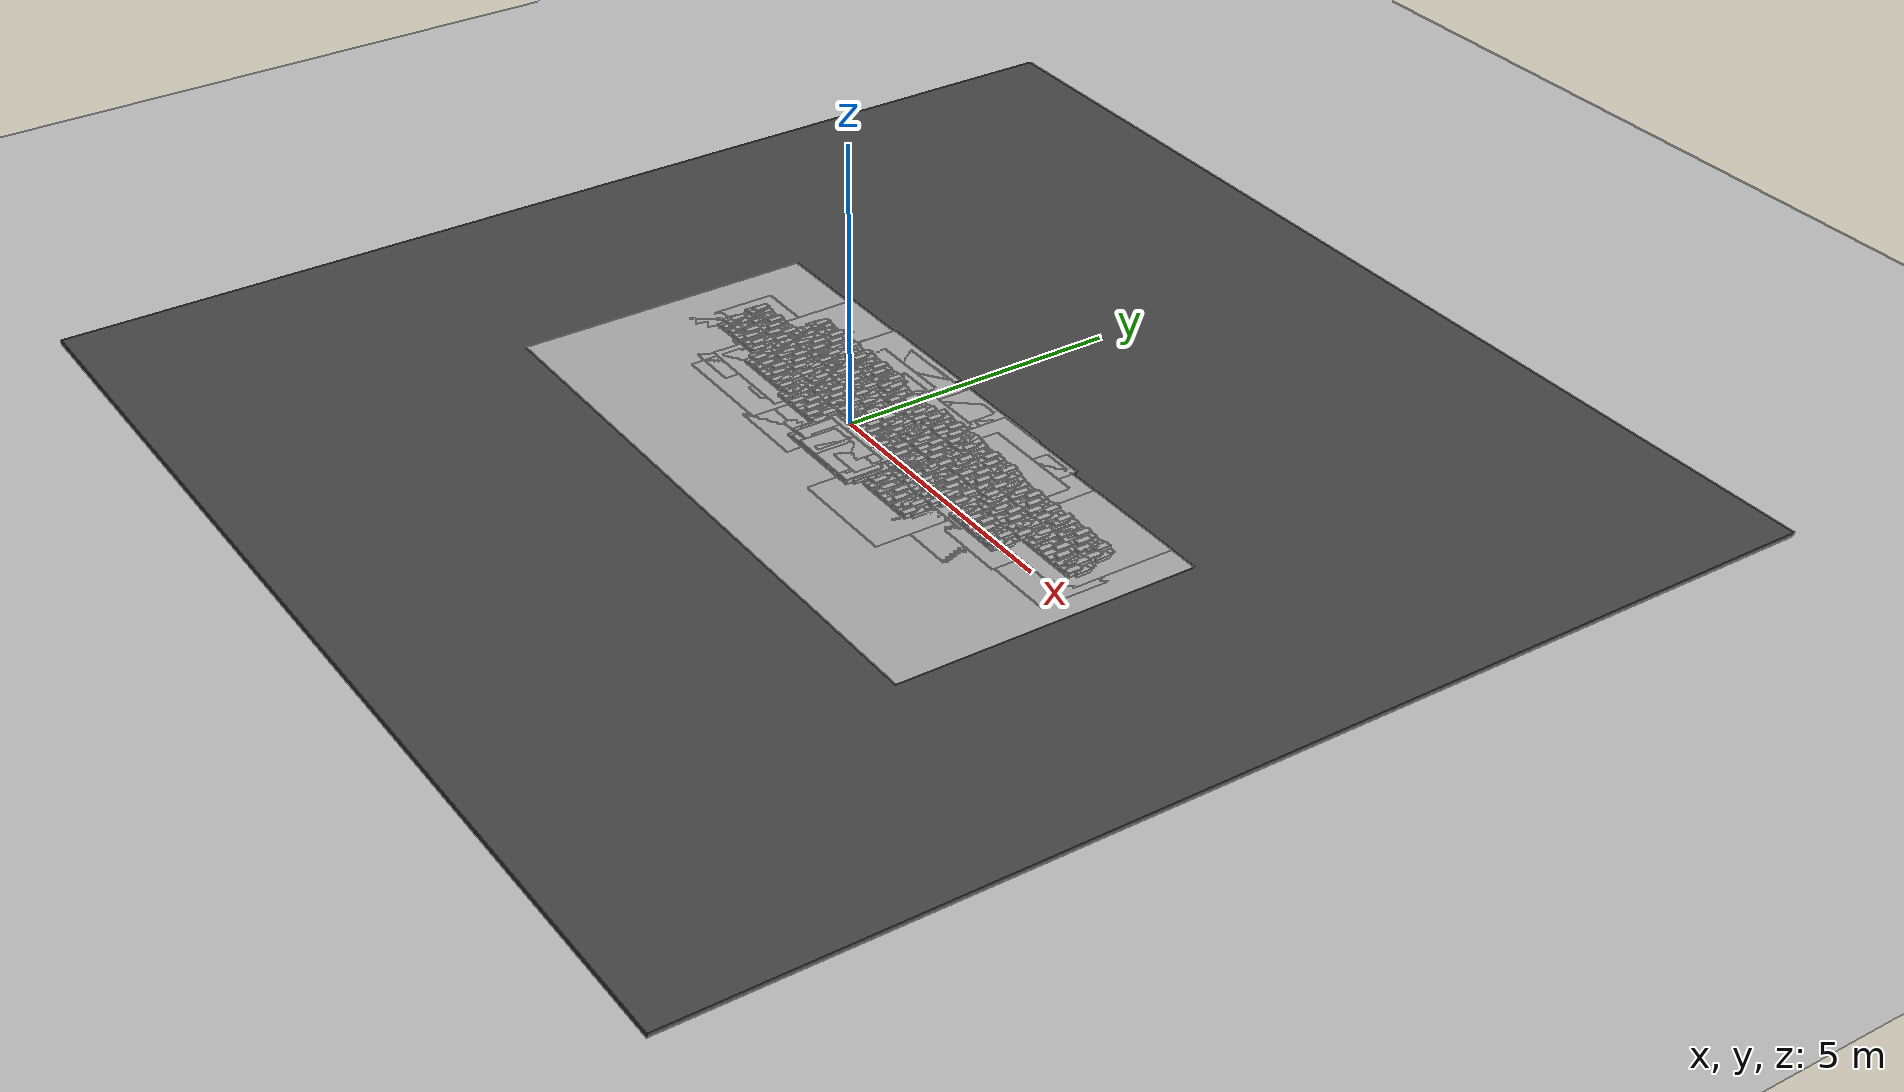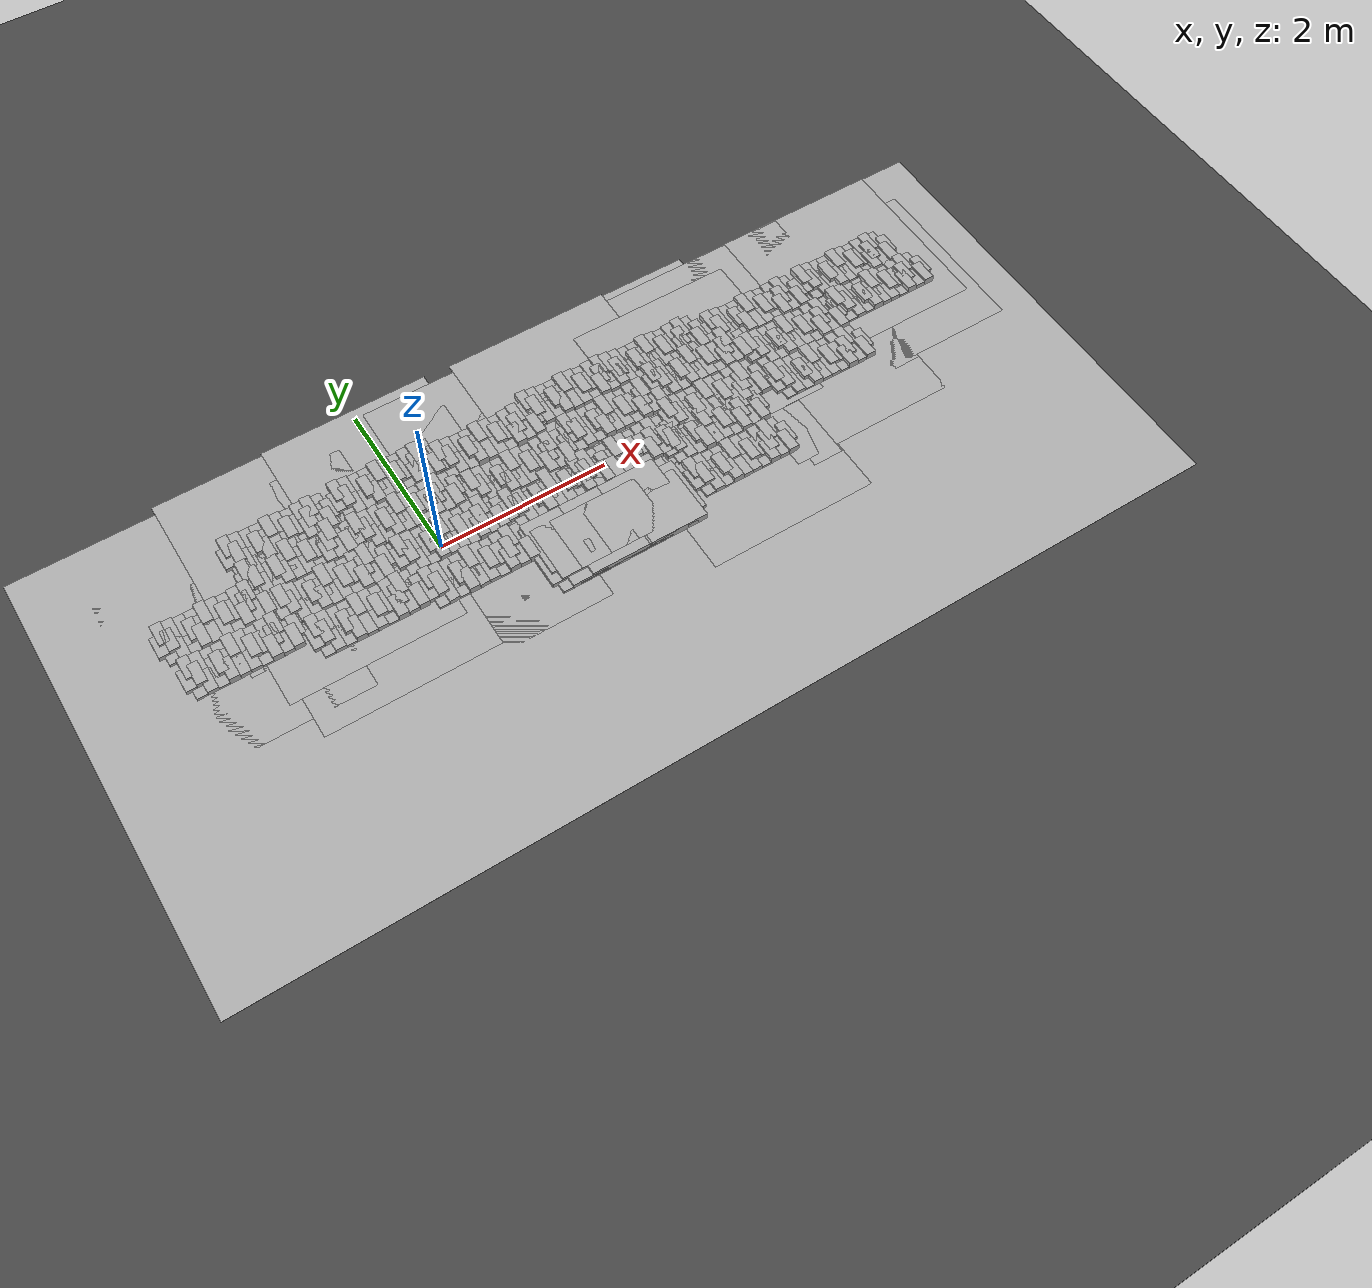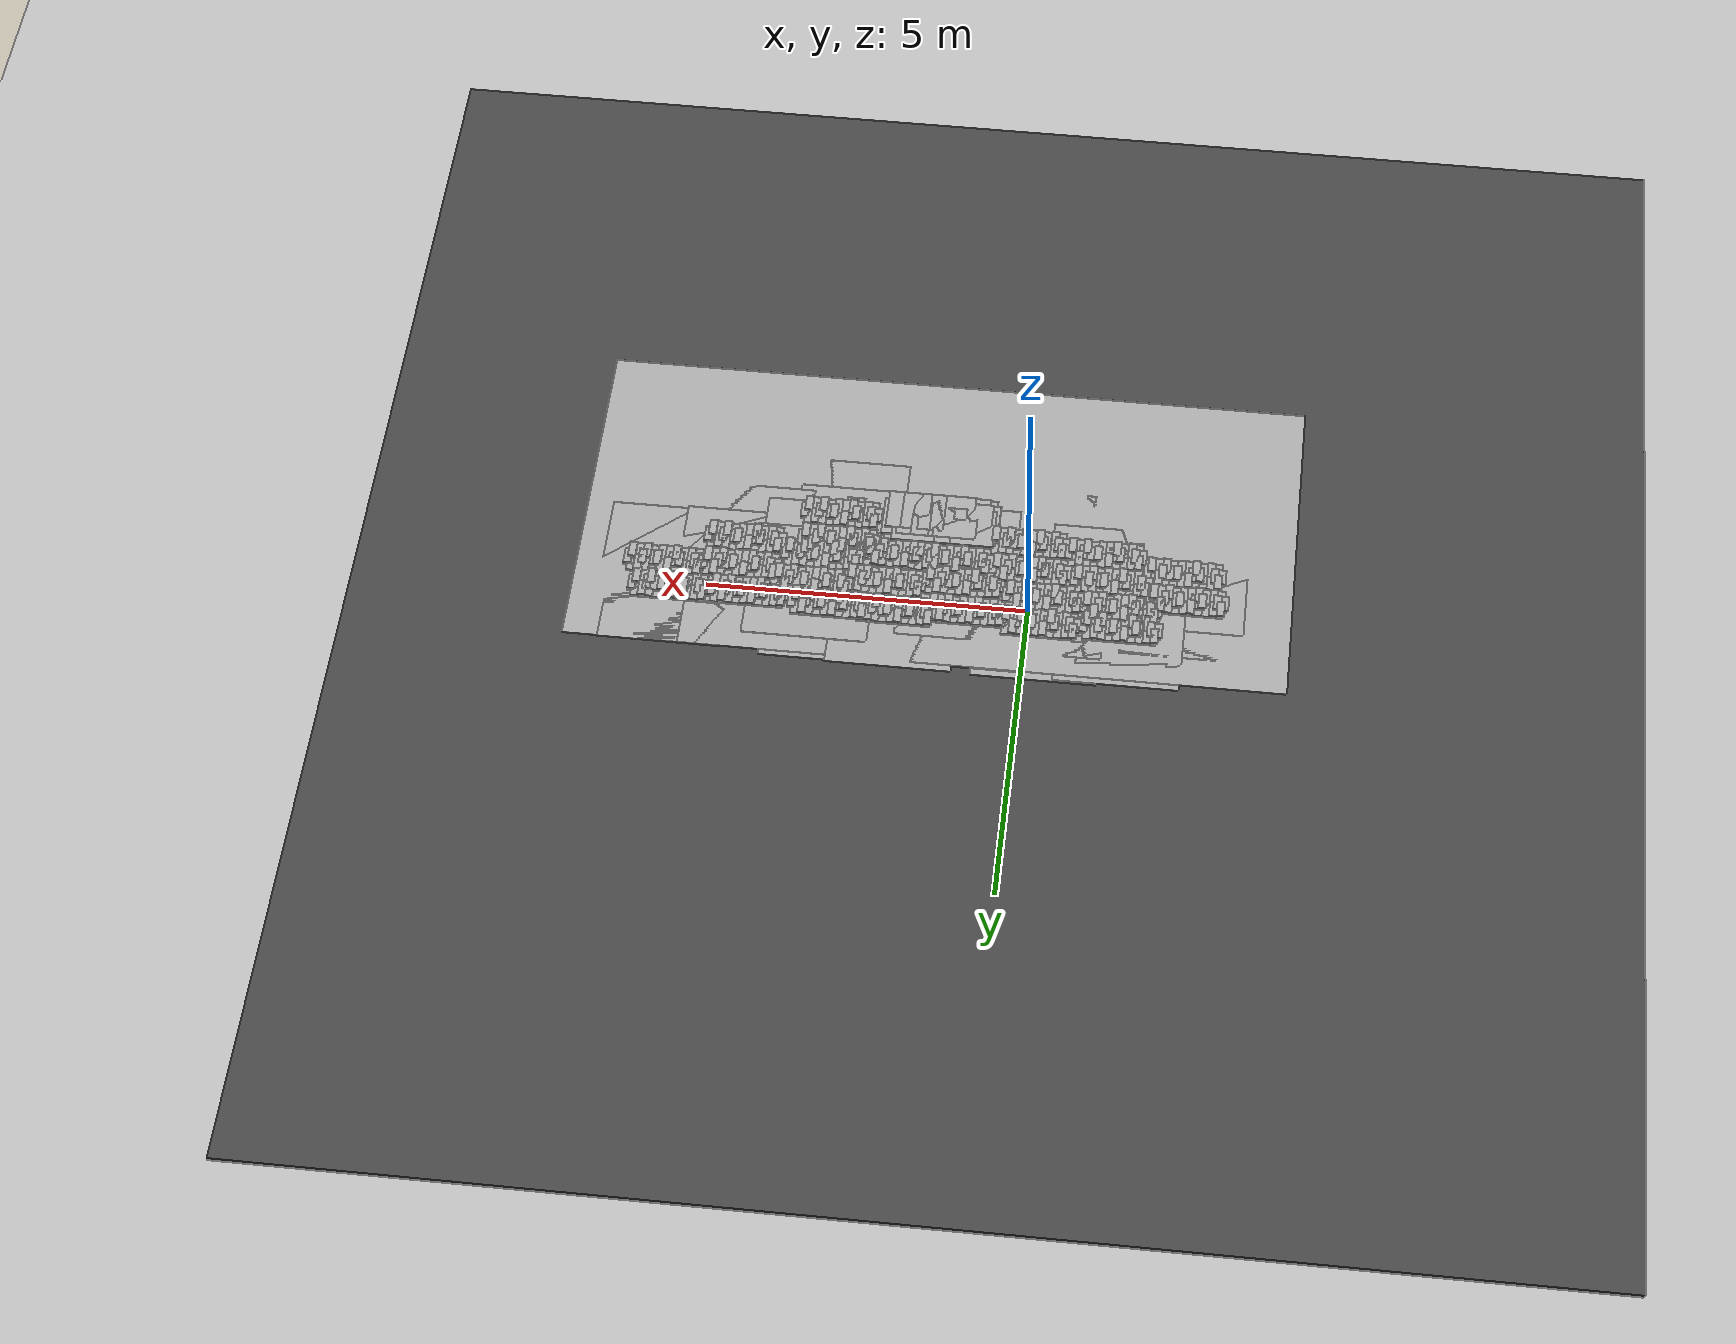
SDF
<sdf version="1.6">
 <world name="default">
  <light name="sun" type="directional">
   <pose>0 0 10 0 -0 0</pose>
   <diffuse>0.8 0.8 0.8 1</diffuse>
   <specular>0.1 0.1 0.1 1</specular>
   <attenuation>
    <range>1000</range>
    <constant>0.9</constant>
    <linear>0.01</linear>
    <quadratic>0.001</quadratic>
   </attenuation>
   <direction>-0.5 0.5 -1</direction>
  </light>
  <model name="ground_plane">
   <static>1</static>
   <link name="link">
    <collision name="collision">
     <geometry><plane><normal>0 0 1</normal><size>100 100</size></plane></geometry>
     <surface><friction><ode><mu>100</mu><mu2>50</mu2></ode></friction></surface>
    </collision>
    <visual name="visual">
     <cast_shadows>0</cast_shadows>
     <geometry><plane><normal>0 0 1</normal><size>100 100</size></plane></geometry>
     <material>
      <script><uri>file://media/materials/scripts/gazebo.material</uri><name>Gazebo/Grey</name></script>
     </material>
    </visual>
   </link>
  </model>
  <gravity>0 0 -9.8</gravity>
  <magnetic_field>6e-06 2.3e-05 -4.2e-05</magnetic_field>
  <atmosphere type="adiabatic"/>
  <physics name="default_physics" default="0" type="ode">
   <max_step_size>0.001</max_step_size>
   <real_time_factor>1</real_time_factor>
   <real_time_update_rate>1000</real_time_update_rate>
  </physics>
  <scene><ambient>0.4 0.4 0.4 1</ambient><background>0.7 0.7 0.7 1</background><shadows>1</shadows></scene>
  <spherical_coordinates>
   <surface_model>EARTH_WGS84</surface_model>
   <latitude_deg>0</latitude_deg>
   <longitude_deg>0</longitude_deg>
   <elevation>0</elevation>
   <heading_deg>0</heading_deg>
  </spherical_coordinates>
  <model name="frc2016_roughterrain_0">
   <link name="link">
    <pose>2.30131 0.070848 -0.073164 0 -0 0</pose>
    <inertial>
     <inertia><ixx>nan</ixx><ixy>0</ixy><ixz>0</ixz><iyy>nan</iyy><iyz>0</iyz><izz>nan</izz></inertia>
     <mass>0</mass>
    </inertial>
    <visual name="platform">
     <pose>0 0 0.08269 0 -0 0</pose>
     <geometry><box><size>1.91826 2.01688 0.003175</size></box></geometry>
    </visual>
    <visual name="row1_block1_sm">
     <pose>0.51435 0.1143 0.09698 0 -0 0</pose>
     <geometry><box><size>0.115452 0.257474 0.0254</size></box></geometry>
    </visual>
    <visual name="row1_block2_lg">
     <pose>0.40005 0.1143 0.12238 0 -0 0</pose>
     <geometry><box><size>0.115452 0.257474 0.0762</size></box></geometry>
    </visual>
    <visual name="row1_block4_sm">
     <pose>0.17145 0.1143 0.09698 0 -0 0</pose>
     <geometry><box><size>0.115452 0.257474 0.0254</size></box></geometry>
    </visual>
    <visual name="row1_block3_md">
     <pose>0.28575 0.1143 0.10968 0 -0 0</pose>
     <geometry><box><size>0.115452 0.257474 0.0508</size></box></geometry>
    </visual>
    <visual name="row1_block5_md">
     <pose>0.05715 0.1143 0.10968 0 -0 0</pose>
     <geometry><box><size>0.115452 0.257474 0.0508</size></box></geometry>
    </visual>
    <visual name="row1_block6_lg">
     <pose>-0.05715 0.1143 0.12238 0 -0 0</pose>
     <geometry><box><size>0.115452 0.257474 0.0762</size></box></geometry>
    </visual>
    <visual name="row1_block7_sm">
     <pose>-0.17145 0.1143 0.09698 0 -0 0</pose>
     <geometry><box><size>0.115452 0.257474 0.0254</size></box></geometry>
    </visual>
    <visual name="row1_block8_sm">
     <pose>-0.28575 0.1143 0.09698 0 -0 0</pose>
     <geometry><box><size>0.115452 0.257474 0.0254</size></box></geometry>
    </visual>
    <visual name="row1_block9_md">
     <pose>-0.40005 0.1143 0.10968 0 -0 0</pose>
     <geometry><box><size>0.115452 0.257474 0.0508</size></box></geometry>
    </visual>
    <visual name="row1_block10_lg">
     <pose>-0.51435 0.1143 0.12238 0 -0 0</pose>
     <geometry><box><size>0.115452 0.257474 0.0762</size></box></geometry>
    </visual>
    <visual name="row2_block1_md">
     <pose>0.5715 0 0.10968 0 -0 0</pose>
     <geometry><box><size>0.115452 0.257474 0.0508</size></box></geometry>
    </visual>
    <visual name="row2_block2_sm">
     <pose>0.4572 0 0.09698 0 -0 0</pose>
     <geometry><box><size>0.115452 0.257474 0.0254</size></box></geometry>
    </visual>
    <visual name="row2_block3_lg">
     <pose>0.3429 0 0.12238 0 -0 0</pose>
     <geometry><box><size>0.115452 0.257474 0.0762</size></box></geometry>
    </visual>
    <visual name="row2_block4_md">
     <pose>0.2286 0 0.10968 0 -0 0</pose>
     <geometry><box><size>0.115452 0.257474 0.0508</size></box></geometry>
    </visual>
    <visual name="row2_block5_lg">
     <pose>0.1143 0 0.12238 0 -0 0</pose>
     <geometry><box><size>0.115452 0.257474 0.0762</size></box></geometry>
    </visual>
    <visual name="row2_block6_sm">
     <pose>0 0 0.09698 0 -0 0</pose>
     <geometry><box><size>0.115452 0.257474 0.0254</size></box></geometry>
    </visual>
    <visual name="row2_block7_md">
     <pose>-0.1143 0 0.10968 0 -0 0</pose>
     <geometry><box><size>0.115452 0.257474 0.0508</size></box></geometry>
    </visual>
    <visual name="row2_block8_lg">
     <pose>-0.2286 0 0.12238 0 -0 0</pose>
     <geometry><box><size>0.115452 0.257474 0.0762</size></box></geometry>
    </visual>
    <visual name="row2_block9_sm">
     <pose>-0.3429 0 0.09698 0 -0 0</pose>
     <geometry><box><size>0.115452 0.257474 0.0254</size></box></geometry>
    </visual>
    <visual name="row2_block10_lg">
     <pose>-0.4572 0 0.12238 0 -0 0</pose>
     <geometry><box><size>0.115452 0.257474 0.0762</size></box></geometry>
    </visual>
    <visual name="row2_block11_md">
     <pose>-0.5715 0 0.10968 0 -0 0</pose>
     <geometry><box><size>0.115452 0.257474 0.0508</size></box></geometry>
    </visual>
    <visual name="row3_block2_md">
     <pose>0.40005 -0.1143 0.10968 0 -0 0</pose>
     <geometry><box><size>0.115452 0.257474 0.0508</size></box></geometry>
    </visual>
    <visual name="row3_block1_lg">
     <pose>0.51435 -0.1143 0.12238 0 -0 0</pose>
     <geometry><box><size>0.115452 0.257474 0.0762</size></box></geometry>
    </visual>
    <visual name="row3_block3_lg">
     <pose>0.28575 -0.1143 0.12238 0 -0 0</pose>
     <geometry><box><size>0.115452 0.257474 0.0762</size></box></geometry>
    </visual>
    <visual name="row3_block4_sm">
     <pose>0.17145 -0.1143 0.09698 0 -0 0</pose>
     <geometry><box><size>0.115452 0.257474 0.0254</size></box></geometry>
    </visual>
    <visual name="row3_block5_md">
     <pose>0.05715 -0.1143 0.10968 0 -0 0</pose>
     <geometry><box><size>0.115452 0.257474 0.0508</size></box></geometry>
    </visual>
    <visual name="row3_block6_md">
     <pose>-0.05715 -0.1143 0.10968 0 -0 0</pose>
     <geometry><box><size>0.115452 0.257474 0.0508</size></box></geometry>
    </visual>
    <visual name="row3_block8_sm">
     <pose>-0.28575 -0.1143 0.09698 0 -0 0</pose>
     <geometry><box><size>0.115452 0.257474 0.0254</size></box></geometry>
    </visual>
    <visual name="row3_block7_lg">
     <pose>-0.17145 -0.1143 0.12238 0 -0 0</pose>
     <geometry><box><size>0.115452 0.257474 0.0762</size></box></geometry>
    </visual>
    <visual name="row3_block9_md">
     <pose>-0.40005 -0.1143 0.10968 0 -0 0</pose>
     <geometry><box><size>0.115452 0.257474 0.0508</size></box></geometry>
    </visual>
    <visual name="row3_block10_sm">
     <pose>-0.51435 -0.1143 0.09698 0 -0 0</pose>
     <geometry><box><size>0.115452 0.257474 0.0254</size></box></geometry>
    </visual>
    <collision name="row2_block5_lg">
     <pose>0.1143 0 0.12238 0 -0 0</pose>
     <geometry><box><size>0.115452 0.257474 0.0762</size></box></geometry>
     <surface>
      <friction>
       <ode><mu>1</mu><mu2>1</mu2><fdir1>0 0 0</fdir1><slip1>0</slip1><slip2>0</slip2></ode>
       <torsional>
        <coefficient>1</coefficient>
        <patch_radius>0</patch_radius>
        <surface_radius>0</surface_radius>
        <use_patch_radius>1</use_patch_radius>
        <ode><slip>0</slip></ode>
       </torsional>
      </friction>
      <bounce><restitution_coefficient>0</restitution_coefficient><threshold>1e+06</threshold></bounce>
      <contact>
       <collide_without_contact>0</collide_without_contact>
       <collide_without_contact_bitmask>1</collide_without_contact_bitmask>
       <collide_bitmask>1</collide_bitmask>
       <ode>
        <soft_cfm>0</soft_cfm>
        <soft_erp>0.2</soft_erp>
        <kp>1e+13</kp>
        <kd>1</kd>
        <max_vel>0.01</max_vel>
        <min_depth>0</min_depth>
       </ode>
       <bullet>
        <split_impulse>1</split_impulse>
        <split_impulse_penetration_threshold>-0.01</split_impulse_penetration_threshold>
        <soft_cfm>0</soft_cfm>
        <soft_erp>0.2</soft_erp>
        <kp>1e+13</kp>
        <kd>1</kd>
       </bullet>
      </contact>
     </surface>
    </collision>
    <collision name="platform">
     <pose>0 0 0.08269 0 -0 0</pose>
     <geometry><box><size>1.91826 2.01688 0.003175</size></box></geometry>
     <surface>
      <friction>
       <ode><mu>1</mu><mu2>1</mu2><fdir1>0 0 0</fdir1><slip1>0</slip1><slip2>0</slip2></ode>
       <torsional>
        <coefficient>1</coefficient>
        <patch_radius>0</patch_radius>
        <surface_radius>0</surface_radius>
        <use_patch_radius>1</use_patch_radius>
        <ode><slip>0</slip></ode>
       </torsional>
      </friction>
      <bounce><restitution_coefficient>0</restitution_coefficient><threshold>1e+06</threshold></bounce>
      <contact>
       <collide_without_contact>0</collide_without_contact>
       <collide_without_contact_bitmask>1</collide_without_contact_bitmask>
       <collide_bitmask>1</collide_bitmask>
       <ode>
        <soft_cfm>0</soft_cfm>
        <soft_erp>0.2</soft_erp>
        <kp>1e+13</kp>
        <kd>1</kd>
        <max_vel>0.01</max_vel>
        <min_depth>0</min_depth>
       </ode>
       <bullet>
        <split_impulse>1</split_impulse>
        <split_impulse_penetration_threshold>-0.01</split_impulse_penetration_threshold>
        <soft_cfm>0</soft_cfm>
        <soft_erp>0.2</soft_erp>
        <kp>1e+13</kp>
        <kd>1</kd>
       </bullet>
      </contact>
     </surface>
    </collision>
    <collision name="row1_block1_sm">
     <pose>0.51435 0.1143 0.09698 0 -0 0</pose>
     <geometry><box><size>0.115452 0.257474 0.0254</size></box></geometry>
     <surface>
      <friction>
       <ode><mu>1</mu><mu2>1</mu2><fdir1>0 0 0</fdir1><slip1>0</slip1><slip2>0</slip2></ode>
       <torsional>
        <coefficient>1</coefficient>
        <patch_radius>0</patch_radius>
        <surface_radius>0</surface_radius>
        <use_patch_radius>1</use_patch_radius>
        <ode><slip>0</slip></ode>
       </torsional>
      </friction>
      <bounce><restitution_coefficient>0</restitution_coefficient><threshold>1e+06</threshold></bounce>
      <contact>
       <collide_without_contact>0</collide_without_contact>
       <collide_without_contact_bitmask>1</collide_without_contact_bitmask>
       <collide_bitmask>1</collide_bitmask>
       <ode>
        <soft_cfm>0</soft_cfm>
        <soft_erp>0.2</soft_erp>
        <kp>1e+13</kp>
        <kd>1</kd>
        <max_vel>0.01</max_vel>
        <min_depth>0</min_depth>
       </ode>
       <bullet>
        <split_impulse>1</split_impulse>
        <split_impulse_penetration_threshold>-0.01</split_impulse_penetration_threshold>
        <soft_cfm>0</soft_cfm>
        <soft_erp>0.2</soft_erp>
        <kp>1e+13</kp>
        <kd>1</kd>
       </bullet>
      </contact>
     </surface>
    </collision>
    <collision name="row1_block3_md">
     <pose>0.28575 0.1143 0.10968 0 -0 0</pose>
     <geometry><box><size>0.115452 0.257474 0.0508</size></box></geometry>
     <surface>
      <friction>
       <ode><mu>1</mu><mu2>1</mu2><fdir1>0 0 0</fdir1><slip1>0</slip1><slip2>0</slip2></ode>
       <torsional>
        <coefficient>1</coefficient>
        <patch_radius>0</patch_radius>
        <surface_radius>0</surface_radius>
        <use_patch_radius>1</use_patch_radius>
        <ode><slip>0</slip></ode>
       </torsional>
      </friction>
      <bounce><restitution_coefficient>0</restitution_coefficient><threshold>1e+06</threshold></bounce>
      <contact>
       <collide_without_contact>0</collide_without_contact>
       <collide_without_contact_bitmask>1</collide_without_contact_bitmask>
       <collide_bitmask>1</collide_bitmask>
       <ode>
        <soft_cfm>0</soft_cfm>
        <soft_erp>0.2</soft_erp>
        <kp>1e+13</kp>
        <kd>1</kd>
        <max_vel>0.01</max_vel>
        <min_depth>0</min_depth>
       </ode>
       <bullet>
        <split_impulse>1</split_impulse>
        <split_impulse_penetration_threshold>-0.01</split_impulse_penetration_threshold>
        <soft_cfm>0</soft_cfm>
        <soft_erp>0.2</soft_erp>
        <kp>1e+13</kp>
        <kd>1</kd>
       </bullet>
      </contact>
     </surface>
    </collision>
    <collision name="row1_block2_lg">
     <pose>0.40005 0.1143 0.12238 0 -0 0</pose>
     <geometry><box><size>0.115452 0.257474 0.0762</size></box></geometry>
     <surface>
      <friction>
       <ode><mu>1</mu><mu2>1</mu2><fdir1>0 0 0</fdir1><slip1>0</slip1><slip2>0</slip2></ode>
       <torsional>
        <coefficient>1</coefficient>
        <patch_radius>0</patch_radius>
        <surface_radius>0</surface_radius>
        <use_patch_radius>1</use_patch_radius>
        <ode><slip>0</slip></ode>
       </torsional>
      </friction>
      <bounce><restitution_coefficient>0</restitution_coefficient><threshold>1e+06</threshold></bounce>
      <contact>
       <collide_without_contact>0</collide_without_contact>
       <collide_without_contact_bitmask>1</collide_without_contact_bitmask>
       <collide_bitmask>1</collide_bitmask>
       <ode>
        <soft_cfm>0</soft_cfm>
        <soft_erp>0.2</soft_erp>
        <kp>1e+13</kp>
        <kd>1</kd>
        <max_vel>0.01</max_vel>
        <min_depth>0</min_depth>
       </ode>
       <bullet>
        <split_impulse>1</split_impulse>
        <split_impulse_penetration_threshold>-0.01</split_impulse_penetration_threshold>
        <soft_cfm>0</soft_cfm>
        <soft_erp>0.2</soft_erp>
        <kp>1e+13</kp>
        <kd>1</kd>
       </bullet>
      </contact>
     </surface>
    </collision>
    <collision name="row1_block5_md">
     <pose>0.05715 0.1143 0.10968 0 -0 0</pose>
     <geometry><box><size>0.115452 0.257474 0.0508</size></box></geometry>
     <surface>
      <friction>
       <ode><mu>1</mu><mu2>1</mu2><fdir1>0 0 0</fdir1><slip1>0</slip1><slip2>0</slip2></ode>
       <torsional>
        <coefficient>1</coefficient>
        <patch_radius>0</patch_radius>
        <surface_radius>0</surface_radius>
        <use_patch_radius>1</use_patch_radius>
        <ode><slip>0</slip></ode>
       </torsional>
      </friction>
      <bounce><restitution_coefficient>0</restitution_coefficient><threshold>1e+06</threshold></bounce>
      <contact>
       <collide_without_contact>0</collide_without_contact>
       <collide_without_contact_bitmask>1</collide_without_contact_bitmask>
       <collide_bitmask>1</collide_bitmask>
       <ode>
        <soft_cfm>0</soft_cfm>
        <soft_erp>0.2</soft_erp>
        <kp>1e+13</kp>
        <kd>1</kd>
        <max_vel>0.01</max_vel>
        <min_depth>0</min_depth>
       </ode>
       <bullet>
        <split_impulse>1</split_impulse>
        <split_impulse_penetration_threshold>-0.01</split_impulse_penetration_threshold>
        <soft_cfm>0</soft_cfm>
        <soft_erp>0.2</soft_erp>
        <kp>1e+13</kp>
        <kd>1</kd>
       </bullet>
      </contact>
     </surface>
    </collision>
    <collision name="row1_block4_sm">
     <pose>0.17145 0.1143 0.09698 0 -0 0</pose>
     <geometry><box><size>0.115452 0.257474 0.0254</size></box></geometry>
     <surface>
      <friction>
       <ode><mu>1</mu><mu2>1</mu2><fdir1>0 0 0</fdir1><slip1>0</slip1><slip2>0</slip2></ode>
       <torsional>
        <coefficient>1</coefficient>
        <patch_radius>0</patch_radius>
        <surface_radius>0</surface_radius>
        <use_patch_radius>1</use_patch_radius>
        <ode><slip>0</slip></ode>
       </torsional>
      </friction>
      <bounce><restitution_coefficient>0</restitution_coefficient><threshold>1e+06</threshold></bounce>
      <contact>
       <collide_without_contact>0</collide_without_contact>
       <collide_without_contact_bitmask>1</collide_without_contact_bitmask>
       <collide_bitmask>1</collide_bitmask>
       <ode>
        <soft_cfm>0</soft_cfm>
        <soft_erp>0.2</soft_erp>
        <kp>1e+13</kp>
        <kd>1</kd>
        <max_vel>0.01</max_vel>
        <min_depth>0</min_depth>
       </ode>
       <bullet>
        <split_impulse>1</split_impulse>
        <split_impulse_penetration_threshold>-0.01</split_impulse_penetration_threshold>
        <soft_cfm>0</soft_cfm>
        <soft_erp>0.2</soft_erp>
        <kp>1e+13</kp>
        <kd>1</kd>
       </bullet>
      </contact>
     </surface>
    </collision>
    <collision name="row1_block6_lg">
     <pose>-0.05715 0.1143 0.12238 0 -0 0</pose>
     <geometry><box><size>0.115452 0.257474 0.0762</size></box></geometry>
     <surface>
      <friction>
       <ode><mu>1</mu><mu2>1</mu2><fdir1>0 0 0</fdir1><slip1>0</slip1><slip2>0</slip2></ode>
       <torsional>
        <coefficient>1</coefficient>
        <patch_radius>0</patch_radius>
        <surface_radius>0</surface_radius>
        <use_patch_radius>1</use_patch_radius>
        <ode><slip>0</slip></ode>
       </torsional>
      </friction>
      <bounce><restitution_coefficient>0</restitution_coefficient><threshold>1e+06</threshold></bounce>
      <contact>
       <collide_without_contact>0</collide_without_contact>
       <collide_without_contact_bitmask>1</collide_without_contact_bitmask>
       <collide_bitmask>1</collide_bitmask>
       <ode>
        <soft_cfm>0</soft_cfm>
        <soft_erp>0.2</soft_erp>
        <kp>1e+13</kp>
        <kd>1</kd>
        <max_vel>0.01</max_vel>
        <min_depth>0</min_depth>
       </ode>
       <bullet>
        <split_impulse>1</split_impulse>
        <split_impulse_penetration_threshold>-0.01</split_impulse_penetration_threshold>
        <soft_cfm>0</soft_cfm>
        <soft_erp>0.2</soft_erp>
        <kp>1e+13</kp>
        <kd>1</kd>
       </bullet>
      </contact>
     </surface>
    </collision>
    <collision name="row1_block7_sm">
     <pose>-0.17145 0.1143 0.09698 0 -0 0</pose>
     <geometry><box><size>0.115452 0.257474 0.0254</size></box></geometry>
     <surface>
      <friction>
       <ode><mu>1</mu><mu2>1</mu2><fdir1>0 0 0</fdir1><slip1>0</slip1><slip2>0</slip2></ode>
       <torsional>
        <coefficient>1</coefficient>
        <patch_radius>0</patch_radius>
        <surface_radius>0</surface_radius>
        <use_patch_radius>1</use_patch_radius>
        <ode><slip>0</slip></ode>
       </torsional>
      </friction>
      <bounce><restitution_coefficient>0</restitution_coefficient><threshold>1e+06</threshold></bounce>
      <contact>
       <collide_without_contact>0</collide_without_contact>
       <collide_without_contact_bitmask>1</collide_without_contact_bitmask>
       <collide_bitmask>1</collide_bitmask>
       <ode>
        <soft_cfm>0</soft_cfm>
        <soft_erp>0.2</soft_erp>
        <kp>1e+13</kp>
        <kd>1</kd>
        <max_vel>0.01</max_vel>
        <min_depth>0</min_depth>
       </ode>
       <bullet>
        <split_impulse>1</split_impulse>
        <split_impulse_penetration_threshold>-0.01</split_impulse_penetration_threshold>
        <soft_cfm>0</soft_cfm>
        <soft_erp>0.2</soft_erp>
        <kp>1e+13</kp>
        <kd>1</kd>
       </bullet>
      </contact>
     </surface>
    </collision>
    <collision name="row1_block8_sm">
     <pose>-0.28575 0.1143 0.09698 0 -0 0</pose>
     <geometry><box><size>0.115452 0.257474 0.0254</size></box></geometry>
     <surface>
      <friction>
       <ode><mu>1</mu><mu2>1</mu2><fdir1>0 0 0</fdir1><slip1>0</slip1><slip2>0</slip2></ode>
       <torsional>
        <coefficient>1</coefficient>
        <patch_radius>0</patch_radius>
        <surface_radius>0</surface_radius>
        <use_patch_radius>1</use_patch_radius>
        <ode><slip>0</slip></ode>
       </torsional>
      </friction>
      <bounce><restitution_coefficient>0</restitution_coefficient><threshold>1e+06</threshold></bounce>
      <contact>
       <collide_without_contact>0</collide_without_contact>
       <collide_without_contact_bitmask>1</collide_without_contact_bitmask>
       <collide_bitmask>1</collide_bitmask>
       <ode>
        <soft_cfm>0</soft_cfm>
        <soft_erp>0.2</soft_erp>
        <kp>1e+13</kp>
        <kd>1</kd>
        <max_vel>0.01</max_vel>
        <min_depth>0</min_depth>
       </ode>
       <bullet>
        <split_impulse>1</split_impulse>
        <split_impulse_penetration_threshold>-0.01</split_impulse_penetration_threshold>
        <soft_cfm>0</soft_cfm>
        <soft_erp>0.2</soft_erp>
        <kp>1e+13</kp>
        <kd>1</kd>
       </bullet>
      </contact>
     </surface>
    </collision>
    <collision name="row1_block10_lg">
     <pose>-0.51435 0.1143 0.12238 0 -0 0</pose>
     <geometry><box><size>0.115452 0.257474 0.0762</size></box></geometry>
     <surface>
      <friction>
       <ode><mu>1</mu><mu2>1</mu2><fdir1>0 0 0</fdir1><slip1>0</slip1><slip2>0</slip2></ode>
       <torsional>
        <coefficient>1</coefficient>
        <patch_radius>0</patch_radius>
        <surface_radius>0</surface_radius>
        <use_patch_radius>1</use_patch_radius>
        <ode><slip>0</slip></ode>
       </torsional>
      </friction>
      <bounce><restitution_coefficient>0</restitution_coefficient><threshold>1e+06</threshold></bounce>
      <contact>
       <collide_without_contact>0</collide_without_contact>
       <collide_without_contact_bitmask>1</collide_without_contact_bitmask>
       <collide_bitmask>1</collide_bitmask>
       <ode>
        <soft_cfm>0</soft_cfm>
        <soft_erp>0.2</soft_erp>
        <kp>1e+13</kp>
        <kd>1</kd>
        <max_vel>0.01</max_vel>
        <min_depth>0</min_depth>
       </ode>
       <bullet>
        <split_impulse>1</split_impulse>
        <split_impulse_penetration_threshold>-0.01</split_impulse_penetration_threshold>
        <soft_cfm>0</soft_cfm>
        <soft_erp>0.2</soft_erp>
        <kp>1e+13</kp>
        <kd>1</kd>
       </bullet>
      </contact>
     </surface>
    </collision>
    <collision name="row1_block9_md">
     <pose>-0.40005 0.1143 0.10968 0 -0 0</pose>
     <geometry><box><size>0.115452 0.257474 0.0508</size></box></geometry>
     <surface>
      <friction>
       <ode><mu>1</mu><mu2>1</mu2><fdir1>0 0 0</fdir1><slip1>0</slip1><slip2>0</slip2></ode>
       <torsional>
        <coefficient>1</coefficient>
        <patch_radius>0</patch_radius>
        <surface_radius>0</surface_radius>
        <use_patch_radius>1</use_patch_radius>
        <ode><slip>0</slip></ode>
       </torsional>
      </friction>
      <bounce><restitution_coefficient>0</restitution_coefficient><threshold>1e+06</threshold></bounce>
      <contact>
       <collide_without_contact>0</collide_without_contact>
       <collide_without_contact_bitmask>1</collide_without_contact_bitmask>
       <collide_bitmask>1</collide_bitmask>
       <ode>
        <soft_cfm>0</soft_cfm>
        <soft_erp>0.2</soft_erp>
        <kp>1e+13</kp>
        <kd>1</kd>
        <max_vel>0.01</max_vel>
        <min_depth>0</min_depth>
       </ode>
       <bullet>
        <split_impulse>1</split_impulse>
        <split_impulse_penetration_threshold>-0.01</split_impulse_penetration_threshold>
        <soft_cfm>0</soft_cfm>
        <soft_erp>0.2</soft_erp>
        <kp>1e+13</kp>
        <kd>1</kd>
       </bullet>
      </contact>
     </surface>
    </collision>
    <collision name="row2_block1_md">
     <pose>0.5715 0 0.10968 0 -0 0</pose>
     <geometry><box><size>0.115452 0.257474 0.0508</size></box></geometry>
     <surface>
      <friction>
       <ode><mu>1</mu><mu2>1</mu2><fdir1>0 0 0</fdir1><slip1>0</slip1><slip2>0</slip2></ode>
       <torsional>
        <coefficient>1</coefficient>
        <patch_radius>0</patch_radius>
        <surface_radius>0</surface_radius>
        <use_patch_radius>1</use_patch_radius>
        <ode><slip>0</slip></ode>
       </torsional>
      </friction>
      <bounce><restitution_coefficient>0</restitution_coefficient><threshold>1e+06</threshold></bounce>
      <contact>
       <collide_without_contact>0</collide_without_contact>
       <collide_without_contact_bitmask>1</collide_without_contact_bitmask>
       <collide_bitmask>1</collide_bitmask>
       <ode>
        <soft_cfm>0</soft_cfm>
        <soft_erp>0.2</soft_erp>
        <kp>1e+13</kp>
        <kd>1</kd>
        <max_vel>0.01</max_vel>
        <min_depth>0</min_depth>
       </ode>
       <bullet>
        <split_impulse>1</split_impulse>
        <split_impulse_penetration_threshold>-0.01</split_impulse_penetration_threshold>
        <soft_cfm>0</soft_cfm>
        <soft_erp>0.2</soft_erp>
        <kp>1e+13</kp>
        <kd>1</kd>
       </bullet>
      </contact>
     </surface>
    </collision>
    <collision name="row2_block2_sm">
     <pose>0.4572 0 0.09698 0 -0 0</pose>
     <geometry><box><size>0.115452 0.257474 0.0254</size></box></geometry>
     <surface>
      <friction>
       <ode><mu>1</mu><mu2>1</mu2><fdir1>0 0 0</fdir1><slip1>0</slip1><slip2>0</slip2></ode>
       <torsional>
        <coefficient>1</coefficient>
        <patch_radius>0</patch_radius>
        <surface_radius>0</surface_radius>
        <use_patch_radius>1</use_patch_radius>
        <ode><slip>0</slip></ode>
       </torsional>
      </friction>
      <bounce><restitution_coefficient>0</restitution_coefficient><threshold>1e+06</threshold></bounce>
      <contact>
       <collide_without_contact>0</collide_without_contact>
       <collide_without_contact_bitmask>1</collide_without_contact_bitmask>
       <collide_bitmask>1</collide_bitmask>
       <ode>
        <soft_cfm>0</soft_cfm>
        <soft_erp>0.2</soft_erp>
        <kp>1e+13</kp>
        <kd>1</kd>
        <max_vel>0.01</max_vel>
        <min_depth>0</min_depth>
       </ode>
       <bullet>
        <split_impulse>1</split_impulse>
        <split_impulse_penetration_threshold>-0.01</split_impulse_penetration_threshold>
        <soft_cfm>0</soft_cfm>
        <soft_erp>0.2</soft_erp>
        <kp>1e+13</kp>
        <kd>1</kd>
       </bullet>
      </contact>
     </surface>
    </collision>
    <collision name="row2_block4_md">
     <pose>0.2286 0 0.10968 0 -0 0</pose>
     <geometry><box><size>0.115452 0.257474 0.0508</size></box></geometry>
     <surface>
      <friction>
       <ode><mu>1</mu><mu2>1</mu2><fdir1>0 0 0</fdir1><slip1>0</slip1><slip2>0</slip2></ode>
       <torsional>
        <coefficient>1</coefficient>
        <patch_radius>0</patch_radius>
        <surface_radius>0</surface_radius>
        <use_patch_radius>1</use_patch_radius>
        <ode><slip>0</slip></ode>
       </torsional>
      </friction>
      <bounce><restitution_coefficient>0</restitution_coefficient><threshold>1e+06</threshold></bounce>
      <contact>
       <collide_without_contact>0</collide_without_contact>
       <collide_without_contact_bitmask>1</collide_without_contact_bitmask>
       <collide_bitmask>1</collide_bitmask>
       <ode>
        <soft_cfm>0</soft_cfm>
        <soft_erp>0.2</soft_erp>
        <kp>1e+13</kp>
        <kd>1</kd>
        <max_vel>0.01</max_vel>
        <min_depth>0</min_depth>
       </ode>
       <bullet>
        <split_impulse>1</split_impulse>
        <split_impulse_penetration_threshold>-0.01</split_impulse_penetration_threshold>
        <soft_cfm>0</soft_cfm>
        <soft_erp>0.2</soft_erp>
        <kp>1e+13</kp>
        <kd>1</kd>
       </bullet>
      </contact>
     </surface>
    </collision>
    <collision name="row2_block3_lg">
     <pose>0.3429 0 0.12238 0 -0 0</pose>
     <geometry><box><size>0.115452 0.257474 0.0762</size></box></geometry>
     <surface>
      <friction>
       <ode><mu>1</mu><mu2>1</mu2><fdir1>0 0 0</fdir1><slip1>0</slip1><slip2>0</slip2></ode>
       <torsional>
        <coefficient>1</coefficient>
        <patch_radius>0</patch_radius>
        <surface_radius>0</surface_radius>
        <use_patch_radius>1</use_patch_radius>
        <ode><slip>0</slip></ode>
       </torsional>
      </friction>
      <bounce><restitution_coefficient>0</restitution_coefficient><threshold>1e+06</threshold></bounce>
      <contact>
       <collide_without_contact>0</collide_without_contact>
       <collide_without_contact_bitmask>1</collide_without_contact_bitmask>
       <collide_bitmask>1</collide_bitmask>
       <ode>
        <soft_cfm>0</soft_cfm>
        <soft_erp>0.2</soft_erp>
        <kp>1e+13</kp>
        <kd>1</kd>
        <max_vel>0.01</max_vel>
        <min_depth>0</min_depth>
       </ode>
       <bullet>
        <split_impulse>1</split_impulse>
        <split_impulse_penetration_threshold>-0.01</split_impulse_penetration_threshold>
        <soft_cfm>0</soft_cfm>
        <soft_erp>0.2</soft_erp>
        <kp>1e+13</kp>
        <kd>1</kd>
       </bullet>
      </contact>
     </surface>
    </collision>
    <collision name="row2_block6_sm">
     <pose>0 0 0.09698 0 -0 0</pose>
     <geometry><box><size>0.115452 0.257474 0.0254</size></box></geometry>
     <surface>
      <friction>
       <ode><mu>1</mu><mu2>1</mu2><fdir1>0 0 0</fdir1><slip1>0</slip1><slip2>0</slip2></ode>
       <torsional>
        <coefficient>1</coefficient>
        <patch_radius>0</patch_radius>
        <surface_radius>0</surface_radius>
        <use_patch_radius>1</use_patch_radius>
        <ode><slip>0</slip></ode>
       </torsional>
      </friction>
      <bounce><restitution_coefficient>0</restitution_coefficient><threshold>1e+06</threshold></bounce>
      <contact>
       <collide_without_contact>0</collide_without_contact>
       <collide_without_contact_bitmask>1</collide_without_contact_bitmask>
       <collide_bitmask>1</collide_bitmask>
       <ode>
        <soft_cfm>0</soft_cfm>
        <soft_erp>0.2</soft_erp>
        <kp>1e+13</kp>
        <kd>1</kd>
        <max_vel>0.01</max_vel>
        <min_depth>0</min_depth>
       </ode>
       <bullet>
        <split_impulse>1</split_impulse>
        <split_impulse_penetration_threshold>-0.01</split_impulse_penetration_threshold>
        <soft_cfm>0</soft_cfm>
        <soft_erp>0.2</soft_erp>
        <kp>1e+13</kp>
        <kd>1</kd>
       </bullet>
      </contact>
     </surface>
    </collision>
    <collision name="row2_block7_md">
     <pose>-0.1143 0 0.10968 0 -0 0</pose>
     <geometry><box><size>0.115452 0.257474 0.0508</size></box></geometry>
     <surface>
      <friction>
       <ode><mu>1</mu><mu2>1</mu2><fdir1>0 0 0</fdir1><slip1>0</slip1><slip2>0</slip2></ode>
       <torsional>
        <coefficient>1</coefficient>
        <patch_radius>0</patch_radius>
        <surface_radius>0</surface_radius>
        <use_patch_radius>1</use_patch_radius>
        <ode><slip>0</slip></ode>
       </torsional>
      </friction>
      <bounce><restitution_coefficient>0</restitution_coefficient><threshold>1e+06</threshold></bounce>
      <contact>
       <collide_without_contact>0</collide_without_contact>
       <collide_without_contact_bitmask>1</collide_without_contact_bitmask>
       <collide_bitmask>1</collide_bitmask>
       <ode>
        <soft_cfm>0</soft_cfm>
        <soft_erp>0.2</soft_erp>
        <kp>1e+13</kp>
        <kd>1</kd>
        <max_vel>0.01</max_vel>
        <min_depth>0</min_depth>
       </ode>
       <bullet>
        <split_impulse>1</split_impulse>
        <split_impulse_penetration_threshold>-0.01</split_impulse_penetration_threshold>
        <soft_cfm>0</soft_cfm>
        <soft_erp>0.2</soft_erp>
        <kp>1e+13</kp>
        <kd>1</kd>
       </bullet>
      </contact>
     </surface>
    </collision>
    <collision name="row2_block10_lg">
     <pose>-0.4572 0 0.12238 0 -0 0</pose>
     <geometry><box><size>0.115452 0.257474 0.0762</size></box></geometry>
     <surface>
      <friction>
       <ode><mu>1</mu><mu2>1</mu2><fdir1>0 0 0</fdir1><slip1>0</slip1><slip2>0</slip2></ode>
       <torsional>
        <coefficient>1</coefficient>
        <patch_radius>0</patch_radius>
        <surface_radius>0</surface_radius>
        <use_patch_radius>1</use_patch_radius>
        <ode><slip>0</slip></ode>
       </torsional>
      </friction>
      <bounce><restitution_coefficient>0</restitution_coefficient><threshold>1e+06</threshold></bounce>
      <contact>
       <collide_without_contact>0</collide_without_contact>
       <collide_without_contact_bitmask>1</collide_without_contact_bitmask>
       <collide_bitmask>1</collide_bitmask>
       <ode>
        <soft_cfm>0</soft_cfm>
        <soft_erp>0.2</soft_erp>
        <kp>1e+13</kp>
        <kd>1</kd>
        <max_vel>0.01</max_vel>
        <min_depth>0</min_depth>
       </ode>
       <bullet>
        <split_impulse>1</split_impulse>
        <split_impulse_penetration_threshold>-0.01</split_impulse_penetration_threshold>
        <soft_cfm>0</soft_cfm>
        <soft_erp>0.2</soft_erp>
        <kp>1e+13</kp>
        <kd>1</kd>
       </bullet>
      </contact>
     </surface>
    </collision>
    <collision name="row2_block8_lg">
     <pose>-0.2286 0 0.12238 0 -0 0</pose>
     <geometry><box><size>0.115452 0.257474 0.0762</size></box></geometry>
     <surface>
      <friction>
       <ode><mu>1</mu><mu2>1</mu2><fdir1>0 0 0</fdir1><slip1>0</slip1><slip2>0</slip2></ode>
       <torsional>
        <coefficient>1</coefficient>
        <patch_radius>0</patch_radius>
        <surface_radius>0</surface_radius>
        <use_patch_radius>1</use_patch_radius>
        <ode><slip>0</slip></ode>
       </torsional>
      </friction>
      <bounce><restitution_coefficient>0</restitution_coefficient><threshold>1e+06</threshold></bounce>
      <contact>
       <collide_without_contact>0</collide_without_contact>
       <collide_without_contact_bitmask>1</collide_without_contact_bitmask>
       <collide_bitmask>1</collide_bitmask>
       <ode>
        <soft_cfm>0</soft_cfm>
        <soft_erp>0.2</soft_erp>
        <kp>1e+13</kp>
        <kd>1</kd>
        <max_vel>0.01</max_vel>
        <min_depth>0</min_depth>
       </ode>
       <bullet>
        <split_impulse>1</split_impulse>
        <split_impulse_penetration_threshold>-0.01</split_impulse_penetration_threshold>
        <soft_cfm>0</soft_cfm>
        <soft_erp>0.2</soft_erp>
        <kp>1e+13</kp>
        <kd>1</kd>
       </bullet>
      </contact>
     </surface>
    </collision>
    <collision name="row2_block9_sm">
     <pose>-0.3429 0 0.09698 0 -0 0</pose>
     <geometry><box><size>0.115452 0.257474 0.0254</size></box></geometry>
     <surface>
      <friction>
       <ode><mu>1</mu><mu2>1</mu2><fdir1>0 0 0</fdir1><slip1>0</slip1><slip2>0</slip2></ode>
       <torsional>
        <coefficient>1</coefficient>
        <patch_radius>0</patch_radius>
        <surface_radius>0</surface_radius>
        <use_patch_radius>1</use_patch_radius>
        <ode><slip>0</slip></ode>
       </torsional>
      </friction>
      <bounce><restitution_coefficient>0</restitution_coefficient><threshold>1e+06</threshold></bounce>
      <contact>
       <collide_without_contact>0</collide_without_contact>
       <collide_without_contact_bitmask>1</collide_without_contact_bitmask>
       <collide_bitmask>1</collide_bitmask>
       <ode>
        <soft_cfm>0</soft_cfm>
        <soft_erp>0.2</soft_erp>
        <kp>1e+13</kp>
        <kd>1</kd>
        <max_vel>0.01</max_vel>
        <min_depth>0</min_depth>
       </ode>
       <bullet>
        <split_impulse>1</split_impulse>
        <split_impulse_penetration_threshold>-0.01</split_impulse_penetration_threshold>
        <soft_cfm>0</soft_cfm>
        <soft_erp>0.2</soft_erp>
        <kp>1e+13</kp>
        <kd>1</kd>
       </bullet>
      </contact>
     </surface>
    </collision>
    <collision name="row2_block11_md">
     <pose>-0.5715 0 0.10968 0 -0 0</pose>
     <geometry><box><size>0.115452 0.257474 0.0508</size></box></geometry>
     <surface>
      <friction>
       <ode><mu>1</mu><mu2>1</mu2><fdir1>0 0 0</fdir1><slip1>0</slip1><slip2>0</slip2></ode>
       <torsional>
        <coefficient>1</coefficient>
        <patch_radius>0</patch_radius>
        <surface_radius>0</surface_radius>
        <use_patch_radius>1</use_patch_radius>
        <ode><slip>0</slip></ode>
       </torsional>
      </friction>
      <bounce><restitution_coefficient>0</restitution_coefficient><threshold>1e+06</threshold></bounce>
      <contact>
       <collide_without_contact>0</collide_without_contact>
       <collide_without_contact_bitmask>1</collide_without_contact_bitmask>
       <collide_bitmask>1</collide_bitmask>
       <ode>
        <soft_cfm>0</soft_cfm>
        <soft_erp>0.2</soft_erp>
        <kp>1e+13</kp>
        <kd>1</kd>
        <max_vel>0.01</max_vel>
        <min_depth>0</min_depth>
       </ode>
       <bullet>
        <split_impulse>1</split_impulse>
        <split_impulse_penetration_threshold>-0.01</split_impulse_penetration_threshold>
        <soft_cfm>0</soft_cfm>
        <soft_erp>0.2</soft_erp>
        <kp>1e+13</kp>
        <kd>1</kd>
       </bullet>
      </contact>
     </surface>
    </collision>
    <collision name="row3_block2_md">
     <pose>0.40005 -0.1143 0.10968 0 -0 0</pose>
     <geometry><box><size>0.115452 0.257474 0.0508</size></box></geometry>
     <surface>
      <friction>
       <ode><mu>1</mu><mu2>1</mu2><fdir1>0 0 0</fdir1><slip1>0</slip1><slip2>0</slip2></ode>
       <torsional>
        <coefficient>1</coefficient>
        <patch_radius>0</patch_radius>
        <surface_radius>0</surface_radius>
        <use_patch_radius>1</use_patch_radius>
        <ode><slip>0</slip></ode>
       </torsional>
      </friction>
      <bounce><restitution_coefficient>0</restitution_coefficient><threshold>1e+06</threshold></bounce>
      <contact>
       <collide_without_contact>0</collide_without_contact>
       <collide_without_contact_bitmask>1</collide_without_contact_bitmask>
       <collide_bitmask>1</collide_bitmask>
       <ode>
        <soft_cfm>0</soft_cfm>
        <soft_erp>0.2</soft_erp>
        <kp>1e+13</kp>
        <kd>1</kd>
        <max_vel>0.01</max_vel>
        <min_depth>0</min_depth>
       </ode>
       <bullet>
        <split_impulse>1</split_impulse>
        <split_impulse_penetration_threshold>-0.01</split_impulse_penetration_threshold>
        <soft_cfm>0</soft_cfm>
        <soft_erp>0.2</soft_erp>
        <kp>1e+13</kp>
        <kd>1</kd>
       </bullet>
      </contact>
     </surface>
    </collision>
    <collision name="row3_block1_lg">
     <pose>0.51435 -0.1143 0.12238 0 -0 0</pose>
     <geometry><box><size>0.115452 0.257474 0.0762</size></box></geometry>
     <surface>
      <friction>
       <ode><mu>1</mu><mu2>1</mu2><fdir1>0 0 0</fdir1><slip1>0</slip1><slip2>0</slip2></ode>
       <torsional>
        <coefficient>1</coefficient>
        <patch_radius>0</patch_radius>
        <surface_radius>0</surface_radius>
        <use_patch_radius>1</use_patch_radius>
        <ode><slip>0</slip></ode>
       </torsional>
      </friction>
      <bounce><restitution_coefficient>0</restitution_coefficient><threshold>1e+06</threshold></bounce>
      <contact>
       <collide_without_contact>0</collide_without_contact>
       <collide_without_contact_bitmask>1</collide_without_contact_bitmask>
       <collide_bitmask>1</collide_bitmask>
       <ode>
        <soft_cfm>0</soft_cfm>
        <soft_erp>0.2</soft_erp>
        <kp>1e+13</kp>
        <kd>1</kd>
        <max_vel>0.01</max_vel>
        <min_depth>0</min_depth>
       </ode>
       <bullet>
        <split_impulse>1</split_impulse>
        <split_impulse_penetration_threshold>-0.01</split_impulse_penetration_threshold>
        <soft_cfm>0</soft_cfm>
        <soft_erp>0.2</soft_erp>
        <kp>1e+13</kp>
        <kd>1</kd>
       </bullet>
      </contact>
     </surface>
    </collision>
    <collision name="row3_block3_lg">
     <pose>0.28575 -0.1143 0.12238 0 -0 0</pose>
     <geometry><box><size>0.115452 0.257474 0.0762</size></box></geometry>
     <surface>
      <friction>
       <ode><mu>1</mu><mu2>1</mu2><fdir1>0 0 0</fdir1><slip1>0</slip1><slip2>0</slip2></ode>
       <torsional>
        <coefficient>1</coefficient>
        <patch_radius>0</patch_radius>
        <surface_radius>0</surface_radius>
        <use_patch_radius>1</use_patch_radius>
        <ode><slip>0</slip></ode>
       </torsional>
      </friction>
      <bounce><restitution_coefficient>0</restitution_coefficient><threshold>1e+06</threshold></bounce>
      <contact>
       <collide_without_contact>0</collide_without_contact>
       <collide_without_contact_bitmask>1</collide_without_contact_bitmask>
       <collide_bitmask>1</collide_bitmask>
       <ode>
        <soft_cfm>0</soft_cfm>
        <soft_erp>0.2</soft_erp>
        <kp>1e+13</kp>
        <kd>1</kd>
        <max_vel>0.01</max_vel>
        <min_depth>0</min_depth>
       </ode>
       <bullet>
        <split_impulse>1</split_impulse>
        <split_impulse_penetration_threshold>-0.01</split_impulse_penetration_threshold>
        <soft_cfm>0</soft_cfm>
        <soft_erp>0.2</soft_erp>
        <kp>1e+13</kp>
        <kd>1</kd>
       </bullet>
      </contact>
     </surface>
    </collision>
    <collision name="row3_block4_sm">
     <pose>0.17145 -0.1143 0.09698 0 -0 0</pose>
     <geometry><box><size>0.115452 0.257474 0.0254</size></box></geometry>
     <surface>
      <friction>
       <ode><mu>1</mu><mu2>1</mu2><fdir1>0 0 0</fdir1><slip1>0</slip1><slip2>0</slip2></ode>
       <torsional>
        <coefficient>1</coefficient>
        <patch_radius>0</patch_radius>
        <surface_radius>0</surface_radius>
        <use_patch_radius>1</use_patch_radius>
        <ode><slip>0</slip></ode>
       </torsional>
      </friction>
      <bounce><restitution_coefficient>0</restitution_coefficient><threshold>1e+06</threshold></bounce>
      <contact>
       <collide_without_contact>0</collide_without_contact>
       <collide_without_contact_bitmask>1</collide_without_contact_bitmask>
       <collide_bitmask>1</collide_bitmask>
       <ode>
        <soft_cfm>0</soft_cfm>
        <soft_erp>0.2</soft_erp>
        <kp>1e+13</kp>
        <kd>1</kd>
        <max_vel>0.01</max_vel>
        <min_depth>0</min_depth>
       </ode>
       <bullet>
        <split_impulse>1</split_impulse>
        <split_impulse_penetration_threshold>-0.01</split_impulse_penetration_threshold>
        <soft_cfm>0</soft_cfm>
        <soft_erp>0.2</soft_erp>
        <kp>1e+13</kp>
        <kd>1</kd>
       </bullet>
      </contact>
     </surface>
    </collision>
    <collision name="row3_block5_md">
     <pose>0.05715 -0.1143 0.10968 0 -0 0</pose>
     <geometry><box><size>0.115452 0.257474 0.0508</size></box></geometry>
     <surface>
      <friction>
       <ode><mu>1</mu><mu2>1</mu2><fdir1>0 0 0</fdir1><slip1>0</slip1><slip2>0</slip2></ode>
       <torsional>
        <coefficient>1</coefficient>
        <patch_radius>0</patch_radius>
        <surface_radius>0</surface_radius>
        <use_patch_radius>1</use_patch_radius>
        <ode><slip>0</slip></ode>
       </torsional>
      </friction>
      <bounce><restitution_coefficient>0</restitution_coefficient><threshold>1e+06</threshold></bounce>
      <contact>
       <collide_without_contact>0</collide_without_contact>
       <collide_without_contact_bitmask>1</collide_without_contact_bitmask>
       <collide_bitmask>1</collide_bitmask>
       <ode>
        <soft_cfm>0</soft_cfm>
        <soft_erp>0.2</soft_erp>
        <kp>1e+13</kp>
        <kd>1</kd>
        <max_vel>0.01</max_vel>
        <min_depth>0</min_depth>
       </ode>
       <bullet>
        <split_impulse>1</split_impulse>
        <split_impulse_penetration_threshold>-0.01</split_impulse_penetration_threshold>
        <soft_cfm>0</soft_cfm>
        <soft_erp>0.2</soft_erp>
        <kp>1e+13</kp>
        <kd>1</kd>
       </bullet>
      </contact>
     </surface>
    </collision>
    <collision name="row3_block7_lg">
     <pose>-0.17145 -0.1143 0.12238 0 -0 0</pose>
     <geometry><box><size>0.115452 0.257474 0.0762</size></box></geometry>
     <surface>
      <friction>
       <ode><mu>1</mu><mu2>1</mu2><fdir1>0 0 0</fdir1><slip1>0</slip1><slip2>0</slip2></ode>
       <torsional>
        <coefficient>1</coefficient>
        <patch_radius>0</patch_radius>
        <surface_radius>0</surface_radius>
        <use_patch_radius>1</use_patch_radius>
        <ode><slip>0</slip></ode>
       </torsional>
      </friction>
      <bounce><restitution_coefficient>0</restitution_coefficient><threshold>1e+06</threshold></bounce>
      <contact>
       <collide_without_contact>0</collide_without_contact>
       <collide_without_contact_bitmask>1</collide_without_contact_bitmask>
       <collide_bitmask>1</collide_bitmask>
       <ode>
        <soft_cfm>0</soft_cfm>
        <soft_erp>0.2</soft_erp>
        <kp>1e+13</kp>
        <kd>1</kd>
        <max_vel>0.01</max_vel>
        <min_depth>0</min_depth>
       </ode>
       <bullet>
        <split_impulse>1</split_impulse>
        <split_impulse_penetration_threshold>-0.01</split_impulse_penetration_threshold>
        <soft_cfm>0</soft_cfm>
        <soft_erp>0.2</soft_erp>
        <kp>1e+13</kp>
        <kd>1</kd>
       </bullet>
      </contact>
     </surface>
    </collision>
    <collision name="row3_block6_md">
     <pose>-0.05715 -0.1143 0.10968 0 -0 0</pose>
     <geometry><box><size>0.115452 0.257474 0.0508</size></box></geometry>
     <surface>
      <friction>
       <ode><mu>1</mu><mu2>1</mu2><fdir1>0 0 0</fdir1><slip1>0</slip1><slip2>0</slip2></ode>
       <torsional>
        <coefficient>1</coefficient>
        <patch_radius>0</patch_radius>
        <surface_radius>0</surface_radius>
        <use_patch_radius>1</use_patch_radius>
        <ode><slip>0</slip></ode>
       </torsional>
      </friction>
      <bounce><restitution_coefficient>0</restitution_coefficient><threshold>1e+06</threshold></bounce>
      <contact>
       <collide_without_contact>0</collide_without_contact>
       <collide_without_contact_bitmask>1</collide_without_contact_bitmask>
       <collide_bitmask>1</collide_bitmask>
       <ode>
        <soft_cfm>0</soft_cfm>
        <soft_erp>0.2</soft_erp>
        <kp>1e+13</kp>
        <kd>1</kd>
        <max_vel>0.01</max_vel>
        <min_depth>0</min_depth>
       </ode>
       <bullet>
        <split_impulse>1</split_impulse>
        <split_impulse_penetration_threshold>-0.01</split_impulse_penetration_threshold>
        <soft_cfm>0</soft_cfm>
        <soft_erp>0.2</soft_erp>
        <kp>1e+13</kp>
        <kd>1</kd>
       </bullet>
      </contact>
     </surface>
    </collision>
    <collision name="row3_block8_sm">
     <pose>-0.28575 -0.1143 0.09698 0 -0 0</pose>
     <geometry><box><size>0.115452 0.257474 0.0254</size></box></geometry>
     <surface>
      <friction>
       <ode><mu>1</mu><mu2>1</mu2><fdir1>0 0 0</fdir1><slip1>0</slip1><slip2>0</slip2></ode>
       <torsional>
        <coefficient>1</coefficient>
        <patch_radius>0</patch_radius>
        <surface_radius>0</surface_radius>
        <use_patch_radius>1</use_patch_radius>
        <ode><slip>0</slip></ode>
       </torsional>
      </friction>
      <bounce><restitution_coefficient>0</restitution_coefficient><threshold>1e+06</threshold></bounce>
      <contact>
       <collide_without_contact>0</collide_without_contact>
       <collide_without_contact_bitmask>1</collide_without_contact_bitmask>
       <collide_bitmask>1</collide_bitmask>
       <ode>
        <soft_cfm>0</soft_cfm>
        <soft_erp>0.2</soft_erp>
        <kp>1e+13</kp>
        <kd>1</kd>
        <max_vel>0.01</max_vel>
        <min_depth>0</min_depth>
       </ode>
       <bullet>
        <split_impulse>1</split_impulse>
        <split_impulse_penetration_threshold>-0.01</split_impulse_penetration_threshold>
        <soft_cfm>0</soft_cfm>
        <soft_erp>0.2</soft_erp>
        <kp>1e+13</kp>
        <kd>1</kd>
       </bullet>
      </contact>
     </surface>
    </collision>
    <collision name="row3_block10_sm">
     <pose>-0.51435 -0.1143 0.09698 0 -0 0</pose>
     <geometry><box><size>0.115452 0.257474 0.0254</size></box></geometry>
     <surface>
      <friction>
       <ode><mu>1</mu><mu2>1</mu2><fdir1>0 0 0</fdir1><slip1>0</slip1><slip2>0</slip2></ode>
       <torsional>
        <coefficient>1</coefficient>
        <patch_radius>0</patch_radius>
        <surface_radius>0</surface_radius>
        <use_patch_radius>1</use_patch_radius>
        <ode><slip>0</slip></ode>
       </torsional>
      </friction>
      <bounce><restitution_coefficient>0</restitution_coefficient><threshold>1e+06</threshold></bounce>
      <contact>
       <collide_without_contact>0</collide_without_contact>
       <collide_without_contact_bitmask>1</collide_without_contact_bitmask>
       <collide_bitmask>1</collide_bitmask>
       <ode>
        <soft_cfm>0</soft_cfm>
        <soft_erp>0.2</soft_erp>
        <kp>1e+13</kp>
        <kd>1</kd>
        <max_vel>0.01</max_vel>
        <min_depth>0</min_depth>
       </ode>
       <bullet>
        <split_impulse>1</split_impulse>
        <split_impulse_penetration_threshold>-0.01</split_impulse_penetration_threshold>
        <soft_cfm>0</soft_cfm>
        <soft_erp>0.2</soft_erp>
        <kp>1e+13</kp>
        <kd>1</kd>
       </bullet>
      </contact>
     </surface>
    </collision>
    <collision name="row3_block9_md">
     <pose>-0.40005 -0.1143 0.10968 0 -0 0</pose>
     <geometry><box><size>0.115452 0.257474 0.0508</size></box></geometry>
     <surface>
      <friction>
       <ode><mu>1</mu><mu2>1</mu2><fdir1>0 0 0</fdir1><slip1>0</slip1><slip2>0</slip2></ode>
       <torsional>
        <coefficient>1</coefficient>
        <patch_radius>0</patch_radius>
        <surface_radius>0</surface_radius>
        <use_patch_radius>1</use_patch_radius>
        <ode><slip>0</slip></ode>
       </torsional>
      </friction>
      <bounce><restitution_coefficient>0</restitution_coefficient><threshold>1e+06</threshold></bounce>
      <contact>
       <collide_without_contact>0</collide_without_contact>
       <collide_without_contact_bitmask>1</collide_without_contact_bitmask>
       <collide_bitmask>1</collide_bitmask>
       <ode>
        <soft_cfm>0</soft_cfm>
        <soft_erp>0.2</soft_erp>
        <kp>1e+13</kp>
        <kd>1</kd>
        <max_vel>0.01</max_vel>
        <min_depth>0</min_depth>
       </ode>
       <bullet>
        <split_impulse>1</split_impulse>
        <split_impulse_penetration_threshold>-0.01</split_impulse_penetration_threshold>
        <soft_cfm>0</soft_cfm>
        <soft_erp>0.2</soft_erp>
        <kp>1e+13</kp>
        <kd>1</kd>
       </bullet>
      </contact>
     </surface>
    </collision>
   </link>
   <link name="link_clone">
    <pose>-0.141369 0.126623 -0.073164 0 -0 0</pose>
    <inertial>
     <inertia><ixx>nan</ixx><ixy>0</ixy><ixz>0</ixz><iyy>nan</iyy><iyz>0</iyz><izz>nan</izz></inertia>
     <mass>0</mass>
    </inertial>
    <visual name="row1_block3_md">
     <pose>0.28575 0.1143 0.10968 0 -0 0</pose>
     <geometry><box><size>0.115452 0.257474 0.0508</size></box></geometry>
     <material><shader type="pixel"/></material>
    </visual>
    <visual name="row1_block5_md">
     <pose>0.05715 0.1143 0.10968 0 -0 0</pose>
     <geometry><box><size>0.115452 0.257474 0.0508</size></box></geometry>
     <material><shader type="pixel"/></material>
    </visual>
    <visual name="row1_block8_sm">
     <pose>-0.28575 0.1143 0.09698 0 -0 0</pose>
     <geometry><box><size>0.115452 0.257474 0.0254</size></box></geometry>
     <material><shader type="pixel"/></material>
    </visual>
    <visual name="row1_block6_lg">
     <pose>-0.05715 0.1143 0.12238 0 -0 0</pose>
     <geometry><box><size>0.115452 0.257474 0.0762</size></box></geometry>
     <material><shader type="pixel"/></material>
    </visual>
    <visual name="row1_block7_sm">
     <pose>-0.17145 0.1143 0.09698 0 -0 0</pose>
     <geometry><box><size>0.115452 0.257474 0.0254</size></box></geometry>
     <material><shader type="pixel"/></material>
    </visual>
    <visual name="row1_block4_sm">
     <pose>0.17145 0.1143 0.09698 0 -0 0</pose>
     <geometry><box><size>0.115452 0.257474 0.0254</size></box></geometry>
     <material><shader type="pixel"/></material>
    </visual>
    <visual name="row1_block2_lg">
     <pose>0.40005 0.1143 0.12238 0 -0 0</pose>
     <geometry><box><size>0.115452 0.257474 0.0762</size></box></geometry>
     <material><shader type="pixel"/></material>
    </visual>
    <visual name="platform">
     <pose>0 0 0.08269 0 -0 0</pose>
     <geometry><box><size>1.91826 2.01688 0.003175</size></box></geometry>
     <material><shader type="pixel"/></material>
    </visual>
    <visual name="row1_block1_sm">
     <pose>0.51435 0.1143 0.09698 0 -0 0</pose>
     <geometry><box><size>0.115452 0.257474 0.0254</size></box></geometry>
     <material><shader type="pixel"/></material>
    </visual>
    <visual name="row1_block9_md">
     <pose>-0.40005 0.1143 0.10968 0 -0 0</pose>
     <geometry><box><size>0.115452 0.257474 0.0508</size></box></geometry>
     <material><shader type="pixel"/></material>
    </visual>
    <visual name="row2_block1_md">
     <pose>0.5715 0 0.10968 0 -0 0</pose>
     <geometry><box><size>0.115452 0.257474 0.0508</size></box></geometry>
     <material><shader type="pixel"/></material>
    </visual>
    <visual name="row1_block10_lg">
     <pose>-0.51435 0.1143 0.12238 0 -0 0</pose>
     <geometry><box><size>0.115452 0.257474 0.0762</size></box></geometry>
     <material><shader type="pixel"/></material>
    </visual>
    <visual name="row2_block2_sm">
     <pose>0.4572 0 0.09698 0 -0 0</pose>
     <geometry><box><size>0.115452 0.257474 0.0254</size></box></geometry>
     <material><shader type="pixel"/></material>
    </visual>
    <visual name="row2_block3_lg">
     <pose>0.3429 0 0.12238 0 -0 0</pose>
     <geometry><box><size>0.115452 0.257474 0.0762</size></box></geometry>
     <material><shader type="pixel"/></material>
    </visual>
    <visual name="row2_block4_md">
     <pose>0.2286 0 0.10968 0 -0 0</pose>
     <geometry><box><size>0.115452 0.257474 0.0508</size></box></geometry>
     <material><shader type="pixel"/></material>
    </visual>
    <visual name="row2_block5_lg">
     <pose>0.1143 0 0.12238 0 -0 0</pose>
     <geometry><box><size>0.115452 0.257474 0.0762</size></box></geometry>
     <material><shader type="pixel"/></material>
    </visual>
    <visual name="row2_block6_sm">
     <pose>0 0 0.09698 0 -0 0</pose>
     <geometry><box><size>0.115452 0.257474 0.0254</size></box></geometry>
     <material><shader type="pixel"/></material>
    </visual>
    <visual name="row2_block7_md">
     <pose>-0.1143 0 0.10968 0 -0 0</pose>
     <geometry><box><size>0.115452 0.257474 0.0508</size></box></geometry>
     <material><shader type="pixel"/></material>
    </visual>
    <visual name="row2_block8_lg">
     <pose>-0.2286 0 0.12238 0 -0 0</pose>
     <geometry><box><size>0.115452 0.257474 0.0762</size></box></geometry>
     <material><shader type="pixel"/></material>
    </visual>
    <visual name="row2_block9_sm">
     <pose>-0.3429 0 0.09698 0 -0 0</pose>
     <geometry><box><size>0.115452 0.257474 0.0254</size></box></geometry>
     <material><shader type="pixel"/></material>
    </visual>
    <visual name="row2_block10_lg">
     <pose>-0.4572 0 0.12238 0 -0 0</pose>
     <geometry><box><size>0.115452 0.257474 0.0762</size></box></geometry>
     <material><shader type="pixel"/></material>
    </visual>
    <visual name="row2_block11_md">
     <pose>-0.5715 0 0.10968 0 -0 0</pose>
     <geometry><box><size>0.115452 0.257474 0.0508</size></box></geometry>
     <material><shader type="pixel"/></material>
    </visual>
    <visual name="row3_block2_md">
     <pose>0.40005 -0.1143 0.10968 0 -0 0</pose>
     <geometry><box><size>0.115452 0.257474 0.0508</size></box></geometry>
     <material><shader type="pixel"/></material>
    </visual>
    <visual name="row3_block1_lg">
     <pose>0.51435 -0.1143 0.12238 0 -0 0</pose>
     <geometry><box><size>0.115452 0.257474 0.0762</size></box></geometry>
     <material><shader type="pixel"/></material>
    </visual>
    <visual name="row3_block3_lg">
     <pose>0.28575 -0.1143 0.12238 0 -0 0</pose>
     <geometry><box><size>0.115452 0.257474 0.0762</size></box></geometry>
     <material><shader type="pixel"/></material>
    </visual>
    <visual name="row3_block4_sm">
     <pose>0.17145 -0.1143 0.09698 0 -0 0</pose>
     <geometry><box><size>0.115452 0.257474 0.0254</size></box></geometry>
     <material><shader type="pixel"/></material>
    </visual>
    <visual name="row3_block5_md">
     <pose>0.05715 -0.1143 0.10968 0 -0 0</pose>
     <geometry><box><size>0.115452 0.257474 0.0508</size></box></geometry>
     <material><shader type="pixel"/></material>
    </visual>
    <visual name="row3_block6_md">
     <pose>-0.05715 -0.1143 0.10968 0 -0 0</pose>
     <geometry><box><size>0.115452 0.257474 0.0508</size></box></geometry>
     <material><shader type="pixel"/></material>
    </visual>
    <visual name="row3_block8_sm">
     <pose>-0.28575 -0.1143 0.09698 0 -0 0</pose>
     <geometry><box><size>0.115452 0.257474 0.0254</size></box></geometry>
     <material><shader type="pixel"/></material>
    </visual>
    <visual name="row3_block7_lg">
     <pose>-0.17145 -0.1143 0.12238 0 -0 0</pose>
     <geometry><box><size>0.115452 0.257474 0.0762</size></box></geometry>
     <material><shader type="pixel"/></material>
    </visual>
    <visual name="row3_block9_md">
     <pose>-0.40005 -0.1143 0.10968 0 -0 0</pose>
     <geometry><box><size>0.115452 0.257474 0.0508</size></box></geometry>
     <material><shader type="pixel"/></material>
    </visual>
    <visual name="row3_block10_sm">
     <pose>-0.51435 -0.1143 0.09698 0 -0 0</pose>
     <geometry><box><size>0.115452 0.257474 0.0254</size></box></geometry>
     <material><shader type="pixel"/></material>
    </visual>
    <collision name="row2_block5_lg_0">
     <pose>0.1143 0 0.12238 0 -0 0</pose>
     <geometry><box><size>0.115452 0.257474 0.0762</size></box></geometry>
     <surface>
      <friction>
       <ode><mu>1</mu><mu2>1</mu2><fdir1>0 0 0</fdir1><slip1>0</slip1><slip2>0</slip2></ode>
       <torsional>
        <coefficient>1</coefficient>
        <patch_radius>0</patch_radius>
        <surface_radius>0</surface_radius>
        <use_patch_radius>1</use_patch_radius>
        <ode><slip>0</slip></ode>
       </torsional>
      </friction>
      <bounce><restitution_coefficient>0</restitution_coefficient><threshold>1e+06</threshold></bounce>
      <contact>
       <collide_without_contact>0</collide_without_contact>
       <collide_without_contact_bitmask>1</collide_without_contact_bitmask>
       <collide_bitmask>1</collide_bitmask>
       <ode>
        <soft_cfm>0</soft_cfm>
        <soft_erp>0.2</soft_erp>
        <kp>1e+13</kp>
        <kd>1</kd>
        <max_vel>0.01</max_vel>
        <min_depth>0</min_depth>
       </ode>
       <bullet>
        <split_impulse>1</split_impulse>
        <split_impulse_penetration_threshold>-0.01</split_impulse_penetration_threshold>
        <soft_cfm>0</soft_cfm>
        <soft_erp>0.2</soft_erp>
        <kp>1e+13</kp>
        <kd>1</kd>
       </bullet>
      </contact>
     </surface>
    </collision>
    <collision name="platform_0">
     <pose>0 0 0.08269 0 -0 0</pose>
     <geometry><box><size>1.91826 2.01688 0.003175</size></box></geometry>
     <surface>
      <friction>
       <ode><mu>1</mu><mu2>1</mu2><fdir1>0 0 0</fdir1><slip1>0</slip1><slip2>0</slip2></ode>
       <torsional>
        <coefficient>1</coefficient>
        <patch_radius>0</patch_radius>
        <surface_radius>0</surface_radius>
        <use_patch_radius>1</use_patch_radius>
        <ode><slip>0</slip></ode>
       </torsional>
      </friction>
      <bounce><restitution_coefficient>0</restitution_coefficient><threshold>1e+06</threshold></bounce>
      <contact>
       <collide_without_contact>0</collide_without_contact>
       <collide_without_contact_bitmask>1</collide_without_contact_bitmask>
       <collide_bitmask>1</collide_bitmask>
       <ode>
        <soft_cfm>0</soft_cfm>
        <soft_erp>0.2</soft_erp>
        <kp>1e+13</kp>
        <kd>1</kd>
        <max_vel>0.01</max_vel>
        <min_depth>0</min_depth>
       </ode>
       <bullet>
        <split_impulse>1</split_impulse>
        <split_impulse_penetration_threshold>-0.01</split_impulse_penetration_threshold>
        <soft_cfm>0</soft_cfm>
        <soft_erp>0.2</soft_erp>
        <kp>1e+13</kp>
        <kd>1</kd>
       </bullet>
      </contact>
     </surface>
    </collision>
    <collision name="row1_block1_sm_0">
     <pose>0.51435 0.1143 0.09698 0 -0 0</pose>
     <geometry><box><size>0.115452 0.257474 0.0254</size></box></geometry>
     <surface>
      <friction>
       <ode><mu>1</mu><mu2>1</mu2><fdir1>0 0 0</fdir1><slip1>0</slip1><slip2>0</slip2></ode>
       <torsional>
        <coefficient>1</coefficient>
        <patch_radius>0</patch_radius>
        <surface_radius>0</surface_radius>
        <use_patch_radius>1</use_patch_radius>
        <ode><slip>0</slip></ode>
       </torsional>
      </friction>
      <bounce><restitution_coefficient>0</restitution_coefficient><threshold>1e+06</threshold></bounce>
      <contact>
       <collide_without_contact>0</collide_without_contact>
       <collide_without_contact_bitmask>1</collide_without_contact_bitmask>
       <collide_bitmask>1</collide_bitmask>
       <ode>
        <soft_cfm>0</soft_cfm>
        <soft_erp>0.2</soft_erp>
        <kp>1e+13</kp>
        <kd>1</kd>
        <max_vel>0.01</max_vel>
        <min_depth>0</min_depth>
       </ode>
       <bullet>
        <split_impulse>1</split_impulse>
        <split_impulse_penetration_threshold>-0.01</split_impulse_penetration_threshold>
        <soft_cfm>0</soft_cfm>
        <soft_erp>0.2</soft_erp>
        <kp>1e+13</kp>
        <kd>1</kd>
       </bullet>
      </contact>
     </surface>
    </collision>
    <collision name="row1_block3_md_0">
     <pose>0.28575 0.1143 0.10968 0 -0 0</pose>
     <geometry><box><size>0.115452 0.257474 0.0508</size></box></geometry>
     <surface>
      <friction>
       <ode><mu>1</mu><mu2>1</mu2><fdir1>0 0 0</fdir1><slip1>0</slip1><slip2>0</slip2></ode>
       <torsional>
        <coefficient>1</coefficient>
        <patch_radius>0</patch_radius>
        <surface_radius>0</surface_radius>
        <use_patch_radius>1</use_patch_radius>
        <ode><slip>0</slip></ode>
       </torsional>
      </friction>
      <bounce><restitution_coefficient>0</restitution_coefficient><threshold>1e+06</threshold></bounce>
      <contact>
       <collide_without_contact>0</collide_without_contact>
       <collide_without_contact_bitmask>1</collide_without_contact_bitmask>
       <collide_bitmask>1</collide_bitmask>
       <ode>
        <soft_cfm>0</soft_cfm>
        <soft_erp>0.2</soft_erp>
        <kp>1e+13</kp>
        <kd>1</kd>
        <max_vel>0.01</max_vel>
        <min_depth>0</min_depth>
       </ode>
       <bullet>
        <split_impulse>1</split_impulse>
        <split_impulse_penetration_threshold>-0.01</split_impulse_penetration_threshold>
        <soft_cfm>0</soft_cfm>
        <soft_erp>0.2</soft_erp>
        <kp>1e+13</kp>
        <kd>1</kd>
       </bullet>
      </contact>
     </surface>
    </collision>
    <collision name="row1_block2_lg_0">
     <pose>0.40005 0.1143 0.12238 0 -0 0</pose>
     <geometry><box><size>0.115452 0.257474 0.0762</size></box></geometry>
     <surface>
      <friction>
       <ode><mu>1</mu><mu2>1</mu2><fdir1>0 0 0</fdir1><slip1>0</slip1><slip2>0</slip2></ode>
       <torsional>
        <coefficient>1</coefficient>
        <patch_radius>0</patch_radius>
        <surface_radius>0</surface_radius>
        <use_patch_radius>1</use_patch_radius>
        <ode><slip>0</slip></ode>
       </torsional>
      </friction>
      <bounce><restitution_coefficient>0</restitution_coefficient><threshold>1e+06</threshold></bounce>
      <contact>
       <collide_without_contact>0</collide_without_contact>
       <collide_without_contact_bitmask>1</collide_without_contact_bitmask>
       <collide_bitmask>1</collide_bitmask>
       <ode>
        <soft_cfm>0</soft_cfm>
        <soft_erp>0.2</soft_erp>
        <kp>1e+13</kp>
        <kd>1</kd>
        <max_vel>0.01</max_vel>
        <min_depth>0</min_depth>
       </ode>
       <bullet>
        <split_impulse>1</split_impulse>
        <split_impulse_penetration_threshold>-0.01</split_impulse_penetration_threshold>
        <soft_cfm>0</soft_cfm>
        <soft_erp>0.2</soft_erp>
        <kp>1e+13</kp>
        <kd>1</kd>
       </bullet>
      </contact>
     </surface>
    </collision>
    <collision name="row1_block6_lg_0">
     <pose>-0.05715 0.1143 0.12238 0 -0 0</pose>
     <geometry><box><size>0.115452 0.257474 0.0762</size></box></geometry>
     <surface>
      <friction>
       <ode><mu>1</mu><mu2>1</mu2><fdir1>0 0 0</fdir1><slip1>0</slip1><slip2>0</slip2></ode>
       <torsional>
        <coefficient>1</coefficient>
        <patch_radius>0</patch_radius>
        <surface_radius>0</surface_radius>
        <use_patch_radius>1</use_patch_radius>
        <ode><slip>0</slip></ode>
       </torsional>
      </friction>
      <bounce><restitution_coefficient>0</restitution_coefficient><threshold>1e+06</threshold></bounce>
      <contact>
       <collide_without_contact>0</collide_without_contact>
       <collide_without_contact_bitmask>1</collide_without_contact_bitmask>
       <collide_bitmask>1</collide_bitmask>
       <ode>
        <soft_cfm>0</soft_cfm>
        <soft_erp>0.2</soft_erp>
        <kp>1e+13</kp>
        <kd>1</kd>
        <max_vel>0.01</max_vel>
        <min_depth>0</min_depth>
       </ode>
       <bullet>
        <split_impulse>1</split_impulse>
        <split_impulse_penetration_threshold>-0.01</split_impulse_penetration_threshold>
        <soft_cfm>0</soft_cfm>
        <soft_erp>0.2</soft_erp>
        <kp>1e+13</kp>
        <kd>1</kd>
       </bullet>
      </contact>
     </surface>
    </collision>
    <collision name="row1_block5_md_0">
     <pose>0.05715 0.1143 0.10968 0 -0 0</pose>
     <geometry><box><size>0.115452 0.257474 0.0508</size></box></geometry>
     <surface>
      <friction>
       <ode><mu>1</mu><mu2>1</mu2><fdir1>0 0 0</fdir1><slip1>0</slip1><slip2>0</slip2></ode>
       <torsional>
        <coefficient>1</coefficient>
        <patch_radius>0</patch_radius>
        <surface_radius>0</surface_radius>
        <use_patch_radius>1</use_patch_radius>
        <ode><slip>0</slip></ode>
       </torsional>
      </friction>
      <bounce><restitution_coefficient>0</restitution_coefficient><threshold>1e+06</threshold></bounce>
      <contact>
       <collide_without_contact>0</collide_without_contact>
       <collide_without_contact_bitmask>1</collide_without_contact_bitmask>
       <collide_bitmask>1</collide_bitmask>
       <ode>
        <soft_cfm>0</soft_cfm>
        <soft_erp>0.2</soft_erp>
        <kp>1e+13</kp>
        <kd>1</kd>
        <max_vel>0.01</max_vel>
        <min_depth>0</min_depth>
       </ode>
       <bullet>
        <split_impulse>1</split_impulse>
        <split_impulse_penetration_threshold>-0.01</split_impulse_penetration_threshold>
        <soft_cfm>0</soft_cfm>
        <soft_erp>0.2</soft_erp>
        <kp>1e+13</kp>
        <kd>1</kd>
       </bullet>
      </contact>
     </surface>
    </collision>
    <collision name="row1_block4_sm_0">
     <pose>0.17145 0.1143 0.09698 0 -0 0</pose>
     <geometry><box><size>0.115452 0.257474 0.0254</size></box></geometry>
     <surface>
      <friction>
       <ode><mu>1</mu><mu2>1</mu2><fdir1>0 0 0</fdir1><slip1>0</slip1><slip2>0</slip2></ode>
       <torsional>
        <coefficient>1</coefficient>
        <patch_radius>0</patch_radius>
        <surface_radius>0</surface_radius>
        <use_patch_radius>1</use_patch_radius>
        <ode><slip>0</slip></ode>
       </torsional>
      </friction>
      <bounce><restitution_coefficient>0</restitution_coefficient><threshold>1e+06</threshold></bounce>
      <contact>
       <collide_without_contact>0</collide_without_contact>
       <collide_without_contact_bitmask>1</collide_without_contact_bitmask>
       <collide_bitmask>1</collide_bitmask>
       <ode>
        <soft_cfm>0</soft_cfm>
        <soft_erp>0.2</soft_erp>
        <kp>1e+13</kp>
        <kd>1</kd>
        <max_vel>0.01</max_vel>
        <min_depth>0</min_depth>
       </ode>
       <bullet>
        <split_impulse>1</split_impulse>
        <split_impulse_penetration_threshold>-0.01</split_impulse_penetration_threshold>
        <soft_cfm>0</soft_cfm>
        <soft_erp>0.2</soft_erp>
        <kp>1e+13</kp>
        <kd>1</kd>
       </bullet>
      </contact>
     </surface>
    </collision>
    <collision name="row1_block7_sm_0">
     <pose>-0.17145 0.1143 0.09698 0 -0 0</pose>
     <geometry><box><size>0.115452 0.257474 0.0254</size></box></geometry>
     <surface>
      <friction>
       <ode><mu>1</mu><mu2>1</mu2><fdir1>0 0 0</fdir1><slip1>0</slip1><slip2>0</slip2></ode>
       <torsional>
        <coefficient>1</coefficient>
        <patch_radius>0</patch_radius>
        <surface_radius>0</surface_radius>
        <use_patch_radius>1</use_patch_radius>
        <ode><slip>0</slip></ode>
       </torsional>
      </friction>
      <bounce><restitution_coefficient>0</restitution_coefficient><threshold>1e+06</threshold></bounce>
      <contact>
       <collide_without_contact>0</collide_without_contact>
       <collide_without_contact_bitmask>1</collide_without_contact_bitmask>
       <collide_bitmask>1</collide_bitmask>
       <ode>
        <soft_cfm>0</soft_cfm>
        <soft_erp>0.2</soft_erp>
        <kp>1e+13</kp>
        <kd>1</kd>
        <max_vel>0.01</max_vel>
        <min_depth>0</min_depth>
       </ode>
       <bullet>
        <split_impulse>1</split_impulse>
        <split_impulse_penetration_threshold>-0.01</split_impulse_penetration_threshold>
        <soft_cfm>0</soft_cfm>
        <soft_erp>0.2</soft_erp>
        <kp>1e+13</kp>
        <kd>1</kd>
       </bullet>
      </contact>
     </surface>
    </collision>
    <collision name="row1_block8_sm_0">
     <pose>-0.28575 0.1143 0.09698 0 -0 0</pose>
     <geometry><box><size>0.115452 0.257474 0.0254</size></box></geometry>
     <surface>
      <friction>
       <ode><mu>1</mu><mu2>1</mu2><fdir1>0 0 0</fdir1><slip1>0</slip1><slip2>0</slip2></ode>
       <torsional>
        <coefficient>1</coefficient>
        <patch_radius>0</patch_radius>
        <surface_radius>0</surface_radius>
        <use_patch_radius>1</use_patch_radius>
        <ode><slip>0</slip></ode>
       </torsional>
      </friction>
      <bounce><restitution_coefficient>0</restitution_coefficient><threshold>1e+06</threshold></bounce>
      <contact>
       <collide_without_contact>0</collide_without_contact>
       <collide_without_contact_bitmask>1</collide_without_contact_bitmask>
       <collide_bitmask>1</collide_bitmask>
       <ode>
        <soft_cfm>0</soft_cfm>
        <soft_erp>0.2</soft_erp>
        <kp>1e+13</kp>
        <kd>1</kd>
        <max_vel>0.01</max_vel>
        <min_depth>0</min_depth>
       </ode>
       <bullet>
        <split_impulse>1</split_impulse>
        <split_impulse_penetration_threshold>-0.01</split_impulse_penetration_threshold>
        <soft_cfm>0</soft_cfm>
        <soft_erp>0.2</soft_erp>
        <kp>1e+13</kp>
        <kd>1</kd>
       </bullet>
      </contact>
     </surface>
    </collision>
    <collision name="row1_block10_lg_0">
     <pose>-0.51435 0.1143 0.12238 0 -0 0</pose>
     <geometry><box><size>0.115452 0.257474 0.0762</size></box></geometry>
     <surface>
      <friction>
       <ode><mu>1</mu><mu2>1</mu2><fdir1>0 0 0</fdir1><slip1>0</slip1><slip2>0</slip2></ode>
       <torsional>
        <coefficient>1</coefficient>
        <patch_radius>0</patch_radius>
        <surface_radius>0</surface_radius>
        <use_patch_radius>1</use_patch_radius>
        <ode><slip>0</slip></ode>
       </torsional>
      </friction>
      <bounce><restitution_coefficient>0</restitution_coefficient><threshold>1e+06</threshold></bounce>
      <contact>
       <collide_without_contact>0</collide_without_contact>
       <collide_without_contact_bitmask>1</collide_without_contact_bitmask>
       <collide_bitmask>1</collide_bitmask>
       <ode>
        <soft_cfm>0</soft_cfm>
        <soft_erp>0.2</soft_erp>
        <kp>1e+13</kp>
        <kd>1</kd>
        <max_vel>0.01</max_vel>
        <min_depth>0</min_depth>
       </ode>
       <bullet>
        <split_impulse>1</split_impulse>
        <split_impulse_penetration_threshold>-0.01</split_impulse_penetration_threshold>
        <soft_cfm>0</soft_cfm>
        <soft_erp>0.2</soft_erp>
        <kp>1e+13</kp>
        <kd>1</kd>
       </bullet>
      </contact>
     </surface>
    </collision>
    <collision name="row1_block9_md_0">
     <pose>-0.40005 0.1143 0.10968 0 -0 0</pose>
     <geometry><box><size>0.115452 0.257474 0.0508</size></box></geometry>
     <surface>
      <friction>
       <ode><mu>1</mu><mu2>1</mu2><fdir1>0 0 0</fdir1><slip1>0</slip1><slip2>0</slip2></ode>
       <torsional>
        <coefficient>1</coefficient>
        <patch_radius>0</patch_radius>
        <surface_radius>0</surface_radius>
        <use_patch_radius>1</use_patch_radius>
        <ode><slip>0</slip></ode>
       </torsional>
      </friction>
      <bounce><restitution_coefficient>0</restitution_coefficient><threshold>1e+06</threshold></bounce>
      <contact>
       <collide_without_contact>0</collide_without_contact>
       <collide_without_contact_bitmask>1</collide_without_contact_bitmask>
       <collide_bitmask>1</collide_bitmask>
       <ode>
        <soft_cfm>0</soft_cfm>
        <soft_erp>0.2</soft_erp>
        <kp>1e+13</kp>
        <kd>1</kd>
        <max_vel>0.01</max_vel>
        <min_depth>0</min_depth>
       </ode>
       <bullet>
        <split_impulse>1</split_impulse>
        <split_impulse_penetration_threshold>-0.01</split_impulse_penetration_threshold>
        <soft_cfm>0</soft_cfm>
        <soft_erp>0.2</soft_erp>
        <kp>1e+13</kp>
        <kd>1</kd>
       </bullet>
      </contact>
     </surface>
    </collision>
    <collision name="row2_block1_md_0">
     <pose>0.5715 0 0.10968 0 -0 0</pose>
     <geometry><box><size>0.115452 0.257474 0.0508</size></box></geometry>
     <surface>
      <friction>
       <ode><mu>1</mu><mu2>1</mu2><fdir1>0 0 0</fdir1><slip1>0</slip1><slip2>0</slip2></ode>
       <torsional>
        <coefficient>1</coefficient>
        <patch_radius>0</patch_radius>
        <surface_radius>0</surface_radius>
        <use_patch_radius>1</use_patch_radius>
        <ode><slip>0</slip></ode>
       </torsional>
      </friction>
      <bounce><restitution_coefficient>0</restitution_coefficient><threshold>1e+06</threshold></bounce>
      <contact>
       <collide_without_contact>0</collide_without_contact>
       <collide_without_contact_bitmask>1</collide_without_contact_bitmask>
       <collide_bitmask>1</collide_bitmask>
       <ode>
        <soft_cfm>0</soft_cfm>
        <soft_erp>0.2</soft_erp>
        <kp>1e+13</kp>
        <kd>1</kd>
        <max_vel>0.01</max_vel>
        <min_depth>0</min_depth>
       </ode>
       <bullet>
        <split_impulse>1</split_impulse>
        <split_impulse_penetration_threshold>-0.01</split_impulse_penetration_threshold>
        <soft_cfm>0</soft_cfm>
        <soft_erp>0.2</soft_erp>
        <kp>1e+13</kp>
        <kd>1</kd>
       </bullet>
      </contact>
     </surface>
    </collision>
    <collision name="row2_block4_md_0">
     <pose>0.2286 0 0.10968 0 -0 0</pose>
     <geometry><box><size>0.115452 0.257474 0.0508</size></box></geometry>
     <surface>
      <friction>
       <ode><mu>1</mu><mu2>1</mu2><fdir1>0 0 0</fdir1><slip1>0</slip1><slip2>0</slip2></ode>
       <torsional>
        <coefficient>1</coefficient>
        <patch_radius>0</patch_radius>
        <surface_radius>0</surface_radius>
        <use_patch_radius>1</use_patch_radius>
        <ode><slip>0</slip></ode>
       </torsional>
      </friction>
      <bounce><restitution_coefficient>0</restitution_coefficient><threshold>1e+06</threshold></bounce>
      <contact>
       <collide_without_contact>0</collide_without_contact>
       <collide_without_contact_bitmask>1</collide_without_contact_bitmask>
       <collide_bitmask>1</collide_bitmask>
       <ode>
        <soft_cfm>0</soft_cfm>
        <soft_erp>0.2</soft_erp>
        <kp>1e+13</kp>
        <kd>1</kd>
        <max_vel>0.01</max_vel>
        <min_depth>0</min_depth>
       </ode>
       <bullet>
        <split_impulse>1</split_impulse>
        <split_impulse_penetration_threshold>-0.01</split_impulse_penetration_threshold>
        <soft_cfm>0</soft_cfm>
        <soft_erp>0.2</soft_erp>
        <kp>1e+13</kp>
        <kd>1</kd>
       </bullet>
      </contact>
     </surface>
    </collision>
    <collision name="row2_block2_sm_0">
     <pose>0.4572 0 0.09698 0 -0 0</pose>
     <geometry><box><size>0.115452 0.257474 0.0254</size></box></geometry>
     <surface>
      <friction>
       <ode><mu>1</mu><mu2>1</mu2><fdir1>0 0 0</fdir1><slip1>0</slip1><slip2>0</slip2></ode>
       <torsional>
        <coefficient>1</coefficient>
        <patch_radius>0</patch_radius>
        <surface_radius>0</surface_radius>
        <use_patch_radius>1</use_patch_radius>
        <ode><slip>0</slip></ode>
       </torsional>
      </friction>
      <bounce><restitution_coefficient>0</restitution_coefficient><threshold>1e+06</threshold></bounce>
      <contact>
       <collide_without_contact>0</collide_without_contact>
       <collide_without_contact_bitmask>1</collide_without_contact_bitmask>
       <collide_bitmask>1</collide_bitmask>
       <ode>
        <soft_cfm>0</soft_cfm>
        <soft_erp>0.2</soft_erp>
        <kp>1e+13</kp>
        <kd>1</kd>
        <max_vel>0.01</max_vel>
        <min_depth>0</min_depth>
       </ode>
       <bullet>
        <split_impulse>1</split_impulse>
        <split_impulse_penetration_threshold>-0.01</split_impulse_penetration_threshold>
        <soft_cfm>0</soft_cfm>
        <soft_erp>0.2</soft_erp>
        <kp>1e+13</kp>
        <kd>1</kd>
       </bullet>
      </contact>
     </surface>
    </collision>
    <collision name="row2_block3_lg_0">
     <pose>0.3429 0 0.12238 0 -0 0</pose>
     <geometry><box><size>0.115452 0.257474 0.0762</size></box></geometry>
     <surface>
      <friction>
       <ode><mu>1</mu><mu2>1</mu2><fdir1>0 0 0</fdir1><slip1>0</slip1><slip2>0</slip2></ode>
       <torsional>
        <coefficient>1</coefficient>
        <patch_radius>0</patch_radius>
        <surface_radius>0</surface_radius>
        <use_patch_radius>1</use_patch_radius>
        <ode><slip>0</slip></ode>
       </torsional>
      </friction>
      <bounce><restitution_coefficient>0</restitution_coefficient><threshold>1e+06</threshold></bounce>
      <contact>
       <collide_without_contact>0</collide_without_contact>
       <collide_without_contact_bitmask>1</collide_without_contact_bitmask>
       <collide_bitmask>1</collide_bitmask>
       <ode>
        <soft_cfm>0</soft_cfm>
        <soft_erp>0.2</soft_erp>
        <kp>1e+13</kp>
        <kd>1</kd>
        <max_vel>0.01</max_vel>
        <min_depth>0</min_depth>
       </ode>
       <bullet>
        <split_impulse>1</split_impulse>
        <split_impulse_penetration_threshold>-0.01</split_impulse_penetration_threshold>
        <soft_cfm>0</soft_cfm>
        <soft_erp>0.2</soft_erp>
        <kp>1e+13</kp>
        <kd>1</kd>
       </bullet>
      </contact>
     </surface>
    </collision>
    <collision name="row2_block6_sm_0">
     <pose>0 0 0.09698 0 -0 0</pose>
     <geometry><box><size>0.115452 0.257474 0.0254</size></box></geometry>
     <surface>
      <friction>
       <ode><mu>1</mu><mu2>1</mu2><fdir1>0 0 0</fdir1><slip1>0</slip1><slip2>0</slip2></ode>
       <torsional>
        <coefficient>1</coefficient>
        <patch_radius>0</patch_radius>
        <surface_radius>0</surface_radius>
        <use_patch_radius>1</use_patch_radius>
        <ode><slip>0</slip></ode>
       </torsional>
      </friction>
      <bounce><restitution_coefficient>0</restitution_coefficient><threshold>1e+06</threshold></bounce>
      <contact>
       <collide_without_contact>0</collide_without_contact>
       <collide_without_contact_bitmask>1</collide_without_contact_bitmask>
       <collide_bitmask>1</collide_bitmask>
       <ode>
        <soft_cfm>0</soft_cfm>
        <soft_erp>0.2</soft_erp>
        <kp>1e+13</kp>
        <kd>1</kd>
        <max_vel>0.01</max_vel>
        <min_depth>0</min_depth>
       </ode>
       <bullet>
        <split_impulse>1</split_impulse>
        <split_impulse_penetration_threshold>-0.01</split_impulse_penetration_threshold>
        <soft_cfm>0</soft_cfm>
        <soft_erp>0.2</soft_erp>
        <kp>1e+13</kp>
        <kd>1</kd>
       </bullet>
      </contact>
     </surface>
    </collision>
    <collision name="row2_block8_lg_0">
     <pose>-0.2286 0 0.12238 0 -0 0</pose>
     <geometry><box><size>0.115452 0.257474 0.0762</size></box></geometry>
     <surface>
      <friction>
       <ode><mu>1</mu><mu2>1</mu2><fdir1>0 0 0</fdir1><slip1>0</slip1><slip2>0</slip2></ode>
       <torsional>
        <coefficient>1</coefficient>
        <patch_radius>0</patch_radius>
        <surface_radius>0</surface_radius>
        <use_patch_radius>1</use_patch_radius>
        <ode><slip>0</slip></ode>
       </torsional>
      </friction>
      <bounce><restitution_coefficient>0</restitution_coefficient><threshold>1e+06</threshold></bounce>
      <contact>
       <collide_without_contact>0</collide_without_contact>
       <collide_without_contact_bitmask>1</collide_without_contact_bitmask>
       <collide_bitmask>1</collide_bitmask>
       <ode>
        <soft_cfm>0</soft_cfm>
        <soft_erp>0.2</soft_erp>
        <kp>1e+13</kp>
        <kd>1</kd>
        <max_vel>0.01</max_vel>
        <min_depth>0</min_depth>
       </ode>
       <bullet>
        <split_impulse>1</split_impulse>
        <split_impulse_penetration_threshold>-0.01</split_impulse_penetration_threshold>
        <soft_cfm>0</soft_cfm>
        <soft_erp>0.2</soft_erp>
        <kp>1e+13</kp>
        <kd>1</kd>
       </bullet>
      </contact>
     </surface>
    </collision>
    <collision name="row2_block7_md_0">
     <pose>-0.1143 0 0.10968 0 -0 0</pose>
     <geometry><box><size>0.115452 0.257474 0.0508</size></box></geometry>
     <surface>
      <friction>
       <ode><mu>1</mu><mu2>1</mu2><fdir1>0 0 0</fdir1><slip1>0</slip1><slip2>0</slip2></ode>
       <torsional>
        <coefficient>1</coefficient>
        <patch_radius>0</patch_radius>
        <surface_radius>0</surface_radius>
        <use_patch_radius>1</use_patch_radius>
        <ode><slip>0</slip></ode>
       </torsional>
      </friction>
      <bounce><restitution_coefficient>0</restitution_coefficient><threshold>1e+06</threshold></bounce>
      <contact>
       <collide_without_contact>0</collide_without_contact>
       <collide_without_contact_bitmask>1</collide_without_contact_bitmask>
       <collide_bitmask>1</collide_bitmask>
       <ode>
        <soft_cfm>0</soft_cfm>
        <soft_erp>0.2</soft_erp>
        <kp>1e+13</kp>
        <kd>1</kd>
        <max_vel>0.01</max_vel>
        <min_depth>0</min_depth>
       </ode>
       <bullet>
        <split_impulse>1</split_impulse>
        <split_impulse_penetration_threshold>-0.01</split_impulse_penetration_threshold>
        <soft_cfm>0</soft_cfm>
        <soft_erp>0.2</soft_erp>
        <kp>1e+13</kp>
        <kd>1</kd>
       </bullet>
      </contact>
     </surface>
    </collision>
    <collision name="row2_block10_lg_0">
     <pose>-0.4572 0 0.12238 0 -0 0</pose>
     <geometry><box><size>0.115452 0.257474 0.0762</size></box></geometry>
     <surface>
      <friction>
       <ode><mu>1</mu><mu2>1</mu2><fdir1>0 0 0</fdir1><slip1>0</slip1><slip2>0</slip2></ode>
       <torsional>
        <coefficient>1</coefficient>
        <patch_radius>0</patch_radius>
        <surface_radius>0</surface_radius>
        <use_patch_radius>1</use_patch_radius>
        <ode><slip>0</slip></ode>
       </torsional>
      </friction>
      <bounce><restitution_coefficient>0</restitution_coefficient><threshold>1e+06</threshold></bounce>
      <contact>
       <collide_without_contact>0</collide_without_contact>
       <collide_without_contact_bitmask>1</collide_without_contact_bitmask>
       <collide_bitmask>1</collide_bitmask>
       <ode>
        <soft_cfm>0</soft_cfm>
        <soft_erp>0.2</soft_erp>
        <kp>1e+13</kp>
        <kd>1</kd>
        <max_vel>0.01</max_vel>
        <min_depth>0</min_depth>
       </ode>
       <bullet>
        <split_impulse>1</split_impulse>
        <split_impulse_penetration_threshold>-0.01</split_impulse_penetration_threshold>
        <soft_cfm>0</soft_cfm>
        <soft_erp>0.2</soft_erp>
        <kp>1e+13</kp>
        <kd>1</kd>
       </bullet>
      </contact>
     </surface>
    </collision>
    <collision name="row2_block9_sm_0">
     <pose>-0.3429 0 0.09698 0 -0 0</pose>
     <geometry><box><size>0.115452 0.257474 0.0254</size></box></geometry>
     <surface>
      <friction>
       <ode><mu>1</mu><mu2>1</mu2><fdir1>0 0 0</fdir1><slip1>0</slip1><slip2>0</slip2></ode>
       <torsional>
        <coefficient>1</coefficient>
        <patch_radius>0</patch_radius>
        <surface_radius>0</surface_radius>
        <use_patch_radius>1</use_patch_radius>
        <ode><slip>0</slip></ode>
       </torsional>
      </friction>
      <bounce><restitution_coefficient>0</restitution_coefficient><threshold>1e+06</threshold></bounce>
      <contact>
       <collide_without_contact>0</collide_without_contact>
       <collide_without_contact_bitmask>1</collide_without_contact_bitmask>
       <collide_bitmask>1</collide_bitmask>
       <ode>
        <soft_cfm>0</soft_cfm>
        <soft_erp>0.2</soft_erp>
        <kp>1e+13</kp>
        <kd>1</kd>
        <max_vel>0.01</max_vel>
        <min_depth>0</min_depth>
       </ode>
       <bullet>
        <split_impulse>1</split_impulse>
        <split_impulse_penetration_threshold>-0.01</split_impulse_penetration_threshold>
        <soft_cfm>0</soft_cfm>
        <soft_erp>0.2</soft_erp>
        <kp>1e+13</kp>
        <kd>1</kd>
       </bullet>
      </contact>
     </surface>
    </collision>
    <collision name="row2_block11_md_0">
     <pose>-0.5715 0 0.10968 0 -0 0</pose>
     <geometry><box><size>0.115452 0.257474 0.0508</size></box></geometry>
     <surface>
      <friction>
       <ode><mu>1</mu><mu2>1</mu2><fdir1>0 0 0</fdir1><slip1>0</slip1><slip2>0</slip2></ode>
       <torsional>
        <coefficient>1</coefficient>
        <patch_radius>0</patch_radius>
        <surface_radius>0</surface_radius>
        <use_patch_radius>1</use_patch_radius>
        <ode><slip>0</slip></ode>
       </torsional>
      </friction>
      <bounce><restitution_coefficient>0</restitution_coefficient><threshold>1e+06</threshold></bounce>
      <contact>
       <collide_without_contact>0</collide_without_contact>
       <collide_without_contact_bitmask>1</collide_without_contact_bitmask>
       <collide_bitmask>1</collide_bitmask>
       <ode>
        <soft_cfm>0</soft_cfm>
        <soft_erp>0.2</soft_erp>
        <kp>1e+13</kp>
        <kd>1</kd>
        <max_vel>0.01</max_vel>
        <min_depth>0</min_depth>
       </ode>
       <bullet>
        <split_impulse>1</split_impulse>
        <split_impulse_penetration_threshold>-0.01</split_impulse_penetration_threshold>
        <soft_cfm>0</soft_cfm>
        <soft_erp>0.2</soft_erp>
        <kp>1e+13</kp>
        <kd>1</kd>
       </bullet>
      </contact>
     </surface>
    </collision>
    <collision name="row3_block2_md_0">
     <pose>0.40005 -0.1143 0.10968 0 -0 0</pose>
     <geometry><box><size>0.115452 0.257474 0.0508</size></box></geometry>
     <surface>
      <friction>
       <ode><mu>1</mu><mu2>1</mu2><fdir1>0 0 0</fdir1><slip1>0</slip1><slip2>0</slip2></ode>
       <torsional>
        <coefficient>1</coefficient>
        <patch_radius>0</patch_radius>
        <surface_radius>0</surface_radius>
        <use_patch_radius>1</use_patch_radius>
        <ode><slip>0</slip></ode>
       </torsional>
      </friction>
      <bounce><restitution_coefficient>0</restitution_coefficient><threshold>1e+06</threshold></bounce>
      <contact>
       <collide_without_contact>0</collide_without_contact>
       <collide_without_contact_bitmask>1</collide_without_contact_bitmask>
       <collide_bitmask>1</collide_bitmask>
       <ode>
        <soft_cfm>0</soft_cfm>
        <soft_erp>0.2</soft_erp>
        <kp>1e+13</kp>
        <kd>1</kd>
        <max_vel>0.01</max_vel>
        <min_depth>0</min_depth>
       </ode>
       <bullet>
        <split_impulse>1</split_impulse>
        <split_impulse_penetration_threshold>-0.01</split_impulse_penetration_threshold>
        <soft_cfm>0</soft_cfm>
        <soft_erp>0.2</soft_erp>
        <kp>1e+13</kp>
        <kd>1</kd>
       </bullet>
      </contact>
     </surface>
    </collision>
    <collision name="row3_block5_md_0">
     <pose>0.05715 -0.1143 0.10968 0 -0 0</pose>
     <geometry><box><size>0.115452 0.257474 0.0508</size></box></geometry>
     <surface>
      <friction>
       <ode><mu>1</mu><mu2>1</mu2><fdir1>0 0 0</fdir1><slip1>0</slip1><slip2>0</slip2></ode>
       <torsional>
        <coefficient>1</coefficient>
        <patch_radius>0</patch_radius>
        <surface_radius>0</surface_radius>
        <use_patch_radius>1</use_patch_radius>
        <ode><slip>0</slip></ode>
       </torsional>
      </friction>
      <bounce><restitution_coefficient>0</restitution_coefficient><threshold>1e+06</threshold></bounce>
      <contact>
       <collide_without_contact>0</collide_without_contact>
       <collide_without_contact_bitmask>1</collide_without_contact_bitmask>
       <collide_bitmask>1</collide_bitmask>
       <ode>
        <soft_cfm>0</soft_cfm>
        <soft_erp>0.2</soft_erp>
        <kp>1e+13</kp>
        <kd>1</kd>
        <max_vel>0.01</max_vel>
        <min_depth>0</min_depth>
       </ode>
       <bullet>
        <split_impulse>1</split_impulse>
        <split_impulse_penetration_threshold>-0.01</split_impulse_penetration_threshold>
        <soft_cfm>0</soft_cfm>
        <soft_erp>0.2</soft_erp>
        <kp>1e+13</kp>
        <kd>1</kd>
       </bullet>
      </contact>
     </surface>
    </collision>
    <collision name="row3_block1_lg_0">
     <pose>0.51435 -0.1143 0.12238 0 -0 0</pose>
     <geometry><box><size>0.115452 0.257474 0.0762</size></box></geometry>
     <surface>
      <friction>
       <ode><mu>1</mu><mu2>1</mu2><fdir1>0 0 0</fdir1><slip1>0</slip1><slip2>0</slip2></ode>
       <torsional>
        <coefficient>1</coefficient>
        <patch_radius>0</patch_radius>
        <surface_radius>0</surface_radius>
        <use_patch_radius>1</use_patch_radius>
        <ode><slip>0</slip></ode>
       </torsional>
      </friction>
      <bounce><restitution_coefficient>0</restitution_coefficient><threshold>1e+06</threshold></bounce>
      <contact>
       <collide_without_contact>0</collide_without_contact>
       <collide_without_contact_bitmask>1</collide_without_contact_bitmask>
       <collide_bitmask>1</collide_bitmask>
       <ode>
        <soft_cfm>0</soft_cfm>
        <soft_erp>0.2</soft_erp>
        <kp>1e+13</kp>
        <kd>1</kd>
        <max_vel>0.01</max_vel>
        <min_depth>0</min_depth>
       </ode>
       <bullet>
        <split_impulse>1</split_impulse>
        <split_impulse_penetration_threshold>-0.01</split_impulse_penetration_threshold>
        <soft_cfm>0</soft_cfm>
        <soft_erp>0.2</soft_erp>
        <kp>1e+13</kp>
        <kd>1</kd>
       </bullet>
      </contact>
     </surface>
    </collision>
    <collision name="row3_block3_lg_0">
     <pose>0.28575 -0.1143 0.12238 0 -0 0</pose>
     <geometry><box><size>0.115452 0.257474 0.0762</size></box></geometry>
     <surface>
      <friction>
       <ode><mu>1</mu><mu2>1</mu2><fdir1>0 0 0</fdir1><slip1>0</slip1><slip2>0</slip2></ode>
       <torsional>
        <coefficient>1</coefficient>
        <patch_radius>0</patch_radius>
        <surface_radius>0</surface_radius>
        <use_patch_radius>1</use_patch_radius>
        <ode><slip>0</slip></ode>
       </torsional>
      </friction>
      <bounce><restitution_coefficient>0</restitution_coefficient><threshold>1e+06</threshold></bounce>
      <contact>
       <collide_without_contact>0</collide_without_contact>
       <collide_without_contact_bitmask>1</collide_without_contact_bitmask>
       <collide_bitmask>1</collide_bitmask>
       <ode>
        <soft_cfm>0</soft_cfm>
        <soft_erp>0.2</soft_erp>
        <kp>1e+13</kp>
        <kd>1</kd>
        <max_vel>0.01</max_vel>
        <min_depth>0</min_depth>
       </ode>
       <bullet>
        <split_impulse>1</split_impulse>
        <split_impulse_penetration_threshold>-0.01</split_impulse_penetration_threshold>
        <soft_cfm>0</soft_cfm>
        <soft_erp>0.2</soft_erp>
        <kp>1e+13</kp>
        <kd>1</kd>
       </bullet>
      </contact>
     </surface>
    </collision>
    <collision name="row3_block4_sm_0">
     <pose>0.17145 -0.1143 0.09698 0 -0 0</pose>
     <geometry><box><size>0.115452 0.257474 0.0254</size></box></geometry>
     <surface>
      <friction>
       <ode><mu>1</mu><mu2>1</mu2><fdir1>0 0 0</fdir1><slip1>0</slip1><slip2>0</slip2></ode>
       <torsional>
        <coefficient>1</coefficient>
        <patch_radius>0</patch_radius>
        <surface_radius>0</surface_radius>
        <use_patch_radius>1</use_patch_radius>
        <ode><slip>0</slip></ode>
       </torsional>
      </friction>
      <bounce><restitution_coefficient>0</restitution_coefficient><threshold>1e+06</threshold></bounce>
      <contact>
       <collide_without_contact>0</collide_without_contact>
       <collide_without_contact_bitmask>1</collide_without_contact_bitmask>
       <collide_bitmask>1</collide_bitmask>
       <ode>
        <soft_cfm>0</soft_cfm>
        <soft_erp>0.2</soft_erp>
        <kp>1e+13</kp>
        <kd>1</kd>
        <max_vel>0.01</max_vel>
        <min_depth>0</min_depth>
       </ode>
       <bullet>
        <split_impulse>1</split_impulse>
        <split_impulse_penetration_threshold>-0.01</split_impulse_penetration_threshold>
        <soft_cfm>0</soft_cfm>
        <soft_erp>0.2</soft_erp>
        <kp>1e+13</kp>
        <kd>1</kd>
       </bullet>
      </contact>
     </surface>
    </collision>
    <collision name="row3_block7_lg_0">
     <pose>-0.17145 -0.1143 0.12238 0 -0 0</pose>
     <geometry><box><size>0.115452 0.257474 0.0762</size></box></geometry>
     <surface>
      <friction>
       <ode><mu>1</mu><mu2>1</mu2><fdir1>0 0 0</fdir1><slip1>0</slip1><slip2>0</slip2></ode>
       <torsional>
        <coefficient>1</coefficient>
        <patch_radius>0</patch_radius>
        <surface_radius>0</surface_radius>
        <use_patch_radius>1</use_patch_radius>
        <ode><slip>0</slip></ode>
       </torsional>
      </friction>
      <bounce><restitution_coefficient>0</restitution_coefficient><threshold>1e+06</threshold></bounce>
      <contact>
       <collide_without_contact>0</collide_without_contact>
       <collide_without_contact_bitmask>1</collide_without_contact_bitmask>
       <collide_bitmask>1</collide_bitmask>
       <ode>
        <soft_cfm>0</soft_cfm>
        <soft_erp>0.2</soft_erp>
        <kp>1e+13</kp>
        <kd>1</kd>
        <max_vel>0.01</max_vel>
        <min_depth>0</min_depth>
       </ode>
       <bullet>
        <split_impulse>1</split_impulse>
        <split_impulse_penetration_threshold>-0.01</split_impulse_penetration_threshold>
        <soft_cfm>0</soft_cfm>
        <soft_erp>0.2</soft_erp>
        <kp>1e+13</kp>
        <kd>1</kd>
       </bullet>
      </contact>
     </surface>
    </collision>
    <collision name="row3_block6_md_0">
     <pose>-0.05715 -0.1143 0.10968 0 -0 0</pose>
     <geometry><box><size>0.115452 0.257474 0.0508</size></box></geometry>
     <surface>
      <friction>
       <ode><mu>1</mu><mu2>1</mu2><fdir1>0 0 0</fdir1><slip1>0</slip1><slip2>0</slip2></ode>
       <torsional>
        <coefficient>1</coefficient>
        <patch_radius>0</patch_radius>
        <surface_radius>0</surface_radius>
        <use_patch_radius>1</use_patch_radius>
        <ode><slip>0</slip></ode>
       </torsional>
      </friction>
      <bounce><restitution_coefficient>0</restitution_coefficient><threshold>1e+06</threshold></bounce>
      <contact>
       <collide_without_contact>0</collide_without_contact>
       <collide_without_contact_bitmask>1</collide_without_contact_bitmask>
       <collide_bitmask>1</collide_bitmask>
       <ode>
        <soft_cfm>0</soft_cfm>
        <soft_erp>0.2</soft_erp>
        <kp>1e+13</kp>
        <kd>1</kd>
        <max_vel>0.01</max_vel>
        <min_depth>0</min_depth>
       </ode>
       <bullet>
        <split_impulse>1</split_impulse>
        <split_impulse_penetration_threshold>-0.01</split_impulse_penetration_threshold>
        <soft_cfm>0</soft_cfm>
        <soft_erp>0.2</soft_erp>
        <kp>1e+13</kp>
        <kd>1</kd>
       </bullet>
      </contact>
     </surface>
    </collision>
    <collision name="row3_block8_sm_0">
     <pose>-0.28575 -0.1143 0.09698 0 -0 0</pose>
     <geometry><box><size>0.115452 0.257474 0.0254</size></box></geometry>
     <surface>
      <friction>
       <ode><mu>1</mu><mu2>1</mu2><fdir1>0 0 0</fdir1><slip1>0</slip1><slip2>0</slip2></ode>
       <torsional>
        <coefficient>1</coefficient>
        <patch_radius>0</patch_radius>
        <surface_radius>0</surface_radius>
        <use_patch_radius>1</use_patch_radius>
        <ode><slip>0</slip></ode>
       </torsional>
      </friction>
      <bounce><restitution_coefficient>0</restitution_coefficient><threshold>1e+06</threshold></bounce>
      <contact>
       <collide_without_contact>0</collide_without_contact>
       <collide_without_contact_bitmask>1</collide_without_contact_bitmask>
       <collide_bitmask>1</collide_bitmask>
       <ode>
        <soft_cfm>0</soft_cfm>
        <soft_erp>0.2</soft_erp>
        <kp>1e+13</kp>
        <kd>1</kd>
        <max_vel>0.01</max_vel>
        <min_depth>0</min_depth>
       </ode>
       <bullet>
        <split_impulse>1</split_impulse>
        <split_impulse_penetration_threshold>-0.01</split_impulse_penetration_threshold>
        <soft_cfm>0</soft_cfm>
        <soft_erp>0.2</soft_erp>
        <kp>1e+13</kp>
        <kd>1</kd>
       </bullet>
      </contact>
     </surface>
    </collision>
    <collision name="row3_block10_sm_0">
     <pose>-0.51435 -0.1143 0.09698 0 -0 0</pose>
     <geometry><box><size>0.115452 0.257474 0.0254</size></box></geometry>
     <surface>
      <friction>
       <ode><mu>1</mu><mu2>1</mu2><fdir1>0 0 0</fdir1><slip1>0</slip1><slip2>0</slip2></ode>
       <torsional>
        <coefficient>1</coefficient>
        <patch_radius>0</patch_radius>
        <surface_radius>0</surface_radius>
        <use_patch_radius>1</use_patch_radius>
        <ode><slip>0</slip></ode>
       </torsional>
      </friction>
      <bounce><restitution_coefficient>0</restitution_coefficient><threshold>1e+06</threshold></bounce>
      <contact>
       <collide_without_contact>0</collide_without_contact>
       <collide_without_contact_bitmask>1</collide_without_contact_bitmask>
       <collide_bitmask>1</collide_bitmask>
       <ode>
        <soft_cfm>0</soft_cfm>
        <soft_erp>0.2</soft_erp>
        <kp>1e+13</kp>
        <kd>1</kd>
        <max_vel>0.01</max_vel>
        <min_depth>0</min_depth>
       </ode>
       <bullet>
        <split_impulse>1</split_impulse>
        <split_impulse_penetration_threshold>-0.01</split_impulse_penetration_threshold>
        <soft_cfm>0</soft_cfm>
        <soft_erp>0.2</soft_erp>
        <kp>1e+13</kp>
        <kd>1</kd>
       </bullet>
      </contact>
     </surface>
    </collision>
    <collision name="row3_block9_md_0">
     <pose>-0.40005 -0.1143 0.10968 0 -0 0</pose>
     <geometry><box><size>0.115452 0.257474 0.0508</size></box></geometry>
     <surface>
      <friction>
       <ode><mu>1</mu><mu2>1</mu2><fdir1>0 0 0</fdir1><slip1>0</slip1><slip2>0</slip2></ode>
       <torsional>
        <coefficient>1</coefficient>
        <patch_radius>0</patch_radius>
        <surface_radius>0</surface_radius>
        <use_patch_radius>1</use_patch_radius>
        <ode><slip>0</slip></ode>
       </torsional>
      </friction>
      <bounce><restitution_coefficient>0</restitution_coefficient><threshold>1e+06</threshold></bounce>
      <contact>
       <collide_without_contact>0</collide_without_contact>
       <collide_without_contact_bitmask>1</collide_without_contact_bitmask>
       <collide_bitmask>1</collide_bitmask>
       <ode>
        <soft_cfm>0</soft_cfm>
        <soft_erp>0.2</soft_erp>
        <kp>1e+13</kp>
        <kd>1</kd>
        <max_vel>0.01</max_vel>
        <min_depth>0</min_depth>
       </ode>
       <bullet>
        <split_impulse>1</split_impulse>
        <split_impulse_penetration_threshold>-0.01</split_impulse_penetration_threshold>
        <soft_cfm>0</soft_cfm>
        <soft_erp>0.2</soft_erp>
        <kp>1e+13</kp>
        <kd>1</kd>
       </bullet>
      </contact>
     </surface>
    </collision>
   </link>
   <link name="link_clone_0">
    <pose>1.10114 -0.027351 -0.073164 0 -0 0</pose>
    <inertial>
     <inertia><ixx>nan</ixx><ixy>0</ixy><ixz>0</ixz><iyy>nan</iyy><iyz>0</iyz><izz>nan</izz></inertia>
     <mass>0</mass>
    </inertial>
    <visual name="row1_block4_sm">
     <pose>0.17145 0.1143 0.09698 0 -0 0</pose>
     <geometry><box><size>0.115452 0.257474 0.0254</size></box></geometry>
     <material><shader type="pixel"/></material>
    </visual>
    <visual name="platform">
     <pose>0 0 0.08269 0 -0 0</pose>
     <geometry><box><size>1.91826 2.01688 0.003175</size></box></geometry>
     <material><shader type="pixel"/></material>
    </visual>
    <visual name="row1_block1_sm">
     <pose>0.51435 0.1143 0.09698 0 -0 0</pose>
     <geometry><box><size>0.115452 0.257474 0.0254</size></box></geometry>
     <material><shader type="pixel"/></material>
    </visual>
    <visual name="row1_block3_md">
     <pose>0.28575 0.1143 0.10968 0 -0 0</pose>
     <geometry><box><size>0.115452 0.257474 0.0508</size></box></geometry>
     <material><shader type="pixel"/></material>
    </visual>
    <visual name="row1_block2_lg">
     <pose>0.40005 0.1143 0.12238 0 -0 0</pose>
     <geometry><box><size>0.115452 0.257474 0.0762</size></box></geometry>
     <material><shader type="pixel"/></material>
    </visual>
    <visual name="row1_block5_md">
     <pose>0.05715 0.1143 0.10968 0 -0 0</pose>
     <geometry><box><size>0.115452 0.257474 0.0508</size></box></geometry>
     <material><shader type="pixel"/></material>
    </visual>
    <visual name="row1_block6_lg">
     <pose>-0.05715 0.1143 0.12238 0 -0 0</pose>
     <geometry><box><size>0.115452 0.257474 0.0762</size></box></geometry>
     <material><shader type="pixel"/></material>
    </visual>
    <visual name="row1_block7_sm">
     <pose>-0.17145 0.1143 0.09698 0 -0 0</pose>
     <geometry><box><size>0.115452 0.257474 0.0254</size></box></geometry>
     <material><shader type="pixel"/></material>
    </visual>
    <visual name="row1_block8_sm">
     <pose>-0.28575 0.1143 0.09698 0 -0 0</pose>
     <geometry><box><size>0.115452 0.257474 0.0254</size></box></geometry>
     <material><shader type="pixel"/></material>
    </visual>
    <visual name="row1_block9_md">
     <pose>-0.40005 0.1143 0.10968 0 -0 0</pose>
     <geometry><box><size>0.115452 0.257474 0.0508</size></box></geometry>
     <material><shader type="pixel"/></material>
    </visual>
    <visual name="row1_block10_lg">
     <pose>-0.51435 0.1143 0.12238 0 -0 0</pose>
     <geometry><box><size>0.115452 0.257474 0.0762</size></box></geometry>
     <material><shader type="pixel"/></material>
    </visual>
    <visual name="row2_block1_md">
     <pose>0.5715 0 0.10968 0 -0 0</pose>
     <geometry><box><size>0.115452 0.257474 0.0508</size></box></geometry>
     <material><shader type="pixel"/></material>
    </visual>
    <visual name="row2_block2_sm">
     <pose>0.4572 0 0.09698 0 -0 0</pose>
     <geometry><box><size>0.115452 0.257474 0.0254</size></box></geometry>
     <material><shader type="pixel"/></material>
    </visual>
    <visual name="row2_block3_lg">
     <pose>0.3429 0 0.12238 0 -0 0</pose>
     <geometry><box><size>0.115452 0.257474 0.0762</size></box></geometry>
     <material><shader type="pixel"/></material>
    </visual>
    <visual name="row2_block4_md">
     <pose>0.2286 0 0.10968 0 -0 0</pose>
     <geometry><box><size>0.115452 0.257474 0.0508</size></box></geometry>
     <material><shader type="pixel"/></material>
    </visual>
    <visual name="row2_block5_lg">
     <pose>0.1143 0 0.12238 0 -0 0</pose>
     <geometry><box><size>0.115452 0.257474 0.0762</size></box></geometry>
     <material><shader type="pixel"/></material>
    </visual>
    <visual name="row2_block6_sm">
     <pose>0 0 0.09698 0 -0 0</pose>
     <geometry><box><size>0.115452 0.257474 0.0254</size></box></geometry>
     <material><shader type="pixel"/></material>
    </visual>
    <visual name="row2_block7_md">
     <pose>-0.1143 0 0.10968 0 -0 0</pose>
     <geometry><box><size>0.115452 0.257474 0.0508</size></box></geometry>
     <material><shader type="pixel"/></material>
    </visual>
    <visual name="row2_block8_lg">
     <pose>-0.2286 0 0.12238 0 -0 0</pose>
     <geometry><box><size>0.115452 0.257474 0.0762</size></box></geometry>
     <material><shader type="pixel"/></material>
    </visual>
    <visual name="row2_block9_sm">
     <pose>-0.3429 0 0.09698 0 -0 0</pose>
     <geometry><box><size>0.115452 0.257474 0.0254</size></box></geometry>
     <material><shader type="pixel"/></material>
    </visual>
    <visual name="row2_block10_lg">
     <pose>-0.4572 0 0.12238 0 -0 0</pose>
     <geometry><box><size>0.115452 0.257474 0.0762</size></box></geometry>
     <material><shader type="pixel"/></material>
    </visual>
    <visual name="row2_block11_md">
     <pose>-0.5715 0 0.10968 0 -0 0</pose>
     <geometry><box><size>0.115452 0.257474 0.0508</size></box></geometry>
     <material><shader type="pixel"/></material>
    </visual>
    <visual name="row3_block2_md">
     <pose>0.40005 -0.1143 0.10968 0 -0 0</pose>
     <geometry><box><size>0.115452 0.257474 0.0508</size></box></geometry>
     <material><shader type="pixel"/></material>
    </visual>
    <visual name="row3_block1_lg">
     <pose>0.51435 -0.1143 0.12238 0 -0 0</pose>
     <geometry><box><size>0.115452 0.257474 0.0762</size></box></geometry>
     <material><shader type="pixel"/></material>
    </visual>
    <visual name="row3_block3_lg">
     <pose>0.28575 -0.1143 0.12238 0 -0 0</pose>
     <geometry><box><size>0.115452 0.257474 0.0762</size></box></geometry>
     <material><shader type="pixel"/></material>
    </visual>
    <visual name="row3_block4_sm">
     <pose>0.17145 -0.1143 0.09698 0 -0 0</pose>
     <geometry><box><size>0.115452 0.257474 0.0254</size></box></geometry>
     <material><shader type="pixel"/></material>
    </visual>
    <visual name="row3_block5_md">
     <pose>0.05715 -0.1143 0.10968 0 -0 0</pose>
     <geometry><box><size>0.115452 0.257474 0.0508</size></box></geometry>
     <material><shader type="pixel"/></material>
    </visual>
    <visual name="row3_block6_md">
     <pose>-0.05715 -0.1143 0.10968 0 -0 0</pose>
     <geometry><box><size>0.115452 0.257474 0.0508</size></box></geometry>
     <material><shader type="pixel"/></material>
    </visual>
    <visual name="row3_block8_sm">
     <pose>-0.28575 -0.1143 0.09698 0 -0 0</pose>
     <geometry><box><size>0.115452 0.257474 0.0254</size></box></geometry>
     <material><shader type="pixel"/></material>
    </visual>
    <visual name="row3_block7_lg">
     <pose>-0.17145 -0.1143 0.12238 0 -0 0</pose>
     <geometry><box><size>0.115452 0.257474 0.0762</size></box></geometry>
     <material><shader type="pixel"/></material>
    </visual>
    <visual name="row3_block9_md">
     <pose>-0.40005 -0.1143 0.10968 0 -0 0</pose>
     <geometry><box><size>0.115452 0.257474 0.0508</size></box></geometry>
     <material><shader type="pixel"/></material>
    </visual>
    <visual name="row3_block10_sm">
     <pose>-0.51435 -0.1143 0.09698 0 -0 0</pose>
     <geometry><box><size>0.115452 0.257474 0.0254</size></box></geometry>
     <material><shader type="pixel"/></material>
    </visual>
    <collision name="row2_block5_lg_0">
     <pose>0.1143 0 0.12238 0 -0 0</pose>
     <geometry><box><size>0.115452 0.257474 0.0762</size></box></geometry>
     <surface>
      <friction>
       <ode><mu>1</mu><mu2>1</mu2><fdir1>0 0 0</fdir1><slip1>0</slip1><slip2>0</slip2></ode>
       <torsional>
        <coefficient>1</coefficient>
        <patch_radius>0</patch_radius>
        <surface_radius>0</surface_radius>
        <use_patch_radius>1</use_patch_radius>
        <ode><slip>0</slip></ode>
       </torsional>
      </friction>
      <bounce><restitution_coefficient>0</restitution_coefficient><threshold>1e+06</threshold></bounce>
      <contact>
       <collide_without_contact>0</collide_without_contact>
       <collide_without_contact_bitmask>1</collide_without_contact_bitmask>
       <collide_bitmask>1</collide_bitmask>
       <ode>
        <soft_cfm>0</soft_cfm>
        <soft_erp>0.2</soft_erp>
        <kp>1e+13</kp>
        <kd>1</kd>
        <max_vel>0.01</max_vel>
        <min_depth>0</min_depth>
       </ode>
       <bullet>
        <split_impulse>1</split_impulse>
        <split_impulse_penetration_threshold>-0.01</split_impulse_penetration_threshold>
        <soft_cfm>0</soft_cfm>
        <soft_erp>0.2</soft_erp>
        <kp>1e+13</kp>
        <kd>1</kd>
       </bullet>
      </contact>
     </surface>
    </collision>
    <collision name="platform_0">
     <pose>0 0 0.08269 0 -0 0</pose>
     <geometry><box><size>1.91826 2.01688 0.003175</size></box></geometry>
     <surface>
      <friction>
       <ode><mu>1</mu><mu2>1</mu2><fdir1>0 0 0</fdir1><slip1>0</slip1><slip2>0</slip2></ode>
       <torsional>
        <coefficient>1</coefficient>
        <patch_radius>0</patch_radius>
        <surface_radius>0</surface_radius>
        <use_patch_radius>1</use_patch_radius>
        <ode><slip>0</slip></ode>
       </torsional>
      </friction>
      <bounce><restitution_coefficient>0</restitution_coefficient><threshold>1e+06</threshold></bounce>
      <contact>
       <collide_without_contact>0</collide_without_contact>
       <collide_without_contact_bitmask>1</collide_without_contact_bitmask>
       <collide_bitmask>1</collide_bitmask>
       <ode>
        <soft_cfm>0</soft_cfm>
        <soft_erp>0.2</soft_erp>
        <kp>1e+13</kp>
        <kd>1</kd>
        <max_vel>0.01</max_vel>
        <min_depth>0</min_depth>
       </ode>
       <bullet>
        <split_impulse>1</split_impulse>
        <split_impulse_penetration_threshold>-0.01</split_impulse_penetration_threshold>
        <soft_cfm>0</soft_cfm>
        <soft_erp>0.2</soft_erp>
        <kp>1e+13</kp>
        <kd>1</kd>
       </bullet>
      </contact>
     </surface>
    </collision>
    <collision name="row1_block1_sm_0">
     <pose>0.51435 0.1143 0.09698 0 -0 0</pose>
     <geometry><box><size>0.115452 0.257474 0.0254</size></box></geometry>
     <surface>
      <friction>
       <ode><mu>1</mu><mu2>1</mu2><fdir1>0 0 0</fdir1><slip1>0</slip1><slip2>0</slip2></ode>
       <torsional>
        <coefficient>1</coefficient>
        <patch_radius>0</patch_radius>
        <surface_radius>0</surface_radius>
        <use_patch_radius>1</use_patch_radius>
        <ode><slip>0</slip></ode>
       </torsional>
      </friction>
      <bounce><restitution_coefficient>0</restitution_coefficient><threshold>1e+06</threshold></bounce>
      <contact>
       <collide_without_contact>0</collide_without_contact>
       <collide_without_contact_bitmask>1</collide_without_contact_bitmask>
       <collide_bitmask>1</collide_bitmask>
       <ode>
        <soft_cfm>0</soft_cfm>
        <soft_erp>0.2</soft_erp>
        <kp>1e+13</kp>
        <kd>1</kd>
        <max_vel>0.01</max_vel>
        <min_depth>0</min_depth>
       </ode>
       <bullet>
        <split_impulse>1</split_impulse>
        <split_impulse_penetration_threshold>-0.01</split_impulse_penetration_threshold>
        <soft_cfm>0</soft_cfm>
        <soft_erp>0.2</soft_erp>
        <kp>1e+13</kp>
        <kd>1</kd>
       </bullet>
      </contact>
     </surface>
    </collision>
    <collision name="row1_block5_md_0">
     <pose>0.05715 0.1143 0.10968 0 -0 0</pose>
     <geometry><box><size>0.115452 0.257474 0.0508</size></box></geometry>
     <surface>
      <friction>
       <ode><mu>1</mu><mu2>1</mu2><fdir1>0 0 0</fdir1><slip1>0</slip1><slip2>0</slip2></ode>
       <torsional>
        <coefficient>1</coefficient>
        <patch_radius>0</patch_radius>
        <surface_radius>0</surface_radius>
        <use_patch_radius>1</use_patch_radius>
        <ode><slip>0</slip></ode>
       </torsional>
      </friction>
      <bounce><restitution_coefficient>0</restitution_coefficient><threshold>1e+06</threshold></bounce>
      <contact>
       <collide_without_contact>0</collide_without_contact>
       <collide_without_contact_bitmask>1</collide_without_contact_bitmask>
       <collide_bitmask>1</collide_bitmask>
       <ode>
        <soft_cfm>0</soft_cfm>
        <soft_erp>0.2</soft_erp>
        <kp>1e+13</kp>
        <kd>1</kd>
        <max_vel>0.01</max_vel>
        <min_depth>0</min_depth>
       </ode>
       <bullet>
        <split_impulse>1</split_impulse>
        <split_impulse_penetration_threshold>-0.01</split_impulse_penetration_threshold>
        <soft_cfm>0</soft_cfm>
        <soft_erp>0.2</soft_erp>
        <kp>1e+13</kp>
        <kd>1</kd>
       </bullet>
      </contact>
     </surface>
    </collision>
    <collision name="row1_block3_md_0">
     <pose>0.28575 0.1143 0.10968 0 -0 0</pose>
     <geometry><box><size>0.115452 0.257474 0.0508</size></box></geometry>
     <surface>
      <friction>
       <ode><mu>1</mu><mu2>1</mu2><fdir1>0 0 0</fdir1><slip1>0</slip1><slip2>0</slip2></ode>
       <torsional>
        <coefficient>1</coefficient>
        <patch_radius>0</patch_radius>
        <surface_radius>0</surface_radius>
        <use_patch_radius>1</use_patch_radius>
        <ode><slip>0</slip></ode>
       </torsional>
      </friction>
      <bounce><restitution_coefficient>0</restitution_coefficient><threshold>1e+06</threshold></bounce>
      <contact>
       <collide_without_contact>0</collide_without_contact>
       <collide_without_contact_bitmask>1</collide_without_contact_bitmask>
       <collide_bitmask>1</collide_bitmask>
       <ode>
        <soft_cfm>0</soft_cfm>
        <soft_erp>0.2</soft_erp>
        <kp>1e+13</kp>
        <kd>1</kd>
        <max_vel>0.01</max_vel>
        <min_depth>0</min_depth>
       </ode>
       <bullet>
        <split_impulse>1</split_impulse>
        <split_impulse_penetration_threshold>-0.01</split_impulse_penetration_threshold>
        <soft_cfm>0</soft_cfm>
        <soft_erp>0.2</soft_erp>
        <kp>1e+13</kp>
        <kd>1</kd>
       </bullet>
      </contact>
     </surface>
    </collision>
    <collision name="row1_block2_lg_0">
     <pose>0.40005 0.1143 0.12238 0 -0 0</pose>
     <geometry><box><size>0.115452 0.257474 0.0762</size></box></geometry>
     <surface>
      <friction>
       <ode><mu>1</mu><mu2>1</mu2><fdir1>0 0 0</fdir1><slip1>0</slip1><slip2>0</slip2></ode>
       <torsional>
        <coefficient>1</coefficient>
        <patch_radius>0</patch_radius>
        <surface_radius>0</surface_radius>
        <use_patch_radius>1</use_patch_radius>
        <ode><slip>0</slip></ode>
       </torsional>
      </friction>
      <bounce><restitution_coefficient>0</restitution_coefficient><threshold>1e+06</threshold></bounce>
      <contact>
       <collide_without_contact>0</collide_without_contact>
       <collide_without_contact_bitmask>1</collide_without_contact_bitmask>
       <collide_bitmask>1</collide_bitmask>
       <ode>
        <soft_cfm>0</soft_cfm>
        <soft_erp>0.2</soft_erp>
        <kp>1e+13</kp>
        <kd>1</kd>
        <max_vel>0.01</max_vel>
        <min_depth>0</min_depth>
       </ode>
       <bullet>
        <split_impulse>1</split_impulse>
        <split_impulse_penetration_threshold>-0.01</split_impulse_penetration_threshold>
        <soft_cfm>0</soft_cfm>
        <soft_erp>0.2</soft_erp>
        <kp>1e+13</kp>
        <kd>1</kd>
       </bullet>
      </contact>
     </surface>
    </collision>
    <collision name="row1_block4_sm_0">
     <pose>0.17145 0.1143 0.09698 0 -0 0</pose>
     <geometry><box><size>0.115452 0.257474 0.0254</size></box></geometry>
     <surface>
      <friction>
       <ode><mu>1</mu><mu2>1</mu2><fdir1>0 0 0</fdir1><slip1>0</slip1><slip2>0</slip2></ode>
       <torsional>
        <coefficient>1</coefficient>
        <patch_radius>0</patch_radius>
        <surface_radius>0</surface_radius>
        <use_patch_radius>1</use_patch_radius>
        <ode><slip>0</slip></ode>
       </torsional>
      </friction>
      <bounce><restitution_coefficient>0</restitution_coefficient><threshold>1e+06</threshold></bounce>
      <contact>
       <collide_without_contact>0</collide_without_contact>
       <collide_without_contact_bitmask>1</collide_without_contact_bitmask>
       <collide_bitmask>1</collide_bitmask>
       <ode>
        <soft_cfm>0</soft_cfm>
        <soft_erp>0.2</soft_erp>
        <kp>1e+13</kp>
        <kd>1</kd>
        <max_vel>0.01</max_vel>
        <min_depth>0</min_depth>
       </ode>
       <bullet>
        <split_impulse>1</split_impulse>
        <split_impulse_penetration_threshold>-0.01</split_impulse_penetration_threshold>
        <soft_cfm>0</soft_cfm>
        <soft_erp>0.2</soft_erp>
        <kp>1e+13</kp>
        <kd>1</kd>
       </bullet>
      </contact>
     </surface>
    </collision>
    <collision name="row1_block6_lg_0">
     <pose>-0.05715 0.1143 0.12238 0 -0 0</pose>
     <geometry><box><size>0.115452 0.257474 0.0762</size></box></geometry>
     <surface>
      <friction>
       <ode><mu>1</mu><mu2>1</mu2><fdir1>0 0 0</fdir1><slip1>0</slip1><slip2>0</slip2></ode>
       <torsional>
        <coefficient>1</coefficient>
        <patch_radius>0</patch_radius>
        <surface_radius>0</surface_radius>
        <use_patch_radius>1</use_patch_radius>
        <ode><slip>0</slip></ode>
       </torsional>
      </friction>
      <bounce><restitution_coefficient>0</restitution_coefficient><threshold>1e+06</threshold></bounce>
      <contact>
       <collide_without_contact>0</collide_without_contact>
       <collide_without_contact_bitmask>1</collide_without_contact_bitmask>
       <collide_bitmask>1</collide_bitmask>
       <ode>
        <soft_cfm>0</soft_cfm>
        <soft_erp>0.2</soft_erp>
        <kp>1e+13</kp>
        <kd>1</kd>
        <max_vel>0.01</max_vel>
        <min_depth>0</min_depth>
       </ode>
       <bullet>
        <split_impulse>1</split_impulse>
        <split_impulse_penetration_threshold>-0.01</split_impulse_penetration_threshold>
        <soft_cfm>0</soft_cfm>
        <soft_erp>0.2</soft_erp>
        <kp>1e+13</kp>
        <kd>1</kd>
       </bullet>
      </contact>
     </surface>
    </collision>
    <collision name="row1_block8_sm_0">
     <pose>-0.28575 0.1143 0.09698 0 -0 0</pose>
     <geometry><box><size>0.115452 0.257474 0.0254</size></box></geometry>
     <surface>
      <friction>
       <ode><mu>1</mu><mu2>1</mu2><fdir1>0 0 0</fdir1><slip1>0</slip1><slip2>0</slip2></ode>
       <torsional>
        <coefficient>1</coefficient>
        <patch_radius>0</patch_radius>
        <surface_radius>0</surface_radius>
        <use_patch_radius>1</use_patch_radius>
        <ode><slip>0</slip></ode>
       </torsional>
      </friction>
      <bounce><restitution_coefficient>0</restitution_coefficient><threshold>1e+06</threshold></bounce>
      <contact>
       <collide_without_contact>0</collide_without_contact>
       <collide_without_contact_bitmask>1</collide_without_contact_bitmask>
       <collide_bitmask>1</collide_bitmask>
       <ode>
        <soft_cfm>0</soft_cfm>
        <soft_erp>0.2</soft_erp>
        <kp>1e+13</kp>
        <kd>1</kd>
        <max_vel>0.01</max_vel>
        <min_depth>0</min_depth>
       </ode>
       <bullet>
        <split_impulse>1</split_impulse>
        <split_impulse_penetration_threshold>-0.01</split_impulse_penetration_threshold>
        <soft_cfm>0</soft_cfm>
        <soft_erp>0.2</soft_erp>
        <kp>1e+13</kp>
        <kd>1</kd>
       </bullet>
      </contact>
     </surface>
    </collision>
    <collision name="row1_block7_sm_0">
     <pose>-0.17145 0.1143 0.09698 0 -0 0</pose>
     <geometry><box><size>0.115452 0.257474 0.0254</size></box></geometry>
     <surface>
      <friction>
       <ode><mu>1</mu><mu2>1</mu2><fdir1>0 0 0</fdir1><slip1>0</slip1><slip2>0</slip2></ode>
       <torsional>
        <coefficient>1</coefficient>
        <patch_radius>0</patch_radius>
        <surface_radius>0</surface_radius>
        <use_patch_radius>1</use_patch_radius>
        <ode><slip>0</slip></ode>
       </torsional>
      </friction>
      <bounce><restitution_coefficient>0</restitution_coefficient><threshold>1e+06</threshold></bounce>
      <contact>
       <collide_without_contact>0</collide_without_contact>
       <collide_without_contact_bitmask>1</collide_without_contact_bitmask>
       <collide_bitmask>1</collide_bitmask>
       <ode>
        <soft_cfm>0</soft_cfm>
        <soft_erp>0.2</soft_erp>
        <kp>1e+13</kp>
        <kd>1</kd>
        <max_vel>0.01</max_vel>
        <min_depth>0</min_depth>
       </ode>
       <bullet>
        <split_impulse>1</split_impulse>
        <split_impulse_penetration_threshold>-0.01</split_impulse_penetration_threshold>
        <soft_cfm>0</soft_cfm>
        <soft_erp>0.2</soft_erp>
        <kp>1e+13</kp>
        <kd>1</kd>
       </bullet>
      </contact>
     </surface>
    </collision>
    <collision name="row1_block10_lg_0">
     <pose>-0.51435 0.1143 0.12238 0 -0 0</pose>
     <geometry><box><size>0.115452 0.257474 0.0762</size></box></geometry>
     <surface>
      <friction>
       <ode><mu>1</mu><mu2>1</mu2><fdir1>0 0 0</fdir1><slip1>0</slip1><slip2>0</slip2></ode>
       <torsional>
        <coefficient>1</coefficient>
        <patch_radius>0</patch_radius>
        <surface_radius>0</surface_radius>
        <use_patch_radius>1</use_patch_radius>
        <ode><slip>0</slip></ode>
       </torsional>
      </friction>
      <bounce><restitution_coefficient>0</restitution_coefficient><threshold>1e+06</threshold></bounce>
      <contact>
       <collide_without_contact>0</collide_without_contact>
       <collide_without_contact_bitmask>1</collide_without_contact_bitmask>
       <collide_bitmask>1</collide_bitmask>
       <ode>
        <soft_cfm>0</soft_cfm>
        <soft_erp>0.2</soft_erp>
        <kp>1e+13</kp>
        <kd>1</kd>
        <max_vel>0.01</max_vel>
        <min_depth>0</min_depth>
       </ode>
       <bullet>
        <split_impulse>1</split_impulse>
        <split_impulse_penetration_threshold>-0.01</split_impulse_penetration_threshold>
        <soft_cfm>0</soft_cfm>
        <soft_erp>0.2</soft_erp>
        <kp>1e+13</kp>
        <kd>1</kd>
       </bullet>
      </contact>
     </surface>
    </collision>
    <collision name="row1_block9_md_0">
     <pose>-0.40005 0.1143 0.10968 0 -0 0</pose>
     <geometry><box><size>0.115452 0.257474 0.0508</size></box></geometry>
     <surface>
      <friction>
       <ode><mu>1</mu><mu2>1</mu2><fdir1>0 0 0</fdir1><slip1>0</slip1><slip2>0</slip2></ode>
       <torsional>
        <coefficient>1</coefficient>
        <patch_radius>0</patch_radius>
        <surface_radius>0</surface_radius>
        <use_patch_radius>1</use_patch_radius>
        <ode><slip>0</slip></ode>
       </torsional>
      </friction>
      <bounce><restitution_coefficient>0</restitution_coefficient><threshold>1e+06</threshold></bounce>
      <contact>
       <collide_without_contact>0</collide_without_contact>
       <collide_without_contact_bitmask>1</collide_without_contact_bitmask>
       <collide_bitmask>1</collide_bitmask>
       <ode>
        <soft_cfm>0</soft_cfm>
        <soft_erp>0.2</soft_erp>
        <kp>1e+13</kp>
        <kd>1</kd>
        <max_vel>0.01</max_vel>
        <min_depth>0</min_depth>
       </ode>
       <bullet>
        <split_impulse>1</split_impulse>
        <split_impulse_penetration_threshold>-0.01</split_impulse_penetration_threshold>
        <soft_cfm>0</soft_cfm>
        <soft_erp>0.2</soft_erp>
        <kp>1e+13</kp>
        <kd>1</kd>
       </bullet>
      </contact>
     </surface>
    </collision>
    <collision name="row2_block4_md_0">
     <pose>0.2286 0 0.10968 0 -0 0</pose>
     <geometry><box><size>0.115452 0.257474 0.0508</size></box></geometry>
     <surface>
      <friction>
       <ode><mu>1</mu><mu2>1</mu2><fdir1>0 0 0</fdir1><slip1>0</slip1><slip2>0</slip2></ode>
       <torsional>
        <coefficient>1</coefficient>
        <patch_radius>0</patch_radius>
        <surface_radius>0</surface_radius>
        <use_patch_radius>1</use_patch_radius>
        <ode><slip>0</slip></ode>
       </torsional>
      </friction>
      <bounce><restitution_coefficient>0</restitution_coefficient><threshold>1e+06</threshold></bounce>
      <contact>
       <collide_without_contact>0</collide_without_contact>
       <collide_without_contact_bitmask>1</collide_without_contact_bitmask>
       <collide_bitmask>1</collide_bitmask>
       <ode>
        <soft_cfm>0</soft_cfm>
        <soft_erp>0.2</soft_erp>
        <kp>1e+13</kp>
        <kd>1</kd>
        <max_vel>0.01</max_vel>
        <min_depth>0</min_depth>
       </ode>
       <bullet>
        <split_impulse>1</split_impulse>
        <split_impulse_penetration_threshold>-0.01</split_impulse_penetration_threshold>
        <soft_cfm>0</soft_cfm>
        <soft_erp>0.2</soft_erp>
        <kp>1e+13</kp>
        <kd>1</kd>
       </bullet>
      </contact>
     </surface>
    </collision>
    <collision name="row2_block1_md_0">
     <pose>0.5715 0 0.10968 0 -0 0</pose>
     <geometry><box><size>0.115452 0.257474 0.0508</size></box></geometry>
     <surface>
      <friction>
       <ode><mu>1</mu><mu2>1</mu2><fdir1>0 0 0</fdir1><slip1>0</slip1><slip2>0</slip2></ode>
       <torsional>
        <coefficient>1</coefficient>
        <patch_radius>0</patch_radius>
        <surface_radius>0</surface_radius>
        <use_patch_radius>1</use_patch_radius>
        <ode><slip>0</slip></ode>
       </torsional>
      </friction>
      <bounce><restitution_coefficient>0</restitution_coefficient><threshold>1e+06</threshold></bounce>
      <contact>
       <collide_without_contact>0</collide_without_contact>
       <collide_without_contact_bitmask>1</collide_without_contact_bitmask>
       <collide_bitmask>1</collide_bitmask>
       <ode>
        <soft_cfm>0</soft_cfm>
        <soft_erp>0.2</soft_erp>
        <kp>1e+13</kp>
        <kd>1</kd>
        <max_vel>0.01</max_vel>
        <min_depth>0</min_depth>
       </ode>
       <bullet>
        <split_impulse>1</split_impulse>
        <split_impulse_penetration_threshold>-0.01</split_impulse_penetration_threshold>
        <soft_cfm>0</soft_cfm>
        <soft_erp>0.2</soft_erp>
        <kp>1e+13</kp>
        <kd>1</kd>
       </bullet>
      </contact>
     </surface>
    </collision>
    <collision name="row2_block2_sm_0">
     <pose>0.4572 0 0.09698 0 -0 0</pose>
     <geometry><box><size>0.115452 0.257474 0.0254</size></box></geometry>
     <surface>
      <friction>
       <ode><mu>1</mu><mu2>1</mu2><fdir1>0 0 0</fdir1><slip1>0</slip1><slip2>0</slip2></ode>
       <torsional>
        <coefficient>1</coefficient>
        <patch_radius>0</patch_radius>
        <surface_radius>0</surface_radius>
        <use_patch_radius>1</use_patch_radius>
        <ode><slip>0</slip></ode>
       </torsional>
      </friction>
      <bounce><restitution_coefficient>0</restitution_coefficient><threshold>1e+06</threshold></bounce>
      <contact>
       <collide_without_contact>0</collide_without_contact>
       <collide_without_contact_bitmask>1</collide_without_contact_bitmask>
       <collide_bitmask>1</collide_bitmask>
       <ode>
        <soft_cfm>0</soft_cfm>
        <soft_erp>0.2</soft_erp>
        <kp>1e+13</kp>
        <kd>1</kd>
        <max_vel>0.01</max_vel>
        <min_depth>0</min_depth>
       </ode>
       <bullet>
        <split_impulse>1</split_impulse>
        <split_impulse_penetration_threshold>-0.01</split_impulse_penetration_threshold>
        <soft_cfm>0</soft_cfm>
        <soft_erp>0.2</soft_erp>
        <kp>1e+13</kp>
        <kd>1</kd>
       </bullet>
      </contact>
     </surface>
    </collision>
    <collision name="row2_block3_lg_0">
     <pose>0.3429 0 0.12238 0 -0 0</pose>
     <geometry><box><size>0.115452 0.257474 0.0762</size></box></geometry>
     <surface>
      <friction>
       <ode><mu>1</mu><mu2>1</mu2><fdir1>0 0 0</fdir1><slip1>0</slip1><slip2>0</slip2></ode>
       <torsional>
        <coefficient>1</coefficient>
        <patch_radius>0</patch_radius>
        <surface_radius>0</surface_radius>
        <use_patch_radius>1</use_patch_radius>
        <ode><slip>0</slip></ode>
       </torsional>
      </friction>
      <bounce><restitution_coefficient>0</restitution_coefficient><threshold>1e+06</threshold></bounce>
      <contact>
       <collide_without_contact>0</collide_without_contact>
       <collide_without_contact_bitmask>1</collide_without_contact_bitmask>
       <collide_bitmask>1</collide_bitmask>
       <ode>
        <soft_cfm>0</soft_cfm>
        <soft_erp>0.2</soft_erp>
        <kp>1e+13</kp>
        <kd>1</kd>
        <max_vel>0.01</max_vel>
        <min_depth>0</min_depth>
       </ode>
       <bullet>
        <split_impulse>1</split_impulse>
        <split_impulse_penetration_threshold>-0.01</split_impulse_penetration_threshold>
        <soft_cfm>0</soft_cfm>
        <soft_erp>0.2</soft_erp>
        <kp>1e+13</kp>
        <kd>1</kd>
       </bullet>
      </contact>
     </surface>
    </collision>
    <collision name="row2_block6_sm_0">
     <pose>0 0 0.09698 0 -0 0</pose>
     <geometry><box><size>0.115452 0.257474 0.0254</size></box></geometry>
     <surface>
      <friction>
       <ode><mu>1</mu><mu2>1</mu2><fdir1>0 0 0</fdir1><slip1>0</slip1><slip2>0</slip2></ode>
       <torsional>
        <coefficient>1</coefficient>
        <patch_radius>0</patch_radius>
        <surface_radius>0</surface_radius>
        <use_patch_radius>1</use_patch_radius>
        <ode><slip>0</slip></ode>
       </torsional>
      </friction>
      <bounce><restitution_coefficient>0</restitution_coefficient><threshold>1e+06</threshold></bounce>
      <contact>
       <collide_without_contact>0</collide_without_contact>
       <collide_without_contact_bitmask>1</collide_without_contact_bitmask>
       <collide_bitmask>1</collide_bitmask>
       <ode>
        <soft_cfm>0</soft_cfm>
        <soft_erp>0.2</soft_erp>
        <kp>1e+13</kp>
        <kd>1</kd>
        <max_vel>0.01</max_vel>
        <min_depth>0</min_depth>
       </ode>
       <bullet>
        <split_impulse>1</split_impulse>
        <split_impulse_penetration_threshold>-0.01</split_impulse_penetration_threshold>
        <soft_cfm>0</soft_cfm>
        <soft_erp>0.2</soft_erp>
        <kp>1e+13</kp>
        <kd>1</kd>
       </bullet>
      </contact>
     </surface>
    </collision>
    <collision name="row2_block7_md_0">
     <pose>-0.1143 0 0.10968 0 -0 0</pose>
     <geometry><box><size>0.115452 0.257474 0.0508</size></box></geometry>
     <surface>
      <friction>
       <ode><mu>1</mu><mu2>1</mu2><fdir1>0 0 0</fdir1><slip1>0</slip1><slip2>0</slip2></ode>
       <torsional>
        <coefficient>1</coefficient>
        <patch_radius>0</patch_radius>
        <surface_radius>0</surface_radius>
        <use_patch_radius>1</use_patch_radius>
        <ode><slip>0</slip></ode>
       </torsional>
      </friction>
      <bounce><restitution_coefficient>0</restitution_coefficient><threshold>1e+06</threshold></bounce>
      <contact>
       <collide_without_contact>0</collide_without_contact>
       <collide_without_contact_bitmask>1</collide_without_contact_bitmask>
       <collide_bitmask>1</collide_bitmask>
       <ode>
        <soft_cfm>0</soft_cfm>
        <soft_erp>0.2</soft_erp>
        <kp>1e+13</kp>
        <kd>1</kd>
        <max_vel>0.01</max_vel>
        <min_depth>0</min_depth>
       </ode>
       <bullet>
        <split_impulse>1</split_impulse>
        <split_impulse_penetration_threshold>-0.01</split_impulse_penetration_threshold>
        <soft_cfm>0</soft_cfm>
        <soft_erp>0.2</soft_erp>
        <kp>1e+13</kp>
        <kd>1</kd>
       </bullet>
      </contact>
     </surface>
    </collision>
    <collision name="row2_block10_lg_0">
     <pose>-0.4572 0 0.12238 0 -0 0</pose>
     <geometry><box><size>0.115452 0.257474 0.0762</size></box></geometry>
     <surface>
      <friction>
       <ode><mu>1</mu><mu2>1</mu2><fdir1>0 0 0</fdir1><slip1>0</slip1><slip2>0</slip2></ode>
       <torsional>
        <coefficient>1</coefficient>
        <patch_radius>0</patch_radius>
        <surface_radius>0</surface_radius>
        <use_patch_radius>1</use_patch_radius>
        <ode><slip>0</slip></ode>
       </torsional>
      </friction>
      <bounce><restitution_coefficient>0</restitution_coefficient><threshold>1e+06</threshold></bounce>
      <contact>
       <collide_without_contact>0</collide_without_contact>
       <collide_without_contact_bitmask>1</collide_without_contact_bitmask>
       <collide_bitmask>1</collide_bitmask>
       <ode>
        <soft_cfm>0</soft_cfm>
        <soft_erp>0.2</soft_erp>
        <kp>1e+13</kp>
        <kd>1</kd>
        <max_vel>0.01</max_vel>
        <min_depth>0</min_depth>
       </ode>
       <bullet>
        <split_impulse>1</split_impulse>
        <split_impulse_penetration_threshold>-0.01</split_impulse_penetration_threshold>
        <soft_cfm>0</soft_cfm>
        <soft_erp>0.2</soft_erp>
        <kp>1e+13</kp>
        <kd>1</kd>
       </bullet>
      </contact>
     </surface>
    </collision>
    <collision name="row2_block8_lg_0">
     <pose>-0.2286 0 0.12238 0 -0 0</pose>
     <geometry><box><size>0.115452 0.257474 0.0762</size></box></geometry>
     <surface>
      <friction>
       <ode><mu>1</mu><mu2>1</mu2><fdir1>0 0 0</fdir1><slip1>0</slip1><slip2>0</slip2></ode>
       <torsional>
        <coefficient>1</coefficient>
        <patch_radius>0</patch_radius>
        <surface_radius>0</surface_radius>
        <use_patch_radius>1</use_patch_radius>
        <ode><slip>0</slip></ode>
       </torsional>
      </friction>
      <bounce><restitution_coefficient>0</restitution_coefficient><threshold>1e+06</threshold></bounce>
      <contact>
       <collide_without_contact>0</collide_without_contact>
       <collide_without_contact_bitmask>1</collide_without_contact_bitmask>
       <collide_bitmask>1</collide_bitmask>
       <ode>
        <soft_cfm>0</soft_cfm>
        <soft_erp>0.2</soft_erp>
        <kp>1e+13</kp>
        <kd>1</kd>
        <max_vel>0.01</max_vel>
        <min_depth>0</min_depth>
       </ode>
       <bullet>
        <split_impulse>1</split_impulse>
        <split_impulse_penetration_threshold>-0.01</split_impulse_penetration_threshold>
        <soft_cfm>0</soft_cfm>
        <soft_erp>0.2</soft_erp>
        <kp>1e+13</kp>
        <kd>1</kd>
       </bullet>
      </contact>
     </surface>
    </collision>
    <collision name="row2_block9_sm_0">
     <pose>-0.3429 0 0.09698 0 -0 0</pose>
     <geometry><box><size>0.115452 0.257474 0.0254</size></box></geometry>
     <surface>
      <friction>
       <ode><mu>1</mu><mu2>1</mu2><fdir1>0 0 0</fdir1><slip1>0</slip1><slip2>0</slip2></ode>
       <torsional>
        <coefficient>1</coefficient>
        <patch_radius>0</patch_radius>
        <surface_radius>0</surface_radius>
        <use_patch_radius>1</use_patch_radius>
        <ode><slip>0</slip></ode>
       </torsional>
      </friction>
      <bounce><restitution_coefficient>0</restitution_coefficient><threshold>1e+06</threshold></bounce>
      <contact>
       <collide_without_contact>0</collide_without_contact>
       <collide_without_contact_bitmask>1</collide_without_contact_bitmask>
       <collide_bitmask>1</collide_bitmask>
       <ode>
        <soft_cfm>0</soft_cfm>
        <soft_erp>0.2</soft_erp>
        <kp>1e+13</kp>
        <kd>1</kd>
        <max_vel>0.01</max_vel>
        <min_depth>0</min_depth>
       </ode>
       <bullet>
        <split_impulse>1</split_impulse>
        <split_impulse_penetration_threshold>-0.01</split_impulse_penetration_threshold>
        <soft_cfm>0</soft_cfm>
        <soft_erp>0.2</soft_erp>
        <kp>1e+13</kp>
        <kd>1</kd>
       </bullet>
      </contact>
     </surface>
    </collision>
    <collision name="row2_block11_md_0">
     <pose>-0.5715 0 0.10968 0 -0 0</pose>
     <geometry><box><size>0.115452 0.257474 0.0508</size></box></geometry>
     <surface>
      <friction>
       <ode><mu>1</mu><mu2>1</mu2><fdir1>0 0 0</fdir1><slip1>0</slip1><slip2>0</slip2></ode>
       <torsional>
        <coefficient>1</coefficient>
        <patch_radius>0</patch_radius>
        <surface_radius>0</surface_radius>
        <use_patch_radius>1</use_patch_radius>
        <ode><slip>0</slip></ode>
       </torsional>
      </friction>
      <bounce><restitution_coefficient>0</restitution_coefficient><threshold>1e+06</threshold></bounce>
      <contact>
       <collide_without_contact>0</collide_without_contact>
       <collide_without_contact_bitmask>1</collide_without_contact_bitmask>
       <collide_bitmask>1</collide_bitmask>
       <ode>
        <soft_cfm>0</soft_cfm>
        <soft_erp>0.2</soft_erp>
        <kp>1e+13</kp>
        <kd>1</kd>
        <max_vel>0.01</max_vel>
        <min_depth>0</min_depth>
       </ode>
       <bullet>
        <split_impulse>1</split_impulse>
        <split_impulse_penetration_threshold>-0.01</split_impulse_penetration_threshold>
        <soft_cfm>0</soft_cfm>
        <soft_erp>0.2</soft_erp>
        <kp>1e+13</kp>
        <kd>1</kd>
       </bullet>
      </contact>
     </surface>
    </collision>
    <collision name="row3_block2_md_0">
     <pose>0.40005 -0.1143 0.10968 0 -0 0</pose>
     <geometry><box><size>0.115452 0.257474 0.0508</size></box></geometry>
     <surface>
      <friction>
       <ode><mu>1</mu><mu2>1</mu2><fdir1>0 0 0</fdir1><slip1>0</slip1><slip2>0</slip2></ode>
       <torsional>
        <coefficient>1</coefficient>
        <patch_radius>0</patch_radius>
        <surface_radius>0</surface_radius>
        <use_patch_radius>1</use_patch_radius>
        <ode><slip>0</slip></ode>
       </torsional>
      </friction>
      <bounce><restitution_coefficient>0</restitution_coefficient><threshold>1e+06</threshold></bounce>
      <contact>
       <collide_without_contact>0</collide_without_contact>
       <collide_without_contact_bitmask>1</collide_without_contact_bitmask>
       <collide_bitmask>1</collide_bitmask>
       <ode>
        <soft_cfm>0</soft_cfm>
        <soft_erp>0.2</soft_erp>
        <kp>1e+13</kp>
        <kd>1</kd>
        <max_vel>0.01</max_vel>
        <min_depth>0</min_depth>
       </ode>
       <bullet>
        <split_impulse>1</split_impulse>
        <split_impulse_penetration_threshold>-0.01</split_impulse_penetration_threshold>
        <soft_cfm>0</soft_cfm>
        <soft_erp>0.2</soft_erp>
        <kp>1e+13</kp>
        <kd>1</kd>
       </bullet>
      </contact>
     </surface>
    </collision>
    <collision name="row3_block1_lg_0">
     <pose>0.51435 -0.1143 0.12238 0 -0 0</pose>
     <geometry><box><size>0.115452 0.257474 0.0762</size></box></geometry>
     <surface>
      <friction>
       <ode><mu>1</mu><mu2>1</mu2><fdir1>0 0 0</fdir1><slip1>0</slip1><slip2>0</slip2></ode>
       <torsional>
        <coefficient>1</coefficient>
        <patch_radius>0</patch_radius>
        <surface_radius>0</surface_radius>
        <use_patch_radius>1</use_patch_radius>
        <ode><slip>0</slip></ode>
       </torsional>
      </friction>
      <bounce><restitution_coefficient>0</restitution_coefficient><threshold>1e+06</threshold></bounce>
      <contact>
       <collide_without_contact>0</collide_without_contact>
       <collide_without_contact_bitmask>1</collide_without_contact_bitmask>
       <collide_bitmask>1</collide_bitmask>
       <ode>
        <soft_cfm>0</soft_cfm>
        <soft_erp>0.2</soft_erp>
        <kp>1e+13</kp>
        <kd>1</kd>
        <max_vel>0.01</max_vel>
        <min_depth>0</min_depth>
       </ode>
       <bullet>
        <split_impulse>1</split_impulse>
        <split_impulse_penetration_threshold>-0.01</split_impulse_penetration_threshold>
        <soft_cfm>0</soft_cfm>
        <soft_erp>0.2</soft_erp>
        <kp>1e+13</kp>
        <kd>1</kd>
       </bullet>
      </contact>
     </surface>
    </collision>
    <collision name="row3_block5_md_0">
     <pose>0.05715 -0.1143 0.10968 0 -0 0</pose>
     <geometry><box><size>0.115452 0.257474 0.0508</size></box></geometry>
     <surface>
      <friction>
       <ode><mu>1</mu><mu2>1</mu2><fdir1>0 0 0</fdir1><slip1>0</slip1><slip2>0</slip2></ode>
       <torsional>
        <coefficient>1</coefficient>
        <patch_radius>0</patch_radius>
        <surface_radius>0</surface_radius>
        <use_patch_radius>1</use_patch_radius>
        <ode><slip>0</slip></ode>
       </torsional>
      </friction>
      <bounce><restitution_coefficient>0</restitution_coefficient><threshold>1e+06</threshold></bounce>
      <contact>
       <collide_without_contact>0</collide_without_contact>
       <collide_without_contact_bitmask>1</collide_without_contact_bitmask>
       <collide_bitmask>1</collide_bitmask>
       <ode>
        <soft_cfm>0</soft_cfm>
        <soft_erp>0.2</soft_erp>
        <kp>1e+13</kp>
        <kd>1</kd>
        <max_vel>0.01</max_vel>
        <min_depth>0</min_depth>
       </ode>
       <bullet>
        <split_impulse>1</split_impulse>
        <split_impulse_penetration_threshold>-0.01</split_impulse_penetration_threshold>
        <soft_cfm>0</soft_cfm>
        <soft_erp>0.2</soft_erp>
        <kp>1e+13</kp>
        <kd>1</kd>
       </bullet>
      </contact>
     </surface>
    </collision>
    <collision name="row3_block3_lg_0">
     <pose>0.28575 -0.1143 0.12238 0 -0 0</pose>
     <geometry><box><size>0.115452 0.257474 0.0762</size></box></geometry>
     <surface>
      <friction>
       <ode><mu>1</mu><mu2>1</mu2><fdir1>0 0 0</fdir1><slip1>0</slip1><slip2>0</slip2></ode>
       <torsional>
        <coefficient>1</coefficient>
        <patch_radius>0</patch_radius>
        <surface_radius>0</surface_radius>
        <use_patch_radius>1</use_patch_radius>
        <ode><slip>0</slip></ode>
       </torsional>
      </friction>
      <bounce><restitution_coefficient>0</restitution_coefficient><threshold>1e+06</threshold></bounce>
      <contact>
       <collide_without_contact>0</collide_without_contact>
       <collide_without_contact_bitmask>1</collide_without_contact_bitmask>
       <collide_bitmask>1</collide_bitmask>
       <ode>
        <soft_cfm>0</soft_cfm>
        <soft_erp>0.2</soft_erp>
        <kp>1e+13</kp>
        <kd>1</kd>
        <max_vel>0.01</max_vel>
        <min_depth>0</min_depth>
       </ode>
       <bullet>
        <split_impulse>1</split_impulse>
        <split_impulse_penetration_threshold>-0.01</split_impulse_penetration_threshold>
        <soft_cfm>0</soft_cfm>
        <soft_erp>0.2</soft_erp>
        <kp>1e+13</kp>
        <kd>1</kd>
       </bullet>
      </contact>
     </surface>
    </collision>
    <collision name="row3_block4_sm_0">
     <pose>0.17145 -0.1143 0.09698 0 -0 0</pose>
     <geometry><box><size>0.115452 0.257474 0.0254</size></box></geometry>
     <surface>
      <friction>
       <ode><mu>1</mu><mu2>1</mu2><fdir1>0 0 0</fdir1><slip1>0</slip1><slip2>0</slip2></ode>
       <torsional>
        <coefficient>1</coefficient>
        <patch_radius>0</patch_radius>
        <surface_radius>0</surface_radius>
        <use_patch_radius>1</use_patch_radius>
        <ode><slip>0</slip></ode>
       </torsional>
      </friction>
      <bounce><restitution_coefficient>0</restitution_coefficient><threshold>1e+06</threshold></bounce>
      <contact>
       <collide_without_contact>0</collide_without_contact>
       <collide_without_contact_bitmask>1</collide_without_contact_bitmask>
       <collide_bitmask>1</collide_bitmask>
       <ode>
        <soft_cfm>0</soft_cfm>
        <soft_erp>0.2</soft_erp>
        <kp>1e+13</kp>
        <kd>1</kd>
        <max_vel>0.01</max_vel>
        <min_depth>0</min_depth>
       </ode>
       <bullet>
        <split_impulse>1</split_impulse>
        <split_impulse_penetration_threshold>-0.01</split_impulse_penetration_threshold>
        <soft_cfm>0</soft_cfm>
        <soft_erp>0.2</soft_erp>
        <kp>1e+13</kp>
        <kd>1</kd>
       </bullet>
      </contact>
     </surface>
    </collision>
    <collision name="row3_block7_lg_0">
     <pose>-0.17145 -0.1143 0.12238 0 -0 0</pose>
     <geometry><box><size>0.115452 0.257474 0.0762</size></box></geometry>
     <surface>
      <friction>
       <ode><mu>1</mu><mu2>1</mu2><fdir1>0 0 0</fdir1><slip1>0</slip1><slip2>0</slip2></ode>
       <torsional>
        <coefficient>1</coefficient>
        <patch_radius>0</patch_radius>
        <surface_radius>0</surface_radius>
        <use_patch_radius>1</use_patch_radius>
        <ode><slip>0</slip></ode>
       </torsional>
      </friction>
      <bounce><restitution_coefficient>0</restitution_coefficient><threshold>1e+06</threshold></bounce>
      <contact>
       <collide_without_contact>0</collide_without_contact>
       <collide_without_contact_bitmask>1</collide_without_contact_bitmask>
       <collide_bitmask>1</collide_bitmask>
       <ode>
        <soft_cfm>0</soft_cfm>
        <soft_erp>0.2</soft_erp>
        <kp>1e+13</kp>
        <kd>1</kd>
        <max_vel>0.01</max_vel>
        <min_depth>0</min_depth>
       </ode>
       <bullet>
        <split_impulse>1</split_impulse>
        <split_impulse_penetration_threshold>-0.01</split_impulse_penetration_threshold>
        <soft_cfm>0</soft_cfm>
        <soft_erp>0.2</soft_erp>
        <kp>1e+13</kp>
        <kd>1</kd>
       </bullet>
      </contact>
     </surface>
    </collision>
    <collision name="row3_block8_sm_0">
     <pose>-0.28575 -0.1143 0.09698 0 -0 0</pose>
     <geometry><box><size>0.115452 0.257474 0.0254</size></box></geometry>
     <surface>
      <friction>
       <ode><mu>1</mu><mu2>1</mu2><fdir1>0 0 0</fdir1><slip1>0</slip1><slip2>0</slip2></ode>
       <torsional>
        <coefficient>1</coefficient>
        <patch_radius>0</patch_radius>
        <surface_radius>0</surface_radius>
        <use_patch_radius>1</use_patch_radius>
        <ode><slip>0</slip></ode>
       </torsional>
      </friction>
      <bounce><restitution_coefficient>0</restitution_coefficient><threshold>1e+06</threshold></bounce>
      <contact>
       <collide_without_contact>0</collide_without_contact>
       <collide_without_contact_bitmask>1</collide_without_contact_bitmask>
       <collide_bitmask>1</collide_bitmask>
       <ode>
        <soft_cfm>0</soft_cfm>
        <soft_erp>0.2</soft_erp>
        <kp>1e+13</kp>
        <kd>1</kd>
        <max_vel>0.01</max_vel>
        <min_depth>0</min_depth>
       </ode>
       <bullet>
        <split_impulse>1</split_impulse>
        <split_impulse_penetration_threshold>-0.01</split_impulse_penetration_threshold>
        <soft_cfm>0</soft_cfm>
        <soft_erp>0.2</soft_erp>
        <kp>1e+13</kp>
        <kd>1</kd>
       </bullet>
      </contact>
     </surface>
    </collision>
    <collision name="row3_block6_md_0">
     <pose>-0.05715 -0.1143 0.10968 0 -0 0</pose>
     <geometry><box><size>0.115452 0.257474 0.0508</size></box></geometry>
     <surface>
      <friction>
       <ode><mu>1</mu><mu2>1</mu2><fdir1>0 0 0</fdir1><slip1>0</slip1><slip2>0</slip2></ode>
       <torsional>
        <coefficient>1</coefficient>
        <patch_radius>0</patch_radius>
        <surface_radius>0</surface_radius>
        <use_patch_radius>1</use_patch_radius>
        <ode><slip>0</slip></ode>
       </torsional>
      </friction>
      <bounce><restitution_coefficient>0</restitution_coefficient><threshold>1e+06</threshold></bounce>
      <contact>
       <collide_without_contact>0</collide_without_contact>
       <collide_without_contact_bitmask>1</collide_without_contact_bitmask>
       <collide_bitmask>1</collide_bitmask>
       <ode>
        <soft_cfm>0</soft_cfm>
        <soft_erp>0.2</soft_erp>
        <kp>1e+13</kp>
        <kd>1</kd>
        <max_vel>0.01</max_vel>
        <min_depth>0</min_depth>
       </ode>
       <bullet>
        <split_impulse>1</split_impulse>
        <split_impulse_penetration_threshold>-0.01</split_impulse_penetration_threshold>
        <soft_cfm>0</soft_cfm>
        <soft_erp>0.2</soft_erp>
        <kp>1e+13</kp>
        <kd>1</kd>
       </bullet>
      </contact>
     </surface>
    </collision>
    <collision name="row3_block10_sm_0">
     <pose>-0.51435 -0.1143 0.09698 0 -0 0</pose>
     <geometry><box><size>0.115452 0.257474 0.0254</size></box></geometry>
     <surface>
      <friction>
       <ode><mu>1</mu><mu2>1</mu2><fdir1>0 0 0</fdir1><slip1>0</slip1><slip2>0</slip2></ode>
       <torsional>
        <coefficient>1</coefficient>
        <patch_radius>0</patch_radius>
        <surface_radius>0</surface_radius>
        <use_patch_radius>1</use_patch_radius>
        <ode><slip>0</slip></ode>
       </torsional>
      </friction>
      <bounce><restitution_coefficient>0</restitution_coefficient><threshold>1e+06</threshold></bounce>
      <contact>
       <collide_without_contact>0</collide_without_contact>
       <collide_without_contact_bitmask>1</collide_without_contact_bitmask>
       <collide_bitmask>1</collide_bitmask>
       <ode>
        <soft_cfm>0</soft_cfm>
        <soft_erp>0.2</soft_erp>
        <kp>1e+13</kp>
        <kd>1</kd>
        <max_vel>0.01</max_vel>
        <min_depth>0</min_depth>
       </ode>
       <bullet>
        <split_impulse>1</split_impulse>
        <split_impulse_penetration_threshold>-0.01</split_impulse_penetration_threshold>
        <soft_cfm>0</soft_cfm>
        <soft_erp>0.2</soft_erp>
        <kp>1e+13</kp>
        <kd>1</kd>
       </bullet>
      </contact>
     </surface>
    </collision>
    <collision name="row3_block9_md_0">
     <pose>-0.40005 -0.1143 0.10968 0 -0 0</pose>
     <geometry><box><size>0.115452 0.257474 0.0508</size></box></geometry>
     <surface>
      <friction>
       <ode><mu>1</mu><mu2>1</mu2><fdir1>0 0 0</fdir1><slip1>0</slip1><slip2>0</slip2></ode>
       <torsional>
        <coefficient>1</coefficient>
        <patch_radius>0</patch_radius>
        <surface_radius>0</surface_radius>
        <use_patch_radius>1</use_patch_radius>
        <ode><slip>0</slip></ode>
       </torsional>
      </friction>
      <bounce><restitution_coefficient>0</restitution_coefficient><threshold>1e+06</threshold></bounce>
      <contact>
       <collide_without_contact>0</collide_without_contact>
       <collide_without_contact_bitmask>1</collide_without_contact_bitmask>
       <collide_bitmask>1</collide_bitmask>
       <ode>
        <soft_cfm>0</soft_cfm>
        <soft_erp>0.2</soft_erp>
        <kp>1e+13</kp>
        <kd>1</kd>
        <max_vel>0.01</max_vel>
        <min_depth>0</min_depth>
       </ode>
       <bullet>
        <split_impulse>1</split_impulse>
        <split_impulse_penetration_threshold>-0.01</split_impulse_penetration_threshold>
        <soft_cfm>0</soft_cfm>
        <soft_erp>0.2</soft_erp>
        <kp>1e+13</kp>
        <kd>1</kd>
       </bullet>
      </contact>
     </surface>
    </collision>
   </link>
   <link name="link_clone_1">
    <pose>-1.02017 -0.749064 -0.073164 0 -0 0</pose>
    <inertial>
     <inertia><ixx>nan</ixx><ixy>0</ixy><ixz>0</ixz><iyy>nan</iyy><iyz>0</iyz><izz>nan</izz></inertia>
     <mass>0</mass>
    </inertial>
    <visual name="row1_block5_md">
     <pose>0.05715 0.1143 0.10968 0 -0 0</pose>
     <geometry><box><size>0.115452 0.257474 0.0508</size></box></geometry>
     <material><shader type="pixel"/></material>
    </visual>
    <visual name="row1_block2_lg">
     <pose>0.40005 0.1143 0.12238 0 -0 0</pose>
     <geometry><box><size>0.115452 0.257474 0.0762</size></box></geometry>
     <material><shader type="pixel"/></material>
    </visual>
    <visual name="row1_block4_sm">
     <pose>0.17145 0.1143 0.09698 0 -0 0</pose>
     <geometry><box><size>0.115452 0.257474 0.0254</size></box></geometry>
     <material><shader type="pixel"/></material>
    </visual>
    <visual name="platform">
     <pose>0 0 0.08269 0 -0 0</pose>
     <geometry><box><size>1.91826 2.01688 0.003175</size></box></geometry>
     <material><shader type="pixel"/></material>
    </visual>
    <visual name="row1_block1_sm">
     <pose>0.51435 0.1143 0.09698 0 -0 0</pose>
     <geometry><box><size>0.115452 0.257474 0.0254</size></box></geometry>
     <material><shader type="pixel"/></material>
    </visual>
    <visual name="row1_block3_md">
     <pose>0.28575 0.1143 0.10968 0 -0 0</pose>
     <geometry><box><size>0.115452 0.257474 0.0508</size></box></geometry>
     <material><shader type="pixel"/></material>
    </visual>
    <visual name="row1_block6_lg">
     <pose>-0.05715 0.1143 0.12238 0 -0 0</pose>
     <geometry><box><size>0.115452 0.257474 0.0762</size></box></geometry>
     <material><shader type="pixel"/></material>
    </visual>
    <visual name="row1_block7_sm">
     <pose>-0.17145 0.1143 0.09698 0 -0 0</pose>
     <geometry><box><size>0.115452 0.257474 0.0254</size></box></geometry>
     <material><shader type="pixel"/></material>
    </visual>
    <visual name="row1_block8_sm">
     <pose>-0.28575 0.1143 0.09698 0 -0 0</pose>
     <geometry><box><size>0.115452 0.257474 0.0254</size></box></geometry>
     <material><shader type="pixel"/></material>
    </visual>
    <visual name="row1_block9_md">
     <pose>-0.40005 0.1143 0.10968 0 -0 0</pose>
     <geometry><box><size>0.115452 0.257474 0.0508</size></box></geometry>
     <material><shader type="pixel"/></material>
    </visual>
    <visual name="row1_block10_lg">
     <pose>-0.51435 0.1143 0.12238 0 -0 0</pose>
     <geometry><box><size>0.115452 0.257474 0.0762</size></box></geometry>
     <material><shader type="pixel"/></material>
    </visual>
    <visual name="row2_block1_md">
     <pose>0.5715 0 0.10968 0 -0 0</pose>
     <geometry><box><size>0.115452 0.257474 0.0508</size></box></geometry>
     <material><shader type="pixel"/></material>
    </visual>
    <visual name="row2_block2_sm">
     <pose>0.4572 0 0.09698 0 -0 0</pose>
     <geometry><box><size>0.115452 0.257474 0.0254</size></box></geometry>
     <material><shader type="pixel"/></material>
    </visual>
    <visual name="row2_block3_lg">
     <pose>0.3429 0 0.12238 0 -0 0</pose>
     <geometry><box><size>0.115452 0.257474 0.0762</size></box></geometry>
     <material><shader type="pixel"/></material>
    </visual>
    <visual name="row2_block4_md">
     <pose>0.2286 0 0.10968 0 -0 0</pose>
     <geometry><box><size>0.115452 0.257474 0.0508</size></box></geometry>
     <material><shader type="pixel"/></material>
    </visual>
    <visual name="row2_block5_lg">
     <pose>0.1143 0 0.12238 0 -0 0</pose>
     <geometry><box><size>0.115452 0.257474 0.0762</size></box></geometry>
     <material><shader type="pixel"/></material>
    </visual>
    <visual name="row2_block6_sm">
     <pose>0 0 0.09698 0 -0 0</pose>
     <geometry><box><size>0.115452 0.257474 0.0254</size></box></geometry>
     <material><shader type="pixel"/></material>
    </visual>
    <visual name="row2_block7_md">
     <pose>-0.1143 0 0.10968 0 -0 0</pose>
     <geometry><box><size>0.115452 0.257474 0.0508</size></box></geometry>
     <material><shader type="pixel"/></material>
    </visual>
    <visual name="row2_block8_lg">
     <pose>-0.2286 0 0.12238 0 -0 0</pose>
     <geometry><box><size>0.115452 0.257474 0.0762</size></box></geometry>
     <material><shader type="pixel"/></material>
    </visual>
    <visual name="row2_block9_sm">
     <pose>-0.3429 0 0.09698 0 -0 0</pose>
     <geometry><box><size>0.115452 0.257474 0.0254</size></box></geometry>
     <material><shader type="pixel"/></material>
    </visual>
    <visual name="row2_block10_lg">
     <pose>-0.4572 0 0.12238 0 -0 0</pose>
     <geometry><box><size>0.115452 0.257474 0.0762</size></box></geometry>
     <material><shader type="pixel"/></material>
    </visual>
    <visual name="row2_block11_md">
     <pose>-0.5715 0 0.10968 0 -0 0</pose>
     <geometry><box><size>0.115452 0.257474 0.0508</size></box></geometry>
     <material><shader type="pixel"/></material>
    </visual>
    <visual name="row3_block2_md">
     <pose>0.40005 -0.1143 0.10968 0 -0 0</pose>
     <geometry><box><size>0.115452 0.257474 0.0508</size></box></geometry>
     <material><shader type="pixel"/></material>
    </visual>
    <visual name="row3_block1_lg">
     <pose>0.51435 -0.1143 0.12238 0 -0 0</pose>
     <geometry><box><size>0.115452 0.257474 0.0762</size></box></geometry>
     <material><shader type="pixel"/></material>
    </visual>
    <visual name="row3_block3_lg">
     <pose>0.28575 -0.1143 0.12238 0 -0 0</pose>
     <geometry><box><size>0.115452 0.257474 0.0762</size></box></geometry>
     <material><shader type="pixel"/></material>
    </visual>
    <visual name="row3_block4_sm">
     <pose>0.17145 -0.1143 0.09698 0 -0 0</pose>
     <geometry><box><size>0.115452 0.257474 0.0254</size></box></geometry>
     <material><shader type="pixel"/></material>
    </visual>
    <visual name="row3_block5_md">
     <pose>0.05715 -0.1143 0.10968 0 -0 0</pose>
     <geometry><box><size>0.115452 0.257474 0.0508</size></box></geometry>
     <material><shader type="pixel"/></material>
    </visual>
    <visual name="row3_block6_md">
     <pose>-0.05715 -0.1143 0.10968 0 -0 0</pose>
     <geometry><box><size>0.115452 0.257474 0.0508</size></box></geometry>
     <material><shader type="pixel"/></material>
    </visual>
    <visual name="row3_block8_sm">
     <pose>-0.28575 -0.1143 0.09698 0 -0 0</pose>
     <geometry><box><size>0.115452 0.257474 0.0254</size></box></geometry>
     <material><shader type="pixel"/></material>
    </visual>
    <visual name="row3_block7_lg">
     <pose>-0.17145 -0.1143 0.12238 0 -0 0</pose>
     <geometry><box><size>0.115452 0.257474 0.0762</size></box></geometry>
     <material><shader type="pixel"/></material>
    </visual>
    <visual name="row3_block9_md">
     <pose>-0.40005 -0.1143 0.10968 0 -0 0</pose>
     <geometry><box><size>0.115452 0.257474 0.0508</size></box></geometry>
     <material><shader type="pixel"/></material>
    </visual>
    <visual name="row3_block10_sm">
     <pose>-0.51435 -0.1143 0.09698 0 -0 0</pose>
     <geometry><box><size>0.115452 0.257474 0.0254</size></box></geometry>
     <material><shader type="pixel"/></material>
    </visual>
    <collision name="row2_block5_lg_0">
     <pose>0.1143 0 0.12238 0 -0 0</pose>
     <geometry><box><size>0.115452 0.257474 0.0762</size></box></geometry>
     <surface>
      <friction>
       <ode><mu>1</mu><mu2>1</mu2><fdir1>0 0 0</fdir1><slip1>0</slip1><slip2>0</slip2></ode>
       <torsional>
        <coefficient>1</coefficient>
        <patch_radius>0</patch_radius>
        <surface_radius>0</surface_radius>
        <use_patch_radius>1</use_patch_radius>
        <ode><slip>0</slip></ode>
       </torsional>
      </friction>
      <bounce><restitution_coefficient>0</restitution_coefficient><threshold>1e+06</threshold></bounce>
      <contact>
       <collide_without_contact>0</collide_without_contact>
       <collide_without_contact_bitmask>1</collide_without_contact_bitmask>
       <collide_bitmask>1</collide_bitmask>
       <ode>
        <soft_cfm>0</soft_cfm>
        <soft_erp>0.2</soft_erp>
        <kp>1e+13</kp>
        <kd>1</kd>
        <max_vel>0.01</max_vel>
        <min_depth>0</min_depth>
       </ode>
       <bullet>
        <split_impulse>1</split_impulse>
        <split_impulse_penetration_threshold>-0.01</split_impulse_penetration_threshold>
        <soft_cfm>0</soft_cfm>
        <soft_erp>0.2</soft_erp>
        <kp>1e+13</kp>
        <kd>1</kd>
       </bullet>
      </contact>
     </surface>
    </collision>
    <collision name="platform_0">
     <pose>0 0 0.08269 0 -0 0</pose>
     <geometry><box><size>1.91826 2.01688 0.003175</size></box></geometry>
     <surface>
      <friction>
       <ode><mu>1</mu><mu2>1</mu2><fdir1>0 0 0</fdir1><slip1>0</slip1><slip2>0</slip2></ode>
       <torsional>
        <coefficient>1</coefficient>
        <patch_radius>0</patch_radius>
        <surface_radius>0</surface_radius>
        <use_patch_radius>1</use_patch_radius>
        <ode><slip>0</slip></ode>
       </torsional>
      </friction>
      <bounce><restitution_coefficient>0</restitution_coefficient><threshold>1e+06</threshold></bounce>
      <contact>
       <collide_without_contact>0</collide_without_contact>
       <collide_without_contact_bitmask>1</collide_without_contact_bitmask>
       <collide_bitmask>1</collide_bitmask>
       <ode>
        <soft_cfm>0</soft_cfm>
        <soft_erp>0.2</soft_erp>
        <kp>1e+13</kp>
        <kd>1</kd>
        <max_vel>0.01</max_vel>
        <min_depth>0</min_depth>
       </ode>
       <bullet>
        <split_impulse>1</split_impulse>
        <split_impulse_penetration_threshold>-0.01</split_impulse_penetration_threshold>
        <soft_cfm>0</soft_cfm>
        <soft_erp>0.2</soft_erp>
        <kp>1e+13</kp>
        <kd>1</kd>
       </bullet>
      </contact>
     </surface>
    </collision>
    <collision name="row1_block1_sm_0">
     <pose>0.51435 0.1143 0.09698 0 -0 0</pose>
     <geometry><box><size>0.115452 0.257474 0.0254</size></box></geometry>
     <surface>
      <friction>
       <ode><mu>1</mu><mu2>1</mu2><fdir1>0 0 0</fdir1><slip1>0</slip1><slip2>0</slip2></ode>
       <torsional>
        <coefficient>1</coefficient>
        <patch_radius>0</patch_radius>
        <surface_radius>0</surface_radius>
        <use_patch_radius>1</use_patch_radius>
        <ode><slip>0</slip></ode>
       </torsional>
      </friction>
      <bounce><restitution_coefficient>0</restitution_coefficient><threshold>1e+06</threshold></bounce>
      <contact>
       <collide_without_contact>0</collide_without_contact>
       <collide_without_contact_bitmask>1</collide_without_contact_bitmask>
       <collide_bitmask>1</collide_bitmask>
       <ode>
        <soft_cfm>0</soft_cfm>
        <soft_erp>0.2</soft_erp>
        <kp>1e+13</kp>
        <kd>1</kd>
        <max_vel>0.01</max_vel>
        <min_depth>0</min_depth>
       </ode>
       <bullet>
        <split_impulse>1</split_impulse>
        <split_impulse_penetration_threshold>-0.01</split_impulse_penetration_threshold>
        <soft_cfm>0</soft_cfm>
        <soft_erp>0.2</soft_erp>
        <kp>1e+13</kp>
        <kd>1</kd>
       </bullet>
      </contact>
     </surface>
    </collision>
    <collision name="row1_block3_md_0">
     <pose>0.28575 0.1143 0.10968 0 -0 0</pose>
     <geometry><box><size>0.115452 0.257474 0.0508</size></box></geometry>
     <surface>
      <friction>
       <ode><mu>1</mu><mu2>1</mu2><fdir1>0 0 0</fdir1><slip1>0</slip1><slip2>0</slip2></ode>
       <torsional>
        <coefficient>1</coefficient>
        <patch_radius>0</patch_radius>
        <surface_radius>0</surface_radius>
        <use_patch_radius>1</use_patch_radius>
        <ode><slip>0</slip></ode>
       </torsional>
      </friction>
      <bounce><restitution_coefficient>0</restitution_coefficient><threshold>1e+06</threshold></bounce>
      <contact>
       <collide_without_contact>0</collide_without_contact>
       <collide_without_contact_bitmask>1</collide_without_contact_bitmask>
       <collide_bitmask>1</collide_bitmask>
       <ode>
        <soft_cfm>0</soft_cfm>
        <soft_erp>0.2</soft_erp>
        <kp>1e+13</kp>
        <kd>1</kd>
        <max_vel>0.01</max_vel>
        <min_depth>0</min_depth>
       </ode>
       <bullet>
        <split_impulse>1</split_impulse>
        <split_impulse_penetration_threshold>-0.01</split_impulse_penetration_threshold>
        <soft_cfm>0</soft_cfm>
        <soft_erp>0.2</soft_erp>
        <kp>1e+13</kp>
        <kd>1</kd>
       </bullet>
      </contact>
     </surface>
    </collision>
    <collision name="row1_block6_lg_0">
     <pose>-0.05715 0.1143 0.12238 0 -0 0</pose>
     <geometry><box><size>0.115452 0.257474 0.0762</size></box></geometry>
     <surface>
      <friction>
       <ode><mu>1</mu><mu2>1</mu2><fdir1>0 0 0</fdir1><slip1>0</slip1><slip2>0</slip2></ode>
       <torsional>
        <coefficient>1</coefficient>
        <patch_radius>0</patch_radius>
        <surface_radius>0</surface_radius>
        <use_patch_radius>1</use_patch_radius>
        <ode><slip>0</slip></ode>
       </torsional>
      </friction>
      <bounce><restitution_coefficient>0</restitution_coefficient><threshold>1e+06</threshold></bounce>
      <contact>
       <collide_without_contact>0</collide_without_contact>
       <collide_without_contact_bitmask>1</collide_without_contact_bitmask>
       <collide_bitmask>1</collide_bitmask>
       <ode>
        <soft_cfm>0</soft_cfm>
        <soft_erp>0.2</soft_erp>
        <kp>1e+13</kp>
        <kd>1</kd>
        <max_vel>0.01</max_vel>
        <min_depth>0</min_depth>
       </ode>
       <bullet>
        <split_impulse>1</split_impulse>
        <split_impulse_penetration_threshold>-0.01</split_impulse_penetration_threshold>
        <soft_cfm>0</soft_cfm>
        <soft_erp>0.2</soft_erp>
        <kp>1e+13</kp>
        <kd>1</kd>
       </bullet>
      </contact>
     </surface>
    </collision>
    <collision name="row1_block2_lg_0">
     <pose>0.40005 0.1143 0.12238 0 -0 0</pose>
     <geometry><box><size>0.115452 0.257474 0.0762</size></box></geometry>
     <surface>
      <friction>
       <ode><mu>1</mu><mu2>1</mu2><fdir1>0 0 0</fdir1><slip1>0</slip1><slip2>0</slip2></ode>
       <torsional>
        <coefficient>1</coefficient>
        <patch_radius>0</patch_radius>
        <surface_radius>0</surface_radius>
        <use_patch_radius>1</use_patch_radius>
        <ode><slip>0</slip></ode>
       </torsional>
      </friction>
      <bounce><restitution_coefficient>0</restitution_coefficient><threshold>1e+06</threshold></bounce>
      <contact>
       <collide_without_contact>0</collide_without_contact>
       <collide_without_contact_bitmask>1</collide_without_contact_bitmask>
       <collide_bitmask>1</collide_bitmask>
       <ode>
        <soft_cfm>0</soft_cfm>
        <soft_erp>0.2</soft_erp>
        <kp>1e+13</kp>
        <kd>1</kd>
        <max_vel>0.01</max_vel>
        <min_depth>0</min_depth>
       </ode>
       <bullet>
        <split_impulse>1</split_impulse>
        <split_impulse_penetration_threshold>-0.01</split_impulse_penetration_threshold>
        <soft_cfm>0</soft_cfm>
        <soft_erp>0.2</soft_erp>
        <kp>1e+13</kp>
        <kd>1</kd>
       </bullet>
      </contact>
     </surface>
    </collision>
    <collision name="row1_block4_sm_0">
     <pose>0.17145 0.1143 0.09698 0 -0 0</pose>
     <geometry><box><size>0.115452 0.257474 0.0254</size></box></geometry>
     <surface>
      <friction>
       <ode><mu>1</mu><mu2>1</mu2><fdir1>0 0 0</fdir1><slip1>0</slip1><slip2>0</slip2></ode>
       <torsional>
        <coefficient>1</coefficient>
        <patch_radius>0</patch_radius>
        <surface_radius>0</surface_radius>
        <use_patch_radius>1</use_patch_radius>
        <ode><slip>0</slip></ode>
       </torsional>
      </friction>
      <bounce><restitution_coefficient>0</restitution_coefficient><threshold>1e+06</threshold></bounce>
      <contact>
       <collide_without_contact>0</collide_without_contact>
       <collide_without_contact_bitmask>1</collide_without_contact_bitmask>
       <collide_bitmask>1</collide_bitmask>
       <ode>
        <soft_cfm>0</soft_cfm>
        <soft_erp>0.2</soft_erp>
        <kp>1e+13</kp>
        <kd>1</kd>
        <max_vel>0.01</max_vel>
        <min_depth>0</min_depth>
       </ode>
       <bullet>
        <split_impulse>1</split_impulse>
        <split_impulse_penetration_threshold>-0.01</split_impulse_penetration_threshold>
        <soft_cfm>0</soft_cfm>
        <soft_erp>0.2</soft_erp>
        <kp>1e+13</kp>
        <kd>1</kd>
       </bullet>
      </contact>
     </surface>
    </collision>
    <collision name="row1_block5_md_0">
     <pose>0.05715 0.1143 0.10968 0 -0 0</pose>
     <geometry><box><size>0.115452 0.257474 0.0508</size></box></geometry>
     <surface>
      <friction>
       <ode><mu>1</mu><mu2>1</mu2><fdir1>0 0 0</fdir1><slip1>0</slip1><slip2>0</slip2></ode>
       <torsional>
        <coefficient>1</coefficient>
        <patch_radius>0</patch_radius>
        <surface_radius>0</surface_radius>
        <use_patch_radius>1</use_patch_radius>
        <ode><slip>0</slip></ode>
       </torsional>
      </friction>
      <bounce><restitution_coefficient>0</restitution_coefficient><threshold>1e+06</threshold></bounce>
      <contact>
       <collide_without_contact>0</collide_without_contact>
       <collide_without_contact_bitmask>1</collide_without_contact_bitmask>
       <collide_bitmask>1</collide_bitmask>
       <ode>
        <soft_cfm>0</soft_cfm>
        <soft_erp>0.2</soft_erp>
        <kp>1e+13</kp>
        <kd>1</kd>
        <max_vel>0.01</max_vel>
        <min_depth>0</min_depth>
       </ode>
       <bullet>
        <split_impulse>1</split_impulse>
        <split_impulse_penetration_threshold>-0.01</split_impulse_penetration_threshold>
        <soft_cfm>0</soft_cfm>
        <soft_erp>0.2</soft_erp>
        <kp>1e+13</kp>
        <kd>1</kd>
       </bullet>
      </contact>
     </surface>
    </collision>
    <collision name="row1_block7_sm_0">
     <pose>-0.17145 0.1143 0.09698 0 -0 0</pose>
     <geometry><box><size>0.115452 0.257474 0.0254</size></box></geometry>
     <surface>
      <friction>
       <ode><mu>1</mu><mu2>1</mu2><fdir1>0 0 0</fdir1><slip1>0</slip1><slip2>0</slip2></ode>
       <torsional>
        <coefficient>1</coefficient>
        <patch_radius>0</patch_radius>
        <surface_radius>0</surface_radius>
        <use_patch_radius>1</use_patch_radius>
        <ode><slip>0</slip></ode>
       </torsional>
      </friction>
      <bounce><restitution_coefficient>0</restitution_coefficient><threshold>1e+06</threshold></bounce>
      <contact>
       <collide_without_contact>0</collide_without_contact>
       <collide_without_contact_bitmask>1</collide_without_contact_bitmask>
       <collide_bitmask>1</collide_bitmask>
       <ode>
        <soft_cfm>0</soft_cfm>
        <soft_erp>0.2</soft_erp>
        <kp>1e+13</kp>
        <kd>1</kd>
        <max_vel>0.01</max_vel>
        <min_depth>0</min_depth>
       </ode>
       <bullet>
        <split_impulse>1</split_impulse>
        <split_impulse_penetration_threshold>-0.01</split_impulse_penetration_threshold>
        <soft_cfm>0</soft_cfm>
        <soft_erp>0.2</soft_erp>
        <kp>1e+13</kp>
        <kd>1</kd>
       </bullet>
      </contact>
     </surface>
    </collision>
    <collision name="row1_block10_lg_0">
     <pose>-0.51435 0.1143 0.12238 0 -0 0</pose>
     <geometry><box><size>0.115452 0.257474 0.0762</size></box></geometry>
     <surface>
      <friction>
       <ode><mu>1</mu><mu2>1</mu2><fdir1>0 0 0</fdir1><slip1>0</slip1><slip2>0</slip2></ode>
       <torsional>
        <coefficient>1</coefficient>
        <patch_radius>0</patch_radius>
        <surface_radius>0</surface_radius>
        <use_patch_radius>1</use_patch_radius>
        <ode><slip>0</slip></ode>
       </torsional>
      </friction>
      <bounce><restitution_coefficient>0</restitution_coefficient><threshold>1e+06</threshold></bounce>
      <contact>
       <collide_without_contact>0</collide_without_contact>
       <collide_without_contact_bitmask>1</collide_without_contact_bitmask>
       <collide_bitmask>1</collide_bitmask>
       <ode>
        <soft_cfm>0</soft_cfm>
        <soft_erp>0.2</soft_erp>
        <kp>1e+13</kp>
        <kd>1</kd>
        <max_vel>0.01</max_vel>
        <min_depth>0</min_depth>
       </ode>
       <bullet>
        <split_impulse>1</split_impulse>
        <split_impulse_penetration_threshold>-0.01</split_impulse_penetration_threshold>
        <soft_cfm>0</soft_cfm>
        <soft_erp>0.2</soft_erp>
        <kp>1e+13</kp>
        <kd>1</kd>
       </bullet>
      </contact>
     </surface>
    </collision>
    <collision name="row1_block8_sm_0">
     <pose>-0.28575 0.1143 0.09698 0 -0 0</pose>
     <geometry><box><size>0.115452 0.257474 0.0254</size></box></geometry>
     <surface>
      <friction>
       <ode><mu>1</mu><mu2>1</mu2><fdir1>0 0 0</fdir1><slip1>0</slip1><slip2>0</slip2></ode>
       <torsional>
        <coefficient>1</coefficient>
        <patch_radius>0</patch_radius>
        <surface_radius>0</surface_radius>
        <use_patch_radius>1</use_patch_radius>
        <ode><slip>0</slip></ode>
       </torsional>
      </friction>
      <bounce><restitution_coefficient>0</restitution_coefficient><threshold>1e+06</threshold></bounce>
      <contact>
       <collide_without_contact>0</collide_without_contact>
       <collide_without_contact_bitmask>1</collide_without_contact_bitmask>
       <collide_bitmask>1</collide_bitmask>
       <ode>
        <soft_cfm>0</soft_cfm>
        <soft_erp>0.2</soft_erp>
        <kp>1e+13</kp>
        <kd>1</kd>
        <max_vel>0.01</max_vel>
        <min_depth>0</min_depth>
       </ode>
       <bullet>
        <split_impulse>1</split_impulse>
        <split_impulse_penetration_threshold>-0.01</split_impulse_penetration_threshold>
        <soft_cfm>0</soft_cfm>
        <soft_erp>0.2</soft_erp>
        <kp>1e+13</kp>
        <kd>1</kd>
       </bullet>
      </contact>
     </surface>
    </collision>
    <collision name="row1_block9_md_0">
     <pose>-0.40005 0.1143 0.10968 0 -0 0</pose>
     <geometry><box><size>0.115452 0.257474 0.0508</size></box></geometry>
     <surface>
      <friction>
       <ode><mu>1</mu><mu2>1</mu2><fdir1>0 0 0</fdir1><slip1>0</slip1><slip2>0</slip2></ode>
       <torsional>
        <coefficient>1</coefficient>
        <patch_radius>0</patch_radius>
        <surface_radius>0</surface_radius>
        <use_patch_radius>1</use_patch_radius>
        <ode><slip>0</slip></ode>
       </torsional>
      </friction>
      <bounce><restitution_coefficient>0</restitution_coefficient><threshold>1e+06</threshold></bounce>
      <contact>
       <collide_without_contact>0</collide_without_contact>
       <collide_without_contact_bitmask>1</collide_without_contact_bitmask>
       <collide_bitmask>1</collide_bitmask>
       <ode>
        <soft_cfm>0</soft_cfm>
        <soft_erp>0.2</soft_erp>
        <kp>1e+13</kp>
        <kd>1</kd>
        <max_vel>0.01</max_vel>
        <min_depth>0</min_depth>
       </ode>
       <bullet>
        <split_impulse>1</split_impulse>
        <split_impulse_penetration_threshold>-0.01</split_impulse_penetration_threshold>
        <soft_cfm>0</soft_cfm>
        <soft_erp>0.2</soft_erp>
        <kp>1e+13</kp>
        <kd>1</kd>
       </bullet>
      </contact>
     </surface>
    </collision>
    <collision name="row2_block1_md_0">
     <pose>0.5715 0 0.10968 0 -0 0</pose>
     <geometry><box><size>0.115452 0.257474 0.0508</size></box></geometry>
     <surface>
      <friction>
       <ode><mu>1</mu><mu2>1</mu2><fdir1>0 0 0</fdir1><slip1>0</slip1><slip2>0</slip2></ode>
       <torsional>
        <coefficient>1</coefficient>
        <patch_radius>0</patch_radius>
        <surface_radius>0</surface_radius>
        <use_patch_radius>1</use_patch_radius>
        <ode><slip>0</slip></ode>
       </torsional>
      </friction>
      <bounce><restitution_coefficient>0</restitution_coefficient><threshold>1e+06</threshold></bounce>
      <contact>
       <collide_without_contact>0</collide_without_contact>
       <collide_without_contact_bitmask>1</collide_without_contact_bitmask>
       <collide_bitmask>1</collide_bitmask>
       <ode>
        <soft_cfm>0</soft_cfm>
        <soft_erp>0.2</soft_erp>
        <kp>1e+13</kp>
        <kd>1</kd>
        <max_vel>0.01</max_vel>
        <min_depth>0</min_depth>
       </ode>
       <bullet>
        <split_impulse>1</split_impulse>
        <split_impulse_penetration_threshold>-0.01</split_impulse_penetration_threshold>
        <soft_cfm>0</soft_cfm>
        <soft_erp>0.2</soft_erp>
        <kp>1e+13</kp>
        <kd>1</kd>
       </bullet>
      </contact>
     </surface>
    </collision>
    <collision name="row2_block2_sm_0">
     <pose>0.4572 0 0.09698 0 -0 0</pose>
     <geometry><box><size>0.115452 0.257474 0.0254</size></box></geometry>
     <surface>
      <friction>
       <ode><mu>1</mu><mu2>1</mu2><fdir1>0 0 0</fdir1><slip1>0</slip1><slip2>0</slip2></ode>
       <torsional>
        <coefficient>1</coefficient>
        <patch_radius>0</patch_radius>
        <surface_radius>0</surface_radius>
        <use_patch_radius>1</use_patch_radius>
        <ode><slip>0</slip></ode>
       </torsional>
      </friction>
      <bounce><restitution_coefficient>0</restitution_coefficient><threshold>1e+06</threshold></bounce>
      <contact>
       <collide_without_contact>0</collide_without_contact>
       <collide_without_contact_bitmask>1</collide_without_contact_bitmask>
       <collide_bitmask>1</collide_bitmask>
       <ode>
        <soft_cfm>0</soft_cfm>
        <soft_erp>0.2</soft_erp>
        <kp>1e+13</kp>
        <kd>1</kd>
        <max_vel>0.01</max_vel>
        <min_depth>0</min_depth>
       </ode>
       <bullet>
        <split_impulse>1</split_impulse>
        <split_impulse_penetration_threshold>-0.01</split_impulse_penetration_threshold>
        <soft_cfm>0</soft_cfm>
        <soft_erp>0.2</soft_erp>
        <kp>1e+13</kp>
        <kd>1</kd>
       </bullet>
      </contact>
     </surface>
    </collision>
    <collision name="row2_block3_lg_0">
     <pose>0.3429 0 0.12238 0 -0 0</pose>
     <geometry><box><size>0.115452 0.257474 0.0762</size></box></geometry>
     <surface>
      <friction>
       <ode><mu>1</mu><mu2>1</mu2><fdir1>0 0 0</fdir1><slip1>0</slip1><slip2>0</slip2></ode>
       <torsional>
        <coefficient>1</coefficient>
        <patch_radius>0</patch_radius>
        <surface_radius>0</surface_radius>
        <use_patch_radius>1</use_patch_radius>
        <ode><slip>0</slip></ode>
       </torsional>
      </friction>
      <bounce><restitution_coefficient>0</restitution_coefficient><threshold>1e+06</threshold></bounce>
      <contact>
       <collide_without_contact>0</collide_without_contact>
       <collide_without_contact_bitmask>1</collide_without_contact_bitmask>
       <collide_bitmask>1</collide_bitmask>
       <ode>
        <soft_cfm>0</soft_cfm>
        <soft_erp>0.2</soft_erp>
        <kp>1e+13</kp>
        <kd>1</kd>
        <max_vel>0.01</max_vel>
        <min_depth>0</min_depth>
       </ode>
       <bullet>
        <split_impulse>1</split_impulse>
        <split_impulse_penetration_threshold>-0.01</split_impulse_penetration_threshold>
        <soft_cfm>0</soft_cfm>
        <soft_erp>0.2</soft_erp>
        <kp>1e+13</kp>
        <kd>1</kd>
       </bullet>
      </contact>
     </surface>
    </collision>
    <collision name="row2_block4_md_0">
     <pose>0.2286 0 0.10968 0 -0 0</pose>
     <geometry><box><size>0.115452 0.257474 0.0508</size></box></geometry>
     <surface>
      <friction>
       <ode><mu>1</mu><mu2>1</mu2><fdir1>0 0 0</fdir1><slip1>0</slip1><slip2>0</slip2></ode>
       <torsional>
        <coefficient>1</coefficient>
        <patch_radius>0</patch_radius>
        <surface_radius>0</surface_radius>
        <use_patch_radius>1</use_patch_radius>
        <ode><slip>0</slip></ode>
       </torsional>
      </friction>
      <bounce><restitution_coefficient>0</restitution_coefficient><threshold>1e+06</threshold></bounce>
      <contact>
       <collide_without_contact>0</collide_without_contact>
       <collide_without_contact_bitmask>1</collide_without_contact_bitmask>
       <collide_bitmask>1</collide_bitmask>
       <ode>
        <soft_cfm>0</soft_cfm>
        <soft_erp>0.2</soft_erp>
        <kp>1e+13</kp>
        <kd>1</kd>
        <max_vel>0.01</max_vel>
        <min_depth>0</min_depth>
       </ode>
       <bullet>
        <split_impulse>1</split_impulse>
        <split_impulse_penetration_threshold>-0.01</split_impulse_penetration_threshold>
        <soft_cfm>0</soft_cfm>
        <soft_erp>0.2</soft_erp>
        <kp>1e+13</kp>
        <kd>1</kd>
       </bullet>
      </contact>
     </surface>
    </collision>
    <collision name="row2_block10_lg_0">
     <pose>-0.4572 0 0.12238 0 -0 0</pose>
     <geometry><box><size>0.115452 0.257474 0.0762</size></box></geometry>
     <surface>
      <friction>
       <ode><mu>1</mu><mu2>1</mu2><fdir1>0 0 0</fdir1><slip1>0</slip1><slip2>0</slip2></ode>
       <torsional>
        <coefficient>1</coefficient>
        <patch_radius>0</patch_radius>
        <surface_radius>0</surface_radius>
        <use_patch_radius>1</use_patch_radius>
        <ode><slip>0</slip></ode>
       </torsional>
      </friction>
      <bounce><restitution_coefficient>0</restitution_coefficient><threshold>1e+06</threshold></bounce>
      <contact>
       <collide_without_contact>0</collide_without_contact>
       <collide_without_contact_bitmask>1</collide_without_contact_bitmask>
       <collide_bitmask>1</collide_bitmask>
       <ode>
        <soft_cfm>0</soft_cfm>
        <soft_erp>0.2</soft_erp>
        <kp>1e+13</kp>
        <kd>1</kd>
        <max_vel>0.01</max_vel>
        <min_depth>0</min_depth>
       </ode>
       <bullet>
        <split_impulse>1</split_impulse>
        <split_impulse_penetration_threshold>-0.01</split_impulse_penetration_threshold>
        <soft_cfm>0</soft_cfm>
        <soft_erp>0.2</soft_erp>
        <kp>1e+13</kp>
        <kd>1</kd>
       </bullet>
      </contact>
     </surface>
    </collision>
    <collision name="row2_block6_sm_0">
     <pose>0 0 0.09698 0 -0 0</pose>
     <geometry><box><size>0.115452 0.257474 0.0254</size></box></geometry>
     <surface>
      <friction>
       <ode><mu>1</mu><mu2>1</mu2><fdir1>0 0 0</fdir1><slip1>0</slip1><slip2>0</slip2></ode>
       <torsional>
        <coefficient>1</coefficient>
        <patch_radius>0</patch_radius>
        <surface_radius>0</surface_radius>
        <use_patch_radius>1</use_patch_radius>
        <ode><slip>0</slip></ode>
       </torsional>
      </friction>
      <bounce><restitution_coefficient>0</restitution_coefficient><threshold>1e+06</threshold></bounce>
      <contact>
       <collide_without_contact>0</collide_without_contact>
       <collide_without_contact_bitmask>1</collide_without_contact_bitmask>
       <collide_bitmask>1</collide_bitmask>
       <ode>
        <soft_cfm>0</soft_cfm>
        <soft_erp>0.2</soft_erp>
        <kp>1e+13</kp>
        <kd>1</kd>
        <max_vel>0.01</max_vel>
        <min_depth>0</min_depth>
       </ode>
       <bullet>
        <split_impulse>1</split_impulse>
        <split_impulse_penetration_threshold>-0.01</split_impulse_penetration_threshold>
        <soft_cfm>0</soft_cfm>
        <soft_erp>0.2</soft_erp>
        <kp>1e+13</kp>
        <kd>1</kd>
       </bullet>
      </contact>
     </surface>
    </collision>
    <collision name="row2_block7_md_0">
     <pose>-0.1143 0 0.10968 0 -0 0</pose>
     <geometry><box><size>0.115452 0.257474 0.0508</size></box></geometry>
     <surface>
      <friction>
       <ode><mu>1</mu><mu2>1</mu2><fdir1>0 0 0</fdir1><slip1>0</slip1><slip2>0</slip2></ode>
       <torsional>
        <coefficient>1</coefficient>
        <patch_radius>0</patch_radius>
        <surface_radius>0</surface_radius>
        <use_patch_radius>1</use_patch_radius>
        <ode><slip>0</slip></ode>
       </torsional>
      </friction>
      <bounce><restitution_coefficient>0</restitution_coefficient><threshold>1e+06</threshold></bounce>
      <contact>
       <collide_without_contact>0</collide_without_contact>
       <collide_without_contact_bitmask>1</collide_without_contact_bitmask>
       <collide_bitmask>1</collide_bitmask>
       <ode>
        <soft_cfm>0</soft_cfm>
        <soft_erp>0.2</soft_erp>
        <kp>1e+13</kp>
        <kd>1</kd>
        <max_vel>0.01</max_vel>
        <min_depth>0</min_depth>
       </ode>
       <bullet>
        <split_impulse>1</split_impulse>
        <split_impulse_penetration_threshold>-0.01</split_impulse_penetration_threshold>
        <soft_cfm>0</soft_cfm>
        <soft_erp>0.2</soft_erp>
        <kp>1e+13</kp>
        <kd>1</kd>
       </bullet>
      </contact>
     </surface>
    </collision>
    <collision name="row2_block11_md_0">
     <pose>-0.5715 0 0.10968 0 -0 0</pose>
     <geometry><box><size>0.115452 0.257474 0.0508</size></box></geometry>
     <surface>
      <friction>
       <ode><mu>1</mu><mu2>1</mu2><fdir1>0 0 0</fdir1><slip1>0</slip1><slip2>0</slip2></ode>
       <torsional>
        <coefficient>1</coefficient>
        <patch_radius>0</patch_radius>
        <surface_radius>0</surface_radius>
        <use_patch_radius>1</use_patch_radius>
        <ode><slip>0</slip></ode>
       </torsional>
      </friction>
      <bounce><restitution_coefficient>0</restitution_coefficient><threshold>1e+06</threshold></bounce>
      <contact>
       <collide_without_contact>0</collide_without_contact>
       <collide_without_contact_bitmask>1</collide_without_contact_bitmask>
       <collide_bitmask>1</collide_bitmask>
       <ode>
        <soft_cfm>0</soft_cfm>
        <soft_erp>0.2</soft_erp>
        <kp>1e+13</kp>
        <kd>1</kd>
        <max_vel>0.01</max_vel>
        <min_depth>0</min_depth>
       </ode>
       <bullet>
        <split_impulse>1</split_impulse>
        <split_impulse_penetration_threshold>-0.01</split_impulse_penetration_threshold>
        <soft_cfm>0</soft_cfm>
        <soft_erp>0.2</soft_erp>
        <kp>1e+13</kp>
        <kd>1</kd>
       </bullet>
      </contact>
     </surface>
    </collision>
    <collision name="row2_block8_lg_0">
     <pose>-0.2286 0 0.12238 0 -0 0</pose>
     <geometry><box><size>0.115452 0.257474 0.0762</size></box></geometry>
     <surface>
      <friction>
       <ode><mu>1</mu><mu2>1</mu2><fdir1>0 0 0</fdir1><slip1>0</slip1><slip2>0</slip2></ode>
       <torsional>
        <coefficient>1</coefficient>
        <patch_radius>0</patch_radius>
        <surface_radius>0</surface_radius>
        <use_patch_radius>1</use_patch_radius>
        <ode><slip>0</slip></ode>
       </torsional>
      </friction>
      <bounce><restitution_coefficient>0</restitution_coefficient><threshold>1e+06</threshold></bounce>
      <contact>
       <collide_without_contact>0</collide_without_contact>
       <collide_without_contact_bitmask>1</collide_without_contact_bitmask>
       <collide_bitmask>1</collide_bitmask>
       <ode>
        <soft_cfm>0</soft_cfm>
        <soft_erp>0.2</soft_erp>
        <kp>1e+13</kp>
        <kd>1</kd>
        <max_vel>0.01</max_vel>
        <min_depth>0</min_depth>
       </ode>
       <bullet>
        <split_impulse>1</split_impulse>
        <split_impulse_penetration_threshold>-0.01</split_impulse_penetration_threshold>
        <soft_cfm>0</soft_cfm>
        <soft_erp>0.2</soft_erp>
        <kp>1e+13</kp>
        <kd>1</kd>
       </bullet>
      </contact>
     </surface>
    </collision>
    <collision name="row2_block9_sm_0">
     <pose>-0.3429 0 0.09698 0 -0 0</pose>
     <geometry><box><size>0.115452 0.257474 0.0254</size></box></geometry>
     <surface>
      <friction>
       <ode><mu>1</mu><mu2>1</mu2><fdir1>0 0 0</fdir1><slip1>0</slip1><slip2>0</slip2></ode>
       <torsional>
        <coefficient>1</coefficient>
        <patch_radius>0</patch_radius>
        <surface_radius>0</surface_radius>
        <use_patch_radius>1</use_patch_radius>
        <ode><slip>0</slip></ode>
       </torsional>
      </friction>
      <bounce><restitution_coefficient>0</restitution_coefficient><threshold>1e+06</threshold></bounce>
      <contact>
       <collide_without_contact>0</collide_without_contact>
       <collide_without_contact_bitmask>1</collide_without_contact_bitmask>
       <collide_bitmask>1</collide_bitmask>
       <ode>
        <soft_cfm>0</soft_cfm>
        <soft_erp>0.2</soft_erp>
        <kp>1e+13</kp>
        <kd>1</kd>
        <max_vel>0.01</max_vel>
        <min_depth>0</min_depth>
       </ode>
       <bullet>
        <split_impulse>1</split_impulse>
        <split_impulse_penetration_threshold>-0.01</split_impulse_penetration_threshold>
        <soft_cfm>0</soft_cfm>
        <soft_erp>0.2</soft_erp>
        <kp>1e+13</kp>
        <kd>1</kd>
       </bullet>
      </contact>
     </surface>
    </collision>
    <collision name="row3_block2_md_0">
     <pose>0.40005 -0.1143 0.10968 0 -0 0</pose>
     <geometry><box><size>0.115452 0.257474 0.0508</size></box></geometry>
     <surface>
      <friction>
       <ode><mu>1</mu><mu2>1</mu2><fdir1>0 0 0</fdir1><slip1>0</slip1><slip2>0</slip2></ode>
       <torsional>
        <coefficient>1</coefficient>
        <patch_radius>0</patch_radius>
        <surface_radius>0</surface_radius>
        <use_patch_radius>1</use_patch_radius>
        <ode><slip>0</slip></ode>
       </torsional>
      </friction>
      <bounce><restitution_coefficient>0</restitution_coefficient><threshold>1e+06</threshold></bounce>
      <contact>
       <collide_without_contact>0</collide_without_contact>
       <collide_without_contact_bitmask>1</collide_without_contact_bitmask>
       <collide_bitmask>1</collide_bitmask>
       <ode>
        <soft_cfm>0</soft_cfm>
        <soft_erp>0.2</soft_erp>
        <kp>1e+13</kp>
        <kd>1</kd>
        <max_vel>0.01</max_vel>
        <min_depth>0</min_depth>
       </ode>
       <bullet>
        <split_impulse>1</split_impulse>
        <split_impulse_penetration_threshold>-0.01</split_impulse_penetration_threshold>
        <soft_cfm>0</soft_cfm>
        <soft_erp>0.2</soft_erp>
        <kp>1e+13</kp>
        <kd>1</kd>
       </bullet>
      </contact>
     </surface>
    </collision>
    <collision name="row3_block1_lg_0">
     <pose>0.51435 -0.1143 0.12238 0 -0 0</pose>
     <geometry><box><size>0.115452 0.257474 0.0762</size></box></geometry>
     <surface>
      <friction>
       <ode><mu>1</mu><mu2>1</mu2><fdir1>0 0 0</fdir1><slip1>0</slip1><slip2>0</slip2></ode>
       <torsional>
        <coefficient>1</coefficient>
        <patch_radius>0</patch_radius>
        <surface_radius>0</surface_radius>
        <use_patch_radius>1</use_patch_radius>
        <ode><slip>0</slip></ode>
       </torsional>
      </friction>
      <bounce><restitution_coefficient>0</restitution_coefficient><threshold>1e+06</threshold></bounce>
      <contact>
       <collide_without_contact>0</collide_without_contact>
       <collide_without_contact_bitmask>1</collide_without_contact_bitmask>
       <collide_bitmask>1</collide_bitmask>
       <ode>
        <soft_cfm>0</soft_cfm>
        <soft_erp>0.2</soft_erp>
        <kp>1e+13</kp>
        <kd>1</kd>
        <max_vel>0.01</max_vel>
        <min_depth>0</min_depth>
       </ode>
       <bullet>
        <split_impulse>1</split_impulse>
        <split_impulse_penetration_threshold>-0.01</split_impulse_penetration_threshold>
        <soft_cfm>0</soft_cfm>
        <soft_erp>0.2</soft_erp>
        <kp>1e+13</kp>
        <kd>1</kd>
       </bullet>
      </contact>
     </surface>
    </collision>
    <collision name="row3_block3_lg_0">
     <pose>0.28575 -0.1143 0.12238 0 -0 0</pose>
     <geometry><box><size>0.115452 0.257474 0.0762</size></box></geometry>
     <surface>
      <friction>
       <ode><mu>1</mu><mu2>1</mu2><fdir1>0 0 0</fdir1><slip1>0</slip1><slip2>0</slip2></ode>
       <torsional>
        <coefficient>1</coefficient>
        <patch_radius>0</patch_radius>
        <surface_radius>0</surface_radius>
        <use_patch_radius>1</use_patch_radius>
        <ode><slip>0</slip></ode>
       </torsional>
      </friction>
      <bounce><restitution_coefficient>0</restitution_coefficient><threshold>1e+06</threshold></bounce>
      <contact>
       <collide_without_contact>0</collide_without_contact>
       <collide_without_contact_bitmask>1</collide_without_contact_bitmask>
       <collide_bitmask>1</collide_bitmask>
       <ode>
        <soft_cfm>0</soft_cfm>
        <soft_erp>0.2</soft_erp>
        <kp>1e+13</kp>
        <kd>1</kd>
        <max_vel>0.01</max_vel>
        <min_depth>0</min_depth>
       </ode>
       <bullet>
        <split_impulse>1</split_impulse>
        <split_impulse_penetration_threshold>-0.01</split_impulse_penetration_threshold>
        <soft_cfm>0</soft_cfm>
        <soft_erp>0.2</soft_erp>
        <kp>1e+13</kp>
        <kd>1</kd>
       </bullet>
      </contact>
     </surface>
    </collision>
    <collision name="row3_block4_sm_0">
     <pose>0.17145 -0.1143 0.09698 0 -0 0</pose>
     <geometry><box><size>0.115452 0.257474 0.0254</size></box></geometry>
     <surface>
      <friction>
       <ode><mu>1</mu><mu2>1</mu2><fdir1>0 0 0</fdir1><slip1>0</slip1><slip2>0</slip2></ode>
       <torsional>
        <coefficient>1</coefficient>
        <patch_radius>0</patch_radius>
        <surface_radius>0</surface_radius>
        <use_patch_radius>1</use_patch_radius>
        <ode><slip>0</slip></ode>
       </torsional>
      </friction>
      <bounce><restitution_coefficient>0</restitution_coefficient><threshold>1e+06</threshold></bounce>
      <contact>
       <collide_without_contact>0</collide_without_contact>
       <collide_without_contact_bitmask>1</collide_without_contact_bitmask>
       <collide_bitmask>1</collide_bitmask>
       <ode>
        <soft_cfm>0</soft_cfm>
        <soft_erp>0.2</soft_erp>
        <kp>1e+13</kp>
        <kd>1</kd>
        <max_vel>0.01</max_vel>
        <min_depth>0</min_depth>
       </ode>
       <bullet>
        <split_impulse>1</split_impulse>
        <split_impulse_penetration_threshold>-0.01</split_impulse_penetration_threshold>
        <soft_cfm>0</soft_cfm>
        <soft_erp>0.2</soft_erp>
        <kp>1e+13</kp>
        <kd>1</kd>
       </bullet>
      </contact>
     </surface>
    </collision>
    <collision name="row3_block5_md_0">
     <pose>0.05715 -0.1143 0.10968 0 -0 0</pose>
     <geometry><box><size>0.115452 0.257474 0.0508</size></box></geometry>
     <surface>
      <friction>
       <ode><mu>1</mu><mu2>1</mu2><fdir1>0 0 0</fdir1><slip1>0</slip1><slip2>0</slip2></ode>
       <torsional>
        <coefficient>1</coefficient>
        <patch_radius>0</patch_radius>
        <surface_radius>0</surface_radius>
        <use_patch_radius>1</use_patch_radius>
        <ode><slip>0</slip></ode>
       </torsional>
      </friction>
      <bounce><restitution_coefficient>0</restitution_coefficient><threshold>1e+06</threshold></bounce>
      <contact>
       <collide_without_contact>0</collide_without_contact>
       <collide_without_contact_bitmask>1</collide_without_contact_bitmask>
       <collide_bitmask>1</collide_bitmask>
       <ode>
        <soft_cfm>0</soft_cfm>
        <soft_erp>0.2</soft_erp>
        <kp>1e+13</kp>
        <kd>1</kd>
        <max_vel>0.01</max_vel>
        <min_depth>0</min_depth>
       </ode>
       <bullet>
        <split_impulse>1</split_impulse>
        <split_impulse_penetration_threshold>-0.01</split_impulse_penetration_threshold>
        <soft_cfm>0</soft_cfm>
        <soft_erp>0.2</soft_erp>
        <kp>1e+13</kp>
        <kd>1</kd>
       </bullet>
      </contact>
     </surface>
    </collision>
    <collision name="row3_block6_md_0">
     <pose>-0.05715 -0.1143 0.10968 0 -0 0</pose>
     <geometry><box><size>0.115452 0.257474 0.0508</size></box></geometry>
     <surface>
      <friction>
       <ode><mu>1</mu><mu2>1</mu2><fdir1>0 0 0</fdir1><slip1>0</slip1><slip2>0</slip2></ode>
       <torsional>
        <coefficient>1</coefficient>
        <patch_radius>0</patch_radius>
        <surface_radius>0</surface_radius>
        <use_patch_radius>1</use_patch_radius>
        <ode><slip>0</slip></ode>
       </torsional>
      </friction>
      <bounce><restitution_coefficient>0</restitution_coefficient><threshold>1e+06</threshold></bounce>
      <contact>
       <collide_without_contact>0</collide_without_contact>
       <collide_without_contact_bitmask>1</collide_without_contact_bitmask>
       <collide_bitmask>1</collide_bitmask>
       <ode>
        <soft_cfm>0</soft_cfm>
        <soft_erp>0.2</soft_erp>
        <kp>1e+13</kp>
        <kd>1</kd>
        <max_vel>0.01</max_vel>
        <min_depth>0</min_depth>
       </ode>
       <bullet>
        <split_impulse>1</split_impulse>
        <split_impulse_penetration_threshold>-0.01</split_impulse_penetration_threshold>
        <soft_cfm>0</soft_cfm>
        <soft_erp>0.2</soft_erp>
        <kp>1e+13</kp>
        <kd>1</kd>
       </bullet>
      </contact>
     </surface>
    </collision>
    <collision name="row3_block7_lg_0">
     <pose>-0.17145 -0.1143 0.12238 0 -0 0</pose>
     <geometry><box><size>0.115452 0.257474 0.0762</size></box></geometry>
     <surface>
      <friction>
       <ode><mu>1</mu><mu2>1</mu2><fdir1>0 0 0</fdir1><slip1>0</slip1><slip2>0</slip2></ode>
       <torsional>
        <coefficient>1</coefficient>
        <patch_radius>0</patch_radius>
        <surface_radius>0</surface_radius>
        <use_patch_radius>1</use_patch_radius>
        <ode><slip>0</slip></ode>
       </torsional>
      </friction>
      <bounce><restitution_coefficient>0</restitution_coefficient><threshold>1e+06</threshold></bounce>
      <contact>
       <collide_without_contact>0</collide_without_contact>
       <collide_without_contact_bitmask>1</collide_without_contact_bitmask>
       <collide_bitmask>1</collide_bitmask>
       <ode>
        <soft_cfm>0</soft_cfm>
        <soft_erp>0.2</soft_erp>
        <kp>1e+13</kp>
        <kd>1</kd>
        <max_vel>0.01</max_vel>
        <min_depth>0</min_depth>
       </ode>
       <bullet>
        <split_impulse>1</split_impulse>
        <split_impulse_penetration_threshold>-0.01</split_impulse_penetration_threshold>
        <soft_cfm>0</soft_cfm>
        <soft_erp>0.2</soft_erp>
        <kp>1e+13</kp>
        <kd>1</kd>
       </bullet>
      </contact>
     </surface>
    </collision>
    <collision name="row3_block8_sm_0">
     <pose>-0.28575 -0.1143 0.09698 0 -0 0</pose>
     <geometry><box><size>0.115452 0.257474 0.0254</size></box></geometry>
     <surface>
      <friction>
       <ode><mu>1</mu><mu2>1</mu2><fdir1>0 0 0</fdir1><slip1>0</slip1><slip2>0</slip2></ode>
       <torsional>
        <coefficient>1</coefficient>
        <patch_radius>0</patch_radius>
        <surface_radius>0</surface_radius>
        <use_patch_radius>1</use_patch_radius>
        <ode><slip>0</slip></ode>
       </torsional>
      </friction>
      <bounce><restitution_coefficient>0</restitution_coefficient><threshold>1e+06</threshold></bounce>
      <contact>
       <collide_without_contact>0</collide_without_contact>
       <collide_without_contact_bitmask>1</collide_without_contact_bitmask>
       <collide_bitmask>1</collide_bitmask>
       <ode>
        <soft_cfm>0</soft_cfm>
        <soft_erp>0.2</soft_erp>
        <kp>1e+13</kp>
        <kd>1</kd>
        <max_vel>0.01</max_vel>
        <min_depth>0</min_depth>
       </ode>
       <bullet>
        <split_impulse>1</split_impulse>
        <split_impulse_penetration_threshold>-0.01</split_impulse_penetration_threshold>
        <soft_cfm>0</soft_cfm>
        <soft_erp>0.2</soft_erp>
        <kp>1e+13</kp>
        <kd>1</kd>
       </bullet>
      </contact>
     </surface>
    </collision>
    <collision name="row3_block10_sm_0">
     <pose>-0.51435 -0.1143 0.09698 0 -0 0</pose>
     <geometry><box><size>0.115452 0.257474 0.0254</size></box></geometry>
     <surface>
      <friction>
       <ode><mu>1</mu><mu2>1</mu2><fdir1>0 0 0</fdir1><slip1>0</slip1><slip2>0</slip2></ode>
       <torsional>
        <coefficient>1</coefficient>
        <patch_radius>0</patch_radius>
        <surface_radius>0</surface_radius>
        <use_patch_radius>1</use_patch_radius>
        <ode><slip>0</slip></ode>
       </torsional>
      </friction>
      <bounce><restitution_coefficient>0</restitution_coefficient><threshold>1e+06</threshold></bounce>
      <contact>
       <collide_without_contact>0</collide_without_contact>
       <collide_without_contact_bitmask>1</collide_without_contact_bitmask>
       <collide_bitmask>1</collide_bitmask>
       <ode>
        <soft_cfm>0</soft_cfm>
        <soft_erp>0.2</soft_erp>
        <kp>1e+13</kp>
        <kd>1</kd>
        <max_vel>0.01</max_vel>
        <min_depth>0</min_depth>
       </ode>
       <bullet>
        <split_impulse>1</split_impulse>
        <split_impulse_penetration_threshold>-0.01</split_impulse_penetration_threshold>
        <soft_cfm>0</soft_cfm>
        <soft_erp>0.2</soft_erp>
        <kp>1e+13</kp>
        <kd>1</kd>
       </bullet>
      </contact>
     </surface>
    </collision>
    <collision name="row3_block9_md_0">
     <pose>-0.40005 -0.1143 0.10968 0 -0 0</pose>
     <geometry><box><size>0.115452 0.257474 0.0508</size></box></geometry>
     <surface>
      <friction>
       <ode><mu>1</mu><mu2>1</mu2><fdir1>0 0 0</fdir1><slip1>0</slip1><slip2>0</slip2></ode>
       <torsional>
        <coefficient>1</coefficient>
        <patch_radius>0</patch_radius>
        <surface_radius>0</surface_radius>
        <use_patch_radius>1</use_patch_radius>
        <ode><slip>0</slip></ode>
       </torsional>
      </friction>
      <bounce><restitution_coefficient>0</restitution_coefficient><threshold>1e+06</threshold></bounce>
      <contact>
       <collide_without_contact>0</collide_without_contact>
       <collide_without_contact_bitmask>1</collide_without_contact_bitmask>
       <collide_bitmask>1</collide_bitmask>
       <ode>
        <soft_cfm>0</soft_cfm>
        <soft_erp>0.2</soft_erp>
        <kp>1e+13</kp>
        <kd>1</kd>
        <max_vel>0.01</max_vel>
        <min_depth>0</min_depth>
       </ode>
       <bullet>
        <split_impulse>1</split_impulse>
        <split_impulse_penetration_threshold>-0.01</split_impulse_penetration_threshold>
        <soft_cfm>0</soft_cfm>
        <soft_erp>0.2</soft_erp>
        <kp>1e+13</kp>
        <kd>1</kd>
       </bullet>
      </contact>
     </surface>
    </collision>
   </link>
   <link name="link_clone_10">
    <pose>-2.32816 -0.027351 -0.073164 0 -0 0</pose>
    <inertial>
     <inertia><ixx>nan</ixx><ixy>0</ixy><ixz>0</ixz><iyy>nan</iyy><iyz>0</iyz><izz>nan</izz></inertia>
     <mass>0</mass>
    </inertial>
    <visual name="row1_block3_md">
     <pose>0.28575 0.1143 0.10968 0 -0 0</pose>
     <geometry><box><size>0.115452 0.257474 0.0508</size></box></geometry>
     <material><shader type="pixel"/></material>
    </visual>
    <visual name="row1_block4_sm">
     <pose>0.17145 0.1143 0.09698 0 -0 0</pose>
     <geometry><box><size>0.115452 0.257474 0.0254</size></box></geometry>
     <material><shader type="pixel"/></material>
    </visual>
    <visual name="platform">
     <pose>0 0 0.08269 0 -0 0</pose>
     <geometry><box><size>1.91826 2.01688 0.003175</size></box></geometry>
     <material><shader type="pixel"/></material>
    </visual>
    <visual name="row1_block1_sm">
     <pose>0.51435 0.1143 0.09698 0 -0 0</pose>
     <geometry><box><size>0.115452 0.257474 0.0254</size></box></geometry>
     <material><shader type="pixel"/></material>
    </visual>
    <visual name="row1_block2_lg">
     <pose>0.40005 0.1143 0.12238 0 -0 0</pose>
     <geometry><box><size>0.115452 0.257474 0.0762</size></box></geometry>
     <material><shader type="pixel"/></material>
    </visual>
    <visual name="row1_block5_md">
     <pose>0.05715 0.1143 0.10968 0 -0 0</pose>
     <geometry><box><size>0.115452 0.257474 0.0508</size></box></geometry>
     <material><shader type="pixel"/></material>
    </visual>
    <visual name="row1_block6_lg">
     <pose>-0.05715 0.1143 0.12238 0 -0 0</pose>
     <geometry><box><size>0.115452 0.257474 0.0762</size></box></geometry>
     <material><shader type="pixel"/></material>
    </visual>
    <visual name="row1_block7_sm">
     <pose>-0.17145 0.1143 0.09698 0 -0 0</pose>
     <geometry><box><size>0.115452 0.257474 0.0254</size></box></geometry>
     <material><shader type="pixel"/></material>
    </visual>
    <visual name="row1_block8_sm">
     <pose>-0.28575 0.1143 0.09698 0 -0 0</pose>
     <geometry><box><size>0.115452 0.257474 0.0254</size></box></geometry>
     <material><shader type="pixel"/></material>
    </visual>
    <visual name="row1_block9_md">
     <pose>-0.40005 0.1143 0.10968 0 -0 0</pose>
     <geometry><box><size>0.115452 0.257474 0.0508</size></box></geometry>
     <material><shader type="pixel"/></material>
    </visual>
    <visual name="row1_block10_lg">
     <pose>-0.51435 0.1143 0.12238 0 -0 0</pose>
     <geometry><box><size>0.115452 0.257474 0.0762</size></box></geometry>
     <material><shader type="pixel"/></material>
    </visual>
    <visual name="row2_block1_md">
     <pose>0.5715 0 0.10968 0 -0 0</pose>
     <geometry><box><size>0.115452 0.257474 0.0508</size></box></geometry>
     <material><shader type="pixel"/></material>
    </visual>
    <visual name="row2_block2_sm">
     <pose>0.4572 0 0.09698 0 -0 0</pose>
     <geometry><box><size>0.115452 0.257474 0.0254</size></box></geometry>
     <material><shader type="pixel"/></material>
    </visual>
    <visual name="row2_block3_lg">
     <pose>0.3429 0 0.12238 0 -0 0</pose>
     <geometry><box><size>0.115452 0.257474 0.0762</size></box></geometry>
     <material><shader type="pixel"/></material>
    </visual>
    <visual name="row2_block4_md">
     <pose>0.2286 0 0.10968 0 -0 0</pose>
     <geometry><box><size>0.115452 0.257474 0.0508</size></box></geometry>
     <material><shader type="pixel"/></material>
    </visual>
    <visual name="row2_block5_lg">
     <pose>0.1143 0 0.12238 0 -0 0</pose>
     <geometry><box><size>0.115452 0.257474 0.0762</size></box></geometry>
     <material><shader type="pixel"/></material>
    </visual>
    <visual name="row2_block6_sm">
     <pose>0 0 0.09698 0 -0 0</pose>
     <geometry><box><size>0.115452 0.257474 0.0254</size></box></geometry>
     <material><shader type="pixel"/></material>
    </visual>
    <visual name="row2_block7_md">
     <pose>-0.1143 0 0.10968 0 -0 0</pose>
     <geometry><box><size>0.115452 0.257474 0.0508</size></box></geometry>
     <material><shader type="pixel"/></material>
    </visual>
    <visual name="row2_block8_lg">
     <pose>-0.2286 0 0.12238 0 -0 0</pose>
     <geometry><box><size>0.115452 0.257474 0.0762</size></box></geometry>
     <material><shader type="pixel"/></material>
    </visual>
    <visual name="row2_block9_sm">
     <pose>-0.3429 0 0.09698 0 -0 0</pose>
     <geometry><box><size>0.115452 0.257474 0.0254</size></box></geometry>
     <material><shader type="pixel"/></material>
    </visual>
    <visual name="row2_block10_lg">
     <pose>-0.4572 0 0.12238 0 -0 0</pose>
     <geometry><box><size>0.115452 0.257474 0.0762</size></box></geometry>
     <material><shader type="pixel"/></material>
    </visual>
    <visual name="row2_block11_md">
     <pose>-0.5715 0 0.10968 0 -0 0</pose>
     <geometry><box><size>0.115452 0.257474 0.0508</size></box></geometry>
     <material><shader type="pixel"/></material>
    </visual>
    <visual name="row3_block2_md">
     <pose>0.40005 -0.1143 0.10968 0 -0 0</pose>
     <geometry><box><size>0.115452 0.257474 0.0508</size></box></geometry>
     <material><shader type="pixel"/></material>
    </visual>
    <visual name="row3_block1_lg">
     <pose>0.51435 -0.1143 0.12238 0 -0 0</pose>
     <geometry><box><size>0.115452 0.257474 0.0762</size></box></geometry>
     <material><shader type="pixel"/></material>
    </visual>
    <visual name="row3_block3_lg">
     <pose>0.28575 -0.1143 0.12238 0 -0 0</pose>
     <geometry><box><size>0.115452 0.257474 0.0762</size></box></geometry>
     <material><shader type="pixel"/></material>
    </visual>
    <visual name="row3_block4_sm">
     <pose>0.17145 -0.1143 0.09698 0 -0 0</pose>
     <geometry><box><size>0.115452 0.257474 0.0254</size></box></geometry>
     <material><shader type="pixel"/></material>
    </visual>
    <visual name="row3_block5_md">
     <pose>0.05715 -0.1143 0.10968 0 -0 0</pose>
     <geometry><box><size>0.115452 0.257474 0.0508</size></box></geometry>
     <material><shader type="pixel"/></material>
    </visual>
    <visual name="row3_block6_md">
     <pose>-0.05715 -0.1143 0.10968 0 -0 0</pose>
     <geometry><box><size>0.115452 0.257474 0.0508</size></box></geometry>
     <material><shader type="pixel"/></material>
    </visual>
    <visual name="row3_block8_sm">
     <pose>-0.28575 -0.1143 0.09698 0 -0 0</pose>
     <geometry><box><size>0.115452 0.257474 0.0254</size></box></geometry>
     <material><shader type="pixel"/></material>
    </visual>
    <visual name="row3_block7_lg">
     <pose>-0.17145 -0.1143 0.12238 0 -0 0</pose>
     <geometry><box><size>0.115452 0.257474 0.0762</size></box></geometry>
     <material><shader type="pixel"/></material>
    </visual>
    <visual name="row3_block9_md">
     <pose>-0.40005 -0.1143 0.10968 0 -0 0</pose>
     <geometry><box><size>0.115452 0.257474 0.0508</size></box></geometry>
     <material><shader type="pixel"/></material>
    </visual>
    <visual name="row3_block10_sm">
     <pose>-0.51435 -0.1143 0.09698 0 -0 0</pose>
     <geometry><box><size>0.115452 0.257474 0.0254</size></box></geometry>
     <material><shader type="pixel"/></material>
    </visual>
    <collision name="row2_block5_lg_0">
     <pose>0.1143 0 0.12238 0 -0 0</pose>
     <geometry><box><size>0.115452 0.257474 0.0762</size></box></geometry>
     <surface>
      <friction>
       <ode><mu>1</mu><mu2>1</mu2><fdir1>0 0 0</fdir1><slip1>0</slip1><slip2>0</slip2></ode>
       <torsional>
        <coefficient>1</coefficient>
        <patch_radius>0</patch_radius>
        <surface_radius>0</surface_radius>
        <use_patch_radius>1</use_patch_radius>
        <ode><slip>0</slip></ode>
       </torsional>
      </friction>
      <bounce><restitution_coefficient>0</restitution_coefficient><threshold>1e+06</threshold></bounce>
      <contact>
       <collide_without_contact>0</collide_without_contact>
       <collide_without_contact_bitmask>1</collide_without_contact_bitmask>
       <collide_bitmask>1</collide_bitmask>
       <ode>
        <soft_cfm>0</soft_cfm>
        <soft_erp>0.2</soft_erp>
        <kp>1e+13</kp>
        <kd>1</kd>
        <max_vel>0.01</max_vel>
        <min_depth>0</min_depth>
       </ode>
       <bullet>
        <split_impulse>1</split_impulse>
        <split_impulse_penetration_threshold>-0.01</split_impulse_penetration_threshold>
        <soft_cfm>0</soft_cfm>
        <soft_erp>0.2</soft_erp>
        <kp>1e+13</kp>
        <kd>1</kd>
       </bullet>
      </contact>
     </surface>
    </collision>
    <collision name="platform_0">
     <pose>0 0 0.08269 0 -0 0</pose>
     <geometry><box><size>1.91826 2.01688 0.003175</size></box></geometry>
     <surface>
      <friction>
       <ode><mu>1</mu><mu2>1</mu2><fdir1>0 0 0</fdir1><slip1>0</slip1><slip2>0</slip2></ode>
       <torsional>
        <coefficient>1</coefficient>
        <patch_radius>0</patch_radius>
        <surface_radius>0</surface_radius>
        <use_patch_radius>1</use_patch_radius>
        <ode><slip>0</slip></ode>
       </torsional>
      </friction>
      <bounce><restitution_coefficient>0</restitution_coefficient><threshold>1e+06</threshold></bounce>
      <contact>
       <collide_without_contact>0</collide_without_contact>
       <collide_without_contact_bitmask>1</collide_without_contact_bitmask>
       <collide_bitmask>1</collide_bitmask>
       <ode>
        <soft_cfm>0</soft_cfm>
        <soft_erp>0.2</soft_erp>
        <kp>1e+13</kp>
        <kd>1</kd>
        <max_vel>0.01</max_vel>
        <min_depth>0</min_depth>
       </ode>
       <bullet>
        <split_impulse>1</split_impulse>
        <split_impulse_penetration_threshold>-0.01</split_impulse_penetration_threshold>
        <soft_cfm>0</soft_cfm>
        <soft_erp>0.2</soft_erp>
        <kp>1e+13</kp>
        <kd>1</kd>
       </bullet>
      </contact>
     </surface>
    </collision>
    <collision name="row1_block3_md_0">
     <pose>0.28575 0.1143 0.10968 0 -0 0</pose>
     <geometry><box><size>0.115452 0.257474 0.0508</size></box></geometry>
     <surface>
      <friction>
       <ode><mu>1</mu><mu2>1</mu2><fdir1>0 0 0</fdir1><slip1>0</slip1><slip2>0</slip2></ode>
       <torsional>
        <coefficient>1</coefficient>
        <patch_radius>0</patch_radius>
        <surface_radius>0</surface_radius>
        <use_patch_radius>1</use_patch_radius>
        <ode><slip>0</slip></ode>
       </torsional>
      </friction>
      <bounce><restitution_coefficient>0</restitution_coefficient><threshold>1e+06</threshold></bounce>
      <contact>
       <collide_without_contact>0</collide_without_contact>
       <collide_without_contact_bitmask>1</collide_without_contact_bitmask>
       <collide_bitmask>1</collide_bitmask>
       <ode>
        <soft_cfm>0</soft_cfm>
        <soft_erp>0.2</soft_erp>
        <kp>1e+13</kp>
        <kd>1</kd>
        <max_vel>0.01</max_vel>
        <min_depth>0</min_depth>
       </ode>
       <bullet>
        <split_impulse>1</split_impulse>
        <split_impulse_penetration_threshold>-0.01</split_impulse_penetration_threshold>
        <soft_cfm>0</soft_cfm>
        <soft_erp>0.2</soft_erp>
        <kp>1e+13</kp>
        <kd>1</kd>
       </bullet>
      </contact>
     </surface>
    </collision>
    <collision name="row1_block2_lg_0">
     <pose>0.40005 0.1143 0.12238 0 -0 0</pose>
     <geometry><box><size>0.115452 0.257474 0.0762</size></box></geometry>
     <surface>
      <friction>
       <ode><mu>1</mu><mu2>1</mu2><fdir1>0 0 0</fdir1><slip1>0</slip1><slip2>0</slip2></ode>
       <torsional>
        <coefficient>1</coefficient>
        <patch_radius>0</patch_radius>
        <surface_radius>0</surface_radius>
        <use_patch_radius>1</use_patch_radius>
        <ode><slip>0</slip></ode>
       </torsional>
      </friction>
      <bounce><restitution_coefficient>0</restitution_coefficient><threshold>1e+06</threshold></bounce>
      <contact>
       <collide_without_contact>0</collide_without_contact>
       <collide_without_contact_bitmask>1</collide_without_contact_bitmask>
       <collide_bitmask>1</collide_bitmask>
       <ode>
        <soft_cfm>0</soft_cfm>
        <soft_erp>0.2</soft_erp>
        <kp>1e+13</kp>
        <kd>1</kd>
        <max_vel>0.01</max_vel>
        <min_depth>0</min_depth>
       </ode>
       <bullet>
        <split_impulse>1</split_impulse>
        <split_impulse_penetration_threshold>-0.01</split_impulse_penetration_threshold>
        <soft_cfm>0</soft_cfm>
        <soft_erp>0.2</soft_erp>
        <kp>1e+13</kp>
        <kd>1</kd>
       </bullet>
      </contact>
     </surface>
    </collision>
    <collision name="row1_block1_sm_0">
     <pose>0.51435 0.1143 0.09698 0 -0 0</pose>
     <geometry><box><size>0.115452 0.257474 0.0254</size></box></geometry>
     <surface>
      <friction>
       <ode><mu>1</mu><mu2>1</mu2><fdir1>0 0 0</fdir1><slip1>0</slip1><slip2>0</slip2></ode>
       <torsional>
        <coefficient>1</coefficient>
        <patch_radius>0</patch_radius>
        <surface_radius>0</surface_radius>
        <use_patch_radius>1</use_patch_radius>
        <ode><slip>0</slip></ode>
       </torsional>
      </friction>
      <bounce><restitution_coefficient>0</restitution_coefficient><threshold>1e+06</threshold></bounce>
      <contact>
       <collide_without_contact>0</collide_without_contact>
       <collide_without_contact_bitmask>1</collide_without_contact_bitmask>
       <collide_bitmask>1</collide_bitmask>
       <ode>
        <soft_cfm>0</soft_cfm>
        <soft_erp>0.2</soft_erp>
        <kp>1e+13</kp>
        <kd>1</kd>
        <max_vel>0.01</max_vel>
        <min_depth>0</min_depth>
       </ode>
       <bullet>
        <split_impulse>1</split_impulse>
        <split_impulse_penetration_threshold>-0.01</split_impulse_penetration_threshold>
        <soft_cfm>0</soft_cfm>
        <soft_erp>0.2</soft_erp>
        <kp>1e+13</kp>
        <kd>1</kd>
       </bullet>
      </contact>
     </surface>
    </collision>
    <collision name="row1_block5_md_0">
     <pose>0.05715 0.1143 0.10968 0 -0 0</pose>
     <geometry><box><size>0.115452 0.257474 0.0508</size></box></geometry>
     <surface>
      <friction>
       <ode><mu>1</mu><mu2>1</mu2><fdir1>0 0 0</fdir1><slip1>0</slip1><slip2>0</slip2></ode>
       <torsional>
        <coefficient>1</coefficient>
        <patch_radius>0</patch_radius>
        <surface_radius>0</surface_radius>
        <use_patch_radius>1</use_patch_radius>
        <ode><slip>0</slip></ode>
       </torsional>
      </friction>
      <bounce><restitution_coefficient>0</restitution_coefficient><threshold>1e+06</threshold></bounce>
      <contact>
       <collide_without_contact>0</collide_without_contact>
       <collide_without_contact_bitmask>1</collide_without_contact_bitmask>
       <collide_bitmask>1</collide_bitmask>
       <ode>
        <soft_cfm>0</soft_cfm>
        <soft_erp>0.2</soft_erp>
        <kp>1e+13</kp>
        <kd>1</kd>
        <max_vel>0.01</max_vel>
        <min_depth>0</min_depth>
       </ode>
       <bullet>
        <split_impulse>1</split_impulse>
        <split_impulse_penetration_threshold>-0.01</split_impulse_penetration_threshold>
        <soft_cfm>0</soft_cfm>
        <soft_erp>0.2</soft_erp>
        <kp>1e+13</kp>
        <kd>1</kd>
       </bullet>
      </contact>
     </surface>
    </collision>
    <collision name="row1_block4_sm_0">
     <pose>0.17145 0.1143 0.09698 0 -0 0</pose>
     <geometry><box><size>0.115452 0.257474 0.0254</size></box></geometry>
     <surface>
      <friction>
       <ode><mu>1</mu><mu2>1</mu2><fdir1>0 0 0</fdir1><slip1>0</slip1><slip2>0</slip2></ode>
       <torsional>
        <coefficient>1</coefficient>
        <patch_radius>0</patch_radius>
        <surface_radius>0</surface_radius>
        <use_patch_radius>1</use_patch_radius>
        <ode><slip>0</slip></ode>
       </torsional>
      </friction>
      <bounce><restitution_coefficient>0</restitution_coefficient><threshold>1e+06</threshold></bounce>
      <contact>
       <collide_without_contact>0</collide_without_contact>
       <collide_without_contact_bitmask>1</collide_without_contact_bitmask>
       <collide_bitmask>1</collide_bitmask>
       <ode>
        <soft_cfm>0</soft_cfm>
        <soft_erp>0.2</soft_erp>
        <kp>1e+13</kp>
        <kd>1</kd>
        <max_vel>0.01</max_vel>
        <min_depth>0</min_depth>
       </ode>
       <bullet>
        <split_impulse>1</split_impulse>
        <split_impulse_penetration_threshold>-0.01</split_impulse_penetration_threshold>
        <soft_cfm>0</soft_cfm>
        <soft_erp>0.2</soft_erp>
        <kp>1e+13</kp>
        <kd>1</kd>
       </bullet>
      </contact>
     </surface>
    </collision>
    <collision name="row1_block6_lg_0">
     <pose>-0.05715 0.1143 0.12238 0 -0 0</pose>
     <geometry><box><size>0.115452 0.257474 0.0762</size></box></geometry>
     <surface>
      <friction>
       <ode><mu>1</mu><mu2>1</mu2><fdir1>0 0 0</fdir1><slip1>0</slip1><slip2>0</slip2></ode>
       <torsional>
        <coefficient>1</coefficient>
        <patch_radius>0</patch_radius>
        <surface_radius>0</surface_radius>
        <use_patch_radius>1</use_patch_radius>
        <ode><slip>0</slip></ode>
       </torsional>
      </friction>
      <bounce><restitution_coefficient>0</restitution_coefficient><threshold>1e+06</threshold></bounce>
      <contact>
       <collide_without_contact>0</collide_without_contact>
       <collide_without_contact_bitmask>1</collide_without_contact_bitmask>
       <collide_bitmask>1</collide_bitmask>
       <ode>
        <soft_cfm>0</soft_cfm>
        <soft_erp>0.2</soft_erp>
        <kp>1e+13</kp>
        <kd>1</kd>
        <max_vel>0.01</max_vel>
        <min_depth>0</min_depth>
       </ode>
       <bullet>
        <split_impulse>1</split_impulse>
        <split_impulse_penetration_threshold>-0.01</split_impulse_penetration_threshold>
        <soft_cfm>0</soft_cfm>
        <soft_erp>0.2</soft_erp>
        <kp>1e+13</kp>
        <kd>1</kd>
       </bullet>
      </contact>
     </surface>
    </collision>
    <collision name="row1_block7_sm_0">
     <pose>-0.17145 0.1143 0.09698 0 -0 0</pose>
     <geometry><box><size>0.115452 0.257474 0.0254</size></box></geometry>
     <surface>
      <friction>
       <ode><mu>1</mu><mu2>1</mu2><fdir1>0 0 0</fdir1><slip1>0</slip1><slip2>0</slip2></ode>
       <torsional>
        <coefficient>1</coefficient>
        <patch_radius>0</patch_radius>
        <surface_radius>0</surface_radius>
        <use_patch_radius>1</use_patch_radius>
        <ode><slip>0</slip></ode>
       </torsional>
      </friction>
      <bounce><restitution_coefficient>0</restitution_coefficient><threshold>1e+06</threshold></bounce>
      <contact>
       <collide_without_contact>0</collide_without_contact>
       <collide_without_contact_bitmask>1</collide_without_contact_bitmask>
       <collide_bitmask>1</collide_bitmask>
       <ode>
        <soft_cfm>0</soft_cfm>
        <soft_erp>0.2</soft_erp>
        <kp>1e+13</kp>
        <kd>1</kd>
        <max_vel>0.01</max_vel>
        <min_depth>0</min_depth>
       </ode>
       <bullet>
        <split_impulse>1</split_impulse>
        <split_impulse_penetration_threshold>-0.01</split_impulse_penetration_threshold>
        <soft_cfm>0</soft_cfm>
        <soft_erp>0.2</soft_erp>
        <kp>1e+13</kp>
        <kd>1</kd>
       </bullet>
      </contact>
     </surface>
    </collision>
    <collision name="row2_block1_md_0">
     <pose>0.5715 0 0.10968 0 -0 0</pose>
     <geometry><box><size>0.115452 0.257474 0.0508</size></box></geometry>
     <surface>
      <friction>
       <ode><mu>1</mu><mu2>1</mu2><fdir1>0 0 0</fdir1><slip1>0</slip1><slip2>0</slip2></ode>
       <torsional>
        <coefficient>1</coefficient>
        <patch_radius>0</patch_radius>
        <surface_radius>0</surface_radius>
        <use_patch_radius>1</use_patch_radius>
        <ode><slip>0</slip></ode>
       </torsional>
      </friction>
      <bounce><restitution_coefficient>0</restitution_coefficient><threshold>1e+06</threshold></bounce>
      <contact>
       <collide_without_contact>0</collide_without_contact>
       <collide_without_contact_bitmask>1</collide_without_contact_bitmask>
       <collide_bitmask>1</collide_bitmask>
       <ode>
        <soft_cfm>0</soft_cfm>
        <soft_erp>0.2</soft_erp>
        <kp>1e+13</kp>
        <kd>1</kd>
        <max_vel>0.01</max_vel>
        <min_depth>0</min_depth>
       </ode>
       <bullet>
        <split_impulse>1</split_impulse>
        <split_impulse_penetration_threshold>-0.01</split_impulse_penetration_threshold>
        <soft_cfm>0</soft_cfm>
        <soft_erp>0.2</soft_erp>
        <kp>1e+13</kp>
        <kd>1</kd>
       </bullet>
      </contact>
     </surface>
    </collision>
    <collision name="row1_block8_sm_0">
     <pose>-0.28575 0.1143 0.09698 0 -0 0</pose>
     <geometry><box><size>0.115452 0.257474 0.0254</size></box></geometry>
     <surface>
      <friction>
       <ode><mu>1</mu><mu2>1</mu2><fdir1>0 0 0</fdir1><slip1>0</slip1><slip2>0</slip2></ode>
       <torsional>
        <coefficient>1</coefficient>
        <patch_radius>0</patch_radius>
        <surface_radius>0</surface_radius>
        <use_patch_radius>1</use_patch_radius>
        <ode><slip>0</slip></ode>
       </torsional>
      </friction>
      <bounce><restitution_coefficient>0</restitution_coefficient><threshold>1e+06</threshold></bounce>
      <contact>
       <collide_without_contact>0</collide_without_contact>
       <collide_without_contact_bitmask>1</collide_without_contact_bitmask>
       <collide_bitmask>1</collide_bitmask>
       <ode>
        <soft_cfm>0</soft_cfm>
        <soft_erp>0.2</soft_erp>
        <kp>1e+13</kp>
        <kd>1</kd>
        <max_vel>0.01</max_vel>
        <min_depth>0</min_depth>
       </ode>
       <bullet>
        <split_impulse>1</split_impulse>
        <split_impulse_penetration_threshold>-0.01</split_impulse_penetration_threshold>
        <soft_cfm>0</soft_cfm>
        <soft_erp>0.2</soft_erp>
        <kp>1e+13</kp>
        <kd>1</kd>
       </bullet>
      </contact>
     </surface>
    </collision>
    <collision name="row1_block10_lg_0">
     <pose>-0.51435 0.1143 0.12238 0 -0 0</pose>
     <geometry><box><size>0.115452 0.257474 0.0762</size></box></geometry>
     <surface>
      <friction>
       <ode><mu>1</mu><mu2>1</mu2><fdir1>0 0 0</fdir1><slip1>0</slip1><slip2>0</slip2></ode>
       <torsional>
        <coefficient>1</coefficient>
        <patch_radius>0</patch_radius>
        <surface_radius>0</surface_radius>
        <use_patch_radius>1</use_patch_radius>
        <ode><slip>0</slip></ode>
       </torsional>
      </friction>
      <bounce><restitution_coefficient>0</restitution_coefficient><threshold>1e+06</threshold></bounce>
      <contact>
       <collide_without_contact>0</collide_without_contact>
       <collide_without_contact_bitmask>1</collide_without_contact_bitmask>
       <collide_bitmask>1</collide_bitmask>
       <ode>
        <soft_cfm>0</soft_cfm>
        <soft_erp>0.2</soft_erp>
        <kp>1e+13</kp>
        <kd>1</kd>
        <max_vel>0.01</max_vel>
        <min_depth>0</min_depth>
       </ode>
       <bullet>
        <split_impulse>1</split_impulse>
        <split_impulse_penetration_threshold>-0.01</split_impulse_penetration_threshold>
        <soft_cfm>0</soft_cfm>
        <soft_erp>0.2</soft_erp>
        <kp>1e+13</kp>
        <kd>1</kd>
       </bullet>
      </contact>
     </surface>
    </collision>
    <collision name="row1_block9_md_0">
     <pose>-0.40005 0.1143 0.10968 0 -0 0</pose>
     <geometry><box><size>0.115452 0.257474 0.0508</size></box></geometry>
     <surface>
      <friction>
       <ode><mu>1</mu><mu2>1</mu2><fdir1>0 0 0</fdir1><slip1>0</slip1><slip2>0</slip2></ode>
       <torsional>
        <coefficient>1</coefficient>
        <patch_radius>0</patch_radius>
        <surface_radius>0</surface_radius>
        <use_patch_radius>1</use_patch_radius>
        <ode><slip>0</slip></ode>
       </torsional>
      </friction>
      <bounce><restitution_coefficient>0</restitution_coefficient><threshold>1e+06</threshold></bounce>
      <contact>
       <collide_without_contact>0</collide_without_contact>
       <collide_without_contact_bitmask>1</collide_without_contact_bitmask>
       <collide_bitmask>1</collide_bitmask>
       <ode>
        <soft_cfm>0</soft_cfm>
        <soft_erp>0.2</soft_erp>
        <kp>1e+13</kp>
        <kd>1</kd>
        <max_vel>0.01</max_vel>
        <min_depth>0</min_depth>
       </ode>
       <bullet>
        <split_impulse>1</split_impulse>
        <split_impulse_penetration_threshold>-0.01</split_impulse_penetration_threshold>
        <soft_cfm>0</soft_cfm>
        <soft_erp>0.2</soft_erp>
        <kp>1e+13</kp>
        <kd>1</kd>
       </bullet>
      </contact>
     </surface>
    </collision>
    <collision name="row2_block2_sm_0">
     <pose>0.4572 0 0.09698 0 -0 0</pose>
     <geometry><box><size>0.115452 0.257474 0.0254</size></box></geometry>
     <surface>
      <friction>
       <ode><mu>1</mu><mu2>1</mu2><fdir1>0 0 0</fdir1><slip1>0</slip1><slip2>0</slip2></ode>
       <torsional>
        <coefficient>1</coefficient>
        <patch_radius>0</patch_radius>
        <surface_radius>0</surface_radius>
        <use_patch_radius>1</use_patch_radius>
        <ode><slip>0</slip></ode>
       </torsional>
      </friction>
      <bounce><restitution_coefficient>0</restitution_coefficient><threshold>1e+06</threshold></bounce>
      <contact>
       <collide_without_contact>0</collide_without_contact>
       <collide_without_contact_bitmask>1</collide_without_contact_bitmask>
       <collide_bitmask>1</collide_bitmask>
       <ode>
        <soft_cfm>0</soft_cfm>
        <soft_erp>0.2</soft_erp>
        <kp>1e+13</kp>
        <kd>1</kd>
        <max_vel>0.01</max_vel>
        <min_depth>0</min_depth>
       </ode>
       <bullet>
        <split_impulse>1</split_impulse>
        <split_impulse_penetration_threshold>-0.01</split_impulse_penetration_threshold>
        <soft_cfm>0</soft_cfm>
        <soft_erp>0.2</soft_erp>
        <kp>1e+13</kp>
        <kd>1</kd>
       </bullet>
      </contact>
     </surface>
    </collision>
    <collision name="row2_block4_md_0">
     <pose>0.2286 0 0.10968 0 -0 0</pose>
     <geometry><box><size>0.115452 0.257474 0.0508</size></box></geometry>
     <surface>
      <friction>
       <ode><mu>1</mu><mu2>1</mu2><fdir1>0 0 0</fdir1><slip1>0</slip1><slip2>0</slip2></ode>
       <torsional>
        <coefficient>1</coefficient>
        <patch_radius>0</patch_radius>
        <surface_radius>0</surface_radius>
        <use_patch_radius>1</use_patch_radius>
        <ode><slip>0</slip></ode>
       </torsional>
      </friction>
      <bounce><restitution_coefficient>0</restitution_coefficient><threshold>1e+06</threshold></bounce>
      <contact>
       <collide_without_contact>0</collide_without_contact>
       <collide_without_contact_bitmask>1</collide_without_contact_bitmask>
       <collide_bitmask>1</collide_bitmask>
       <ode>
        <soft_cfm>0</soft_cfm>
        <soft_erp>0.2</soft_erp>
        <kp>1e+13</kp>
        <kd>1</kd>
        <max_vel>0.01</max_vel>
        <min_depth>0</min_depth>
       </ode>
       <bullet>
        <split_impulse>1</split_impulse>
        <split_impulse_penetration_threshold>-0.01</split_impulse_penetration_threshold>
        <soft_cfm>0</soft_cfm>
        <soft_erp>0.2</soft_erp>
        <kp>1e+13</kp>
        <kd>1</kd>
       </bullet>
      </contact>
     </surface>
    </collision>
    <collision name="row2_block6_sm_0">
     <pose>0 0 0.09698 0 -0 0</pose>
     <geometry><box><size>0.115452 0.257474 0.0254</size></box></geometry>
     <surface>
      <friction>
       <ode><mu>1</mu><mu2>1</mu2><fdir1>0 0 0</fdir1><slip1>0</slip1><slip2>0</slip2></ode>
       <torsional>
        <coefficient>1</coefficient>
        <patch_radius>0</patch_radius>
        <surface_radius>0</surface_radius>
        <use_patch_radius>1</use_patch_radius>
        <ode><slip>0</slip></ode>
       </torsional>
      </friction>
      <bounce><restitution_coefficient>0</restitution_coefficient><threshold>1e+06</threshold></bounce>
      <contact>
       <collide_without_contact>0</collide_without_contact>
       <collide_without_contact_bitmask>1</collide_without_contact_bitmask>
       <collide_bitmask>1</collide_bitmask>
       <ode>
        <soft_cfm>0</soft_cfm>
        <soft_erp>0.2</soft_erp>
        <kp>1e+13</kp>
        <kd>1</kd>
        <max_vel>0.01</max_vel>
        <min_depth>0</min_depth>
       </ode>
       <bullet>
        <split_impulse>1</split_impulse>
        <split_impulse_penetration_threshold>-0.01</split_impulse_penetration_threshold>
        <soft_cfm>0</soft_cfm>
        <soft_erp>0.2</soft_erp>
        <kp>1e+13</kp>
        <kd>1</kd>
       </bullet>
      </contact>
     </surface>
    </collision>
    <collision name="row2_block3_lg_0">
     <pose>0.3429 0 0.12238 0 -0 0</pose>
     <geometry><box><size>0.115452 0.257474 0.0762</size></box></geometry>
     <surface>
      <friction>
       <ode><mu>1</mu><mu2>1</mu2><fdir1>0 0 0</fdir1><slip1>0</slip1><slip2>0</slip2></ode>
       <torsional>
        <coefficient>1</coefficient>
        <patch_radius>0</patch_radius>
        <surface_radius>0</surface_radius>
        <use_patch_radius>1</use_patch_radius>
        <ode><slip>0</slip></ode>
       </torsional>
      </friction>
      <bounce><restitution_coefficient>0</restitution_coefficient><threshold>1e+06</threshold></bounce>
      <contact>
       <collide_without_contact>0</collide_without_contact>
       <collide_without_contact_bitmask>1</collide_without_contact_bitmask>
       <collide_bitmask>1</collide_bitmask>
       <ode>
        <soft_cfm>0</soft_cfm>
        <soft_erp>0.2</soft_erp>
        <kp>1e+13</kp>
        <kd>1</kd>
        <max_vel>0.01</max_vel>
        <min_depth>0</min_depth>
       </ode>
       <bullet>
        <split_impulse>1</split_impulse>
        <split_impulse_penetration_threshold>-0.01</split_impulse_penetration_threshold>
        <soft_cfm>0</soft_cfm>
        <soft_erp>0.2</soft_erp>
        <kp>1e+13</kp>
        <kd>1</kd>
       </bullet>
      </contact>
     </surface>
    </collision>
    <collision name="row2_block7_md_0">
     <pose>-0.1143 0 0.10968 0 -0 0</pose>
     <geometry><box><size>0.115452 0.257474 0.0508</size></box></geometry>
     <surface>
      <friction>
       <ode><mu>1</mu><mu2>1</mu2><fdir1>0 0 0</fdir1><slip1>0</slip1><slip2>0</slip2></ode>
       <torsional>
        <coefficient>1</coefficient>
        <patch_radius>0</patch_radius>
        <surface_radius>0</surface_radius>
        <use_patch_radius>1</use_patch_radius>
        <ode><slip>0</slip></ode>
       </torsional>
      </friction>
      <bounce><restitution_coefficient>0</restitution_coefficient><threshold>1e+06</threshold></bounce>
      <contact>
       <collide_without_contact>0</collide_without_contact>
       <collide_without_contact_bitmask>1</collide_without_contact_bitmask>
       <collide_bitmask>1</collide_bitmask>
       <ode>
        <soft_cfm>0</soft_cfm>
        <soft_erp>0.2</soft_erp>
        <kp>1e+13</kp>
        <kd>1</kd>
        <max_vel>0.01</max_vel>
        <min_depth>0</min_depth>
       </ode>
       <bullet>
        <split_impulse>1</split_impulse>
        <split_impulse_penetration_threshold>-0.01</split_impulse_penetration_threshold>
        <soft_cfm>0</soft_cfm>
        <soft_erp>0.2</soft_erp>
        <kp>1e+13</kp>
        <kd>1</kd>
       </bullet>
      </contact>
     </surface>
    </collision>
    <collision name="row2_block9_sm_0">
     <pose>-0.3429 0 0.09698 0 -0 0</pose>
     <geometry><box><size>0.115452 0.257474 0.0254</size></box></geometry>
     <surface>
      <friction>
       <ode><mu>1</mu><mu2>1</mu2><fdir1>0 0 0</fdir1><slip1>0</slip1><slip2>0</slip2></ode>
       <torsional>
        <coefficient>1</coefficient>
        <patch_radius>0</patch_radius>
        <surface_radius>0</surface_radius>
        <use_patch_radius>1</use_patch_radius>
        <ode><slip>0</slip></ode>
       </torsional>
      </friction>
      <bounce><restitution_coefficient>0</restitution_coefficient><threshold>1e+06</threshold></bounce>
      <contact>
       <collide_without_contact>0</collide_without_contact>
       <collide_without_contact_bitmask>1</collide_without_contact_bitmask>
       <collide_bitmask>1</collide_bitmask>
       <ode>
        <soft_cfm>0</soft_cfm>
        <soft_erp>0.2</soft_erp>
        <kp>1e+13</kp>
        <kd>1</kd>
        <max_vel>0.01</max_vel>
        <min_depth>0</min_depth>
       </ode>
       <bullet>
        <split_impulse>1</split_impulse>
        <split_impulse_penetration_threshold>-0.01</split_impulse_penetration_threshold>
        <soft_cfm>0</soft_cfm>
        <soft_erp>0.2</soft_erp>
        <kp>1e+13</kp>
        <kd>1</kd>
       </bullet>
      </contact>
     </surface>
    </collision>
    <collision name="row2_block10_lg_0">
     <pose>-0.4572 0 0.12238 0 -0 0</pose>
     <geometry><box><size>0.115452 0.257474 0.0762</size></box></geometry>
     <surface>
      <friction>
       <ode><mu>1</mu><mu2>1</mu2><fdir1>0 0 0</fdir1><slip1>0</slip1><slip2>0</slip2></ode>
       <torsional>
        <coefficient>1</coefficient>
        <patch_radius>0</patch_radius>
        <surface_radius>0</surface_radius>
        <use_patch_radius>1</use_patch_radius>
        <ode><slip>0</slip></ode>
       </torsional>
      </friction>
      <bounce><restitution_coefficient>0</restitution_coefficient><threshold>1e+06</threshold></bounce>
      <contact>
       <collide_without_contact>0</collide_without_contact>
       <collide_without_contact_bitmask>1</collide_without_contact_bitmask>
       <collide_bitmask>1</collide_bitmask>
       <ode>
        <soft_cfm>0</soft_cfm>
        <soft_erp>0.2</soft_erp>
        <kp>1e+13</kp>
        <kd>1</kd>
        <max_vel>0.01</max_vel>
        <min_depth>0</min_depth>
       </ode>
       <bullet>
        <split_impulse>1</split_impulse>
        <split_impulse_penetration_threshold>-0.01</split_impulse_penetration_threshold>
        <soft_cfm>0</soft_cfm>
        <soft_erp>0.2</soft_erp>
        <kp>1e+13</kp>
        <kd>1</kd>
       </bullet>
      </contact>
     </surface>
    </collision>
    <collision name="row2_block8_lg_0">
     <pose>-0.2286 0 0.12238 0 -0 0</pose>
     <geometry><box><size>0.115452 0.257474 0.0762</size></box></geometry>
     <surface>
      <friction>
       <ode><mu>1</mu><mu2>1</mu2><fdir1>0 0 0</fdir1><slip1>0</slip1><slip2>0</slip2></ode>
       <torsional>
        <coefficient>1</coefficient>
        <patch_radius>0</patch_radius>
        <surface_radius>0</surface_radius>
        <use_patch_radius>1</use_patch_radius>
        <ode><slip>0</slip></ode>
       </torsional>
      </friction>
      <bounce><restitution_coefficient>0</restitution_coefficient><threshold>1e+06</threshold></bounce>
      <contact>
       <collide_without_contact>0</collide_without_contact>
       <collide_without_contact_bitmask>1</collide_without_contact_bitmask>
       <collide_bitmask>1</collide_bitmask>
       <ode>
        <soft_cfm>0</soft_cfm>
        <soft_erp>0.2</soft_erp>
        <kp>1e+13</kp>
        <kd>1</kd>
        <max_vel>0.01</max_vel>
        <min_depth>0</min_depth>
       </ode>
       <bullet>
        <split_impulse>1</split_impulse>
        <split_impulse_penetration_threshold>-0.01</split_impulse_penetration_threshold>
        <soft_cfm>0</soft_cfm>
        <soft_erp>0.2</soft_erp>
        <kp>1e+13</kp>
        <kd>1</kd>
       </bullet>
      </contact>
     </surface>
    </collision>
    <collision name="row2_block11_md_0">
     <pose>-0.5715 0 0.10968 0 -0 0</pose>
     <geometry><box><size>0.115452 0.257474 0.0508</size></box></geometry>
     <surface>
      <friction>
       <ode><mu>1</mu><mu2>1</mu2><fdir1>0 0 0</fdir1><slip1>0</slip1><slip2>0</slip2></ode>
       <torsional>
        <coefficient>1</coefficient>
        <patch_radius>0</patch_radius>
        <surface_radius>0</surface_radius>
        <use_patch_radius>1</use_patch_radius>
        <ode><slip>0</slip></ode>
       </torsional>
      </friction>
      <bounce><restitution_coefficient>0</restitution_coefficient><threshold>1e+06</threshold></bounce>
      <contact>
       <collide_without_contact>0</collide_without_contact>
       <collide_without_contact_bitmask>1</collide_without_contact_bitmask>
       <collide_bitmask>1</collide_bitmask>
       <ode>
        <soft_cfm>0</soft_cfm>
        <soft_erp>0.2</soft_erp>
        <kp>1e+13</kp>
        <kd>1</kd>
        <max_vel>0.01</max_vel>
        <min_depth>0</min_depth>
       </ode>
       <bullet>
        <split_impulse>1</split_impulse>
        <split_impulse_penetration_threshold>-0.01</split_impulse_penetration_threshold>
        <soft_cfm>0</soft_cfm>
        <soft_erp>0.2</soft_erp>
        <kp>1e+13</kp>
        <kd>1</kd>
       </bullet>
      </contact>
     </surface>
    </collision>
    <collision name="row3_block1_lg_0">
     <pose>0.51435 -0.1143 0.12238 0 -0 0</pose>
     <geometry><box><size>0.115452 0.257474 0.0762</size></box></geometry>
     <surface>
      <friction>
       <ode><mu>1</mu><mu2>1</mu2><fdir1>0 0 0</fdir1><slip1>0</slip1><slip2>0</slip2></ode>
       <torsional>
        <coefficient>1</coefficient>
        <patch_radius>0</patch_radius>
        <surface_radius>0</surface_radius>
        <use_patch_radius>1</use_patch_radius>
        <ode><slip>0</slip></ode>
       </torsional>
      </friction>
      <bounce><restitution_coefficient>0</restitution_coefficient><threshold>1e+06</threshold></bounce>
      <contact>
       <collide_without_contact>0</collide_without_contact>
       <collide_without_contact_bitmask>1</collide_without_contact_bitmask>
       <collide_bitmask>1</collide_bitmask>
       <ode>
        <soft_cfm>0</soft_cfm>
        <soft_erp>0.2</soft_erp>
        <kp>1e+13</kp>
        <kd>1</kd>
        <max_vel>0.01</max_vel>
        <min_depth>0</min_depth>
       </ode>
       <bullet>
        <split_impulse>1</split_impulse>
        <split_impulse_penetration_threshold>-0.01</split_impulse_penetration_threshold>
        <soft_cfm>0</soft_cfm>
        <soft_erp>0.2</soft_erp>
        <kp>1e+13</kp>
        <kd>1</kd>
       </bullet>
      </contact>
     </surface>
    </collision>
    <collision name="row3_block2_md_0">
     <pose>0.40005 -0.1143 0.10968 0 -0 0</pose>
     <geometry><box><size>0.115452 0.257474 0.0508</size></box></geometry>
     <surface>
      <friction>
       <ode><mu>1</mu><mu2>1</mu2><fdir1>0 0 0</fdir1><slip1>0</slip1><slip2>0</slip2></ode>
       <torsional>
        <coefficient>1</coefficient>
        <patch_radius>0</patch_radius>
        <surface_radius>0</surface_radius>
        <use_patch_radius>1</use_patch_radius>
        <ode><slip>0</slip></ode>
       </torsional>
      </friction>
      <bounce><restitution_coefficient>0</restitution_coefficient><threshold>1e+06</threshold></bounce>
      <contact>
       <collide_without_contact>0</collide_without_contact>
       <collide_without_contact_bitmask>1</collide_without_contact_bitmask>
       <collide_bitmask>1</collide_bitmask>
       <ode>
        <soft_cfm>0</soft_cfm>
        <soft_erp>0.2</soft_erp>
        <kp>1e+13</kp>
        <kd>1</kd>
        <max_vel>0.01</max_vel>
        <min_depth>0</min_depth>
       </ode>
       <bullet>
        <split_impulse>1</split_impulse>
        <split_impulse_penetration_threshold>-0.01</split_impulse_penetration_threshold>
        <soft_cfm>0</soft_cfm>
        <soft_erp>0.2</soft_erp>
        <kp>1e+13</kp>
        <kd>1</kd>
       </bullet>
      </contact>
     </surface>
    </collision>
    <collision name="row3_block3_lg_0">
     <pose>0.28575 -0.1143 0.12238 0 -0 0</pose>
     <geometry><box><size>0.115452 0.257474 0.0762</size></box></geometry>
     <surface>
      <friction>
       <ode><mu>1</mu><mu2>1</mu2><fdir1>0 0 0</fdir1><slip1>0</slip1><slip2>0</slip2></ode>
       <torsional>
        <coefficient>1</coefficient>
        <patch_radius>0</patch_radius>
        <surface_radius>0</surface_radius>
        <use_patch_radius>1</use_patch_radius>
        <ode><slip>0</slip></ode>
       </torsional>
      </friction>
      <bounce><restitution_coefficient>0</restitution_coefficient><threshold>1e+06</threshold></bounce>
      <contact>
       <collide_without_contact>0</collide_without_contact>
       <collide_without_contact_bitmask>1</collide_without_contact_bitmask>
       <collide_bitmask>1</collide_bitmask>
       <ode>
        <soft_cfm>0</soft_cfm>
        <soft_erp>0.2</soft_erp>
        <kp>1e+13</kp>
        <kd>1</kd>
        <max_vel>0.01</max_vel>
        <min_depth>0</min_depth>
       </ode>
       <bullet>
        <split_impulse>1</split_impulse>
        <split_impulse_penetration_threshold>-0.01</split_impulse_penetration_threshold>
        <soft_cfm>0</soft_cfm>
        <soft_erp>0.2</soft_erp>
        <kp>1e+13</kp>
        <kd>1</kd>
       </bullet>
      </contact>
     </surface>
    </collision>
    <collision name="row3_block4_sm_0">
     <pose>0.17145 -0.1143 0.09698 0 -0 0</pose>
     <geometry><box><size>0.115452 0.257474 0.0254</size></box></geometry>
     <surface>
      <friction>
       <ode><mu>1</mu><mu2>1</mu2><fdir1>0 0 0</fdir1><slip1>0</slip1><slip2>0</slip2></ode>
       <torsional>
        <coefficient>1</coefficient>
        <patch_radius>0</patch_radius>
        <surface_radius>0</surface_radius>
        <use_patch_radius>1</use_patch_radius>
        <ode><slip>0</slip></ode>
       </torsional>
      </friction>
      <bounce><restitution_coefficient>0</restitution_coefficient><threshold>1e+06</threshold></bounce>
      <contact>
       <collide_without_contact>0</collide_without_contact>
       <collide_without_contact_bitmask>1</collide_without_contact_bitmask>
       <collide_bitmask>1</collide_bitmask>
       <ode>
        <soft_cfm>0</soft_cfm>
        <soft_erp>0.2</soft_erp>
        <kp>1e+13</kp>
        <kd>1</kd>
        <max_vel>0.01</max_vel>
        <min_depth>0</min_depth>
       </ode>
       <bullet>
        <split_impulse>1</split_impulse>
        <split_impulse_penetration_threshold>-0.01</split_impulse_penetration_threshold>
        <soft_cfm>0</soft_cfm>
        <soft_erp>0.2</soft_erp>
        <kp>1e+13</kp>
        <kd>1</kd>
       </bullet>
      </contact>
     </surface>
    </collision>
    <collision name="row3_block5_md_0">
     <pose>0.05715 -0.1143 0.10968 0 -0 0</pose>
     <geometry><box><size>0.115452 0.257474 0.0508</size></box></geometry>
     <surface>
      <friction>
       <ode><mu>1</mu><mu2>1</mu2><fdir1>0 0 0</fdir1><slip1>0</slip1><slip2>0</slip2></ode>
       <torsional>
        <coefficient>1</coefficient>
        <patch_radius>0</patch_radius>
        <surface_radius>0</surface_radius>
        <use_patch_radius>1</use_patch_radius>
        <ode><slip>0</slip></ode>
       </torsional>
      </friction>
      <bounce><restitution_coefficient>0</restitution_coefficient><threshold>1e+06</threshold></bounce>
      <contact>
       <collide_without_contact>0</collide_without_contact>
       <collide_without_contact_bitmask>1</collide_without_contact_bitmask>
       <collide_bitmask>1</collide_bitmask>
       <ode>
        <soft_cfm>0</soft_cfm>
        <soft_erp>0.2</soft_erp>
        <kp>1e+13</kp>
        <kd>1</kd>
        <max_vel>0.01</max_vel>
        <min_depth>0</min_depth>
       </ode>
       <bullet>
        <split_impulse>1</split_impulse>
        <split_impulse_penetration_threshold>-0.01</split_impulse_penetration_threshold>
        <soft_cfm>0</soft_cfm>
        <soft_erp>0.2</soft_erp>
        <kp>1e+13</kp>
        <kd>1</kd>
       </bullet>
      </contact>
     </surface>
    </collision>
    <collision name="row3_block6_md_0">
     <pose>-0.05715 -0.1143 0.10968 0 -0 0</pose>
     <geometry><box><size>0.115452 0.257474 0.0508</size></box></geometry>
     <surface>
      <friction>
       <ode><mu>1</mu><mu2>1</mu2><fdir1>0 0 0</fdir1><slip1>0</slip1><slip2>0</slip2></ode>
       <torsional>
        <coefficient>1</coefficient>
        <patch_radius>0</patch_radius>
        <surface_radius>0</surface_radius>
        <use_patch_radius>1</use_patch_radius>
        <ode><slip>0</slip></ode>
       </torsional>
      </friction>
      <bounce><restitution_coefficient>0</restitution_coefficient><threshold>1e+06</threshold></bounce>
      <contact>
       <collide_without_contact>0</collide_without_contact>
       <collide_without_contact_bitmask>1</collide_without_contact_bitmask>
       <collide_bitmask>1</collide_bitmask>
       <ode>
        <soft_cfm>0</soft_cfm>
        <soft_erp>0.2</soft_erp>
        <kp>1e+13</kp>
        <kd>1</kd>
        <max_vel>0.01</max_vel>
        <min_depth>0</min_depth>
       </ode>
       <bullet>
        <split_impulse>1</split_impulse>
        <split_impulse_penetration_threshold>-0.01</split_impulse_penetration_threshold>
        <soft_cfm>0</soft_cfm>
        <soft_erp>0.2</soft_erp>
        <kp>1e+13</kp>
        <kd>1</kd>
       </bullet>
      </contact>
     </surface>
    </collision>
    <collision name="row3_block7_lg_0">
     <pose>-0.17145 -0.1143 0.12238 0 -0 0</pose>
     <geometry><box><size>0.115452 0.257474 0.0762</size></box></geometry>
     <surface>
      <friction>
       <ode><mu>1</mu><mu2>1</mu2><fdir1>0 0 0</fdir1><slip1>0</slip1><slip2>0</slip2></ode>
       <torsional>
        <coefficient>1</coefficient>
        <patch_radius>0</patch_radius>
        <surface_radius>0</surface_radius>
        <use_patch_radius>1</use_patch_radius>
        <ode><slip>0</slip></ode>
       </torsional>
      </friction>
      <bounce><restitution_coefficient>0</restitution_coefficient><threshold>1e+06</threshold></bounce>
      <contact>
       <collide_without_contact>0</collide_without_contact>
       <collide_without_contact_bitmask>1</collide_without_contact_bitmask>
       <collide_bitmask>1</collide_bitmask>
       <ode>
        <soft_cfm>0</soft_cfm>
        <soft_erp>0.2</soft_erp>
        <kp>1e+13</kp>
        <kd>1</kd>
        <max_vel>0.01</max_vel>
        <min_depth>0</min_depth>
       </ode>
       <bullet>
        <split_impulse>1</split_impulse>
        <split_impulse_penetration_threshold>-0.01</split_impulse_penetration_threshold>
        <soft_cfm>0</soft_cfm>
        <soft_erp>0.2</soft_erp>
        <kp>1e+13</kp>
        <kd>1</kd>
       </bullet>
      </contact>
     </surface>
    </collision>
    <collision name="row3_block8_sm_0">
     <pose>-0.28575 -0.1143 0.09698 0 -0 0</pose>
     <geometry><box><size>0.115452 0.257474 0.0254</size></box></geometry>
     <surface>
      <friction>
       <ode><mu>1</mu><mu2>1</mu2><fdir1>0 0 0</fdir1><slip1>0</slip1><slip2>0</slip2></ode>
       <torsional>
        <coefficient>1</coefficient>
        <patch_radius>0</patch_radius>
        <surface_radius>0</surface_radius>
        <use_patch_radius>1</use_patch_radius>
        <ode><slip>0</slip></ode>
       </torsional>
      </friction>
      <bounce><restitution_coefficient>0</restitution_coefficient><threshold>1e+06</threshold></bounce>
      <contact>
       <collide_without_contact>0</collide_without_contact>
       <collide_without_contact_bitmask>1</collide_without_contact_bitmask>
       <collide_bitmask>1</collide_bitmask>
       <ode>
        <soft_cfm>0</soft_cfm>
        <soft_erp>0.2</soft_erp>
        <kp>1e+13</kp>
        <kd>1</kd>
        <max_vel>0.01</max_vel>
        <min_depth>0</min_depth>
       </ode>
       <bullet>
        <split_impulse>1</split_impulse>
        <split_impulse_penetration_threshold>-0.01</split_impulse_penetration_threshold>
        <soft_cfm>0</soft_cfm>
        <soft_erp>0.2</soft_erp>
        <kp>1e+13</kp>
        <kd>1</kd>
       </bullet>
      </contact>
     </surface>
    </collision>
    <collision name="row3_block10_sm_0">
     <pose>-0.51435 -0.1143 0.09698 0 -0 0</pose>
     <geometry><box><size>0.115452 0.257474 0.0254</size></box></geometry>
     <surface>
      <friction>
       <ode><mu>1</mu><mu2>1</mu2><fdir1>0 0 0</fdir1><slip1>0</slip1><slip2>0</slip2></ode>
       <torsional>
        <coefficient>1</coefficient>
        <patch_radius>0</patch_radius>
        <surface_radius>0</surface_radius>
        <use_patch_radius>1</use_patch_radius>
        <ode><slip>0</slip></ode>
       </torsional>
      </friction>
      <bounce><restitution_coefficient>0</restitution_coefficient><threshold>1e+06</threshold></bounce>
      <contact>
       <collide_without_contact>0</collide_without_contact>
       <collide_without_contact_bitmask>1</collide_without_contact_bitmask>
       <collide_bitmask>1</collide_bitmask>
       <ode>
        <soft_cfm>0</soft_cfm>
        <soft_erp>0.2</soft_erp>
        <kp>1e+13</kp>
        <kd>1</kd>
        <max_vel>0.01</max_vel>
        <min_depth>0</min_depth>
       </ode>
       <bullet>
        <split_impulse>1</split_impulse>
        <split_impulse_penetration_threshold>-0.01</split_impulse_penetration_threshold>
        <soft_cfm>0</soft_cfm>
        <soft_erp>0.2</soft_erp>
        <kp>1e+13</kp>
        <kd>1</kd>
       </bullet>
      </contact>
     </surface>
    </collision>
    <collision name="row3_block9_md_0">
     <pose>-0.40005 -0.1143 0.10968 0 -0 0</pose>
     <geometry><box><size>0.115452 0.257474 0.0508</size></box></geometry>
     <surface>
      <friction>
       <ode><mu>1</mu><mu2>1</mu2><fdir1>0 0 0</fdir1><slip1>0</slip1><slip2>0</slip2></ode>
       <torsional>
        <coefficient>1</coefficient>
        <patch_radius>0</patch_radius>
        <surface_radius>0</surface_radius>
        <use_patch_radius>1</use_patch_radius>
        <ode><slip>0</slip></ode>
       </torsional>
      </friction>
      <bounce><restitution_coefficient>0</restitution_coefficient><threshold>1e+06</threshold></bounce>
      <contact>
       <collide_without_contact>0</collide_without_contact>
       <collide_without_contact_bitmask>1</collide_without_contact_bitmask>
       <collide_bitmask>1</collide_bitmask>
       <ode>
        <soft_cfm>0</soft_cfm>
        <soft_erp>0.2</soft_erp>
        <kp>1e+13</kp>
        <kd>1</kd>
        <max_vel>0.01</max_vel>
        <min_depth>0</min_depth>
       </ode>
       <bullet>
        <split_impulse>1</split_impulse>
        <split_impulse_penetration_threshold>-0.01</split_impulse_penetration_threshold>
        <soft_cfm>0</soft_cfm>
        <soft_erp>0.2</soft_erp>
        <kp>1e+13</kp>
        <kd>1</kd>
       </bullet>
      </contact>
     </surface>
    </collision>
   </link>
   <link name="link_clone_11">
    <pose>3.41491 0.178957 -0.066641 0 -0 0</pose>
    <inertial>
     <inertia><ixx>nan</ixx><ixy>0</ixy><ixz>0</ixz><iyy>nan</iyy><iyz>0</iyz><izz>nan</izz></inertia>
     <mass>0</mass>
    </inertial>
    <visual name="platform">
     <pose>0 0 0.08269 0 -0 0</pose>
     <geometry><box><size>1.91826 2.01688 0.003175</size></box></geometry>
     <material><shader type="pixel"/></material>
    </visual>
    <visual name="row1_block1_sm">
     <pose>0.51435 0.1143 0.09698 0 -0 0</pose>
     <geometry><box><size>0.115452 0.257474 0.0254</size></box></geometry>
     <material><shader type="pixel"/></material>
    </visual>
    <visual name="row1_block4_sm">
     <pose>0.17145 0.1143 0.09698 0 -0 0</pose>
     <geometry><box><size>0.115452 0.257474 0.0254</size></box></geometry>
     <material><shader type="pixel"/></material>
    </visual>
    <visual name="row1_block3_md">
     <pose>0.28575 0.1143 0.10968 0 -0 0</pose>
     <geometry><box><size>0.115452 0.257474 0.0508</size></box></geometry>
     <material><shader type="pixel"/></material>
    </visual>
    <visual name="row1_block6_lg">
     <pose>-0.05715 0.1143 0.12238 0 -0 0</pose>
     <geometry><box><size>0.115452 0.257474 0.0762</size></box></geometry>
     <material><shader type="pixel"/></material>
    </visual>
    <visual name="row1_block2_lg">
     <pose>0.40005 0.1143 0.12238 0 -0 0</pose>
     <geometry><box><size>0.115452 0.257474 0.0762</size></box></geometry>
     <material><shader type="pixel"/></material>
    </visual>
    <visual name="row1_block5_md">
     <pose>0.05715 0.1143 0.10968 0 -0 0</pose>
     <geometry><box><size>0.115452 0.257474 0.0508</size></box></geometry>
     <material><shader type="pixel"/></material>
    </visual>
    <visual name="row1_block8_sm">
     <pose>-0.28575 0.1143 0.09698 0 -0 0</pose>
     <geometry><box><size>0.115452 0.257474 0.0254</size></box></geometry>
     <material><shader type="pixel"/></material>
    </visual>
    <visual name="row1_block7_sm">
     <pose>-0.17145 0.1143 0.09698 0 -0 0</pose>
     <geometry><box><size>0.115452 0.257474 0.0254</size></box></geometry>
     <material><shader type="pixel"/></material>
    </visual>
    <visual name="row1_block9_md">
     <pose>-0.40005 0.1143 0.10968 0 -0 0</pose>
     <geometry><box><size>0.115452 0.257474 0.0508</size></box></geometry>
     <material><shader type="pixel"/></material>
    </visual>
    <visual name="row1_block10_lg">
     <pose>-0.51435 0.1143 0.12238 0 -0 0</pose>
     <geometry><box><size>0.115452 0.257474 0.0762</size></box></geometry>
     <material><shader type="pixel"/></material>
    </visual>
    <visual name="row2_block1_md">
     <pose>0.5715 0 0.10968 0 -0 0</pose>
     <geometry><box><size>0.115452 0.257474 0.0508</size></box></geometry>
     <material><shader type="pixel"/></material>
    </visual>
    <visual name="row2_block2_sm">
     <pose>0.4572 0 0.09698 0 -0 0</pose>
     <geometry><box><size>0.115452 0.257474 0.0254</size></box></geometry>
     <material><shader type="pixel"/></material>
    </visual>
    <visual name="row2_block3_lg">
     <pose>0.3429 0 0.12238 0 -0 0</pose>
     <geometry><box><size>0.115452 0.257474 0.0762</size></box></geometry>
     <material><shader type="pixel"/></material>
    </visual>
    <visual name="row2_block4_md">
     <pose>0.2286 0 0.10968 0 -0 0</pose>
     <geometry><box><size>0.115452 0.257474 0.0508</size></box></geometry>
     <material><shader type="pixel"/></material>
    </visual>
    <visual name="row2_block5_lg">
     <pose>0.1143 0 0.12238 0 -0 0</pose>
     <geometry><box><size>0.115452 0.257474 0.0762</size></box></geometry>
     <material><shader type="pixel"/></material>
    </visual>
    <visual name="row2_block6_sm">
     <pose>0 0 0.09698 0 -0 0</pose>
     <geometry><box><size>0.115452 0.257474 0.0254</size></box></geometry>
     <material><shader type="pixel"/></material>
    </visual>
    <visual name="row2_block7_md">
     <pose>-0.1143 0 0.10968 0 -0 0</pose>
     <geometry><box><size>0.115452 0.257474 0.0508</size></box></geometry>
     <material><shader type="pixel"/></material>
    </visual>
    <visual name="row2_block8_lg">
     <pose>-0.2286 0 0.12238 0 -0 0</pose>
     <geometry><box><size>0.115452 0.257474 0.0762</size></box></geometry>
     <material><shader type="pixel"/></material>
    </visual>
    <visual name="row2_block9_sm">
     <pose>-0.3429 0 0.09698 0 -0 0</pose>
     <geometry><box><size>0.115452 0.257474 0.0254</size></box></geometry>
     <material><shader type="pixel"/></material>
    </visual>
    <visual name="row2_block10_lg">
     <pose>-0.4572 0 0.12238 0 -0 0</pose>
     <geometry><box><size>0.115452 0.257474 0.0762</size></box></geometry>
     <material><shader type="pixel"/></material>
    </visual>
    <visual name="row2_block11_md">
     <pose>-0.5715 0 0.10968 0 -0 0</pose>
     <geometry><box><size>0.115452 0.257474 0.0508</size></box></geometry>
     <material><shader type="pixel"/></material>
    </visual>
    <visual name="row3_block2_md">
     <pose>0.40005 -0.1143 0.10968 0 -0 0</pose>
     <geometry><box><size>0.115452 0.257474 0.0508</size></box></geometry>
     <material><shader type="pixel"/></material>
    </visual>
    <visual name="row3_block1_lg">
     <pose>0.51435 -0.1143 0.12238 0 -0 0</pose>
     <geometry><box><size>0.115452 0.257474 0.0762</size></box></geometry>
     <material><shader type="pixel"/></material>
    </visual>
    <visual name="row3_block3_lg">
     <pose>0.28575 -0.1143 0.12238 0 -0 0</pose>
     <geometry><box><size>0.115452 0.257474 0.0762</size></box></geometry>
     <material><shader type="pixel"/></material>
    </visual>
    <visual name="row3_block4_sm">
     <pose>0.17145 -0.1143 0.09698 0 -0 0</pose>
     <geometry><box><size>0.115452 0.257474 0.0254</size></box></geometry>
     <material><shader type="pixel"/></material>
    </visual>
    <visual name="row3_block5_md">
     <pose>0.05715 -0.1143 0.10968 0 -0 0</pose>
     <geometry><box><size>0.115452 0.257474 0.0508</size></box></geometry>
     <material><shader type="pixel"/></material>
    </visual>
    <visual name="row3_block6_md">
     <pose>-0.05715 -0.1143 0.10968 0 -0 0</pose>
     <geometry><box><size>0.115452 0.257474 0.0508</size></box></geometry>
     <material><shader type="pixel"/></material>
    </visual>
    <visual name="row3_block8_sm">
     <pose>-0.28575 -0.1143 0.09698 0 -0 0</pose>
     <geometry><box><size>0.115452 0.257474 0.0254</size></box></geometry>
     <material><shader type="pixel"/></material>
    </visual>
    <visual name="row3_block7_lg">
     <pose>-0.17145 -0.1143 0.12238 0 -0 0</pose>
     <geometry><box><size>0.115452 0.257474 0.0762</size></box></geometry>
     <material><shader type="pixel"/></material>
    </visual>
    <visual name="row3_block9_md">
     <pose>-0.40005 -0.1143 0.10968 0 -0 0</pose>
     <geometry><box><size>0.115452 0.257474 0.0508</size></box></geometry>
     <material><shader type="pixel"/></material>
    </visual>
    <visual name="row3_block10_sm">
     <pose>-0.51435 -0.1143 0.09698 0 -0 0</pose>
     <geometry><box><size>0.115452 0.257474 0.0254</size></box></geometry>
     <material><shader type="pixel"/></material>
    </visual>
    <collision name="row2_block5_lg_0">
     <pose>0.1143 0 0.12238 0 -0 0</pose>
     <geometry><box><size>0.115452 0.257474 0.0762</size></box></geometry>
     <surface>
      <friction>
       <ode><mu>1</mu><mu2>1</mu2><fdir1>0 0 0</fdir1><slip1>0</slip1><slip2>0</slip2></ode>
       <torsional>
        <coefficient>1</coefficient>
        <patch_radius>0</patch_radius>
        <surface_radius>0</surface_radius>
        <use_patch_radius>1</use_patch_radius>
        <ode><slip>0</slip></ode>
       </torsional>
      </friction>
      <bounce><restitution_coefficient>0</restitution_coefficient><threshold>1e+06</threshold></bounce>
      <contact>
       <collide_without_contact>0</collide_without_contact>
       <collide_without_contact_bitmask>1</collide_without_contact_bitmask>
       <collide_bitmask>1</collide_bitmask>
       <ode>
        <soft_cfm>0</soft_cfm>
        <soft_erp>0.2</soft_erp>
        <kp>1e+13</kp>
        <kd>1</kd>
        <max_vel>0.01</max_vel>
        <min_depth>0</min_depth>
       </ode>
       <bullet>
        <split_impulse>1</split_impulse>
        <split_impulse_penetration_threshold>-0.01</split_impulse_penetration_threshold>
        <soft_cfm>0</soft_cfm>
        <soft_erp>0.2</soft_erp>
        <kp>1e+13</kp>
        <kd>1</kd>
       </bullet>
      </contact>
     </surface>
    </collision>
    <collision name="platform_0">
     <pose>0 0 0.08269 0 -0 0</pose>
     <geometry><box><size>1.91826 2.01688 0.003175</size></box></geometry>
     <surface>
      <friction>
       <ode><mu>1</mu><mu2>1</mu2><fdir1>0 0 0</fdir1><slip1>0</slip1><slip2>0</slip2></ode>
       <torsional>
        <coefficient>1</coefficient>
        <patch_radius>0</patch_radius>
        <surface_radius>0</surface_radius>
        <use_patch_radius>1</use_patch_radius>
        <ode><slip>0</slip></ode>
       </torsional>
      </friction>
      <bounce><restitution_coefficient>0</restitution_coefficient><threshold>1e+06</threshold></bounce>
      <contact>
       <collide_without_contact>0</collide_without_contact>
       <collide_without_contact_bitmask>1</collide_without_contact_bitmask>
       <collide_bitmask>1</collide_bitmask>
       <ode>
        <soft_cfm>0</soft_cfm>
        <soft_erp>0.2</soft_erp>
        <kp>1e+13</kp>
        <kd>1</kd>
        <max_vel>0.01</max_vel>
        <min_depth>0</min_depth>
       </ode>
       <bullet>
        <split_impulse>1</split_impulse>
        <split_impulse_penetration_threshold>-0.01</split_impulse_penetration_threshold>
        <soft_cfm>0</soft_cfm>
        <soft_erp>0.2</soft_erp>
        <kp>1e+13</kp>
        <kd>1</kd>
       </bullet>
      </contact>
     </surface>
    </collision>
    <collision name="row1_block1_sm_0">
     <pose>0.51435 0.1143 0.09698 0 -0 0</pose>
     <geometry><box><size>0.115452 0.257474 0.0254</size></box></geometry>
     <surface>
      <friction>
       <ode><mu>1</mu><mu2>1</mu2><fdir1>0 0 0</fdir1><slip1>0</slip1><slip2>0</slip2></ode>
       <torsional>
        <coefficient>1</coefficient>
        <patch_radius>0</patch_radius>
        <surface_radius>0</surface_radius>
        <use_patch_radius>1</use_patch_radius>
        <ode><slip>0</slip></ode>
       </torsional>
      </friction>
      <bounce><restitution_coefficient>0</restitution_coefficient><threshold>1e+06</threshold></bounce>
      <contact>
       <collide_without_contact>0</collide_without_contact>
       <collide_without_contact_bitmask>1</collide_without_contact_bitmask>
       <collide_bitmask>1</collide_bitmask>
       <ode>
        <soft_cfm>0</soft_cfm>
        <soft_erp>0.2</soft_erp>
        <kp>1e+13</kp>
        <kd>1</kd>
        <max_vel>0.01</max_vel>
        <min_depth>0</min_depth>
       </ode>
       <bullet>
        <split_impulse>1</split_impulse>
        <split_impulse_penetration_threshold>-0.01</split_impulse_penetration_threshold>
        <soft_cfm>0</soft_cfm>
        <soft_erp>0.2</soft_erp>
        <kp>1e+13</kp>
        <kd>1</kd>
       </bullet>
      </contact>
     </surface>
    </collision>
    <collision name="row1_block3_md_0">
     <pose>0.28575 0.1143 0.10968 0 -0 0</pose>
     <geometry><box><size>0.115452 0.257474 0.0508</size></box></geometry>
     <surface>
      <friction>
       <ode><mu>1</mu><mu2>1</mu2><fdir1>0 0 0</fdir1><slip1>0</slip1><slip2>0</slip2></ode>
       <torsional>
        <coefficient>1</coefficient>
        <patch_radius>0</patch_radius>
        <surface_radius>0</surface_radius>
        <use_patch_radius>1</use_patch_radius>
        <ode><slip>0</slip></ode>
       </torsional>
      </friction>
      <bounce><restitution_coefficient>0</restitution_coefficient><threshold>1e+06</threshold></bounce>
      <contact>
       <collide_without_contact>0</collide_without_contact>
       <collide_without_contact_bitmask>1</collide_without_contact_bitmask>
       <collide_bitmask>1</collide_bitmask>
       <ode>
        <soft_cfm>0</soft_cfm>
        <soft_erp>0.2</soft_erp>
        <kp>1e+13</kp>
        <kd>1</kd>
        <max_vel>0.01</max_vel>
        <min_depth>0</min_depth>
       </ode>
       <bullet>
        <split_impulse>1</split_impulse>
        <split_impulse_penetration_threshold>-0.01</split_impulse_penetration_threshold>
        <soft_cfm>0</soft_cfm>
        <soft_erp>0.2</soft_erp>
        <kp>1e+13</kp>
        <kd>1</kd>
       </bullet>
      </contact>
     </surface>
    </collision>
    <collision name="row1_block2_lg_0">
     <pose>0.40005 0.1143 0.12238 0 -0 0</pose>
     <geometry><box><size>0.115452 0.257474 0.0762</size></box></geometry>
     <surface>
      <friction>
       <ode><mu>1</mu><mu2>1</mu2><fdir1>0 0 0</fdir1><slip1>0</slip1><slip2>0</slip2></ode>
       <torsional>
        <coefficient>1</coefficient>
        <patch_radius>0</patch_radius>
        <surface_radius>0</surface_radius>
        <use_patch_radius>1</use_patch_radius>
        <ode><slip>0</slip></ode>
       </torsional>
      </friction>
      <bounce><restitution_coefficient>0</restitution_coefficient><threshold>1e+06</threshold></bounce>
      <contact>
       <collide_without_contact>0</collide_without_contact>
       <collide_without_contact_bitmask>1</collide_without_contact_bitmask>
       <collide_bitmask>1</collide_bitmask>
       <ode>
        <soft_cfm>0</soft_cfm>
        <soft_erp>0.2</soft_erp>
        <kp>1e+13</kp>
        <kd>1</kd>
        <max_vel>0.01</max_vel>
        <min_depth>0</min_depth>
       </ode>
       <bullet>
        <split_impulse>1</split_impulse>
        <split_impulse_penetration_threshold>-0.01</split_impulse_penetration_threshold>
        <soft_cfm>0</soft_cfm>
        <soft_erp>0.2</soft_erp>
        <kp>1e+13</kp>
        <kd>1</kd>
       </bullet>
      </contact>
     </surface>
    </collision>
    <collision name="row1_block5_md_0">
     <pose>0.05715 0.1143 0.10968 0 -0 0</pose>
     <geometry><box><size>0.115452 0.257474 0.0508</size></box></geometry>
     <surface>
      <friction>
       <ode><mu>1</mu><mu2>1</mu2><fdir1>0 0 0</fdir1><slip1>0</slip1><slip2>0</slip2></ode>
       <torsional>
        <coefficient>1</coefficient>
        <patch_radius>0</patch_radius>
        <surface_radius>0</surface_radius>
        <use_patch_radius>1</use_patch_radius>
        <ode><slip>0</slip></ode>
       </torsional>
      </friction>
      <bounce><restitution_coefficient>0</restitution_coefficient><threshold>1e+06</threshold></bounce>
      <contact>
       <collide_without_contact>0</collide_without_contact>
       <collide_without_contact_bitmask>1</collide_without_contact_bitmask>
       <collide_bitmask>1</collide_bitmask>
       <ode>
        <soft_cfm>0</soft_cfm>
        <soft_erp>0.2</soft_erp>
        <kp>1e+13</kp>
        <kd>1</kd>
        <max_vel>0.01</max_vel>
        <min_depth>0</min_depth>
       </ode>
       <bullet>
        <split_impulse>1</split_impulse>
        <split_impulse_penetration_threshold>-0.01</split_impulse_penetration_threshold>
        <soft_cfm>0</soft_cfm>
        <soft_erp>0.2</soft_erp>
        <kp>1e+13</kp>
        <kd>1</kd>
       </bullet>
      </contact>
     </surface>
    </collision>
    <collision name="row1_block4_sm_0">
     <pose>0.17145 0.1143 0.09698 0 -0 0</pose>
     <geometry><box><size>0.115452 0.257474 0.0254</size></box></geometry>
     <surface>
      <friction>
       <ode><mu>1</mu><mu2>1</mu2><fdir1>0 0 0</fdir1><slip1>0</slip1><slip2>0</slip2></ode>
       <torsional>
        <coefficient>1</coefficient>
        <patch_radius>0</patch_radius>
        <surface_radius>0</surface_radius>
        <use_patch_radius>1</use_patch_radius>
        <ode><slip>0</slip></ode>
       </torsional>
      </friction>
      <bounce><restitution_coefficient>0</restitution_coefficient><threshold>1e+06</threshold></bounce>
      <contact>
       <collide_without_contact>0</collide_without_contact>
       <collide_without_contact_bitmask>1</collide_without_contact_bitmask>
       <collide_bitmask>1</collide_bitmask>
       <ode>
        <soft_cfm>0</soft_cfm>
        <soft_erp>0.2</soft_erp>
        <kp>1e+13</kp>
        <kd>1</kd>
        <max_vel>0.01</max_vel>
        <min_depth>0</min_depth>
       </ode>
       <bullet>
        <split_impulse>1</split_impulse>
        <split_impulse_penetration_threshold>-0.01</split_impulse_penetration_threshold>
        <soft_cfm>0</soft_cfm>
        <soft_erp>0.2</soft_erp>
        <kp>1e+13</kp>
        <kd>1</kd>
       </bullet>
      </contact>
     </surface>
    </collision>
    <collision name="row1_block8_sm_0">
     <pose>-0.28575 0.1143 0.09698 0 -0 0</pose>
     <geometry><box><size>0.115452 0.257474 0.0254</size></box></geometry>
     <surface>
      <friction>
       <ode><mu>1</mu><mu2>1</mu2><fdir1>0 0 0</fdir1><slip1>0</slip1><slip2>0</slip2></ode>
       <torsional>
        <coefficient>1</coefficient>
        <patch_radius>0</patch_radius>
        <surface_radius>0</surface_radius>
        <use_patch_radius>1</use_patch_radius>
        <ode><slip>0</slip></ode>
       </torsional>
      </friction>
      <bounce><restitution_coefficient>0</restitution_coefficient><threshold>1e+06</threshold></bounce>
      <contact>
       <collide_without_contact>0</collide_without_contact>
       <collide_without_contact_bitmask>1</collide_without_contact_bitmask>
       <collide_bitmask>1</collide_bitmask>
       <ode>
        <soft_cfm>0</soft_cfm>
        <soft_erp>0.2</soft_erp>
        <kp>1e+13</kp>
        <kd>1</kd>
        <max_vel>0.01</max_vel>
        <min_depth>0</min_depth>
       </ode>
       <bullet>
        <split_impulse>1</split_impulse>
        <split_impulse_penetration_threshold>-0.01</split_impulse_penetration_threshold>
        <soft_cfm>0</soft_cfm>
        <soft_erp>0.2</soft_erp>
        <kp>1e+13</kp>
        <kd>1</kd>
       </bullet>
      </contact>
     </surface>
    </collision>
    <collision name="row1_block6_lg_0">
     <pose>-0.05715 0.1143 0.12238 0 -0 0</pose>
     <geometry><box><size>0.115452 0.257474 0.0762</size></box></geometry>
     <surface>
      <friction>
       <ode><mu>1</mu><mu2>1</mu2><fdir1>0 0 0</fdir1><slip1>0</slip1><slip2>0</slip2></ode>
       <torsional>
        <coefficient>1</coefficient>
        <patch_radius>0</patch_radius>
        <surface_radius>0</surface_radius>
        <use_patch_radius>1</use_patch_radius>
        <ode><slip>0</slip></ode>
       </torsional>
      </friction>
      <bounce><restitution_coefficient>0</restitution_coefficient><threshold>1e+06</threshold></bounce>
      <contact>
       <collide_without_contact>0</collide_without_contact>
       <collide_without_contact_bitmask>1</collide_without_contact_bitmask>
       <collide_bitmask>1</collide_bitmask>
       <ode>
        <soft_cfm>0</soft_cfm>
        <soft_erp>0.2</soft_erp>
        <kp>1e+13</kp>
        <kd>1</kd>
        <max_vel>0.01</max_vel>
        <min_depth>0</min_depth>
       </ode>
       <bullet>
        <split_impulse>1</split_impulse>
        <split_impulse_penetration_threshold>-0.01</split_impulse_penetration_threshold>
        <soft_cfm>0</soft_cfm>
        <soft_erp>0.2</soft_erp>
        <kp>1e+13</kp>
        <kd>1</kd>
       </bullet>
      </contact>
     </surface>
    </collision>
    <collision name="row1_block7_sm_0">
     <pose>-0.17145 0.1143 0.09698 0 -0 0</pose>
     <geometry><box><size>0.115452 0.257474 0.0254</size></box></geometry>
     <surface>
      <friction>
       <ode><mu>1</mu><mu2>1</mu2><fdir1>0 0 0</fdir1><slip1>0</slip1><slip2>0</slip2></ode>
       <torsional>
        <coefficient>1</coefficient>
        <patch_radius>0</patch_radius>
        <surface_radius>0</surface_radius>
        <use_patch_radius>1</use_patch_radius>
        <ode><slip>0</slip></ode>
       </torsional>
      </friction>
      <bounce><restitution_coefficient>0</restitution_coefficient><threshold>1e+06</threshold></bounce>
      <contact>
       <collide_without_contact>0</collide_without_contact>
       <collide_without_contact_bitmask>1</collide_without_contact_bitmask>
       <collide_bitmask>1</collide_bitmask>
       <ode>
        <soft_cfm>0</soft_cfm>
        <soft_erp>0.2</soft_erp>
        <kp>1e+13</kp>
        <kd>1</kd>
        <max_vel>0.01</max_vel>
        <min_depth>0</min_depth>
       </ode>
       <bullet>
        <split_impulse>1</split_impulse>
        <split_impulse_penetration_threshold>-0.01</split_impulse_penetration_threshold>
        <soft_cfm>0</soft_cfm>
        <soft_erp>0.2</soft_erp>
        <kp>1e+13</kp>
        <kd>1</kd>
       </bullet>
      </contact>
     </surface>
    </collision>
    <collision name="row1_block10_lg_0">
     <pose>-0.51435 0.1143 0.12238 0 -0 0</pose>
     <geometry><box><size>0.115452 0.257474 0.0762</size></box></geometry>
     <surface>
      <friction>
       <ode><mu>1</mu><mu2>1</mu2><fdir1>0 0 0</fdir1><slip1>0</slip1><slip2>0</slip2></ode>
       <torsional>
        <coefficient>1</coefficient>
        <patch_radius>0</patch_radius>
        <surface_radius>0</surface_radius>
        <use_patch_radius>1</use_patch_radius>
        <ode><slip>0</slip></ode>
       </torsional>
      </friction>
      <bounce><restitution_coefficient>0</restitution_coefficient><threshold>1e+06</threshold></bounce>
      <contact>
       <collide_without_contact>0</collide_without_contact>
       <collide_without_contact_bitmask>1</collide_without_contact_bitmask>
       <collide_bitmask>1</collide_bitmask>
       <ode>
        <soft_cfm>0</soft_cfm>
        <soft_erp>0.2</soft_erp>
        <kp>1e+13</kp>
        <kd>1</kd>
        <max_vel>0.01</max_vel>
        <min_depth>0</min_depth>
       </ode>
       <bullet>
        <split_impulse>1</split_impulse>
        <split_impulse_penetration_threshold>-0.01</split_impulse_penetration_threshold>
        <soft_cfm>0</soft_cfm>
        <soft_erp>0.2</soft_erp>
        <kp>1e+13</kp>
        <kd>1</kd>
       </bullet>
      </contact>
     </surface>
    </collision>
    <collision name="row1_block9_md_0">
     <pose>-0.40005 0.1143 0.10968 0 -0 0</pose>
     <geometry><box><size>0.115452 0.257474 0.0508</size></box></geometry>
     <surface>
      <friction>
       <ode><mu>1</mu><mu2>1</mu2><fdir1>0 0 0</fdir1><slip1>0</slip1><slip2>0</slip2></ode>
       <torsional>
        <coefficient>1</coefficient>
        <patch_radius>0</patch_radius>
        <surface_radius>0</surface_radius>
        <use_patch_radius>1</use_patch_radius>
        <ode><slip>0</slip></ode>
       </torsional>
      </friction>
      <bounce><restitution_coefficient>0</restitution_coefficient><threshold>1e+06</threshold></bounce>
      <contact>
       <collide_without_contact>0</collide_without_contact>
       <collide_without_contact_bitmask>1</collide_without_contact_bitmask>
       <collide_bitmask>1</collide_bitmask>
       <ode>
        <soft_cfm>0</soft_cfm>
        <soft_erp>0.2</soft_erp>
        <kp>1e+13</kp>
        <kd>1</kd>
        <max_vel>0.01</max_vel>
        <min_depth>0</min_depth>
       </ode>
       <bullet>
        <split_impulse>1</split_impulse>
        <split_impulse_penetration_threshold>-0.01</split_impulse_penetration_threshold>
        <soft_cfm>0</soft_cfm>
        <soft_erp>0.2</soft_erp>
        <kp>1e+13</kp>
        <kd>1</kd>
       </bullet>
      </contact>
     </surface>
    </collision>
    <collision name="row2_block2_sm_0">
     <pose>0.4572 0 0.09698 0 -0 0</pose>
     <geometry><box><size>0.115452 0.257474 0.0254</size></box></geometry>
     <surface>
      <friction>
       <ode><mu>1</mu><mu2>1</mu2><fdir1>0 0 0</fdir1><slip1>0</slip1><slip2>0</slip2></ode>
       <torsional>
        <coefficient>1</coefficient>
        <patch_radius>0</patch_radius>
        <surface_radius>0</surface_radius>
        <use_patch_radius>1</use_patch_radius>
        <ode><slip>0</slip></ode>
       </torsional>
      </friction>
      <bounce><restitution_coefficient>0</restitution_coefficient><threshold>1e+06</threshold></bounce>
      <contact>
       <collide_without_contact>0</collide_without_contact>
       <collide_without_contact_bitmask>1</collide_without_contact_bitmask>
       <collide_bitmask>1</collide_bitmask>
       <ode>
        <soft_cfm>0</soft_cfm>
        <soft_erp>0.2</soft_erp>
        <kp>1e+13</kp>
        <kd>1</kd>
        <max_vel>0.01</max_vel>
        <min_depth>0</min_depth>
       </ode>
       <bullet>
        <split_impulse>1</split_impulse>
        <split_impulse_penetration_threshold>-0.01</split_impulse_penetration_threshold>
        <soft_cfm>0</soft_cfm>
        <soft_erp>0.2</soft_erp>
        <kp>1e+13</kp>
        <kd>1</kd>
       </bullet>
      </contact>
     </surface>
    </collision>
    <collision name="row2_block1_md_0">
     <pose>0.5715 0 0.10968 0 -0 0</pose>
     <geometry><box><size>0.115452 0.257474 0.0508</size></box></geometry>
     <surface>
      <friction>
       <ode><mu>1</mu><mu2>1</mu2><fdir1>0 0 0</fdir1><slip1>0</slip1><slip2>0</slip2></ode>
       <torsional>
        <coefficient>1</coefficient>
        <patch_radius>0</patch_radius>
        <surface_radius>0</surface_radius>
        <use_patch_radius>1</use_patch_radius>
        <ode><slip>0</slip></ode>
       </torsional>
      </friction>
      <bounce><restitution_coefficient>0</restitution_coefficient><threshold>1e+06</threshold></bounce>
      <contact>
       <collide_without_contact>0</collide_without_contact>
       <collide_without_contact_bitmask>1</collide_without_contact_bitmask>
       <collide_bitmask>1</collide_bitmask>
       <ode>
        <soft_cfm>0</soft_cfm>
        <soft_erp>0.2</soft_erp>
        <kp>1e+13</kp>
        <kd>1</kd>
        <max_vel>0.01</max_vel>
        <min_depth>0</min_depth>
       </ode>
       <bullet>
        <split_impulse>1</split_impulse>
        <split_impulse_penetration_threshold>-0.01</split_impulse_penetration_threshold>
        <soft_cfm>0</soft_cfm>
        <soft_erp>0.2</soft_erp>
        <kp>1e+13</kp>
        <kd>1</kd>
       </bullet>
      </contact>
     </surface>
    </collision>
    <collision name="row2_block4_md_0">
     <pose>0.2286 0 0.10968 0 -0 0</pose>
     <geometry><box><size>0.115452 0.257474 0.0508</size></box></geometry>
     <surface>
      <friction>
       <ode><mu>1</mu><mu2>1</mu2><fdir1>0 0 0</fdir1><slip1>0</slip1><slip2>0</slip2></ode>
       <torsional>
        <coefficient>1</coefficient>
        <patch_radius>0</patch_radius>
        <surface_radius>0</surface_radius>
        <use_patch_radius>1</use_patch_radius>
        <ode><slip>0</slip></ode>
       </torsional>
      </friction>
      <bounce><restitution_coefficient>0</restitution_coefficient><threshold>1e+06</threshold></bounce>
      <contact>
       <collide_without_contact>0</collide_without_contact>
       <collide_without_contact_bitmask>1</collide_without_contact_bitmask>
       <collide_bitmask>1</collide_bitmask>
       <ode>
        <soft_cfm>0</soft_cfm>
        <soft_erp>0.2</soft_erp>
        <kp>1e+13</kp>
        <kd>1</kd>
        <max_vel>0.01</max_vel>
        <min_depth>0</min_depth>
       </ode>
       <bullet>
        <split_impulse>1</split_impulse>
        <split_impulse_penetration_threshold>-0.01</split_impulse_penetration_threshold>
        <soft_cfm>0</soft_cfm>
        <soft_erp>0.2</soft_erp>
        <kp>1e+13</kp>
        <kd>1</kd>
       </bullet>
      </contact>
     </surface>
    </collision>
    <collision name="row2_block6_sm_0">
     <pose>0 0 0.09698 0 -0 0</pose>
     <geometry><box><size>0.115452 0.257474 0.0254</size></box></geometry>
     <surface>
      <friction>
       <ode><mu>1</mu><mu2>1</mu2><fdir1>0 0 0</fdir1><slip1>0</slip1><slip2>0</slip2></ode>
       <torsional>
        <coefficient>1</coefficient>
        <patch_radius>0</patch_radius>
        <surface_radius>0</surface_radius>
        <use_patch_radius>1</use_patch_radius>
        <ode><slip>0</slip></ode>
       </torsional>
      </friction>
      <bounce><restitution_coefficient>0</restitution_coefficient><threshold>1e+06</threshold></bounce>
      <contact>
       <collide_without_contact>0</collide_without_contact>
       <collide_without_contact_bitmask>1</collide_without_contact_bitmask>
       <collide_bitmask>1</collide_bitmask>
       <ode>
        <soft_cfm>0</soft_cfm>
        <soft_erp>0.2</soft_erp>
        <kp>1e+13</kp>
        <kd>1</kd>
        <max_vel>0.01</max_vel>
        <min_depth>0</min_depth>
       </ode>
       <bullet>
        <split_impulse>1</split_impulse>
        <split_impulse_penetration_threshold>-0.01</split_impulse_penetration_threshold>
        <soft_cfm>0</soft_cfm>
        <soft_erp>0.2</soft_erp>
        <kp>1e+13</kp>
        <kd>1</kd>
       </bullet>
      </contact>
     </surface>
    </collision>
    <collision name="row2_block3_lg_0">
     <pose>0.3429 0 0.12238 0 -0 0</pose>
     <geometry><box><size>0.115452 0.257474 0.0762</size></box></geometry>
     <surface>
      <friction>
       <ode><mu>1</mu><mu2>1</mu2><fdir1>0 0 0</fdir1><slip1>0</slip1><slip2>0</slip2></ode>
       <torsional>
        <coefficient>1</coefficient>
        <patch_radius>0</patch_radius>
        <surface_radius>0</surface_radius>
        <use_patch_radius>1</use_patch_radius>
        <ode><slip>0</slip></ode>
       </torsional>
      </friction>
      <bounce><restitution_coefficient>0</restitution_coefficient><threshold>1e+06</threshold></bounce>
      <contact>
       <collide_without_contact>0</collide_without_contact>
       <collide_without_contact_bitmask>1</collide_without_contact_bitmask>
       <collide_bitmask>1</collide_bitmask>
       <ode>
        <soft_cfm>0</soft_cfm>
        <soft_erp>0.2</soft_erp>
        <kp>1e+13</kp>
        <kd>1</kd>
        <max_vel>0.01</max_vel>
        <min_depth>0</min_depth>
       </ode>
       <bullet>
        <split_impulse>1</split_impulse>
        <split_impulse_penetration_threshold>-0.01</split_impulse_penetration_threshold>
        <soft_cfm>0</soft_cfm>
        <soft_erp>0.2</soft_erp>
        <kp>1e+13</kp>
        <kd>1</kd>
       </bullet>
      </contact>
     </surface>
    </collision>
    <collision name="row2_block7_md_0">
     <pose>-0.1143 0 0.10968 0 -0 0</pose>
     <geometry><box><size>0.115452 0.257474 0.0508</size></box></geometry>
     <surface>
      <friction>
       <ode><mu>1</mu><mu2>1</mu2><fdir1>0 0 0</fdir1><slip1>0</slip1><slip2>0</slip2></ode>
       <torsional>
        <coefficient>1</coefficient>
        <patch_radius>0</patch_radius>
        <surface_radius>0</surface_radius>
        <use_patch_radius>1</use_patch_radius>
        <ode><slip>0</slip></ode>
       </torsional>
      </friction>
      <bounce><restitution_coefficient>0</restitution_coefficient><threshold>1e+06</threshold></bounce>
      <contact>
       <collide_without_contact>0</collide_without_contact>
       <collide_without_contact_bitmask>1</collide_without_contact_bitmask>
       <collide_bitmask>1</collide_bitmask>
       <ode>
        <soft_cfm>0</soft_cfm>
        <soft_erp>0.2</soft_erp>
        <kp>1e+13</kp>
        <kd>1</kd>
        <max_vel>0.01</max_vel>
        <min_depth>0</min_depth>
       </ode>
       <bullet>
        <split_impulse>1</split_impulse>
        <split_impulse_penetration_threshold>-0.01</split_impulse_penetration_threshold>
        <soft_cfm>0</soft_cfm>
        <soft_erp>0.2</soft_erp>
        <kp>1e+13</kp>
        <kd>1</kd>
       </bullet>
      </contact>
     </surface>
    </collision>
    <collision name="row2_block10_lg_0">
     <pose>-0.4572 0 0.12238 0 -0 0</pose>
     <geometry><box><size>0.115452 0.257474 0.0762</size></box></geometry>
     <surface>
      <friction>
       <ode><mu>1</mu><mu2>1</mu2><fdir1>0 0 0</fdir1><slip1>0</slip1><slip2>0</slip2></ode>
       <torsional>
        <coefficient>1</coefficient>
        <patch_radius>0</patch_radius>
        <surface_radius>0</surface_radius>
        <use_patch_radius>1</use_patch_radius>
        <ode><slip>0</slip></ode>
       </torsional>
      </friction>
      <bounce><restitution_coefficient>0</restitution_coefficient><threshold>1e+06</threshold></bounce>
      <contact>
       <collide_without_contact>0</collide_without_contact>
       <collide_without_contact_bitmask>1</collide_without_contact_bitmask>
       <collide_bitmask>1</collide_bitmask>
       <ode>
        <soft_cfm>0</soft_cfm>
        <soft_erp>0.2</soft_erp>
        <kp>1e+13</kp>
        <kd>1</kd>
        <max_vel>0.01</max_vel>
        <min_depth>0</min_depth>
       </ode>
       <bullet>
        <split_impulse>1</split_impulse>
        <split_impulse_penetration_threshold>-0.01</split_impulse_penetration_threshold>
        <soft_cfm>0</soft_cfm>
        <soft_erp>0.2</soft_erp>
        <kp>1e+13</kp>
        <kd>1</kd>
       </bullet>
      </contact>
     </surface>
    </collision>
    <collision name="row2_block11_md_0">
     <pose>-0.5715 0 0.10968 0 -0 0</pose>
     <geometry><box><size>0.115452 0.257474 0.0508</size></box></geometry>
     <surface>
      <friction>
       <ode><mu>1</mu><mu2>1</mu2><fdir1>0 0 0</fdir1><slip1>0</slip1><slip2>0</slip2></ode>
       <torsional>
        <coefficient>1</coefficient>
        <patch_radius>0</patch_radius>
        <surface_radius>0</surface_radius>
        <use_patch_radius>1</use_patch_radius>
        <ode><slip>0</slip></ode>
       </torsional>
      </friction>
      <bounce><restitution_coefficient>0</restitution_coefficient><threshold>1e+06</threshold></bounce>
      <contact>
       <collide_without_contact>0</collide_without_contact>
       <collide_without_contact_bitmask>1</collide_without_contact_bitmask>
       <collide_bitmask>1</collide_bitmask>
       <ode>
        <soft_cfm>0</soft_cfm>
        <soft_erp>0.2</soft_erp>
        <kp>1e+13</kp>
        <kd>1</kd>
        <max_vel>0.01</max_vel>
        <min_depth>0</min_depth>
       </ode>
       <bullet>
        <split_impulse>1</split_impulse>
        <split_impulse_penetration_threshold>-0.01</split_impulse_penetration_threshold>
        <soft_cfm>0</soft_cfm>
        <soft_erp>0.2</soft_erp>
        <kp>1e+13</kp>
        <kd>1</kd>
       </bullet>
      </contact>
     </surface>
    </collision>
    <collision name="row2_block8_lg_0">
     <pose>-0.2286 0 0.12238 0 -0 0</pose>
     <geometry><box><size>0.115452 0.257474 0.0762</size></box></geometry>
     <surface>
      <friction>
       <ode><mu>1</mu><mu2>1</mu2><fdir1>0 0 0</fdir1><slip1>0</slip1><slip2>0</slip2></ode>
       <torsional>
        <coefficient>1</coefficient>
        <patch_radius>0</patch_radius>
        <surface_radius>0</surface_radius>
        <use_patch_radius>1</use_patch_radius>
        <ode><slip>0</slip></ode>
       </torsional>
      </friction>
      <bounce><restitution_coefficient>0</restitution_coefficient><threshold>1e+06</threshold></bounce>
      <contact>
       <collide_without_contact>0</collide_without_contact>
       <collide_without_contact_bitmask>1</collide_without_contact_bitmask>
       <collide_bitmask>1</collide_bitmask>
       <ode>
        <soft_cfm>0</soft_cfm>
        <soft_erp>0.2</soft_erp>
        <kp>1e+13</kp>
        <kd>1</kd>
        <max_vel>0.01</max_vel>
        <min_depth>0</min_depth>
       </ode>
       <bullet>
        <split_impulse>1</split_impulse>
        <split_impulse_penetration_threshold>-0.01</split_impulse_penetration_threshold>
        <soft_cfm>0</soft_cfm>
        <soft_erp>0.2</soft_erp>
        <kp>1e+13</kp>
        <kd>1</kd>
       </bullet>
      </contact>
     </surface>
    </collision>
    <collision name="row2_block9_sm_0">
     <pose>-0.3429 0 0.09698 0 -0 0</pose>
     <geometry><box><size>0.115452 0.257474 0.0254</size></box></geometry>
     <surface>
      <friction>
       <ode><mu>1</mu><mu2>1</mu2><fdir1>0 0 0</fdir1><slip1>0</slip1><slip2>0</slip2></ode>
       <torsional>
        <coefficient>1</coefficient>
        <patch_radius>0</patch_radius>
        <surface_radius>0</surface_radius>
        <use_patch_radius>1</use_patch_radius>
        <ode><slip>0</slip></ode>
       </torsional>
      </friction>
      <bounce><restitution_coefficient>0</restitution_coefficient><threshold>1e+06</threshold></bounce>
      <contact>
       <collide_without_contact>0</collide_without_contact>
       <collide_without_contact_bitmask>1</collide_without_contact_bitmask>
       <collide_bitmask>1</collide_bitmask>
       <ode>
        <soft_cfm>0</soft_cfm>
        <soft_erp>0.2</soft_erp>
        <kp>1e+13</kp>
        <kd>1</kd>
        <max_vel>0.01</max_vel>
        <min_depth>0</min_depth>
       </ode>
       <bullet>
        <split_impulse>1</split_impulse>
        <split_impulse_penetration_threshold>-0.01</split_impulse_penetration_threshold>
        <soft_cfm>0</soft_cfm>
        <soft_erp>0.2</soft_erp>
        <kp>1e+13</kp>
        <kd>1</kd>
       </bullet>
      </contact>
     </surface>
    </collision>
    <collision name="row3_block2_md_0">
     <pose>0.40005 -0.1143 0.10968 0 -0 0</pose>
     <geometry><box><size>0.115452 0.257474 0.0508</size></box></geometry>
     <surface>
      <friction>
       <ode><mu>1</mu><mu2>1</mu2><fdir1>0 0 0</fdir1><slip1>0</slip1><slip2>0</slip2></ode>
       <torsional>
        <coefficient>1</coefficient>
        <patch_radius>0</patch_radius>
        <surface_radius>0</surface_radius>
        <use_patch_radius>1</use_patch_radius>
        <ode><slip>0</slip></ode>
       </torsional>
      </friction>
      <bounce><restitution_coefficient>0</restitution_coefficient><threshold>1e+06</threshold></bounce>
      <contact>
       <collide_without_contact>0</collide_without_contact>
       <collide_without_contact_bitmask>1</collide_without_contact_bitmask>
       <collide_bitmask>1</collide_bitmask>
       <ode>
        <soft_cfm>0</soft_cfm>
        <soft_erp>0.2</soft_erp>
        <kp>1e+13</kp>
        <kd>1</kd>
        <max_vel>0.01</max_vel>
        <min_depth>0</min_depth>
       </ode>
       <bullet>
        <split_impulse>1</split_impulse>
        <split_impulse_penetration_threshold>-0.01</split_impulse_penetration_threshold>
        <soft_cfm>0</soft_cfm>
        <soft_erp>0.2</soft_erp>
        <kp>1e+13</kp>
        <kd>1</kd>
       </bullet>
      </contact>
     </surface>
    </collision>
    <collision name="row3_block1_lg_0">
     <pose>0.51435 -0.1143 0.12238 0 -0 0</pose>
     <geometry><box><size>0.115452 0.257474 0.0762</size></box></geometry>
     <surface>
      <friction>
       <ode><mu>1</mu><mu2>1</mu2><fdir1>0 0 0</fdir1><slip1>0</slip1><slip2>0</slip2></ode>
       <torsional>
        <coefficient>1</coefficient>
        <patch_radius>0</patch_radius>
        <surface_radius>0</surface_radius>
        <use_patch_radius>1</use_patch_radius>
        <ode><slip>0</slip></ode>
       </torsional>
      </friction>
      <bounce><restitution_coefficient>0</restitution_coefficient><threshold>1e+06</threshold></bounce>
      <contact>
       <collide_without_contact>0</collide_without_contact>
       <collide_without_contact_bitmask>1</collide_without_contact_bitmask>
       <collide_bitmask>1</collide_bitmask>
       <ode>
        <soft_cfm>0</soft_cfm>
        <soft_erp>0.2</soft_erp>
        <kp>1e+13</kp>
        <kd>1</kd>
        <max_vel>0.01</max_vel>
        <min_depth>0</min_depth>
       </ode>
       <bullet>
        <split_impulse>1</split_impulse>
        <split_impulse_penetration_threshold>-0.01</split_impulse_penetration_threshold>
        <soft_cfm>0</soft_cfm>
        <soft_erp>0.2</soft_erp>
        <kp>1e+13</kp>
        <kd>1</kd>
       </bullet>
      </contact>
     </surface>
    </collision>
    <collision name="row3_block3_lg_0">
     <pose>0.28575 -0.1143 0.12238 0 -0 0</pose>
     <geometry><box><size>0.115452 0.257474 0.0762</size></box></geometry>
     <surface>
      <friction>
       <ode><mu>1</mu><mu2>1</mu2><fdir1>0 0 0</fdir1><slip1>0</slip1><slip2>0</slip2></ode>
       <torsional>
        <coefficient>1</coefficient>
        <patch_radius>0</patch_radius>
        <surface_radius>0</surface_radius>
        <use_patch_radius>1</use_patch_radius>
        <ode><slip>0</slip></ode>
       </torsional>
      </friction>
      <bounce><restitution_coefficient>0</restitution_coefficient><threshold>1e+06</threshold></bounce>
      <contact>
       <collide_without_contact>0</collide_without_contact>
       <collide_without_contact_bitmask>1</collide_without_contact_bitmask>
       <collide_bitmask>1</collide_bitmask>
       <ode>
        <soft_cfm>0</soft_cfm>
        <soft_erp>0.2</soft_erp>
        <kp>1e+13</kp>
        <kd>1</kd>
        <max_vel>0.01</max_vel>
        <min_depth>0</min_depth>
       </ode>
       <bullet>
        <split_impulse>1</split_impulse>
        <split_impulse_penetration_threshold>-0.01</split_impulse_penetration_threshold>
        <soft_cfm>0</soft_cfm>
        <soft_erp>0.2</soft_erp>
        <kp>1e+13</kp>
        <kd>1</kd>
       </bullet>
      </contact>
     </surface>
    </collision>
    <collision name="row3_block4_sm_0">
     <pose>0.17145 -0.1143 0.09698 0 -0 0</pose>
     <geometry><box><size>0.115452 0.257474 0.0254</size></box></geometry>
     <surface>
      <friction>
       <ode><mu>1</mu><mu2>1</mu2><fdir1>0 0 0</fdir1><slip1>0</slip1><slip2>0</slip2></ode>
       <torsional>
        <coefficient>1</coefficient>
        <patch_radius>0</patch_radius>
        <surface_radius>0</surface_radius>
        <use_patch_radius>1</use_patch_radius>
        <ode><slip>0</slip></ode>
       </torsional>
      </friction>
      <bounce><restitution_coefficient>0</restitution_coefficient><threshold>1e+06</threshold></bounce>
      <contact>
       <collide_without_contact>0</collide_without_contact>
       <collide_without_contact_bitmask>1</collide_without_contact_bitmask>
       <collide_bitmask>1</collide_bitmask>
       <ode>
        <soft_cfm>0</soft_cfm>
        <soft_erp>0.2</soft_erp>
        <kp>1e+13</kp>
        <kd>1</kd>
        <max_vel>0.01</max_vel>
        <min_depth>0</min_depth>
       </ode>
       <bullet>
        <split_impulse>1</split_impulse>
        <split_impulse_penetration_threshold>-0.01</split_impulse_penetration_threshold>
        <soft_cfm>0</soft_cfm>
        <soft_erp>0.2</soft_erp>
        <kp>1e+13</kp>
        <kd>1</kd>
       </bullet>
      </contact>
     </surface>
    </collision>
    <collision name="row3_block8_sm_0">
     <pose>-0.28575 -0.1143 0.09698 0 -0 0</pose>
     <geometry><box><size>0.115452 0.257474 0.0254</size></box></geometry>
     <surface>
      <friction>
       <ode><mu>1</mu><mu2>1</mu2><fdir1>0 0 0</fdir1><slip1>0</slip1><slip2>0</slip2></ode>
       <torsional>
        <coefficient>1</coefficient>
        <patch_radius>0</patch_radius>
        <surface_radius>0</surface_radius>
        <use_patch_radius>1</use_patch_radius>
        <ode><slip>0</slip></ode>
       </torsional>
      </friction>
      <bounce><restitution_coefficient>0</restitution_coefficient><threshold>1e+06</threshold></bounce>
      <contact>
       <collide_without_contact>0</collide_without_contact>
       <collide_without_contact_bitmask>1</collide_without_contact_bitmask>
       <collide_bitmask>1</collide_bitmask>
       <ode>
        <soft_cfm>0</soft_cfm>
        <soft_erp>0.2</soft_erp>
        <kp>1e+13</kp>
        <kd>1</kd>
        <max_vel>0.01</max_vel>
        <min_depth>0</min_depth>
       </ode>
       <bullet>
        <split_impulse>1</split_impulse>
        <split_impulse_penetration_threshold>-0.01</split_impulse_penetration_threshold>
        <soft_cfm>0</soft_cfm>
        <soft_erp>0.2</soft_erp>
        <kp>1e+13</kp>
        <kd>1</kd>
       </bullet>
      </contact>
     </surface>
    </collision>
    <collision name="row3_block5_md_0">
     <pose>0.05715 -0.1143 0.10968 0 -0 0</pose>
     <geometry><box><size>0.115452 0.257474 0.0508</size></box></geometry>
     <surface>
      <friction>
       <ode><mu>1</mu><mu2>1</mu2><fdir1>0 0 0</fdir1><slip1>0</slip1><slip2>0</slip2></ode>
       <torsional>
        <coefficient>1</coefficient>
        <patch_radius>0</patch_radius>
        <surface_radius>0</surface_radius>
        <use_patch_radius>1</use_patch_radius>
        <ode><slip>0</slip></ode>
       </torsional>
      </friction>
      <bounce><restitution_coefficient>0</restitution_coefficient><threshold>1e+06</threshold></bounce>
      <contact>
       <collide_without_contact>0</collide_without_contact>
       <collide_without_contact_bitmask>1</collide_without_contact_bitmask>
       <collide_bitmask>1</collide_bitmask>
       <ode>
        <soft_cfm>0</soft_cfm>
        <soft_erp>0.2</soft_erp>
        <kp>1e+13</kp>
        <kd>1</kd>
        <max_vel>0.01</max_vel>
        <min_depth>0</min_depth>
       </ode>
       <bullet>
        <split_impulse>1</split_impulse>
        <split_impulse_penetration_threshold>-0.01</split_impulse_penetration_threshold>
        <soft_cfm>0</soft_cfm>
        <soft_erp>0.2</soft_erp>
        <kp>1e+13</kp>
        <kd>1</kd>
       </bullet>
      </contact>
     </surface>
    </collision>
    <collision name="row3_block7_lg_0">
     <pose>-0.17145 -0.1143 0.12238 0 -0 0</pose>
     <geometry><box><size>0.115452 0.257474 0.0762</size></box></geometry>
     <surface>
      <friction>
       <ode><mu>1</mu><mu2>1</mu2><fdir1>0 0 0</fdir1><slip1>0</slip1><slip2>0</slip2></ode>
       <torsional>
        <coefficient>1</coefficient>
        <patch_radius>0</patch_radius>
        <surface_radius>0</surface_radius>
        <use_patch_radius>1</use_patch_radius>
        <ode><slip>0</slip></ode>
       </torsional>
      </friction>
      <bounce><restitution_coefficient>0</restitution_coefficient><threshold>1e+06</threshold></bounce>
      <contact>
       <collide_without_contact>0</collide_without_contact>
       <collide_without_contact_bitmask>1</collide_without_contact_bitmask>
       <collide_bitmask>1</collide_bitmask>
       <ode>
        <soft_cfm>0</soft_cfm>
        <soft_erp>0.2</soft_erp>
        <kp>1e+13</kp>
        <kd>1</kd>
        <max_vel>0.01</max_vel>
        <min_depth>0</min_depth>
       </ode>
       <bullet>
        <split_impulse>1</split_impulse>
        <split_impulse_penetration_threshold>-0.01</split_impulse_penetration_threshold>
        <soft_cfm>0</soft_cfm>
        <soft_erp>0.2</soft_erp>
        <kp>1e+13</kp>
        <kd>1</kd>
       </bullet>
      </contact>
     </surface>
    </collision>
    <collision name="row3_block6_md_0">
     <pose>-0.05715 -0.1143 0.10968 0 -0 0</pose>
     <geometry><box><size>0.115452 0.257474 0.0508</size></box></geometry>
     <surface>
      <friction>
       <ode><mu>1</mu><mu2>1</mu2><fdir1>0 0 0</fdir1><slip1>0</slip1><slip2>0</slip2></ode>
       <torsional>
        <coefficient>1</coefficient>
        <patch_radius>0</patch_radius>
        <surface_radius>0</surface_radius>
        <use_patch_radius>1</use_patch_radius>
        <ode><slip>0</slip></ode>
       </torsional>
      </friction>
      <bounce><restitution_coefficient>0</restitution_coefficient><threshold>1e+06</threshold></bounce>
      <contact>
       <collide_without_contact>0</collide_without_contact>
       <collide_without_contact_bitmask>1</collide_without_contact_bitmask>
       <collide_bitmask>1</collide_bitmask>
       <ode>
        <soft_cfm>0</soft_cfm>
        <soft_erp>0.2</soft_erp>
        <kp>1e+13</kp>
        <kd>1</kd>
        <max_vel>0.01</max_vel>
        <min_depth>0</min_depth>
       </ode>
       <bullet>
        <split_impulse>1</split_impulse>
        <split_impulse_penetration_threshold>-0.01</split_impulse_penetration_threshold>
        <soft_cfm>0</soft_cfm>
        <soft_erp>0.2</soft_erp>
        <kp>1e+13</kp>
        <kd>1</kd>
       </bullet>
      </contact>
     </surface>
    </collision>
    <collision name="row3_block10_sm_0">
     <pose>-0.51435 -0.1143 0.09698 0 -0 0</pose>
     <geometry><box><size>0.115452 0.257474 0.0254</size></box></geometry>
     <surface>
      <friction>
       <ode><mu>1</mu><mu2>1</mu2><fdir1>0 0 0</fdir1><slip1>0</slip1><slip2>0</slip2></ode>
       <torsional>
        <coefficient>1</coefficient>
        <patch_radius>0</patch_radius>
        <surface_radius>0</surface_radius>
        <use_patch_radius>1</use_patch_radius>
        <ode><slip>0</slip></ode>
       </torsional>
      </friction>
      <bounce><restitution_coefficient>0</restitution_coefficient><threshold>1e+06</threshold></bounce>
      <contact>
       <collide_without_contact>0</collide_without_contact>
       <collide_without_contact_bitmask>1</collide_without_contact_bitmask>
       <collide_bitmask>1</collide_bitmask>
       <ode>
        <soft_cfm>0</soft_cfm>
        <soft_erp>0.2</soft_erp>
        <kp>1e+13</kp>
        <kd>1</kd>
        <max_vel>0.01</max_vel>
        <min_depth>0</min_depth>
       </ode>
       <bullet>
        <split_impulse>1</split_impulse>
        <split_impulse_penetration_threshold>-0.01</split_impulse_penetration_threshold>
        <soft_cfm>0</soft_cfm>
        <soft_erp>0.2</soft_erp>
        <kp>1e+13</kp>
        <kd>1</kd>
       </bullet>
      </contact>
     </surface>
    </collision>
    <collision name="row3_block9_md_0">
     <pose>-0.40005 -0.1143 0.10968 0 -0 0</pose>
     <geometry><box><size>0.115452 0.257474 0.0508</size></box></geometry>
     <surface>
      <friction>
       <ode><mu>1</mu><mu2>1</mu2><fdir1>0 0 0</fdir1><slip1>0</slip1><slip2>0</slip2></ode>
       <torsional>
        <coefficient>1</coefficient>
        <patch_radius>0</patch_radius>
        <surface_radius>0</surface_radius>
        <use_patch_radius>1</use_patch_radius>
        <ode><slip>0</slip></ode>
       </torsional>
      </friction>
      <bounce><restitution_coefficient>0</restitution_coefficient><threshold>1e+06</threshold></bounce>
      <contact>
       <collide_without_contact>0</collide_without_contact>
       <collide_without_contact_bitmask>1</collide_without_contact_bitmask>
       <collide_bitmask>1</collide_bitmask>
       <ode>
        <soft_cfm>0</soft_cfm>
        <soft_erp>0.2</soft_erp>
        <kp>1e+13</kp>
        <kd>1</kd>
        <max_vel>0.01</max_vel>
        <min_depth>0</min_depth>
       </ode>
       <bullet>
        <split_impulse>1</split_impulse>
        <split_impulse_penetration_threshold>-0.01</split_impulse_penetration_threshold>
        <soft_cfm>0</soft_cfm>
        <soft_erp>0.2</soft_erp>
        <kp>1e+13</kp>
        <kd>1</kd>
       </bullet>
      </contact>
     </surface>
    </collision>
   </link>
   <link name="link_clone_12">
    <pose>3.31002 -0.318042 -0.073164 0 -0 0</pose>
    <inertial>
     <inertia><ixx>nan</ixx><ixy>0</ixy><ixz>0</ixz><iyy>nan</iyy><iyz>0</iyz><izz>nan</izz></inertia>
     <mass>0</mass>
    </inertial>
    <visual name="row1_block5_md">
     <pose>0.05715 0.1143 0.10968 0 -0 0</pose>
     <geometry><box><size>0.115452 0.257474 0.0508</size></box></geometry>
     <material><shader type="pixel"/></material>
    </visual>
    <visual name="row1_block4_sm">
     <pose>0.17145 0.1143 0.09698 0 -0 0</pose>
     <geometry><box><size>0.115452 0.257474 0.0254</size></box></geometry>
     <material><shader type="pixel"/></material>
    </visual>
    <visual name="platform">
     <pose>0 0 0.08269 0 -0 0</pose>
     <geometry><box><size>1.91826 2.01688 0.003175</size></box></geometry>
     <material><shader type="pixel"/></material>
    </visual>
    <visual name="row1_block1_sm">
     <pose>0.51435 0.1143 0.09698 0 -0 0</pose>
     <geometry><box><size>0.115452 0.257474 0.0254</size></box></geometry>
     <material><shader type="pixel"/></material>
    </visual>
    <visual name="row1_block2_lg">
     <pose>0.40005 0.1143 0.12238 0 -0 0</pose>
     <geometry><box><size>0.115452 0.257474 0.0762</size></box></geometry>
     <material><shader type="pixel"/></material>
    </visual>
    <visual name="row1_block3_md">
     <pose>0.28575 0.1143 0.10968 0 -0 0</pose>
     <geometry><box><size>0.115452 0.257474 0.0508</size></box></geometry>
     <material><shader type="pixel"/></material>
    </visual>
    <visual name="row1_block6_lg">
     <pose>-0.05715 0.1143 0.12238 0 -0 0</pose>
     <geometry><box><size>0.115452 0.257474 0.0762</size></box></geometry>
     <material><shader type="pixel"/></material>
    </visual>
    <visual name="row1_block7_sm">
     <pose>-0.17145 0.1143 0.09698 0 -0 0</pose>
     <geometry><box><size>0.115452 0.257474 0.0254</size></box></geometry>
     <material><shader type="pixel"/></material>
    </visual>
    <visual name="row1_block9_md">
     <pose>-0.40005 0.1143 0.10968 0 -0 0</pose>
     <geometry><box><size>0.115452 0.257474 0.0508</size></box></geometry>
     <material><shader type="pixel"/></material>
    </visual>
    <visual name="row1_block8_sm">
     <pose>-0.28575 0.1143 0.09698 0 -0 0</pose>
     <geometry><box><size>0.115452 0.257474 0.0254</size></box></geometry>
     <material><shader type="pixel"/></material>
    </visual>
    <visual name="row1_block10_lg">
     <pose>-0.51435 0.1143 0.12238 0 -0 0</pose>
     <geometry><box><size>0.115452 0.257474 0.0762</size></box></geometry>
     <material><shader type="pixel"/></material>
    </visual>
    <visual name="row2_block1_md">
     <pose>0.5715 0 0.10968 0 -0 0</pose>
     <geometry><box><size>0.115452 0.257474 0.0508</size></box></geometry>
     <material><shader type="pixel"/></material>
    </visual>
    <visual name="row2_block2_sm">
     <pose>0.4572 0 0.09698 0 -0 0</pose>
     <geometry><box><size>0.115452 0.257474 0.0254</size></box></geometry>
     <material><shader type="pixel"/></material>
    </visual>
    <visual name="row2_block3_lg">
     <pose>0.3429 0 0.12238 0 -0 0</pose>
     <geometry><box><size>0.115452 0.257474 0.0762</size></box></geometry>
     <material><shader type="pixel"/></material>
    </visual>
    <visual name="row2_block4_md">
     <pose>0.2286 0 0.10968 0 -0 0</pose>
     <geometry><box><size>0.115452 0.257474 0.0508</size></box></geometry>
     <material><shader type="pixel"/></material>
    </visual>
    <visual name="row2_block5_lg">
     <pose>0.1143 0 0.12238 0 -0 0</pose>
     <geometry><box><size>0.115452 0.257474 0.0762</size></box></geometry>
     <material><shader type="pixel"/></material>
    </visual>
    <visual name="row2_block6_sm">
     <pose>0 0 0.09698 0 -0 0</pose>
     <geometry><box><size>0.115452 0.257474 0.0254</size></box></geometry>
     <material><shader type="pixel"/></material>
    </visual>
    <visual name="row2_block7_md">
     <pose>-0.1143 0 0.10968 0 -0 0</pose>
     <geometry><box><size>0.115452 0.257474 0.0508</size></box></geometry>
     <material><shader type="pixel"/></material>
    </visual>
    <visual name="row2_block8_lg">
     <pose>-0.2286 0 0.12238 0 -0 0</pose>
     <geometry><box><size>0.115452 0.257474 0.0762</size></box></geometry>
     <material><shader type="pixel"/></material>
    </visual>
    <visual name="row2_block9_sm">
     <pose>-0.3429 0 0.09698 0 -0 0</pose>
     <geometry><box><size>0.115452 0.257474 0.0254</size></box></geometry>
     <material><shader type="pixel"/></material>
    </visual>
    <visual name="row2_block10_lg">
     <pose>-0.4572 0 0.12238 0 -0 0</pose>
     <geometry><box><size>0.115452 0.257474 0.0762</size></box></geometry>
     <material><shader type="pixel"/></material>
    </visual>
    <visual name="row2_block11_md">
     <pose>-0.5715 0 0.10968 0 -0 0</pose>
     <geometry><box><size>0.115452 0.257474 0.0508</size></box></geometry>
     <material><shader type="pixel"/></material>
    </visual>
    <visual name="row3_block2_md">
     <pose>0.40005 -0.1143 0.10968 0 -0 0</pose>
     <geometry><box><size>0.115452 0.257474 0.0508</size></box></geometry>
     <material><shader type="pixel"/></material>
    </visual>
    <visual name="row3_block1_lg">
     <pose>0.51435 -0.1143 0.12238 0 -0 0</pose>
     <geometry><box><size>0.115452 0.257474 0.0762</size></box></geometry>
     <material><shader type="pixel"/></material>
    </visual>
    <visual name="row3_block3_lg">
     <pose>0.28575 -0.1143 0.12238 0 -0 0</pose>
     <geometry><box><size>0.115452 0.257474 0.0762</size></box></geometry>
     <material><shader type="pixel"/></material>
    </visual>
    <visual name="row3_block4_sm">
     <pose>0.17145 -0.1143 0.09698 0 -0 0</pose>
     <geometry><box><size>0.115452 0.257474 0.0254</size></box></geometry>
     <material><shader type="pixel"/></material>
    </visual>
    <visual name="row3_block5_md">
     <pose>0.05715 -0.1143 0.10968 0 -0 0</pose>
     <geometry><box><size>0.115452 0.257474 0.0508</size></box></geometry>
     <material><shader type="pixel"/></material>
    </visual>
    <visual name="row3_block6_md">
     <pose>-0.05715 -0.1143 0.10968 0 -0 0</pose>
     <geometry><box><size>0.115452 0.257474 0.0508</size></box></geometry>
     <material><shader type="pixel"/></material>
    </visual>
    <visual name="row3_block8_sm">
     <pose>-0.28575 -0.1143 0.09698 0 -0 0</pose>
     <geometry><box><size>0.115452 0.257474 0.0254</size></box></geometry>
     <material><shader type="pixel"/></material>
    </visual>
    <visual name="row3_block7_lg">
     <pose>-0.17145 -0.1143 0.12238 0 -0 0</pose>
     <geometry><box><size>0.115452 0.257474 0.0762</size></box></geometry>
     <material><shader type="pixel"/></material>
    </visual>
    <visual name="row3_block9_md">
     <pose>-0.40005 -0.1143 0.10968 0 -0 0</pose>
     <geometry><box><size>0.115452 0.257474 0.0508</size></box></geometry>
     <material><shader type="pixel"/></material>
    </visual>
    <visual name="row3_block10_sm">
     <pose>-0.51435 -0.1143 0.09698 0 -0 0</pose>
     <geometry><box><size>0.115452 0.257474 0.0254</size></box></geometry>
     <material><shader type="pixel"/></material>
    </visual>
    <collision name="row2_block5_lg_0">
     <pose>0.1143 0 0.12238 0 -0 0</pose>
     <geometry><box><size>0.115452 0.257474 0.0762</size></box></geometry>
     <surface>
      <friction>
       <ode><mu>1</mu><mu2>1</mu2><fdir1>0 0 0</fdir1><slip1>0</slip1><slip2>0</slip2></ode>
       <torsional>
        <coefficient>1</coefficient>
        <patch_radius>0</patch_radius>
        <surface_radius>0</surface_radius>
        <use_patch_radius>1</use_patch_radius>
        <ode><slip>0</slip></ode>
       </torsional>
      </friction>
      <bounce><restitution_coefficient>0</restitution_coefficient><threshold>1e+06</threshold></bounce>
      <contact>
       <collide_without_contact>0</collide_without_contact>
       <collide_without_contact_bitmask>1</collide_without_contact_bitmask>
       <collide_bitmask>1</collide_bitmask>
       <ode>
        <soft_cfm>0</soft_cfm>
        <soft_erp>0.2</soft_erp>
        <kp>1e+13</kp>
        <kd>1</kd>
        <max_vel>0.01</max_vel>
        <min_depth>0</min_depth>
       </ode>
       <bullet>
        <split_impulse>1</split_impulse>
        <split_impulse_penetration_threshold>-0.01</split_impulse_penetration_threshold>
        <soft_cfm>0</soft_cfm>
        <soft_erp>0.2</soft_erp>
        <kp>1e+13</kp>
        <kd>1</kd>
       </bullet>
      </contact>
     </surface>
    </collision>
    <collision name="platform_0">
     <pose>0 0 0.08269 0 -0 0</pose>
     <geometry><box><size>1.91826 2.01688 0.003175</size></box></geometry>
     <surface>
      <friction>
       <ode><mu>1</mu><mu2>1</mu2><fdir1>0 0 0</fdir1><slip1>0</slip1><slip2>0</slip2></ode>
       <torsional>
        <coefficient>1</coefficient>
        <patch_radius>0</patch_radius>
        <surface_radius>0</surface_radius>
        <use_patch_radius>1</use_patch_radius>
        <ode><slip>0</slip></ode>
       </torsional>
      </friction>
      <bounce><restitution_coefficient>0</restitution_coefficient><threshold>1e+06</threshold></bounce>
      <contact>
       <collide_without_contact>0</collide_without_contact>
       <collide_without_contact_bitmask>1</collide_without_contact_bitmask>
       <collide_bitmask>1</collide_bitmask>
       <ode>
        <soft_cfm>0</soft_cfm>
        <soft_erp>0.2</soft_erp>
        <kp>1e+13</kp>
        <kd>1</kd>
        <max_vel>0.01</max_vel>
        <min_depth>0</min_depth>
       </ode>
       <bullet>
        <split_impulse>1</split_impulse>
        <split_impulse_penetration_threshold>-0.01</split_impulse_penetration_threshold>
        <soft_cfm>0</soft_cfm>
        <soft_erp>0.2</soft_erp>
        <kp>1e+13</kp>
        <kd>1</kd>
       </bullet>
      </contact>
     </surface>
    </collision>
    <collision name="row1_block1_sm_0">
     <pose>0.51435 0.1143 0.09698 0 -0 0</pose>
     <geometry><box><size>0.115452 0.257474 0.0254</size></box></geometry>
     <surface>
      <friction>
       <ode><mu>1</mu><mu2>1</mu2><fdir1>0 0 0</fdir1><slip1>0</slip1><slip2>0</slip2></ode>
       <torsional>
        <coefficient>1</coefficient>
        <patch_radius>0</patch_radius>
        <surface_radius>0</surface_radius>
        <use_patch_radius>1</use_patch_radius>
        <ode><slip>0</slip></ode>
       </torsional>
      </friction>
      <bounce><restitution_coefficient>0</restitution_coefficient><threshold>1e+06</threshold></bounce>
      <contact>
       <collide_without_contact>0</collide_without_contact>
       <collide_without_contact_bitmask>1</collide_without_contact_bitmask>
       <collide_bitmask>1</collide_bitmask>
       <ode>
        <soft_cfm>0</soft_cfm>
        <soft_erp>0.2</soft_erp>
        <kp>1e+13</kp>
        <kd>1</kd>
        <max_vel>0.01</max_vel>
        <min_depth>0</min_depth>
       </ode>
       <bullet>
        <split_impulse>1</split_impulse>
        <split_impulse_penetration_threshold>-0.01</split_impulse_penetration_threshold>
        <soft_cfm>0</soft_cfm>
        <soft_erp>0.2</soft_erp>
        <kp>1e+13</kp>
        <kd>1</kd>
       </bullet>
      </contact>
     </surface>
    </collision>
    <collision name="row1_block3_md_0">
     <pose>0.28575 0.1143 0.10968 0 -0 0</pose>
     <geometry><box><size>0.115452 0.257474 0.0508</size></box></geometry>
     <surface>
      <friction>
       <ode><mu>1</mu><mu2>1</mu2><fdir1>0 0 0</fdir1><slip1>0</slip1><slip2>0</slip2></ode>
       <torsional>
        <coefficient>1</coefficient>
        <patch_radius>0</patch_radius>
        <surface_radius>0</surface_radius>
        <use_patch_radius>1</use_patch_radius>
        <ode><slip>0</slip></ode>
       </torsional>
      </friction>
      <bounce><restitution_coefficient>0</restitution_coefficient><threshold>1e+06</threshold></bounce>
      <contact>
       <collide_without_contact>0</collide_without_contact>
       <collide_without_contact_bitmask>1</collide_without_contact_bitmask>
       <collide_bitmask>1</collide_bitmask>
       <ode>
        <soft_cfm>0</soft_cfm>
        <soft_erp>0.2</soft_erp>
        <kp>1e+13</kp>
        <kd>1</kd>
        <max_vel>0.01</max_vel>
        <min_depth>0</min_depth>
       </ode>
       <bullet>
        <split_impulse>1</split_impulse>
        <split_impulse_penetration_threshold>-0.01</split_impulse_penetration_threshold>
        <soft_cfm>0</soft_cfm>
        <soft_erp>0.2</soft_erp>
        <kp>1e+13</kp>
        <kd>1</kd>
       </bullet>
      </contact>
     </surface>
    </collision>
    <collision name="row1_block2_lg_0">
     <pose>0.40005 0.1143 0.12238 0 -0 0</pose>
     <geometry><box><size>0.115452 0.257474 0.0762</size></box></geometry>
     <surface>
      <friction>
       <ode><mu>1</mu><mu2>1</mu2><fdir1>0 0 0</fdir1><slip1>0</slip1><slip2>0</slip2></ode>
       <torsional>
        <coefficient>1</coefficient>
        <patch_radius>0</patch_radius>
        <surface_radius>0</surface_radius>
        <use_patch_radius>1</use_patch_radius>
        <ode><slip>0</slip></ode>
       </torsional>
      </friction>
      <bounce><restitution_coefficient>0</restitution_coefficient><threshold>1e+06</threshold></bounce>
      <contact>
       <collide_without_contact>0</collide_without_contact>
       <collide_without_contact_bitmask>1</collide_without_contact_bitmask>
       <collide_bitmask>1</collide_bitmask>
       <ode>
        <soft_cfm>0</soft_cfm>
        <soft_erp>0.2</soft_erp>
        <kp>1e+13</kp>
        <kd>1</kd>
        <max_vel>0.01</max_vel>
        <min_depth>0</min_depth>
       </ode>
       <bullet>
        <split_impulse>1</split_impulse>
        <split_impulse_penetration_threshold>-0.01</split_impulse_penetration_threshold>
        <soft_cfm>0</soft_cfm>
        <soft_erp>0.2</soft_erp>
        <kp>1e+13</kp>
        <kd>1</kd>
       </bullet>
      </contact>
     </surface>
    </collision>
    <collision name="row1_block4_sm_0">
     <pose>0.17145 0.1143 0.09698 0 -0 0</pose>
     <geometry><box><size>0.115452 0.257474 0.0254</size></box></geometry>
     <surface>
      <friction>
       <ode><mu>1</mu><mu2>1</mu2><fdir1>0 0 0</fdir1><slip1>0</slip1><slip2>0</slip2></ode>
       <torsional>
        <coefficient>1</coefficient>
        <patch_radius>0</patch_radius>
        <surface_radius>0</surface_radius>
        <use_patch_radius>1</use_patch_radius>
        <ode><slip>0</slip></ode>
       </torsional>
      </friction>
      <bounce><restitution_coefficient>0</restitution_coefficient><threshold>1e+06</threshold></bounce>
      <contact>
       <collide_without_contact>0</collide_without_contact>
       <collide_without_contact_bitmask>1</collide_without_contact_bitmask>
       <collide_bitmask>1</collide_bitmask>
       <ode>
        <soft_cfm>0</soft_cfm>
        <soft_erp>0.2</soft_erp>
        <kp>1e+13</kp>
        <kd>1</kd>
        <max_vel>0.01</max_vel>
        <min_depth>0</min_depth>
       </ode>
       <bullet>
        <split_impulse>1</split_impulse>
        <split_impulse_penetration_threshold>-0.01</split_impulse_penetration_threshold>
        <soft_cfm>0</soft_cfm>
        <soft_erp>0.2</soft_erp>
        <kp>1e+13</kp>
        <kd>1</kd>
       </bullet>
      </contact>
     </surface>
    </collision>
    <collision name="row1_block5_md_0">
     <pose>0.05715 0.1143 0.10968 0 -0 0</pose>
     <geometry><box><size>0.115452 0.257474 0.0508</size></box></geometry>
     <surface>
      <friction>
       <ode><mu>1</mu><mu2>1</mu2><fdir1>0 0 0</fdir1><slip1>0</slip1><slip2>0</slip2></ode>
       <torsional>
        <coefficient>1</coefficient>
        <patch_radius>0</patch_radius>
        <surface_radius>0</surface_radius>
        <use_patch_radius>1</use_patch_radius>
        <ode><slip>0</slip></ode>
       </torsional>
      </friction>
      <bounce><restitution_coefficient>0</restitution_coefficient><threshold>1e+06</threshold></bounce>
      <contact>
       <collide_without_contact>0</collide_without_contact>
       <collide_without_contact_bitmask>1</collide_without_contact_bitmask>
       <collide_bitmask>1</collide_bitmask>
       <ode>
        <soft_cfm>0</soft_cfm>
        <soft_erp>0.2</soft_erp>
        <kp>1e+13</kp>
        <kd>1</kd>
        <max_vel>0.01</max_vel>
        <min_depth>0</min_depth>
       </ode>
       <bullet>
        <split_impulse>1</split_impulse>
        <split_impulse_penetration_threshold>-0.01</split_impulse_penetration_threshold>
        <soft_cfm>0</soft_cfm>
        <soft_erp>0.2</soft_erp>
        <kp>1e+13</kp>
        <kd>1</kd>
       </bullet>
      </contact>
     </surface>
    </collision>
    <collision name="row1_block6_lg_0">
     <pose>-0.05715 0.1143 0.12238 0 -0 0</pose>
     <geometry><box><size>0.115452 0.257474 0.0762</size></box></geometry>
     <surface>
      <friction>
       <ode><mu>1</mu><mu2>1</mu2><fdir1>0 0 0</fdir1><slip1>0</slip1><slip2>0</slip2></ode>
       <torsional>
        <coefficient>1</coefficient>
        <patch_radius>0</patch_radius>
        <surface_radius>0</surface_radius>
        <use_patch_radius>1</use_patch_radius>
        <ode><slip>0</slip></ode>
       </torsional>
      </friction>
      <bounce><restitution_coefficient>0</restitution_coefficient><threshold>1e+06</threshold></bounce>
      <contact>
       <collide_without_contact>0</collide_without_contact>
       <collide_without_contact_bitmask>1</collide_without_contact_bitmask>
       <collide_bitmask>1</collide_bitmask>
       <ode>
        <soft_cfm>0</soft_cfm>
        <soft_erp>0.2</soft_erp>
        <kp>1e+13</kp>
        <kd>1</kd>
        <max_vel>0.01</max_vel>
        <min_depth>0</min_depth>
       </ode>
       <bullet>
        <split_impulse>1</split_impulse>
        <split_impulse_penetration_threshold>-0.01</split_impulse_penetration_threshold>
        <soft_cfm>0</soft_cfm>
        <soft_erp>0.2</soft_erp>
        <kp>1e+13</kp>
        <kd>1</kd>
       </bullet>
      </contact>
     </surface>
    </collision>
    <collision name="row1_block7_sm_0">
     <pose>-0.17145 0.1143 0.09698 0 -0 0</pose>
     <geometry><box><size>0.115452 0.257474 0.0254</size></box></geometry>
     <surface>
      <friction>
       <ode><mu>1</mu><mu2>1</mu2><fdir1>0 0 0</fdir1><slip1>0</slip1><slip2>0</slip2></ode>
       <torsional>
        <coefficient>1</coefficient>
        <patch_radius>0</patch_radius>
        <surface_radius>0</surface_radius>
        <use_patch_radius>1</use_patch_radius>
        <ode><slip>0</slip></ode>
       </torsional>
      </friction>
      <bounce><restitution_coefficient>0</restitution_coefficient><threshold>1e+06</threshold></bounce>
      <contact>
       <collide_without_contact>0</collide_without_contact>
       <collide_without_contact_bitmask>1</collide_without_contact_bitmask>
       <collide_bitmask>1</collide_bitmask>
       <ode>
        <soft_cfm>0</soft_cfm>
        <soft_erp>0.2</soft_erp>
        <kp>1e+13</kp>
        <kd>1</kd>
        <max_vel>0.01</max_vel>
        <min_depth>0</min_depth>
       </ode>
       <bullet>
        <split_impulse>1</split_impulse>
        <split_impulse_penetration_threshold>-0.01</split_impulse_penetration_threshold>
        <soft_cfm>0</soft_cfm>
        <soft_erp>0.2</soft_erp>
        <kp>1e+13</kp>
        <kd>1</kd>
       </bullet>
      </contact>
     </surface>
    </collision>
    <collision name="row1_block8_sm_0">
     <pose>-0.28575 0.1143 0.09698 0 -0 0</pose>
     <geometry><box><size>0.115452 0.257474 0.0254</size></box></geometry>
     <surface>
      <friction>
       <ode><mu>1</mu><mu2>1</mu2><fdir1>0 0 0</fdir1><slip1>0</slip1><slip2>0</slip2></ode>
       <torsional>
        <coefficient>1</coefficient>
        <patch_radius>0</patch_radius>
        <surface_radius>0</surface_radius>
        <use_patch_radius>1</use_patch_radius>
        <ode><slip>0</slip></ode>
       </torsional>
      </friction>
      <bounce><restitution_coefficient>0</restitution_coefficient><threshold>1e+06</threshold></bounce>
      <contact>
       <collide_without_contact>0</collide_without_contact>
       <collide_without_contact_bitmask>1</collide_without_contact_bitmask>
       <collide_bitmask>1</collide_bitmask>
       <ode>
        <soft_cfm>0</soft_cfm>
        <soft_erp>0.2</soft_erp>
        <kp>1e+13</kp>
        <kd>1</kd>
        <max_vel>0.01</max_vel>
        <min_depth>0</min_depth>
       </ode>
       <bullet>
        <split_impulse>1</split_impulse>
        <split_impulse_penetration_threshold>-0.01</split_impulse_penetration_threshold>
        <soft_cfm>0</soft_cfm>
        <soft_erp>0.2</soft_erp>
        <kp>1e+13</kp>
        <kd>1</kd>
       </bullet>
      </contact>
     </surface>
    </collision>
    <collision name="row1_block10_lg_0">
     <pose>-0.51435 0.1143 0.12238 0 -0 0</pose>
     <geometry><box><size>0.115452 0.257474 0.0762</size></box></geometry>
     <surface>
      <friction>
       <ode><mu>1</mu><mu2>1</mu2><fdir1>0 0 0</fdir1><slip1>0</slip1><slip2>0</slip2></ode>
       <torsional>
        <coefficient>1</coefficient>
        <patch_radius>0</patch_radius>
        <surface_radius>0</surface_radius>
        <use_patch_radius>1</use_patch_radius>
        <ode><slip>0</slip></ode>
       </torsional>
      </friction>
      <bounce><restitution_coefficient>0</restitution_coefficient><threshold>1e+06</threshold></bounce>
      <contact>
       <collide_without_contact>0</collide_without_contact>
       <collide_without_contact_bitmask>1</collide_without_contact_bitmask>
       <collide_bitmask>1</collide_bitmask>
       <ode>
        <soft_cfm>0</soft_cfm>
        <soft_erp>0.2</soft_erp>
        <kp>1e+13</kp>
        <kd>1</kd>
        <max_vel>0.01</max_vel>
        <min_depth>0</min_depth>
       </ode>
       <bullet>
        <split_impulse>1</split_impulse>
        <split_impulse_penetration_threshold>-0.01</split_impulse_penetration_threshold>
        <soft_cfm>0</soft_cfm>
        <soft_erp>0.2</soft_erp>
        <kp>1e+13</kp>
        <kd>1</kd>
       </bullet>
      </contact>
     </surface>
    </collision>
    <collision name="row1_block9_md_0">
     <pose>-0.40005 0.1143 0.10968 0 -0 0</pose>
     <geometry><box><size>0.115452 0.257474 0.0508</size></box></geometry>
     <surface>
      <friction>
       <ode><mu>1</mu><mu2>1</mu2><fdir1>0 0 0</fdir1><slip1>0</slip1><slip2>0</slip2></ode>
       <torsional>
        <coefficient>1</coefficient>
        <patch_radius>0</patch_radius>
        <surface_radius>0</surface_radius>
        <use_patch_radius>1</use_patch_radius>
        <ode><slip>0</slip></ode>
       </torsional>
      </friction>
      <bounce><restitution_coefficient>0</restitution_coefficient><threshold>1e+06</threshold></bounce>
      <contact>
       <collide_without_contact>0</collide_without_contact>
       <collide_without_contact_bitmask>1</collide_without_contact_bitmask>
       <collide_bitmask>1</collide_bitmask>
       <ode>
        <soft_cfm>0</soft_cfm>
        <soft_erp>0.2</soft_erp>
        <kp>1e+13</kp>
        <kd>1</kd>
        <max_vel>0.01</max_vel>
        <min_depth>0</min_depth>
       </ode>
       <bullet>
        <split_impulse>1</split_impulse>
        <split_impulse_penetration_threshold>-0.01</split_impulse_penetration_threshold>
        <soft_cfm>0</soft_cfm>
        <soft_erp>0.2</soft_erp>
        <kp>1e+13</kp>
        <kd>1</kd>
       </bullet>
      </contact>
     </surface>
    </collision>
    <collision name="row2_block1_md_0">
     <pose>0.5715 0 0.10968 0 -0 0</pose>
     <geometry><box><size>0.115452 0.257474 0.0508</size></box></geometry>
     <surface>
      <friction>
       <ode><mu>1</mu><mu2>1</mu2><fdir1>0 0 0</fdir1><slip1>0</slip1><slip2>0</slip2></ode>
       <torsional>
        <coefficient>1</coefficient>
        <patch_radius>0</patch_radius>
        <surface_radius>0</surface_radius>
        <use_patch_radius>1</use_patch_radius>
        <ode><slip>0</slip></ode>
       </torsional>
      </friction>
      <bounce><restitution_coefficient>0</restitution_coefficient><threshold>1e+06</threshold></bounce>
      <contact>
       <collide_without_contact>0</collide_without_contact>
       <collide_without_contact_bitmask>1</collide_without_contact_bitmask>
       <collide_bitmask>1</collide_bitmask>
       <ode>
        <soft_cfm>0</soft_cfm>
        <soft_erp>0.2</soft_erp>
        <kp>1e+13</kp>
        <kd>1</kd>
        <max_vel>0.01</max_vel>
        <min_depth>0</min_depth>
       </ode>
       <bullet>
        <split_impulse>1</split_impulse>
        <split_impulse_penetration_threshold>-0.01</split_impulse_penetration_threshold>
        <soft_cfm>0</soft_cfm>
        <soft_erp>0.2</soft_erp>
        <kp>1e+13</kp>
        <kd>1</kd>
       </bullet>
      </contact>
     </surface>
    </collision>
    <collision name="row2_block2_sm_0">
     <pose>0.4572 0 0.09698 0 -0 0</pose>
     <geometry><box><size>0.115452 0.257474 0.0254</size></box></geometry>
     <surface>
      <friction>
       <ode><mu>1</mu><mu2>1</mu2><fdir1>0 0 0</fdir1><slip1>0</slip1><slip2>0</slip2></ode>
       <torsional>
        <coefficient>1</coefficient>
        <patch_radius>0</patch_radius>
        <surface_radius>0</surface_radius>
        <use_patch_radius>1</use_patch_radius>
        <ode><slip>0</slip></ode>
       </torsional>
      </friction>
      <bounce><restitution_coefficient>0</restitution_coefficient><threshold>1e+06</threshold></bounce>
      <contact>
       <collide_without_contact>0</collide_without_contact>
       <collide_without_contact_bitmask>1</collide_without_contact_bitmask>
       <collide_bitmask>1</collide_bitmask>
       <ode>
        <soft_cfm>0</soft_cfm>
        <soft_erp>0.2</soft_erp>
        <kp>1e+13</kp>
        <kd>1</kd>
        <max_vel>0.01</max_vel>
        <min_depth>0</min_depth>
       </ode>
       <bullet>
        <split_impulse>1</split_impulse>
        <split_impulse_penetration_threshold>-0.01</split_impulse_penetration_threshold>
        <soft_cfm>0</soft_cfm>
        <soft_erp>0.2</soft_erp>
        <kp>1e+13</kp>
        <kd>1</kd>
       </bullet>
      </contact>
     </surface>
    </collision>
    <collision name="row2_block4_md_0">
     <pose>0.2286 0 0.10968 0 -0 0</pose>
     <geometry><box><size>0.115452 0.257474 0.0508</size></box></geometry>
     <surface>
      <friction>
       <ode><mu>1</mu><mu2>1</mu2><fdir1>0 0 0</fdir1><slip1>0</slip1><slip2>0</slip2></ode>
       <torsional>
        <coefficient>1</coefficient>
        <patch_radius>0</patch_radius>
        <surface_radius>0</surface_radius>
        <use_patch_radius>1</use_patch_radius>
        <ode><slip>0</slip></ode>
       </torsional>
      </friction>
      <bounce><restitution_coefficient>0</restitution_coefficient><threshold>1e+06</threshold></bounce>
      <contact>
       <collide_without_contact>0</collide_without_contact>
       <collide_without_contact_bitmask>1</collide_without_contact_bitmask>
       <collide_bitmask>1</collide_bitmask>
       <ode>
        <soft_cfm>0</soft_cfm>
        <soft_erp>0.2</soft_erp>
        <kp>1e+13</kp>
        <kd>1</kd>
        <max_vel>0.01</max_vel>
        <min_depth>0</min_depth>
       </ode>
       <bullet>
        <split_impulse>1</split_impulse>
        <split_impulse_penetration_threshold>-0.01</split_impulse_penetration_threshold>
        <soft_cfm>0</soft_cfm>
        <soft_erp>0.2</soft_erp>
        <kp>1e+13</kp>
        <kd>1</kd>
       </bullet>
      </contact>
     </surface>
    </collision>
    <collision name="row2_block3_lg_0">
     <pose>0.3429 0 0.12238 0 -0 0</pose>
     <geometry><box><size>0.115452 0.257474 0.0762</size></box></geometry>
     <surface>
      <friction>
       <ode><mu>1</mu><mu2>1</mu2><fdir1>0 0 0</fdir1><slip1>0</slip1><slip2>0</slip2></ode>
       <torsional>
        <coefficient>1</coefficient>
        <patch_radius>0</patch_radius>
        <surface_radius>0</surface_radius>
        <use_patch_radius>1</use_patch_radius>
        <ode><slip>0</slip></ode>
       </torsional>
      </friction>
      <bounce><restitution_coefficient>0</restitution_coefficient><threshold>1e+06</threshold></bounce>
      <contact>
       <collide_without_contact>0</collide_without_contact>
       <collide_without_contact_bitmask>1</collide_without_contact_bitmask>
       <collide_bitmask>1</collide_bitmask>
       <ode>
        <soft_cfm>0</soft_cfm>
        <soft_erp>0.2</soft_erp>
        <kp>1e+13</kp>
        <kd>1</kd>
        <max_vel>0.01</max_vel>
        <min_depth>0</min_depth>
       </ode>
       <bullet>
        <split_impulse>1</split_impulse>
        <split_impulse_penetration_threshold>-0.01</split_impulse_penetration_threshold>
        <soft_cfm>0</soft_cfm>
        <soft_erp>0.2</soft_erp>
        <kp>1e+13</kp>
        <kd>1</kd>
       </bullet>
      </contact>
     </surface>
    </collision>
    <collision name="row2_block6_sm_0">
     <pose>0 0 0.09698 0 -0 0</pose>
     <geometry><box><size>0.115452 0.257474 0.0254</size></box></geometry>
     <surface>
      <friction>
       <ode><mu>1</mu><mu2>1</mu2><fdir1>0 0 0</fdir1><slip1>0</slip1><slip2>0</slip2></ode>
       <torsional>
        <coefficient>1</coefficient>
        <patch_radius>0</patch_radius>
        <surface_radius>0</surface_radius>
        <use_patch_radius>1</use_patch_radius>
        <ode><slip>0</slip></ode>
       </torsional>
      </friction>
      <bounce><restitution_coefficient>0</restitution_coefficient><threshold>1e+06</threshold></bounce>
      <contact>
       <collide_without_contact>0</collide_without_contact>
       <collide_without_contact_bitmask>1</collide_without_contact_bitmask>
       <collide_bitmask>1</collide_bitmask>
       <ode>
        <soft_cfm>0</soft_cfm>
        <soft_erp>0.2</soft_erp>
        <kp>1e+13</kp>
        <kd>1</kd>
        <max_vel>0.01</max_vel>
        <min_depth>0</min_depth>
       </ode>
       <bullet>
        <split_impulse>1</split_impulse>
        <split_impulse_penetration_threshold>-0.01</split_impulse_penetration_threshold>
        <soft_cfm>0</soft_cfm>
        <soft_erp>0.2</soft_erp>
        <kp>1e+13</kp>
        <kd>1</kd>
       </bullet>
      </contact>
     </surface>
    </collision>
    <collision name="row2_block7_md_0">
     <pose>-0.1143 0 0.10968 0 -0 0</pose>
     <geometry><box><size>0.115452 0.257474 0.0508</size></box></geometry>
     <surface>
      <friction>
       <ode><mu>1</mu><mu2>1</mu2><fdir1>0 0 0</fdir1><slip1>0</slip1><slip2>0</slip2></ode>
       <torsional>
        <coefficient>1</coefficient>
        <patch_radius>0</patch_radius>
        <surface_radius>0</surface_radius>
        <use_patch_radius>1</use_patch_radius>
        <ode><slip>0</slip></ode>
       </torsional>
      </friction>
      <bounce><restitution_coefficient>0</restitution_coefficient><threshold>1e+06</threshold></bounce>
      <contact>
       <collide_without_contact>0</collide_without_contact>
       <collide_without_contact_bitmask>1</collide_without_contact_bitmask>
       <collide_bitmask>1</collide_bitmask>
       <ode>
        <soft_cfm>0</soft_cfm>
        <soft_erp>0.2</soft_erp>
        <kp>1e+13</kp>
        <kd>1</kd>
        <max_vel>0.01</max_vel>
        <min_depth>0</min_depth>
       </ode>
       <bullet>
        <split_impulse>1</split_impulse>
        <split_impulse_penetration_threshold>-0.01</split_impulse_penetration_threshold>
        <soft_cfm>0</soft_cfm>
        <soft_erp>0.2</soft_erp>
        <kp>1e+13</kp>
        <kd>1</kd>
       </bullet>
      </contact>
     </surface>
    </collision>
    <collision name="row2_block10_lg_0">
     <pose>-0.4572 0 0.12238 0 -0 0</pose>
     <geometry><box><size>0.115452 0.257474 0.0762</size></box></geometry>
     <surface>
      <friction>
       <ode><mu>1</mu><mu2>1</mu2><fdir1>0 0 0</fdir1><slip1>0</slip1><slip2>0</slip2></ode>
       <torsional>
        <coefficient>1</coefficient>
        <patch_radius>0</patch_radius>
        <surface_radius>0</surface_radius>
        <use_patch_radius>1</use_patch_radius>
        <ode><slip>0</slip></ode>
       </torsional>
      </friction>
      <bounce><restitution_coefficient>0</restitution_coefficient><threshold>1e+06</threshold></bounce>
      <contact>
       <collide_without_contact>0</collide_without_contact>
       <collide_without_contact_bitmask>1</collide_without_contact_bitmask>
       <collide_bitmask>1</collide_bitmask>
       <ode>
        <soft_cfm>0</soft_cfm>
        <soft_erp>0.2</soft_erp>
        <kp>1e+13</kp>
        <kd>1</kd>
        <max_vel>0.01</max_vel>
        <min_depth>0</min_depth>
       </ode>
       <bullet>
        <split_impulse>1</split_impulse>
        <split_impulse_penetration_threshold>-0.01</split_impulse_penetration_threshold>
        <soft_cfm>0</soft_cfm>
        <soft_erp>0.2</soft_erp>
        <kp>1e+13</kp>
        <kd>1</kd>
       </bullet>
      </contact>
     </surface>
    </collision>
    <collision name="row2_block11_md_0">
     <pose>-0.5715 0 0.10968 0 -0 0</pose>
     <geometry><box><size>0.115452 0.257474 0.0508</size></box></geometry>
     <surface>
      <friction>
       <ode><mu>1</mu><mu2>1</mu2><fdir1>0 0 0</fdir1><slip1>0</slip1><slip2>0</slip2></ode>
       <torsional>
        <coefficient>1</coefficient>
        <patch_radius>0</patch_radius>
        <surface_radius>0</surface_radius>
        <use_patch_radius>1</use_patch_radius>
        <ode><slip>0</slip></ode>
       </torsional>
      </friction>
      <bounce><restitution_coefficient>0</restitution_coefficient><threshold>1e+06</threshold></bounce>
      <contact>
       <collide_without_contact>0</collide_without_contact>
       <collide_without_contact_bitmask>1</collide_without_contact_bitmask>
       <collide_bitmask>1</collide_bitmask>
       <ode>
        <soft_cfm>0</soft_cfm>
        <soft_erp>0.2</soft_erp>
        <kp>1e+13</kp>
        <kd>1</kd>
        <max_vel>0.01</max_vel>
        <min_depth>0</min_depth>
       </ode>
       <bullet>
        <split_impulse>1</split_impulse>
        <split_impulse_penetration_threshold>-0.01</split_impulse_penetration_threshold>
        <soft_cfm>0</soft_cfm>
        <soft_erp>0.2</soft_erp>
        <kp>1e+13</kp>
        <kd>1</kd>
       </bullet>
      </contact>
     </surface>
    </collision>
    <collision name="row2_block8_lg_0">
     <pose>-0.2286 0 0.12238 0 -0 0</pose>
     <geometry><box><size>0.115452 0.257474 0.0762</size></box></geometry>
     <surface>
      <friction>
       <ode><mu>1</mu><mu2>1</mu2><fdir1>0 0 0</fdir1><slip1>0</slip1><slip2>0</slip2></ode>
       <torsional>
        <coefficient>1</coefficient>
        <patch_radius>0</patch_radius>
        <surface_radius>0</surface_radius>
        <use_patch_radius>1</use_patch_radius>
        <ode><slip>0</slip></ode>
       </torsional>
      </friction>
      <bounce><restitution_coefficient>0</restitution_coefficient><threshold>1e+06</threshold></bounce>
      <contact>
       <collide_without_contact>0</collide_without_contact>
       <collide_without_contact_bitmask>1</collide_without_contact_bitmask>
       <collide_bitmask>1</collide_bitmask>
       <ode>
        <soft_cfm>0</soft_cfm>
        <soft_erp>0.2</soft_erp>
        <kp>1e+13</kp>
        <kd>1</kd>
        <max_vel>0.01</max_vel>
        <min_depth>0</min_depth>
       </ode>
       <bullet>
        <split_impulse>1</split_impulse>
        <split_impulse_penetration_threshold>-0.01</split_impulse_penetration_threshold>
        <soft_cfm>0</soft_cfm>
        <soft_erp>0.2</soft_erp>
        <kp>1e+13</kp>
        <kd>1</kd>
       </bullet>
      </contact>
     </surface>
    </collision>
    <collision name="row2_block9_sm_0">
     <pose>-0.3429 0 0.09698 0 -0 0</pose>
     <geometry><box><size>0.115452 0.257474 0.0254</size></box></geometry>
     <surface>
      <friction>
       <ode><mu>1</mu><mu2>1</mu2><fdir1>0 0 0</fdir1><slip1>0</slip1><slip2>0</slip2></ode>
       <torsional>
        <coefficient>1</coefficient>
        <patch_radius>0</patch_radius>
        <surface_radius>0</surface_radius>
        <use_patch_radius>1</use_patch_radius>
        <ode><slip>0</slip></ode>
       </torsional>
      </friction>
      <bounce><restitution_coefficient>0</restitution_coefficient><threshold>1e+06</threshold></bounce>
      <contact>
       <collide_without_contact>0</collide_without_contact>
       <collide_without_contact_bitmask>1</collide_without_contact_bitmask>
       <collide_bitmask>1</collide_bitmask>
       <ode>
        <soft_cfm>0</soft_cfm>
        <soft_erp>0.2</soft_erp>
        <kp>1e+13</kp>
        <kd>1</kd>
        <max_vel>0.01</max_vel>
        <min_depth>0</min_depth>
       </ode>
       <bullet>
        <split_impulse>1</split_impulse>
        <split_impulse_penetration_threshold>-0.01</split_impulse_penetration_threshold>
        <soft_cfm>0</soft_cfm>
        <soft_erp>0.2</soft_erp>
        <kp>1e+13</kp>
        <kd>1</kd>
       </bullet>
      </contact>
     </surface>
    </collision>
    <collision name="row3_block2_md_0">
     <pose>0.40005 -0.1143 0.10968 0 -0 0</pose>
     <geometry><box><size>0.115452 0.257474 0.0508</size></box></geometry>
     <surface>
      <friction>
       <ode><mu>1</mu><mu2>1</mu2><fdir1>0 0 0</fdir1><slip1>0</slip1><slip2>0</slip2></ode>
       <torsional>
        <coefficient>1</coefficient>
        <patch_radius>0</patch_radius>
        <surface_radius>0</surface_radius>
        <use_patch_radius>1</use_patch_radius>
        <ode><slip>0</slip></ode>
       </torsional>
      </friction>
      <bounce><restitution_coefficient>0</restitution_coefficient><threshold>1e+06</threshold></bounce>
      <contact>
       <collide_without_contact>0</collide_without_contact>
       <collide_without_contact_bitmask>1</collide_without_contact_bitmask>
       <collide_bitmask>1</collide_bitmask>
       <ode>
        <soft_cfm>0</soft_cfm>
        <soft_erp>0.2</soft_erp>
        <kp>1e+13</kp>
        <kd>1</kd>
        <max_vel>0.01</max_vel>
        <min_depth>0</min_depth>
       </ode>
       <bullet>
        <split_impulse>1</split_impulse>
        <split_impulse_penetration_threshold>-0.01</split_impulse_penetration_threshold>
        <soft_cfm>0</soft_cfm>
        <soft_erp>0.2</soft_erp>
        <kp>1e+13</kp>
        <kd>1</kd>
       </bullet>
      </contact>
     </surface>
    </collision>
    <collision name="row3_block1_lg_0">
     <pose>0.51435 -0.1143 0.12238 0 -0 0</pose>
     <geometry><box><size>0.115452 0.257474 0.0762</size></box></geometry>
     <surface>
      <friction>
       <ode><mu>1</mu><mu2>1</mu2><fdir1>0 0 0</fdir1><slip1>0</slip1><slip2>0</slip2></ode>
       <torsional>
        <coefficient>1</coefficient>
        <patch_radius>0</patch_radius>
        <surface_radius>0</surface_radius>
        <use_patch_radius>1</use_patch_radius>
        <ode><slip>0</slip></ode>
       </torsional>
      </friction>
      <bounce><restitution_coefficient>0</restitution_coefficient><threshold>1e+06</threshold></bounce>
      <contact>
       <collide_without_contact>0</collide_without_contact>
       <collide_without_contact_bitmask>1</collide_without_contact_bitmask>
       <collide_bitmask>1</collide_bitmask>
       <ode>
        <soft_cfm>0</soft_cfm>
        <soft_erp>0.2</soft_erp>
        <kp>1e+13</kp>
        <kd>1</kd>
        <max_vel>0.01</max_vel>
        <min_depth>0</min_depth>
       </ode>
       <bullet>
        <split_impulse>1</split_impulse>
        <split_impulse_penetration_threshold>-0.01</split_impulse_penetration_threshold>
        <soft_cfm>0</soft_cfm>
        <soft_erp>0.2</soft_erp>
        <kp>1e+13</kp>
        <kd>1</kd>
       </bullet>
      </contact>
     </surface>
    </collision>
    <collision name="row3_block4_sm_0">
     <pose>0.17145 -0.1143 0.09698 0 -0 0</pose>
     <geometry><box><size>0.115452 0.257474 0.0254</size></box></geometry>
     <surface>
      <friction>
       <ode><mu>1</mu><mu2>1</mu2><fdir1>0 0 0</fdir1><slip1>0</slip1><slip2>0</slip2></ode>
       <torsional>
        <coefficient>1</coefficient>
        <patch_radius>0</patch_radius>
        <surface_radius>0</surface_radius>
        <use_patch_radius>1</use_patch_radius>
        <ode><slip>0</slip></ode>
       </torsional>
      </friction>
      <bounce><restitution_coefficient>0</restitution_coefficient><threshold>1e+06</threshold></bounce>
      <contact>
       <collide_without_contact>0</collide_without_contact>
       <collide_without_contact_bitmask>1</collide_without_contact_bitmask>
       <collide_bitmask>1</collide_bitmask>
       <ode>
        <soft_cfm>0</soft_cfm>
        <soft_erp>0.2</soft_erp>
        <kp>1e+13</kp>
        <kd>1</kd>
        <max_vel>0.01</max_vel>
        <min_depth>0</min_depth>
       </ode>
       <bullet>
        <split_impulse>1</split_impulse>
        <split_impulse_penetration_threshold>-0.01</split_impulse_penetration_threshold>
        <soft_cfm>0</soft_cfm>
        <soft_erp>0.2</soft_erp>
        <kp>1e+13</kp>
        <kd>1</kd>
       </bullet>
      </contact>
     </surface>
    </collision>
    <collision name="row3_block3_lg_0">
     <pose>0.28575 -0.1143 0.12238 0 -0 0</pose>
     <geometry><box><size>0.115452 0.257474 0.0762</size></box></geometry>
     <surface>
      <friction>
       <ode><mu>1</mu><mu2>1</mu2><fdir1>0 0 0</fdir1><slip1>0</slip1><slip2>0</slip2></ode>
       <torsional>
        <coefficient>1</coefficient>
        <patch_radius>0</patch_radius>
        <surface_radius>0</surface_radius>
        <use_patch_radius>1</use_patch_radius>
        <ode><slip>0</slip></ode>
       </torsional>
      </friction>
      <bounce><restitution_coefficient>0</restitution_coefficient><threshold>1e+06</threshold></bounce>
      <contact>
       <collide_without_contact>0</collide_without_contact>
       <collide_without_contact_bitmask>1</collide_without_contact_bitmask>
       <collide_bitmask>1</collide_bitmask>
       <ode>
        <soft_cfm>0</soft_cfm>
        <soft_erp>0.2</soft_erp>
        <kp>1e+13</kp>
        <kd>1</kd>
        <max_vel>0.01</max_vel>
        <min_depth>0</min_depth>
       </ode>
       <bullet>
        <split_impulse>1</split_impulse>
        <split_impulse_penetration_threshold>-0.01</split_impulse_penetration_threshold>
        <soft_cfm>0</soft_cfm>
        <soft_erp>0.2</soft_erp>
        <kp>1e+13</kp>
        <kd>1</kd>
       </bullet>
      </contact>
     </surface>
    </collision>
    <collision name="row3_block5_md_0">
     <pose>0.05715 -0.1143 0.10968 0 -0 0</pose>
     <geometry><box><size>0.115452 0.257474 0.0508</size></box></geometry>
     <surface>
      <friction>
       <ode><mu>1</mu><mu2>1</mu2><fdir1>0 0 0</fdir1><slip1>0</slip1><slip2>0</slip2></ode>
       <torsional>
        <coefficient>1</coefficient>
        <patch_radius>0</patch_radius>
        <surface_radius>0</surface_radius>
        <use_patch_radius>1</use_patch_radius>
        <ode><slip>0</slip></ode>
       </torsional>
      </friction>
      <bounce><restitution_coefficient>0</restitution_coefficient><threshold>1e+06</threshold></bounce>
      <contact>
       <collide_without_contact>0</collide_without_contact>
       <collide_without_contact_bitmask>1</collide_without_contact_bitmask>
       <collide_bitmask>1</collide_bitmask>
       <ode>
        <soft_cfm>0</soft_cfm>
        <soft_erp>0.2</soft_erp>
        <kp>1e+13</kp>
        <kd>1</kd>
        <max_vel>0.01</max_vel>
        <min_depth>0</min_depth>
       </ode>
       <bullet>
        <split_impulse>1</split_impulse>
        <split_impulse_penetration_threshold>-0.01</split_impulse_penetration_threshold>
        <soft_cfm>0</soft_cfm>
        <soft_erp>0.2</soft_erp>
        <kp>1e+13</kp>
        <kd>1</kd>
       </bullet>
      </contact>
     </surface>
    </collision>
    <collision name="row3_block7_lg_0">
     <pose>-0.17145 -0.1143 0.12238 0 -0 0</pose>
     <geometry><box><size>0.115452 0.257474 0.0762</size></box></geometry>
     <surface>
      <friction>
       <ode><mu>1</mu><mu2>1</mu2><fdir1>0 0 0</fdir1><slip1>0</slip1><slip2>0</slip2></ode>
       <torsional>
        <coefficient>1</coefficient>
        <patch_radius>0</patch_radius>
        <surface_radius>0</surface_radius>
        <use_patch_radius>1</use_patch_radius>
        <ode><slip>0</slip></ode>
       </torsional>
      </friction>
      <bounce><restitution_coefficient>0</restitution_coefficient><threshold>1e+06</threshold></bounce>
      <contact>
       <collide_without_contact>0</collide_without_contact>
       <collide_without_contact_bitmask>1</collide_without_contact_bitmask>
       <collide_bitmask>1</collide_bitmask>
       <ode>
        <soft_cfm>0</soft_cfm>
        <soft_erp>0.2</soft_erp>
        <kp>1e+13</kp>
        <kd>1</kd>
        <max_vel>0.01</max_vel>
        <min_depth>0</min_depth>
       </ode>
       <bullet>
        <split_impulse>1</split_impulse>
        <split_impulse_penetration_threshold>-0.01</split_impulse_penetration_threshold>
        <soft_cfm>0</soft_cfm>
        <soft_erp>0.2</soft_erp>
        <kp>1e+13</kp>
        <kd>1</kd>
       </bullet>
      </contact>
     </surface>
    </collision>
    <collision name="row3_block6_md_0">
     <pose>-0.05715 -0.1143 0.10968 0 -0 0</pose>
     <geometry><box><size>0.115452 0.257474 0.0508</size></box></geometry>
     <surface>
      <friction>
       <ode><mu>1</mu><mu2>1</mu2><fdir1>0 0 0</fdir1><slip1>0</slip1><slip2>0</slip2></ode>
       <torsional>
        <coefficient>1</coefficient>
        <patch_radius>0</patch_radius>
        <surface_radius>0</surface_radius>
        <use_patch_radius>1</use_patch_radius>
        <ode><slip>0</slip></ode>
       </torsional>
      </friction>
      <bounce><restitution_coefficient>0</restitution_coefficient><threshold>1e+06</threshold></bounce>
      <contact>
       <collide_without_contact>0</collide_without_contact>
       <collide_without_contact_bitmask>1</collide_without_contact_bitmask>
       <collide_bitmask>1</collide_bitmask>
       <ode>
        <soft_cfm>0</soft_cfm>
        <soft_erp>0.2</soft_erp>
        <kp>1e+13</kp>
        <kd>1</kd>
        <max_vel>0.01</max_vel>
        <min_depth>0</min_depth>
       </ode>
       <bullet>
        <split_impulse>1</split_impulse>
        <split_impulse_penetration_threshold>-0.01</split_impulse_penetration_threshold>
        <soft_cfm>0</soft_cfm>
        <soft_erp>0.2</soft_erp>
        <kp>1e+13</kp>
        <kd>1</kd>
       </bullet>
      </contact>
     </surface>
    </collision>
    <collision name="row3_block10_sm_0">
     <pose>-0.51435 -0.1143 0.09698 0 -0 0</pose>
     <geometry><box><size>0.115452 0.257474 0.0254</size></box></geometry>
     <surface>
      <friction>
       <ode><mu>1</mu><mu2>1</mu2><fdir1>0 0 0</fdir1><slip1>0</slip1><slip2>0</slip2></ode>
       <torsional>
        <coefficient>1</coefficient>
        <patch_radius>0</patch_radius>
        <surface_radius>0</surface_radius>
        <use_patch_radius>1</use_patch_radius>
        <ode><slip>0</slip></ode>
       </torsional>
      </friction>
      <bounce><restitution_coefficient>0</restitution_coefficient><threshold>1e+06</threshold></bounce>
      <contact>
       <collide_without_contact>0</collide_without_contact>
       <collide_without_contact_bitmask>1</collide_without_contact_bitmask>
       <collide_bitmask>1</collide_bitmask>
       <ode>
        <soft_cfm>0</soft_cfm>
        <soft_erp>0.2</soft_erp>
        <kp>1e+13</kp>
        <kd>1</kd>
        <max_vel>0.01</max_vel>
        <min_depth>0</min_depth>
       </ode>
       <bullet>
        <split_impulse>1</split_impulse>
        <split_impulse_penetration_threshold>-0.01</split_impulse_penetration_threshold>
        <soft_cfm>0</soft_cfm>
        <soft_erp>0.2</soft_erp>
        <kp>1e+13</kp>
        <kd>1</kd>
       </bullet>
      </contact>
     </surface>
    </collision>
    <collision name="row3_block8_sm_0">
     <pose>-0.28575 -0.1143 0.09698 0 -0 0</pose>
     <geometry><box><size>0.115452 0.257474 0.0254</size></box></geometry>
     <surface>
      <friction>
       <ode><mu>1</mu><mu2>1</mu2><fdir1>0 0 0</fdir1><slip1>0</slip1><slip2>0</slip2></ode>
       <torsional>
        <coefficient>1</coefficient>
        <patch_radius>0</patch_radius>
        <surface_radius>0</surface_radius>
        <use_patch_radius>1</use_patch_radius>
        <ode><slip>0</slip></ode>
       </torsional>
      </friction>
      <bounce><restitution_coefficient>0</restitution_coefficient><threshold>1e+06</threshold></bounce>
      <contact>
       <collide_without_contact>0</collide_without_contact>
       <collide_without_contact_bitmask>1</collide_without_contact_bitmask>
       <collide_bitmask>1</collide_bitmask>
       <ode>
        <soft_cfm>0</soft_cfm>
        <soft_erp>0.2</soft_erp>
        <kp>1e+13</kp>
        <kd>1</kd>
        <max_vel>0.01</max_vel>
        <min_depth>0</min_depth>
       </ode>
       <bullet>
        <split_impulse>1</split_impulse>
        <split_impulse_penetration_threshold>-0.01</split_impulse_penetration_threshold>
        <soft_cfm>0</soft_cfm>
        <soft_erp>0.2</soft_erp>
        <kp>1e+13</kp>
        <kd>1</kd>
       </bullet>
      </contact>
     </surface>
    </collision>
    <collision name="row3_block9_md_0">
     <pose>-0.40005 -0.1143 0.10968 0 -0 0</pose>
     <geometry><box><size>0.115452 0.257474 0.0508</size></box></geometry>
     <surface>
      <friction>
       <ode><mu>1</mu><mu2>1</mu2><fdir1>0 0 0</fdir1><slip1>0</slip1><slip2>0</slip2></ode>
       <torsional>
        <coefficient>1</coefficient>
        <patch_radius>0</patch_radius>
        <surface_radius>0</surface_radius>
        <use_patch_radius>1</use_patch_radius>
        <ode><slip>0</slip></ode>
       </torsional>
      </friction>
      <bounce><restitution_coefficient>0</restitution_coefficient><threshold>1e+06</threshold></bounce>
      <contact>
       <collide_without_contact>0</collide_without_contact>
       <collide_without_contact_bitmask>1</collide_without_contact_bitmask>
       <collide_bitmask>1</collide_bitmask>
       <ode>
        <soft_cfm>0</soft_cfm>
        <soft_erp>0.2</soft_erp>
        <kp>1e+13</kp>
        <kd>1</kd>
        <max_vel>0.01</max_vel>
        <min_depth>0</min_depth>
       </ode>
       <bullet>
        <split_impulse>1</split_impulse>
        <split_impulse_penetration_threshold>-0.01</split_impulse_penetration_threshold>
        <soft_cfm>0</soft_cfm>
        <soft_erp>0.2</soft_erp>
        <kp>1e+13</kp>
        <kd>1</kd>
       </bullet>
      </contact>
     </surface>
    </collision>
   </link>
   <link name="link_clone_13">
    <pose>3.10114 -0.621156 -0.073164 0 -0 0</pose>
    <inertial>
     <inertia><ixx>nan</ixx><ixy>0</ixy><ixz>0</ixz><iyy>nan</iyy><iyz>0</iyz><izz>nan</izz></inertia>
     <mass>0</mass>
    </inertial>
    <visual name="row3_block9_md">
     <pose>-0.40005 -0.1143 0.10968 0 -0 0</pose>
     <geometry><box><size>0.115452 0.257474 0.0508</size></box></geometry>
     <material><shader type="pixel"/></material>
    </visual>
    <visual name="row1_block4_sm">
     <pose>0.17145 0.1143 0.09698 0 -0 0</pose>
     <geometry><box><size>0.115452 0.257474 0.0254</size></box></geometry>
     <material><shader type="pixel"/></material>
    </visual>
    <visual name="platform">
     <pose>0 0 0.08269 0 -0 0</pose>
     <geometry><box><size>1.91826 2.01688 0.003175</size></box></geometry>
     <material><shader type="pixel"/></material>
    </visual>
    <visual name="row1_block1_sm">
     <pose>0.51435 0.1143 0.09698 0 -0 0</pose>
     <geometry><box><size>0.115452 0.257474 0.0254</size></box></geometry>
     <material><shader type="pixel"/></material>
    </visual>
    <visual name="row1_block3_md">
     <pose>0.28575 0.1143 0.10968 0 -0 0</pose>
     <geometry><box><size>0.115452 0.257474 0.0508</size></box></geometry>
     <material><shader type="pixel"/></material>
    </visual>
    <visual name="row1_block2_lg">
     <pose>0.40005 0.1143 0.12238 0 -0 0</pose>
     <geometry><box><size>0.115452 0.257474 0.0762</size></box></geometry>
     <material><shader type="pixel"/></material>
    </visual>
    <visual name="row1_block5_md">
     <pose>0.05715 0.1143 0.10968 0 -0 0</pose>
     <geometry><box><size>0.115452 0.257474 0.0508</size></box></geometry>
     <material><shader type="pixel"/></material>
    </visual>
    <visual name="row1_block6_lg">
     <pose>-0.05715 0.1143 0.12238 0 -0 0</pose>
     <geometry><box><size>0.115452 0.257474 0.0762</size></box></geometry>
     <material><shader type="pixel"/></material>
    </visual>
    <visual name="row1_block8_sm">
     <pose>-0.28575 0.1143 0.09698 0 -0 0</pose>
     <geometry><box><size>0.115452 0.257474 0.0254</size></box></geometry>
     <material><shader type="pixel"/></material>
    </visual>
    <visual name="row1_block7_sm">
     <pose>-0.17145 0.1143 0.09698 0 -0 0</pose>
     <geometry><box><size>0.115452 0.257474 0.0254</size></box></geometry>
     <material><shader type="pixel"/></material>
    </visual>
    <visual name="row1_block9_md">
     <pose>-0.40005 0.1143 0.10968 0 -0 0</pose>
     <geometry><box><size>0.115452 0.257474 0.0508</size></box></geometry>
     <material><shader type="pixel"/></material>
    </visual>
    <visual name="row1_block10_lg">
     <pose>-0.51435 0.1143 0.12238 0 -0 0</pose>
     <geometry><box><size>0.115452 0.257474 0.0762</size></box></geometry>
     <material><shader type="pixel"/></material>
    </visual>
    <visual name="row2_block1_md">
     <pose>0.5715 0 0.10968 0 -0 0</pose>
     <geometry><box><size>0.115452 0.257474 0.0508</size></box></geometry>
     <material><shader type="pixel"/></material>
    </visual>
    <visual name="row2_block2_sm">
     <pose>0.4572 0 0.09698 0 -0 0</pose>
     <geometry><box><size>0.115452 0.257474 0.0254</size></box></geometry>
     <material><shader type="pixel"/></material>
    </visual>
    <visual name="row2_block3_lg">
     <pose>0.3429 0 0.12238 0 -0 0</pose>
     <geometry><box><size>0.115452 0.257474 0.0762</size></box></geometry>
     <material><shader type="pixel"/></material>
    </visual>
    <visual name="row2_block4_md">
     <pose>0.2286 0 0.10968 0 -0 0</pose>
     <geometry><box><size>0.115452 0.257474 0.0508</size></box></geometry>
     <material><shader type="pixel"/></material>
    </visual>
    <visual name="row2_block5_lg">
     <pose>0.1143 0 0.12238 0 -0 0</pose>
     <geometry><box><size>0.115452 0.257474 0.0762</size></box></geometry>
     <material><shader type="pixel"/></material>
    </visual>
    <visual name="row2_block6_sm">
     <pose>0 0 0.09698 0 -0 0</pose>
     <geometry><box><size>0.115452 0.257474 0.0254</size></box></geometry>
     <material><shader type="pixel"/></material>
    </visual>
    <visual name="row2_block7_md">
     <pose>-0.1143 0 0.10968 0 -0 0</pose>
     <geometry><box><size>0.115452 0.257474 0.0508</size></box></geometry>
     <material><shader type="pixel"/></material>
    </visual>
    <visual name="row2_block8_lg">
     <pose>-0.2286 0 0.12238 0 -0 0</pose>
     <geometry><box><size>0.115452 0.257474 0.0762</size></box></geometry>
     <material><shader type="pixel"/></material>
    </visual>
    <visual name="row2_block9_sm">
     <pose>-0.3429 0 0.09698 0 -0 0</pose>
     <geometry><box><size>0.115452 0.257474 0.0254</size></box></geometry>
     <material><shader type="pixel"/></material>
    </visual>
    <visual name="row2_block10_lg">
     <pose>-0.4572 0 0.12238 0 -0 0</pose>
     <geometry><box><size>0.115452 0.257474 0.0762</size></box></geometry>
     <material><shader type="pixel"/></material>
    </visual>
    <visual name="row2_block11_md">
     <pose>-0.5715 0 0.10968 0 -0 0</pose>
     <geometry><box><size>0.115452 0.257474 0.0508</size></box></geometry>
     <material><shader type="pixel"/></material>
    </visual>
    <visual name="row3_block2_md">
     <pose>0.40005 -0.1143 0.10968 0 -0 0</pose>
     <geometry><box><size>0.115452 0.257474 0.0508</size></box></geometry>
     <material><shader type="pixel"/></material>
    </visual>
    <visual name="row3_block1_lg">
     <pose>0.51435 -0.1143 0.12238 0 -0 0</pose>
     <geometry><box><size>0.115452 0.257474 0.0762</size></box></geometry>
     <material><shader type="pixel"/></material>
    </visual>
    <visual name="row3_block3_lg">
     <pose>0.28575 -0.1143 0.12238 0 -0 0</pose>
     <geometry><box><size>0.115452 0.257474 0.0762</size></box></geometry>
     <material><shader type="pixel"/></material>
    </visual>
    <visual name="row3_block4_sm">
     <pose>0.17145 -0.1143 0.09698 0 -0 0</pose>
     <geometry><box><size>0.115452 0.257474 0.0254</size></box></geometry>
     <material><shader type="pixel"/></material>
    </visual>
    <visual name="row3_block5_md">
     <pose>0.05715 -0.1143 0.10968 0 -0 0</pose>
     <geometry><box><size>0.115452 0.257474 0.0508</size></box></geometry>
     <material><shader type="pixel"/></material>
    </visual>
    <visual name="row3_block6_md">
     <pose>-0.05715 -0.1143 0.10968 0 -0 0</pose>
     <geometry><box><size>0.115452 0.257474 0.0508</size></box></geometry>
     <material><shader type="pixel"/></material>
    </visual>
    <visual name="row3_block8_sm">
     <pose>-0.28575 -0.1143 0.09698 0 -0 0</pose>
     <geometry><box><size>0.115452 0.257474 0.0254</size></box></geometry>
     <material><shader type="pixel"/></material>
    </visual>
    <visual name="row3_block7_lg">
     <pose>-0.17145 -0.1143 0.12238 0 -0 0</pose>
     <geometry><box><size>0.115452 0.257474 0.0762</size></box></geometry>
     <material><shader type="pixel"/></material>
    </visual>
    <visual name="row3_block10_sm">
     <pose>-0.51435 -0.1143 0.09698 0 -0 0</pose>
     <geometry><box><size>0.115452 0.257474 0.0254</size></box></geometry>
     <material><shader type="pixel"/></material>
    </visual>
    <collision name="row2_block5_lg_0">
     <pose>0.1143 0 0.12238 0 -0 0</pose>
     <geometry><box><size>0.115452 0.257474 0.0762</size></box></geometry>
     <surface>
      <friction>
       <ode><mu>1</mu><mu2>1</mu2><fdir1>0 0 0</fdir1><slip1>0</slip1><slip2>0</slip2></ode>
       <torsional>
        <coefficient>1</coefficient>
        <patch_radius>0</patch_radius>
        <surface_radius>0</surface_radius>
        <use_patch_radius>1</use_patch_radius>
        <ode><slip>0</slip></ode>
       </torsional>
      </friction>
      <bounce><restitution_coefficient>0</restitution_coefficient><threshold>1e+06</threshold></bounce>
      <contact>
       <collide_without_contact>0</collide_without_contact>
       <collide_without_contact_bitmask>1</collide_without_contact_bitmask>
       <collide_bitmask>1</collide_bitmask>
       <ode>
        <soft_cfm>0</soft_cfm>
        <soft_erp>0.2</soft_erp>
        <kp>1e+13</kp>
        <kd>1</kd>
        <max_vel>0.01</max_vel>
        <min_depth>0</min_depth>
       </ode>
       <bullet>
        <split_impulse>1</split_impulse>
        <split_impulse_penetration_threshold>-0.01</split_impulse_penetration_threshold>
        <soft_cfm>0</soft_cfm>
        <soft_erp>0.2</soft_erp>
        <kp>1e+13</kp>
        <kd>1</kd>
       </bullet>
      </contact>
     </surface>
    </collision>
    <collision name="platform_0">
     <pose>0 0 0.08269 0 -0 0</pose>
     <geometry><box><size>1.91826 2.01688 0.003175</size></box></geometry>
     <surface>
      <friction>
       <ode><mu>1</mu><mu2>1</mu2><fdir1>0 0 0</fdir1><slip1>0</slip1><slip2>0</slip2></ode>
       <torsional>
        <coefficient>1</coefficient>
        <patch_radius>0</patch_radius>
        <surface_radius>0</surface_radius>
        <use_patch_radius>1</use_patch_radius>
        <ode><slip>0</slip></ode>
       </torsional>
      </friction>
      <bounce><restitution_coefficient>0</restitution_coefficient><threshold>1e+06</threshold></bounce>
      <contact>
       <collide_without_contact>0</collide_without_contact>
       <collide_without_contact_bitmask>1</collide_without_contact_bitmask>
       <collide_bitmask>1</collide_bitmask>
       <ode>
        <soft_cfm>0</soft_cfm>
        <soft_erp>0.2</soft_erp>
        <kp>1e+13</kp>
        <kd>1</kd>
        <max_vel>0.01</max_vel>
        <min_depth>0</min_depth>
       </ode>
       <bullet>
        <split_impulse>1</split_impulse>
        <split_impulse_penetration_threshold>-0.01</split_impulse_penetration_threshold>
        <soft_cfm>0</soft_cfm>
        <soft_erp>0.2</soft_erp>
        <kp>1e+13</kp>
        <kd>1</kd>
       </bullet>
      </contact>
     </surface>
    </collision>
    <collision name="row1_block1_sm_0">
     <pose>0.51435 0.1143 0.09698 0 -0 0</pose>
     <geometry><box><size>0.115452 0.257474 0.0254</size></box></geometry>
     <surface>
      <friction>
       <ode><mu>1</mu><mu2>1</mu2><fdir1>0 0 0</fdir1><slip1>0</slip1><slip2>0</slip2></ode>
       <torsional>
        <coefficient>1</coefficient>
        <patch_radius>0</patch_radius>
        <surface_radius>0</surface_radius>
        <use_patch_radius>1</use_patch_radius>
        <ode><slip>0</slip></ode>
       </torsional>
      </friction>
      <bounce><restitution_coefficient>0</restitution_coefficient><threshold>1e+06</threshold></bounce>
      <contact>
       <collide_without_contact>0</collide_without_contact>
       <collide_without_contact_bitmask>1</collide_without_contact_bitmask>
       <collide_bitmask>1</collide_bitmask>
       <ode>
        <soft_cfm>0</soft_cfm>
        <soft_erp>0.2</soft_erp>
        <kp>1e+13</kp>
        <kd>1</kd>
        <max_vel>0.01</max_vel>
        <min_depth>0</min_depth>
       </ode>
       <bullet>
        <split_impulse>1</split_impulse>
        <split_impulse_penetration_threshold>-0.01</split_impulse_penetration_threshold>
        <soft_cfm>0</soft_cfm>
        <soft_erp>0.2</soft_erp>
        <kp>1e+13</kp>
        <kd>1</kd>
       </bullet>
      </contact>
     </surface>
    </collision>
    <collision name="row1_block3_md_0">
     <pose>0.28575 0.1143 0.10968 0 -0 0</pose>
     <geometry><box><size>0.115452 0.257474 0.0508</size></box></geometry>
     <surface>
      <friction>
       <ode><mu>1</mu><mu2>1</mu2><fdir1>0 0 0</fdir1><slip1>0</slip1><slip2>0</slip2></ode>
       <torsional>
        <coefficient>1</coefficient>
        <patch_radius>0</patch_radius>
        <surface_radius>0</surface_radius>
        <use_patch_radius>1</use_patch_radius>
        <ode><slip>0</slip></ode>
       </torsional>
      </friction>
      <bounce><restitution_coefficient>0</restitution_coefficient><threshold>1e+06</threshold></bounce>
      <contact>
       <collide_without_contact>0</collide_without_contact>
       <collide_without_contact_bitmask>1</collide_without_contact_bitmask>
       <collide_bitmask>1</collide_bitmask>
       <ode>
        <soft_cfm>0</soft_cfm>
        <soft_erp>0.2</soft_erp>
        <kp>1e+13</kp>
        <kd>1</kd>
        <max_vel>0.01</max_vel>
        <min_depth>0</min_depth>
       </ode>
       <bullet>
        <split_impulse>1</split_impulse>
        <split_impulse_penetration_threshold>-0.01</split_impulse_penetration_threshold>
        <soft_cfm>0</soft_cfm>
        <soft_erp>0.2</soft_erp>
        <kp>1e+13</kp>
        <kd>1</kd>
       </bullet>
      </contact>
     </surface>
    </collision>
    <collision name="row1_block5_md_0">
     <pose>0.05715 0.1143 0.10968 0 -0 0</pose>
     <geometry><box><size>0.115452 0.257474 0.0508</size></box></geometry>
     <surface>
      <friction>
       <ode><mu>1</mu><mu2>1</mu2><fdir1>0 0 0</fdir1><slip1>0</slip1><slip2>0</slip2></ode>
       <torsional>
        <coefficient>1</coefficient>
        <patch_radius>0</patch_radius>
        <surface_radius>0</surface_radius>
        <use_patch_radius>1</use_patch_radius>
        <ode><slip>0</slip></ode>
       </torsional>
      </friction>
      <bounce><restitution_coefficient>0</restitution_coefficient><threshold>1e+06</threshold></bounce>
      <contact>
       <collide_without_contact>0</collide_without_contact>
       <collide_without_contact_bitmask>1</collide_without_contact_bitmask>
       <collide_bitmask>1</collide_bitmask>
       <ode>
        <soft_cfm>0</soft_cfm>
        <soft_erp>0.2</soft_erp>
        <kp>1e+13</kp>
        <kd>1</kd>
        <max_vel>0.01</max_vel>
        <min_depth>0</min_depth>
       </ode>
       <bullet>
        <split_impulse>1</split_impulse>
        <split_impulse_penetration_threshold>-0.01</split_impulse_penetration_threshold>
        <soft_cfm>0</soft_cfm>
        <soft_erp>0.2</soft_erp>
        <kp>1e+13</kp>
        <kd>1</kd>
       </bullet>
      </contact>
     </surface>
    </collision>
    <collision name="row1_block2_lg_0">
     <pose>0.40005 0.1143 0.12238 0 -0 0</pose>
     <geometry><box><size>0.115452 0.257474 0.0762</size></box></geometry>
     <surface>
      <friction>
       <ode><mu>1</mu><mu2>1</mu2><fdir1>0 0 0</fdir1><slip1>0</slip1><slip2>0</slip2></ode>
       <torsional>
        <coefficient>1</coefficient>
        <patch_radius>0</patch_radius>
        <surface_radius>0</surface_radius>
        <use_patch_radius>1</use_patch_radius>
        <ode><slip>0</slip></ode>
       </torsional>
      </friction>
      <bounce><restitution_coefficient>0</restitution_coefficient><threshold>1e+06</threshold></bounce>
      <contact>
       <collide_without_contact>0</collide_without_contact>
       <collide_without_contact_bitmask>1</collide_without_contact_bitmask>
       <collide_bitmask>1</collide_bitmask>
       <ode>
        <soft_cfm>0</soft_cfm>
        <soft_erp>0.2</soft_erp>
        <kp>1e+13</kp>
        <kd>1</kd>
        <max_vel>0.01</max_vel>
        <min_depth>0</min_depth>
       </ode>
       <bullet>
        <split_impulse>1</split_impulse>
        <split_impulse_penetration_threshold>-0.01</split_impulse_penetration_threshold>
        <soft_cfm>0</soft_cfm>
        <soft_erp>0.2</soft_erp>
        <kp>1e+13</kp>
        <kd>1</kd>
       </bullet>
      </contact>
     </surface>
    </collision>
    <collision name="row1_block4_sm_0">
     <pose>0.17145 0.1143 0.09698 0 -0 0</pose>
     <geometry><box><size>0.115452 0.257474 0.0254</size></box></geometry>
     <surface>
      <friction>
       <ode><mu>1</mu><mu2>1</mu2><fdir1>0 0 0</fdir1><slip1>0</slip1><slip2>0</slip2></ode>
       <torsional>
        <coefficient>1</coefficient>
        <patch_radius>0</patch_radius>
        <surface_radius>0</surface_radius>
        <use_patch_radius>1</use_patch_radius>
        <ode><slip>0</slip></ode>
       </torsional>
      </friction>
      <bounce><restitution_coefficient>0</restitution_coefficient><threshold>1e+06</threshold></bounce>
      <contact>
       <collide_without_contact>0</collide_without_contact>
       <collide_without_contact_bitmask>1</collide_without_contact_bitmask>
       <collide_bitmask>1</collide_bitmask>
       <ode>
        <soft_cfm>0</soft_cfm>
        <soft_erp>0.2</soft_erp>
        <kp>1e+13</kp>
        <kd>1</kd>
        <max_vel>0.01</max_vel>
        <min_depth>0</min_depth>
       </ode>
       <bullet>
        <split_impulse>1</split_impulse>
        <split_impulse_penetration_threshold>-0.01</split_impulse_penetration_threshold>
        <soft_cfm>0</soft_cfm>
        <soft_erp>0.2</soft_erp>
        <kp>1e+13</kp>
        <kd>1</kd>
       </bullet>
      </contact>
     </surface>
    </collision>
    <collision name="row1_block6_lg_0">
     <pose>-0.05715 0.1143 0.12238 0 -0 0</pose>
     <geometry><box><size>0.115452 0.257474 0.0762</size></box></geometry>
     <surface>
      <friction>
       <ode><mu>1</mu><mu2>1</mu2><fdir1>0 0 0</fdir1><slip1>0</slip1><slip2>0</slip2></ode>
       <torsional>
        <coefficient>1</coefficient>
        <patch_radius>0</patch_radius>
        <surface_radius>0</surface_radius>
        <use_patch_radius>1</use_patch_radius>
        <ode><slip>0</slip></ode>
       </torsional>
      </friction>
      <bounce><restitution_coefficient>0</restitution_coefficient><threshold>1e+06</threshold></bounce>
      <contact>
       <collide_without_contact>0</collide_without_contact>
       <collide_without_contact_bitmask>1</collide_without_contact_bitmask>
       <collide_bitmask>1</collide_bitmask>
       <ode>
        <soft_cfm>0</soft_cfm>
        <soft_erp>0.2</soft_erp>
        <kp>1e+13</kp>
        <kd>1</kd>
        <max_vel>0.01</max_vel>
        <min_depth>0</min_depth>
       </ode>
       <bullet>
        <split_impulse>1</split_impulse>
        <split_impulse_penetration_threshold>-0.01</split_impulse_penetration_threshold>
        <soft_cfm>0</soft_cfm>
        <soft_erp>0.2</soft_erp>
        <kp>1e+13</kp>
        <kd>1</kd>
       </bullet>
      </contact>
     </surface>
    </collision>
    <collision name="row1_block10_lg_0">
     <pose>-0.51435 0.1143 0.12238 0 -0 0</pose>
     <geometry><box><size>0.115452 0.257474 0.0762</size></box></geometry>
     <surface>
      <friction>
       <ode><mu>1</mu><mu2>1</mu2><fdir1>0 0 0</fdir1><slip1>0</slip1><slip2>0</slip2></ode>
       <torsional>
        <coefficient>1</coefficient>
        <patch_radius>0</patch_radius>
        <surface_radius>0</surface_radius>
        <use_patch_radius>1</use_patch_radius>
        <ode><slip>0</slip></ode>
       </torsional>
      </friction>
      <bounce><restitution_coefficient>0</restitution_coefficient><threshold>1e+06</threshold></bounce>
      <contact>
       <collide_without_contact>0</collide_without_contact>
       <collide_without_contact_bitmask>1</collide_without_contact_bitmask>
       <collide_bitmask>1</collide_bitmask>
       <ode>
        <soft_cfm>0</soft_cfm>
        <soft_erp>0.2</soft_erp>
        <kp>1e+13</kp>
        <kd>1</kd>
        <max_vel>0.01</max_vel>
        <min_depth>0</min_depth>
       </ode>
       <bullet>
        <split_impulse>1</split_impulse>
        <split_impulse_penetration_threshold>-0.01</split_impulse_penetration_threshold>
        <soft_cfm>0</soft_cfm>
        <soft_erp>0.2</soft_erp>
        <kp>1e+13</kp>
        <kd>1</kd>
       </bullet>
      </contact>
     </surface>
    </collision>
    <collision name="row1_block7_sm_0">
     <pose>-0.17145 0.1143 0.09698 0 -0 0</pose>
     <geometry><box><size>0.115452 0.257474 0.0254</size></box></geometry>
     <surface>
      <friction>
       <ode><mu>1</mu><mu2>1</mu2><fdir1>0 0 0</fdir1><slip1>0</slip1><slip2>0</slip2></ode>
       <torsional>
        <coefficient>1</coefficient>
        <patch_radius>0</patch_radius>
        <surface_radius>0</surface_radius>
        <use_patch_radius>1</use_patch_radius>
        <ode><slip>0</slip></ode>
       </torsional>
      </friction>
      <bounce><restitution_coefficient>0</restitution_coefficient><threshold>1e+06</threshold></bounce>
      <contact>
       <collide_without_contact>0</collide_without_contact>
       <collide_without_contact_bitmask>1</collide_without_contact_bitmask>
       <collide_bitmask>1</collide_bitmask>
       <ode>
        <soft_cfm>0</soft_cfm>
        <soft_erp>0.2</soft_erp>
        <kp>1e+13</kp>
        <kd>1</kd>
        <max_vel>0.01</max_vel>
        <min_depth>0</min_depth>
       </ode>
       <bullet>
        <split_impulse>1</split_impulse>
        <split_impulse_penetration_threshold>-0.01</split_impulse_penetration_threshold>
        <soft_cfm>0</soft_cfm>
        <soft_erp>0.2</soft_erp>
        <kp>1e+13</kp>
        <kd>1</kd>
       </bullet>
      </contact>
     </surface>
    </collision>
    <collision name="row1_block8_sm_0">
     <pose>-0.28575 0.1143 0.09698 0 -0 0</pose>
     <geometry><box><size>0.115452 0.257474 0.0254</size></box></geometry>
     <surface>
      <friction>
       <ode><mu>1</mu><mu2>1</mu2><fdir1>0 0 0</fdir1><slip1>0</slip1><slip2>0</slip2></ode>
       <torsional>
        <coefficient>1</coefficient>
        <patch_radius>0</patch_radius>
        <surface_radius>0</surface_radius>
        <use_patch_radius>1</use_patch_radius>
        <ode><slip>0</slip></ode>
       </torsional>
      </friction>
      <bounce><restitution_coefficient>0</restitution_coefficient><threshold>1e+06</threshold></bounce>
      <contact>
       <collide_without_contact>0</collide_without_contact>
       <collide_without_contact_bitmask>1</collide_without_contact_bitmask>
       <collide_bitmask>1</collide_bitmask>
       <ode>
        <soft_cfm>0</soft_cfm>
        <soft_erp>0.2</soft_erp>
        <kp>1e+13</kp>
        <kd>1</kd>
        <max_vel>0.01</max_vel>
        <min_depth>0</min_depth>
       </ode>
       <bullet>
        <split_impulse>1</split_impulse>
        <split_impulse_penetration_threshold>-0.01</split_impulse_penetration_threshold>
        <soft_cfm>0</soft_cfm>
        <soft_erp>0.2</soft_erp>
        <kp>1e+13</kp>
        <kd>1</kd>
       </bullet>
      </contact>
     </surface>
    </collision>
    <collision name="row1_block9_md_0">
     <pose>-0.40005 0.1143 0.10968 0 -0 0</pose>
     <geometry><box><size>0.115452 0.257474 0.0508</size></box></geometry>
     <surface>
      <friction>
       <ode><mu>1</mu><mu2>1</mu2><fdir1>0 0 0</fdir1><slip1>0</slip1><slip2>0</slip2></ode>
       <torsional>
        <coefficient>1</coefficient>
        <patch_radius>0</patch_radius>
        <surface_radius>0</surface_radius>
        <use_patch_radius>1</use_patch_radius>
        <ode><slip>0</slip></ode>
       </torsional>
      </friction>
      <bounce><restitution_coefficient>0</restitution_coefficient><threshold>1e+06</threshold></bounce>
      <contact>
       <collide_without_contact>0</collide_without_contact>
       <collide_without_contact_bitmask>1</collide_without_contact_bitmask>
       <collide_bitmask>1</collide_bitmask>
       <ode>
        <soft_cfm>0</soft_cfm>
        <soft_erp>0.2</soft_erp>
        <kp>1e+13</kp>
        <kd>1</kd>
        <max_vel>0.01</max_vel>
        <min_depth>0</min_depth>
       </ode>
       <bullet>
        <split_impulse>1</split_impulse>
        <split_impulse_penetration_threshold>-0.01</split_impulse_penetration_threshold>
        <soft_cfm>0</soft_cfm>
        <soft_erp>0.2</soft_erp>
        <kp>1e+13</kp>
        <kd>1</kd>
       </bullet>
      </contact>
     </surface>
    </collision>
    <collision name="row2_block1_md_0">
     <pose>0.5715 0 0.10968 0 -0 0</pose>
     <geometry><box><size>0.115452 0.257474 0.0508</size></box></geometry>
     <surface>
      <friction>
       <ode><mu>1</mu><mu2>1</mu2><fdir1>0 0 0</fdir1><slip1>0</slip1><slip2>0</slip2></ode>
       <torsional>
        <coefficient>1</coefficient>
        <patch_radius>0</patch_radius>
        <surface_radius>0</surface_radius>
        <use_patch_radius>1</use_patch_radius>
        <ode><slip>0</slip></ode>
       </torsional>
      </friction>
      <bounce><restitution_coefficient>0</restitution_coefficient><threshold>1e+06</threshold></bounce>
      <contact>
       <collide_without_contact>0</collide_without_contact>
       <collide_without_contact_bitmask>1</collide_without_contact_bitmask>
       <collide_bitmask>1</collide_bitmask>
       <ode>
        <soft_cfm>0</soft_cfm>
        <soft_erp>0.2</soft_erp>
        <kp>1e+13</kp>
        <kd>1</kd>
        <max_vel>0.01</max_vel>
        <min_depth>0</min_depth>
       </ode>
       <bullet>
        <split_impulse>1</split_impulse>
        <split_impulse_penetration_threshold>-0.01</split_impulse_penetration_threshold>
        <soft_cfm>0</soft_cfm>
        <soft_erp>0.2</soft_erp>
        <kp>1e+13</kp>
        <kd>1</kd>
       </bullet>
      </contact>
     </surface>
    </collision>
    <collision name="row2_block4_md_0">
     <pose>0.2286 0 0.10968 0 -0 0</pose>
     <geometry><box><size>0.115452 0.257474 0.0508</size></box></geometry>
     <surface>
      <friction>
       <ode><mu>1</mu><mu2>1</mu2><fdir1>0 0 0</fdir1><slip1>0</slip1><slip2>0</slip2></ode>
       <torsional>
        <coefficient>1</coefficient>
        <patch_radius>0</patch_radius>
        <surface_radius>0</surface_radius>
        <use_patch_radius>1</use_patch_radius>
        <ode><slip>0</slip></ode>
       </torsional>
      </friction>
      <bounce><restitution_coefficient>0</restitution_coefficient><threshold>1e+06</threshold></bounce>
      <contact>
       <collide_without_contact>0</collide_without_contact>
       <collide_without_contact_bitmask>1</collide_without_contact_bitmask>
       <collide_bitmask>1</collide_bitmask>
       <ode>
        <soft_cfm>0</soft_cfm>
        <soft_erp>0.2</soft_erp>
        <kp>1e+13</kp>
        <kd>1</kd>
        <max_vel>0.01</max_vel>
        <min_depth>0</min_depth>
       </ode>
       <bullet>
        <split_impulse>1</split_impulse>
        <split_impulse_penetration_threshold>-0.01</split_impulse_penetration_threshold>
        <soft_cfm>0</soft_cfm>
        <soft_erp>0.2</soft_erp>
        <kp>1e+13</kp>
        <kd>1</kd>
       </bullet>
      </contact>
     </surface>
    </collision>
    <collision name="row2_block2_sm_0">
     <pose>0.4572 0 0.09698 0 -0 0</pose>
     <geometry><box><size>0.115452 0.257474 0.0254</size></box></geometry>
     <surface>
      <friction>
       <ode><mu>1</mu><mu2>1</mu2><fdir1>0 0 0</fdir1><slip1>0</slip1><slip2>0</slip2></ode>
       <torsional>
        <coefficient>1</coefficient>
        <patch_radius>0</patch_radius>
        <surface_radius>0</surface_radius>
        <use_patch_radius>1</use_patch_radius>
        <ode><slip>0</slip></ode>
       </torsional>
      </friction>
      <bounce><restitution_coefficient>0</restitution_coefficient><threshold>1e+06</threshold></bounce>
      <contact>
       <collide_without_contact>0</collide_without_contact>
       <collide_without_contact_bitmask>1</collide_without_contact_bitmask>
       <collide_bitmask>1</collide_bitmask>
       <ode>
        <soft_cfm>0</soft_cfm>
        <soft_erp>0.2</soft_erp>
        <kp>1e+13</kp>
        <kd>1</kd>
        <max_vel>0.01</max_vel>
        <min_depth>0</min_depth>
       </ode>
       <bullet>
        <split_impulse>1</split_impulse>
        <split_impulse_penetration_threshold>-0.01</split_impulse_penetration_threshold>
        <soft_cfm>0</soft_cfm>
        <soft_erp>0.2</soft_erp>
        <kp>1e+13</kp>
        <kd>1</kd>
       </bullet>
      </contact>
     </surface>
    </collision>
    <collision name="row2_block10_lg_0">
     <pose>-0.4572 0 0.12238 0 -0 0</pose>
     <geometry><box><size>0.115452 0.257474 0.0762</size></box></geometry>
     <surface>
      <friction>
       <ode><mu>1</mu><mu2>1</mu2><fdir1>0 0 0</fdir1><slip1>0</slip1><slip2>0</slip2></ode>
       <torsional>
        <coefficient>1</coefficient>
        <patch_radius>0</patch_radius>
        <surface_radius>0</surface_radius>
        <use_patch_radius>1</use_patch_radius>
        <ode><slip>0</slip></ode>
       </torsional>
      </friction>
      <bounce><restitution_coefficient>0</restitution_coefficient><threshold>1e+06</threshold></bounce>
      <contact>
       <collide_without_contact>0</collide_without_contact>
       <collide_without_contact_bitmask>1</collide_without_contact_bitmask>
       <collide_bitmask>1</collide_bitmask>
       <ode>
        <soft_cfm>0</soft_cfm>
        <soft_erp>0.2</soft_erp>
        <kp>1e+13</kp>
        <kd>1</kd>
        <max_vel>0.01</max_vel>
        <min_depth>0</min_depth>
       </ode>
       <bullet>
        <split_impulse>1</split_impulse>
        <split_impulse_penetration_threshold>-0.01</split_impulse_penetration_threshold>
        <soft_cfm>0</soft_cfm>
        <soft_erp>0.2</soft_erp>
        <kp>1e+13</kp>
        <kd>1</kd>
       </bullet>
      </contact>
     </surface>
    </collision>
    <collision name="row2_block3_lg_0">
     <pose>0.3429 0 0.12238 0 -0 0</pose>
     <geometry><box><size>0.115452 0.257474 0.0762</size></box></geometry>
     <surface>
      <friction>
       <ode><mu>1</mu><mu2>1</mu2><fdir1>0 0 0</fdir1><slip1>0</slip1><slip2>0</slip2></ode>
       <torsional>
        <coefficient>1</coefficient>
        <patch_radius>0</patch_radius>
        <surface_radius>0</surface_radius>
        <use_patch_radius>1</use_patch_radius>
        <ode><slip>0</slip></ode>
       </torsional>
      </friction>
      <bounce><restitution_coefficient>0</restitution_coefficient><threshold>1e+06</threshold></bounce>
      <contact>
       <collide_without_contact>0</collide_without_contact>
       <collide_without_contact_bitmask>1</collide_without_contact_bitmask>
       <collide_bitmask>1</collide_bitmask>
       <ode>
        <soft_cfm>0</soft_cfm>
        <soft_erp>0.2</soft_erp>
        <kp>1e+13</kp>
        <kd>1</kd>
        <max_vel>0.01</max_vel>
        <min_depth>0</min_depth>
       </ode>
       <bullet>
        <split_impulse>1</split_impulse>
        <split_impulse_penetration_threshold>-0.01</split_impulse_penetration_threshold>
        <soft_cfm>0</soft_cfm>
        <soft_erp>0.2</soft_erp>
        <kp>1e+13</kp>
        <kd>1</kd>
       </bullet>
      </contact>
     </surface>
    </collision>
    <collision name="row2_block6_sm_0">
     <pose>0 0 0.09698 0 -0 0</pose>
     <geometry><box><size>0.115452 0.257474 0.0254</size></box></geometry>
     <surface>
      <friction>
       <ode><mu>1</mu><mu2>1</mu2><fdir1>0 0 0</fdir1><slip1>0</slip1><slip2>0</slip2></ode>
       <torsional>
        <coefficient>1</coefficient>
        <patch_radius>0</patch_radius>
        <surface_radius>0</surface_radius>
        <use_patch_radius>1</use_patch_radius>
        <ode><slip>0</slip></ode>
       </torsional>
      </friction>
      <bounce><restitution_coefficient>0</restitution_coefficient><threshold>1e+06</threshold></bounce>
      <contact>
       <collide_without_contact>0</collide_without_contact>
       <collide_without_contact_bitmask>1</collide_without_contact_bitmask>
       <collide_bitmask>1</collide_bitmask>
       <ode>
        <soft_cfm>0</soft_cfm>
        <soft_erp>0.2</soft_erp>
        <kp>1e+13</kp>
        <kd>1</kd>
        <max_vel>0.01</max_vel>
        <min_depth>0</min_depth>
       </ode>
       <bullet>
        <split_impulse>1</split_impulse>
        <split_impulse_penetration_threshold>-0.01</split_impulse_penetration_threshold>
        <soft_cfm>0</soft_cfm>
        <soft_erp>0.2</soft_erp>
        <kp>1e+13</kp>
        <kd>1</kd>
       </bullet>
      </contact>
     </surface>
    </collision>
    <collision name="row2_block7_md_0">
     <pose>-0.1143 0 0.10968 0 -0 0</pose>
     <geometry><box><size>0.115452 0.257474 0.0508</size></box></geometry>
     <surface>
      <friction>
       <ode><mu>1</mu><mu2>1</mu2><fdir1>0 0 0</fdir1><slip1>0</slip1><slip2>0</slip2></ode>
       <torsional>
        <coefficient>1</coefficient>
        <patch_radius>0</patch_radius>
        <surface_radius>0</surface_radius>
        <use_patch_radius>1</use_patch_radius>
        <ode><slip>0</slip></ode>
       </torsional>
      </friction>
      <bounce><restitution_coefficient>0</restitution_coefficient><threshold>1e+06</threshold></bounce>
      <contact>
       <collide_without_contact>0</collide_without_contact>
       <collide_without_contact_bitmask>1</collide_without_contact_bitmask>
       <collide_bitmask>1</collide_bitmask>
       <ode>
        <soft_cfm>0</soft_cfm>
        <soft_erp>0.2</soft_erp>
        <kp>1e+13</kp>
        <kd>1</kd>
        <max_vel>0.01</max_vel>
        <min_depth>0</min_depth>
       </ode>
       <bullet>
        <split_impulse>1</split_impulse>
        <split_impulse_penetration_threshold>-0.01</split_impulse_penetration_threshold>
        <soft_cfm>0</soft_cfm>
        <soft_erp>0.2</soft_erp>
        <kp>1e+13</kp>
        <kd>1</kd>
       </bullet>
      </contact>
     </surface>
    </collision>
    <collision name="row3_block2_md_0">
     <pose>0.40005 -0.1143 0.10968 0 -0 0</pose>
     <geometry><box><size>0.115452 0.257474 0.0508</size></box></geometry>
     <surface>
      <friction>
       <ode><mu>1</mu><mu2>1</mu2><fdir1>0 0 0</fdir1><slip1>0</slip1><slip2>0</slip2></ode>
       <torsional>
        <coefficient>1</coefficient>
        <patch_radius>0</patch_radius>
        <surface_radius>0</surface_radius>
        <use_patch_radius>1</use_patch_radius>
        <ode><slip>0</slip></ode>
       </torsional>
      </friction>
      <bounce><restitution_coefficient>0</restitution_coefficient><threshold>1e+06</threshold></bounce>
      <contact>
       <collide_without_contact>0</collide_without_contact>
       <collide_without_contact_bitmask>1</collide_without_contact_bitmask>
       <collide_bitmask>1</collide_bitmask>
       <ode>
        <soft_cfm>0</soft_cfm>
        <soft_erp>0.2</soft_erp>
        <kp>1e+13</kp>
        <kd>1</kd>
        <max_vel>0.01</max_vel>
        <min_depth>0</min_depth>
       </ode>
       <bullet>
        <split_impulse>1</split_impulse>
        <split_impulse_penetration_threshold>-0.01</split_impulse_penetration_threshold>
        <soft_cfm>0</soft_cfm>
        <soft_erp>0.2</soft_erp>
        <kp>1e+13</kp>
        <kd>1</kd>
       </bullet>
      </contact>
     </surface>
    </collision>
    <collision name="row2_block8_lg_0">
     <pose>-0.2286 0 0.12238 0 -0 0</pose>
     <geometry><box><size>0.115452 0.257474 0.0762</size></box></geometry>
     <surface>
      <friction>
       <ode><mu>1</mu><mu2>1</mu2><fdir1>0 0 0</fdir1><slip1>0</slip1><slip2>0</slip2></ode>
       <torsional>
        <coefficient>1</coefficient>
        <patch_radius>0</patch_radius>
        <surface_radius>0</surface_radius>
        <use_patch_radius>1</use_patch_radius>
        <ode><slip>0</slip></ode>
       </torsional>
      </friction>
      <bounce><restitution_coefficient>0</restitution_coefficient><threshold>1e+06</threshold></bounce>
      <contact>
       <collide_without_contact>0</collide_without_contact>
       <collide_without_contact_bitmask>1</collide_without_contact_bitmask>
       <collide_bitmask>1</collide_bitmask>
       <ode>
        <soft_cfm>0</soft_cfm>
        <soft_erp>0.2</soft_erp>
        <kp>1e+13</kp>
        <kd>1</kd>
        <max_vel>0.01</max_vel>
        <min_depth>0</min_depth>
       </ode>
       <bullet>
        <split_impulse>1</split_impulse>
        <split_impulse_penetration_threshold>-0.01</split_impulse_penetration_threshold>
        <soft_cfm>0</soft_cfm>
        <soft_erp>0.2</soft_erp>
        <kp>1e+13</kp>
        <kd>1</kd>
       </bullet>
      </contact>
     </surface>
    </collision>
    <collision name="row2_block11_md_0">
     <pose>-0.5715 0 0.10968 0 -0 0</pose>
     <geometry><box><size>0.115452 0.257474 0.0508</size></box></geometry>
     <surface>
      <friction>
       <ode><mu>1</mu><mu2>1</mu2><fdir1>0 0 0</fdir1><slip1>0</slip1><slip2>0</slip2></ode>
       <torsional>
        <coefficient>1</coefficient>
        <patch_radius>0</patch_radius>
        <surface_radius>0</surface_radius>
        <use_patch_radius>1</use_patch_radius>
        <ode><slip>0</slip></ode>
       </torsional>
      </friction>
      <bounce><restitution_coefficient>0</restitution_coefficient><threshold>1e+06</threshold></bounce>
      <contact>
       <collide_without_contact>0</collide_without_contact>
       <collide_without_contact_bitmask>1</collide_without_contact_bitmask>
       <collide_bitmask>1</collide_bitmask>
       <ode>
        <soft_cfm>0</soft_cfm>
        <soft_erp>0.2</soft_erp>
        <kp>1e+13</kp>
        <kd>1</kd>
        <max_vel>0.01</max_vel>
        <min_depth>0</min_depth>
       </ode>
       <bullet>
        <split_impulse>1</split_impulse>
        <split_impulse_penetration_threshold>-0.01</split_impulse_penetration_threshold>
        <soft_cfm>0</soft_cfm>
        <soft_erp>0.2</soft_erp>
        <kp>1e+13</kp>
        <kd>1</kd>
       </bullet>
      </contact>
     </surface>
    </collision>
    <collision name="row2_block9_sm_0">
     <pose>-0.3429 0 0.09698 0 -0 0</pose>
     <geometry><box><size>0.115452 0.257474 0.0254</size></box></geometry>
     <surface>
      <friction>
       <ode><mu>1</mu><mu2>1</mu2><fdir1>0 0 0</fdir1><slip1>0</slip1><slip2>0</slip2></ode>
       <torsional>
        <coefficient>1</coefficient>
        <patch_radius>0</patch_radius>
        <surface_radius>0</surface_radius>
        <use_patch_radius>1</use_patch_radius>
        <ode><slip>0</slip></ode>
       </torsional>
      </friction>
      <bounce><restitution_coefficient>0</restitution_coefficient><threshold>1e+06</threshold></bounce>
      <contact>
       <collide_without_contact>0</collide_without_contact>
       <collide_without_contact_bitmask>1</collide_without_contact_bitmask>
       <collide_bitmask>1</collide_bitmask>
       <ode>
        <soft_cfm>0</soft_cfm>
        <soft_erp>0.2</soft_erp>
        <kp>1e+13</kp>
        <kd>1</kd>
        <max_vel>0.01</max_vel>
        <min_depth>0</min_depth>
       </ode>
       <bullet>
        <split_impulse>1</split_impulse>
        <split_impulse_penetration_threshold>-0.01</split_impulse_penetration_threshold>
        <soft_cfm>0</soft_cfm>
        <soft_erp>0.2</soft_erp>
        <kp>1e+13</kp>
        <kd>1</kd>
       </bullet>
      </contact>
     </surface>
    </collision>
    <collision name="row3_block3_lg_0">
     <pose>0.28575 -0.1143 0.12238 0 -0 0</pose>
     <geometry><box><size>0.115452 0.257474 0.0762</size></box></geometry>
     <surface>
      <friction>
       <ode><mu>1</mu><mu2>1</mu2><fdir1>0 0 0</fdir1><slip1>0</slip1><slip2>0</slip2></ode>
       <torsional>
        <coefficient>1</coefficient>
        <patch_radius>0</patch_radius>
        <surface_radius>0</surface_radius>
        <use_patch_radius>1</use_patch_radius>
        <ode><slip>0</slip></ode>
       </torsional>
      </friction>
      <bounce><restitution_coefficient>0</restitution_coefficient><threshold>1e+06</threshold></bounce>
      <contact>
       <collide_without_contact>0</collide_without_contact>
       <collide_without_contact_bitmask>1</collide_without_contact_bitmask>
       <collide_bitmask>1</collide_bitmask>
       <ode>
        <soft_cfm>0</soft_cfm>
        <soft_erp>0.2</soft_erp>
        <kp>1e+13</kp>
        <kd>1</kd>
        <max_vel>0.01</max_vel>
        <min_depth>0</min_depth>
       </ode>
       <bullet>
        <split_impulse>1</split_impulse>
        <split_impulse_penetration_threshold>-0.01</split_impulse_penetration_threshold>
        <soft_cfm>0</soft_cfm>
        <soft_erp>0.2</soft_erp>
        <kp>1e+13</kp>
        <kd>1</kd>
       </bullet>
      </contact>
     </surface>
    </collision>
    <collision name="row3_block1_lg_0">
     <pose>0.51435 -0.1143 0.12238 0 -0 0</pose>
     <geometry><box><size>0.115452 0.257474 0.0762</size></box></geometry>
     <surface>
      <friction>
       <ode><mu>1</mu><mu2>1</mu2><fdir1>0 0 0</fdir1><slip1>0</slip1><slip2>0</slip2></ode>
       <torsional>
        <coefficient>1</coefficient>
        <patch_radius>0</patch_radius>
        <surface_radius>0</surface_radius>
        <use_patch_radius>1</use_patch_radius>
        <ode><slip>0</slip></ode>
       </torsional>
      </friction>
      <bounce><restitution_coefficient>0</restitution_coefficient><threshold>1e+06</threshold></bounce>
      <contact>
       <collide_without_contact>0</collide_without_contact>
       <collide_without_contact_bitmask>1</collide_without_contact_bitmask>
       <collide_bitmask>1</collide_bitmask>
       <ode>
        <soft_cfm>0</soft_cfm>
        <soft_erp>0.2</soft_erp>
        <kp>1e+13</kp>
        <kd>1</kd>
        <max_vel>0.01</max_vel>
        <min_depth>0</min_depth>
       </ode>
       <bullet>
        <split_impulse>1</split_impulse>
        <split_impulse_penetration_threshold>-0.01</split_impulse_penetration_threshold>
        <soft_cfm>0</soft_cfm>
        <soft_erp>0.2</soft_erp>
        <kp>1e+13</kp>
        <kd>1</kd>
       </bullet>
      </contact>
     </surface>
    </collision>
    <collision name="row3_block4_sm_0">
     <pose>0.17145 -0.1143 0.09698 0 -0 0</pose>
     <geometry><box><size>0.115452 0.257474 0.0254</size></box></geometry>
     <surface>
      <friction>
       <ode><mu>1</mu><mu2>1</mu2><fdir1>0 0 0</fdir1><slip1>0</slip1><slip2>0</slip2></ode>
       <torsional>
        <coefficient>1</coefficient>
        <patch_radius>0</patch_radius>
        <surface_radius>0</surface_radius>
        <use_patch_radius>1</use_patch_radius>
        <ode><slip>0</slip></ode>
       </torsional>
      </friction>
      <bounce><restitution_coefficient>0</restitution_coefficient><threshold>1e+06</threshold></bounce>
      <contact>
       <collide_without_contact>0</collide_without_contact>
       <collide_without_contact_bitmask>1</collide_without_contact_bitmask>
       <collide_bitmask>1</collide_bitmask>
       <ode>
        <soft_cfm>0</soft_cfm>
        <soft_erp>0.2</soft_erp>
        <kp>1e+13</kp>
        <kd>1</kd>
        <max_vel>0.01</max_vel>
        <min_depth>0</min_depth>
       </ode>
       <bullet>
        <split_impulse>1</split_impulse>
        <split_impulse_penetration_threshold>-0.01</split_impulse_penetration_threshold>
        <soft_cfm>0</soft_cfm>
        <soft_erp>0.2</soft_erp>
        <kp>1e+13</kp>
        <kd>1</kd>
       </bullet>
      </contact>
     </surface>
    </collision>
    <collision name="row3_block5_md_0">
     <pose>0.05715 -0.1143 0.10968 0 -0 0</pose>
     <geometry><box><size>0.115452 0.257474 0.0508</size></box></geometry>
     <surface>
      <friction>
       <ode><mu>1</mu><mu2>1</mu2><fdir1>0 0 0</fdir1><slip1>0</slip1><slip2>0</slip2></ode>
       <torsional>
        <coefficient>1</coefficient>
        <patch_radius>0</patch_radius>
        <surface_radius>0</surface_radius>
        <use_patch_radius>1</use_patch_radius>
        <ode><slip>0</slip></ode>
       </torsional>
      </friction>
      <bounce><restitution_coefficient>0</restitution_coefficient><threshold>1e+06</threshold></bounce>
      <contact>
       <collide_without_contact>0</collide_without_contact>
       <collide_without_contact_bitmask>1</collide_without_contact_bitmask>
       <collide_bitmask>1</collide_bitmask>
       <ode>
        <soft_cfm>0</soft_cfm>
        <soft_erp>0.2</soft_erp>
        <kp>1e+13</kp>
        <kd>1</kd>
        <max_vel>0.01</max_vel>
        <min_depth>0</min_depth>
       </ode>
       <bullet>
        <split_impulse>1</split_impulse>
        <split_impulse_penetration_threshold>-0.01</split_impulse_penetration_threshold>
        <soft_cfm>0</soft_cfm>
        <soft_erp>0.2</soft_erp>
        <kp>1e+13</kp>
        <kd>1</kd>
       </bullet>
      </contact>
     </surface>
    </collision>
    <collision name="row3_block7_lg_0">
     <pose>-0.17145 -0.1143 0.12238 0 -0 0</pose>
     <geometry><box><size>0.115452 0.257474 0.0762</size></box></geometry>
     <surface>
      <friction>
       <ode><mu>1</mu><mu2>1</mu2><fdir1>0 0 0</fdir1><slip1>0</slip1><slip2>0</slip2></ode>
       <torsional>
        <coefficient>1</coefficient>
        <patch_radius>0</patch_radius>
        <surface_radius>0</surface_radius>
        <use_patch_radius>1</use_patch_radius>
        <ode><slip>0</slip></ode>
       </torsional>
      </friction>
      <bounce><restitution_coefficient>0</restitution_coefficient><threshold>1e+06</threshold></bounce>
      <contact>
       <collide_without_contact>0</collide_without_contact>
       <collide_without_contact_bitmask>1</collide_without_contact_bitmask>
       <collide_bitmask>1</collide_bitmask>
       <ode>
        <soft_cfm>0</soft_cfm>
        <soft_erp>0.2</soft_erp>
        <kp>1e+13</kp>
        <kd>1</kd>
        <max_vel>0.01</max_vel>
        <min_depth>0</min_depth>
       </ode>
       <bullet>
        <split_impulse>1</split_impulse>
        <split_impulse_penetration_threshold>-0.01</split_impulse_penetration_threshold>
        <soft_cfm>0</soft_cfm>
        <soft_erp>0.2</soft_erp>
        <kp>1e+13</kp>
        <kd>1</kd>
       </bullet>
      </contact>
     </surface>
    </collision>
    <collision name="row3_block8_sm_0">
     <pose>-0.28575 -0.1143 0.09698 0 -0 0</pose>
     <geometry><box><size>0.115452 0.257474 0.0254</size></box></geometry>
     <surface>
      <friction>
       <ode><mu>1</mu><mu2>1</mu2><fdir1>0 0 0</fdir1><slip1>0</slip1><slip2>0</slip2></ode>
       <torsional>
        <coefficient>1</coefficient>
        <patch_radius>0</patch_radius>
        <surface_radius>0</surface_radius>
        <use_patch_radius>1</use_patch_radius>
        <ode><slip>0</slip></ode>
       </torsional>
      </friction>
      <bounce><restitution_coefficient>0</restitution_coefficient><threshold>1e+06</threshold></bounce>
      <contact>
       <collide_without_contact>0</collide_without_contact>
       <collide_without_contact_bitmask>1</collide_without_contact_bitmask>
       <collide_bitmask>1</collide_bitmask>
       <ode>
        <soft_cfm>0</soft_cfm>
        <soft_erp>0.2</soft_erp>
        <kp>1e+13</kp>
        <kd>1</kd>
        <max_vel>0.01</max_vel>
        <min_depth>0</min_depth>
       </ode>
       <bullet>
        <split_impulse>1</split_impulse>
        <split_impulse_penetration_threshold>-0.01</split_impulse_penetration_threshold>
        <soft_cfm>0</soft_cfm>
        <soft_erp>0.2</soft_erp>
        <kp>1e+13</kp>
        <kd>1</kd>
       </bullet>
      </contact>
     </surface>
    </collision>
    <collision name="row3_block6_md_0">
     <pose>-0.05715 -0.1143 0.10968 0 -0 0</pose>
     <geometry><box><size>0.115452 0.257474 0.0508</size></box></geometry>
     <surface>
      <friction>
       <ode><mu>1</mu><mu2>1</mu2><fdir1>0 0 0</fdir1><slip1>0</slip1><slip2>0</slip2></ode>
       <torsional>
        <coefficient>1</coefficient>
        <patch_radius>0</patch_radius>
        <surface_radius>0</surface_radius>
        <use_patch_radius>1</use_patch_radius>
        <ode><slip>0</slip></ode>
       </torsional>
      </friction>
      <bounce><restitution_coefficient>0</restitution_coefficient><threshold>1e+06</threshold></bounce>
      <contact>
       <collide_without_contact>0</collide_without_contact>
       <collide_without_contact_bitmask>1</collide_without_contact_bitmask>
       <collide_bitmask>1</collide_bitmask>
       <ode>
        <soft_cfm>0</soft_cfm>
        <soft_erp>0.2</soft_erp>
        <kp>1e+13</kp>
        <kd>1</kd>
        <max_vel>0.01</max_vel>
        <min_depth>0</min_depth>
       </ode>
       <bullet>
        <split_impulse>1</split_impulse>
        <split_impulse_penetration_threshold>-0.01</split_impulse_penetration_threshold>
        <soft_cfm>0</soft_cfm>
        <soft_erp>0.2</soft_erp>
        <kp>1e+13</kp>
        <kd>1</kd>
       </bullet>
      </contact>
     </surface>
    </collision>
    <collision name="row3_block10_sm_0">
     <pose>-0.51435 -0.1143 0.09698 0 -0 0</pose>
     <geometry><box><size>0.115452 0.257474 0.0254</size></box></geometry>
     <surface>
      <friction>
       <ode><mu>1</mu><mu2>1</mu2><fdir1>0 0 0</fdir1><slip1>0</slip1><slip2>0</slip2></ode>
       <torsional>
        <coefficient>1</coefficient>
        <patch_radius>0</patch_radius>
        <surface_radius>0</surface_radius>
        <use_patch_radius>1</use_patch_radius>
        <ode><slip>0</slip></ode>
       </torsional>
      </friction>
      <bounce><restitution_coefficient>0</restitution_coefficient><threshold>1e+06</threshold></bounce>
      <contact>
       <collide_without_contact>0</collide_without_contact>
       <collide_without_contact_bitmask>1</collide_without_contact_bitmask>
       <collide_bitmask>1</collide_bitmask>
       <ode>
        <soft_cfm>0</soft_cfm>
        <soft_erp>0.2</soft_erp>
        <kp>1e+13</kp>
        <kd>1</kd>
        <max_vel>0.01</max_vel>
        <min_depth>0</min_depth>
       </ode>
       <bullet>
        <split_impulse>1</split_impulse>
        <split_impulse_penetration_threshold>-0.01</split_impulse_penetration_threshold>
        <soft_cfm>0</soft_cfm>
        <soft_erp>0.2</soft_erp>
        <kp>1e+13</kp>
        <kd>1</kd>
       </bullet>
      </contact>
     </surface>
    </collision>
    <collision name="row3_block9_md_0">
     <pose>-0.40005 -0.1143 0.10968 0 -0 0</pose>
     <geometry><box><size>0.115452 0.257474 0.0508</size></box></geometry>
     <surface>
      <friction>
       <ode><mu>1</mu><mu2>1</mu2><fdir1>0 0 0</fdir1><slip1>0</slip1><slip2>0</slip2></ode>
       <torsional>
        <coefficient>1</coefficient>
        <patch_radius>0</patch_radius>
        <surface_radius>0</surface_radius>
        <use_patch_radius>1</use_patch_radius>
        <ode><slip>0</slip></ode>
       </torsional>
      </friction>
      <bounce><restitution_coefficient>0</restitution_coefficient><threshold>1e+06</threshold></bounce>
      <contact>
       <collide_without_contact>0</collide_without_contact>
       <collide_without_contact_bitmask>1</collide_without_contact_bitmask>
       <collide_bitmask>1</collide_bitmask>
       <ode>
        <soft_cfm>0</soft_cfm>
        <soft_erp>0.2</soft_erp>
        <kp>1e+13</kp>
        <kd>1</kd>
        <max_vel>0.01</max_vel>
        <min_depth>0</min_depth>
       </ode>
       <bullet>
        <split_impulse>1</split_impulse>
        <split_impulse_penetration_threshold>-0.01</split_impulse_penetration_threshold>
        <soft_cfm>0</soft_cfm>
        <soft_erp>0.2</soft_erp>
        <kp>1e+13</kp>
        <kd>1</kd>
       </bullet>
      </contact>
     </surface>
    </collision>
   </link>
   <link name="link_clone_14">
    <pose>4.53913 -0.027351 -0.073164 0 -0 0</pose>
    <inertial>
     <inertia><ixx>nan</ixx><ixy>0</ixy><ixz>0</ixz><iyy>nan</iyy><iyz>0</iyz><izz>nan</izz></inertia>
     <mass>0</mass>
    </inertial>
    <visual name="row1_block2_lg">
     <pose>0.40005 0.1143 0.12238 0 -0 0</pose>
     <geometry><box><size>0.115452 0.257474 0.0762</size></box></geometry>
     <material><shader type="pixel"/></material>
    </visual>
    <visual name="row1_block5_md">
     <pose>0.05715 0.1143 0.10968 0 -0 0</pose>
     <geometry><box><size>0.115452 0.257474 0.0508</size></box></geometry>
     <material><shader type="pixel"/></material>
    </visual>
    <visual name="platform">
     <pose>0 0 0.08269 0 -0 0</pose>
     <geometry><box><size>1.91826 2.01688 0.003175</size></box></geometry>
     <material><shader type="pixel"/></material>
    </visual>
    <visual name="row1_block1_sm">
     <pose>0.51435 0.1143 0.09698 0 -0 0</pose>
     <geometry><box><size>0.115452 0.257474 0.0254</size></box></geometry>
     <material><shader type="pixel"/></material>
    </visual>
    <visual name="row1_block4_sm">
     <pose>0.17145 0.1143 0.09698 0 -0 0</pose>
     <geometry><box><size>0.115452 0.257474 0.0254</size></box></geometry>
     <material><shader type="pixel"/></material>
    </visual>
    <visual name="row1_block3_md">
     <pose>0.28575 0.1143 0.10968 0 -0 0</pose>
     <geometry><box><size>0.115452 0.257474 0.0508</size></box></geometry>
     <material><shader type="pixel"/></material>
    </visual>
    <visual name="row1_block6_lg">
     <pose>-0.05715 0.1143 0.12238 0 -0 0</pose>
     <geometry><box><size>0.115452 0.257474 0.0762</size></box></geometry>
     <material><shader type="pixel"/></material>
    </visual>
    <visual name="row1_block8_sm">
     <pose>-0.28575 0.1143 0.09698 0 -0 0</pose>
     <geometry><box><size>0.115452 0.257474 0.0254</size></box></geometry>
     <material><shader type="pixel"/></material>
    </visual>
    <visual name="row1_block7_sm">
     <pose>-0.17145 0.1143 0.09698 0 -0 0</pose>
     <geometry><box><size>0.115452 0.257474 0.0254</size></box></geometry>
     <material><shader type="pixel"/></material>
    </visual>
    <visual name="row1_block9_md">
     <pose>-0.40005 0.1143 0.10968 0 -0 0</pose>
     <geometry><box><size>0.115452 0.257474 0.0508</size></box></geometry>
     <material><shader type="pixel"/></material>
    </visual>
    <visual name="row1_block10_lg">
     <pose>-0.51435 0.1143 0.12238 0 -0 0</pose>
     <geometry><box><size>0.115452 0.257474 0.0762</size></box></geometry>
     <material><shader type="pixel"/></material>
    </visual>
    <visual name="row2_block1_md">
     <pose>0.5715 0 0.10968 0 -0 0</pose>
     <geometry><box><size>0.115452 0.257474 0.0508</size></box></geometry>
     <material><shader type="pixel"/></material>
    </visual>
    <visual name="row2_block2_sm">
     <pose>0.4572 0 0.09698 0 -0 0</pose>
     <geometry><box><size>0.115452 0.257474 0.0254</size></box></geometry>
     <material><shader type="pixel"/></material>
    </visual>
    <visual name="row2_block3_lg">
     <pose>0.3429 0 0.12238 0 -0 0</pose>
     <geometry><box><size>0.115452 0.257474 0.0762</size></box></geometry>
     <material><shader type="pixel"/></material>
    </visual>
    <visual name="row2_block4_md">
     <pose>0.2286 0 0.10968 0 -0 0</pose>
     <geometry><box><size>0.115452 0.257474 0.0508</size></box></geometry>
     <material><shader type="pixel"/></material>
    </visual>
    <visual name="row2_block5_lg">
     <pose>0.1143 0 0.12238 0 -0 0</pose>
     <geometry><box><size>0.115452 0.257474 0.0762</size></box></geometry>
     <material><shader type="pixel"/></material>
    </visual>
    <visual name="row2_block6_sm">
     <pose>0 0 0.09698 0 -0 0</pose>
     <geometry><box><size>0.115452 0.257474 0.0254</size></box></geometry>
     <material><shader type="pixel"/></material>
    </visual>
    <visual name="row2_block7_md">
     <pose>-0.1143 0 0.10968 0 -0 0</pose>
     <geometry><box><size>0.115452 0.257474 0.0508</size></box></geometry>
     <material><shader type="pixel"/></material>
    </visual>
    <visual name="row2_block8_lg">
     <pose>-0.2286 0 0.12238 0 -0 0</pose>
     <geometry><box><size>0.115452 0.257474 0.0762</size></box></geometry>
     <material><shader type="pixel"/></material>
    </visual>
    <visual name="row2_block9_sm">
     <pose>-0.3429 0 0.09698 0 -0 0</pose>
     <geometry><box><size>0.115452 0.257474 0.0254</size></box></geometry>
     <material><shader type="pixel"/></material>
    </visual>
    <visual name="row2_block10_lg">
     <pose>-0.4572 0 0.12238 0 -0 0</pose>
     <geometry><box><size>0.115452 0.257474 0.0762</size></box></geometry>
     <material><shader type="pixel"/></material>
    </visual>
    <visual name="row2_block11_md">
     <pose>-0.5715 0 0.10968 0 -0 0</pose>
     <geometry><box><size>0.115452 0.257474 0.0508</size></box></geometry>
     <material><shader type="pixel"/></material>
    </visual>
    <visual name="row3_block2_md">
     <pose>0.40005 -0.1143 0.10968 0 -0 0</pose>
     <geometry><box><size>0.115452 0.257474 0.0508</size></box></geometry>
     <material><shader type="pixel"/></material>
    </visual>
    <visual name="row3_block1_lg">
     <pose>0.51435 -0.1143 0.12238 0 -0 0</pose>
     <geometry><box><size>0.115452 0.257474 0.0762</size></box></geometry>
     <material><shader type="pixel"/></material>
    </visual>
    <visual name="row3_block3_lg">
     <pose>0.28575 -0.1143 0.12238 0 -0 0</pose>
     <geometry><box><size>0.115452 0.257474 0.0762</size></box></geometry>
     <material><shader type="pixel"/></material>
    </visual>
    <visual name="row3_block4_sm">
     <pose>0.17145 -0.1143 0.09698 0 -0 0</pose>
     <geometry><box><size>0.115452 0.257474 0.0254</size></box></geometry>
     <material><shader type="pixel"/></material>
    </visual>
    <visual name="row3_block5_md">
     <pose>0.05715 -0.1143 0.10968 0 -0 0</pose>
     <geometry><box><size>0.115452 0.257474 0.0508</size></box></geometry>
     <material><shader type="pixel"/></material>
    </visual>
    <visual name="row3_block6_md">
     <pose>-0.05715 -0.1143 0.10968 0 -0 0</pose>
     <geometry><box><size>0.115452 0.257474 0.0508</size></box></geometry>
     <material><shader type="pixel"/></material>
    </visual>
    <visual name="row3_block8_sm">
     <pose>-0.28575 -0.1143 0.09698 0 -0 0</pose>
     <geometry><box><size>0.115452 0.257474 0.0254</size></box></geometry>
     <material><shader type="pixel"/></material>
    </visual>
    <visual name="row3_block7_lg">
     <pose>-0.17145 -0.1143 0.12238 0 -0 0</pose>
     <geometry><box><size>0.115452 0.257474 0.0762</size></box></geometry>
     <material><shader type="pixel"/></material>
    </visual>
    <visual name="row3_block9_md">
     <pose>-0.40005 -0.1143 0.10968 0 -0 0</pose>
     <geometry><box><size>0.115452 0.257474 0.0508</size></box></geometry>
     <material><shader type="pixel"/></material>
    </visual>
    <visual name="row3_block10_sm">
     <pose>-0.51435 -0.1143 0.09698 0 -0 0</pose>
     <geometry><box><size>0.115452 0.257474 0.0254</size></box></geometry>
     <material><shader type="pixel"/></material>
    </visual>
    <collision name="row2_block5_lg_0">
     <pose>0.1143 0 0.12238 0 -0 0</pose>
     <geometry><box><size>0.115452 0.257474 0.0762</size></box></geometry>
     <surface>
      <friction>
       <ode><mu>1</mu><mu2>1</mu2><fdir1>0 0 0</fdir1><slip1>0</slip1><slip2>0</slip2></ode>
       <torsional>
        <coefficient>1</coefficient>
        <patch_radius>0</patch_radius>
        <surface_radius>0</surface_radius>
        <use_patch_radius>1</use_patch_radius>
        <ode><slip>0</slip></ode>
       </torsional>
      </friction>
      <bounce><restitution_coefficient>0</restitution_coefficient><threshold>1e+06</threshold></bounce>
      <contact>
       <collide_without_contact>0</collide_without_contact>
       <collide_without_contact_bitmask>1</collide_without_contact_bitmask>
       <collide_bitmask>1</collide_bitmask>
       <ode>
        <soft_cfm>0</soft_cfm>
        <soft_erp>0.2</soft_erp>
        <kp>1e+13</kp>
        <kd>1</kd>
        <max_vel>0.01</max_vel>
        <min_depth>0</min_depth>
       </ode>
       <bullet>
        <split_impulse>1</split_impulse>
        <split_impulse_penetration_threshold>-0.01</split_impulse_penetration_threshold>
        <soft_cfm>0</soft_cfm>
        <soft_erp>0.2</soft_erp>
        <kp>1e+13</kp>
        <kd>1</kd>
       </bullet>
      </contact>
     </surface>
    </collision>
    <collision name="platform_0">
     <pose>0 0 0.08269 0 -0 0</pose>
     <geometry><box><size>1.91826 2.01688 0.003175</size></box></geometry>
     <surface>
      <friction>
       <ode><mu>1</mu><mu2>1</mu2><fdir1>0 0 0</fdir1><slip1>0</slip1><slip2>0</slip2></ode>
       <torsional>
        <coefficient>1</coefficient>
        <patch_radius>0</patch_radius>
        <surface_radius>0</surface_radius>
        <use_patch_radius>1</use_patch_radius>
        <ode><slip>0</slip></ode>
       </torsional>
      </friction>
      <bounce><restitution_coefficient>0</restitution_coefficient><threshold>1e+06</threshold></bounce>
      <contact>
       <collide_without_contact>0</collide_without_contact>
       <collide_without_contact_bitmask>1</collide_without_contact_bitmask>
       <collide_bitmask>1</collide_bitmask>
       <ode>
        <soft_cfm>0</soft_cfm>
        <soft_erp>0.2</soft_erp>
        <kp>1e+13</kp>
        <kd>1</kd>
        <max_vel>0.01</max_vel>
        <min_depth>0</min_depth>
       </ode>
       <bullet>
        <split_impulse>1</split_impulse>
        <split_impulse_penetration_threshold>-0.01</split_impulse_penetration_threshold>
        <soft_cfm>0</soft_cfm>
        <soft_erp>0.2</soft_erp>
        <kp>1e+13</kp>
        <kd>1</kd>
       </bullet>
      </contact>
     </surface>
    </collision>
    <collision name="row1_block1_sm_0">
     <pose>0.51435 0.1143 0.09698 0 -0 0</pose>
     <geometry><box><size>0.115452 0.257474 0.0254</size></box></geometry>
     <surface>
      <friction>
       <ode><mu>1</mu><mu2>1</mu2><fdir1>0 0 0</fdir1><slip1>0</slip1><slip2>0</slip2></ode>
       <torsional>
        <coefficient>1</coefficient>
        <patch_radius>0</patch_radius>
        <surface_radius>0</surface_radius>
        <use_patch_radius>1</use_patch_radius>
        <ode><slip>0</slip></ode>
       </torsional>
      </friction>
      <bounce><restitution_coefficient>0</restitution_coefficient><threshold>1e+06</threshold></bounce>
      <contact>
       <collide_without_contact>0</collide_without_contact>
       <collide_without_contact_bitmask>1</collide_without_contact_bitmask>
       <collide_bitmask>1</collide_bitmask>
       <ode>
        <soft_cfm>0</soft_cfm>
        <soft_erp>0.2</soft_erp>
        <kp>1e+13</kp>
        <kd>1</kd>
        <max_vel>0.01</max_vel>
        <min_depth>0</min_depth>
       </ode>
       <bullet>
        <split_impulse>1</split_impulse>
        <split_impulse_penetration_threshold>-0.01</split_impulse_penetration_threshold>
        <soft_cfm>0</soft_cfm>
        <soft_erp>0.2</soft_erp>
        <kp>1e+13</kp>
        <kd>1</kd>
       </bullet>
      </contact>
     </surface>
    </collision>
    <collision name="row1_block3_md_0">
     <pose>0.28575 0.1143 0.10968 0 -0 0</pose>
     <geometry><box><size>0.115452 0.257474 0.0508</size></box></geometry>
     <surface>
      <friction>
       <ode><mu>1</mu><mu2>1</mu2><fdir1>0 0 0</fdir1><slip1>0</slip1><slip2>0</slip2></ode>
       <torsional>
        <coefficient>1</coefficient>
        <patch_radius>0</patch_radius>
        <surface_radius>0</surface_radius>
        <use_patch_radius>1</use_patch_radius>
        <ode><slip>0</slip></ode>
       </torsional>
      </friction>
      <bounce><restitution_coefficient>0</restitution_coefficient><threshold>1e+06</threshold></bounce>
      <contact>
       <collide_without_contact>0</collide_without_contact>
       <collide_without_contact_bitmask>1</collide_without_contact_bitmask>
       <collide_bitmask>1</collide_bitmask>
       <ode>
        <soft_cfm>0</soft_cfm>
        <soft_erp>0.2</soft_erp>
        <kp>1e+13</kp>
        <kd>1</kd>
        <max_vel>0.01</max_vel>
        <min_depth>0</min_depth>
       </ode>
       <bullet>
        <split_impulse>1</split_impulse>
        <split_impulse_penetration_threshold>-0.01</split_impulse_penetration_threshold>
        <soft_cfm>0</soft_cfm>
        <soft_erp>0.2</soft_erp>
        <kp>1e+13</kp>
        <kd>1</kd>
       </bullet>
      </contact>
     </surface>
    </collision>
    <collision name="row1_block2_lg_0">
     <pose>0.40005 0.1143 0.12238 0 -0 0</pose>
     <geometry><box><size>0.115452 0.257474 0.0762</size></box></geometry>
     <surface>
      <friction>
       <ode><mu>1</mu><mu2>1</mu2><fdir1>0 0 0</fdir1><slip1>0</slip1><slip2>0</slip2></ode>
       <torsional>
        <coefficient>1</coefficient>
        <patch_radius>0</patch_radius>
        <surface_radius>0</surface_radius>
        <use_patch_radius>1</use_patch_radius>
        <ode><slip>0</slip></ode>
       </torsional>
      </friction>
      <bounce><restitution_coefficient>0</restitution_coefficient><threshold>1e+06</threshold></bounce>
      <contact>
       <collide_without_contact>0</collide_without_contact>
       <collide_without_contact_bitmask>1</collide_without_contact_bitmask>
       <collide_bitmask>1</collide_bitmask>
       <ode>
        <soft_cfm>0</soft_cfm>
        <soft_erp>0.2</soft_erp>
        <kp>1e+13</kp>
        <kd>1</kd>
        <max_vel>0.01</max_vel>
        <min_depth>0</min_depth>
       </ode>
       <bullet>
        <split_impulse>1</split_impulse>
        <split_impulse_penetration_threshold>-0.01</split_impulse_penetration_threshold>
        <soft_cfm>0</soft_cfm>
        <soft_erp>0.2</soft_erp>
        <kp>1e+13</kp>
        <kd>1</kd>
       </bullet>
      </contact>
     </surface>
    </collision>
    <collision name="row1_block5_md_0">
     <pose>0.05715 0.1143 0.10968 0 -0 0</pose>
     <geometry><box><size>0.115452 0.257474 0.0508</size></box></geometry>
     <surface>
      <friction>
       <ode><mu>1</mu><mu2>1</mu2><fdir1>0 0 0</fdir1><slip1>0</slip1><slip2>0</slip2></ode>
       <torsional>
        <coefficient>1</coefficient>
        <patch_radius>0</patch_radius>
        <surface_radius>0</surface_radius>
        <use_patch_radius>1</use_patch_radius>
        <ode><slip>0</slip></ode>
       </torsional>
      </friction>
      <bounce><restitution_coefficient>0</restitution_coefficient><threshold>1e+06</threshold></bounce>
      <contact>
       <collide_without_contact>0</collide_without_contact>
       <collide_without_contact_bitmask>1</collide_without_contact_bitmask>
       <collide_bitmask>1</collide_bitmask>
       <ode>
        <soft_cfm>0</soft_cfm>
        <soft_erp>0.2</soft_erp>
        <kp>1e+13</kp>
        <kd>1</kd>
        <max_vel>0.01</max_vel>
        <min_depth>0</min_depth>
       </ode>
       <bullet>
        <split_impulse>1</split_impulse>
        <split_impulse_penetration_threshold>-0.01</split_impulse_penetration_threshold>
        <soft_cfm>0</soft_cfm>
        <soft_erp>0.2</soft_erp>
        <kp>1e+13</kp>
        <kd>1</kd>
       </bullet>
      </contact>
     </surface>
    </collision>
    <collision name="row1_block4_sm_0">
     <pose>0.17145 0.1143 0.09698 0 -0 0</pose>
     <geometry><box><size>0.115452 0.257474 0.0254</size></box></geometry>
     <surface>
      <friction>
       <ode><mu>1</mu><mu2>1</mu2><fdir1>0 0 0</fdir1><slip1>0</slip1><slip2>0</slip2></ode>
       <torsional>
        <coefficient>1</coefficient>
        <patch_radius>0</patch_radius>
        <surface_radius>0</surface_radius>
        <use_patch_radius>1</use_patch_radius>
        <ode><slip>0</slip></ode>
       </torsional>
      </friction>
      <bounce><restitution_coefficient>0</restitution_coefficient><threshold>1e+06</threshold></bounce>
      <contact>
       <collide_without_contact>0</collide_without_contact>
       <collide_without_contact_bitmask>1</collide_without_contact_bitmask>
       <collide_bitmask>1</collide_bitmask>
       <ode>
        <soft_cfm>0</soft_cfm>
        <soft_erp>0.2</soft_erp>
        <kp>1e+13</kp>
        <kd>1</kd>
        <max_vel>0.01</max_vel>
        <min_depth>0</min_depth>
       </ode>
       <bullet>
        <split_impulse>1</split_impulse>
        <split_impulse_penetration_threshold>-0.01</split_impulse_penetration_threshold>
        <soft_cfm>0</soft_cfm>
        <soft_erp>0.2</soft_erp>
        <kp>1e+13</kp>
        <kd>1</kd>
       </bullet>
      </contact>
     </surface>
    </collision>
    <collision name="row1_block6_lg_0">
     <pose>-0.05715 0.1143 0.12238 0 -0 0</pose>
     <geometry><box><size>0.115452 0.257474 0.0762</size></box></geometry>
     <surface>
      <friction>
       <ode><mu>1</mu><mu2>1</mu2><fdir1>0 0 0</fdir1><slip1>0</slip1><slip2>0</slip2></ode>
       <torsional>
        <coefficient>1</coefficient>
        <patch_radius>0</patch_radius>
        <surface_radius>0</surface_radius>
        <use_patch_radius>1</use_patch_radius>
        <ode><slip>0</slip></ode>
       </torsional>
      </friction>
      <bounce><restitution_coefficient>0</restitution_coefficient><threshold>1e+06</threshold></bounce>
      <contact>
       <collide_without_contact>0</collide_without_contact>
       <collide_without_contact_bitmask>1</collide_without_contact_bitmask>
       <collide_bitmask>1</collide_bitmask>
       <ode>
        <soft_cfm>0</soft_cfm>
        <soft_erp>0.2</soft_erp>
        <kp>1e+13</kp>
        <kd>1</kd>
        <max_vel>0.01</max_vel>
        <min_depth>0</min_depth>
       </ode>
       <bullet>
        <split_impulse>1</split_impulse>
        <split_impulse_penetration_threshold>-0.01</split_impulse_penetration_threshold>
        <soft_cfm>0</soft_cfm>
        <soft_erp>0.2</soft_erp>
        <kp>1e+13</kp>
        <kd>1</kd>
       </bullet>
      </contact>
     </surface>
    </collision>
    <collision name="row1_block10_lg_0">
     <pose>-0.51435 0.1143 0.12238 0 -0 0</pose>
     <geometry><box><size>0.115452 0.257474 0.0762</size></box></geometry>
     <surface>
      <friction>
       <ode><mu>1</mu><mu2>1</mu2><fdir1>0 0 0</fdir1><slip1>0</slip1><slip2>0</slip2></ode>
       <torsional>
        <coefficient>1</coefficient>
        <patch_radius>0</patch_radius>
        <surface_radius>0</surface_radius>
        <use_patch_radius>1</use_patch_radius>
        <ode><slip>0</slip></ode>
       </torsional>
      </friction>
      <bounce><restitution_coefficient>0</restitution_coefficient><threshold>1e+06</threshold></bounce>
      <contact>
       <collide_without_contact>0</collide_without_contact>
       <collide_without_contact_bitmask>1</collide_without_contact_bitmask>
       <collide_bitmask>1</collide_bitmask>
       <ode>
        <soft_cfm>0</soft_cfm>
        <soft_erp>0.2</soft_erp>
        <kp>1e+13</kp>
        <kd>1</kd>
        <max_vel>0.01</max_vel>
        <min_depth>0</min_depth>
       </ode>
       <bullet>
        <split_impulse>1</split_impulse>
        <split_impulse_penetration_threshold>-0.01</split_impulse_penetration_threshold>
        <soft_cfm>0</soft_cfm>
        <soft_erp>0.2</soft_erp>
        <kp>1e+13</kp>
        <kd>1</kd>
       </bullet>
      </contact>
     </surface>
    </collision>
    <collision name="row1_block7_sm_0">
     <pose>-0.17145 0.1143 0.09698 0 -0 0</pose>
     <geometry><box><size>0.115452 0.257474 0.0254</size></box></geometry>
     <surface>
      <friction>
       <ode><mu>1</mu><mu2>1</mu2><fdir1>0 0 0</fdir1><slip1>0</slip1><slip2>0</slip2></ode>
       <torsional>
        <coefficient>1</coefficient>
        <patch_radius>0</patch_radius>
        <surface_radius>0</surface_radius>
        <use_patch_radius>1</use_patch_radius>
        <ode><slip>0</slip></ode>
       </torsional>
      </friction>
      <bounce><restitution_coefficient>0</restitution_coefficient><threshold>1e+06</threshold></bounce>
      <contact>
       <collide_without_contact>0</collide_without_contact>
       <collide_without_contact_bitmask>1</collide_without_contact_bitmask>
       <collide_bitmask>1</collide_bitmask>
       <ode>
        <soft_cfm>0</soft_cfm>
        <soft_erp>0.2</soft_erp>
        <kp>1e+13</kp>
        <kd>1</kd>
        <max_vel>0.01</max_vel>
        <min_depth>0</min_depth>
       </ode>
       <bullet>
        <split_impulse>1</split_impulse>
        <split_impulse_penetration_threshold>-0.01</split_impulse_penetration_threshold>
        <soft_cfm>0</soft_cfm>
        <soft_erp>0.2</soft_erp>
        <kp>1e+13</kp>
        <kd>1</kd>
       </bullet>
      </contact>
     </surface>
    </collision>
    <collision name="row1_block8_sm_0">
     <pose>-0.28575 0.1143 0.09698 0 -0 0</pose>
     <geometry><box><size>0.115452 0.257474 0.0254</size></box></geometry>
     <surface>
      <friction>
       <ode><mu>1</mu><mu2>1</mu2><fdir1>0 0 0</fdir1><slip1>0</slip1><slip2>0</slip2></ode>
       <torsional>
        <coefficient>1</coefficient>
        <patch_radius>0</patch_radius>
        <surface_radius>0</surface_radius>
        <use_patch_radius>1</use_patch_radius>
        <ode><slip>0</slip></ode>
       </torsional>
      </friction>
      <bounce><restitution_coefficient>0</restitution_coefficient><threshold>1e+06</threshold></bounce>
      <contact>
       <collide_without_contact>0</collide_without_contact>
       <collide_without_contact_bitmask>1</collide_without_contact_bitmask>
       <collide_bitmask>1</collide_bitmask>
       <ode>
        <soft_cfm>0</soft_cfm>
        <soft_erp>0.2</soft_erp>
        <kp>1e+13</kp>
        <kd>1</kd>
        <max_vel>0.01</max_vel>
        <min_depth>0</min_depth>
       </ode>
       <bullet>
        <split_impulse>1</split_impulse>
        <split_impulse_penetration_threshold>-0.01</split_impulse_penetration_threshold>
        <soft_cfm>0</soft_cfm>
        <soft_erp>0.2</soft_erp>
        <kp>1e+13</kp>
        <kd>1</kd>
       </bullet>
      </contact>
     </surface>
    </collision>
    <collision name="row1_block9_md_0">
     <pose>-0.40005 0.1143 0.10968 0 -0 0</pose>
     <geometry><box><size>0.115452 0.257474 0.0508</size></box></geometry>
     <surface>
      <friction>
       <ode><mu>1</mu><mu2>1</mu2><fdir1>0 0 0</fdir1><slip1>0</slip1><slip2>0</slip2></ode>
       <torsional>
        <coefficient>1</coefficient>
        <patch_radius>0</patch_radius>
        <surface_radius>0</surface_radius>
        <use_patch_radius>1</use_patch_radius>
        <ode><slip>0</slip></ode>
       </torsional>
      </friction>
      <bounce><restitution_coefficient>0</restitution_coefficient><threshold>1e+06</threshold></bounce>
      <contact>
       <collide_without_contact>0</collide_without_contact>
       <collide_without_contact_bitmask>1</collide_without_contact_bitmask>
       <collide_bitmask>1</collide_bitmask>
       <ode>
        <soft_cfm>0</soft_cfm>
        <soft_erp>0.2</soft_erp>
        <kp>1e+13</kp>
        <kd>1</kd>
        <max_vel>0.01</max_vel>
        <min_depth>0</min_depth>
       </ode>
       <bullet>
        <split_impulse>1</split_impulse>
        <split_impulse_penetration_threshold>-0.01</split_impulse_penetration_threshold>
        <soft_cfm>0</soft_cfm>
        <soft_erp>0.2</soft_erp>
        <kp>1e+13</kp>
        <kd>1</kd>
       </bullet>
      </contact>
     </surface>
    </collision>
    <collision name="row2_block1_md_0">
     <pose>0.5715 0 0.10968 0 -0 0</pose>
     <geometry><box><size>0.115452 0.257474 0.0508</size></box></geometry>
     <surface>
      <friction>
       <ode><mu>1</mu><mu2>1</mu2><fdir1>0 0 0</fdir1><slip1>0</slip1><slip2>0</slip2></ode>
       <torsional>
        <coefficient>1</coefficient>
        <patch_radius>0</patch_radius>
        <surface_radius>0</surface_radius>
        <use_patch_radius>1</use_patch_radius>
        <ode><slip>0</slip></ode>
       </torsional>
      </friction>
      <bounce><restitution_coefficient>0</restitution_coefficient><threshold>1e+06</threshold></bounce>
      <contact>
       <collide_without_contact>0</collide_without_contact>
       <collide_without_contact_bitmask>1</collide_without_contact_bitmask>
       <collide_bitmask>1</collide_bitmask>
       <ode>
        <soft_cfm>0</soft_cfm>
        <soft_erp>0.2</soft_erp>
        <kp>1e+13</kp>
        <kd>1</kd>
        <max_vel>0.01</max_vel>
        <min_depth>0</min_depth>
       </ode>
       <bullet>
        <split_impulse>1</split_impulse>
        <split_impulse_penetration_threshold>-0.01</split_impulse_penetration_threshold>
        <soft_cfm>0</soft_cfm>
        <soft_erp>0.2</soft_erp>
        <kp>1e+13</kp>
        <kd>1</kd>
       </bullet>
      </contact>
     </surface>
    </collision>
    <collision name="row2_block2_sm_0">
     <pose>0.4572 0 0.09698 0 -0 0</pose>
     <geometry><box><size>0.115452 0.257474 0.0254</size></box></geometry>
     <surface>
      <friction>
       <ode><mu>1</mu><mu2>1</mu2><fdir1>0 0 0</fdir1><slip1>0</slip1><slip2>0</slip2></ode>
       <torsional>
        <coefficient>1</coefficient>
        <patch_radius>0</patch_radius>
        <surface_radius>0</surface_radius>
        <use_patch_radius>1</use_patch_radius>
        <ode><slip>0</slip></ode>
       </torsional>
      </friction>
      <bounce><restitution_coefficient>0</restitution_coefficient><threshold>1e+06</threshold></bounce>
      <contact>
       <collide_without_contact>0</collide_without_contact>
       <collide_without_contact_bitmask>1</collide_without_contact_bitmask>
       <collide_bitmask>1</collide_bitmask>
       <ode>
        <soft_cfm>0</soft_cfm>
        <soft_erp>0.2</soft_erp>
        <kp>1e+13</kp>
        <kd>1</kd>
        <max_vel>0.01</max_vel>
        <min_depth>0</min_depth>
       </ode>
       <bullet>
        <split_impulse>1</split_impulse>
        <split_impulse_penetration_threshold>-0.01</split_impulse_penetration_threshold>
        <soft_cfm>0</soft_cfm>
        <soft_erp>0.2</soft_erp>
        <kp>1e+13</kp>
        <kd>1</kd>
       </bullet>
      </contact>
     </surface>
    </collision>
    <collision name="row2_block4_md_0">
     <pose>0.2286 0 0.10968 0 -0 0</pose>
     <geometry><box><size>0.115452 0.257474 0.0508</size></box></geometry>
     <surface>
      <friction>
       <ode><mu>1</mu><mu2>1</mu2><fdir1>0 0 0</fdir1><slip1>0</slip1><slip2>0</slip2></ode>
       <torsional>
        <coefficient>1</coefficient>
        <patch_radius>0</patch_radius>
        <surface_radius>0</surface_radius>
        <use_patch_radius>1</use_patch_radius>
        <ode><slip>0</slip></ode>
       </torsional>
      </friction>
      <bounce><restitution_coefficient>0</restitution_coefficient><threshold>1e+06</threshold></bounce>
      <contact>
       <collide_without_contact>0</collide_without_contact>
       <collide_without_contact_bitmask>1</collide_without_contact_bitmask>
       <collide_bitmask>1</collide_bitmask>
       <ode>
        <soft_cfm>0</soft_cfm>
        <soft_erp>0.2</soft_erp>
        <kp>1e+13</kp>
        <kd>1</kd>
        <max_vel>0.01</max_vel>
        <min_depth>0</min_depth>
       </ode>
       <bullet>
        <split_impulse>1</split_impulse>
        <split_impulse_penetration_threshold>-0.01</split_impulse_penetration_threshold>
        <soft_cfm>0</soft_cfm>
        <soft_erp>0.2</soft_erp>
        <kp>1e+13</kp>
        <kd>1</kd>
       </bullet>
      </contact>
     </surface>
    </collision>
    <collision name="row2_block3_lg_0">
     <pose>0.3429 0 0.12238 0 -0 0</pose>
     <geometry><box><size>0.115452 0.257474 0.0762</size></box></geometry>
     <surface>
      <friction>
       <ode><mu>1</mu><mu2>1</mu2><fdir1>0 0 0</fdir1><slip1>0</slip1><slip2>0</slip2></ode>
       <torsional>
        <coefficient>1</coefficient>
        <patch_radius>0</patch_radius>
        <surface_radius>0</surface_radius>
        <use_patch_radius>1</use_patch_radius>
        <ode><slip>0</slip></ode>
       </torsional>
      </friction>
      <bounce><restitution_coefficient>0</restitution_coefficient><threshold>1e+06</threshold></bounce>
      <contact>
       <collide_without_contact>0</collide_without_contact>
       <collide_without_contact_bitmask>1</collide_without_contact_bitmask>
       <collide_bitmask>1</collide_bitmask>
       <ode>
        <soft_cfm>0</soft_cfm>
        <soft_erp>0.2</soft_erp>
        <kp>1e+13</kp>
        <kd>1</kd>
        <max_vel>0.01</max_vel>
        <min_depth>0</min_depth>
       </ode>
       <bullet>
        <split_impulse>1</split_impulse>
        <split_impulse_penetration_threshold>-0.01</split_impulse_penetration_threshold>
        <soft_cfm>0</soft_cfm>
        <soft_erp>0.2</soft_erp>
        <kp>1e+13</kp>
        <kd>1</kd>
       </bullet>
      </contact>
     </surface>
    </collision>
    <collision name="row2_block7_md_0">
     <pose>-0.1143 0 0.10968 0 -0 0</pose>
     <geometry><box><size>0.115452 0.257474 0.0508</size></box></geometry>
     <surface>
      <friction>
       <ode><mu>1</mu><mu2>1</mu2><fdir1>0 0 0</fdir1><slip1>0</slip1><slip2>0</slip2></ode>
       <torsional>
        <coefficient>1</coefficient>
        <patch_radius>0</patch_radius>
        <surface_radius>0</surface_radius>
        <use_patch_radius>1</use_patch_radius>
        <ode><slip>0</slip></ode>
       </torsional>
      </friction>
      <bounce><restitution_coefficient>0</restitution_coefficient><threshold>1e+06</threshold></bounce>
      <contact>
       <collide_without_contact>0</collide_without_contact>
       <collide_without_contact_bitmask>1</collide_without_contact_bitmask>
       <collide_bitmask>1</collide_bitmask>
       <ode>
        <soft_cfm>0</soft_cfm>
        <soft_erp>0.2</soft_erp>
        <kp>1e+13</kp>
        <kd>1</kd>
        <max_vel>0.01</max_vel>
        <min_depth>0</min_depth>
       </ode>
       <bullet>
        <split_impulse>1</split_impulse>
        <split_impulse_penetration_threshold>-0.01</split_impulse_penetration_threshold>
        <soft_cfm>0</soft_cfm>
        <soft_erp>0.2</soft_erp>
        <kp>1e+13</kp>
        <kd>1</kd>
       </bullet>
      </contact>
     </surface>
    </collision>
    <collision name="row2_block6_sm_0">
     <pose>0 0 0.09698 0 -0 0</pose>
     <geometry><box><size>0.115452 0.257474 0.0254</size></box></geometry>
     <surface>
      <friction>
       <ode><mu>1</mu><mu2>1</mu2><fdir1>0 0 0</fdir1><slip1>0</slip1><slip2>0</slip2></ode>
       <torsional>
        <coefficient>1</coefficient>
        <patch_radius>0</patch_radius>
        <surface_radius>0</surface_radius>
        <use_patch_radius>1</use_patch_radius>
        <ode><slip>0</slip></ode>
       </torsional>
      </friction>
      <bounce><restitution_coefficient>0</restitution_coefficient><threshold>1e+06</threshold></bounce>
      <contact>
       <collide_without_contact>0</collide_without_contact>
       <collide_without_contact_bitmask>1</collide_without_contact_bitmask>
       <collide_bitmask>1</collide_bitmask>
       <ode>
        <soft_cfm>0</soft_cfm>
        <soft_erp>0.2</soft_erp>
        <kp>1e+13</kp>
        <kd>1</kd>
        <max_vel>0.01</max_vel>
        <min_depth>0</min_depth>
       </ode>
       <bullet>
        <split_impulse>1</split_impulse>
        <split_impulse_penetration_threshold>-0.01</split_impulse_penetration_threshold>
        <soft_cfm>0</soft_cfm>
        <soft_erp>0.2</soft_erp>
        <kp>1e+13</kp>
        <kd>1</kd>
       </bullet>
      </contact>
     </surface>
    </collision>
    <collision name="row2_block10_lg_0">
     <pose>-0.4572 0 0.12238 0 -0 0</pose>
     <geometry><box><size>0.115452 0.257474 0.0762</size></box></geometry>
     <surface>
      <friction>
       <ode><mu>1</mu><mu2>1</mu2><fdir1>0 0 0</fdir1><slip1>0</slip1><slip2>0</slip2></ode>
       <torsional>
        <coefficient>1</coefficient>
        <patch_radius>0</patch_radius>
        <surface_radius>0</surface_radius>
        <use_patch_radius>1</use_patch_radius>
        <ode><slip>0</slip></ode>
       </torsional>
      </friction>
      <bounce><restitution_coefficient>0</restitution_coefficient><threshold>1e+06</threshold></bounce>
      <contact>
       <collide_without_contact>0</collide_without_contact>
       <collide_without_contact_bitmask>1</collide_without_contact_bitmask>
       <collide_bitmask>1</collide_bitmask>
       <ode>
        <soft_cfm>0</soft_cfm>
        <soft_erp>0.2</soft_erp>
        <kp>1e+13</kp>
        <kd>1</kd>
        <max_vel>0.01</max_vel>
        <min_depth>0</min_depth>
       </ode>
       <bullet>
        <split_impulse>1</split_impulse>
        <split_impulse_penetration_threshold>-0.01</split_impulse_penetration_threshold>
        <soft_cfm>0</soft_cfm>
        <soft_erp>0.2</soft_erp>
        <kp>1e+13</kp>
        <kd>1</kd>
       </bullet>
      </contact>
     </surface>
    </collision>
    <collision name="row2_block8_lg_0">
     <pose>-0.2286 0 0.12238 0 -0 0</pose>
     <geometry><box><size>0.115452 0.257474 0.0762</size></box></geometry>
     <surface>
      <friction>
       <ode><mu>1</mu><mu2>1</mu2><fdir1>0 0 0</fdir1><slip1>0</slip1><slip2>0</slip2></ode>
       <torsional>
        <coefficient>1</coefficient>
        <patch_radius>0</patch_radius>
        <surface_radius>0</surface_radius>
        <use_patch_radius>1</use_patch_radius>
        <ode><slip>0</slip></ode>
       </torsional>
      </friction>
      <bounce><restitution_coefficient>0</restitution_coefficient><threshold>1e+06</threshold></bounce>
      <contact>
       <collide_without_contact>0</collide_without_contact>
       <collide_without_contact_bitmask>1</collide_without_contact_bitmask>
       <collide_bitmask>1</collide_bitmask>
       <ode>
        <soft_cfm>0</soft_cfm>
        <soft_erp>0.2</soft_erp>
        <kp>1e+13</kp>
        <kd>1</kd>
        <max_vel>0.01</max_vel>
        <min_depth>0</min_depth>
       </ode>
       <bullet>
        <split_impulse>1</split_impulse>
        <split_impulse_penetration_threshold>-0.01</split_impulse_penetration_threshold>
        <soft_cfm>0</soft_cfm>
        <soft_erp>0.2</soft_erp>
        <kp>1e+13</kp>
        <kd>1</kd>
       </bullet>
      </contact>
     </surface>
    </collision>
    <collision name="row3_block2_md_0">
     <pose>0.40005 -0.1143 0.10968 0 -0 0</pose>
     <geometry><box><size>0.115452 0.257474 0.0508</size></box></geometry>
     <surface>
      <friction>
       <ode><mu>1</mu><mu2>1</mu2><fdir1>0 0 0</fdir1><slip1>0</slip1><slip2>0</slip2></ode>
       <torsional>
        <coefficient>1</coefficient>
        <patch_radius>0</patch_radius>
        <surface_radius>0</surface_radius>
        <use_patch_radius>1</use_patch_radius>
        <ode><slip>0</slip></ode>
       </torsional>
      </friction>
      <bounce><restitution_coefficient>0</restitution_coefficient><threshold>1e+06</threshold></bounce>
      <contact>
       <collide_without_contact>0</collide_without_contact>
       <collide_without_contact_bitmask>1</collide_without_contact_bitmask>
       <collide_bitmask>1</collide_bitmask>
       <ode>
        <soft_cfm>0</soft_cfm>
        <soft_erp>0.2</soft_erp>
        <kp>1e+13</kp>
        <kd>1</kd>
        <max_vel>0.01</max_vel>
        <min_depth>0</min_depth>
       </ode>
       <bullet>
        <split_impulse>1</split_impulse>
        <split_impulse_penetration_threshold>-0.01</split_impulse_penetration_threshold>
        <soft_cfm>0</soft_cfm>
        <soft_erp>0.2</soft_erp>
        <kp>1e+13</kp>
        <kd>1</kd>
       </bullet>
      </contact>
     </surface>
    </collision>
    <collision name="row2_block9_sm_0">
     <pose>-0.3429 0 0.09698 0 -0 0</pose>
     <geometry><box><size>0.115452 0.257474 0.0254</size></box></geometry>
     <surface>
      <friction>
       <ode><mu>1</mu><mu2>1</mu2><fdir1>0 0 0</fdir1><slip1>0</slip1><slip2>0</slip2></ode>
       <torsional>
        <coefficient>1</coefficient>
        <patch_radius>0</patch_radius>
        <surface_radius>0</surface_radius>
        <use_patch_radius>1</use_patch_radius>
        <ode><slip>0</slip></ode>
       </torsional>
      </friction>
      <bounce><restitution_coefficient>0</restitution_coefficient><threshold>1e+06</threshold></bounce>
      <contact>
       <collide_without_contact>0</collide_without_contact>
       <collide_without_contact_bitmask>1</collide_without_contact_bitmask>
       <collide_bitmask>1</collide_bitmask>
       <ode>
        <soft_cfm>0</soft_cfm>
        <soft_erp>0.2</soft_erp>
        <kp>1e+13</kp>
        <kd>1</kd>
        <max_vel>0.01</max_vel>
        <min_depth>0</min_depth>
       </ode>
       <bullet>
        <split_impulse>1</split_impulse>
        <split_impulse_penetration_threshold>-0.01</split_impulse_penetration_threshold>
        <soft_cfm>0</soft_cfm>
        <soft_erp>0.2</soft_erp>
        <kp>1e+13</kp>
        <kd>1</kd>
       </bullet>
      </contact>
     </surface>
    </collision>
    <collision name="row2_block11_md_0">
     <pose>-0.5715 0 0.10968 0 -0 0</pose>
     <geometry><box><size>0.115452 0.257474 0.0508</size></box></geometry>
     <surface>
      <friction>
       <ode><mu>1</mu><mu2>1</mu2><fdir1>0 0 0</fdir1><slip1>0</slip1><slip2>0</slip2></ode>
       <torsional>
        <coefficient>1</coefficient>
        <patch_radius>0</patch_radius>
        <surface_radius>0</surface_radius>
        <use_patch_radius>1</use_patch_radius>
        <ode><slip>0</slip></ode>
       </torsional>
      </friction>
      <bounce><restitution_coefficient>0</restitution_coefficient><threshold>1e+06</threshold></bounce>
      <contact>
       <collide_without_contact>0</collide_without_contact>
       <collide_without_contact_bitmask>1</collide_without_contact_bitmask>
       <collide_bitmask>1</collide_bitmask>
       <ode>
        <soft_cfm>0</soft_cfm>
        <soft_erp>0.2</soft_erp>
        <kp>1e+13</kp>
        <kd>1</kd>
        <max_vel>0.01</max_vel>
        <min_depth>0</min_depth>
       </ode>
       <bullet>
        <split_impulse>1</split_impulse>
        <split_impulse_penetration_threshold>-0.01</split_impulse_penetration_threshold>
        <soft_cfm>0</soft_cfm>
        <soft_erp>0.2</soft_erp>
        <kp>1e+13</kp>
        <kd>1</kd>
       </bullet>
      </contact>
     </surface>
    </collision>
    <collision name="row3_block1_lg_0">
     <pose>0.51435 -0.1143 0.12238 0 -0 0</pose>
     <geometry><box><size>0.115452 0.257474 0.0762</size></box></geometry>
     <surface>
      <friction>
       <ode><mu>1</mu><mu2>1</mu2><fdir1>0 0 0</fdir1><slip1>0</slip1><slip2>0</slip2></ode>
       <torsional>
        <coefficient>1</coefficient>
        <patch_radius>0</patch_radius>
        <surface_radius>0</surface_radius>
        <use_patch_radius>1</use_patch_radius>
        <ode><slip>0</slip></ode>
       </torsional>
      </friction>
      <bounce><restitution_coefficient>0</restitution_coefficient><threshold>1e+06</threshold></bounce>
      <contact>
       <collide_without_contact>0</collide_without_contact>
       <collide_without_contact_bitmask>1</collide_without_contact_bitmask>
       <collide_bitmask>1</collide_bitmask>
       <ode>
        <soft_cfm>0</soft_cfm>
        <soft_erp>0.2</soft_erp>
        <kp>1e+13</kp>
        <kd>1</kd>
        <max_vel>0.01</max_vel>
        <min_depth>0</min_depth>
       </ode>
       <bullet>
        <split_impulse>1</split_impulse>
        <split_impulse_penetration_threshold>-0.01</split_impulse_penetration_threshold>
        <soft_cfm>0</soft_cfm>
        <soft_erp>0.2</soft_erp>
        <kp>1e+13</kp>
        <kd>1</kd>
       </bullet>
      </contact>
     </surface>
    </collision>
    <collision name="row3_block3_lg_0">
     <pose>0.28575 -0.1143 0.12238 0 -0 0</pose>
     <geometry><box><size>0.115452 0.257474 0.0762</size></box></geometry>
     <surface>
      <friction>
       <ode><mu>1</mu><mu2>1</mu2><fdir1>0 0 0</fdir1><slip1>0</slip1><slip2>0</slip2></ode>
       <torsional>
        <coefficient>1</coefficient>
        <patch_radius>0</patch_radius>
        <surface_radius>0</surface_radius>
        <use_patch_radius>1</use_patch_radius>
        <ode><slip>0</slip></ode>
       </torsional>
      </friction>
      <bounce><restitution_coefficient>0</restitution_coefficient><threshold>1e+06</threshold></bounce>
      <contact>
       <collide_without_contact>0</collide_without_contact>
       <collide_without_contact_bitmask>1</collide_without_contact_bitmask>
       <collide_bitmask>1</collide_bitmask>
       <ode>
        <soft_cfm>0</soft_cfm>
        <soft_erp>0.2</soft_erp>
        <kp>1e+13</kp>
        <kd>1</kd>
        <max_vel>0.01</max_vel>
        <min_depth>0</min_depth>
       </ode>
       <bullet>
        <split_impulse>1</split_impulse>
        <split_impulse_penetration_threshold>-0.01</split_impulse_penetration_threshold>
        <soft_cfm>0</soft_cfm>
        <soft_erp>0.2</soft_erp>
        <kp>1e+13</kp>
        <kd>1</kd>
       </bullet>
      </contact>
     </surface>
    </collision>
    <collision name="row3_block4_sm_0">
     <pose>0.17145 -0.1143 0.09698 0 -0 0</pose>
     <geometry><box><size>0.115452 0.257474 0.0254</size></box></geometry>
     <surface>
      <friction>
       <ode><mu>1</mu><mu2>1</mu2><fdir1>0 0 0</fdir1><slip1>0</slip1><slip2>0</slip2></ode>
       <torsional>
        <coefficient>1</coefficient>
        <patch_radius>0</patch_radius>
        <surface_radius>0</surface_radius>
        <use_patch_radius>1</use_patch_radius>
        <ode><slip>0</slip></ode>
       </torsional>
      </friction>
      <bounce><restitution_coefficient>0</restitution_coefficient><threshold>1e+06</threshold></bounce>
      <contact>
       <collide_without_contact>0</collide_without_contact>
       <collide_without_contact_bitmask>1</collide_without_contact_bitmask>
       <collide_bitmask>1</collide_bitmask>
       <ode>
        <soft_cfm>0</soft_cfm>
        <soft_erp>0.2</soft_erp>
        <kp>1e+13</kp>
        <kd>1</kd>
        <max_vel>0.01</max_vel>
        <min_depth>0</min_depth>
       </ode>
       <bullet>
        <split_impulse>1</split_impulse>
        <split_impulse_penetration_threshold>-0.01</split_impulse_penetration_threshold>
        <soft_cfm>0</soft_cfm>
        <soft_erp>0.2</soft_erp>
        <kp>1e+13</kp>
        <kd>1</kd>
       </bullet>
      </contact>
     </surface>
    </collision>
    <collision name="row3_block5_md_0">
     <pose>0.05715 -0.1143 0.10968 0 -0 0</pose>
     <geometry><box><size>0.115452 0.257474 0.0508</size></box></geometry>
     <surface>
      <friction>
       <ode><mu>1</mu><mu2>1</mu2><fdir1>0 0 0</fdir1><slip1>0</slip1><slip2>0</slip2></ode>
       <torsional>
        <coefficient>1</coefficient>
        <patch_radius>0</patch_radius>
        <surface_radius>0</surface_radius>
        <use_patch_radius>1</use_patch_radius>
        <ode><slip>0</slip></ode>
       </torsional>
      </friction>
      <bounce><restitution_coefficient>0</restitution_coefficient><threshold>1e+06</threshold></bounce>
      <contact>
       <collide_without_contact>0</collide_without_contact>
       <collide_without_contact_bitmask>1</collide_without_contact_bitmask>
       <collide_bitmask>1</collide_bitmask>
       <ode>
        <soft_cfm>0</soft_cfm>
        <soft_erp>0.2</soft_erp>
        <kp>1e+13</kp>
        <kd>1</kd>
        <max_vel>0.01</max_vel>
        <min_depth>0</min_depth>
       </ode>
       <bullet>
        <split_impulse>1</split_impulse>
        <split_impulse_penetration_threshold>-0.01</split_impulse_penetration_threshold>
        <soft_cfm>0</soft_cfm>
        <soft_erp>0.2</soft_erp>
        <kp>1e+13</kp>
        <kd>1</kd>
       </bullet>
      </contact>
     </surface>
    </collision>
    <collision name="row3_block8_sm_0">
     <pose>-0.28575 -0.1143 0.09698 0 -0 0</pose>
     <geometry><box><size>0.115452 0.257474 0.0254</size></box></geometry>
     <surface>
      <friction>
       <ode><mu>1</mu><mu2>1</mu2><fdir1>0 0 0</fdir1><slip1>0</slip1><slip2>0</slip2></ode>
       <torsional>
        <coefficient>1</coefficient>
        <patch_radius>0</patch_radius>
        <surface_radius>0</surface_radius>
        <use_patch_radius>1</use_patch_radius>
        <ode><slip>0</slip></ode>
       </torsional>
      </friction>
      <bounce><restitution_coefficient>0</restitution_coefficient><threshold>1e+06</threshold></bounce>
      <contact>
       <collide_without_contact>0</collide_without_contact>
       <collide_without_contact_bitmask>1</collide_without_contact_bitmask>
       <collide_bitmask>1</collide_bitmask>
       <ode>
        <soft_cfm>0</soft_cfm>
        <soft_erp>0.2</soft_erp>
        <kp>1e+13</kp>
        <kd>1</kd>
        <max_vel>0.01</max_vel>
        <min_depth>0</min_depth>
       </ode>
       <bullet>
        <split_impulse>1</split_impulse>
        <split_impulse_penetration_threshold>-0.01</split_impulse_penetration_threshold>
        <soft_cfm>0</soft_cfm>
        <soft_erp>0.2</soft_erp>
        <kp>1e+13</kp>
        <kd>1</kd>
       </bullet>
      </contact>
     </surface>
    </collision>
    <collision name="row3_block7_lg_0">
     <pose>-0.17145 -0.1143 0.12238 0 -0 0</pose>
     <geometry><box><size>0.115452 0.257474 0.0762</size></box></geometry>
     <surface>
      <friction>
       <ode><mu>1</mu><mu2>1</mu2><fdir1>0 0 0</fdir1><slip1>0</slip1><slip2>0</slip2></ode>
       <torsional>
        <coefficient>1</coefficient>
        <patch_radius>0</patch_radius>
        <surface_radius>0</surface_radius>
        <use_patch_radius>1</use_patch_radius>
        <ode><slip>0</slip></ode>
       </torsional>
      </friction>
      <bounce><restitution_coefficient>0</restitution_coefficient><threshold>1e+06</threshold></bounce>
      <contact>
       <collide_without_contact>0</collide_without_contact>
       <collide_without_contact_bitmask>1</collide_without_contact_bitmask>
       <collide_bitmask>1</collide_bitmask>
       <ode>
        <soft_cfm>0</soft_cfm>
        <soft_erp>0.2</soft_erp>
        <kp>1e+13</kp>
        <kd>1</kd>
        <max_vel>0.01</max_vel>
        <min_depth>0</min_depth>
       </ode>
       <bullet>
        <split_impulse>1</split_impulse>
        <split_impulse_penetration_threshold>-0.01</split_impulse_penetration_threshold>
        <soft_cfm>0</soft_cfm>
        <soft_erp>0.2</soft_erp>
        <kp>1e+13</kp>
        <kd>1</kd>
       </bullet>
      </contact>
     </surface>
    </collision>
    <collision name="row3_block6_md_0">
     <pose>-0.05715 -0.1143 0.10968 0 -0 0</pose>
     <geometry><box><size>0.115452 0.257474 0.0508</size></box></geometry>
     <surface>
      <friction>
       <ode><mu>1</mu><mu2>1</mu2><fdir1>0 0 0</fdir1><slip1>0</slip1><slip2>0</slip2></ode>
       <torsional>
        <coefficient>1</coefficient>
        <patch_radius>0</patch_radius>
        <surface_radius>0</surface_radius>
        <use_patch_radius>1</use_patch_radius>
        <ode><slip>0</slip></ode>
       </torsional>
      </friction>
      <bounce><restitution_coefficient>0</restitution_coefficient><threshold>1e+06</threshold></bounce>
      <contact>
       <collide_without_contact>0</collide_without_contact>
       <collide_without_contact_bitmask>1</collide_without_contact_bitmask>
       <collide_bitmask>1</collide_bitmask>
       <ode>
        <soft_cfm>0</soft_cfm>
        <soft_erp>0.2</soft_erp>
        <kp>1e+13</kp>
        <kd>1</kd>
        <max_vel>0.01</max_vel>
        <min_depth>0</min_depth>
       </ode>
       <bullet>
        <split_impulse>1</split_impulse>
        <split_impulse_penetration_threshold>-0.01</split_impulse_penetration_threshold>
        <soft_cfm>0</soft_cfm>
        <soft_erp>0.2</soft_erp>
        <kp>1e+13</kp>
        <kd>1</kd>
       </bullet>
      </contact>
     </surface>
    </collision>
    <collision name="row3_block10_sm_0">
     <pose>-0.51435 -0.1143 0.09698 0 -0 0</pose>
     <geometry><box><size>0.115452 0.257474 0.0254</size></box></geometry>
     <surface>
      <friction>
       <ode><mu>1</mu><mu2>1</mu2><fdir1>0 0 0</fdir1><slip1>0</slip1><slip2>0</slip2></ode>
       <torsional>
        <coefficient>1</coefficient>
        <patch_radius>0</patch_radius>
        <surface_radius>0</surface_radius>
        <use_patch_radius>1</use_patch_radius>
        <ode><slip>0</slip></ode>
       </torsional>
      </friction>
      <bounce><restitution_coefficient>0</restitution_coefficient><threshold>1e+06</threshold></bounce>
      <contact>
       <collide_without_contact>0</collide_without_contact>
       <collide_without_contact_bitmask>1</collide_without_contact_bitmask>
       <collide_bitmask>1</collide_bitmask>
       <ode>
        <soft_cfm>0</soft_cfm>
        <soft_erp>0.2</soft_erp>
        <kp>1e+13</kp>
        <kd>1</kd>
        <max_vel>0.01</max_vel>
        <min_depth>0</min_depth>
       </ode>
       <bullet>
        <split_impulse>1</split_impulse>
        <split_impulse_penetration_threshold>-0.01</split_impulse_penetration_threshold>
        <soft_cfm>0</soft_cfm>
        <soft_erp>0.2</soft_erp>
        <kp>1e+13</kp>
        <kd>1</kd>
       </bullet>
      </contact>
     </surface>
    </collision>
    <collision name="row3_block9_md_0">
     <pose>-0.40005 -0.1143 0.10968 0 -0 0</pose>
     <geometry><box><size>0.115452 0.257474 0.0508</size></box></geometry>
     <surface>
      <friction>
       <ode><mu>1</mu><mu2>1</mu2><fdir1>0 0 0</fdir1><slip1>0</slip1><slip2>0</slip2></ode>
       <torsional>
        <coefficient>1</coefficient>
        <patch_radius>0</patch_radius>
        <surface_radius>0</surface_radius>
        <use_patch_radius>1</use_patch_radius>
        <ode><slip>0</slip></ode>
       </torsional>
      </friction>
      <bounce><restitution_coefficient>0</restitution_coefficient><threshold>1e+06</threshold></bounce>
      <contact>
       <collide_without_contact>0</collide_without_contact>
       <collide_without_contact_bitmask>1</collide_without_contact_bitmask>
       <collide_bitmask>1</collide_bitmask>
       <ode>
        <soft_cfm>0</soft_cfm>
        <soft_erp>0.2</soft_erp>
        <kp>1e+13</kp>
        <kd>1</kd>
        <max_vel>0.01</max_vel>
        <min_depth>0</min_depth>
       </ode>
       <bullet>
        <split_impulse>1</split_impulse>
        <split_impulse_penetration_threshold>-0.01</split_impulse_penetration_threshold>
        <soft_cfm>0</soft_cfm>
        <soft_erp>0.2</soft_erp>
        <kp>1e+13</kp>
        <kd>1</kd>
       </bullet>
      </contact>
     </surface>
    </collision>
   </link>
   <link name="link_clone_15">
    <pose>1.00321 0.4785 -0.073164 0 -0 0</pose>
    <inertial>
     <inertia><ixx>nan</ixx><ixy>0</ixy><ixz>0</ixz><iyy>nan</iyy><iyz>0</iyz><izz>nan</izz></inertia>
     <mass>0</mass>
    </inertial>
    <visual name="row1_block4_sm">
     <pose>0.17145 0.1143 0.09698 0 -0 0</pose>
     <geometry><box><size>0.115452 0.257474 0.0254</size></box></geometry>
     <material><shader type="pixel"/></material>
    </visual>
    <visual name="row1_block2_lg">
     <pose>0.40005 0.1143 0.12238 0 -0 0</pose>
     <geometry><box><size>0.115452 0.257474 0.0762</size></box></geometry>
     <material><shader type="pixel"/></material>
    </visual>
    <visual name="row1_block3_md">
     <pose>0.28575 0.1143 0.10968 0 -0 0</pose>
     <geometry><box><size>0.115452 0.257474 0.0508</size></box></geometry>
     <material><shader type="pixel"/></material>
    </visual>
    <visual name="row1_block5_md">
     <pose>0.05715 0.1143 0.10968 0 -0 0</pose>
     <geometry><box><size>0.115452 0.257474 0.0508</size></box></geometry>
     <material><shader type="pixel"/></material>
    </visual>
    <visual name="platform">
     <pose>0 0 0.08269 0 -0 0</pose>
     <geometry><box><size>1.91826 2.01688 0.003175</size></box></geometry>
     <material><shader type="pixel"/></material>
    </visual>
    <visual name="row1_block1_sm">
     <pose>0.51435 0.1143 0.09698 0 -0 0</pose>
     <geometry><box><size>0.115452 0.257474 0.0254</size></box></geometry>
     <material><shader type="pixel"/></material>
    </visual>
    <visual name="row1_block6_lg">
     <pose>-0.05715 0.1143 0.12238 0 -0 0</pose>
     <geometry><box><size>0.115452 0.257474 0.0762</size></box></geometry>
     <material><shader type="pixel"/></material>
    </visual>
    <visual name="row1_block7_sm">
     <pose>-0.17145 0.1143 0.09698 0 -0 0</pose>
     <geometry><box><size>0.115452 0.257474 0.0254</size></box></geometry>
     <material><shader type="pixel"/></material>
    </visual>
    <visual name="row1_block8_sm">
     <pose>-0.28575 0.1143 0.09698 0 -0 0</pose>
     <geometry><box><size>0.115452 0.257474 0.0254</size></box></geometry>
     <material><shader type="pixel"/></material>
    </visual>
    <visual name="row1_block9_md">
     <pose>-0.40005 0.1143 0.10968 0 -0 0</pose>
     <geometry><box><size>0.115452 0.257474 0.0508</size></box></geometry>
     <material><shader type="pixel"/></material>
    </visual>
    <visual name="row1_block10_lg">
     <pose>-0.51435 0.1143 0.12238 0 -0 0</pose>
     <geometry><box><size>0.115452 0.257474 0.0762</size></box></geometry>
     <material><shader type="pixel"/></material>
    </visual>
    <visual name="row2_block1_md">
     <pose>0.5715 0 0.10968 0 -0 0</pose>
     <geometry><box><size>0.115452 0.257474 0.0508</size></box></geometry>
     <material><shader type="pixel"/></material>
    </visual>
    <visual name="row2_block2_sm">
     <pose>0.4572 0 0.09698 0 -0 0</pose>
     <geometry><box><size>0.115452 0.257474 0.0254</size></box></geometry>
     <material><shader type="pixel"/></material>
    </visual>
    <visual name="row2_block3_lg">
     <pose>0.3429 0 0.12238 0 -0 0</pose>
     <geometry><box><size>0.115452 0.257474 0.0762</size></box></geometry>
     <material><shader type="pixel"/></material>
    </visual>
    <visual name="row2_block4_md">
     <pose>0.2286 0 0.10968 0 -0 0</pose>
     <geometry><box><size>0.115452 0.257474 0.0508</size></box></geometry>
     <material><shader type="pixel"/></material>
    </visual>
    <visual name="row2_block5_lg">
     <pose>0.1143 0 0.12238 0 -0 0</pose>
     <geometry><box><size>0.115452 0.257474 0.0762</size></box></geometry>
     <material><shader type="pixel"/></material>
    </visual>
    <visual name="row2_block6_sm">
     <pose>0 0 0.09698 0 -0 0</pose>
     <geometry><box><size>0.115452 0.257474 0.0254</size></box></geometry>
     <material><shader type="pixel"/></material>
    </visual>
    <visual name="row2_block7_md">
     <pose>-0.1143 0 0.10968 0 -0 0</pose>
     <geometry><box><size>0.115452 0.257474 0.0508</size></box></geometry>
     <material><shader type="pixel"/></material>
    </visual>
    <visual name="row2_block8_lg">
     <pose>-0.2286 0 0.12238 0 -0 0</pose>
     <geometry><box><size>0.115452 0.257474 0.0762</size></box></geometry>
     <material><shader type="pixel"/></material>
    </visual>
    <visual name="row2_block9_sm">
     <pose>-0.3429 0 0.09698 0 -0 0</pose>
     <geometry><box><size>0.115452 0.257474 0.0254</size></box></geometry>
     <material><shader type="pixel"/></material>
    </visual>
    <visual name="row2_block10_lg">
     <pose>-0.4572 0 0.12238 0 -0 0</pose>
     <geometry><box><size>0.115452 0.257474 0.0762</size></box></geometry>
     <material><shader type="pixel"/></material>
    </visual>
    <visual name="row2_block11_md">
     <pose>-0.5715 0 0.10968 0 -0 0</pose>
     <geometry><box><size>0.115452 0.257474 0.0508</size></box></geometry>
     <material><shader type="pixel"/></material>
    </visual>
    <visual name="row3_block2_md">
     <pose>0.40005 -0.1143 0.10968 0 -0 0</pose>
     <geometry><box><size>0.115452 0.257474 0.0508</size></box></geometry>
     <material><shader type="pixel"/></material>
    </visual>
    <visual name="row3_block1_lg">
     <pose>0.51435 -0.1143 0.12238 0 -0 0</pose>
     <geometry><box><size>0.115452 0.257474 0.0762</size></box></geometry>
     <material><shader type="pixel"/></material>
    </visual>
    <visual name="row3_block3_lg">
     <pose>0.28575 -0.1143 0.12238 0 -0 0</pose>
     <geometry><box><size>0.115452 0.257474 0.0762</size></box></geometry>
     <material><shader type="pixel"/></material>
    </visual>
    <visual name="row3_block4_sm">
     <pose>0.17145 -0.1143 0.09698 0 -0 0</pose>
     <geometry><box><size>0.115452 0.257474 0.0254</size></box></geometry>
     <material><shader type="pixel"/></material>
    </visual>
    <visual name="row3_block5_md">
     <pose>0.05715 -0.1143 0.10968 0 -0 0</pose>
     <geometry><box><size>0.115452 0.257474 0.0508</size></box></geometry>
     <material><shader type="pixel"/></material>
    </visual>
    <visual name="row3_block6_md">
     <pose>-0.05715 -0.1143 0.10968 0 -0 0</pose>
     <geometry><box><size>0.115452 0.257474 0.0508</size></box></geometry>
     <material><shader type="pixel"/></material>
    </visual>
    <visual name="row3_block8_sm">
     <pose>-0.28575 -0.1143 0.09698 0 -0 0</pose>
     <geometry><box><size>0.115452 0.257474 0.0254</size></box></geometry>
     <material><shader type="pixel"/></material>
    </visual>
    <visual name="row3_block7_lg">
     <pose>-0.17145 -0.1143 0.12238 0 -0 0</pose>
     <geometry><box><size>0.115452 0.257474 0.0762</size></box></geometry>
     <material><shader type="pixel"/></material>
    </visual>
    <visual name="row3_block9_md">
     <pose>-0.40005 -0.1143 0.10968 0 -0 0</pose>
     <geometry><box><size>0.115452 0.257474 0.0508</size></box></geometry>
     <material><shader type="pixel"/></material>
    </visual>
    <visual name="row3_block10_sm">
     <pose>-0.51435 -0.1143 0.09698 0 -0 0</pose>
     <geometry><box><size>0.115452 0.257474 0.0254</size></box></geometry>
     <material><shader type="pixel"/></material>
    </visual>
    <collision name="row2_block5_lg_0">
     <pose>0.1143 0 0.12238 0 -0 0</pose>
     <geometry><box><size>0.115452 0.257474 0.0762</size></box></geometry>
     <surface>
      <friction>
       <ode><mu>1</mu><mu2>1</mu2><fdir1>0 0 0</fdir1><slip1>0</slip1><slip2>0</slip2></ode>
       <torsional>
        <coefficient>1</coefficient>
        <patch_radius>0</patch_radius>
        <surface_radius>0</surface_radius>
        <use_patch_radius>1</use_patch_radius>
        <ode><slip>0</slip></ode>
       </torsional>
      </friction>
      <bounce><restitution_coefficient>0</restitution_coefficient><threshold>1e+06</threshold></bounce>
      <contact>
       <collide_without_contact>0</collide_without_contact>
       <collide_without_contact_bitmask>1</collide_without_contact_bitmask>
       <collide_bitmask>1</collide_bitmask>
       <ode>
        <soft_cfm>0</soft_cfm>
        <soft_erp>0.2</soft_erp>
        <kp>1e+13</kp>
        <kd>1</kd>
        <max_vel>0.01</max_vel>
        <min_depth>0</min_depth>
       </ode>
       <bullet>
        <split_impulse>1</split_impulse>
        <split_impulse_penetration_threshold>-0.01</split_impulse_penetration_threshold>
        <soft_cfm>0</soft_cfm>
        <soft_erp>0.2</soft_erp>
        <kp>1e+13</kp>
        <kd>1</kd>
       </bullet>
      </contact>
     </surface>
    </collision>
    <collision name="platform_0">
     <pose>0 0 0.08269 0 -0 0</pose>
     <geometry><box><size>1.91826 2.01688 0.003175</size></box></geometry>
     <surface>
      <friction>
       <ode><mu>1</mu><mu2>1</mu2><fdir1>0 0 0</fdir1><slip1>0</slip1><slip2>0</slip2></ode>
       <torsional>
        <coefficient>1</coefficient>
        <patch_radius>0</patch_radius>
        <surface_radius>0</surface_radius>
        <use_patch_radius>1</use_patch_radius>
        <ode><slip>0</slip></ode>
       </torsional>
      </friction>
      <bounce><restitution_coefficient>0</restitution_coefficient><threshold>1e+06</threshold></bounce>
      <contact>
       <collide_without_contact>0</collide_without_contact>
       <collide_without_contact_bitmask>1</collide_without_contact_bitmask>
       <collide_bitmask>1</collide_bitmask>
       <ode>
        <soft_cfm>0</soft_cfm>
        <soft_erp>0.2</soft_erp>
        <kp>1e+13</kp>
        <kd>1</kd>
        <max_vel>0.01</max_vel>
        <min_depth>0</min_depth>
       </ode>
       <bullet>
        <split_impulse>1</split_impulse>
        <split_impulse_penetration_threshold>-0.01</split_impulse_penetration_threshold>
        <soft_cfm>0</soft_cfm>
        <soft_erp>0.2</soft_erp>
        <kp>1e+13</kp>
        <kd>1</kd>
       </bullet>
      </contact>
     </surface>
    </collision>
    <collision name="row1_block1_sm_0">
     <pose>0.51435 0.1143 0.09698 0 -0 0</pose>
     <geometry><box><size>0.115452 0.257474 0.0254</size></box></geometry>
     <surface>
      <friction>
       <ode><mu>1</mu><mu2>1</mu2><fdir1>0 0 0</fdir1><slip1>0</slip1><slip2>0</slip2></ode>
       <torsional>
        <coefficient>1</coefficient>
        <patch_radius>0</patch_radius>
        <surface_radius>0</surface_radius>
        <use_patch_radius>1</use_patch_radius>
        <ode><slip>0</slip></ode>
       </torsional>
      </friction>
      <bounce><restitution_coefficient>0</restitution_coefficient><threshold>1e+06</threshold></bounce>
      <contact>
       <collide_without_contact>0</collide_without_contact>
       <collide_without_contact_bitmask>1</collide_without_contact_bitmask>
       <collide_bitmask>1</collide_bitmask>
       <ode>
        <soft_cfm>0</soft_cfm>
        <soft_erp>0.2</soft_erp>
        <kp>1e+13</kp>
        <kd>1</kd>
        <max_vel>0.01</max_vel>
        <min_depth>0</min_depth>
       </ode>
       <bullet>
        <split_impulse>1</split_impulse>
        <split_impulse_penetration_threshold>-0.01</split_impulse_penetration_threshold>
        <soft_cfm>0</soft_cfm>
        <soft_erp>0.2</soft_erp>
        <kp>1e+13</kp>
        <kd>1</kd>
       </bullet>
      </contact>
     </surface>
    </collision>
    <collision name="row1_block3_md_0">
     <pose>0.28575 0.1143 0.10968 0 -0 0</pose>
     <geometry><box><size>0.115452 0.257474 0.0508</size></box></geometry>
     <surface>
      <friction>
       <ode><mu>1</mu><mu2>1</mu2><fdir1>0 0 0</fdir1><slip1>0</slip1><slip2>0</slip2></ode>
       <torsional>
        <coefficient>1</coefficient>
        <patch_radius>0</patch_radius>
        <surface_radius>0</surface_radius>
        <use_patch_radius>1</use_patch_radius>
        <ode><slip>0</slip></ode>
       </torsional>
      </friction>
      <bounce><restitution_coefficient>0</restitution_coefficient><threshold>1e+06</threshold></bounce>
      <contact>
       <collide_without_contact>0</collide_without_contact>
       <collide_without_contact_bitmask>1</collide_without_contact_bitmask>
       <collide_bitmask>1</collide_bitmask>
       <ode>
        <soft_cfm>0</soft_cfm>
        <soft_erp>0.2</soft_erp>
        <kp>1e+13</kp>
        <kd>1</kd>
        <max_vel>0.01</max_vel>
        <min_depth>0</min_depth>
       </ode>
       <bullet>
        <split_impulse>1</split_impulse>
        <split_impulse_penetration_threshold>-0.01</split_impulse_penetration_threshold>
        <soft_cfm>0</soft_cfm>
        <soft_erp>0.2</soft_erp>
        <kp>1e+13</kp>
        <kd>1</kd>
       </bullet>
      </contact>
     </surface>
    </collision>
    <collision name="row1_block5_md_0">
     <pose>0.05715 0.1143 0.10968 0 -0 0</pose>
     <geometry><box><size>0.115452 0.257474 0.0508</size></box></geometry>
     <surface>
      <friction>
       <ode><mu>1</mu><mu2>1</mu2><fdir1>0 0 0</fdir1><slip1>0</slip1><slip2>0</slip2></ode>
       <torsional>
        <coefficient>1</coefficient>
        <patch_radius>0</patch_radius>
        <surface_radius>0</surface_radius>
        <use_patch_radius>1</use_patch_radius>
        <ode><slip>0</slip></ode>
       </torsional>
      </friction>
      <bounce><restitution_coefficient>0</restitution_coefficient><threshold>1e+06</threshold></bounce>
      <contact>
       <collide_without_contact>0</collide_without_contact>
       <collide_without_contact_bitmask>1</collide_without_contact_bitmask>
       <collide_bitmask>1</collide_bitmask>
       <ode>
        <soft_cfm>0</soft_cfm>
        <soft_erp>0.2</soft_erp>
        <kp>1e+13</kp>
        <kd>1</kd>
        <max_vel>0.01</max_vel>
        <min_depth>0</min_depth>
       </ode>
       <bullet>
        <split_impulse>1</split_impulse>
        <split_impulse_penetration_threshold>-0.01</split_impulse_penetration_threshold>
        <soft_cfm>0</soft_cfm>
        <soft_erp>0.2</soft_erp>
        <kp>1e+13</kp>
        <kd>1</kd>
       </bullet>
      </contact>
     </surface>
    </collision>
    <collision name="row1_block2_lg_0">
     <pose>0.40005 0.1143 0.12238 0 -0 0</pose>
     <geometry><box><size>0.115452 0.257474 0.0762</size></box></geometry>
     <surface>
      <friction>
       <ode><mu>1</mu><mu2>1</mu2><fdir1>0 0 0</fdir1><slip1>0</slip1><slip2>0</slip2></ode>
       <torsional>
        <coefficient>1</coefficient>
        <patch_radius>0</patch_radius>
        <surface_radius>0</surface_radius>
        <use_patch_radius>1</use_patch_radius>
        <ode><slip>0</slip></ode>
       </torsional>
      </friction>
      <bounce><restitution_coefficient>0</restitution_coefficient><threshold>1e+06</threshold></bounce>
      <contact>
       <collide_without_contact>0</collide_without_contact>
       <collide_without_contact_bitmask>1</collide_without_contact_bitmask>
       <collide_bitmask>1</collide_bitmask>
       <ode>
        <soft_cfm>0</soft_cfm>
        <soft_erp>0.2</soft_erp>
        <kp>1e+13</kp>
        <kd>1</kd>
        <max_vel>0.01</max_vel>
        <min_depth>0</min_depth>
       </ode>
       <bullet>
        <split_impulse>1</split_impulse>
        <split_impulse_penetration_threshold>-0.01</split_impulse_penetration_threshold>
        <soft_cfm>0</soft_cfm>
        <soft_erp>0.2</soft_erp>
        <kp>1e+13</kp>
        <kd>1</kd>
       </bullet>
      </contact>
     </surface>
    </collision>
    <collision name="row1_block4_sm_0">
     <pose>0.17145 0.1143 0.09698 0 -0 0</pose>
     <geometry><box><size>0.115452 0.257474 0.0254</size></box></geometry>
     <surface>
      <friction>
       <ode><mu>1</mu><mu2>1</mu2><fdir1>0 0 0</fdir1><slip1>0</slip1><slip2>0</slip2></ode>
       <torsional>
        <coefficient>1</coefficient>
        <patch_radius>0</patch_radius>
        <surface_radius>0</surface_radius>
        <use_patch_radius>1</use_patch_radius>
        <ode><slip>0</slip></ode>
       </torsional>
      </friction>
      <bounce><restitution_coefficient>0</restitution_coefficient><threshold>1e+06</threshold></bounce>
      <contact>
       <collide_without_contact>0</collide_without_contact>
       <collide_without_contact_bitmask>1</collide_without_contact_bitmask>
       <collide_bitmask>1</collide_bitmask>
       <ode>
        <soft_cfm>0</soft_cfm>
        <soft_erp>0.2</soft_erp>
        <kp>1e+13</kp>
        <kd>1</kd>
        <max_vel>0.01</max_vel>
        <min_depth>0</min_depth>
       </ode>
       <bullet>
        <split_impulse>1</split_impulse>
        <split_impulse_penetration_threshold>-0.01</split_impulse_penetration_threshold>
        <soft_cfm>0</soft_cfm>
        <soft_erp>0.2</soft_erp>
        <kp>1e+13</kp>
        <kd>1</kd>
       </bullet>
      </contact>
     </surface>
    </collision>
    <collision name="row1_block8_sm_0">
     <pose>-0.28575 0.1143 0.09698 0 -0 0</pose>
     <geometry><box><size>0.115452 0.257474 0.0254</size></box></geometry>
     <surface>
      <friction>
       <ode><mu>1</mu><mu2>1</mu2><fdir1>0 0 0</fdir1><slip1>0</slip1><slip2>0</slip2></ode>
       <torsional>
        <coefficient>1</coefficient>
        <patch_radius>0</patch_radius>
        <surface_radius>0</surface_radius>
        <use_patch_radius>1</use_patch_radius>
        <ode><slip>0</slip></ode>
       </torsional>
      </friction>
      <bounce><restitution_coefficient>0</restitution_coefficient><threshold>1e+06</threshold></bounce>
      <contact>
       <collide_without_contact>0</collide_without_contact>
       <collide_without_contact_bitmask>1</collide_without_contact_bitmask>
       <collide_bitmask>1</collide_bitmask>
       <ode>
        <soft_cfm>0</soft_cfm>
        <soft_erp>0.2</soft_erp>
        <kp>1e+13</kp>
        <kd>1</kd>
        <max_vel>0.01</max_vel>
        <min_depth>0</min_depth>
       </ode>
       <bullet>
        <split_impulse>1</split_impulse>
        <split_impulse_penetration_threshold>-0.01</split_impulse_penetration_threshold>
        <soft_cfm>0</soft_cfm>
        <soft_erp>0.2</soft_erp>
        <kp>1e+13</kp>
        <kd>1</kd>
       </bullet>
      </contact>
     </surface>
    </collision>
    <collision name="row1_block6_lg_0">
     <pose>-0.05715 0.1143 0.12238 0 -0 0</pose>
     <geometry><box><size>0.115452 0.257474 0.0762</size></box></geometry>
     <surface>
      <friction>
       <ode><mu>1</mu><mu2>1</mu2><fdir1>0 0 0</fdir1><slip1>0</slip1><slip2>0</slip2></ode>
       <torsional>
        <coefficient>1</coefficient>
        <patch_radius>0</patch_radius>
        <surface_radius>0</surface_radius>
        <use_patch_radius>1</use_patch_radius>
        <ode><slip>0</slip></ode>
       </torsional>
      </friction>
      <bounce><restitution_coefficient>0</restitution_coefficient><threshold>1e+06</threshold></bounce>
      <contact>
       <collide_without_contact>0</collide_without_contact>
       <collide_without_contact_bitmask>1</collide_without_contact_bitmask>
       <collide_bitmask>1</collide_bitmask>
       <ode>
        <soft_cfm>0</soft_cfm>
        <soft_erp>0.2</soft_erp>
        <kp>1e+13</kp>
        <kd>1</kd>
        <max_vel>0.01</max_vel>
        <min_depth>0</min_depth>
       </ode>
       <bullet>
        <split_impulse>1</split_impulse>
        <split_impulse_penetration_threshold>-0.01</split_impulse_penetration_threshold>
        <soft_cfm>0</soft_cfm>
        <soft_erp>0.2</soft_erp>
        <kp>1e+13</kp>
        <kd>1</kd>
       </bullet>
      </contact>
     </surface>
    </collision>
    <collision name="row1_block7_sm_0">
     <pose>-0.17145 0.1143 0.09698 0 -0 0</pose>
     <geometry><box><size>0.115452 0.257474 0.0254</size></box></geometry>
     <surface>
      <friction>
       <ode><mu>1</mu><mu2>1</mu2><fdir1>0 0 0</fdir1><slip1>0</slip1><slip2>0</slip2></ode>
       <torsional>
        <coefficient>1</coefficient>
        <patch_radius>0</patch_radius>
        <surface_radius>0</surface_radius>
        <use_patch_radius>1</use_patch_radius>
        <ode><slip>0</slip></ode>
       </torsional>
      </friction>
      <bounce><restitution_coefficient>0</restitution_coefficient><threshold>1e+06</threshold></bounce>
      <contact>
       <collide_without_contact>0</collide_without_contact>
       <collide_without_contact_bitmask>1</collide_without_contact_bitmask>
       <collide_bitmask>1</collide_bitmask>
       <ode>
        <soft_cfm>0</soft_cfm>
        <soft_erp>0.2</soft_erp>
        <kp>1e+13</kp>
        <kd>1</kd>
        <max_vel>0.01</max_vel>
        <min_depth>0</min_depth>
       </ode>
       <bullet>
        <split_impulse>1</split_impulse>
        <split_impulse_penetration_threshold>-0.01</split_impulse_penetration_threshold>
        <soft_cfm>0</soft_cfm>
        <soft_erp>0.2</soft_erp>
        <kp>1e+13</kp>
        <kd>1</kd>
       </bullet>
      </contact>
     </surface>
    </collision>
    <collision name="row1_block10_lg_0">
     <pose>-0.51435 0.1143 0.12238 0 -0 0</pose>
     <geometry><box><size>0.115452 0.257474 0.0762</size></box></geometry>
     <surface>
      <friction>
       <ode><mu>1</mu><mu2>1</mu2><fdir1>0 0 0</fdir1><slip1>0</slip1><slip2>0</slip2></ode>
       <torsional>
        <coefficient>1</coefficient>
        <patch_radius>0</patch_radius>
        <surface_radius>0</surface_radius>
        <use_patch_radius>1</use_patch_radius>
        <ode><slip>0</slip></ode>
       </torsional>
      </friction>
      <bounce><restitution_coefficient>0</restitution_coefficient><threshold>1e+06</threshold></bounce>
      <contact>
       <collide_without_contact>0</collide_without_contact>
       <collide_without_contact_bitmask>1</collide_without_contact_bitmask>
       <collide_bitmask>1</collide_bitmask>
       <ode>
        <soft_cfm>0</soft_cfm>
        <soft_erp>0.2</soft_erp>
        <kp>1e+13</kp>
        <kd>1</kd>
        <max_vel>0.01</max_vel>
        <min_depth>0</min_depth>
       </ode>
       <bullet>
        <split_impulse>1</split_impulse>
        <split_impulse_penetration_threshold>-0.01</split_impulse_penetration_threshold>
        <soft_cfm>0</soft_cfm>
        <soft_erp>0.2</soft_erp>
        <kp>1e+13</kp>
        <kd>1</kd>
       </bullet>
      </contact>
     </surface>
    </collision>
    <collision name="row2_block4_md_0">
     <pose>0.2286 0 0.10968 0 -0 0</pose>
     <geometry><box><size>0.115452 0.257474 0.0508</size></box></geometry>
     <surface>
      <friction>
       <ode><mu>1</mu><mu2>1</mu2><fdir1>0 0 0</fdir1><slip1>0</slip1><slip2>0</slip2></ode>
       <torsional>
        <coefficient>1</coefficient>
        <patch_radius>0</patch_radius>
        <surface_radius>0</surface_radius>
        <use_patch_radius>1</use_patch_radius>
        <ode><slip>0</slip></ode>
       </torsional>
      </friction>
      <bounce><restitution_coefficient>0</restitution_coefficient><threshold>1e+06</threshold></bounce>
      <contact>
       <collide_without_contact>0</collide_without_contact>
       <collide_without_contact_bitmask>1</collide_without_contact_bitmask>
       <collide_bitmask>1</collide_bitmask>
       <ode>
        <soft_cfm>0</soft_cfm>
        <soft_erp>0.2</soft_erp>
        <kp>1e+13</kp>
        <kd>1</kd>
        <max_vel>0.01</max_vel>
        <min_depth>0</min_depth>
       </ode>
       <bullet>
        <split_impulse>1</split_impulse>
        <split_impulse_penetration_threshold>-0.01</split_impulse_penetration_threshold>
        <soft_cfm>0</soft_cfm>
        <soft_erp>0.2</soft_erp>
        <kp>1e+13</kp>
        <kd>1</kd>
       </bullet>
      </contact>
     </surface>
    </collision>
    <collision name="row1_block9_md_0">
     <pose>-0.40005 0.1143 0.10968 0 -0 0</pose>
     <geometry><box><size>0.115452 0.257474 0.0508</size></box></geometry>
     <surface>
      <friction>
       <ode><mu>1</mu><mu2>1</mu2><fdir1>0 0 0</fdir1><slip1>0</slip1><slip2>0</slip2></ode>
       <torsional>
        <coefficient>1</coefficient>
        <patch_radius>0</patch_radius>
        <surface_radius>0</surface_radius>
        <use_patch_radius>1</use_patch_radius>
        <ode><slip>0</slip></ode>
       </torsional>
      </friction>
      <bounce><restitution_coefficient>0</restitution_coefficient><threshold>1e+06</threshold></bounce>
      <contact>
       <collide_without_contact>0</collide_without_contact>
       <collide_without_contact_bitmask>1</collide_without_contact_bitmask>
       <collide_bitmask>1</collide_bitmask>
       <ode>
        <soft_cfm>0</soft_cfm>
        <soft_erp>0.2</soft_erp>
        <kp>1e+13</kp>
        <kd>1</kd>
        <max_vel>0.01</max_vel>
        <min_depth>0</min_depth>
       </ode>
       <bullet>
        <split_impulse>1</split_impulse>
        <split_impulse_penetration_threshold>-0.01</split_impulse_penetration_threshold>
        <soft_cfm>0</soft_cfm>
        <soft_erp>0.2</soft_erp>
        <kp>1e+13</kp>
        <kd>1</kd>
       </bullet>
      </contact>
     </surface>
    </collision>
    <collision name="row2_block2_sm_0">
     <pose>0.4572 0 0.09698 0 -0 0</pose>
     <geometry><box><size>0.115452 0.257474 0.0254</size></box></geometry>
     <surface>
      <friction>
       <ode><mu>1</mu><mu2>1</mu2><fdir1>0 0 0</fdir1><slip1>0</slip1><slip2>0</slip2></ode>
       <torsional>
        <coefficient>1</coefficient>
        <patch_radius>0</patch_radius>
        <surface_radius>0</surface_radius>
        <use_patch_radius>1</use_patch_radius>
        <ode><slip>0</slip></ode>
       </torsional>
      </friction>
      <bounce><restitution_coefficient>0</restitution_coefficient><threshold>1e+06</threshold></bounce>
      <contact>
       <collide_without_contact>0</collide_without_contact>
       <collide_without_contact_bitmask>1</collide_without_contact_bitmask>
       <collide_bitmask>1</collide_bitmask>
       <ode>
        <soft_cfm>0</soft_cfm>
        <soft_erp>0.2</soft_erp>
        <kp>1e+13</kp>
        <kd>1</kd>
        <max_vel>0.01</max_vel>
        <min_depth>0</min_depth>
       </ode>
       <bullet>
        <split_impulse>1</split_impulse>
        <split_impulse_penetration_threshold>-0.01</split_impulse_penetration_threshold>
        <soft_cfm>0</soft_cfm>
        <soft_erp>0.2</soft_erp>
        <kp>1e+13</kp>
        <kd>1</kd>
       </bullet>
      </contact>
     </surface>
    </collision>
    <collision name="row2_block1_md_0">
     <pose>0.5715 0 0.10968 0 -0 0</pose>
     <geometry><box><size>0.115452 0.257474 0.0508</size></box></geometry>
     <surface>
      <friction>
       <ode><mu>1</mu><mu2>1</mu2><fdir1>0 0 0</fdir1><slip1>0</slip1><slip2>0</slip2></ode>
       <torsional>
        <coefficient>1</coefficient>
        <patch_radius>0</patch_radius>
        <surface_radius>0</surface_radius>
        <use_patch_radius>1</use_patch_radius>
        <ode><slip>0</slip></ode>
       </torsional>
      </friction>
      <bounce><restitution_coefficient>0</restitution_coefficient><threshold>1e+06</threshold></bounce>
      <contact>
       <collide_without_contact>0</collide_without_contact>
       <collide_without_contact_bitmask>1</collide_without_contact_bitmask>
       <collide_bitmask>1</collide_bitmask>
       <ode>
        <soft_cfm>0</soft_cfm>
        <soft_erp>0.2</soft_erp>
        <kp>1e+13</kp>
        <kd>1</kd>
        <max_vel>0.01</max_vel>
        <min_depth>0</min_depth>
       </ode>
       <bullet>
        <split_impulse>1</split_impulse>
        <split_impulse_penetration_threshold>-0.01</split_impulse_penetration_threshold>
        <soft_cfm>0</soft_cfm>
        <soft_erp>0.2</soft_erp>
        <kp>1e+13</kp>
        <kd>1</kd>
       </bullet>
      </contact>
     </surface>
    </collision>
    <collision name="row2_block7_md_0">
     <pose>-0.1143 0 0.10968 0 -0 0</pose>
     <geometry><box><size>0.115452 0.257474 0.0508</size></box></geometry>
     <surface>
      <friction>
       <ode><mu>1</mu><mu2>1</mu2><fdir1>0 0 0</fdir1><slip1>0</slip1><slip2>0</slip2></ode>
       <torsional>
        <coefficient>1</coefficient>
        <patch_radius>0</patch_radius>
        <surface_radius>0</surface_radius>
        <use_patch_radius>1</use_patch_radius>
        <ode><slip>0</slip></ode>
       </torsional>
      </friction>
      <bounce><restitution_coefficient>0</restitution_coefficient><threshold>1e+06</threshold></bounce>
      <contact>
       <collide_without_contact>0</collide_without_contact>
       <collide_without_contact_bitmask>1</collide_without_contact_bitmask>
       <collide_bitmask>1</collide_bitmask>
       <ode>
        <soft_cfm>0</soft_cfm>
        <soft_erp>0.2</soft_erp>
        <kp>1e+13</kp>
        <kd>1</kd>
        <max_vel>0.01</max_vel>
        <min_depth>0</min_depth>
       </ode>
       <bullet>
        <split_impulse>1</split_impulse>
        <split_impulse_penetration_threshold>-0.01</split_impulse_penetration_threshold>
        <soft_cfm>0</soft_cfm>
        <soft_erp>0.2</soft_erp>
        <kp>1e+13</kp>
        <kd>1</kd>
       </bullet>
      </contact>
     </surface>
    </collision>
    <collision name="row2_block3_lg_0">
     <pose>0.3429 0 0.12238 0 -0 0</pose>
     <geometry><box><size>0.115452 0.257474 0.0762</size></box></geometry>
     <surface>
      <friction>
       <ode><mu>1</mu><mu2>1</mu2><fdir1>0 0 0</fdir1><slip1>0</slip1><slip2>0</slip2></ode>
       <torsional>
        <coefficient>1</coefficient>
        <patch_radius>0</patch_radius>
        <surface_radius>0</surface_radius>
        <use_patch_radius>1</use_patch_radius>
        <ode><slip>0</slip></ode>
       </torsional>
      </friction>
      <bounce><restitution_coefficient>0</restitution_coefficient><threshold>1e+06</threshold></bounce>
      <contact>
       <collide_without_contact>0</collide_without_contact>
       <collide_without_contact_bitmask>1</collide_without_contact_bitmask>
       <collide_bitmask>1</collide_bitmask>
       <ode>
        <soft_cfm>0</soft_cfm>
        <soft_erp>0.2</soft_erp>
        <kp>1e+13</kp>
        <kd>1</kd>
        <max_vel>0.01</max_vel>
        <min_depth>0</min_depth>
       </ode>
       <bullet>
        <split_impulse>1</split_impulse>
        <split_impulse_penetration_threshold>-0.01</split_impulse_penetration_threshold>
        <soft_cfm>0</soft_cfm>
        <soft_erp>0.2</soft_erp>
        <kp>1e+13</kp>
        <kd>1</kd>
       </bullet>
      </contact>
     </surface>
    </collision>
    <collision name="row2_block6_sm_0">
     <pose>0 0 0.09698 0 -0 0</pose>
     <geometry><box><size>0.115452 0.257474 0.0254</size></box></geometry>
     <surface>
      <friction>
       <ode><mu>1</mu><mu2>1</mu2><fdir1>0 0 0</fdir1><slip1>0</slip1><slip2>0</slip2></ode>
       <torsional>
        <coefficient>1</coefficient>
        <patch_radius>0</patch_radius>
        <surface_radius>0</surface_radius>
        <use_patch_radius>1</use_patch_radius>
        <ode><slip>0</slip></ode>
       </torsional>
      </friction>
      <bounce><restitution_coefficient>0</restitution_coefficient><threshold>1e+06</threshold></bounce>
      <contact>
       <collide_without_contact>0</collide_without_contact>
       <collide_without_contact_bitmask>1</collide_without_contact_bitmask>
       <collide_bitmask>1</collide_bitmask>
       <ode>
        <soft_cfm>0</soft_cfm>
        <soft_erp>0.2</soft_erp>
        <kp>1e+13</kp>
        <kd>1</kd>
        <max_vel>0.01</max_vel>
        <min_depth>0</min_depth>
       </ode>
       <bullet>
        <split_impulse>1</split_impulse>
        <split_impulse_penetration_threshold>-0.01</split_impulse_penetration_threshold>
        <soft_cfm>0</soft_cfm>
        <soft_erp>0.2</soft_erp>
        <kp>1e+13</kp>
        <kd>1</kd>
       </bullet>
      </contact>
     </surface>
    </collision>
    <collision name="row2_block10_lg_0">
     <pose>-0.4572 0 0.12238 0 -0 0</pose>
     <geometry><box><size>0.115452 0.257474 0.0762</size></box></geometry>
     <surface>
      <friction>
       <ode><mu>1</mu><mu2>1</mu2><fdir1>0 0 0</fdir1><slip1>0</slip1><slip2>0</slip2></ode>
       <torsional>
        <coefficient>1</coefficient>
        <patch_radius>0</patch_radius>
        <surface_radius>0</surface_radius>
        <use_patch_radius>1</use_patch_radius>
        <ode><slip>0</slip></ode>
       </torsional>
      </friction>
      <bounce><restitution_coefficient>0</restitution_coefficient><threshold>1e+06</threshold></bounce>
      <contact>
       <collide_without_contact>0</collide_without_contact>
       <collide_without_contact_bitmask>1</collide_without_contact_bitmask>
       <collide_bitmask>1</collide_bitmask>
       <ode>
        <soft_cfm>0</soft_cfm>
        <soft_erp>0.2</soft_erp>
        <kp>1e+13</kp>
        <kd>1</kd>
        <max_vel>0.01</max_vel>
        <min_depth>0</min_depth>
       </ode>
       <bullet>
        <split_impulse>1</split_impulse>
        <split_impulse_penetration_threshold>-0.01</split_impulse_penetration_threshold>
        <soft_cfm>0</soft_cfm>
        <soft_erp>0.2</soft_erp>
        <kp>1e+13</kp>
        <kd>1</kd>
       </bullet>
      </contact>
     </surface>
    </collision>
    <collision name="row2_block11_md_0">
     <pose>-0.5715 0 0.10968 0 -0 0</pose>
     <geometry><box><size>0.115452 0.257474 0.0508</size></box></geometry>
     <surface>
      <friction>
       <ode><mu>1</mu><mu2>1</mu2><fdir1>0 0 0</fdir1><slip1>0</slip1><slip2>0</slip2></ode>
       <torsional>
        <coefficient>1</coefficient>
        <patch_radius>0</patch_radius>
        <surface_radius>0</surface_radius>
        <use_patch_radius>1</use_patch_radius>
        <ode><slip>0</slip></ode>
       </torsional>
      </friction>
      <bounce><restitution_coefficient>0</restitution_coefficient><threshold>1e+06</threshold></bounce>
      <contact>
       <collide_without_contact>0</collide_without_contact>
       <collide_without_contact_bitmask>1</collide_without_contact_bitmask>
       <collide_bitmask>1</collide_bitmask>
       <ode>
        <soft_cfm>0</soft_cfm>
        <soft_erp>0.2</soft_erp>
        <kp>1e+13</kp>
        <kd>1</kd>
        <max_vel>0.01</max_vel>
        <min_depth>0</min_depth>
       </ode>
       <bullet>
        <split_impulse>1</split_impulse>
        <split_impulse_penetration_threshold>-0.01</split_impulse_penetration_threshold>
        <soft_cfm>0</soft_cfm>
        <soft_erp>0.2</soft_erp>
        <kp>1e+13</kp>
        <kd>1</kd>
       </bullet>
      </contact>
     </surface>
    </collision>
    <collision name="row2_block8_lg_0">
     <pose>-0.2286 0 0.12238 0 -0 0</pose>
     <geometry><box><size>0.115452 0.257474 0.0762</size></box></geometry>
     <surface>
      <friction>
       <ode><mu>1</mu><mu2>1</mu2><fdir1>0 0 0</fdir1><slip1>0</slip1><slip2>0</slip2></ode>
       <torsional>
        <coefficient>1</coefficient>
        <patch_radius>0</patch_radius>
        <surface_radius>0</surface_radius>
        <use_patch_radius>1</use_patch_radius>
        <ode><slip>0</slip></ode>
       </torsional>
      </friction>
      <bounce><restitution_coefficient>0</restitution_coefficient><threshold>1e+06</threshold></bounce>
      <contact>
       <collide_without_contact>0</collide_without_contact>
       <collide_without_contact_bitmask>1</collide_without_contact_bitmask>
       <collide_bitmask>1</collide_bitmask>
       <ode>
        <soft_cfm>0</soft_cfm>
        <soft_erp>0.2</soft_erp>
        <kp>1e+13</kp>
        <kd>1</kd>
        <max_vel>0.01</max_vel>
        <min_depth>0</min_depth>
       </ode>
       <bullet>
        <split_impulse>1</split_impulse>
        <split_impulse_penetration_threshold>-0.01</split_impulse_penetration_threshold>
        <soft_cfm>0</soft_cfm>
        <soft_erp>0.2</soft_erp>
        <kp>1e+13</kp>
        <kd>1</kd>
       </bullet>
      </contact>
     </surface>
    </collision>
    <collision name="row2_block9_sm_0">
     <pose>-0.3429 0 0.09698 0 -0 0</pose>
     <geometry><box><size>0.115452 0.257474 0.0254</size></box></geometry>
     <surface>
      <friction>
       <ode><mu>1</mu><mu2>1</mu2><fdir1>0 0 0</fdir1><slip1>0</slip1><slip2>0</slip2></ode>
       <torsional>
        <coefficient>1</coefficient>
        <patch_radius>0</patch_radius>
        <surface_radius>0</surface_radius>
        <use_patch_radius>1</use_patch_radius>
        <ode><slip>0</slip></ode>
       </torsional>
      </friction>
      <bounce><restitution_coefficient>0</restitution_coefficient><threshold>1e+06</threshold></bounce>
      <contact>
       <collide_without_contact>0</collide_without_contact>
       <collide_without_contact_bitmask>1</collide_without_contact_bitmask>
       <collide_bitmask>1</collide_bitmask>
       <ode>
        <soft_cfm>0</soft_cfm>
        <soft_erp>0.2</soft_erp>
        <kp>1e+13</kp>
        <kd>1</kd>
        <max_vel>0.01</max_vel>
        <min_depth>0</min_depth>
       </ode>
       <bullet>
        <split_impulse>1</split_impulse>
        <split_impulse_penetration_threshold>-0.01</split_impulse_penetration_threshold>
        <soft_cfm>0</soft_cfm>
        <soft_erp>0.2</soft_erp>
        <kp>1e+13</kp>
        <kd>1</kd>
       </bullet>
      </contact>
     </surface>
    </collision>
    <collision name="row3_block3_lg_0">
     <pose>0.28575 -0.1143 0.12238 0 -0 0</pose>
     <geometry><box><size>0.115452 0.257474 0.0762</size></box></geometry>
     <surface>
      <friction>
       <ode><mu>1</mu><mu2>1</mu2><fdir1>0 0 0</fdir1><slip1>0</slip1><slip2>0</slip2></ode>
       <torsional>
        <coefficient>1</coefficient>
        <patch_radius>0</patch_radius>
        <surface_radius>0</surface_radius>
        <use_patch_radius>1</use_patch_radius>
        <ode><slip>0</slip></ode>
       </torsional>
      </friction>
      <bounce><restitution_coefficient>0</restitution_coefficient><threshold>1e+06</threshold></bounce>
      <contact>
       <collide_without_contact>0</collide_without_contact>
       <collide_without_contact_bitmask>1</collide_without_contact_bitmask>
       <collide_bitmask>1</collide_bitmask>
       <ode>
        <soft_cfm>0</soft_cfm>
        <soft_erp>0.2</soft_erp>
        <kp>1e+13</kp>
        <kd>1</kd>
        <max_vel>0.01</max_vel>
        <min_depth>0</min_depth>
       </ode>
       <bullet>
        <split_impulse>1</split_impulse>
        <split_impulse_penetration_threshold>-0.01</split_impulse_penetration_threshold>
        <soft_cfm>0</soft_cfm>
        <soft_erp>0.2</soft_erp>
        <kp>1e+13</kp>
        <kd>1</kd>
       </bullet>
      </contact>
     </surface>
    </collision>
    <collision name="row3_block2_md_0">
     <pose>0.40005 -0.1143 0.10968 0 -0 0</pose>
     <geometry><box><size>0.115452 0.257474 0.0508</size></box></geometry>
     <surface>
      <friction>
       <ode><mu>1</mu><mu2>1</mu2><fdir1>0 0 0</fdir1><slip1>0</slip1><slip2>0</slip2></ode>
       <torsional>
        <coefficient>1</coefficient>
        <patch_radius>0</patch_radius>
        <surface_radius>0</surface_radius>
        <use_patch_radius>1</use_patch_radius>
        <ode><slip>0</slip></ode>
       </torsional>
      </friction>
      <bounce><restitution_coefficient>0</restitution_coefficient><threshold>1e+06</threshold></bounce>
      <contact>
       <collide_without_contact>0</collide_without_contact>
       <collide_without_contact_bitmask>1</collide_without_contact_bitmask>
       <collide_bitmask>1</collide_bitmask>
       <ode>
        <soft_cfm>0</soft_cfm>
        <soft_erp>0.2</soft_erp>
        <kp>1e+13</kp>
        <kd>1</kd>
        <max_vel>0.01</max_vel>
        <min_depth>0</min_depth>
       </ode>
       <bullet>
        <split_impulse>1</split_impulse>
        <split_impulse_penetration_threshold>-0.01</split_impulse_penetration_threshold>
        <soft_cfm>0</soft_cfm>
        <soft_erp>0.2</soft_erp>
        <kp>1e+13</kp>
        <kd>1</kd>
       </bullet>
      </contact>
     </surface>
    </collision>
    <collision name="row3_block4_sm_0">
     <pose>0.17145 -0.1143 0.09698 0 -0 0</pose>
     <geometry><box><size>0.115452 0.257474 0.0254</size></box></geometry>
     <surface>
      <friction>
       <ode><mu>1</mu><mu2>1</mu2><fdir1>0 0 0</fdir1><slip1>0</slip1><slip2>0</slip2></ode>
       <torsional>
        <coefficient>1</coefficient>
        <patch_radius>0</patch_radius>
        <surface_radius>0</surface_radius>
        <use_patch_radius>1</use_patch_radius>
        <ode><slip>0</slip></ode>
       </torsional>
      </friction>
      <bounce><restitution_coefficient>0</restitution_coefficient><threshold>1e+06</threshold></bounce>
      <contact>
       <collide_without_contact>0</collide_without_contact>
       <collide_without_contact_bitmask>1</collide_without_contact_bitmask>
       <collide_bitmask>1</collide_bitmask>
       <ode>
        <soft_cfm>0</soft_cfm>
        <soft_erp>0.2</soft_erp>
        <kp>1e+13</kp>
        <kd>1</kd>
        <max_vel>0.01</max_vel>
        <min_depth>0</min_depth>
       </ode>
       <bullet>
        <split_impulse>1</split_impulse>
        <split_impulse_penetration_threshold>-0.01</split_impulse_penetration_threshold>
        <soft_cfm>0</soft_cfm>
        <soft_erp>0.2</soft_erp>
        <kp>1e+13</kp>
        <kd>1</kd>
       </bullet>
      </contact>
     </surface>
    </collision>
    <collision name="row3_block1_lg_0">
     <pose>0.51435 -0.1143 0.12238 0 -0 0</pose>
     <geometry><box><size>0.115452 0.257474 0.0762</size></box></geometry>
     <surface>
      <friction>
       <ode><mu>1</mu><mu2>1</mu2><fdir1>0 0 0</fdir1><slip1>0</slip1><slip2>0</slip2></ode>
       <torsional>
        <coefficient>1</coefficient>
        <patch_radius>0</patch_radius>
        <surface_radius>0</surface_radius>
        <use_patch_radius>1</use_patch_radius>
        <ode><slip>0</slip></ode>
       </torsional>
      </friction>
      <bounce><restitution_coefficient>0</restitution_coefficient><threshold>1e+06</threshold></bounce>
      <contact>
       <collide_without_contact>0</collide_without_contact>
       <collide_without_contact_bitmask>1</collide_without_contact_bitmask>
       <collide_bitmask>1</collide_bitmask>
       <ode>
        <soft_cfm>0</soft_cfm>
        <soft_erp>0.2</soft_erp>
        <kp>1e+13</kp>
        <kd>1</kd>
        <max_vel>0.01</max_vel>
        <min_depth>0</min_depth>
       </ode>
       <bullet>
        <split_impulse>1</split_impulse>
        <split_impulse_penetration_threshold>-0.01</split_impulse_penetration_threshold>
        <soft_cfm>0</soft_cfm>
        <soft_erp>0.2</soft_erp>
        <kp>1e+13</kp>
        <kd>1</kd>
       </bullet>
      </contact>
     </surface>
    </collision>
    <collision name="row3_block6_md_0">
     <pose>-0.05715 -0.1143 0.10968 0 -0 0</pose>
     <geometry><box><size>0.115452 0.257474 0.0508</size></box></geometry>
     <surface>
      <friction>
       <ode><mu>1</mu><mu2>1</mu2><fdir1>0 0 0</fdir1><slip1>0</slip1><slip2>0</slip2></ode>
       <torsional>
        <coefficient>1</coefficient>
        <patch_radius>0</patch_radius>
        <surface_radius>0</surface_radius>
        <use_patch_radius>1</use_patch_radius>
        <ode><slip>0</slip></ode>
       </torsional>
      </friction>
      <bounce><restitution_coefficient>0</restitution_coefficient><threshold>1e+06</threshold></bounce>
      <contact>
       <collide_without_contact>0</collide_without_contact>
       <collide_without_contact_bitmask>1</collide_without_contact_bitmask>
       <collide_bitmask>1</collide_bitmask>
       <ode>
        <soft_cfm>0</soft_cfm>
        <soft_erp>0.2</soft_erp>
        <kp>1e+13</kp>
        <kd>1</kd>
        <max_vel>0.01</max_vel>
        <min_depth>0</min_depth>
       </ode>
       <bullet>
        <split_impulse>1</split_impulse>
        <split_impulse_penetration_threshold>-0.01</split_impulse_penetration_threshold>
        <soft_cfm>0</soft_cfm>
        <soft_erp>0.2</soft_erp>
        <kp>1e+13</kp>
        <kd>1</kd>
       </bullet>
      </contact>
     </surface>
    </collision>
    <collision name="row3_block5_md_0">
     <pose>0.05715 -0.1143 0.10968 0 -0 0</pose>
     <geometry><box><size>0.115452 0.257474 0.0508</size></box></geometry>
     <surface>
      <friction>
       <ode><mu>1</mu><mu2>1</mu2><fdir1>0 0 0</fdir1><slip1>0</slip1><slip2>0</slip2></ode>
       <torsional>
        <coefficient>1</coefficient>
        <patch_radius>0</patch_radius>
        <surface_radius>0</surface_radius>
        <use_patch_radius>1</use_patch_radius>
        <ode><slip>0</slip></ode>
       </torsional>
      </friction>
      <bounce><restitution_coefficient>0</restitution_coefficient><threshold>1e+06</threshold></bounce>
      <contact>
       <collide_without_contact>0</collide_without_contact>
       <collide_without_contact_bitmask>1</collide_without_contact_bitmask>
       <collide_bitmask>1</collide_bitmask>
       <ode>
        <soft_cfm>0</soft_cfm>
        <soft_erp>0.2</soft_erp>
        <kp>1e+13</kp>
        <kd>1</kd>
        <max_vel>0.01</max_vel>
        <min_depth>0</min_depth>
       </ode>
       <bullet>
        <split_impulse>1</split_impulse>
        <split_impulse_penetration_threshold>-0.01</split_impulse_penetration_threshold>
        <soft_cfm>0</soft_cfm>
        <soft_erp>0.2</soft_erp>
        <kp>1e+13</kp>
        <kd>1</kd>
       </bullet>
      </contact>
     </surface>
    </collision>
    <collision name="row3_block7_lg_0">
     <pose>-0.17145 -0.1143 0.12238 0 -0 0</pose>
     <geometry><box><size>0.115452 0.257474 0.0762</size></box></geometry>
     <surface>
      <friction>
       <ode><mu>1</mu><mu2>1</mu2><fdir1>0 0 0</fdir1><slip1>0</slip1><slip2>0</slip2></ode>
       <torsional>
        <coefficient>1</coefficient>
        <patch_radius>0</patch_radius>
        <surface_radius>0</surface_radius>
        <use_patch_radius>1</use_patch_radius>
        <ode><slip>0</slip></ode>
       </torsional>
      </friction>
      <bounce><restitution_coefficient>0</restitution_coefficient><threshold>1e+06</threshold></bounce>
      <contact>
       <collide_without_contact>0</collide_without_contact>
       <collide_without_contact_bitmask>1</collide_without_contact_bitmask>
       <collide_bitmask>1</collide_bitmask>
       <ode>
        <soft_cfm>0</soft_cfm>
        <soft_erp>0.2</soft_erp>
        <kp>1e+13</kp>
        <kd>1</kd>
        <max_vel>0.01</max_vel>
        <min_depth>0</min_depth>
       </ode>
       <bullet>
        <split_impulse>1</split_impulse>
        <split_impulse_penetration_threshold>-0.01</split_impulse_penetration_threshold>
        <soft_cfm>0</soft_cfm>
        <soft_erp>0.2</soft_erp>
        <kp>1e+13</kp>
        <kd>1</kd>
       </bullet>
      </contact>
     </surface>
    </collision>
    <collision name="row3_block9_md_0">
     <pose>-0.40005 -0.1143 0.10968 0 -0 0</pose>
     <geometry><box><size>0.115452 0.257474 0.0508</size></box></geometry>
     <surface>
      <friction>
       <ode><mu>1</mu><mu2>1</mu2><fdir1>0 0 0</fdir1><slip1>0</slip1><slip2>0</slip2></ode>
       <torsional>
        <coefficient>1</coefficient>
        <patch_radius>0</patch_radius>
        <surface_radius>0</surface_radius>
        <use_patch_radius>1</use_patch_radius>
        <ode><slip>0</slip></ode>
       </torsional>
      </friction>
      <bounce><restitution_coefficient>0</restitution_coefficient><threshold>1e+06</threshold></bounce>
      <contact>
       <collide_without_contact>0</collide_without_contact>
       <collide_without_contact_bitmask>1</collide_without_contact_bitmask>
       <collide_bitmask>1</collide_bitmask>
       <ode>
        <soft_cfm>0</soft_cfm>
        <soft_erp>0.2</soft_erp>
        <kp>1e+13</kp>
        <kd>1</kd>
        <max_vel>0.01</max_vel>
        <min_depth>0</min_depth>
       </ode>
       <bullet>
        <split_impulse>1</split_impulse>
        <split_impulse_penetration_threshold>-0.01</split_impulse_penetration_threshold>
        <soft_cfm>0</soft_cfm>
        <soft_erp>0.2</soft_erp>
        <kp>1e+13</kp>
        <kd>1</kd>
       </bullet>
      </contact>
     </surface>
    </collision>
    <collision name="row3_block8_sm_0">
     <pose>-0.28575 -0.1143 0.09698 0 -0 0</pose>
     <geometry><box><size>0.115452 0.257474 0.0254</size></box></geometry>
     <surface>
      <friction>
       <ode><mu>1</mu><mu2>1</mu2><fdir1>0 0 0</fdir1><slip1>0</slip1><slip2>0</slip2></ode>
       <torsional>
        <coefficient>1</coefficient>
        <patch_radius>0</patch_radius>
        <surface_radius>0</surface_radius>
        <use_patch_radius>1</use_patch_radius>
        <ode><slip>0</slip></ode>
       </torsional>
      </friction>
      <bounce><restitution_coefficient>0</restitution_coefficient><threshold>1e+06</threshold></bounce>
      <contact>
       <collide_without_contact>0</collide_without_contact>
       <collide_without_contact_bitmask>1</collide_without_contact_bitmask>
       <collide_bitmask>1</collide_bitmask>
       <ode>
        <soft_cfm>0</soft_cfm>
        <soft_erp>0.2</soft_erp>
        <kp>1e+13</kp>
        <kd>1</kd>
        <max_vel>0.01</max_vel>
        <min_depth>0</min_depth>
       </ode>
       <bullet>
        <split_impulse>1</split_impulse>
        <split_impulse_penetration_threshold>-0.01</split_impulse_penetration_threshold>
        <soft_cfm>0</soft_cfm>
        <soft_erp>0.2</soft_erp>
        <kp>1e+13</kp>
        <kd>1</kd>
       </bullet>
      </contact>
     </surface>
    </collision>
    <collision name="row3_block10_sm_0">
     <pose>-0.51435 -0.1143 0.09698 0 -0 0</pose>
     <geometry><box><size>0.115452 0.257474 0.0254</size></box></geometry>
     <surface>
      <friction>
       <ode><mu>1</mu><mu2>1</mu2><fdir1>0 0 0</fdir1><slip1>0</slip1><slip2>0</slip2></ode>
       <torsional>
        <coefficient>1</coefficient>
        <patch_radius>0</patch_radius>
        <surface_radius>0</surface_radius>
        <use_patch_radius>1</use_patch_radius>
        <ode><slip>0</slip></ode>
       </torsional>
      </friction>
      <bounce><restitution_coefficient>0</restitution_coefficient><threshold>1e+06</threshold></bounce>
      <contact>
       <collide_without_contact>0</collide_without_contact>
       <collide_without_contact_bitmask>1</collide_without_contact_bitmask>
       <collide_bitmask>1</collide_bitmask>
       <ode>
        <soft_cfm>0</soft_cfm>
        <soft_erp>0.2</soft_erp>
        <kp>1e+13</kp>
        <kd>1</kd>
        <max_vel>0.01</max_vel>
        <min_depth>0</min_depth>
       </ode>
       <bullet>
        <split_impulse>1</split_impulse>
        <split_impulse_penetration_threshold>-0.01</split_impulse_penetration_threshold>
        <soft_cfm>0</soft_cfm>
        <soft_erp>0.2</soft_erp>
        <kp>1e+13</kp>
        <kd>1</kd>
       </bullet>
      </contact>
     </surface>
    </collision>
   </link>
   <link name="link_clone_16">
    <pose>-0.12314 0.594437 -0.073164 0 -0 0</pose>
    <inertial>
     <inertia><ixx>nan</ixx><ixy>0</ixy><ixz>0</ixz><iyy>nan</iyy><iyz>0</iyz><izz>nan</izz></inertia>
     <mass>0</mass>
    </inertial>
    <visual name="row1_block10_lg">
     <pose>-0.51435 0.1143 0.12238 0 -0 0</pose>
     <geometry><box><size>0.115452 0.257474 0.0762</size></box></geometry>
     <material><shader type="pixel"/></material>
    </visual>
    <visual name="row1_block9_md">
     <pose>-0.40005 0.1143 0.10968 0 -0 0</pose>
     <geometry><box><size>0.115452 0.257474 0.0508</size></box></geometry>
     <material><shader type="pixel"/></material>
    </visual>
    <visual name="row2_block1_md">
     <pose>0.5715 0 0.10968 0 -0 0</pose>
     <geometry><box><size>0.115452 0.257474 0.0508</size></box></geometry>
     <material><shader type="pixel"/></material>
    </visual>
    <visual name="row1_block3_md">
     <pose>0.28575 0.1143 0.10968 0 -0 0</pose>
     <geometry><box><size>0.115452 0.257474 0.0508</size></box></geometry>
     <material><shader type="pixel"/></material>
    </visual>
    <visual name="row1_block6_lg">
     <pose>-0.05715 0.1143 0.12238 0 -0 0</pose>
     <geometry><box><size>0.115452 0.257474 0.0762</size></box></geometry>
     <material><shader type="pixel"/></material>
    </visual>
    <visual name="row1_block4_sm">
     <pose>0.17145 0.1143 0.09698 0 -0 0</pose>
     <geometry><box><size>0.115452 0.257474 0.0254</size></box></geometry>
     <material><shader type="pixel"/></material>
    </visual>
    <visual name="row1_block2_lg">
     <pose>0.40005 0.1143 0.12238 0 -0 0</pose>
     <geometry><box><size>0.115452 0.257474 0.0762</size></box></geometry>
     <material><shader type="pixel"/></material>
    </visual>
    <visual name="row1_block5_md">
     <pose>0.05715 0.1143 0.10968 0 -0 0</pose>
     <geometry><box><size>0.115452 0.257474 0.0508</size></box></geometry>
     <material><shader type="pixel"/></material>
    </visual>
    <visual name="platform">
     <pose>0 0 0.08269 0 -0 0</pose>
     <geometry><box><size>1.91826 2.01688 0.003175</size></box></geometry>
     <material><shader type="pixel"/></material>
    </visual>
    <visual name="row1_block1_sm">
     <pose>0.51435 0.1143 0.09698 0 -0 0</pose>
     <geometry><box><size>0.115452 0.257474 0.0254</size></box></geometry>
     <material><shader type="pixel"/></material>
    </visual>
    <visual name="row1_block7_sm">
     <pose>-0.17145 0.1143 0.09698 0 -0 0</pose>
     <geometry><box><size>0.115452 0.257474 0.0254</size></box></geometry>
     <material><shader type="pixel"/></material>
    </visual>
    <visual name="row1_block8_sm">
     <pose>-0.28575 0.1143 0.09698 0 -0 0</pose>
     <geometry><box><size>0.115452 0.257474 0.0254</size></box></geometry>
     <material><shader type="pixel"/></material>
    </visual>
    <visual name="row2_block2_sm">
     <pose>0.4572 0 0.09698 0 -0 0</pose>
     <geometry><box><size>0.115452 0.257474 0.0254</size></box></geometry>
     <material><shader type="pixel"/></material>
    </visual>
    <visual name="row2_block3_lg">
     <pose>0.3429 0 0.12238 0 -0 0</pose>
     <geometry><box><size>0.115452 0.257474 0.0762</size></box></geometry>
     <material><shader type="pixel"/></material>
    </visual>
    <visual name="row2_block4_md">
     <pose>0.2286 0 0.10968 0 -0 0</pose>
     <geometry><box><size>0.115452 0.257474 0.0508</size></box></geometry>
     <material><shader type="pixel"/></material>
    </visual>
    <visual name="row2_block5_lg">
     <pose>0.1143 0 0.12238 0 -0 0</pose>
     <geometry><box><size>0.115452 0.257474 0.0762</size></box></geometry>
     <material><shader type="pixel"/></material>
    </visual>
    <visual name="row2_block6_sm">
     <pose>0 0 0.09698 0 -0 0</pose>
     <geometry><box><size>0.115452 0.257474 0.0254</size></box></geometry>
     <material><shader type="pixel"/></material>
    </visual>
    <visual name="row2_block7_md">
     <pose>-0.1143 0 0.10968 0 -0 0</pose>
     <geometry><box><size>0.115452 0.257474 0.0508</size></box></geometry>
     <material><shader type="pixel"/></material>
    </visual>
    <visual name="row2_block8_lg">
     <pose>-0.2286 0 0.12238 0 -0 0</pose>
     <geometry><box><size>0.115452 0.257474 0.0762</size></box></geometry>
     <material><shader type="pixel"/></material>
    </visual>
    <visual name="row2_block9_sm">
     <pose>-0.3429 0 0.09698 0 -0 0</pose>
     <geometry><box><size>0.115452 0.257474 0.0254</size></box></geometry>
     <material><shader type="pixel"/></material>
    </visual>
    <visual name="row2_block10_lg">
     <pose>-0.4572 0 0.12238 0 -0 0</pose>
     <geometry><box><size>0.115452 0.257474 0.0762</size></box></geometry>
     <material><shader type="pixel"/></material>
    </visual>
    <visual name="row2_block11_md">
     <pose>-0.5715 0 0.10968 0 -0 0</pose>
     <geometry><box><size>0.115452 0.257474 0.0508</size></box></geometry>
     <material><shader type="pixel"/></material>
    </visual>
    <visual name="row3_block2_md">
     <pose>0.40005 -0.1143 0.10968 0 -0 0</pose>
     <geometry><box><size>0.115452 0.257474 0.0508</size></box></geometry>
     <material><shader type="pixel"/></material>
    </visual>
    <visual name="row3_block1_lg">
     <pose>0.51435 -0.1143 0.12238 0 -0 0</pose>
     <geometry><box><size>0.115452 0.257474 0.0762</size></box></geometry>
     <material><shader type="pixel"/></material>
    </visual>
    <visual name="row3_block3_lg">
     <pose>0.28575 -0.1143 0.12238 0 -0 0</pose>
     <geometry><box><size>0.115452 0.257474 0.0762</size></box></geometry>
     <material><shader type="pixel"/></material>
    </visual>
    <visual name="row3_block4_sm">
     <pose>0.17145 -0.1143 0.09698 0 -0 0</pose>
     <geometry><box><size>0.115452 0.257474 0.0254</size></box></geometry>
     <material><shader type="pixel"/></material>
    </visual>
    <visual name="row3_block5_md">
     <pose>0.05715 -0.1143 0.10968 0 -0 0</pose>
     <geometry><box><size>0.115452 0.257474 0.0508</size></box></geometry>
     <material><shader type="pixel"/></material>
    </visual>
    <visual name="row3_block6_md">
     <pose>-0.05715 -0.1143 0.10968 0 -0 0</pose>
     <geometry><box><size>0.115452 0.257474 0.0508</size></box></geometry>
     <material><shader type="pixel"/></material>
    </visual>
    <visual name="row3_block8_sm">
     <pose>-0.28575 -0.1143 0.09698 0 -0 0</pose>
     <geometry><box><size>0.115452 0.257474 0.0254</size></box></geometry>
     <material><shader type="pixel"/></material>
    </visual>
    <visual name="row3_block7_lg">
     <pose>-0.17145 -0.1143 0.12238 0 -0 0</pose>
     <geometry><box><size>0.115452 0.257474 0.0762</size></box></geometry>
     <material><shader type="pixel"/></material>
    </visual>
    <visual name="row3_block9_md">
     <pose>-0.40005 -0.1143 0.10968 0 -0 0</pose>
     <geometry><box><size>0.115452 0.257474 0.0508</size></box></geometry>
     <material><shader type="pixel"/></material>
    </visual>
    <visual name="row3_block10_sm">
     <pose>-0.51435 -0.1143 0.09698 0 -0 0</pose>
     <geometry><box><size>0.115452 0.257474 0.0254</size></box></geometry>
     <material><shader type="pixel"/></material>
    </visual>
    <collision name="row2_block5_lg_0">
     <pose>0.1143 0 0.12238 0 -0 0</pose>
     <geometry><box><size>0.115452 0.257474 0.0762</size></box></geometry>
     <surface>
      <friction>
       <ode><mu>1</mu><mu2>1</mu2><fdir1>0 0 0</fdir1><slip1>0</slip1><slip2>0</slip2></ode>
       <torsional>
        <coefficient>1</coefficient>
        <patch_radius>0</patch_radius>
        <surface_radius>0</surface_radius>
        <use_patch_radius>1</use_patch_radius>
        <ode><slip>0</slip></ode>
       </torsional>
      </friction>
      <bounce><restitution_coefficient>0</restitution_coefficient><threshold>1e+06</threshold></bounce>
      <contact>
       <collide_without_contact>0</collide_without_contact>
       <collide_without_contact_bitmask>1</collide_without_contact_bitmask>
       <collide_bitmask>1</collide_bitmask>
       <ode>
        <soft_cfm>0</soft_cfm>
        <soft_erp>0.2</soft_erp>
        <kp>1e+13</kp>
        <kd>1</kd>
        <max_vel>0.01</max_vel>
        <min_depth>0</min_depth>
       </ode>
       <bullet>
        <split_impulse>1</split_impulse>
        <split_impulse_penetration_threshold>-0.01</split_impulse_penetration_threshold>
        <soft_cfm>0</soft_cfm>
        <soft_erp>0.2</soft_erp>
        <kp>1e+13</kp>
        <kd>1</kd>
       </bullet>
      </contact>
     </surface>
    </collision>
    <collision name="platform_0">
     <pose>0 0 0.08269 0 -0 0</pose>
     <geometry><box><size>1.91826 2.01688 0.003175</size></box></geometry>
     <surface>
      <friction>
       <ode><mu>1</mu><mu2>1</mu2><fdir1>0 0 0</fdir1><slip1>0</slip1><slip2>0</slip2></ode>
       <torsional>
        <coefficient>1</coefficient>
        <patch_radius>0</patch_radius>
        <surface_radius>0</surface_radius>
        <use_patch_radius>1</use_patch_radius>
        <ode><slip>0</slip></ode>
       </torsional>
      </friction>
      <bounce><restitution_coefficient>0</restitution_coefficient><threshold>1e+06</threshold></bounce>
      <contact>
       <collide_without_contact>0</collide_without_contact>
       <collide_without_contact_bitmask>1</collide_without_contact_bitmask>
       <collide_bitmask>1</collide_bitmask>
       <ode>
        <soft_cfm>0</soft_cfm>
        <soft_erp>0.2</soft_erp>
        <kp>1e+13</kp>
        <kd>1</kd>
        <max_vel>0.01</max_vel>
        <min_depth>0</min_depth>
       </ode>
       <bullet>
        <split_impulse>1</split_impulse>
        <split_impulse_penetration_threshold>-0.01</split_impulse_penetration_threshold>
        <soft_cfm>0</soft_cfm>
        <soft_erp>0.2</soft_erp>
        <kp>1e+13</kp>
        <kd>1</kd>
       </bullet>
      </contact>
     </surface>
    </collision>
    <collision name="row1_block1_sm_0">
     <pose>0.51435 0.1143 0.09698 0 -0 0</pose>
     <geometry><box><size>0.115452 0.257474 0.0254</size></box></geometry>
     <surface>
      <friction>
       <ode><mu>1</mu><mu2>1</mu2><fdir1>0 0 0</fdir1><slip1>0</slip1><slip2>0</slip2></ode>
       <torsional>
        <coefficient>1</coefficient>
        <patch_radius>0</patch_radius>
        <surface_radius>0</surface_radius>
        <use_patch_radius>1</use_patch_radius>
        <ode><slip>0</slip></ode>
       </torsional>
      </friction>
      <bounce><restitution_coefficient>0</restitution_coefficient><threshold>1e+06</threshold></bounce>
      <contact>
       <collide_without_contact>0</collide_without_contact>
       <collide_without_contact_bitmask>1</collide_without_contact_bitmask>
       <collide_bitmask>1</collide_bitmask>
       <ode>
        <soft_cfm>0</soft_cfm>
        <soft_erp>0.2</soft_erp>
        <kp>1e+13</kp>
        <kd>1</kd>
        <max_vel>0.01</max_vel>
        <min_depth>0</min_depth>
       </ode>
       <bullet>
        <split_impulse>1</split_impulse>
        <split_impulse_penetration_threshold>-0.01</split_impulse_penetration_threshold>
        <soft_cfm>0</soft_cfm>
        <soft_erp>0.2</soft_erp>
        <kp>1e+13</kp>
        <kd>1</kd>
       </bullet>
      </contact>
     </surface>
    </collision>
    <collision name="row1_block3_md_0">
     <pose>0.28575 0.1143 0.10968 0 -0 0</pose>
     <geometry><box><size>0.115452 0.257474 0.0508</size></box></geometry>
     <surface>
      <friction>
       <ode><mu>1</mu><mu2>1</mu2><fdir1>0 0 0</fdir1><slip1>0</slip1><slip2>0</slip2></ode>
       <torsional>
        <coefficient>1</coefficient>
        <patch_radius>0</patch_radius>
        <surface_radius>0</surface_radius>
        <use_patch_radius>1</use_patch_radius>
        <ode><slip>0</slip></ode>
       </torsional>
      </friction>
      <bounce><restitution_coefficient>0</restitution_coefficient><threshold>1e+06</threshold></bounce>
      <contact>
       <collide_without_contact>0</collide_without_contact>
       <collide_without_contact_bitmask>1</collide_without_contact_bitmask>
       <collide_bitmask>1</collide_bitmask>
       <ode>
        <soft_cfm>0</soft_cfm>
        <soft_erp>0.2</soft_erp>
        <kp>1e+13</kp>
        <kd>1</kd>
        <max_vel>0.01</max_vel>
        <min_depth>0</min_depth>
       </ode>
       <bullet>
        <split_impulse>1</split_impulse>
        <split_impulse_penetration_threshold>-0.01</split_impulse_penetration_threshold>
        <soft_cfm>0</soft_cfm>
        <soft_erp>0.2</soft_erp>
        <kp>1e+13</kp>
        <kd>1</kd>
       </bullet>
      </contact>
     </surface>
    </collision>
    <collision name="row1_block2_lg_0">
     <pose>0.40005 0.1143 0.12238 0 -0 0</pose>
     <geometry><box><size>0.115452 0.257474 0.0762</size></box></geometry>
     <surface>
      <friction>
       <ode><mu>1</mu><mu2>1</mu2><fdir1>0 0 0</fdir1><slip1>0</slip1><slip2>0</slip2></ode>
       <torsional>
        <coefficient>1</coefficient>
        <patch_radius>0</patch_radius>
        <surface_radius>0</surface_radius>
        <use_patch_radius>1</use_patch_radius>
        <ode><slip>0</slip></ode>
       </torsional>
      </friction>
      <bounce><restitution_coefficient>0</restitution_coefficient><threshold>1e+06</threshold></bounce>
      <contact>
       <collide_without_contact>0</collide_without_contact>
       <collide_without_contact_bitmask>1</collide_without_contact_bitmask>
       <collide_bitmask>1</collide_bitmask>
       <ode>
        <soft_cfm>0</soft_cfm>
        <soft_erp>0.2</soft_erp>
        <kp>1e+13</kp>
        <kd>1</kd>
        <max_vel>0.01</max_vel>
        <min_depth>0</min_depth>
       </ode>
       <bullet>
        <split_impulse>1</split_impulse>
        <split_impulse_penetration_threshold>-0.01</split_impulse_penetration_threshold>
        <soft_cfm>0</soft_cfm>
        <soft_erp>0.2</soft_erp>
        <kp>1e+13</kp>
        <kd>1</kd>
       </bullet>
      </contact>
     </surface>
    </collision>
    <collision name="row1_block4_sm_0">
     <pose>0.17145 0.1143 0.09698 0 -0 0</pose>
     <geometry><box><size>0.115452 0.257474 0.0254</size></box></geometry>
     <surface>
      <friction>
       <ode><mu>1</mu><mu2>1</mu2><fdir1>0 0 0</fdir1><slip1>0</slip1><slip2>0</slip2></ode>
       <torsional>
        <coefficient>1</coefficient>
        <patch_radius>0</patch_radius>
        <surface_radius>0</surface_radius>
        <use_patch_radius>1</use_patch_radius>
        <ode><slip>0</slip></ode>
       </torsional>
      </friction>
      <bounce><restitution_coefficient>0</restitution_coefficient><threshold>1e+06</threshold></bounce>
      <contact>
       <collide_without_contact>0</collide_without_contact>
       <collide_without_contact_bitmask>1</collide_without_contact_bitmask>
       <collide_bitmask>1</collide_bitmask>
       <ode>
        <soft_cfm>0</soft_cfm>
        <soft_erp>0.2</soft_erp>
        <kp>1e+13</kp>
        <kd>1</kd>
        <max_vel>0.01</max_vel>
        <min_depth>0</min_depth>
       </ode>
       <bullet>
        <split_impulse>1</split_impulse>
        <split_impulse_penetration_threshold>-0.01</split_impulse_penetration_threshold>
        <soft_cfm>0</soft_cfm>
        <soft_erp>0.2</soft_erp>
        <kp>1e+13</kp>
        <kd>1</kd>
       </bullet>
      </contact>
     </surface>
    </collision>
    <collision name="row1_block6_lg_0">
     <pose>-0.05715 0.1143 0.12238 0 -0 0</pose>
     <geometry><box><size>0.115452 0.257474 0.0762</size></box></geometry>
     <surface>
      <friction>
       <ode><mu>1</mu><mu2>1</mu2><fdir1>0 0 0</fdir1><slip1>0</slip1><slip2>0</slip2></ode>
       <torsional>
        <coefficient>1</coefficient>
        <patch_radius>0</patch_radius>
        <surface_radius>0</surface_radius>
        <use_patch_radius>1</use_patch_radius>
        <ode><slip>0</slip></ode>
       </torsional>
      </friction>
      <bounce><restitution_coefficient>0</restitution_coefficient><threshold>1e+06</threshold></bounce>
      <contact>
       <collide_without_contact>0</collide_without_contact>
       <collide_without_contact_bitmask>1</collide_without_contact_bitmask>
       <collide_bitmask>1</collide_bitmask>
       <ode>
        <soft_cfm>0</soft_cfm>
        <soft_erp>0.2</soft_erp>
        <kp>1e+13</kp>
        <kd>1</kd>
        <max_vel>0.01</max_vel>
        <min_depth>0</min_depth>
       </ode>
       <bullet>
        <split_impulse>1</split_impulse>
        <split_impulse_penetration_threshold>-0.01</split_impulse_penetration_threshold>
        <soft_cfm>0</soft_cfm>
        <soft_erp>0.2</soft_erp>
        <kp>1e+13</kp>
        <kd>1</kd>
       </bullet>
      </contact>
     </surface>
    </collision>
    <collision name="row1_block5_md_0">
     <pose>0.05715 0.1143 0.10968 0 -0 0</pose>
     <geometry><box><size>0.115452 0.257474 0.0508</size></box></geometry>
     <surface>
      <friction>
       <ode><mu>1</mu><mu2>1</mu2><fdir1>0 0 0</fdir1><slip1>0</slip1><slip2>0</slip2></ode>
       <torsional>
        <coefficient>1</coefficient>
        <patch_radius>0</patch_radius>
        <surface_radius>0</surface_radius>
        <use_patch_radius>1</use_patch_radius>
        <ode><slip>0</slip></ode>
       </torsional>
      </friction>
      <bounce><restitution_coefficient>0</restitution_coefficient><threshold>1e+06</threshold></bounce>
      <contact>
       <collide_without_contact>0</collide_without_contact>
       <collide_without_contact_bitmask>1</collide_without_contact_bitmask>
       <collide_bitmask>1</collide_bitmask>
       <ode>
        <soft_cfm>0</soft_cfm>
        <soft_erp>0.2</soft_erp>
        <kp>1e+13</kp>
        <kd>1</kd>
        <max_vel>0.01</max_vel>
        <min_depth>0</min_depth>
       </ode>
       <bullet>
        <split_impulse>1</split_impulse>
        <split_impulse_penetration_threshold>-0.01</split_impulse_penetration_threshold>
        <soft_cfm>0</soft_cfm>
        <soft_erp>0.2</soft_erp>
        <kp>1e+13</kp>
        <kd>1</kd>
       </bullet>
      </contact>
     </surface>
    </collision>
    <collision name="row1_block7_sm_0">
     <pose>-0.17145 0.1143 0.09698 0 -0 0</pose>
     <geometry><box><size>0.115452 0.257474 0.0254</size></box></geometry>
     <surface>
      <friction>
       <ode><mu>1</mu><mu2>1</mu2><fdir1>0 0 0</fdir1><slip1>0</slip1><slip2>0</slip2></ode>
       <torsional>
        <coefficient>1</coefficient>
        <patch_radius>0</patch_radius>
        <surface_radius>0</surface_radius>
        <use_patch_radius>1</use_patch_radius>
        <ode><slip>0</slip></ode>
       </torsional>
      </friction>
      <bounce><restitution_coefficient>0</restitution_coefficient><threshold>1e+06</threshold></bounce>
      <contact>
       <collide_without_contact>0</collide_without_contact>
       <collide_without_contact_bitmask>1</collide_without_contact_bitmask>
       <collide_bitmask>1</collide_bitmask>
       <ode>
        <soft_cfm>0</soft_cfm>
        <soft_erp>0.2</soft_erp>
        <kp>1e+13</kp>
        <kd>1</kd>
        <max_vel>0.01</max_vel>
        <min_depth>0</min_depth>
       </ode>
       <bullet>
        <split_impulse>1</split_impulse>
        <split_impulse_penetration_threshold>-0.01</split_impulse_penetration_threshold>
        <soft_cfm>0</soft_cfm>
        <soft_erp>0.2</soft_erp>
        <kp>1e+13</kp>
        <kd>1</kd>
       </bullet>
      </contact>
     </surface>
    </collision>
    <collision name="row1_block10_lg_0">
     <pose>-0.51435 0.1143 0.12238 0 -0 0</pose>
     <geometry><box><size>0.115452 0.257474 0.0762</size></box></geometry>
     <surface>
      <friction>
       <ode><mu>1</mu><mu2>1</mu2><fdir1>0 0 0</fdir1><slip1>0</slip1><slip2>0</slip2></ode>
       <torsional>
        <coefficient>1</coefficient>
        <patch_radius>0</patch_radius>
        <surface_radius>0</surface_radius>
        <use_patch_radius>1</use_patch_radius>
        <ode><slip>0</slip></ode>
       </torsional>
      </friction>
      <bounce><restitution_coefficient>0</restitution_coefficient><threshold>1e+06</threshold></bounce>
      <contact>
       <collide_without_contact>0</collide_without_contact>
       <collide_without_contact_bitmask>1</collide_without_contact_bitmask>
       <collide_bitmask>1</collide_bitmask>
       <ode>
        <soft_cfm>0</soft_cfm>
        <soft_erp>0.2</soft_erp>
        <kp>1e+13</kp>
        <kd>1</kd>
        <max_vel>0.01</max_vel>
        <min_depth>0</min_depth>
       </ode>
       <bullet>
        <split_impulse>1</split_impulse>
        <split_impulse_penetration_threshold>-0.01</split_impulse_penetration_threshold>
        <soft_cfm>0</soft_cfm>
        <soft_erp>0.2</soft_erp>
        <kp>1e+13</kp>
        <kd>1</kd>
       </bullet>
      </contact>
     </surface>
    </collision>
    <collision name="row1_block9_md_0">
     <pose>-0.40005 0.1143 0.10968 0 -0 0</pose>
     <geometry><box><size>0.115452 0.257474 0.0508</size></box></geometry>
     <surface>
      <friction>
       <ode><mu>1</mu><mu2>1</mu2><fdir1>0 0 0</fdir1><slip1>0</slip1><slip2>0</slip2></ode>
       <torsional>
        <coefficient>1</coefficient>
        <patch_radius>0</patch_radius>
        <surface_radius>0</surface_radius>
        <use_patch_radius>1</use_patch_radius>
        <ode><slip>0</slip></ode>
       </torsional>
      </friction>
      <bounce><restitution_coefficient>0</restitution_coefficient><threshold>1e+06</threshold></bounce>
      <contact>
       <collide_without_contact>0</collide_without_contact>
       <collide_without_contact_bitmask>1</collide_without_contact_bitmask>
       <collide_bitmask>1</collide_bitmask>
       <ode>
        <soft_cfm>0</soft_cfm>
        <soft_erp>0.2</soft_erp>
        <kp>1e+13</kp>
        <kd>1</kd>
        <max_vel>0.01</max_vel>
        <min_depth>0</min_depth>
       </ode>
       <bullet>
        <split_impulse>1</split_impulse>
        <split_impulse_penetration_threshold>-0.01</split_impulse_penetration_threshold>
        <soft_cfm>0</soft_cfm>
        <soft_erp>0.2</soft_erp>
        <kp>1e+13</kp>
        <kd>1</kd>
       </bullet>
      </contact>
     </surface>
    </collision>
    <collision name="row1_block8_sm_0">
     <pose>-0.28575 0.1143 0.09698 0 -0 0</pose>
     <geometry><box><size>0.115452 0.257474 0.0254</size></box></geometry>
     <surface>
      <friction>
       <ode><mu>1</mu><mu2>1</mu2><fdir1>0 0 0</fdir1><slip1>0</slip1><slip2>0</slip2></ode>
       <torsional>
        <coefficient>1</coefficient>
        <patch_radius>0</patch_radius>
        <surface_radius>0</surface_radius>
        <use_patch_radius>1</use_patch_radius>
        <ode><slip>0</slip></ode>
       </torsional>
      </friction>
      <bounce><restitution_coefficient>0</restitution_coefficient><threshold>1e+06</threshold></bounce>
      <contact>
       <collide_without_contact>0</collide_without_contact>
       <collide_without_contact_bitmask>1</collide_without_contact_bitmask>
       <collide_bitmask>1</collide_bitmask>
       <ode>
        <soft_cfm>0</soft_cfm>
        <soft_erp>0.2</soft_erp>
        <kp>1e+13</kp>
        <kd>1</kd>
        <max_vel>0.01</max_vel>
        <min_depth>0</min_depth>
       </ode>
       <bullet>
        <split_impulse>1</split_impulse>
        <split_impulse_penetration_threshold>-0.01</split_impulse_penetration_threshold>
        <soft_cfm>0</soft_cfm>
        <soft_erp>0.2</soft_erp>
        <kp>1e+13</kp>
        <kd>1</kd>
       </bullet>
      </contact>
     </surface>
    </collision>
    <collision name="row2_block1_md_0">
     <pose>0.5715 0 0.10968 0 -0 0</pose>
     <geometry><box><size>0.115452 0.257474 0.0508</size></box></geometry>
     <surface>
      <friction>
       <ode><mu>1</mu><mu2>1</mu2><fdir1>0 0 0</fdir1><slip1>0</slip1><slip2>0</slip2></ode>
       <torsional>
        <coefficient>1</coefficient>
        <patch_radius>0</patch_radius>
        <surface_radius>0</surface_radius>
        <use_patch_radius>1</use_patch_radius>
        <ode><slip>0</slip></ode>
       </torsional>
      </friction>
      <bounce><restitution_coefficient>0</restitution_coefficient><threshold>1e+06</threshold></bounce>
      <contact>
       <collide_without_contact>0</collide_without_contact>
       <collide_without_contact_bitmask>1</collide_without_contact_bitmask>
       <collide_bitmask>1</collide_bitmask>
       <ode>
        <soft_cfm>0</soft_cfm>
        <soft_erp>0.2</soft_erp>
        <kp>1e+13</kp>
        <kd>1</kd>
        <max_vel>0.01</max_vel>
        <min_depth>0</min_depth>
       </ode>
       <bullet>
        <split_impulse>1</split_impulse>
        <split_impulse_penetration_threshold>-0.01</split_impulse_penetration_threshold>
        <soft_cfm>0</soft_cfm>
        <soft_erp>0.2</soft_erp>
        <kp>1e+13</kp>
        <kd>1</kd>
       </bullet>
      </contact>
     </surface>
    </collision>
    <collision name="row2_block2_sm_0">
     <pose>0.4572 0 0.09698 0 -0 0</pose>
     <geometry><box><size>0.115452 0.257474 0.0254</size></box></geometry>
     <surface>
      <friction>
       <ode><mu>1</mu><mu2>1</mu2><fdir1>0 0 0</fdir1><slip1>0</slip1><slip2>0</slip2></ode>
       <torsional>
        <coefficient>1</coefficient>
        <patch_radius>0</patch_radius>
        <surface_radius>0</surface_radius>
        <use_patch_radius>1</use_patch_radius>
        <ode><slip>0</slip></ode>
       </torsional>
      </friction>
      <bounce><restitution_coefficient>0</restitution_coefficient><threshold>1e+06</threshold></bounce>
      <contact>
       <collide_without_contact>0</collide_without_contact>
       <collide_without_contact_bitmask>1</collide_without_contact_bitmask>
       <collide_bitmask>1</collide_bitmask>
       <ode>
        <soft_cfm>0</soft_cfm>
        <soft_erp>0.2</soft_erp>
        <kp>1e+13</kp>
        <kd>1</kd>
        <max_vel>0.01</max_vel>
        <min_depth>0</min_depth>
       </ode>
       <bullet>
        <split_impulse>1</split_impulse>
        <split_impulse_penetration_threshold>-0.01</split_impulse_penetration_threshold>
        <soft_cfm>0</soft_cfm>
        <soft_erp>0.2</soft_erp>
        <kp>1e+13</kp>
        <kd>1</kd>
       </bullet>
      </contact>
     </surface>
    </collision>
    <collision name="row2_block4_md_0">
     <pose>0.2286 0 0.10968 0 -0 0</pose>
     <geometry><box><size>0.115452 0.257474 0.0508</size></box></geometry>
     <surface>
      <friction>
       <ode><mu>1</mu><mu2>1</mu2><fdir1>0 0 0</fdir1><slip1>0</slip1><slip2>0</slip2></ode>
       <torsional>
        <coefficient>1</coefficient>
        <patch_radius>0</patch_radius>
        <surface_radius>0</surface_radius>
        <use_patch_radius>1</use_patch_radius>
        <ode><slip>0</slip></ode>
       </torsional>
      </friction>
      <bounce><restitution_coefficient>0</restitution_coefficient><threshold>1e+06</threshold></bounce>
      <contact>
       <collide_without_contact>0</collide_without_contact>
       <collide_without_contact_bitmask>1</collide_without_contact_bitmask>
       <collide_bitmask>1</collide_bitmask>
       <ode>
        <soft_cfm>0</soft_cfm>
        <soft_erp>0.2</soft_erp>
        <kp>1e+13</kp>
        <kd>1</kd>
        <max_vel>0.01</max_vel>
        <min_depth>0</min_depth>
       </ode>
       <bullet>
        <split_impulse>1</split_impulse>
        <split_impulse_penetration_threshold>-0.01</split_impulse_penetration_threshold>
        <soft_cfm>0</soft_cfm>
        <soft_erp>0.2</soft_erp>
        <kp>1e+13</kp>
        <kd>1</kd>
       </bullet>
      </contact>
     </surface>
    </collision>
    <collision name="row2_block3_lg_0">
     <pose>0.3429 0 0.12238 0 -0 0</pose>
     <geometry><box><size>0.115452 0.257474 0.0762</size></box></geometry>
     <surface>
      <friction>
       <ode><mu>1</mu><mu2>1</mu2><fdir1>0 0 0</fdir1><slip1>0</slip1><slip2>0</slip2></ode>
       <torsional>
        <coefficient>1</coefficient>
        <patch_radius>0</patch_radius>
        <surface_radius>0</surface_radius>
        <use_patch_radius>1</use_patch_radius>
        <ode><slip>0</slip></ode>
       </torsional>
      </friction>
      <bounce><restitution_coefficient>0</restitution_coefficient><threshold>1e+06</threshold></bounce>
      <contact>
       <collide_without_contact>0</collide_without_contact>
       <collide_without_contact_bitmask>1</collide_without_contact_bitmask>
       <collide_bitmask>1</collide_bitmask>
       <ode>
        <soft_cfm>0</soft_cfm>
        <soft_erp>0.2</soft_erp>
        <kp>1e+13</kp>
        <kd>1</kd>
        <max_vel>0.01</max_vel>
        <min_depth>0</min_depth>
       </ode>
       <bullet>
        <split_impulse>1</split_impulse>
        <split_impulse_penetration_threshold>-0.01</split_impulse_penetration_threshold>
        <soft_cfm>0</soft_cfm>
        <soft_erp>0.2</soft_erp>
        <kp>1e+13</kp>
        <kd>1</kd>
       </bullet>
      </contact>
     </surface>
    </collision>
    <collision name="row2_block6_sm_0">
     <pose>0 0 0.09698 0 -0 0</pose>
     <geometry><box><size>0.115452 0.257474 0.0254</size></box></geometry>
     <surface>
      <friction>
       <ode><mu>1</mu><mu2>1</mu2><fdir1>0 0 0</fdir1><slip1>0</slip1><slip2>0</slip2></ode>
       <torsional>
        <coefficient>1</coefficient>
        <patch_radius>0</patch_radius>
        <surface_radius>0</surface_radius>
        <use_patch_radius>1</use_patch_radius>
        <ode><slip>0</slip></ode>
       </torsional>
      </friction>
      <bounce><restitution_coefficient>0</restitution_coefficient><threshold>1e+06</threshold></bounce>
      <contact>
       <collide_without_contact>0</collide_without_contact>
       <collide_without_contact_bitmask>1</collide_without_contact_bitmask>
       <collide_bitmask>1</collide_bitmask>
       <ode>
        <soft_cfm>0</soft_cfm>
        <soft_erp>0.2</soft_erp>
        <kp>1e+13</kp>
        <kd>1</kd>
        <max_vel>0.01</max_vel>
        <min_depth>0</min_depth>
       </ode>
       <bullet>
        <split_impulse>1</split_impulse>
        <split_impulse_penetration_threshold>-0.01</split_impulse_penetration_threshold>
        <soft_cfm>0</soft_cfm>
        <soft_erp>0.2</soft_erp>
        <kp>1e+13</kp>
        <kd>1</kd>
       </bullet>
      </contact>
     </surface>
    </collision>
    <collision name="row2_block8_lg_0">
     <pose>-0.2286 0 0.12238 0 -0 0</pose>
     <geometry><box><size>0.115452 0.257474 0.0762</size></box></geometry>
     <surface>
      <friction>
       <ode><mu>1</mu><mu2>1</mu2><fdir1>0 0 0</fdir1><slip1>0</slip1><slip2>0</slip2></ode>
       <torsional>
        <coefficient>1</coefficient>
        <patch_radius>0</patch_radius>
        <surface_radius>0</surface_radius>
        <use_patch_radius>1</use_patch_radius>
        <ode><slip>0</slip></ode>
       </torsional>
      </friction>
      <bounce><restitution_coefficient>0</restitution_coefficient><threshold>1e+06</threshold></bounce>
      <contact>
       <collide_without_contact>0</collide_without_contact>
       <collide_without_contact_bitmask>1</collide_without_contact_bitmask>
       <collide_bitmask>1</collide_bitmask>
       <ode>
        <soft_cfm>0</soft_cfm>
        <soft_erp>0.2</soft_erp>
        <kp>1e+13</kp>
        <kd>1</kd>
        <max_vel>0.01</max_vel>
        <min_depth>0</min_depth>
       </ode>
       <bullet>
        <split_impulse>1</split_impulse>
        <split_impulse_penetration_threshold>-0.01</split_impulse_penetration_threshold>
        <soft_cfm>0</soft_cfm>
        <soft_erp>0.2</soft_erp>
        <kp>1e+13</kp>
        <kd>1</kd>
       </bullet>
      </contact>
     </surface>
    </collision>
    <collision name="row2_block10_lg_0">
     <pose>-0.4572 0 0.12238 0 -0 0</pose>
     <geometry><box><size>0.115452 0.257474 0.0762</size></box></geometry>
     <surface>
      <friction>
       <ode><mu>1</mu><mu2>1</mu2><fdir1>0 0 0</fdir1><slip1>0</slip1><slip2>0</slip2></ode>
       <torsional>
        <coefficient>1</coefficient>
        <patch_radius>0</patch_radius>
        <surface_radius>0</surface_radius>
        <use_patch_radius>1</use_patch_radius>
        <ode><slip>0</slip></ode>
       </torsional>
      </friction>
      <bounce><restitution_coefficient>0</restitution_coefficient><threshold>1e+06</threshold></bounce>
      <contact>
       <collide_without_contact>0</collide_without_contact>
       <collide_without_contact_bitmask>1</collide_without_contact_bitmask>
       <collide_bitmask>1</collide_bitmask>
       <ode>
        <soft_cfm>0</soft_cfm>
        <soft_erp>0.2</soft_erp>
        <kp>1e+13</kp>
        <kd>1</kd>
        <max_vel>0.01</max_vel>
        <min_depth>0</min_depth>
       </ode>
       <bullet>
        <split_impulse>1</split_impulse>
        <split_impulse_penetration_threshold>-0.01</split_impulse_penetration_threshold>
        <soft_cfm>0</soft_cfm>
        <soft_erp>0.2</soft_erp>
        <kp>1e+13</kp>
        <kd>1</kd>
       </bullet>
      </contact>
     </surface>
    </collision>
    <collision name="row2_block7_md_0">
     <pose>-0.1143 0 0.10968 0 -0 0</pose>
     <geometry><box><size>0.115452 0.257474 0.0508</size></box></geometry>
     <surface>
      <friction>
       <ode><mu>1</mu><mu2>1</mu2><fdir1>0 0 0</fdir1><slip1>0</slip1><slip2>0</slip2></ode>
       <torsional>
        <coefficient>1</coefficient>
        <patch_radius>0</patch_radius>
        <surface_radius>0</surface_radius>
        <use_patch_radius>1</use_patch_radius>
        <ode><slip>0</slip></ode>
       </torsional>
      </friction>
      <bounce><restitution_coefficient>0</restitution_coefficient><threshold>1e+06</threshold></bounce>
      <contact>
       <collide_without_contact>0</collide_without_contact>
       <collide_without_contact_bitmask>1</collide_without_contact_bitmask>
       <collide_bitmask>1</collide_bitmask>
       <ode>
        <soft_cfm>0</soft_cfm>
        <soft_erp>0.2</soft_erp>
        <kp>1e+13</kp>
        <kd>1</kd>
        <max_vel>0.01</max_vel>
        <min_depth>0</min_depth>
       </ode>
       <bullet>
        <split_impulse>1</split_impulse>
        <split_impulse_penetration_threshold>-0.01</split_impulse_penetration_threshold>
        <soft_cfm>0</soft_cfm>
        <soft_erp>0.2</soft_erp>
        <kp>1e+13</kp>
        <kd>1</kd>
       </bullet>
      </contact>
     </surface>
    </collision>
    <collision name="row2_block11_md_0">
     <pose>-0.5715 0 0.10968 0 -0 0</pose>
     <geometry><box><size>0.115452 0.257474 0.0508</size></box></geometry>
     <surface>
      <friction>
       <ode><mu>1</mu><mu2>1</mu2><fdir1>0 0 0</fdir1><slip1>0</slip1><slip2>0</slip2></ode>
       <torsional>
        <coefficient>1</coefficient>
        <patch_radius>0</patch_radius>
        <surface_radius>0</surface_radius>
        <use_patch_radius>1</use_patch_radius>
        <ode><slip>0</slip></ode>
       </torsional>
      </friction>
      <bounce><restitution_coefficient>0</restitution_coefficient><threshold>1e+06</threshold></bounce>
      <contact>
       <collide_without_contact>0</collide_without_contact>
       <collide_without_contact_bitmask>1</collide_without_contact_bitmask>
       <collide_bitmask>1</collide_bitmask>
       <ode>
        <soft_cfm>0</soft_cfm>
        <soft_erp>0.2</soft_erp>
        <kp>1e+13</kp>
        <kd>1</kd>
        <max_vel>0.01</max_vel>
        <min_depth>0</min_depth>
       </ode>
       <bullet>
        <split_impulse>1</split_impulse>
        <split_impulse_penetration_threshold>-0.01</split_impulse_penetration_threshold>
        <soft_cfm>0</soft_cfm>
        <soft_erp>0.2</soft_erp>
        <kp>1e+13</kp>
        <kd>1</kd>
       </bullet>
      </contact>
     </surface>
    </collision>
    <collision name="row2_block9_sm_0">
     <pose>-0.3429 0 0.09698 0 -0 0</pose>
     <geometry><box><size>0.115452 0.257474 0.0254</size></box></geometry>
     <surface>
      <friction>
       <ode><mu>1</mu><mu2>1</mu2><fdir1>0 0 0</fdir1><slip1>0</slip1><slip2>0</slip2></ode>
       <torsional>
        <coefficient>1</coefficient>
        <patch_radius>0</patch_radius>
        <surface_radius>0</surface_radius>
        <use_patch_radius>1</use_patch_radius>
        <ode><slip>0</slip></ode>
       </torsional>
      </friction>
      <bounce><restitution_coefficient>0</restitution_coefficient><threshold>1e+06</threshold></bounce>
      <contact>
       <collide_without_contact>0</collide_without_contact>
       <collide_without_contact_bitmask>1</collide_without_contact_bitmask>
       <collide_bitmask>1</collide_bitmask>
       <ode>
        <soft_cfm>0</soft_cfm>
        <soft_erp>0.2</soft_erp>
        <kp>1e+13</kp>
        <kd>1</kd>
        <max_vel>0.01</max_vel>
        <min_depth>0</min_depth>
       </ode>
       <bullet>
        <split_impulse>1</split_impulse>
        <split_impulse_penetration_threshold>-0.01</split_impulse_penetration_threshold>
        <soft_cfm>0</soft_cfm>
        <soft_erp>0.2</soft_erp>
        <kp>1e+13</kp>
        <kd>1</kd>
       </bullet>
      </contact>
     </surface>
    </collision>
    <collision name="row3_block2_md_0">
     <pose>0.40005 -0.1143 0.10968 0 -0 0</pose>
     <geometry><box><size>0.115452 0.257474 0.0508</size></box></geometry>
     <surface>
      <friction>
       <ode><mu>1</mu><mu2>1</mu2><fdir1>0 0 0</fdir1><slip1>0</slip1><slip2>0</slip2></ode>
       <torsional>
        <coefficient>1</coefficient>
        <patch_radius>0</patch_radius>
        <surface_radius>0</surface_radius>
        <use_patch_radius>1</use_patch_radius>
        <ode><slip>0</slip></ode>
       </torsional>
      </friction>
      <bounce><restitution_coefficient>0</restitution_coefficient><threshold>1e+06</threshold></bounce>
      <contact>
       <collide_without_contact>0</collide_without_contact>
       <collide_without_contact_bitmask>1</collide_without_contact_bitmask>
       <collide_bitmask>1</collide_bitmask>
       <ode>
        <soft_cfm>0</soft_cfm>
        <soft_erp>0.2</soft_erp>
        <kp>1e+13</kp>
        <kd>1</kd>
        <max_vel>0.01</max_vel>
        <min_depth>0</min_depth>
       </ode>
       <bullet>
        <split_impulse>1</split_impulse>
        <split_impulse_penetration_threshold>-0.01</split_impulse_penetration_threshold>
        <soft_cfm>0</soft_cfm>
        <soft_erp>0.2</soft_erp>
        <kp>1e+13</kp>
        <kd>1</kd>
       </bullet>
      </contact>
     </surface>
    </collision>
    <collision name="row3_block1_lg_0">
     <pose>0.51435 -0.1143 0.12238 0 -0 0</pose>
     <geometry><box><size>0.115452 0.257474 0.0762</size></box></geometry>
     <surface>
      <friction>
       <ode><mu>1</mu><mu2>1</mu2><fdir1>0 0 0</fdir1><slip1>0</slip1><slip2>0</slip2></ode>
       <torsional>
        <coefficient>1</coefficient>
        <patch_radius>0</patch_radius>
        <surface_radius>0</surface_radius>
        <use_patch_radius>1</use_patch_radius>
        <ode><slip>0</slip></ode>
       </torsional>
      </friction>
      <bounce><restitution_coefficient>0</restitution_coefficient><threshold>1e+06</threshold></bounce>
      <contact>
       <collide_without_contact>0</collide_without_contact>
       <collide_without_contact_bitmask>1</collide_without_contact_bitmask>
       <collide_bitmask>1</collide_bitmask>
       <ode>
        <soft_cfm>0</soft_cfm>
        <soft_erp>0.2</soft_erp>
        <kp>1e+13</kp>
        <kd>1</kd>
        <max_vel>0.01</max_vel>
        <min_depth>0</min_depth>
       </ode>
       <bullet>
        <split_impulse>1</split_impulse>
        <split_impulse_penetration_threshold>-0.01</split_impulse_penetration_threshold>
        <soft_cfm>0</soft_cfm>
        <soft_erp>0.2</soft_erp>
        <kp>1e+13</kp>
        <kd>1</kd>
       </bullet>
      </contact>
     </surface>
    </collision>
    <collision name="row3_block4_sm_0">
     <pose>0.17145 -0.1143 0.09698 0 -0 0</pose>
     <geometry><box><size>0.115452 0.257474 0.0254</size></box></geometry>
     <surface>
      <friction>
       <ode><mu>1</mu><mu2>1</mu2><fdir1>0 0 0</fdir1><slip1>0</slip1><slip2>0</slip2></ode>
       <torsional>
        <coefficient>1</coefficient>
        <patch_radius>0</patch_radius>
        <surface_radius>0</surface_radius>
        <use_patch_radius>1</use_patch_radius>
        <ode><slip>0</slip></ode>
       </torsional>
      </friction>
      <bounce><restitution_coefficient>0</restitution_coefficient><threshold>1e+06</threshold></bounce>
      <contact>
       <collide_without_contact>0</collide_without_contact>
       <collide_without_contact_bitmask>1</collide_without_contact_bitmask>
       <collide_bitmask>1</collide_bitmask>
       <ode>
        <soft_cfm>0</soft_cfm>
        <soft_erp>0.2</soft_erp>
        <kp>1e+13</kp>
        <kd>1</kd>
        <max_vel>0.01</max_vel>
        <min_depth>0</min_depth>
       </ode>
       <bullet>
        <split_impulse>1</split_impulse>
        <split_impulse_penetration_threshold>-0.01</split_impulse_penetration_threshold>
        <soft_cfm>0</soft_cfm>
        <soft_erp>0.2</soft_erp>
        <kp>1e+13</kp>
        <kd>1</kd>
       </bullet>
      </contact>
     </surface>
    </collision>
    <collision name="row3_block3_lg_0">
     <pose>0.28575 -0.1143 0.12238 0 -0 0</pose>
     <geometry><box><size>0.115452 0.257474 0.0762</size></box></geometry>
     <surface>
      <friction>
       <ode><mu>1</mu><mu2>1</mu2><fdir1>0 0 0</fdir1><slip1>0</slip1><slip2>0</slip2></ode>
       <torsional>
        <coefficient>1</coefficient>
        <patch_radius>0</patch_radius>
        <surface_radius>0</surface_radius>
        <use_patch_radius>1</use_patch_radius>
        <ode><slip>0</slip></ode>
       </torsional>
      </friction>
      <bounce><restitution_coefficient>0</restitution_coefficient><threshold>1e+06</threshold></bounce>
      <contact>
       <collide_without_contact>0</collide_without_contact>
       <collide_without_contact_bitmask>1</collide_without_contact_bitmask>
       <collide_bitmask>1</collide_bitmask>
       <ode>
        <soft_cfm>0</soft_cfm>
        <soft_erp>0.2</soft_erp>
        <kp>1e+13</kp>
        <kd>1</kd>
        <max_vel>0.01</max_vel>
        <min_depth>0</min_depth>
       </ode>
       <bullet>
        <split_impulse>1</split_impulse>
        <split_impulse_penetration_threshold>-0.01</split_impulse_penetration_threshold>
        <soft_cfm>0</soft_cfm>
        <soft_erp>0.2</soft_erp>
        <kp>1e+13</kp>
        <kd>1</kd>
       </bullet>
      </contact>
     </surface>
    </collision>
    <collision name="row3_block5_md_0">
     <pose>0.05715 -0.1143 0.10968 0 -0 0</pose>
     <geometry><box><size>0.115452 0.257474 0.0508</size></box></geometry>
     <surface>
      <friction>
       <ode><mu>1</mu><mu2>1</mu2><fdir1>0 0 0</fdir1><slip1>0</slip1><slip2>0</slip2></ode>
       <torsional>
        <coefficient>1</coefficient>
        <patch_radius>0</patch_radius>
        <surface_radius>0</surface_radius>
        <use_patch_radius>1</use_patch_radius>
        <ode><slip>0</slip></ode>
       </torsional>
      </friction>
      <bounce><restitution_coefficient>0</restitution_coefficient><threshold>1e+06</threshold></bounce>
      <contact>
       <collide_without_contact>0</collide_without_contact>
       <collide_without_contact_bitmask>1</collide_without_contact_bitmask>
       <collide_bitmask>1</collide_bitmask>
       <ode>
        <soft_cfm>0</soft_cfm>
        <soft_erp>0.2</soft_erp>
        <kp>1e+13</kp>
        <kd>1</kd>
        <max_vel>0.01</max_vel>
        <min_depth>0</min_depth>
       </ode>
       <bullet>
        <split_impulse>1</split_impulse>
        <split_impulse_penetration_threshold>-0.01</split_impulse_penetration_threshold>
        <soft_cfm>0</soft_cfm>
        <soft_erp>0.2</soft_erp>
        <kp>1e+13</kp>
        <kd>1</kd>
       </bullet>
      </contact>
     </surface>
    </collision>
    <collision name="row3_block7_lg_0">
     <pose>-0.17145 -0.1143 0.12238 0 -0 0</pose>
     <geometry><box><size>0.115452 0.257474 0.0762</size></box></geometry>
     <surface>
      <friction>
       <ode><mu>1</mu><mu2>1</mu2><fdir1>0 0 0</fdir1><slip1>0</slip1><slip2>0</slip2></ode>
       <torsional>
        <coefficient>1</coefficient>
        <patch_radius>0</patch_radius>
        <surface_radius>0</surface_radius>
        <use_patch_radius>1</use_patch_radius>
        <ode><slip>0</slip></ode>
       </torsional>
      </friction>
      <bounce><restitution_coefficient>0</restitution_coefficient><threshold>1e+06</threshold></bounce>
      <contact>
       <collide_without_contact>0</collide_without_contact>
       <collide_without_contact_bitmask>1</collide_without_contact_bitmask>
       <collide_bitmask>1</collide_bitmask>
       <ode>
        <soft_cfm>0</soft_cfm>
        <soft_erp>0.2</soft_erp>
        <kp>1e+13</kp>
        <kd>1</kd>
        <max_vel>0.01</max_vel>
        <min_depth>0</min_depth>
       </ode>
       <bullet>
        <split_impulse>1</split_impulse>
        <split_impulse_penetration_threshold>-0.01</split_impulse_penetration_threshold>
        <soft_cfm>0</soft_cfm>
        <soft_erp>0.2</soft_erp>
        <kp>1e+13</kp>
        <kd>1</kd>
       </bullet>
      </contact>
     </surface>
    </collision>
    <collision name="row3_block10_sm_0">
     <pose>-0.51435 -0.1143 0.09698 0 -0 0</pose>
     <geometry><box><size>0.115452 0.257474 0.0254</size></box></geometry>
     <surface>
      <friction>
       <ode><mu>1</mu><mu2>1</mu2><fdir1>0 0 0</fdir1><slip1>0</slip1><slip2>0</slip2></ode>
       <torsional>
        <coefficient>1</coefficient>
        <patch_radius>0</patch_radius>
        <surface_radius>0</surface_radius>
        <use_patch_radius>1</use_patch_radius>
        <ode><slip>0</slip></ode>
       </torsional>
      </friction>
      <bounce><restitution_coefficient>0</restitution_coefficient><threshold>1e+06</threshold></bounce>
      <contact>
       <collide_without_contact>0</collide_without_contact>
       <collide_without_contact_bitmask>1</collide_without_contact_bitmask>
       <collide_bitmask>1</collide_bitmask>
       <ode>
        <soft_cfm>0</soft_cfm>
        <soft_erp>0.2</soft_erp>
        <kp>1e+13</kp>
        <kd>1</kd>
        <max_vel>0.01</max_vel>
        <min_depth>0</min_depth>
       </ode>
       <bullet>
        <split_impulse>1</split_impulse>
        <split_impulse_penetration_threshold>-0.01</split_impulse_penetration_threshold>
        <soft_cfm>0</soft_cfm>
        <soft_erp>0.2</soft_erp>
        <kp>1e+13</kp>
        <kd>1</kd>
       </bullet>
      </contact>
     </surface>
    </collision>
    <collision name="row3_block6_md_0">
     <pose>-0.05715 -0.1143 0.10968 0 -0 0</pose>
     <geometry><box><size>0.115452 0.257474 0.0508</size></box></geometry>
     <surface>
      <friction>
       <ode><mu>1</mu><mu2>1</mu2><fdir1>0 0 0</fdir1><slip1>0</slip1><slip2>0</slip2></ode>
       <torsional>
        <coefficient>1</coefficient>
        <patch_radius>0</patch_radius>
        <surface_radius>0</surface_radius>
        <use_patch_radius>1</use_patch_radius>
        <ode><slip>0</slip></ode>
       </torsional>
      </friction>
      <bounce><restitution_coefficient>0</restitution_coefficient><threshold>1e+06</threshold></bounce>
      <contact>
       <collide_without_contact>0</collide_without_contact>
       <collide_without_contact_bitmask>1</collide_without_contact_bitmask>
       <collide_bitmask>1</collide_bitmask>
       <ode>
        <soft_cfm>0</soft_cfm>
        <soft_erp>0.2</soft_erp>
        <kp>1e+13</kp>
        <kd>1</kd>
        <max_vel>0.01</max_vel>
        <min_depth>0</min_depth>
       </ode>
       <bullet>
        <split_impulse>1</split_impulse>
        <split_impulse_penetration_threshold>-0.01</split_impulse_penetration_threshold>
        <soft_cfm>0</soft_cfm>
        <soft_erp>0.2</soft_erp>
        <kp>1e+13</kp>
        <kd>1</kd>
       </bullet>
      </contact>
     </surface>
    </collision>
    <collision name="row3_block8_sm_0">
     <pose>-0.28575 -0.1143 0.09698 0 -0 0</pose>
     <geometry><box><size>0.115452 0.257474 0.0254</size></box></geometry>
     <surface>
      <friction>
       <ode><mu>1</mu><mu2>1</mu2><fdir1>0 0 0</fdir1><slip1>0</slip1><slip2>0</slip2></ode>
       <torsional>
        <coefficient>1</coefficient>
        <patch_radius>0</patch_radius>
        <surface_radius>0</surface_radius>
        <use_patch_radius>1</use_patch_radius>
        <ode><slip>0</slip></ode>
       </torsional>
      </friction>
      <bounce><restitution_coefficient>0</restitution_coefficient><threshold>1e+06</threshold></bounce>
      <contact>
       <collide_without_contact>0</collide_without_contact>
       <collide_without_contact_bitmask>1</collide_without_contact_bitmask>
       <collide_bitmask>1</collide_bitmask>
       <ode>
        <soft_cfm>0</soft_cfm>
        <soft_erp>0.2</soft_erp>
        <kp>1e+13</kp>
        <kd>1</kd>
        <max_vel>0.01</max_vel>
        <min_depth>0</min_depth>
       </ode>
       <bullet>
        <split_impulse>1</split_impulse>
        <split_impulse_penetration_threshold>-0.01</split_impulse_penetration_threshold>
        <soft_cfm>0</soft_cfm>
        <soft_erp>0.2</soft_erp>
        <kp>1e+13</kp>
        <kd>1</kd>
       </bullet>
      </contact>
     </surface>
    </collision>
    <collision name="row3_block9_md_0">
     <pose>-0.40005 -0.1143 0.10968 0 -0 0</pose>
     <geometry><box><size>0.115452 0.257474 0.0508</size></box></geometry>
     <surface>
      <friction>
       <ode><mu>1</mu><mu2>1</mu2><fdir1>0 0 0</fdir1><slip1>0</slip1><slip2>0</slip2></ode>
       <torsional>
        <coefficient>1</coefficient>
        <patch_radius>0</patch_radius>
        <surface_radius>0</surface_radius>
        <use_patch_radius>1</use_patch_radius>
        <ode><slip>0</slip></ode>
       </torsional>
      </friction>
      <bounce><restitution_coefficient>0</restitution_coefficient><threshold>1e+06</threshold></bounce>
      <contact>
       <collide_without_contact>0</collide_without_contact>
       <collide_without_contact_bitmask>1</collide_without_contact_bitmask>
       <collide_bitmask>1</collide_bitmask>
       <ode>
        <soft_cfm>0</soft_cfm>
        <soft_erp>0.2</soft_erp>
        <kp>1e+13</kp>
        <kd>1</kd>
        <max_vel>0.01</max_vel>
        <min_depth>0</min_depth>
       </ode>
       <bullet>
        <split_impulse>1</split_impulse>
        <split_impulse_penetration_threshold>-0.01</split_impulse_penetration_threshold>
        <soft_cfm>0</soft_cfm>
        <soft_erp>0.2</soft_erp>
        <kp>1e+13</kp>
        <kd>1</kd>
       </bullet>
      </contact>
     </surface>
    </collision>
   </link>
   <link name="link_clone_17">
    <pose>-1.35942 0.562903 -0.073164 0 -0 0</pose>
    <inertial>
     <inertia><ixx>nan</ixx><ixy>0</ixy><ixz>0</ixz><iyy>nan</iyy><iyz>0</iyz><izz>nan</izz></inertia>
     <mass>0</mass>
    </inertial>
    <visual name="row1_block4_sm">
     <pose>0.17145 0.1143 0.09698 0 -0 0</pose>
     <geometry><box><size>0.115452 0.257474 0.0254</size></box></geometry>
     <material><shader type="pixel"/></material>
    </visual>
    <visual name="row1_block3_md">
     <pose>0.28575 0.1143 0.10968 0 -0 0</pose>
     <geometry><box><size>0.115452 0.257474 0.0508</size></box></geometry>
     <material><shader type="pixel"/></material>
    </visual>
    <visual name="platform">
     <pose>0 0 0.08269 0 -0 0</pose>
     <geometry><box><size>1.91826 2.01688 0.003175</size></box></geometry>
     <material><shader type="pixel"/></material>
    </visual>
    <visual name="row1_block1_sm">
     <pose>0.51435 0.1143 0.09698 0 -0 0</pose>
     <geometry><box><size>0.115452 0.257474 0.0254</size></box></geometry>
     <material><shader type="pixel"/></material>
    </visual>
    <visual name="row1_block2_lg">
     <pose>0.40005 0.1143 0.12238 0 -0 0</pose>
     <geometry><box><size>0.115452 0.257474 0.0762</size></box></geometry>
     <material><shader type="pixel"/></material>
    </visual>
    <visual name="row1_block6_lg">
     <pose>-0.05715 0.1143 0.12238 0 -0 0</pose>
     <geometry><box><size>0.115452 0.257474 0.0762</size></box></geometry>
     <material><shader type="pixel"/></material>
    </visual>
    <visual name="row1_block5_md">
     <pose>0.05715 0.1143 0.10968 0 -0 0</pose>
     <geometry><box><size>0.115452 0.257474 0.0508</size></box></geometry>
     <material><shader type="pixel"/></material>
    </visual>
    <visual name="row1_block7_sm">
     <pose>-0.17145 0.1143 0.09698 0 -0 0</pose>
     <geometry><box><size>0.115452 0.257474 0.0254</size></box></geometry>
     <material><shader type="pixel"/></material>
    </visual>
    <visual name="row1_block8_sm">
     <pose>-0.28575 0.1143 0.09698 0 -0 0</pose>
     <geometry><box><size>0.115452 0.257474 0.0254</size></box></geometry>
     <material><shader type="pixel"/></material>
    </visual>
    <visual name="row1_block9_md">
     <pose>-0.40005 0.1143 0.10968 0 -0 0</pose>
     <geometry><box><size>0.115452 0.257474 0.0508</size></box></geometry>
     <material><shader type="pixel"/></material>
    </visual>
    <visual name="row1_block10_lg">
     <pose>-0.51435 0.1143 0.12238 0 -0 0</pose>
     <geometry><box><size>0.115452 0.257474 0.0762</size></box></geometry>
     <material><shader type="pixel"/></material>
    </visual>
    <visual name="row2_block1_md">
     <pose>0.5715 0 0.10968 0 -0 0</pose>
     <geometry><box><size>0.115452 0.257474 0.0508</size></box></geometry>
     <material><shader type="pixel"/></material>
    </visual>
    <visual name="row2_block2_sm">
     <pose>0.4572 0 0.09698 0 -0 0</pose>
     <geometry><box><size>0.115452 0.257474 0.0254</size></box></geometry>
     <material><shader type="pixel"/></material>
    </visual>
    <visual name="row2_block3_lg">
     <pose>0.3429 0 0.12238 0 -0 0</pose>
     <geometry><box><size>0.115452 0.257474 0.0762</size></box></geometry>
     <material><shader type="pixel"/></material>
    </visual>
    <visual name="row2_block4_md">
     <pose>0.2286 0 0.10968 0 -0 0</pose>
     <geometry><box><size>0.115452 0.257474 0.0508</size></box></geometry>
     <material><shader type="pixel"/></material>
    </visual>
    <visual name="row2_block5_lg">
     <pose>0.1143 0 0.12238 0 -0 0</pose>
     <geometry><box><size>0.115452 0.257474 0.0762</size></box></geometry>
     <material><shader type="pixel"/></material>
    </visual>
    <visual name="row2_block6_sm">
     <pose>0 0 0.09698 0 -0 0</pose>
     <geometry><box><size>0.115452 0.257474 0.0254</size></box></geometry>
     <material><shader type="pixel"/></material>
    </visual>
    <visual name="row2_block7_md">
     <pose>-0.1143 0 0.10968 0 -0 0</pose>
     <geometry><box><size>0.115452 0.257474 0.0508</size></box></geometry>
     <material><shader type="pixel"/></material>
    </visual>
    <visual name="row2_block8_lg">
     <pose>-0.2286 0 0.12238 0 -0 0</pose>
     <geometry><box><size>0.115452 0.257474 0.0762</size></box></geometry>
     <material><shader type="pixel"/></material>
    </visual>
    <visual name="row2_block9_sm">
     <pose>-0.3429 0 0.09698 0 -0 0</pose>
     <geometry><box><size>0.115452 0.257474 0.0254</size></box></geometry>
     <material><shader type="pixel"/></material>
    </visual>
    <visual name="row2_block10_lg">
     <pose>-0.4572 0 0.12238 0 -0 0</pose>
     <geometry><box><size>0.115452 0.257474 0.0762</size></box></geometry>
     <material><shader type="pixel"/></material>
    </visual>
    <visual name="row2_block11_md">
     <pose>-0.5715 0 0.10968 0 -0 0</pose>
     <geometry><box><size>0.115452 0.257474 0.0508</size></box></geometry>
     <material><shader type="pixel"/></material>
    </visual>
    <visual name="row3_block2_md">
     <pose>0.40005 -0.1143 0.10968 0 -0 0</pose>
     <geometry><box><size>0.115452 0.257474 0.0508</size></box></geometry>
     <material><shader type="pixel"/></material>
    </visual>
    <visual name="row3_block1_lg">
     <pose>0.51435 -0.1143 0.12238 0 -0 0</pose>
     <geometry><box><size>0.115452 0.257474 0.0762</size></box></geometry>
     <material><shader type="pixel"/></material>
    </visual>
    <visual name="row3_block3_lg">
     <pose>0.28575 -0.1143 0.12238 0 -0 0</pose>
     <geometry><box><size>0.115452 0.257474 0.0762</size></box></geometry>
     <material><shader type="pixel"/></material>
    </visual>
    <visual name="row3_block4_sm">
     <pose>0.17145 -0.1143 0.09698 0 -0 0</pose>
     <geometry><box><size>0.115452 0.257474 0.0254</size></box></geometry>
     <material><shader type="pixel"/></material>
    </visual>
    <visual name="row3_block5_md">
     <pose>0.05715 -0.1143 0.10968 0 -0 0</pose>
     <geometry><box><size>0.115452 0.257474 0.0508</size></box></geometry>
     <material><shader type="pixel"/></material>
    </visual>
    <visual name="row3_block6_md">
     <pose>-0.05715 -0.1143 0.10968 0 -0 0</pose>
     <geometry><box><size>0.115452 0.257474 0.0508</size></box></geometry>
     <material><shader type="pixel"/></material>
    </visual>
    <visual name="row3_block8_sm">
     <pose>-0.28575 -0.1143 0.09698 0 -0 0</pose>
     <geometry><box><size>0.115452 0.257474 0.0254</size></box></geometry>
     <material><shader type="pixel"/></material>
    </visual>
    <visual name="row3_block7_lg">
     <pose>-0.17145 -0.1143 0.12238 0 -0 0</pose>
     <geometry><box><size>0.115452 0.257474 0.0762</size></box></geometry>
     <material><shader type="pixel"/></material>
    </visual>
    <visual name="row3_block9_md">
     <pose>-0.40005 -0.1143 0.10968 0 -0 0</pose>
     <geometry><box><size>0.115452 0.257474 0.0508</size></box></geometry>
     <material><shader type="pixel"/></material>
    </visual>
    <visual name="row3_block10_sm">
     <pose>-0.51435 -0.1143 0.09698 0 -0 0</pose>
     <geometry><box><size>0.115452 0.257474 0.0254</size></box></geometry>
     <material><shader type="pixel"/></material>
    </visual>
    <collision name="row2_block5_lg_0">
     <pose>0.1143 0 0.12238 0 -0 0</pose>
     <geometry><box><size>0.115452 0.257474 0.0762</size></box></geometry>
     <surface>
      <friction>
       <ode><mu>1</mu><mu2>1</mu2><fdir1>0 0 0</fdir1><slip1>0</slip1><slip2>0</slip2></ode>
       <torsional>
        <coefficient>1</coefficient>
        <patch_radius>0</patch_radius>
        <surface_radius>0</surface_radius>
        <use_patch_radius>1</use_patch_radius>
        <ode><slip>0</slip></ode>
       </torsional>
      </friction>
      <bounce><restitution_coefficient>0</restitution_coefficient><threshold>1e+06</threshold></bounce>
      <contact>
       <collide_without_contact>0</collide_without_contact>
       <collide_without_contact_bitmask>1</collide_without_contact_bitmask>
       <collide_bitmask>1</collide_bitmask>
       <ode>
        <soft_cfm>0</soft_cfm>
        <soft_erp>0.2</soft_erp>
        <kp>1e+13</kp>
        <kd>1</kd>
        <max_vel>0.01</max_vel>
        <min_depth>0</min_depth>
       </ode>
       <bullet>
        <split_impulse>1</split_impulse>
        <split_impulse_penetration_threshold>-0.01</split_impulse_penetration_threshold>
        <soft_cfm>0</soft_cfm>
        <soft_erp>0.2</soft_erp>
        <kp>1e+13</kp>
        <kd>1</kd>
       </bullet>
      </contact>
     </surface>
    </collision>
    <collision name="row1_block5_md_0">
     <pose>0.05715 0.1143 0.10968 0 -0 0</pose>
     <geometry><box><size>0.115452 0.257474 0.0508</size></box></geometry>
     <surface>
      <friction>
       <ode><mu>1</mu><mu2>1</mu2><fdir1>0 0 0</fdir1><slip1>0</slip1><slip2>0</slip2></ode>
       <torsional>
        <coefficient>1</coefficient>
        <patch_radius>0</patch_radius>
        <surface_radius>0</surface_radius>
        <use_patch_radius>1</use_patch_radius>
        <ode><slip>0</slip></ode>
       </torsional>
      </friction>
      <bounce><restitution_coefficient>0</restitution_coefficient><threshold>1e+06</threshold></bounce>
      <contact>
       <collide_without_contact>0</collide_without_contact>
       <collide_without_contact_bitmask>1</collide_without_contact_bitmask>
       <collide_bitmask>1</collide_bitmask>
       <ode>
        <soft_cfm>0</soft_cfm>
        <soft_erp>0.2</soft_erp>
        <kp>1e+13</kp>
        <kd>1</kd>
        <max_vel>0.01</max_vel>
        <min_depth>0</min_depth>
       </ode>
       <bullet>
        <split_impulse>1</split_impulse>
        <split_impulse_penetration_threshold>-0.01</split_impulse_penetration_threshold>
        <soft_cfm>0</soft_cfm>
        <soft_erp>0.2</soft_erp>
        <kp>1e+13</kp>
        <kd>1</kd>
       </bullet>
      </contact>
     </surface>
    </collision>
    <collision name="platform_0">
     <pose>0 0 0.08269 0 -0 0</pose>
     <geometry><box><size>1.91826 2.01688 0.003175</size></box></geometry>
     <surface>
      <friction>
       <ode><mu>1</mu><mu2>1</mu2><fdir1>0 0 0</fdir1><slip1>0</slip1><slip2>0</slip2></ode>
       <torsional>
        <coefficient>1</coefficient>
        <patch_radius>0</patch_radius>
        <surface_radius>0</surface_radius>
        <use_patch_radius>1</use_patch_radius>
        <ode><slip>0</slip></ode>
       </torsional>
      </friction>
      <bounce><restitution_coefficient>0</restitution_coefficient><threshold>1e+06</threshold></bounce>
      <contact>
       <collide_without_contact>0</collide_without_contact>
       <collide_without_contact_bitmask>1</collide_without_contact_bitmask>
       <collide_bitmask>1</collide_bitmask>
       <ode>
        <soft_cfm>0</soft_cfm>
        <soft_erp>0.2</soft_erp>
        <kp>1e+13</kp>
        <kd>1</kd>
        <max_vel>0.01</max_vel>
        <min_depth>0</min_depth>
       </ode>
       <bullet>
        <split_impulse>1</split_impulse>
        <split_impulse_penetration_threshold>-0.01</split_impulse_penetration_threshold>
        <soft_cfm>0</soft_cfm>
        <soft_erp>0.2</soft_erp>
        <kp>1e+13</kp>
        <kd>1</kd>
       </bullet>
      </contact>
     </surface>
    </collision>
    <collision name="row1_block1_sm_0">
     <pose>0.51435 0.1143 0.09698 0 -0 0</pose>
     <geometry><box><size>0.115452 0.257474 0.0254</size></box></geometry>
     <surface>
      <friction>
       <ode><mu>1</mu><mu2>1</mu2><fdir1>0 0 0</fdir1><slip1>0</slip1><slip2>0</slip2></ode>
       <torsional>
        <coefficient>1</coefficient>
        <patch_radius>0</patch_radius>
        <surface_radius>0</surface_radius>
        <use_patch_radius>1</use_patch_radius>
        <ode><slip>0</slip></ode>
       </torsional>
      </friction>
      <bounce><restitution_coefficient>0</restitution_coefficient><threshold>1e+06</threshold></bounce>
      <contact>
       <collide_without_contact>0</collide_without_contact>
       <collide_without_contact_bitmask>1</collide_without_contact_bitmask>
       <collide_bitmask>1</collide_bitmask>
       <ode>
        <soft_cfm>0</soft_cfm>
        <soft_erp>0.2</soft_erp>
        <kp>1e+13</kp>
        <kd>1</kd>
        <max_vel>0.01</max_vel>
        <min_depth>0</min_depth>
       </ode>
       <bullet>
        <split_impulse>1</split_impulse>
        <split_impulse_penetration_threshold>-0.01</split_impulse_penetration_threshold>
        <soft_cfm>0</soft_cfm>
        <soft_erp>0.2</soft_erp>
        <kp>1e+13</kp>
        <kd>1</kd>
       </bullet>
      </contact>
     </surface>
    </collision>
    <collision name="row1_block3_md_0">
     <pose>0.28575 0.1143 0.10968 0 -0 0</pose>
     <geometry><box><size>0.115452 0.257474 0.0508</size></box></geometry>
     <surface>
      <friction>
       <ode><mu>1</mu><mu2>1</mu2><fdir1>0 0 0</fdir1><slip1>0</slip1><slip2>0</slip2></ode>
       <torsional>
        <coefficient>1</coefficient>
        <patch_radius>0</patch_radius>
        <surface_radius>0</surface_radius>
        <use_patch_radius>1</use_patch_radius>
        <ode><slip>0</slip></ode>
       </torsional>
      </friction>
      <bounce><restitution_coefficient>0</restitution_coefficient><threshold>1e+06</threshold></bounce>
      <contact>
       <collide_without_contact>0</collide_without_contact>
       <collide_without_contact_bitmask>1</collide_without_contact_bitmask>
       <collide_bitmask>1</collide_bitmask>
       <ode>
        <soft_cfm>0</soft_cfm>
        <soft_erp>0.2</soft_erp>
        <kp>1e+13</kp>
        <kd>1</kd>
        <max_vel>0.01</max_vel>
        <min_depth>0</min_depth>
       </ode>
       <bullet>
        <split_impulse>1</split_impulse>
        <split_impulse_penetration_threshold>-0.01</split_impulse_penetration_threshold>
        <soft_cfm>0</soft_cfm>
        <soft_erp>0.2</soft_erp>
        <kp>1e+13</kp>
        <kd>1</kd>
       </bullet>
      </contact>
     </surface>
    </collision>
    <collision name="row1_block4_sm_0">
     <pose>0.17145 0.1143 0.09698 0 -0 0</pose>
     <geometry><box><size>0.115452 0.257474 0.0254</size></box></geometry>
     <surface>
      <friction>
       <ode><mu>1</mu><mu2>1</mu2><fdir1>0 0 0</fdir1><slip1>0</slip1><slip2>0</slip2></ode>
       <torsional>
        <coefficient>1</coefficient>
        <patch_radius>0</patch_radius>
        <surface_radius>0</surface_radius>
        <use_patch_radius>1</use_patch_radius>
        <ode><slip>0</slip></ode>
       </torsional>
      </friction>
      <bounce><restitution_coefficient>0</restitution_coefficient><threshold>1e+06</threshold></bounce>
      <contact>
       <collide_without_contact>0</collide_without_contact>
       <collide_without_contact_bitmask>1</collide_without_contact_bitmask>
       <collide_bitmask>1</collide_bitmask>
       <ode>
        <soft_cfm>0</soft_cfm>
        <soft_erp>0.2</soft_erp>
        <kp>1e+13</kp>
        <kd>1</kd>
        <max_vel>0.01</max_vel>
        <min_depth>0</min_depth>
       </ode>
       <bullet>
        <split_impulse>1</split_impulse>
        <split_impulse_penetration_threshold>-0.01</split_impulse_penetration_threshold>
        <soft_cfm>0</soft_cfm>
        <soft_erp>0.2</soft_erp>
        <kp>1e+13</kp>
        <kd>1</kd>
       </bullet>
      </contact>
     </surface>
    </collision>
    <collision name="row1_block2_lg_0">
     <pose>0.40005 0.1143 0.12238 0 -0 0</pose>
     <geometry><box><size>0.115452 0.257474 0.0762</size></box></geometry>
     <surface>
      <friction>
       <ode><mu>1</mu><mu2>1</mu2><fdir1>0 0 0</fdir1><slip1>0</slip1><slip2>0</slip2></ode>
       <torsional>
        <coefficient>1</coefficient>
        <patch_radius>0</patch_radius>
        <surface_radius>0</surface_radius>
        <use_patch_radius>1</use_patch_radius>
        <ode><slip>0</slip></ode>
       </torsional>
      </friction>
      <bounce><restitution_coefficient>0</restitution_coefficient><threshold>1e+06</threshold></bounce>
      <contact>
       <collide_without_contact>0</collide_without_contact>
       <collide_without_contact_bitmask>1</collide_without_contact_bitmask>
       <collide_bitmask>1</collide_bitmask>
       <ode>
        <soft_cfm>0</soft_cfm>
        <soft_erp>0.2</soft_erp>
        <kp>1e+13</kp>
        <kd>1</kd>
        <max_vel>0.01</max_vel>
        <min_depth>0</min_depth>
       </ode>
       <bullet>
        <split_impulse>1</split_impulse>
        <split_impulse_penetration_threshold>-0.01</split_impulse_penetration_threshold>
        <soft_cfm>0</soft_cfm>
        <soft_erp>0.2</soft_erp>
        <kp>1e+13</kp>
        <kd>1</kd>
       </bullet>
      </contact>
     </surface>
    </collision>
    <collision name="row1_block6_lg_0">
     <pose>-0.05715 0.1143 0.12238 0 -0 0</pose>
     <geometry><box><size>0.115452 0.257474 0.0762</size></box></geometry>
     <surface>
      <friction>
       <ode><mu>1</mu><mu2>1</mu2><fdir1>0 0 0</fdir1><slip1>0</slip1><slip2>0</slip2></ode>
       <torsional>
        <coefficient>1</coefficient>
        <patch_radius>0</patch_radius>
        <surface_radius>0</surface_radius>
        <use_patch_radius>1</use_patch_radius>
        <ode><slip>0</slip></ode>
       </torsional>
      </friction>
      <bounce><restitution_coefficient>0</restitution_coefficient><threshold>1e+06</threshold></bounce>
      <contact>
       <collide_without_contact>0</collide_without_contact>
       <collide_without_contact_bitmask>1</collide_without_contact_bitmask>
       <collide_bitmask>1</collide_bitmask>
       <ode>
        <soft_cfm>0</soft_cfm>
        <soft_erp>0.2</soft_erp>
        <kp>1e+13</kp>
        <kd>1</kd>
        <max_vel>0.01</max_vel>
        <min_depth>0</min_depth>
       </ode>
       <bullet>
        <split_impulse>1</split_impulse>
        <split_impulse_penetration_threshold>-0.01</split_impulse_penetration_threshold>
        <soft_cfm>0</soft_cfm>
        <soft_erp>0.2</soft_erp>
        <kp>1e+13</kp>
        <kd>1</kd>
       </bullet>
      </contact>
     </surface>
    </collision>
    <collision name="row1_block7_sm_0">
     <pose>-0.17145 0.1143 0.09698 0 -0 0</pose>
     <geometry><box><size>0.115452 0.257474 0.0254</size></box></geometry>
     <surface>
      <friction>
       <ode><mu>1</mu><mu2>1</mu2><fdir1>0 0 0</fdir1><slip1>0</slip1><slip2>0</slip2></ode>
       <torsional>
        <coefficient>1</coefficient>
        <patch_radius>0</patch_radius>
        <surface_radius>0</surface_radius>
        <use_patch_radius>1</use_patch_radius>
        <ode><slip>0</slip></ode>
       </torsional>
      </friction>
      <bounce><restitution_coefficient>0</restitution_coefficient><threshold>1e+06</threshold></bounce>
      <contact>
       <collide_without_contact>0</collide_without_contact>
       <collide_without_contact_bitmask>1</collide_without_contact_bitmask>
       <collide_bitmask>1</collide_bitmask>
       <ode>
        <soft_cfm>0</soft_cfm>
        <soft_erp>0.2</soft_erp>
        <kp>1e+13</kp>
        <kd>1</kd>
        <max_vel>0.01</max_vel>
        <min_depth>0</min_depth>
       </ode>
       <bullet>
        <split_impulse>1</split_impulse>
        <split_impulse_penetration_threshold>-0.01</split_impulse_penetration_threshold>
        <soft_cfm>0</soft_cfm>
        <soft_erp>0.2</soft_erp>
        <kp>1e+13</kp>
        <kd>1</kd>
       </bullet>
      </contact>
     </surface>
    </collision>
    <collision name="row1_block8_sm_0">
     <pose>-0.28575 0.1143 0.09698 0 -0 0</pose>
     <geometry><box><size>0.115452 0.257474 0.0254</size></box></geometry>
     <surface>
      <friction>
       <ode><mu>1</mu><mu2>1</mu2><fdir1>0 0 0</fdir1><slip1>0</slip1><slip2>0</slip2></ode>
       <torsional>
        <coefficient>1</coefficient>
        <patch_radius>0</patch_radius>
        <surface_radius>0</surface_radius>
        <use_patch_radius>1</use_patch_radius>
        <ode><slip>0</slip></ode>
       </torsional>
      </friction>
      <bounce><restitution_coefficient>0</restitution_coefficient><threshold>1e+06</threshold></bounce>
      <contact>
       <collide_without_contact>0</collide_without_contact>
       <collide_without_contact_bitmask>1</collide_without_contact_bitmask>
       <collide_bitmask>1</collide_bitmask>
       <ode>
        <soft_cfm>0</soft_cfm>
        <soft_erp>0.2</soft_erp>
        <kp>1e+13</kp>
        <kd>1</kd>
        <max_vel>0.01</max_vel>
        <min_depth>0</min_depth>
       </ode>
       <bullet>
        <split_impulse>1</split_impulse>
        <split_impulse_penetration_threshold>-0.01</split_impulse_penetration_threshold>
        <soft_cfm>0</soft_cfm>
        <soft_erp>0.2</soft_erp>
        <kp>1e+13</kp>
        <kd>1</kd>
       </bullet>
      </contact>
     </surface>
    </collision>
    <collision name="row1_block10_lg_0">
     <pose>-0.51435 0.1143 0.12238 0 -0 0</pose>
     <geometry><box><size>0.115452 0.257474 0.0762</size></box></geometry>
     <surface>
      <friction>
       <ode><mu>1</mu><mu2>1</mu2><fdir1>0 0 0</fdir1><slip1>0</slip1><slip2>0</slip2></ode>
       <torsional>
        <coefficient>1</coefficient>
        <patch_radius>0</patch_radius>
        <surface_radius>0</surface_radius>
        <use_patch_radius>1</use_patch_radius>
        <ode><slip>0</slip></ode>
       </torsional>
      </friction>
      <bounce><restitution_coefficient>0</restitution_coefficient><threshold>1e+06</threshold></bounce>
      <contact>
       <collide_without_contact>0</collide_without_contact>
       <collide_without_contact_bitmask>1</collide_without_contact_bitmask>
       <collide_bitmask>1</collide_bitmask>
       <ode>
        <soft_cfm>0</soft_cfm>
        <soft_erp>0.2</soft_erp>
        <kp>1e+13</kp>
        <kd>1</kd>
        <max_vel>0.01</max_vel>
        <min_depth>0</min_depth>
       </ode>
       <bullet>
        <split_impulse>1</split_impulse>
        <split_impulse_penetration_threshold>-0.01</split_impulse_penetration_threshold>
        <soft_cfm>0</soft_cfm>
        <soft_erp>0.2</soft_erp>
        <kp>1e+13</kp>
        <kd>1</kd>
       </bullet>
      </contact>
     </surface>
    </collision>
    <collision name="row1_block9_md_0">
     <pose>-0.40005 0.1143 0.10968 0 -0 0</pose>
     <geometry><box><size>0.115452 0.257474 0.0508</size></box></geometry>
     <surface>
      <friction>
       <ode><mu>1</mu><mu2>1</mu2><fdir1>0 0 0</fdir1><slip1>0</slip1><slip2>0</slip2></ode>
       <torsional>
        <coefficient>1</coefficient>
        <patch_radius>0</patch_radius>
        <surface_radius>0</surface_radius>
        <use_patch_radius>1</use_patch_radius>
        <ode><slip>0</slip></ode>
       </torsional>
      </friction>
      <bounce><restitution_coefficient>0</restitution_coefficient><threshold>1e+06</threshold></bounce>
      <contact>
       <collide_without_contact>0</collide_without_contact>
       <collide_without_contact_bitmask>1</collide_without_contact_bitmask>
       <collide_bitmask>1</collide_bitmask>
       <ode>
        <soft_cfm>0</soft_cfm>
        <soft_erp>0.2</soft_erp>
        <kp>1e+13</kp>
        <kd>1</kd>
        <max_vel>0.01</max_vel>
        <min_depth>0</min_depth>
       </ode>
       <bullet>
        <split_impulse>1</split_impulse>
        <split_impulse_penetration_threshold>-0.01</split_impulse_penetration_threshold>
        <soft_cfm>0</soft_cfm>
        <soft_erp>0.2</soft_erp>
        <kp>1e+13</kp>
        <kd>1</kd>
       </bullet>
      </contact>
     </surface>
    </collision>
    <collision name="row2_block2_sm_0">
     <pose>0.4572 0 0.09698 0 -0 0</pose>
     <geometry><box><size>0.115452 0.257474 0.0254</size></box></geometry>
     <surface>
      <friction>
       <ode><mu>1</mu><mu2>1</mu2><fdir1>0 0 0</fdir1><slip1>0</slip1><slip2>0</slip2></ode>
       <torsional>
        <coefficient>1</coefficient>
        <patch_radius>0</patch_radius>
        <surface_radius>0</surface_radius>
        <use_patch_radius>1</use_patch_radius>
        <ode><slip>0</slip></ode>
       </torsional>
      </friction>
      <bounce><restitution_coefficient>0</restitution_coefficient><threshold>1e+06</threshold></bounce>
      <contact>
       <collide_without_contact>0</collide_without_contact>
       <collide_without_contact_bitmask>1</collide_without_contact_bitmask>
       <collide_bitmask>1</collide_bitmask>
       <ode>
        <soft_cfm>0</soft_cfm>
        <soft_erp>0.2</soft_erp>
        <kp>1e+13</kp>
        <kd>1</kd>
        <max_vel>0.01</max_vel>
        <min_depth>0</min_depth>
       </ode>
       <bullet>
        <split_impulse>1</split_impulse>
        <split_impulse_penetration_threshold>-0.01</split_impulse_penetration_threshold>
        <soft_cfm>0</soft_cfm>
        <soft_erp>0.2</soft_erp>
        <kp>1e+13</kp>
        <kd>1</kd>
       </bullet>
      </contact>
     </surface>
    </collision>
    <collision name="row2_block1_md_0">
     <pose>0.5715 0 0.10968 0 -0 0</pose>
     <geometry><box><size>0.115452 0.257474 0.0508</size></box></geometry>
     <surface>
      <friction>
       <ode><mu>1</mu><mu2>1</mu2><fdir1>0 0 0</fdir1><slip1>0</slip1><slip2>0</slip2></ode>
       <torsional>
        <coefficient>1</coefficient>
        <patch_radius>0</patch_radius>
        <surface_radius>0</surface_radius>
        <use_patch_radius>1</use_patch_radius>
        <ode><slip>0</slip></ode>
       </torsional>
      </friction>
      <bounce><restitution_coefficient>0</restitution_coefficient><threshold>1e+06</threshold></bounce>
      <contact>
       <collide_without_contact>0</collide_without_contact>
       <collide_without_contact_bitmask>1</collide_without_contact_bitmask>
       <collide_bitmask>1</collide_bitmask>
       <ode>
        <soft_cfm>0</soft_cfm>
        <soft_erp>0.2</soft_erp>
        <kp>1e+13</kp>
        <kd>1</kd>
        <max_vel>0.01</max_vel>
        <min_depth>0</min_depth>
       </ode>
       <bullet>
        <split_impulse>1</split_impulse>
        <split_impulse_penetration_threshold>-0.01</split_impulse_penetration_threshold>
        <soft_cfm>0</soft_cfm>
        <soft_erp>0.2</soft_erp>
        <kp>1e+13</kp>
        <kd>1</kd>
       </bullet>
      </contact>
     </surface>
    </collision>
    <collision name="row2_block4_md_0">
     <pose>0.2286 0 0.10968 0 -0 0</pose>
     <geometry><box><size>0.115452 0.257474 0.0508</size></box></geometry>
     <surface>
      <friction>
       <ode><mu>1</mu><mu2>1</mu2><fdir1>0 0 0</fdir1><slip1>0</slip1><slip2>0</slip2></ode>
       <torsional>
        <coefficient>1</coefficient>
        <patch_radius>0</patch_radius>
        <surface_radius>0</surface_radius>
        <use_patch_radius>1</use_patch_radius>
        <ode><slip>0</slip></ode>
       </torsional>
      </friction>
      <bounce><restitution_coefficient>0</restitution_coefficient><threshold>1e+06</threshold></bounce>
      <contact>
       <collide_without_contact>0</collide_without_contact>
       <collide_without_contact_bitmask>1</collide_without_contact_bitmask>
       <collide_bitmask>1</collide_bitmask>
       <ode>
        <soft_cfm>0</soft_cfm>
        <soft_erp>0.2</soft_erp>
        <kp>1e+13</kp>
        <kd>1</kd>
        <max_vel>0.01</max_vel>
        <min_depth>0</min_depth>
       </ode>
       <bullet>
        <split_impulse>1</split_impulse>
        <split_impulse_penetration_threshold>-0.01</split_impulse_penetration_threshold>
        <soft_cfm>0</soft_cfm>
        <soft_erp>0.2</soft_erp>
        <kp>1e+13</kp>
        <kd>1</kd>
       </bullet>
      </contact>
     </surface>
    </collision>
    <collision name="row2_block3_lg_0">
     <pose>0.3429 0 0.12238 0 -0 0</pose>
     <geometry><box><size>0.115452 0.257474 0.0762</size></box></geometry>
     <surface>
      <friction>
       <ode><mu>1</mu><mu2>1</mu2><fdir1>0 0 0</fdir1><slip1>0</slip1><slip2>0</slip2></ode>
       <torsional>
        <coefficient>1</coefficient>
        <patch_radius>0</patch_radius>
        <surface_radius>0</surface_radius>
        <use_patch_radius>1</use_patch_radius>
        <ode><slip>0</slip></ode>
       </torsional>
      </friction>
      <bounce><restitution_coefficient>0</restitution_coefficient><threshold>1e+06</threshold></bounce>
      <contact>
       <collide_without_contact>0</collide_without_contact>
       <collide_without_contact_bitmask>1</collide_without_contact_bitmask>
       <collide_bitmask>1</collide_bitmask>
       <ode>
        <soft_cfm>0</soft_cfm>
        <soft_erp>0.2</soft_erp>
        <kp>1e+13</kp>
        <kd>1</kd>
        <max_vel>0.01</max_vel>
        <min_depth>0</min_depth>
       </ode>
       <bullet>
        <split_impulse>1</split_impulse>
        <split_impulse_penetration_threshold>-0.01</split_impulse_penetration_threshold>
        <soft_cfm>0</soft_cfm>
        <soft_erp>0.2</soft_erp>
        <kp>1e+13</kp>
        <kd>1</kd>
       </bullet>
      </contact>
     </surface>
    </collision>
    <collision name="row2_block7_md_0">
     <pose>-0.1143 0 0.10968 0 -0 0</pose>
     <geometry><box><size>0.115452 0.257474 0.0508</size></box></geometry>
     <surface>
      <friction>
       <ode><mu>1</mu><mu2>1</mu2><fdir1>0 0 0</fdir1><slip1>0</slip1><slip2>0</slip2></ode>
       <torsional>
        <coefficient>1</coefficient>
        <patch_radius>0</patch_radius>
        <surface_radius>0</surface_radius>
        <use_patch_radius>1</use_patch_radius>
        <ode><slip>0</slip></ode>
       </torsional>
      </friction>
      <bounce><restitution_coefficient>0</restitution_coefficient><threshold>1e+06</threshold></bounce>
      <contact>
       <collide_without_contact>0</collide_without_contact>
       <collide_without_contact_bitmask>1</collide_without_contact_bitmask>
       <collide_bitmask>1</collide_bitmask>
       <ode>
        <soft_cfm>0</soft_cfm>
        <soft_erp>0.2</soft_erp>
        <kp>1e+13</kp>
        <kd>1</kd>
        <max_vel>0.01</max_vel>
        <min_depth>0</min_depth>
       </ode>
       <bullet>
        <split_impulse>1</split_impulse>
        <split_impulse_penetration_threshold>-0.01</split_impulse_penetration_threshold>
        <soft_cfm>0</soft_cfm>
        <soft_erp>0.2</soft_erp>
        <kp>1e+13</kp>
        <kd>1</kd>
       </bullet>
      </contact>
     </surface>
    </collision>
    <collision name="row2_block6_sm_0">
     <pose>0 0 0.09698 0 -0 0</pose>
     <geometry><box><size>0.115452 0.257474 0.0254</size></box></geometry>
     <surface>
      <friction>
       <ode><mu>1</mu><mu2>1</mu2><fdir1>0 0 0</fdir1><slip1>0</slip1><slip2>0</slip2></ode>
       <torsional>
        <coefficient>1</coefficient>
        <patch_radius>0</patch_radius>
        <surface_radius>0</surface_radius>
        <use_patch_radius>1</use_patch_radius>
        <ode><slip>0</slip></ode>
       </torsional>
      </friction>
      <bounce><restitution_coefficient>0</restitution_coefficient><threshold>1e+06</threshold></bounce>
      <contact>
       <collide_without_contact>0</collide_without_contact>
       <collide_without_contact_bitmask>1</collide_without_contact_bitmask>
       <collide_bitmask>1</collide_bitmask>
       <ode>
        <soft_cfm>0</soft_cfm>
        <soft_erp>0.2</soft_erp>
        <kp>1e+13</kp>
        <kd>1</kd>
        <max_vel>0.01</max_vel>
        <min_depth>0</min_depth>
       </ode>
       <bullet>
        <split_impulse>1</split_impulse>
        <split_impulse_penetration_threshold>-0.01</split_impulse_penetration_threshold>
        <soft_cfm>0</soft_cfm>
        <soft_erp>0.2</soft_erp>
        <kp>1e+13</kp>
        <kd>1</kd>
       </bullet>
      </contact>
     </surface>
    </collision>
    <collision name="row2_block10_lg_0">
     <pose>-0.4572 0 0.12238 0 -0 0</pose>
     <geometry><box><size>0.115452 0.257474 0.0762</size></box></geometry>
     <surface>
      <friction>
       <ode><mu>1</mu><mu2>1</mu2><fdir1>0 0 0</fdir1><slip1>0</slip1><slip2>0</slip2></ode>
       <torsional>
        <coefficient>1</coefficient>
        <patch_radius>0</patch_radius>
        <surface_radius>0</surface_radius>
        <use_patch_radius>1</use_patch_radius>
        <ode><slip>0</slip></ode>
       </torsional>
      </friction>
      <bounce><restitution_coefficient>0</restitution_coefficient><threshold>1e+06</threshold></bounce>
      <contact>
       <collide_without_contact>0</collide_without_contact>
       <collide_without_contact_bitmask>1</collide_without_contact_bitmask>
       <collide_bitmask>1</collide_bitmask>
       <ode>
        <soft_cfm>0</soft_cfm>
        <soft_erp>0.2</soft_erp>
        <kp>1e+13</kp>
        <kd>1</kd>
        <max_vel>0.01</max_vel>
        <min_depth>0</min_depth>
       </ode>
       <bullet>
        <split_impulse>1</split_impulse>
        <split_impulse_penetration_threshold>-0.01</split_impulse_penetration_threshold>
        <soft_cfm>0</soft_cfm>
        <soft_erp>0.2</soft_erp>
        <kp>1e+13</kp>
        <kd>1</kd>
       </bullet>
      </contact>
     </surface>
    </collision>
    <collision name="row2_block8_lg_0">
     <pose>-0.2286 0 0.12238 0 -0 0</pose>
     <geometry><box><size>0.115452 0.257474 0.0762</size></box></geometry>
     <surface>
      <friction>
       <ode><mu>1</mu><mu2>1</mu2><fdir1>0 0 0</fdir1><slip1>0</slip1><slip2>0</slip2></ode>
       <torsional>
        <coefficient>1</coefficient>
        <patch_radius>0</patch_radius>
        <surface_radius>0</surface_radius>
        <use_patch_radius>1</use_patch_radius>
        <ode><slip>0</slip></ode>
       </torsional>
      </friction>
      <bounce><restitution_coefficient>0</restitution_coefficient><threshold>1e+06</threshold></bounce>
      <contact>
       <collide_without_contact>0</collide_without_contact>
       <collide_without_contact_bitmask>1</collide_without_contact_bitmask>
       <collide_bitmask>1</collide_bitmask>
       <ode>
        <soft_cfm>0</soft_cfm>
        <soft_erp>0.2</soft_erp>
        <kp>1e+13</kp>
        <kd>1</kd>
        <max_vel>0.01</max_vel>
        <min_depth>0</min_depth>
       </ode>
       <bullet>
        <split_impulse>1</split_impulse>
        <split_impulse_penetration_threshold>-0.01</split_impulse_penetration_threshold>
        <soft_cfm>0</soft_cfm>
        <soft_erp>0.2</soft_erp>
        <kp>1e+13</kp>
        <kd>1</kd>
       </bullet>
      </contact>
     </surface>
    </collision>
    <collision name="row2_block9_sm_0">
     <pose>-0.3429 0 0.09698 0 -0 0</pose>
     <geometry><box><size>0.115452 0.257474 0.0254</size></box></geometry>
     <surface>
      <friction>
       <ode><mu>1</mu><mu2>1</mu2><fdir1>0 0 0</fdir1><slip1>0</slip1><slip2>0</slip2></ode>
       <torsional>
        <coefficient>1</coefficient>
        <patch_radius>0</patch_radius>
        <surface_radius>0</surface_radius>
        <use_patch_radius>1</use_patch_radius>
        <ode><slip>0</slip></ode>
       </torsional>
      </friction>
      <bounce><restitution_coefficient>0</restitution_coefficient><threshold>1e+06</threshold></bounce>
      <contact>
       <collide_without_contact>0</collide_without_contact>
       <collide_without_contact_bitmask>1</collide_without_contact_bitmask>
       <collide_bitmask>1</collide_bitmask>
       <ode>
        <soft_cfm>0</soft_cfm>
        <soft_erp>0.2</soft_erp>
        <kp>1e+13</kp>
        <kd>1</kd>
        <max_vel>0.01</max_vel>
        <min_depth>0</min_depth>
       </ode>
       <bullet>
        <split_impulse>1</split_impulse>
        <split_impulse_penetration_threshold>-0.01</split_impulse_penetration_threshold>
        <soft_cfm>0</soft_cfm>
        <soft_erp>0.2</soft_erp>
        <kp>1e+13</kp>
        <kd>1</kd>
       </bullet>
      </contact>
     </surface>
    </collision>
    <collision name="row2_block11_md_0">
     <pose>-0.5715 0 0.10968 0 -0 0</pose>
     <geometry><box><size>0.115452 0.257474 0.0508</size></box></geometry>
     <surface>
      <friction>
       <ode><mu>1</mu><mu2>1</mu2><fdir1>0 0 0</fdir1><slip1>0</slip1><slip2>0</slip2></ode>
       <torsional>
        <coefficient>1</coefficient>
        <patch_radius>0</patch_radius>
        <surface_radius>0</surface_radius>
        <use_patch_radius>1</use_patch_radius>
        <ode><slip>0</slip></ode>
       </torsional>
      </friction>
      <bounce><restitution_coefficient>0</restitution_coefficient><threshold>1e+06</threshold></bounce>
      <contact>
       <collide_without_contact>0</collide_without_contact>
       <collide_without_contact_bitmask>1</collide_without_contact_bitmask>
       <collide_bitmask>1</collide_bitmask>
       <ode>
        <soft_cfm>0</soft_cfm>
        <soft_erp>0.2</soft_erp>
        <kp>1e+13</kp>
        <kd>1</kd>
        <max_vel>0.01</max_vel>
        <min_depth>0</min_depth>
       </ode>
       <bullet>
        <split_impulse>1</split_impulse>
        <split_impulse_penetration_threshold>-0.01</split_impulse_penetration_threshold>
        <soft_cfm>0</soft_cfm>
        <soft_erp>0.2</soft_erp>
        <kp>1e+13</kp>
        <kd>1</kd>
       </bullet>
      </contact>
     </surface>
    </collision>
    <collision name="row3_block2_md_0">
     <pose>0.40005 -0.1143 0.10968 0 -0 0</pose>
     <geometry><box><size>0.115452 0.257474 0.0508</size></box></geometry>
     <surface>
      <friction>
       <ode><mu>1</mu><mu2>1</mu2><fdir1>0 0 0</fdir1><slip1>0</slip1><slip2>0</slip2></ode>
       <torsional>
        <coefficient>1</coefficient>
        <patch_radius>0</patch_radius>
        <surface_radius>0</surface_radius>
        <use_patch_radius>1</use_patch_radius>
        <ode><slip>0</slip></ode>
       </torsional>
      </friction>
      <bounce><restitution_coefficient>0</restitution_coefficient><threshold>1e+06</threshold></bounce>
      <contact>
       <collide_without_contact>0</collide_without_contact>
       <collide_without_contact_bitmask>1</collide_without_contact_bitmask>
       <collide_bitmask>1</collide_bitmask>
       <ode>
        <soft_cfm>0</soft_cfm>
        <soft_erp>0.2</soft_erp>
        <kp>1e+13</kp>
        <kd>1</kd>
        <max_vel>0.01</max_vel>
        <min_depth>0</min_depth>
       </ode>
       <bullet>
        <split_impulse>1</split_impulse>
        <split_impulse_penetration_threshold>-0.01</split_impulse_penetration_threshold>
        <soft_cfm>0</soft_cfm>
        <soft_erp>0.2</soft_erp>
        <kp>1e+13</kp>
        <kd>1</kd>
       </bullet>
      </contact>
     </surface>
    </collision>
    <collision name="row3_block1_lg_0">
     <pose>0.51435 -0.1143 0.12238 0 -0 0</pose>
     <geometry><box><size>0.115452 0.257474 0.0762</size></box></geometry>
     <surface>
      <friction>
       <ode><mu>1</mu><mu2>1</mu2><fdir1>0 0 0</fdir1><slip1>0</slip1><slip2>0</slip2></ode>
       <torsional>
        <coefficient>1</coefficient>
        <patch_radius>0</patch_radius>
        <surface_radius>0</surface_radius>
        <use_patch_radius>1</use_patch_radius>
        <ode><slip>0</slip></ode>
       </torsional>
      </friction>
      <bounce><restitution_coefficient>0</restitution_coefficient><threshold>1e+06</threshold></bounce>
      <contact>
       <collide_without_contact>0</collide_without_contact>
       <collide_without_contact_bitmask>1</collide_without_contact_bitmask>
       <collide_bitmask>1</collide_bitmask>
       <ode>
        <soft_cfm>0</soft_cfm>
        <soft_erp>0.2</soft_erp>
        <kp>1e+13</kp>
        <kd>1</kd>
        <max_vel>0.01</max_vel>
        <min_depth>0</min_depth>
       </ode>
       <bullet>
        <split_impulse>1</split_impulse>
        <split_impulse_penetration_threshold>-0.01</split_impulse_penetration_threshold>
        <soft_cfm>0</soft_cfm>
        <soft_erp>0.2</soft_erp>
        <kp>1e+13</kp>
        <kd>1</kd>
       </bullet>
      </contact>
     </surface>
    </collision>
    <collision name="row3_block4_sm_0">
     <pose>0.17145 -0.1143 0.09698 0 -0 0</pose>
     <geometry><box><size>0.115452 0.257474 0.0254</size></box></geometry>
     <surface>
      <friction>
       <ode><mu>1</mu><mu2>1</mu2><fdir1>0 0 0</fdir1><slip1>0</slip1><slip2>0</slip2></ode>
       <torsional>
        <coefficient>1</coefficient>
        <patch_radius>0</patch_radius>
        <surface_radius>0</surface_radius>
        <use_patch_radius>1</use_patch_radius>
        <ode><slip>0</slip></ode>
       </torsional>
      </friction>
      <bounce><restitution_coefficient>0</restitution_coefficient><threshold>1e+06</threshold></bounce>
      <contact>
       <collide_without_contact>0</collide_without_contact>
       <collide_without_contact_bitmask>1</collide_without_contact_bitmask>
       <collide_bitmask>1</collide_bitmask>
       <ode>
        <soft_cfm>0</soft_cfm>
        <soft_erp>0.2</soft_erp>
        <kp>1e+13</kp>
        <kd>1</kd>
        <max_vel>0.01</max_vel>
        <min_depth>0</min_depth>
       </ode>
       <bullet>
        <split_impulse>1</split_impulse>
        <split_impulse_penetration_threshold>-0.01</split_impulse_penetration_threshold>
        <soft_cfm>0</soft_cfm>
        <soft_erp>0.2</soft_erp>
        <kp>1e+13</kp>
        <kd>1</kd>
       </bullet>
      </contact>
     </surface>
    </collision>
    <collision name="row3_block3_lg_0">
     <pose>0.28575 -0.1143 0.12238 0 -0 0</pose>
     <geometry><box><size>0.115452 0.257474 0.0762</size></box></geometry>
     <surface>
      <friction>
       <ode><mu>1</mu><mu2>1</mu2><fdir1>0 0 0</fdir1><slip1>0</slip1><slip2>0</slip2></ode>
       <torsional>
        <coefficient>1</coefficient>
        <patch_radius>0</patch_radius>
        <surface_radius>0</surface_radius>
        <use_patch_radius>1</use_patch_radius>
        <ode><slip>0</slip></ode>
       </torsional>
      </friction>
      <bounce><restitution_coefficient>0</restitution_coefficient><threshold>1e+06</threshold></bounce>
      <contact>
       <collide_without_contact>0</collide_without_contact>
       <collide_without_contact_bitmask>1</collide_without_contact_bitmask>
       <collide_bitmask>1</collide_bitmask>
       <ode>
        <soft_cfm>0</soft_cfm>
        <soft_erp>0.2</soft_erp>
        <kp>1e+13</kp>
        <kd>1</kd>
        <max_vel>0.01</max_vel>
        <min_depth>0</min_depth>
       </ode>
       <bullet>
        <split_impulse>1</split_impulse>
        <split_impulse_penetration_threshold>-0.01</split_impulse_penetration_threshold>
        <soft_cfm>0</soft_cfm>
        <soft_erp>0.2</soft_erp>
        <kp>1e+13</kp>
        <kd>1</kd>
       </bullet>
      </contact>
     </surface>
    </collision>
    <collision name="row3_block5_md_0">
     <pose>0.05715 -0.1143 0.10968 0 -0 0</pose>
     <geometry><box><size>0.115452 0.257474 0.0508</size></box></geometry>
     <surface>
      <friction>
       <ode><mu>1</mu><mu2>1</mu2><fdir1>0 0 0</fdir1><slip1>0</slip1><slip2>0</slip2></ode>
       <torsional>
        <coefficient>1</coefficient>
        <patch_radius>0</patch_radius>
        <surface_radius>0</surface_radius>
        <use_patch_radius>1</use_patch_radius>
        <ode><slip>0</slip></ode>
       </torsional>
      </friction>
      <bounce><restitution_coefficient>0</restitution_coefficient><threshold>1e+06</threshold></bounce>
      <contact>
       <collide_without_contact>0</collide_without_contact>
       <collide_without_contact_bitmask>1</collide_without_contact_bitmask>
       <collide_bitmask>1</collide_bitmask>
       <ode>
        <soft_cfm>0</soft_cfm>
        <soft_erp>0.2</soft_erp>
        <kp>1e+13</kp>
        <kd>1</kd>
        <max_vel>0.01</max_vel>
        <min_depth>0</min_depth>
       </ode>
       <bullet>
        <split_impulse>1</split_impulse>
        <split_impulse_penetration_threshold>-0.01</split_impulse_penetration_threshold>
        <soft_cfm>0</soft_cfm>
        <soft_erp>0.2</soft_erp>
        <kp>1e+13</kp>
        <kd>1</kd>
       </bullet>
      </contact>
     </surface>
    </collision>
    <collision name="row3_block6_md_0">
     <pose>-0.05715 -0.1143 0.10968 0 -0 0</pose>
     <geometry><box><size>0.115452 0.257474 0.0508</size></box></geometry>
     <surface>
      <friction>
       <ode><mu>1</mu><mu2>1</mu2><fdir1>0 0 0</fdir1><slip1>0</slip1><slip2>0</slip2></ode>
       <torsional>
        <coefficient>1</coefficient>
        <patch_radius>0</patch_radius>
        <surface_radius>0</surface_radius>
        <use_patch_radius>1</use_patch_radius>
        <ode><slip>0</slip></ode>
       </torsional>
      </friction>
      <bounce><restitution_coefficient>0</restitution_coefficient><threshold>1e+06</threshold></bounce>
      <contact>
       <collide_without_contact>0</collide_without_contact>
       <collide_without_contact_bitmask>1</collide_without_contact_bitmask>
       <collide_bitmask>1</collide_bitmask>
       <ode>
        <soft_cfm>0</soft_cfm>
        <soft_erp>0.2</soft_erp>
        <kp>1e+13</kp>
        <kd>1</kd>
        <max_vel>0.01</max_vel>
        <min_depth>0</min_depth>
       </ode>
       <bullet>
        <split_impulse>1</split_impulse>
        <split_impulse_penetration_threshold>-0.01</split_impulse_penetration_threshold>
        <soft_cfm>0</soft_cfm>
        <soft_erp>0.2</soft_erp>
        <kp>1e+13</kp>
        <kd>1</kd>
       </bullet>
      </contact>
     </surface>
    </collision>
    <collision name="row3_block7_lg_0">
     <pose>-0.17145 -0.1143 0.12238 0 -0 0</pose>
     <geometry><box><size>0.115452 0.257474 0.0762</size></box></geometry>
     <surface>
      <friction>
       <ode><mu>1</mu><mu2>1</mu2><fdir1>0 0 0</fdir1><slip1>0</slip1><slip2>0</slip2></ode>
       <torsional>
        <coefficient>1</coefficient>
        <patch_radius>0</patch_radius>
        <surface_radius>0</surface_radius>
        <use_patch_radius>1</use_patch_radius>
        <ode><slip>0</slip></ode>
       </torsional>
      </friction>
      <bounce><restitution_coefficient>0</restitution_coefficient><threshold>1e+06</threshold></bounce>
      <contact>
       <collide_without_contact>0</collide_without_contact>
       <collide_without_contact_bitmask>1</collide_without_contact_bitmask>
       <collide_bitmask>1</collide_bitmask>
       <ode>
        <soft_cfm>0</soft_cfm>
        <soft_erp>0.2</soft_erp>
        <kp>1e+13</kp>
        <kd>1</kd>
        <max_vel>0.01</max_vel>
        <min_depth>0</min_depth>
       </ode>
       <bullet>
        <split_impulse>1</split_impulse>
        <split_impulse_penetration_threshold>-0.01</split_impulse_penetration_threshold>
        <soft_cfm>0</soft_cfm>
        <soft_erp>0.2</soft_erp>
        <kp>1e+13</kp>
        <kd>1</kd>
       </bullet>
      </contact>
     </surface>
    </collision>
    <collision name="row3_block8_sm_0">
     <pose>-0.28575 -0.1143 0.09698 0 -0 0</pose>
     <geometry><box><size>0.115452 0.257474 0.0254</size></box></geometry>
     <surface>
      <friction>
       <ode><mu>1</mu><mu2>1</mu2><fdir1>0 0 0</fdir1><slip1>0</slip1><slip2>0</slip2></ode>
       <torsional>
        <coefficient>1</coefficient>
        <patch_radius>0</patch_radius>
        <surface_radius>0</surface_radius>
        <use_patch_radius>1</use_patch_radius>
        <ode><slip>0</slip></ode>
       </torsional>
      </friction>
      <bounce><restitution_coefficient>0</restitution_coefficient><threshold>1e+06</threshold></bounce>
      <contact>
       <collide_without_contact>0</collide_without_contact>
       <collide_without_contact_bitmask>1</collide_without_contact_bitmask>
       <collide_bitmask>1</collide_bitmask>
       <ode>
        <soft_cfm>0</soft_cfm>
        <soft_erp>0.2</soft_erp>
        <kp>1e+13</kp>
        <kd>1</kd>
        <max_vel>0.01</max_vel>
        <min_depth>0</min_depth>
       </ode>
       <bullet>
        <split_impulse>1</split_impulse>
        <split_impulse_penetration_threshold>-0.01</split_impulse_penetration_threshold>
        <soft_cfm>0</soft_cfm>
        <soft_erp>0.2</soft_erp>
        <kp>1e+13</kp>
        <kd>1</kd>
       </bullet>
      </contact>
     </surface>
    </collision>
    <collision name="row3_block10_sm_0">
     <pose>-0.51435 -0.1143 0.09698 0 -0 0</pose>
     <geometry><box><size>0.115452 0.257474 0.0254</size></box></geometry>
     <surface>
      <friction>
       <ode><mu>1</mu><mu2>1</mu2><fdir1>0 0 0</fdir1><slip1>0</slip1><slip2>0</slip2></ode>
       <torsional>
        <coefficient>1</coefficient>
        <patch_radius>0</patch_radius>
        <surface_radius>0</surface_radius>
        <use_patch_radius>1</use_patch_radius>
        <ode><slip>0</slip></ode>
       </torsional>
      </friction>
      <bounce><restitution_coefficient>0</restitution_coefficient><threshold>1e+06</threshold></bounce>
      <contact>
       <collide_without_contact>0</collide_without_contact>
       <collide_without_contact_bitmask>1</collide_without_contact_bitmask>
       <collide_bitmask>1</collide_bitmask>
       <ode>
        <soft_cfm>0</soft_cfm>
        <soft_erp>0.2</soft_erp>
        <kp>1e+13</kp>
        <kd>1</kd>
        <max_vel>0.01</max_vel>
        <min_depth>0</min_depth>
       </ode>
       <bullet>
        <split_impulse>1</split_impulse>
        <split_impulse_penetration_threshold>-0.01</split_impulse_penetration_threshold>
        <soft_cfm>0</soft_cfm>
        <soft_erp>0.2</soft_erp>
        <kp>1e+13</kp>
        <kd>1</kd>
       </bullet>
      </contact>
     </surface>
    </collision>
    <collision name="row3_block9_md_0">
     <pose>-0.40005 -0.1143 0.10968 0 -0 0</pose>
     <geometry><box><size>0.115452 0.257474 0.0508</size></box></geometry>
     <surface>
      <friction>
       <ode><mu>1</mu><mu2>1</mu2><fdir1>0 0 0</fdir1><slip1>0</slip1><slip2>0</slip2></ode>
       <torsional>
        <coefficient>1</coefficient>
        <patch_radius>0</patch_radius>
        <surface_radius>0</surface_radius>
        <use_patch_radius>1</use_patch_radius>
        <ode><slip>0</slip></ode>
       </torsional>
      </friction>
      <bounce><restitution_coefficient>0</restitution_coefficient><threshold>1e+06</threshold></bounce>
      <contact>
       <collide_without_contact>0</collide_without_contact>
       <collide_without_contact_bitmask>1</collide_without_contact_bitmask>
       <collide_bitmask>1</collide_bitmask>
       <ode>
        <soft_cfm>0</soft_cfm>
        <soft_erp>0.2</soft_erp>
        <kp>1e+13</kp>
        <kd>1</kd>
        <max_vel>0.01</max_vel>
        <min_depth>0</min_depth>
       </ode>
       <bullet>
        <split_impulse>1</split_impulse>
        <split_impulse_penetration_threshold>-0.01</split_impulse_penetration_threshold>
        <soft_cfm>0</soft_cfm>
        <soft_erp>0.2</soft_erp>
        <kp>1e+13</kp>
        <kd>1</kd>
       </bullet>
      </contact>
     </surface>
    </collision>
   </link>
   <link name="link_clone_18">
    <pose>2.08804 0.574019 -0.073164 0 -0 0</pose>
    <inertial>
     <inertia><ixx>nan</ixx><ixy>0</ixy><ixz>0</ixz><iyy>nan</iyy><iyz>0</iyz><izz>nan</izz></inertia>
     <mass>0</mass>
    </inertial>
    <visual name="row2_block5_lg">
     <pose>0.1143 0 0.12238 0 -0 0</pose>
     <geometry><box><size>0.115452 0.257474 0.0762</size></box></geometry>
     <material><shader type="pixel"/></material>
    </visual>
    <visual name="row2_block6_sm">
     <pose>0 0 0.09698 0 -0 0</pose>
     <geometry><box><size>0.115452 0.257474 0.0254</size></box></geometry>
     <material><shader type="pixel"/></material>
    </visual>
    <visual name="row1_block2_lg">
     <pose>0.40005 0.1143 0.12238 0 -0 0</pose>
     <geometry><box><size>0.115452 0.257474 0.0762</size></box></geometry>
     <material><shader type="pixel"/></material>
    </visual>
    <visual name="row1_block3_md">
     <pose>0.28575 0.1143 0.10968 0 -0 0</pose>
     <geometry><box><size>0.115452 0.257474 0.0508</size></box></geometry>
     <material><shader type="pixel"/></material>
    </visual>
    <visual name="row1_block4_sm">
     <pose>0.17145 0.1143 0.09698 0 -0 0</pose>
     <geometry><box><size>0.115452 0.257474 0.0254</size></box></geometry>
     <material><shader type="pixel"/></material>
    </visual>
    <visual name="platform">
     <pose>0 0 0.08269 0 -0 0</pose>
     <geometry><box><size>1.91826 2.01688 0.003175</size></box></geometry>
     <material><shader type="pixel"/></material>
    </visual>
    <visual name="row1_block1_sm">
     <pose>0.51435 0.1143 0.09698 0 -0 0</pose>
     <geometry><box><size>0.115452 0.257474 0.0254</size></box></geometry>
     <material><shader type="pixel"/></material>
    </visual>
    <visual name="row1_block5_md">
     <pose>0.05715 0.1143 0.10968 0 -0 0</pose>
     <geometry><box><size>0.115452 0.257474 0.0508</size></box></geometry>
     <material><shader type="pixel"/></material>
    </visual>
    <visual name="row1_block6_lg">
     <pose>-0.05715 0.1143 0.12238 0 -0 0</pose>
     <geometry><box><size>0.115452 0.257474 0.0762</size></box></geometry>
     <material><shader type="pixel"/></material>
    </visual>
    <visual name="row1_block7_sm">
     <pose>-0.17145 0.1143 0.09698 0 -0 0</pose>
     <geometry><box><size>0.115452 0.257474 0.0254</size></box></geometry>
     <material><shader type="pixel"/></material>
    </visual>
    <visual name="row1_block8_sm">
     <pose>-0.28575 0.1143 0.09698 0 -0 0</pose>
     <geometry><box><size>0.115452 0.257474 0.0254</size></box></geometry>
     <material><shader type="pixel"/></material>
    </visual>
    <visual name="row1_block10_lg">
     <pose>-0.51435 0.1143 0.12238 0 -0 0</pose>
     <geometry><box><size>0.115452 0.257474 0.0762</size></box></geometry>
     <material><shader type="pixel"/></material>
    </visual>
    <visual name="row1_block9_md">
     <pose>-0.40005 0.1143 0.10968 0 -0 0</pose>
     <geometry><box><size>0.115452 0.257474 0.0508</size></box></geometry>
     <material><shader type="pixel"/></material>
    </visual>
    <visual name="row2_block1_md">
     <pose>0.5715 0 0.10968 0 -0 0</pose>
     <geometry><box><size>0.115452 0.257474 0.0508</size></box></geometry>
     <material><shader type="pixel"/></material>
    </visual>
    <visual name="row2_block2_sm">
     <pose>0.4572 0 0.09698 0 -0 0</pose>
     <geometry><box><size>0.115452 0.257474 0.0254</size></box></geometry>
     <material><shader type="pixel"/></material>
    </visual>
    <visual name="row2_block3_lg">
     <pose>0.3429 0 0.12238 0 -0 0</pose>
     <geometry><box><size>0.115452 0.257474 0.0762</size></box></geometry>
     <material><shader type="pixel"/></material>
    </visual>
    <visual name="row2_block4_md">
     <pose>0.2286 0 0.10968 0 -0 0</pose>
     <geometry><box><size>0.115452 0.257474 0.0508</size></box></geometry>
     <material><shader type="pixel"/></material>
    </visual>
    <visual name="row2_block7_md">
     <pose>-0.1143 0 0.10968 0 -0 0</pose>
     <geometry><box><size>0.115452 0.257474 0.0508</size></box></geometry>
     <material><shader type="pixel"/></material>
    </visual>
    <visual name="row2_block8_lg">
     <pose>-0.2286 0 0.12238 0 -0 0</pose>
     <geometry><box><size>0.115452 0.257474 0.0762</size></box></geometry>
     <material><shader type="pixel"/></material>
    </visual>
    <visual name="row2_block9_sm">
     <pose>-0.3429 0 0.09698 0 -0 0</pose>
     <geometry><box><size>0.115452 0.257474 0.0254</size></box></geometry>
     <material><shader type="pixel"/></material>
    </visual>
    <visual name="row2_block10_lg">
     <pose>-0.4572 0 0.12238 0 -0 0</pose>
     <geometry><box><size>0.115452 0.257474 0.0762</size></box></geometry>
     <material><shader type="pixel"/></material>
    </visual>
    <visual name="row2_block11_md">
     <pose>-0.5715 0 0.10968 0 -0 0</pose>
     <geometry><box><size>0.115452 0.257474 0.0508</size></box></geometry>
     <material><shader type="pixel"/></material>
    </visual>
    <visual name="row3_block2_md">
     <pose>0.40005 -0.1143 0.10968 0 -0 0</pose>
     <geometry><box><size>0.115452 0.257474 0.0508</size></box></geometry>
     <material><shader type="pixel"/></material>
    </visual>
    <visual name="row3_block1_lg">
     <pose>0.51435 -0.1143 0.12238 0 -0 0</pose>
     <geometry><box><size>0.115452 0.257474 0.0762</size></box></geometry>
     <material><shader type="pixel"/></material>
    </visual>
    <visual name="row3_block3_lg">
     <pose>0.28575 -0.1143 0.12238 0 -0 0</pose>
     <geometry><box><size>0.115452 0.257474 0.0762</size></box></geometry>
     <material><shader type="pixel"/></material>
    </visual>
    <visual name="row3_block4_sm">
     <pose>0.17145 -0.1143 0.09698 0 -0 0</pose>
     <geometry><box><size>0.115452 0.257474 0.0254</size></box></geometry>
     <material><shader type="pixel"/></material>
    </visual>
    <visual name="row3_block5_md">
     <pose>0.05715 -0.1143 0.10968 0 -0 0</pose>
     <geometry><box><size>0.115452 0.257474 0.0508</size></box></geometry>
     <material><shader type="pixel"/></material>
    </visual>
    <visual name="row3_block6_md">
     <pose>-0.05715 -0.1143 0.10968 0 -0 0</pose>
     <geometry><box><size>0.115452 0.257474 0.0508</size></box></geometry>
     <material><shader type="pixel"/></material>
    </visual>
    <visual name="row3_block8_sm">
     <pose>-0.28575 -0.1143 0.09698 0 -0 0</pose>
     <geometry><box><size>0.115452 0.257474 0.0254</size></box></geometry>
     <material><shader type="pixel"/></material>
    </visual>
    <visual name="row3_block7_lg">
     <pose>-0.17145 -0.1143 0.12238 0 -0 0</pose>
     <geometry><box><size>0.115452 0.257474 0.0762</size></box></geometry>
     <material><shader type="pixel"/></material>
    </visual>
    <visual name="row3_block9_md">
     <pose>-0.40005 -0.1143 0.10968 0 -0 0</pose>
     <geometry><box><size>0.115452 0.257474 0.0508</size></box></geometry>
     <material><shader type="pixel"/></material>
    </visual>
    <visual name="row3_block10_sm">
     <pose>-0.51435 -0.1143 0.09698 0 -0 0</pose>
     <geometry><box><size>0.115452 0.257474 0.0254</size></box></geometry>
     <material><shader type="pixel"/></material>
    </visual>
    <collision name="row2_block5_lg_0">
     <pose>0.1143 0 0.12238 0 -0 0</pose>
     <geometry><box><size>0.115452 0.257474 0.0762</size></box></geometry>
     <surface>
      <friction>
       <ode><mu>1</mu><mu2>1</mu2><fdir1>0 0 0</fdir1><slip1>0</slip1><slip2>0</slip2></ode>
       <torsional>
        <coefficient>1</coefficient>
        <patch_radius>0</patch_radius>
        <surface_radius>0</surface_radius>
        <use_patch_radius>1</use_patch_radius>
        <ode><slip>0</slip></ode>
       </torsional>
      </friction>
      <bounce><restitution_coefficient>0</restitution_coefficient><threshold>1e+06</threshold></bounce>
      <contact>
       <collide_without_contact>0</collide_without_contact>
       <collide_without_contact_bitmask>1</collide_without_contact_bitmask>
       <collide_bitmask>1</collide_bitmask>
       <ode>
        <soft_cfm>0</soft_cfm>
        <soft_erp>0.2</soft_erp>
        <kp>1e+13</kp>
        <kd>1</kd>
        <max_vel>0.01</max_vel>
        <min_depth>0</min_depth>
       </ode>
       <bullet>
        <split_impulse>1</split_impulse>
        <split_impulse_penetration_threshold>-0.01</split_impulse_penetration_threshold>
        <soft_cfm>0</soft_cfm>
        <soft_erp>0.2</soft_erp>
        <kp>1e+13</kp>
        <kd>1</kd>
       </bullet>
      </contact>
     </surface>
    </collision>
    <collision name="platform_0">
     <pose>0 0 0.08269 0 -0 0</pose>
     <geometry><box><size>1.91826 2.01688 0.003175</size></box></geometry>
     <surface>
      <friction>
       <ode><mu>1</mu><mu2>1</mu2><fdir1>0 0 0</fdir1><slip1>0</slip1><slip2>0</slip2></ode>
       <torsional>
        <coefficient>1</coefficient>
        <patch_radius>0</patch_radius>
        <surface_radius>0</surface_radius>
        <use_patch_radius>1</use_patch_radius>
        <ode><slip>0</slip></ode>
       </torsional>
      </friction>
      <bounce><restitution_coefficient>0</restitution_coefficient><threshold>1e+06</threshold></bounce>
      <contact>
       <collide_without_contact>0</collide_without_contact>
       <collide_without_contact_bitmask>1</collide_without_contact_bitmask>
       <collide_bitmask>1</collide_bitmask>
       <ode>
        <soft_cfm>0</soft_cfm>
        <soft_erp>0.2</soft_erp>
        <kp>1e+13</kp>
        <kd>1</kd>
        <max_vel>0.01</max_vel>
        <min_depth>0</min_depth>
       </ode>
       <bullet>
        <split_impulse>1</split_impulse>
        <split_impulse_penetration_threshold>-0.01</split_impulse_penetration_threshold>
        <soft_cfm>0</soft_cfm>
        <soft_erp>0.2</soft_erp>
        <kp>1e+13</kp>
        <kd>1</kd>
       </bullet>
      </contact>
     </surface>
    </collision>
    <collision name="row1_block1_sm_0">
     <pose>0.51435 0.1143 0.09698 0 -0 0</pose>
     <geometry><box><size>0.115452 0.257474 0.0254</size></box></geometry>
     <surface>
      <friction>
       <ode><mu>1</mu><mu2>1</mu2><fdir1>0 0 0</fdir1><slip1>0</slip1><slip2>0</slip2></ode>
       <torsional>
        <coefficient>1</coefficient>
        <patch_radius>0</patch_radius>
        <surface_radius>0</surface_radius>
        <use_patch_radius>1</use_patch_radius>
        <ode><slip>0</slip></ode>
       </torsional>
      </friction>
      <bounce><restitution_coefficient>0</restitution_coefficient><threshold>1e+06</threshold></bounce>
      <contact>
       <collide_without_contact>0</collide_without_contact>
       <collide_without_contact_bitmask>1</collide_without_contact_bitmask>
       <collide_bitmask>1</collide_bitmask>
       <ode>
        <soft_cfm>0</soft_cfm>
        <soft_erp>0.2</soft_erp>
        <kp>1e+13</kp>
        <kd>1</kd>
        <max_vel>0.01</max_vel>
        <min_depth>0</min_depth>
       </ode>
       <bullet>
        <split_impulse>1</split_impulse>
        <split_impulse_penetration_threshold>-0.01</split_impulse_penetration_threshold>
        <soft_cfm>0</soft_cfm>
        <soft_erp>0.2</soft_erp>
        <kp>1e+13</kp>
        <kd>1</kd>
       </bullet>
      </contact>
     </surface>
    </collision>
    <collision name="row1_block3_md_0">
     <pose>0.28575 0.1143 0.10968 0 -0 0</pose>
     <geometry><box><size>0.115452 0.257474 0.0508</size></box></geometry>
     <surface>
      <friction>
       <ode><mu>1</mu><mu2>1</mu2><fdir1>0 0 0</fdir1><slip1>0</slip1><slip2>0</slip2></ode>
       <torsional>
        <coefficient>1</coefficient>
        <patch_radius>0</patch_radius>
        <surface_radius>0</surface_radius>
        <use_patch_radius>1</use_patch_radius>
        <ode><slip>0</slip></ode>
       </torsional>
      </friction>
      <bounce><restitution_coefficient>0</restitution_coefficient><threshold>1e+06</threshold></bounce>
      <contact>
       <collide_without_contact>0</collide_without_contact>
       <collide_without_contact_bitmask>1</collide_without_contact_bitmask>
       <collide_bitmask>1</collide_bitmask>
       <ode>
        <soft_cfm>0</soft_cfm>
        <soft_erp>0.2</soft_erp>
        <kp>1e+13</kp>
        <kd>1</kd>
        <max_vel>0.01</max_vel>
        <min_depth>0</min_depth>
       </ode>
       <bullet>
        <split_impulse>1</split_impulse>
        <split_impulse_penetration_threshold>-0.01</split_impulse_penetration_threshold>
        <soft_cfm>0</soft_cfm>
        <soft_erp>0.2</soft_erp>
        <kp>1e+13</kp>
        <kd>1</kd>
       </bullet>
      </contact>
     </surface>
    </collision>
    <collision name="row1_block6_lg_0">
     <pose>-0.05715 0.1143 0.12238 0 -0 0</pose>
     <geometry><box><size>0.115452 0.257474 0.0762</size></box></geometry>
     <surface>
      <friction>
       <ode><mu>1</mu><mu2>1</mu2><fdir1>0 0 0</fdir1><slip1>0</slip1><slip2>0</slip2></ode>
       <torsional>
        <coefficient>1</coefficient>
        <patch_radius>0</patch_radius>
        <surface_radius>0</surface_radius>
        <use_patch_radius>1</use_patch_radius>
        <ode><slip>0</slip></ode>
       </torsional>
      </friction>
      <bounce><restitution_coefficient>0</restitution_coefficient><threshold>1e+06</threshold></bounce>
      <contact>
       <collide_without_contact>0</collide_without_contact>
       <collide_without_contact_bitmask>1</collide_without_contact_bitmask>
       <collide_bitmask>1</collide_bitmask>
       <ode>
        <soft_cfm>0</soft_cfm>
        <soft_erp>0.2</soft_erp>
        <kp>1e+13</kp>
        <kd>1</kd>
        <max_vel>0.01</max_vel>
        <min_depth>0</min_depth>
       </ode>
       <bullet>
        <split_impulse>1</split_impulse>
        <split_impulse_penetration_threshold>-0.01</split_impulse_penetration_threshold>
        <soft_cfm>0</soft_cfm>
        <soft_erp>0.2</soft_erp>
        <kp>1e+13</kp>
        <kd>1</kd>
       </bullet>
      </contact>
     </surface>
    </collision>
    <collision name="row1_block2_lg_0">
     <pose>0.40005 0.1143 0.12238 0 -0 0</pose>
     <geometry><box><size>0.115452 0.257474 0.0762</size></box></geometry>
     <surface>
      <friction>
       <ode><mu>1</mu><mu2>1</mu2><fdir1>0 0 0</fdir1><slip1>0</slip1><slip2>0</slip2></ode>
       <torsional>
        <coefficient>1</coefficient>
        <patch_radius>0</patch_radius>
        <surface_radius>0</surface_radius>
        <use_patch_radius>1</use_patch_radius>
        <ode><slip>0</slip></ode>
       </torsional>
      </friction>
      <bounce><restitution_coefficient>0</restitution_coefficient><threshold>1e+06</threshold></bounce>
      <contact>
       <collide_without_contact>0</collide_without_contact>
       <collide_without_contact_bitmask>1</collide_without_contact_bitmask>
       <collide_bitmask>1</collide_bitmask>
       <ode>
        <soft_cfm>0</soft_cfm>
        <soft_erp>0.2</soft_erp>
        <kp>1e+13</kp>
        <kd>1</kd>
        <max_vel>0.01</max_vel>
        <min_depth>0</min_depth>
       </ode>
       <bullet>
        <split_impulse>1</split_impulse>
        <split_impulse_penetration_threshold>-0.01</split_impulse_penetration_threshold>
        <soft_cfm>0</soft_cfm>
        <soft_erp>0.2</soft_erp>
        <kp>1e+13</kp>
        <kd>1</kd>
       </bullet>
      </contact>
     </surface>
    </collision>
    <collision name="row1_block5_md_0">
     <pose>0.05715 0.1143 0.10968 0 -0 0</pose>
     <geometry><box><size>0.115452 0.257474 0.0508</size></box></geometry>
     <surface>
      <friction>
       <ode><mu>1</mu><mu2>1</mu2><fdir1>0 0 0</fdir1><slip1>0</slip1><slip2>0</slip2></ode>
       <torsional>
        <coefficient>1</coefficient>
        <patch_radius>0</patch_radius>
        <surface_radius>0</surface_radius>
        <use_patch_radius>1</use_patch_radius>
        <ode><slip>0</slip></ode>
       </torsional>
      </friction>
      <bounce><restitution_coefficient>0</restitution_coefficient><threshold>1e+06</threshold></bounce>
      <contact>
       <collide_without_contact>0</collide_without_contact>
       <collide_without_contact_bitmask>1</collide_without_contact_bitmask>
       <collide_bitmask>1</collide_bitmask>
       <ode>
        <soft_cfm>0</soft_cfm>
        <soft_erp>0.2</soft_erp>
        <kp>1e+13</kp>
        <kd>1</kd>
        <max_vel>0.01</max_vel>
        <min_depth>0</min_depth>
       </ode>
       <bullet>
        <split_impulse>1</split_impulse>
        <split_impulse_penetration_threshold>-0.01</split_impulse_penetration_threshold>
        <soft_cfm>0</soft_cfm>
        <soft_erp>0.2</soft_erp>
        <kp>1e+13</kp>
        <kd>1</kd>
       </bullet>
      </contact>
     </surface>
    </collision>
    <collision name="row1_block4_sm_0">
     <pose>0.17145 0.1143 0.09698 0 -0 0</pose>
     <geometry><box><size>0.115452 0.257474 0.0254</size></box></geometry>
     <surface>
      <friction>
       <ode><mu>1</mu><mu2>1</mu2><fdir1>0 0 0</fdir1><slip1>0</slip1><slip2>0</slip2></ode>
       <torsional>
        <coefficient>1</coefficient>
        <patch_radius>0</patch_radius>
        <surface_radius>0</surface_radius>
        <use_patch_radius>1</use_patch_radius>
        <ode><slip>0</slip></ode>
       </torsional>
      </friction>
      <bounce><restitution_coefficient>0</restitution_coefficient><threshold>1e+06</threshold></bounce>
      <contact>
       <collide_without_contact>0</collide_without_contact>
       <collide_without_contact_bitmask>1</collide_without_contact_bitmask>
       <collide_bitmask>1</collide_bitmask>
       <ode>
        <soft_cfm>0</soft_cfm>
        <soft_erp>0.2</soft_erp>
        <kp>1e+13</kp>
        <kd>1</kd>
        <max_vel>0.01</max_vel>
        <min_depth>0</min_depth>
       </ode>
       <bullet>
        <split_impulse>1</split_impulse>
        <split_impulse_penetration_threshold>-0.01</split_impulse_penetration_threshold>
        <soft_cfm>0</soft_cfm>
        <soft_erp>0.2</soft_erp>
        <kp>1e+13</kp>
        <kd>1</kd>
       </bullet>
      </contact>
     </surface>
    </collision>
    <collision name="row2_block2_sm_0">
     <pose>0.4572 0 0.09698 0 -0 0</pose>
     <geometry><box><size>0.115452 0.257474 0.0254</size></box></geometry>
     <surface>
      <friction>
       <ode><mu>1</mu><mu2>1</mu2><fdir1>0 0 0</fdir1><slip1>0</slip1><slip2>0</slip2></ode>
       <torsional>
        <coefficient>1</coefficient>
        <patch_radius>0</patch_radius>
        <surface_radius>0</surface_radius>
        <use_patch_radius>1</use_patch_radius>
        <ode><slip>0</slip></ode>
       </torsional>
      </friction>
      <bounce><restitution_coefficient>0</restitution_coefficient><threshold>1e+06</threshold></bounce>
      <contact>
       <collide_without_contact>0</collide_without_contact>
       <collide_without_contact_bitmask>1</collide_without_contact_bitmask>
       <collide_bitmask>1</collide_bitmask>
       <ode>
        <soft_cfm>0</soft_cfm>
        <soft_erp>0.2</soft_erp>
        <kp>1e+13</kp>
        <kd>1</kd>
        <max_vel>0.01</max_vel>
        <min_depth>0</min_depth>
       </ode>
       <bullet>
        <split_impulse>1</split_impulse>
        <split_impulse_penetration_threshold>-0.01</split_impulse_penetration_threshold>
        <soft_cfm>0</soft_cfm>
        <soft_erp>0.2</soft_erp>
        <kp>1e+13</kp>
        <kd>1</kd>
       </bullet>
      </contact>
     </surface>
    </collision>
    <collision name="row1_block7_sm_0">
     <pose>-0.17145 0.1143 0.09698 0 -0 0</pose>
     <geometry><box><size>0.115452 0.257474 0.0254</size></box></geometry>
     <surface>
      <friction>
       <ode><mu>1</mu><mu2>1</mu2><fdir1>0 0 0</fdir1><slip1>0</slip1><slip2>0</slip2></ode>
       <torsional>
        <coefficient>1</coefficient>
        <patch_radius>0</patch_radius>
        <surface_radius>0</surface_radius>
        <use_patch_radius>1</use_patch_radius>
        <ode><slip>0</slip></ode>
       </torsional>
      </friction>
      <bounce><restitution_coefficient>0</restitution_coefficient><threshold>1e+06</threshold></bounce>
      <contact>
       <collide_without_contact>0</collide_without_contact>
       <collide_without_contact_bitmask>1</collide_without_contact_bitmask>
       <collide_bitmask>1</collide_bitmask>
       <ode>
        <soft_cfm>0</soft_cfm>
        <soft_erp>0.2</soft_erp>
        <kp>1e+13</kp>
        <kd>1</kd>
        <max_vel>0.01</max_vel>
        <min_depth>0</min_depth>
       </ode>
       <bullet>
        <split_impulse>1</split_impulse>
        <split_impulse_penetration_threshold>-0.01</split_impulse_penetration_threshold>
        <soft_cfm>0</soft_cfm>
        <soft_erp>0.2</soft_erp>
        <kp>1e+13</kp>
        <kd>1</kd>
       </bullet>
      </contact>
     </surface>
    </collision>
    <collision name="row1_block8_sm_0">
     <pose>-0.28575 0.1143 0.09698 0 -0 0</pose>
     <geometry><box><size>0.115452 0.257474 0.0254</size></box></geometry>
     <surface>
      <friction>
       <ode><mu>1</mu><mu2>1</mu2><fdir1>0 0 0</fdir1><slip1>0</slip1><slip2>0</slip2></ode>
       <torsional>
        <coefficient>1</coefficient>
        <patch_radius>0</patch_radius>
        <surface_radius>0</surface_radius>
        <use_patch_radius>1</use_patch_radius>
        <ode><slip>0</slip></ode>
       </torsional>
      </friction>
      <bounce><restitution_coefficient>0</restitution_coefficient><threshold>1e+06</threshold></bounce>
      <contact>
       <collide_without_contact>0</collide_without_contact>
       <collide_without_contact_bitmask>1</collide_without_contact_bitmask>
       <collide_bitmask>1</collide_bitmask>
       <ode>
        <soft_cfm>0</soft_cfm>
        <soft_erp>0.2</soft_erp>
        <kp>1e+13</kp>
        <kd>1</kd>
        <max_vel>0.01</max_vel>
        <min_depth>0</min_depth>
       </ode>
       <bullet>
        <split_impulse>1</split_impulse>
        <split_impulse_penetration_threshold>-0.01</split_impulse_penetration_threshold>
        <soft_cfm>0</soft_cfm>
        <soft_erp>0.2</soft_erp>
        <kp>1e+13</kp>
        <kd>1</kd>
       </bullet>
      </contact>
     </surface>
    </collision>
    <collision name="row1_block10_lg_0">
     <pose>-0.51435 0.1143 0.12238 0 -0 0</pose>
     <geometry><box><size>0.115452 0.257474 0.0762</size></box></geometry>
     <surface>
      <friction>
       <ode><mu>1</mu><mu2>1</mu2><fdir1>0 0 0</fdir1><slip1>0</slip1><slip2>0</slip2></ode>
       <torsional>
        <coefficient>1</coefficient>
        <patch_radius>0</patch_radius>
        <surface_radius>0</surface_radius>
        <use_patch_radius>1</use_patch_radius>
        <ode><slip>0</slip></ode>
       </torsional>
      </friction>
      <bounce><restitution_coefficient>0</restitution_coefficient><threshold>1e+06</threshold></bounce>
      <contact>
       <collide_without_contact>0</collide_without_contact>
       <collide_without_contact_bitmask>1</collide_without_contact_bitmask>
       <collide_bitmask>1</collide_bitmask>
       <ode>
        <soft_cfm>0</soft_cfm>
        <soft_erp>0.2</soft_erp>
        <kp>1e+13</kp>
        <kd>1</kd>
        <max_vel>0.01</max_vel>
        <min_depth>0</min_depth>
       </ode>
       <bullet>
        <split_impulse>1</split_impulse>
        <split_impulse_penetration_threshold>-0.01</split_impulse_penetration_threshold>
        <soft_cfm>0</soft_cfm>
        <soft_erp>0.2</soft_erp>
        <kp>1e+13</kp>
        <kd>1</kd>
       </bullet>
      </contact>
     </surface>
    </collision>
    <collision name="row1_block9_md_0">
     <pose>-0.40005 0.1143 0.10968 0 -0 0</pose>
     <geometry><box><size>0.115452 0.257474 0.0508</size></box></geometry>
     <surface>
      <friction>
       <ode><mu>1</mu><mu2>1</mu2><fdir1>0 0 0</fdir1><slip1>0</slip1><slip2>0</slip2></ode>
       <torsional>
        <coefficient>1</coefficient>
        <patch_radius>0</patch_radius>
        <surface_radius>0</surface_radius>
        <use_patch_radius>1</use_patch_radius>
        <ode><slip>0</slip></ode>
       </torsional>
      </friction>
      <bounce><restitution_coefficient>0</restitution_coefficient><threshold>1e+06</threshold></bounce>
      <contact>
       <collide_without_contact>0</collide_without_contact>
       <collide_without_contact_bitmask>1</collide_without_contact_bitmask>
       <collide_bitmask>1</collide_bitmask>
       <ode>
        <soft_cfm>0</soft_cfm>
        <soft_erp>0.2</soft_erp>
        <kp>1e+13</kp>
        <kd>1</kd>
        <max_vel>0.01</max_vel>
        <min_depth>0</min_depth>
       </ode>
       <bullet>
        <split_impulse>1</split_impulse>
        <split_impulse_penetration_threshold>-0.01</split_impulse_penetration_threshold>
        <soft_cfm>0</soft_cfm>
        <soft_erp>0.2</soft_erp>
        <kp>1e+13</kp>
        <kd>1</kd>
       </bullet>
      </contact>
     </surface>
    </collision>
    <collision name="row2_block4_md_0">
     <pose>0.2286 0 0.10968 0 -0 0</pose>
     <geometry><box><size>0.115452 0.257474 0.0508</size></box></geometry>
     <surface>
      <friction>
       <ode><mu>1</mu><mu2>1</mu2><fdir1>0 0 0</fdir1><slip1>0</slip1><slip2>0</slip2></ode>
       <torsional>
        <coefficient>1</coefficient>
        <patch_radius>0</patch_radius>
        <surface_radius>0</surface_radius>
        <use_patch_radius>1</use_patch_radius>
        <ode><slip>0</slip></ode>
       </torsional>
      </friction>
      <bounce><restitution_coefficient>0</restitution_coefficient><threshold>1e+06</threshold></bounce>
      <contact>
       <collide_without_contact>0</collide_without_contact>
       <collide_without_contact_bitmask>1</collide_without_contact_bitmask>
       <collide_bitmask>1</collide_bitmask>
       <ode>
        <soft_cfm>0</soft_cfm>
        <soft_erp>0.2</soft_erp>
        <kp>1e+13</kp>
        <kd>1</kd>
        <max_vel>0.01</max_vel>
        <min_depth>0</min_depth>
       </ode>
       <bullet>
        <split_impulse>1</split_impulse>
        <split_impulse_penetration_threshold>-0.01</split_impulse_penetration_threshold>
        <soft_cfm>0</soft_cfm>
        <soft_erp>0.2</soft_erp>
        <kp>1e+13</kp>
        <kd>1</kd>
       </bullet>
      </contact>
     </surface>
    </collision>
    <collision name="row2_block1_md_0">
     <pose>0.5715 0 0.10968 0 -0 0</pose>
     <geometry><box><size>0.115452 0.257474 0.0508</size></box></geometry>
     <surface>
      <friction>
       <ode><mu>1</mu><mu2>1</mu2><fdir1>0 0 0</fdir1><slip1>0</slip1><slip2>0</slip2></ode>
       <torsional>
        <coefficient>1</coefficient>
        <patch_radius>0</patch_radius>
        <surface_radius>0</surface_radius>
        <use_patch_radius>1</use_patch_radius>
        <ode><slip>0</slip></ode>
       </torsional>
      </friction>
      <bounce><restitution_coefficient>0</restitution_coefficient><threshold>1e+06</threshold></bounce>
      <contact>
       <collide_without_contact>0</collide_without_contact>
       <collide_without_contact_bitmask>1</collide_without_contact_bitmask>
       <collide_bitmask>1</collide_bitmask>
       <ode>
        <soft_cfm>0</soft_cfm>
        <soft_erp>0.2</soft_erp>
        <kp>1e+13</kp>
        <kd>1</kd>
        <max_vel>0.01</max_vel>
        <min_depth>0</min_depth>
       </ode>
       <bullet>
        <split_impulse>1</split_impulse>
        <split_impulse_penetration_threshold>-0.01</split_impulse_penetration_threshold>
        <soft_cfm>0</soft_cfm>
        <soft_erp>0.2</soft_erp>
        <kp>1e+13</kp>
        <kd>1</kd>
       </bullet>
      </contact>
     </surface>
    </collision>
    <collision name="row2_block3_lg_0">
     <pose>0.3429 0 0.12238 0 -0 0</pose>
     <geometry><box><size>0.115452 0.257474 0.0762</size></box></geometry>
     <surface>
      <friction>
       <ode><mu>1</mu><mu2>1</mu2><fdir1>0 0 0</fdir1><slip1>0</slip1><slip2>0</slip2></ode>
       <torsional>
        <coefficient>1</coefficient>
        <patch_radius>0</patch_radius>
        <surface_radius>0</surface_radius>
        <use_patch_radius>1</use_patch_radius>
        <ode><slip>0</slip></ode>
       </torsional>
      </friction>
      <bounce><restitution_coefficient>0</restitution_coefficient><threshold>1e+06</threshold></bounce>
      <contact>
       <collide_without_contact>0</collide_without_contact>
       <collide_without_contact_bitmask>1</collide_without_contact_bitmask>
       <collide_bitmask>1</collide_bitmask>
       <ode>
        <soft_cfm>0</soft_cfm>
        <soft_erp>0.2</soft_erp>
        <kp>1e+13</kp>
        <kd>1</kd>
        <max_vel>0.01</max_vel>
        <min_depth>0</min_depth>
       </ode>
       <bullet>
        <split_impulse>1</split_impulse>
        <split_impulse_penetration_threshold>-0.01</split_impulse_penetration_threshold>
        <soft_cfm>0</soft_cfm>
        <soft_erp>0.2</soft_erp>
        <kp>1e+13</kp>
        <kd>1</kd>
       </bullet>
      </contact>
     </surface>
    </collision>
    <collision name="row2_block10_lg_0">
     <pose>-0.4572 0 0.12238 0 -0 0</pose>
     <geometry><box><size>0.115452 0.257474 0.0762</size></box></geometry>
     <surface>
      <friction>
       <ode><mu>1</mu><mu2>1</mu2><fdir1>0 0 0</fdir1><slip1>0</slip1><slip2>0</slip2></ode>
       <torsional>
        <coefficient>1</coefficient>
        <patch_radius>0</patch_radius>
        <surface_radius>0</surface_radius>
        <use_patch_radius>1</use_patch_radius>
        <ode><slip>0</slip></ode>
       </torsional>
      </friction>
      <bounce><restitution_coefficient>0</restitution_coefficient><threshold>1e+06</threshold></bounce>
      <contact>
       <collide_without_contact>0</collide_without_contact>
       <collide_without_contact_bitmask>1</collide_without_contact_bitmask>
       <collide_bitmask>1</collide_bitmask>
       <ode>
        <soft_cfm>0</soft_cfm>
        <soft_erp>0.2</soft_erp>
        <kp>1e+13</kp>
        <kd>1</kd>
        <max_vel>0.01</max_vel>
        <min_depth>0</min_depth>
       </ode>
       <bullet>
        <split_impulse>1</split_impulse>
        <split_impulse_penetration_threshold>-0.01</split_impulse_penetration_threshold>
        <soft_cfm>0</soft_cfm>
        <soft_erp>0.2</soft_erp>
        <kp>1e+13</kp>
        <kd>1</kd>
       </bullet>
      </contact>
     </surface>
    </collision>
    <collision name="row2_block6_sm_0">
     <pose>0 0 0.09698 0 -0 0</pose>
     <geometry><box><size>0.115452 0.257474 0.0254</size></box></geometry>
     <surface>
      <friction>
       <ode><mu>1</mu><mu2>1</mu2><fdir1>0 0 0</fdir1><slip1>0</slip1><slip2>0</slip2></ode>
       <torsional>
        <coefficient>1</coefficient>
        <patch_radius>0</patch_radius>
        <surface_radius>0</surface_radius>
        <use_patch_radius>1</use_patch_radius>
        <ode><slip>0</slip></ode>
       </torsional>
      </friction>
      <bounce><restitution_coefficient>0</restitution_coefficient><threshold>1e+06</threshold></bounce>
      <contact>
       <collide_without_contact>0</collide_without_contact>
       <collide_without_contact_bitmask>1</collide_without_contact_bitmask>
       <collide_bitmask>1</collide_bitmask>
       <ode>
        <soft_cfm>0</soft_cfm>
        <soft_erp>0.2</soft_erp>
        <kp>1e+13</kp>
        <kd>1</kd>
        <max_vel>0.01</max_vel>
        <min_depth>0</min_depth>
       </ode>
       <bullet>
        <split_impulse>1</split_impulse>
        <split_impulse_penetration_threshold>-0.01</split_impulse_penetration_threshold>
        <soft_cfm>0</soft_cfm>
        <soft_erp>0.2</soft_erp>
        <kp>1e+13</kp>
        <kd>1</kd>
       </bullet>
      </contact>
     </surface>
    </collision>
    <collision name="row2_block7_md_0">
     <pose>-0.1143 0 0.10968 0 -0 0</pose>
     <geometry><box><size>0.115452 0.257474 0.0508</size></box></geometry>
     <surface>
      <friction>
       <ode><mu>1</mu><mu2>1</mu2><fdir1>0 0 0</fdir1><slip1>0</slip1><slip2>0</slip2></ode>
       <torsional>
        <coefficient>1</coefficient>
        <patch_radius>0</patch_radius>
        <surface_radius>0</surface_radius>
        <use_patch_radius>1</use_patch_radius>
        <ode><slip>0</slip></ode>
       </torsional>
      </friction>
      <bounce><restitution_coefficient>0</restitution_coefficient><threshold>1e+06</threshold></bounce>
      <contact>
       <collide_without_contact>0</collide_without_contact>
       <collide_without_contact_bitmask>1</collide_without_contact_bitmask>
       <collide_bitmask>1</collide_bitmask>
       <ode>
        <soft_cfm>0</soft_cfm>
        <soft_erp>0.2</soft_erp>
        <kp>1e+13</kp>
        <kd>1</kd>
        <max_vel>0.01</max_vel>
        <min_depth>0</min_depth>
       </ode>
       <bullet>
        <split_impulse>1</split_impulse>
        <split_impulse_penetration_threshold>-0.01</split_impulse_penetration_threshold>
        <soft_cfm>0</soft_cfm>
        <soft_erp>0.2</soft_erp>
        <kp>1e+13</kp>
        <kd>1</kd>
       </bullet>
      </contact>
     </surface>
    </collision>
    <collision name="row2_block8_lg_0">
     <pose>-0.2286 0 0.12238 0 -0 0</pose>
     <geometry><box><size>0.115452 0.257474 0.0762</size></box></geometry>
     <surface>
      <friction>
       <ode><mu>1</mu><mu2>1</mu2><fdir1>0 0 0</fdir1><slip1>0</slip1><slip2>0</slip2></ode>
       <torsional>
        <coefficient>1</coefficient>
        <patch_radius>0</patch_radius>
        <surface_radius>0</surface_radius>
        <use_patch_radius>1</use_patch_radius>
        <ode><slip>0</slip></ode>
       </torsional>
      </friction>
      <bounce><restitution_coefficient>0</restitution_coefficient><threshold>1e+06</threshold></bounce>
      <contact>
       <collide_without_contact>0</collide_without_contact>
       <collide_without_contact_bitmask>1</collide_without_contact_bitmask>
       <collide_bitmask>1</collide_bitmask>
       <ode>
        <soft_cfm>0</soft_cfm>
        <soft_erp>0.2</soft_erp>
        <kp>1e+13</kp>
        <kd>1</kd>
        <max_vel>0.01</max_vel>
        <min_depth>0</min_depth>
       </ode>
       <bullet>
        <split_impulse>1</split_impulse>
        <split_impulse_penetration_threshold>-0.01</split_impulse_penetration_threshold>
        <soft_cfm>0</soft_cfm>
        <soft_erp>0.2</soft_erp>
        <kp>1e+13</kp>
        <kd>1</kd>
       </bullet>
      </contact>
     </surface>
    </collision>
    <collision name="row2_block9_sm_0">
     <pose>-0.3429 0 0.09698 0 -0 0</pose>
     <geometry><box><size>0.115452 0.257474 0.0254</size></box></geometry>
     <surface>
      <friction>
       <ode><mu>1</mu><mu2>1</mu2><fdir1>0 0 0</fdir1><slip1>0</slip1><slip2>0</slip2></ode>
       <torsional>
        <coefficient>1</coefficient>
        <patch_radius>0</patch_radius>
        <surface_radius>0</surface_radius>
        <use_patch_radius>1</use_patch_radius>
        <ode><slip>0</slip></ode>
       </torsional>
      </friction>
      <bounce><restitution_coefficient>0</restitution_coefficient><threshold>1e+06</threshold></bounce>
      <contact>
       <collide_without_contact>0</collide_without_contact>
       <collide_without_contact_bitmask>1</collide_without_contact_bitmask>
       <collide_bitmask>1</collide_bitmask>
       <ode>
        <soft_cfm>0</soft_cfm>
        <soft_erp>0.2</soft_erp>
        <kp>1e+13</kp>
        <kd>1</kd>
        <max_vel>0.01</max_vel>
        <min_depth>0</min_depth>
       </ode>
       <bullet>
        <split_impulse>1</split_impulse>
        <split_impulse_penetration_threshold>-0.01</split_impulse_penetration_threshold>
        <soft_cfm>0</soft_cfm>
        <soft_erp>0.2</soft_erp>
        <kp>1e+13</kp>
        <kd>1</kd>
       </bullet>
      </contact>
     </surface>
    </collision>
    <collision name="row2_block11_md_0">
     <pose>-0.5715 0 0.10968 0 -0 0</pose>
     <geometry><box><size>0.115452 0.257474 0.0508</size></box></geometry>
     <surface>
      <friction>
       <ode><mu>1</mu><mu2>1</mu2><fdir1>0 0 0</fdir1><slip1>0</slip1><slip2>0</slip2></ode>
       <torsional>
        <coefficient>1</coefficient>
        <patch_radius>0</patch_radius>
        <surface_radius>0</surface_radius>
        <use_patch_radius>1</use_patch_radius>
        <ode><slip>0</slip></ode>
       </torsional>
      </friction>
      <bounce><restitution_coefficient>0</restitution_coefficient><threshold>1e+06</threshold></bounce>
      <contact>
       <collide_without_contact>0</collide_without_contact>
       <collide_without_contact_bitmask>1</collide_without_contact_bitmask>
       <collide_bitmask>1</collide_bitmask>
       <ode>
        <soft_cfm>0</soft_cfm>
        <soft_erp>0.2</soft_erp>
        <kp>1e+13</kp>
        <kd>1</kd>
        <max_vel>0.01</max_vel>
        <min_depth>0</min_depth>
       </ode>
       <bullet>
        <split_impulse>1</split_impulse>
        <split_impulse_penetration_threshold>-0.01</split_impulse_penetration_threshold>
        <soft_cfm>0</soft_cfm>
        <soft_erp>0.2</soft_erp>
        <kp>1e+13</kp>
        <kd>1</kd>
       </bullet>
      </contact>
     </surface>
    </collision>
    <collision name="row3_block2_md_0">
     <pose>0.40005 -0.1143 0.10968 0 -0 0</pose>
     <geometry><box><size>0.115452 0.257474 0.0508</size></box></geometry>
     <surface>
      <friction>
       <ode><mu>1</mu><mu2>1</mu2><fdir1>0 0 0</fdir1><slip1>0</slip1><slip2>0</slip2></ode>
       <torsional>
        <coefficient>1</coefficient>
        <patch_radius>0</patch_radius>
        <surface_radius>0</surface_radius>
        <use_patch_radius>1</use_patch_radius>
        <ode><slip>0</slip></ode>
       </torsional>
      </friction>
      <bounce><restitution_coefficient>0</restitution_coefficient><threshold>1e+06</threshold></bounce>
      <contact>
       <collide_without_contact>0</collide_without_contact>
       <collide_without_contact_bitmask>1</collide_without_contact_bitmask>
       <collide_bitmask>1</collide_bitmask>
       <ode>
        <soft_cfm>0</soft_cfm>
        <soft_erp>0.2</soft_erp>
        <kp>1e+13</kp>
        <kd>1</kd>
        <max_vel>0.01</max_vel>
        <min_depth>0</min_depth>
       </ode>
       <bullet>
        <split_impulse>1</split_impulse>
        <split_impulse_penetration_threshold>-0.01</split_impulse_penetration_threshold>
        <soft_cfm>0</soft_cfm>
        <soft_erp>0.2</soft_erp>
        <kp>1e+13</kp>
        <kd>1</kd>
       </bullet>
      </contact>
     </surface>
    </collision>
    <collision name="row3_block5_md_0">
     <pose>0.05715 -0.1143 0.10968 0 -0 0</pose>
     <geometry><box><size>0.115452 0.257474 0.0508</size></box></geometry>
     <surface>
      <friction>
       <ode><mu>1</mu><mu2>1</mu2><fdir1>0 0 0</fdir1><slip1>0</slip1><slip2>0</slip2></ode>
       <torsional>
        <coefficient>1</coefficient>
        <patch_radius>0</patch_radius>
        <surface_radius>0</surface_radius>
        <use_patch_radius>1</use_patch_radius>
        <ode><slip>0</slip></ode>
       </torsional>
      </friction>
      <bounce><restitution_coefficient>0</restitution_coefficient><threshold>1e+06</threshold></bounce>
      <contact>
       <collide_without_contact>0</collide_without_contact>
       <collide_without_contact_bitmask>1</collide_without_contact_bitmask>
       <collide_bitmask>1</collide_bitmask>
       <ode>
        <soft_cfm>0</soft_cfm>
        <soft_erp>0.2</soft_erp>
        <kp>1e+13</kp>
        <kd>1</kd>
        <max_vel>0.01</max_vel>
        <min_depth>0</min_depth>
       </ode>
       <bullet>
        <split_impulse>1</split_impulse>
        <split_impulse_penetration_threshold>-0.01</split_impulse_penetration_threshold>
        <soft_cfm>0</soft_cfm>
        <soft_erp>0.2</soft_erp>
        <kp>1e+13</kp>
        <kd>1</kd>
       </bullet>
      </contact>
     </surface>
    </collision>
    <collision name="row3_block1_lg_0">
     <pose>0.51435 -0.1143 0.12238 0 -0 0</pose>
     <geometry><box><size>0.115452 0.257474 0.0762</size></box></geometry>
     <surface>
      <friction>
       <ode><mu>1</mu><mu2>1</mu2><fdir1>0 0 0</fdir1><slip1>0</slip1><slip2>0</slip2></ode>
       <torsional>
        <coefficient>1</coefficient>
        <patch_radius>0</patch_radius>
        <surface_radius>0</surface_radius>
        <use_patch_radius>1</use_patch_radius>
        <ode><slip>0</slip></ode>
       </torsional>
      </friction>
      <bounce><restitution_coefficient>0</restitution_coefficient><threshold>1e+06</threshold></bounce>
      <contact>
       <collide_without_contact>0</collide_without_contact>
       <collide_without_contact_bitmask>1</collide_without_contact_bitmask>
       <collide_bitmask>1</collide_bitmask>
       <ode>
        <soft_cfm>0</soft_cfm>
        <soft_erp>0.2</soft_erp>
        <kp>1e+13</kp>
        <kd>1</kd>
        <max_vel>0.01</max_vel>
        <min_depth>0</min_depth>
       </ode>
       <bullet>
        <split_impulse>1</split_impulse>
        <split_impulse_penetration_threshold>-0.01</split_impulse_penetration_threshold>
        <soft_cfm>0</soft_cfm>
        <soft_erp>0.2</soft_erp>
        <kp>1e+13</kp>
        <kd>1</kd>
       </bullet>
      </contact>
     </surface>
    </collision>
    <collision name="row3_block3_lg_0">
     <pose>0.28575 -0.1143 0.12238 0 -0 0</pose>
     <geometry><box><size>0.115452 0.257474 0.0762</size></box></geometry>
     <surface>
      <friction>
       <ode><mu>1</mu><mu2>1</mu2><fdir1>0 0 0</fdir1><slip1>0</slip1><slip2>0</slip2></ode>
       <torsional>
        <coefficient>1</coefficient>
        <patch_radius>0</patch_radius>
        <surface_radius>0</surface_radius>
        <use_patch_radius>1</use_patch_radius>
        <ode><slip>0</slip></ode>
       </torsional>
      </friction>
      <bounce><restitution_coefficient>0</restitution_coefficient><threshold>1e+06</threshold></bounce>
      <contact>
       <collide_without_contact>0</collide_without_contact>
       <collide_without_contact_bitmask>1</collide_without_contact_bitmask>
       <collide_bitmask>1</collide_bitmask>
       <ode>
        <soft_cfm>0</soft_cfm>
        <soft_erp>0.2</soft_erp>
        <kp>1e+13</kp>
        <kd>1</kd>
        <max_vel>0.01</max_vel>
        <min_depth>0</min_depth>
       </ode>
       <bullet>
        <split_impulse>1</split_impulse>
        <split_impulse_penetration_threshold>-0.01</split_impulse_penetration_threshold>
        <soft_cfm>0</soft_cfm>
        <soft_erp>0.2</soft_erp>
        <kp>1e+13</kp>
        <kd>1</kd>
       </bullet>
      </contact>
     </surface>
    </collision>
    <collision name="row3_block4_sm_0">
     <pose>0.17145 -0.1143 0.09698 0 -0 0</pose>
     <geometry><box><size>0.115452 0.257474 0.0254</size></box></geometry>
     <surface>
      <friction>
       <ode><mu>1</mu><mu2>1</mu2><fdir1>0 0 0</fdir1><slip1>0</slip1><slip2>0</slip2></ode>
       <torsional>
        <coefficient>1</coefficient>
        <patch_radius>0</patch_radius>
        <surface_radius>0</surface_radius>
        <use_patch_radius>1</use_patch_radius>
        <ode><slip>0</slip></ode>
       </torsional>
      </friction>
      <bounce><restitution_coefficient>0</restitution_coefficient><threshold>1e+06</threshold></bounce>
      <contact>
       <collide_without_contact>0</collide_without_contact>
       <collide_without_contact_bitmask>1</collide_without_contact_bitmask>
       <collide_bitmask>1</collide_bitmask>
       <ode>
        <soft_cfm>0</soft_cfm>
        <soft_erp>0.2</soft_erp>
        <kp>1e+13</kp>
        <kd>1</kd>
        <max_vel>0.01</max_vel>
        <min_depth>0</min_depth>
       </ode>
       <bullet>
        <split_impulse>1</split_impulse>
        <split_impulse_penetration_threshold>-0.01</split_impulse_penetration_threshold>
        <soft_cfm>0</soft_cfm>
        <soft_erp>0.2</soft_erp>
        <kp>1e+13</kp>
        <kd>1</kd>
       </bullet>
      </contact>
     </surface>
    </collision>
    <collision name="row3_block7_lg_0">
     <pose>-0.17145 -0.1143 0.12238 0 -0 0</pose>
     <geometry><box><size>0.115452 0.257474 0.0762</size></box></geometry>
     <surface>
      <friction>
       <ode><mu>1</mu><mu2>1</mu2><fdir1>0 0 0</fdir1><slip1>0</slip1><slip2>0</slip2></ode>
       <torsional>
        <coefficient>1</coefficient>
        <patch_radius>0</patch_radius>
        <surface_radius>0</surface_radius>
        <use_patch_radius>1</use_patch_radius>
        <ode><slip>0</slip></ode>
       </torsional>
      </friction>
      <bounce><restitution_coefficient>0</restitution_coefficient><threshold>1e+06</threshold></bounce>
      <contact>
       <collide_without_contact>0</collide_without_contact>
       <collide_without_contact_bitmask>1</collide_without_contact_bitmask>
       <collide_bitmask>1</collide_bitmask>
       <ode>
        <soft_cfm>0</soft_cfm>
        <soft_erp>0.2</soft_erp>
        <kp>1e+13</kp>
        <kd>1</kd>
        <max_vel>0.01</max_vel>
        <min_depth>0</min_depth>
       </ode>
       <bullet>
        <split_impulse>1</split_impulse>
        <split_impulse_penetration_threshold>-0.01</split_impulse_penetration_threshold>
        <soft_cfm>0</soft_cfm>
        <soft_erp>0.2</soft_erp>
        <kp>1e+13</kp>
        <kd>1</kd>
       </bullet>
      </contact>
     </surface>
    </collision>
    <collision name="row3_block6_md_0">
     <pose>-0.05715 -0.1143 0.10968 0 -0 0</pose>
     <geometry><box><size>0.115452 0.257474 0.0508</size></box></geometry>
     <surface>
      <friction>
       <ode><mu>1</mu><mu2>1</mu2><fdir1>0 0 0</fdir1><slip1>0</slip1><slip2>0</slip2></ode>
       <torsional>
        <coefficient>1</coefficient>
        <patch_radius>0</patch_radius>
        <surface_radius>0</surface_radius>
        <use_patch_radius>1</use_patch_radius>
        <ode><slip>0</slip></ode>
       </torsional>
      </friction>
      <bounce><restitution_coefficient>0</restitution_coefficient><threshold>1e+06</threshold></bounce>
      <contact>
       <collide_without_contact>0</collide_without_contact>
       <collide_without_contact_bitmask>1</collide_without_contact_bitmask>
       <collide_bitmask>1</collide_bitmask>
       <ode>
        <soft_cfm>0</soft_cfm>
        <soft_erp>0.2</soft_erp>
        <kp>1e+13</kp>
        <kd>1</kd>
        <max_vel>0.01</max_vel>
        <min_depth>0</min_depth>
       </ode>
       <bullet>
        <split_impulse>1</split_impulse>
        <split_impulse_penetration_threshold>-0.01</split_impulse_penetration_threshold>
        <soft_cfm>0</soft_cfm>
        <soft_erp>0.2</soft_erp>
        <kp>1e+13</kp>
        <kd>1</kd>
       </bullet>
      </contact>
     </surface>
    </collision>
    <collision name="row3_block8_sm_0">
     <pose>-0.28575 -0.1143 0.09698 0 -0 0</pose>
     <geometry><box><size>0.115452 0.257474 0.0254</size></box></geometry>
     <surface>
      <friction>
       <ode><mu>1</mu><mu2>1</mu2><fdir1>0 0 0</fdir1><slip1>0</slip1><slip2>0</slip2></ode>
       <torsional>
        <coefficient>1</coefficient>
        <patch_radius>0</patch_radius>
        <surface_radius>0</surface_radius>
        <use_patch_radius>1</use_patch_radius>
        <ode><slip>0</slip></ode>
       </torsional>
      </friction>
      <bounce><restitution_coefficient>0</restitution_coefficient><threshold>1e+06</threshold></bounce>
      <contact>
       <collide_without_contact>0</collide_without_contact>
       <collide_without_contact_bitmask>1</collide_without_contact_bitmask>
       <collide_bitmask>1</collide_bitmask>
       <ode>
        <soft_cfm>0</soft_cfm>
        <soft_erp>0.2</soft_erp>
        <kp>1e+13</kp>
        <kd>1</kd>
        <max_vel>0.01</max_vel>
        <min_depth>0</min_depth>
       </ode>
       <bullet>
        <split_impulse>1</split_impulse>
        <split_impulse_penetration_threshold>-0.01</split_impulse_penetration_threshold>
        <soft_cfm>0</soft_cfm>
        <soft_erp>0.2</soft_erp>
        <kp>1e+13</kp>
        <kd>1</kd>
       </bullet>
      </contact>
     </surface>
    </collision>
    <collision name="row3_block10_sm_0">
     <pose>-0.51435 -0.1143 0.09698 0 -0 0</pose>
     <geometry><box><size>0.115452 0.257474 0.0254</size></box></geometry>
     <surface>
      <friction>
       <ode><mu>1</mu><mu2>1</mu2><fdir1>0 0 0</fdir1><slip1>0</slip1><slip2>0</slip2></ode>
       <torsional>
        <coefficient>1</coefficient>
        <patch_radius>0</patch_radius>
        <surface_radius>0</surface_radius>
        <use_patch_radius>1</use_patch_radius>
        <ode><slip>0</slip></ode>
       </torsional>
      </friction>
      <bounce><restitution_coefficient>0</restitution_coefficient><threshold>1e+06</threshold></bounce>
      <contact>
       <collide_without_contact>0</collide_without_contact>
       <collide_without_contact_bitmask>1</collide_without_contact_bitmask>
       <collide_bitmask>1</collide_bitmask>
       <ode>
        <soft_cfm>0</soft_cfm>
        <soft_erp>0.2</soft_erp>
        <kp>1e+13</kp>
        <kd>1</kd>
        <max_vel>0.01</max_vel>
        <min_depth>0</min_depth>
       </ode>
       <bullet>
        <split_impulse>1</split_impulse>
        <split_impulse_penetration_threshold>-0.01</split_impulse_penetration_threshold>
        <soft_cfm>0</soft_cfm>
        <soft_erp>0.2</soft_erp>
        <kp>1e+13</kp>
        <kd>1</kd>
       </bullet>
      </contact>
     </surface>
    </collision>
    <collision name="row3_block9_md_0">
     <pose>-0.40005 -0.1143 0.10968 0 -0 0</pose>
     <geometry><box><size>0.115452 0.257474 0.0508</size></box></geometry>
     <surface>
      <friction>
       <ode><mu>1</mu><mu2>1</mu2><fdir1>0 0 0</fdir1><slip1>0</slip1><slip2>0</slip2></ode>
       <torsional>
        <coefficient>1</coefficient>
        <patch_radius>0</patch_radius>
        <surface_radius>0</surface_radius>
        <use_patch_radius>1</use_patch_radius>
        <ode><slip>0</slip></ode>
       </torsional>
      </friction>
      <bounce><restitution_coefficient>0</restitution_coefficient><threshold>1e+06</threshold></bounce>
      <contact>
       <collide_without_contact>0</collide_without_contact>
       <collide_without_contact_bitmask>1</collide_without_contact_bitmask>
       <collide_bitmask>1</collide_bitmask>
       <ode>
        <soft_cfm>0</soft_cfm>
        <soft_erp>0.2</soft_erp>
        <kp>1e+13</kp>
        <kd>1</kd>
        <max_vel>0.01</max_vel>
        <min_depth>0</min_depth>
       </ode>
       <bullet>
        <split_impulse>1</split_impulse>
        <split_impulse_penetration_threshold>-0.01</split_impulse_penetration_threshold>
        <soft_cfm>0</soft_cfm>
        <soft_erp>0.2</soft_erp>
        <kp>1e+13</kp>
        <kd>1</kd>
       </bullet>
      </contact>
     </surface>
    </collision>
   </link>
   <link name="link_clone_19">
    <pose>3.10114 0.551241 -0.073164 0 -0 0</pose>
    <inertial>
     <inertia><ixx>nan</ixx><ixy>0</ixy><ixz>0</ixz><iyy>nan</iyy><iyz>0</iyz><izz>nan</izz></inertia>
     <mass>0</mass>
    </inertial>
    <visual name="row1_block4_sm">
     <pose>0.17145 0.1143 0.09698 0 -0 0</pose>
     <geometry><box><size>0.115452 0.257474 0.0254</size></box></geometry>
     <material><shader type="pixel"/></material>
    </visual>
    <visual name="row1_block3_md">
     <pose>0.28575 0.1143 0.10968 0 -0 0</pose>
     <geometry><box><size>0.115452 0.257474 0.0508</size></box></geometry>
     <material><shader type="pixel"/></material>
    </visual>
    <visual name="row1_block5_md">
     <pose>0.05715 0.1143 0.10968 0 -0 0</pose>
     <geometry><box><size>0.115452 0.257474 0.0508</size></box></geometry>
     <material><shader type="pixel"/></material>
    </visual>
    <visual name="platform">
     <pose>0 0 0.08269 0 -0 0</pose>
     <geometry><box><size>1.91826 2.01688 0.003175</size></box></geometry>
     <material><shader type="pixel"/></material>
    </visual>
    <visual name="row1_block1_sm">
     <pose>0.51435 0.1143 0.09698 0 -0 0</pose>
     <geometry><box><size>0.115452 0.257474 0.0254</size></box></geometry>
     <material><shader type="pixel"/></material>
    </visual>
    <visual name="row1_block2_lg">
     <pose>0.40005 0.1143 0.12238 0 -0 0</pose>
     <geometry><box><size>0.115452 0.257474 0.0762</size></box></geometry>
     <material><shader type="pixel"/></material>
    </visual>
    <visual name="row1_block6_lg">
     <pose>-0.05715 0.1143 0.12238 0 -0 0</pose>
     <geometry><box><size>0.115452 0.257474 0.0762</size></box></geometry>
     <material><shader type="pixel"/></material>
    </visual>
    <visual name="row1_block7_sm">
     <pose>-0.17145 0.1143 0.09698 0 -0 0</pose>
     <geometry><box><size>0.115452 0.257474 0.0254</size></box></geometry>
     <material><shader type="pixel"/></material>
    </visual>
    <visual name="row1_block8_sm">
     <pose>-0.28575 0.1143 0.09698 0 -0 0</pose>
     <geometry><box><size>0.115452 0.257474 0.0254</size></box></geometry>
     <material><shader type="pixel"/></material>
    </visual>
    <visual name="row1_block9_md">
     <pose>-0.40005 0.1143 0.10968 0 -0 0</pose>
     <geometry><box><size>0.115452 0.257474 0.0508</size></box></geometry>
     <material><shader type="pixel"/></material>
    </visual>
    <visual name="row1_block10_lg">
     <pose>-0.51435 0.1143 0.12238 0 -0 0</pose>
     <geometry><box><size>0.115452 0.257474 0.0762</size></box></geometry>
     <material><shader type="pixel"/></material>
    </visual>
    <visual name="row2_block1_md">
     <pose>0.5715 0 0.10968 0 -0 0</pose>
     <geometry><box><size>0.115452 0.257474 0.0508</size></box></geometry>
     <material><shader type="pixel"/></material>
    </visual>
    <visual name="row2_block3_lg">
     <pose>0.3429 0 0.12238 0 -0 0</pose>
     <geometry><box><size>0.115452 0.257474 0.0762</size></box></geometry>
     <material><shader type="pixel"/></material>
    </visual>
    <visual name="row2_block2_sm">
     <pose>0.4572 0 0.09698 0 -0 0</pose>
     <geometry><box><size>0.115452 0.257474 0.0254</size></box></geometry>
     <material><shader type="pixel"/></material>
    </visual>
    <visual name="row2_block4_md">
     <pose>0.2286 0 0.10968 0 -0 0</pose>
     <geometry><box><size>0.115452 0.257474 0.0508</size></box></geometry>
     <material><shader type="pixel"/></material>
    </visual>
    <visual name="row2_block5_lg">
     <pose>0.1143 0 0.12238 0 -0 0</pose>
     <geometry><box><size>0.115452 0.257474 0.0762</size></box></geometry>
     <material><shader type="pixel"/></material>
    </visual>
    <visual name="row2_block6_sm">
     <pose>0 0 0.09698 0 -0 0</pose>
     <geometry><box><size>0.115452 0.257474 0.0254</size></box></geometry>
     <material><shader type="pixel"/></material>
    </visual>
    <visual name="row2_block7_md">
     <pose>-0.1143 0 0.10968 0 -0 0</pose>
     <geometry><box><size>0.115452 0.257474 0.0508</size></box></geometry>
     <material><shader type="pixel"/></material>
    </visual>
    <visual name="row2_block8_lg">
     <pose>-0.2286 0 0.12238 0 -0 0</pose>
     <geometry><box><size>0.115452 0.257474 0.0762</size></box></geometry>
     <material><shader type="pixel"/></material>
    </visual>
    <visual name="row2_block9_sm">
     <pose>-0.3429 0 0.09698 0 -0 0</pose>
     <geometry><box><size>0.115452 0.257474 0.0254</size></box></geometry>
     <material><shader type="pixel"/></material>
    </visual>
    <visual name="row2_block10_lg">
     <pose>-0.4572 0 0.12238 0 -0 0</pose>
     <geometry><box><size>0.115452 0.257474 0.0762</size></box></geometry>
     <material><shader type="pixel"/></material>
    </visual>
    <visual name="row2_block11_md">
     <pose>-0.5715 0 0.10968 0 -0 0</pose>
     <geometry><box><size>0.115452 0.257474 0.0508</size></box></geometry>
     <material><shader type="pixel"/></material>
    </visual>
    <visual name="row3_block2_md">
     <pose>0.40005 -0.1143 0.10968 0 -0 0</pose>
     <geometry><box><size>0.115452 0.257474 0.0508</size></box></geometry>
     <material><shader type="pixel"/></material>
    </visual>
    <visual name="row3_block1_lg">
     <pose>0.51435 -0.1143 0.12238 0 -0 0</pose>
     <geometry><box><size>0.115452 0.257474 0.0762</size></box></geometry>
     <material><shader type="pixel"/></material>
    </visual>
    <visual name="row3_block3_lg">
     <pose>0.28575 -0.1143 0.12238 0 -0 0</pose>
     <geometry><box><size>0.115452 0.257474 0.0762</size></box></geometry>
     <material><shader type="pixel"/></material>
    </visual>
    <visual name="row3_block4_sm">
     <pose>0.17145 -0.1143 0.09698 0 -0 0</pose>
     <geometry><box><size>0.115452 0.257474 0.0254</size></box></geometry>
     <material><shader type="pixel"/></material>
    </visual>
    <visual name="row3_block5_md">
     <pose>0.05715 -0.1143 0.10968 0 -0 0</pose>
     <geometry><box><size>0.115452 0.257474 0.0508</size></box></geometry>
     <material><shader type="pixel"/></material>
    </visual>
    <visual name="row3_block6_md">
     <pose>-0.05715 -0.1143 0.10968 0 -0 0</pose>
     <geometry><box><size>0.115452 0.257474 0.0508</size></box></geometry>
     <material><shader type="pixel"/></material>
    </visual>
    <visual name="row3_block8_sm">
     <pose>-0.28575 -0.1143 0.09698 0 -0 0</pose>
     <geometry><box><size>0.115452 0.257474 0.0254</size></box></geometry>
     <material><shader type="pixel"/></material>
    </visual>
    <visual name="row3_block7_lg">
     <pose>-0.17145 -0.1143 0.12238 0 -0 0</pose>
     <geometry><box><size>0.115452 0.257474 0.0762</size></box></geometry>
     <material><shader type="pixel"/></material>
    </visual>
    <visual name="row3_block9_md">
     <pose>-0.40005 -0.1143 0.10968 0 -0 0</pose>
     <geometry><box><size>0.115452 0.257474 0.0508</size></box></geometry>
     <material><shader type="pixel"/></material>
    </visual>
    <visual name="row3_block10_sm">
     <pose>-0.51435 -0.1143 0.09698 0 -0 0</pose>
     <geometry><box><size>0.115452 0.257474 0.0254</size></box></geometry>
     <material><shader type="pixel"/></material>
    </visual>
    <collision name="row2_block5_lg_0">
     <pose>0.1143 0 0.12238 0 -0 0</pose>
     <geometry><box><size>0.115452 0.257474 0.0762</size></box></geometry>
     <surface>
      <friction>
       <ode><mu>1</mu><mu2>1</mu2><fdir1>0 0 0</fdir1><slip1>0</slip1><slip2>0</slip2></ode>
       <torsional>
        <coefficient>1</coefficient>
        <patch_radius>0</patch_radius>
        <surface_radius>0</surface_radius>
        <use_patch_radius>1</use_patch_radius>
        <ode><slip>0</slip></ode>
       </torsional>
      </friction>
      <bounce><restitution_coefficient>0</restitution_coefficient><threshold>1e+06</threshold></bounce>
      <contact>
       <collide_without_contact>0</collide_without_contact>
       <collide_without_contact_bitmask>1</collide_without_contact_bitmask>
       <collide_bitmask>1</collide_bitmask>
       <ode>
        <soft_cfm>0</soft_cfm>
        <soft_erp>0.2</soft_erp>
        <kp>1e+13</kp>
        <kd>1</kd>
        <max_vel>0.01</max_vel>
        <min_depth>0</min_depth>
       </ode>
       <bullet>
        <split_impulse>1</split_impulse>
        <split_impulse_penetration_threshold>-0.01</split_impulse_penetration_threshold>
        <soft_cfm>0</soft_cfm>
        <soft_erp>0.2</soft_erp>
        <kp>1e+13</kp>
        <kd>1</kd>
       </bullet>
      </contact>
     </surface>
    </collision>
    <collision name="platform_0">
     <pose>0 0 0.08269 0 -0 0</pose>
     <geometry><box><size>1.91826 2.01688 0.003175</size></box></geometry>
     <surface>
      <friction>
       <ode><mu>1</mu><mu2>1</mu2><fdir1>0 0 0</fdir1><slip1>0</slip1><slip2>0</slip2></ode>
       <torsional>
        <coefficient>1</coefficient>
        <patch_radius>0</patch_radius>
        <surface_radius>0</surface_radius>
        <use_patch_radius>1</use_patch_radius>
        <ode><slip>0</slip></ode>
       </torsional>
      </friction>
      <bounce><restitution_coefficient>0</restitution_coefficient><threshold>1e+06</threshold></bounce>
      <contact>
       <collide_without_contact>0</collide_without_contact>
       <collide_without_contact_bitmask>1</collide_without_contact_bitmask>
       <collide_bitmask>1</collide_bitmask>
       <ode>
        <soft_cfm>0</soft_cfm>
        <soft_erp>0.2</soft_erp>
        <kp>1e+13</kp>
        <kd>1</kd>
        <max_vel>0.01</max_vel>
        <min_depth>0</min_depth>
       </ode>
       <bullet>
        <split_impulse>1</split_impulse>
        <split_impulse_penetration_threshold>-0.01</split_impulse_penetration_threshold>
        <soft_cfm>0</soft_cfm>
        <soft_erp>0.2</soft_erp>
        <kp>1e+13</kp>
        <kd>1</kd>
       </bullet>
      </contact>
     </surface>
    </collision>
    <collision name="row1_block6_lg_0">
     <pose>-0.05715 0.1143 0.12238 0 -0 0</pose>
     <geometry><box><size>0.115452 0.257474 0.0762</size></box></geometry>
     <surface>
      <friction>
       <ode><mu>1</mu><mu2>1</mu2><fdir1>0 0 0</fdir1><slip1>0</slip1><slip2>0</slip2></ode>
       <torsional>
        <coefficient>1</coefficient>
        <patch_radius>0</patch_radius>
        <surface_radius>0</surface_radius>
        <use_patch_radius>1</use_patch_radius>
        <ode><slip>0</slip></ode>
       </torsional>
      </friction>
      <bounce><restitution_coefficient>0</restitution_coefficient><threshold>1e+06</threshold></bounce>
      <contact>
       <collide_without_contact>0</collide_without_contact>
       <collide_without_contact_bitmask>1</collide_without_contact_bitmask>
       <collide_bitmask>1</collide_bitmask>
       <ode>
        <soft_cfm>0</soft_cfm>
        <soft_erp>0.2</soft_erp>
        <kp>1e+13</kp>
        <kd>1</kd>
        <max_vel>0.01</max_vel>
        <min_depth>0</min_depth>
       </ode>
       <bullet>
        <split_impulse>1</split_impulse>
        <split_impulse_penetration_threshold>-0.01</split_impulse_penetration_threshold>
        <soft_cfm>0</soft_cfm>
        <soft_erp>0.2</soft_erp>
        <kp>1e+13</kp>
        <kd>1</kd>
       </bullet>
      </contact>
     </surface>
    </collision>
    <collision name="row1_block1_sm_0">
     <pose>0.51435 0.1143 0.09698 0 -0 0</pose>
     <geometry><box><size>0.115452 0.257474 0.0254</size></box></geometry>
     <surface>
      <friction>
       <ode><mu>1</mu><mu2>1</mu2><fdir1>0 0 0</fdir1><slip1>0</slip1><slip2>0</slip2></ode>
       <torsional>
        <coefficient>1</coefficient>
        <patch_radius>0</patch_radius>
        <surface_radius>0</surface_radius>
        <use_patch_radius>1</use_patch_radius>
        <ode><slip>0</slip></ode>
       </torsional>
      </friction>
      <bounce><restitution_coefficient>0</restitution_coefficient><threshold>1e+06</threshold></bounce>
      <contact>
       <collide_without_contact>0</collide_without_contact>
       <collide_without_contact_bitmask>1</collide_without_contact_bitmask>
       <collide_bitmask>1</collide_bitmask>
       <ode>
        <soft_cfm>0</soft_cfm>
        <soft_erp>0.2</soft_erp>
        <kp>1e+13</kp>
        <kd>1</kd>
        <max_vel>0.01</max_vel>
        <min_depth>0</min_depth>
       </ode>
       <bullet>
        <split_impulse>1</split_impulse>
        <split_impulse_penetration_threshold>-0.01</split_impulse_penetration_threshold>
        <soft_cfm>0</soft_cfm>
        <soft_erp>0.2</soft_erp>
        <kp>1e+13</kp>
        <kd>1</kd>
       </bullet>
      </contact>
     </surface>
    </collision>
    <collision name="row1_block3_md_0">
     <pose>0.28575 0.1143 0.10968 0 -0 0</pose>
     <geometry><box><size>0.115452 0.257474 0.0508</size></box></geometry>
     <surface>
      <friction>
       <ode><mu>1</mu><mu2>1</mu2><fdir1>0 0 0</fdir1><slip1>0</slip1><slip2>0</slip2></ode>
       <torsional>
        <coefficient>1</coefficient>
        <patch_radius>0</patch_radius>
        <surface_radius>0</surface_radius>
        <use_patch_radius>1</use_patch_radius>
        <ode><slip>0</slip></ode>
       </torsional>
      </friction>
      <bounce><restitution_coefficient>0</restitution_coefficient><threshold>1e+06</threshold></bounce>
      <contact>
       <collide_without_contact>0</collide_without_contact>
       <collide_without_contact_bitmask>1</collide_without_contact_bitmask>
       <collide_bitmask>1</collide_bitmask>
       <ode>
        <soft_cfm>0</soft_cfm>
        <soft_erp>0.2</soft_erp>
        <kp>1e+13</kp>
        <kd>1</kd>
        <max_vel>0.01</max_vel>
        <min_depth>0</min_depth>
       </ode>
       <bullet>
        <split_impulse>1</split_impulse>
        <split_impulse_penetration_threshold>-0.01</split_impulse_penetration_threshold>
        <soft_cfm>0</soft_cfm>
        <soft_erp>0.2</soft_erp>
        <kp>1e+13</kp>
        <kd>1</kd>
       </bullet>
      </contact>
     </surface>
    </collision>
    <collision name="row1_block2_lg_0">
     <pose>0.40005 0.1143 0.12238 0 -0 0</pose>
     <geometry><box><size>0.115452 0.257474 0.0762</size></box></geometry>
     <surface>
      <friction>
       <ode><mu>1</mu><mu2>1</mu2><fdir1>0 0 0</fdir1><slip1>0</slip1><slip2>0</slip2></ode>
       <torsional>
        <coefficient>1</coefficient>
        <patch_radius>0</patch_radius>
        <surface_radius>0</surface_radius>
        <use_patch_radius>1</use_patch_radius>
        <ode><slip>0</slip></ode>
       </torsional>
      </friction>
      <bounce><restitution_coefficient>0</restitution_coefficient><threshold>1e+06</threshold></bounce>
      <contact>
       <collide_without_contact>0</collide_without_contact>
       <collide_without_contact_bitmask>1</collide_without_contact_bitmask>
       <collide_bitmask>1</collide_bitmask>
       <ode>
        <soft_cfm>0</soft_cfm>
        <soft_erp>0.2</soft_erp>
        <kp>1e+13</kp>
        <kd>1</kd>
        <max_vel>0.01</max_vel>
        <min_depth>0</min_depth>
       </ode>
       <bullet>
        <split_impulse>1</split_impulse>
        <split_impulse_penetration_threshold>-0.01</split_impulse_penetration_threshold>
        <soft_cfm>0</soft_cfm>
        <soft_erp>0.2</soft_erp>
        <kp>1e+13</kp>
        <kd>1</kd>
       </bullet>
      </contact>
     </surface>
    </collision>
    <collision name="row1_block5_md_0">
     <pose>0.05715 0.1143 0.10968 0 -0 0</pose>
     <geometry><box><size>0.115452 0.257474 0.0508</size></box></geometry>
     <surface>
      <friction>
       <ode><mu>1</mu><mu2>1</mu2><fdir1>0 0 0</fdir1><slip1>0</slip1><slip2>0</slip2></ode>
       <torsional>
        <coefficient>1</coefficient>
        <patch_radius>0</patch_radius>
        <surface_radius>0</surface_radius>
        <use_patch_radius>1</use_patch_radius>
        <ode><slip>0</slip></ode>
       </torsional>
      </friction>
      <bounce><restitution_coefficient>0</restitution_coefficient><threshold>1e+06</threshold></bounce>
      <contact>
       <collide_without_contact>0</collide_without_contact>
       <collide_without_contact_bitmask>1</collide_without_contact_bitmask>
       <collide_bitmask>1</collide_bitmask>
       <ode>
        <soft_cfm>0</soft_cfm>
        <soft_erp>0.2</soft_erp>
        <kp>1e+13</kp>
        <kd>1</kd>
        <max_vel>0.01</max_vel>
        <min_depth>0</min_depth>
       </ode>
       <bullet>
        <split_impulse>1</split_impulse>
        <split_impulse_penetration_threshold>-0.01</split_impulse_penetration_threshold>
        <soft_cfm>0</soft_cfm>
        <soft_erp>0.2</soft_erp>
        <kp>1e+13</kp>
        <kd>1</kd>
       </bullet>
      </contact>
     </surface>
    </collision>
    <collision name="row1_block4_sm_0">
     <pose>0.17145 0.1143 0.09698 0 -0 0</pose>
     <geometry><box><size>0.115452 0.257474 0.0254</size></box></geometry>
     <surface>
      <friction>
       <ode><mu>1</mu><mu2>1</mu2><fdir1>0 0 0</fdir1><slip1>0</slip1><slip2>0</slip2></ode>
       <torsional>
        <coefficient>1</coefficient>
        <patch_radius>0</patch_radius>
        <surface_radius>0</surface_radius>
        <use_patch_radius>1</use_patch_radius>
        <ode><slip>0</slip></ode>
       </torsional>
      </friction>
      <bounce><restitution_coefficient>0</restitution_coefficient><threshold>1e+06</threshold></bounce>
      <contact>
       <collide_without_contact>0</collide_without_contact>
       <collide_without_contact_bitmask>1</collide_without_contact_bitmask>
       <collide_bitmask>1</collide_bitmask>
       <ode>
        <soft_cfm>0</soft_cfm>
        <soft_erp>0.2</soft_erp>
        <kp>1e+13</kp>
        <kd>1</kd>
        <max_vel>0.01</max_vel>
        <min_depth>0</min_depth>
       </ode>
       <bullet>
        <split_impulse>1</split_impulse>
        <split_impulse_penetration_threshold>-0.01</split_impulse_penetration_threshold>
        <soft_cfm>0</soft_cfm>
        <soft_erp>0.2</soft_erp>
        <kp>1e+13</kp>
        <kd>1</kd>
       </bullet>
      </contact>
     </surface>
    </collision>
    <collision name="row1_block7_sm_0">
     <pose>-0.17145 0.1143 0.09698 0 -0 0</pose>
     <geometry><box><size>0.115452 0.257474 0.0254</size></box></geometry>
     <surface>
      <friction>
       <ode><mu>1</mu><mu2>1</mu2><fdir1>0 0 0</fdir1><slip1>0</slip1><slip2>0</slip2></ode>
       <torsional>
        <coefficient>1</coefficient>
        <patch_radius>0</patch_radius>
        <surface_radius>0</surface_radius>
        <use_patch_radius>1</use_patch_radius>
        <ode><slip>0</slip></ode>
       </torsional>
      </friction>
      <bounce><restitution_coefficient>0</restitution_coefficient><threshold>1e+06</threshold></bounce>
      <contact>
       <collide_without_contact>0</collide_without_contact>
       <collide_without_contact_bitmask>1</collide_without_contact_bitmask>
       <collide_bitmask>1</collide_bitmask>
       <ode>
        <soft_cfm>0</soft_cfm>
        <soft_erp>0.2</soft_erp>
        <kp>1e+13</kp>
        <kd>1</kd>
        <max_vel>0.01</max_vel>
        <min_depth>0</min_depth>
       </ode>
       <bullet>
        <split_impulse>1</split_impulse>
        <split_impulse_penetration_threshold>-0.01</split_impulse_penetration_threshold>
        <soft_cfm>0</soft_cfm>
        <soft_erp>0.2</soft_erp>
        <kp>1e+13</kp>
        <kd>1</kd>
       </bullet>
      </contact>
     </surface>
    </collision>
    <collision name="row1_block8_sm_0">
     <pose>-0.28575 0.1143 0.09698 0 -0 0</pose>
     <geometry><box><size>0.115452 0.257474 0.0254</size></box></geometry>
     <surface>
      <friction>
       <ode><mu>1</mu><mu2>1</mu2><fdir1>0 0 0</fdir1><slip1>0</slip1><slip2>0</slip2></ode>
       <torsional>
        <coefficient>1</coefficient>
        <patch_radius>0</patch_radius>
        <surface_radius>0</surface_radius>
        <use_patch_radius>1</use_patch_radius>
        <ode><slip>0</slip></ode>
       </torsional>
      </friction>
      <bounce><restitution_coefficient>0</restitution_coefficient><threshold>1e+06</threshold></bounce>
      <contact>
       <collide_without_contact>0</collide_without_contact>
       <collide_without_contact_bitmask>1</collide_without_contact_bitmask>
       <collide_bitmask>1</collide_bitmask>
       <ode>
        <soft_cfm>0</soft_cfm>
        <soft_erp>0.2</soft_erp>
        <kp>1e+13</kp>
        <kd>1</kd>
        <max_vel>0.01</max_vel>
        <min_depth>0</min_depth>
       </ode>
       <bullet>
        <split_impulse>1</split_impulse>
        <split_impulse_penetration_threshold>-0.01</split_impulse_penetration_threshold>
        <soft_cfm>0</soft_cfm>
        <soft_erp>0.2</soft_erp>
        <kp>1e+13</kp>
        <kd>1</kd>
       </bullet>
      </contact>
     </surface>
    </collision>
    <collision name="row1_block10_lg_0">
     <pose>-0.51435 0.1143 0.12238 0 -0 0</pose>
     <geometry><box><size>0.115452 0.257474 0.0762</size></box></geometry>
     <surface>
      <friction>
       <ode><mu>1</mu><mu2>1</mu2><fdir1>0 0 0</fdir1><slip1>0</slip1><slip2>0</slip2></ode>
       <torsional>
        <coefficient>1</coefficient>
        <patch_radius>0</patch_radius>
        <surface_radius>0</surface_radius>
        <use_patch_radius>1</use_patch_radius>
        <ode><slip>0</slip></ode>
       </torsional>
      </friction>
      <bounce><restitution_coefficient>0</restitution_coefficient><threshold>1e+06</threshold></bounce>
      <contact>
       <collide_without_contact>0</collide_without_contact>
       <collide_without_contact_bitmask>1</collide_without_contact_bitmask>
       <collide_bitmask>1</collide_bitmask>
       <ode>
        <soft_cfm>0</soft_cfm>
        <soft_erp>0.2</soft_erp>
        <kp>1e+13</kp>
        <kd>1</kd>
        <max_vel>0.01</max_vel>
        <min_depth>0</min_depth>
       </ode>
       <bullet>
        <split_impulse>1</split_impulse>
        <split_impulse_penetration_threshold>-0.01</split_impulse_penetration_threshold>
        <soft_cfm>0</soft_cfm>
        <soft_erp>0.2</soft_erp>
        <kp>1e+13</kp>
        <kd>1</kd>
       </bullet>
      </contact>
     </surface>
    </collision>
    <collision name="row1_block9_md_0">
     <pose>-0.40005 0.1143 0.10968 0 -0 0</pose>
     <geometry><box><size>0.115452 0.257474 0.0508</size></box></geometry>
     <surface>
      <friction>
       <ode><mu>1</mu><mu2>1</mu2><fdir1>0 0 0</fdir1><slip1>0</slip1><slip2>0</slip2></ode>
       <torsional>
        <coefficient>1</coefficient>
        <patch_radius>0</patch_radius>
        <surface_radius>0</surface_radius>
        <use_patch_radius>1</use_patch_radius>
        <ode><slip>0</slip></ode>
       </torsional>
      </friction>
      <bounce><restitution_coefficient>0</restitution_coefficient><threshold>1e+06</threshold></bounce>
      <contact>
       <collide_without_contact>0</collide_without_contact>
       <collide_without_contact_bitmask>1</collide_without_contact_bitmask>
       <collide_bitmask>1</collide_bitmask>
       <ode>
        <soft_cfm>0</soft_cfm>
        <soft_erp>0.2</soft_erp>
        <kp>1e+13</kp>
        <kd>1</kd>
        <max_vel>0.01</max_vel>
        <min_depth>0</min_depth>
       </ode>
       <bullet>
        <split_impulse>1</split_impulse>
        <split_impulse_penetration_threshold>-0.01</split_impulse_penetration_threshold>
        <soft_cfm>0</soft_cfm>
        <soft_erp>0.2</soft_erp>
        <kp>1e+13</kp>
        <kd>1</kd>
       </bullet>
      </contact>
     </surface>
    </collision>
    <collision name="row2_block1_md_0">
     <pose>0.5715 0 0.10968 0 -0 0</pose>
     <geometry><box><size>0.115452 0.257474 0.0508</size></box></geometry>
     <surface>
      <friction>
       <ode><mu>1</mu><mu2>1</mu2><fdir1>0 0 0</fdir1><slip1>0</slip1><slip2>0</slip2></ode>
       <torsional>
        <coefficient>1</coefficient>
        <patch_radius>0</patch_radius>
        <surface_radius>0</surface_radius>
        <use_patch_radius>1</use_patch_radius>
        <ode><slip>0</slip></ode>
       </torsional>
      </friction>
      <bounce><restitution_coefficient>0</restitution_coefficient><threshold>1e+06</threshold></bounce>
      <contact>
       <collide_without_contact>0</collide_without_contact>
       <collide_without_contact_bitmask>1</collide_without_contact_bitmask>
       <collide_bitmask>1</collide_bitmask>
       <ode>
        <soft_cfm>0</soft_cfm>
        <soft_erp>0.2</soft_erp>
        <kp>1e+13</kp>
        <kd>1</kd>
        <max_vel>0.01</max_vel>
        <min_depth>0</min_depth>
       </ode>
       <bullet>
        <split_impulse>1</split_impulse>
        <split_impulse_penetration_threshold>-0.01</split_impulse_penetration_threshold>
        <soft_cfm>0</soft_cfm>
        <soft_erp>0.2</soft_erp>
        <kp>1e+13</kp>
        <kd>1</kd>
       </bullet>
      </contact>
     </surface>
    </collision>
    <collision name="row2_block2_sm_0">
     <pose>0.4572 0 0.09698 0 -0 0</pose>
     <geometry><box><size>0.115452 0.257474 0.0254</size></box></geometry>
     <surface>
      <friction>
       <ode><mu>1</mu><mu2>1</mu2><fdir1>0 0 0</fdir1><slip1>0</slip1><slip2>0</slip2></ode>
       <torsional>
        <coefficient>1</coefficient>
        <patch_radius>0</patch_radius>
        <surface_radius>0</surface_radius>
        <use_patch_radius>1</use_patch_radius>
        <ode><slip>0</slip></ode>
       </torsional>
      </friction>
      <bounce><restitution_coefficient>0</restitution_coefficient><threshold>1e+06</threshold></bounce>
      <contact>
       <collide_without_contact>0</collide_without_contact>
       <collide_without_contact_bitmask>1</collide_without_contact_bitmask>
       <collide_bitmask>1</collide_bitmask>
       <ode>
        <soft_cfm>0</soft_cfm>
        <soft_erp>0.2</soft_erp>
        <kp>1e+13</kp>
        <kd>1</kd>
        <max_vel>0.01</max_vel>
        <min_depth>0</min_depth>
       </ode>
       <bullet>
        <split_impulse>1</split_impulse>
        <split_impulse_penetration_threshold>-0.01</split_impulse_penetration_threshold>
        <soft_cfm>0</soft_cfm>
        <soft_erp>0.2</soft_erp>
        <kp>1e+13</kp>
        <kd>1</kd>
       </bullet>
      </contact>
     </surface>
    </collision>
    <collision name="row2_block4_md_0">
     <pose>0.2286 0 0.10968 0 -0 0</pose>
     <geometry><box><size>0.115452 0.257474 0.0508</size></box></geometry>
     <surface>
      <friction>
       <ode><mu>1</mu><mu2>1</mu2><fdir1>0 0 0</fdir1><slip1>0</slip1><slip2>0</slip2></ode>
       <torsional>
        <coefficient>1</coefficient>
        <patch_radius>0</patch_radius>
        <surface_radius>0</surface_radius>
        <use_patch_radius>1</use_patch_radius>
        <ode><slip>0</slip></ode>
       </torsional>
      </friction>
      <bounce><restitution_coefficient>0</restitution_coefficient><threshold>1e+06</threshold></bounce>
      <contact>
       <collide_without_contact>0</collide_without_contact>
       <collide_without_contact_bitmask>1</collide_without_contact_bitmask>
       <collide_bitmask>1</collide_bitmask>
       <ode>
        <soft_cfm>0</soft_cfm>
        <soft_erp>0.2</soft_erp>
        <kp>1e+13</kp>
        <kd>1</kd>
        <max_vel>0.01</max_vel>
        <min_depth>0</min_depth>
       </ode>
       <bullet>
        <split_impulse>1</split_impulse>
        <split_impulse_penetration_threshold>-0.01</split_impulse_penetration_threshold>
        <soft_cfm>0</soft_cfm>
        <soft_erp>0.2</soft_erp>
        <kp>1e+13</kp>
        <kd>1</kd>
       </bullet>
      </contact>
     </surface>
    </collision>
    <collision name="row2_block3_lg_0">
     <pose>0.3429 0 0.12238 0 -0 0</pose>
     <geometry><box><size>0.115452 0.257474 0.0762</size></box></geometry>
     <surface>
      <friction>
       <ode><mu>1</mu><mu2>1</mu2><fdir1>0 0 0</fdir1><slip1>0</slip1><slip2>0</slip2></ode>
       <torsional>
        <coefficient>1</coefficient>
        <patch_radius>0</patch_radius>
        <surface_radius>0</surface_radius>
        <use_patch_radius>1</use_patch_radius>
        <ode><slip>0</slip></ode>
       </torsional>
      </friction>
      <bounce><restitution_coefficient>0</restitution_coefficient><threshold>1e+06</threshold></bounce>
      <contact>
       <collide_without_contact>0</collide_without_contact>
       <collide_without_contact_bitmask>1</collide_without_contact_bitmask>
       <collide_bitmask>1</collide_bitmask>
       <ode>
        <soft_cfm>0</soft_cfm>
        <soft_erp>0.2</soft_erp>
        <kp>1e+13</kp>
        <kd>1</kd>
        <max_vel>0.01</max_vel>
        <min_depth>0</min_depth>
       </ode>
       <bullet>
        <split_impulse>1</split_impulse>
        <split_impulse_penetration_threshold>-0.01</split_impulse_penetration_threshold>
        <soft_cfm>0</soft_cfm>
        <soft_erp>0.2</soft_erp>
        <kp>1e+13</kp>
        <kd>1</kd>
       </bullet>
      </contact>
     </surface>
    </collision>
    <collision name="row2_block6_sm_0">
     <pose>0 0 0.09698 0 -0 0</pose>
     <geometry><box><size>0.115452 0.257474 0.0254</size></box></geometry>
     <surface>
      <friction>
       <ode><mu>1</mu><mu2>1</mu2><fdir1>0 0 0</fdir1><slip1>0</slip1><slip2>0</slip2></ode>
       <torsional>
        <coefficient>1</coefficient>
        <patch_radius>0</patch_radius>
        <surface_radius>0</surface_radius>
        <use_patch_radius>1</use_patch_radius>
        <ode><slip>0</slip></ode>
       </torsional>
      </friction>
      <bounce><restitution_coefficient>0</restitution_coefficient><threshold>1e+06</threshold></bounce>
      <contact>
       <collide_without_contact>0</collide_without_contact>
       <collide_without_contact_bitmask>1</collide_without_contact_bitmask>
       <collide_bitmask>1</collide_bitmask>
       <ode>
        <soft_cfm>0</soft_cfm>
        <soft_erp>0.2</soft_erp>
        <kp>1e+13</kp>
        <kd>1</kd>
        <max_vel>0.01</max_vel>
        <min_depth>0</min_depth>
       </ode>
       <bullet>
        <split_impulse>1</split_impulse>
        <split_impulse_penetration_threshold>-0.01</split_impulse_penetration_threshold>
        <soft_cfm>0</soft_cfm>
        <soft_erp>0.2</soft_erp>
        <kp>1e+13</kp>
        <kd>1</kd>
       </bullet>
      </contact>
     </surface>
    </collision>
    <collision name="row2_block7_md_0">
     <pose>-0.1143 0 0.10968 0 -0 0</pose>
     <geometry><box><size>0.115452 0.257474 0.0508</size></box></geometry>
     <surface>
      <friction>
       <ode><mu>1</mu><mu2>1</mu2><fdir1>0 0 0</fdir1><slip1>0</slip1><slip2>0</slip2></ode>
       <torsional>
        <coefficient>1</coefficient>
        <patch_radius>0</patch_radius>
        <surface_radius>0</surface_radius>
        <use_patch_radius>1</use_patch_radius>
        <ode><slip>0</slip></ode>
       </torsional>
      </friction>
      <bounce><restitution_coefficient>0</restitution_coefficient><threshold>1e+06</threshold></bounce>
      <contact>
       <collide_without_contact>0</collide_without_contact>
       <collide_without_contact_bitmask>1</collide_without_contact_bitmask>
       <collide_bitmask>1</collide_bitmask>
       <ode>
        <soft_cfm>0</soft_cfm>
        <soft_erp>0.2</soft_erp>
        <kp>1e+13</kp>
        <kd>1</kd>
        <max_vel>0.01</max_vel>
        <min_depth>0</min_depth>
       </ode>
       <bullet>
        <split_impulse>1</split_impulse>
        <split_impulse_penetration_threshold>-0.01</split_impulse_penetration_threshold>
        <soft_cfm>0</soft_cfm>
        <soft_erp>0.2</soft_erp>
        <kp>1e+13</kp>
        <kd>1</kd>
       </bullet>
      </contact>
     </surface>
    </collision>
    <collision name="row2_block8_lg_0">
     <pose>-0.2286 0 0.12238 0 -0 0</pose>
     <geometry><box><size>0.115452 0.257474 0.0762</size></box></geometry>
     <surface>
      <friction>
       <ode><mu>1</mu><mu2>1</mu2><fdir1>0 0 0</fdir1><slip1>0</slip1><slip2>0</slip2></ode>
       <torsional>
        <coefficient>1</coefficient>
        <patch_radius>0</patch_radius>
        <surface_radius>0</surface_radius>
        <use_patch_radius>1</use_patch_radius>
        <ode><slip>0</slip></ode>
       </torsional>
      </friction>
      <bounce><restitution_coefficient>0</restitution_coefficient><threshold>1e+06</threshold></bounce>
      <contact>
       <collide_without_contact>0</collide_without_contact>
       <collide_without_contact_bitmask>1</collide_without_contact_bitmask>
       <collide_bitmask>1</collide_bitmask>
       <ode>
        <soft_cfm>0</soft_cfm>
        <soft_erp>0.2</soft_erp>
        <kp>1e+13</kp>
        <kd>1</kd>
        <max_vel>0.01</max_vel>
        <min_depth>0</min_depth>
       </ode>
       <bullet>
        <split_impulse>1</split_impulse>
        <split_impulse_penetration_threshold>-0.01</split_impulse_penetration_threshold>
        <soft_cfm>0</soft_cfm>
        <soft_erp>0.2</soft_erp>
        <kp>1e+13</kp>
        <kd>1</kd>
       </bullet>
      </contact>
     </surface>
    </collision>
    <collision name="row2_block10_lg_0">
     <pose>-0.4572 0 0.12238 0 -0 0</pose>
     <geometry><box><size>0.115452 0.257474 0.0762</size></box></geometry>
     <surface>
      <friction>
       <ode><mu>1</mu><mu2>1</mu2><fdir1>0 0 0</fdir1><slip1>0</slip1><slip2>0</slip2></ode>
       <torsional>
        <coefficient>1</coefficient>
        <patch_radius>0</patch_radius>
        <surface_radius>0</surface_radius>
        <use_patch_radius>1</use_patch_radius>
        <ode><slip>0</slip></ode>
       </torsional>
      </friction>
      <bounce><restitution_coefficient>0</restitution_coefficient><threshold>1e+06</threshold></bounce>
      <contact>
       <collide_without_contact>0</collide_without_contact>
       <collide_without_contact_bitmask>1</collide_without_contact_bitmask>
       <collide_bitmask>1</collide_bitmask>
       <ode>
        <soft_cfm>0</soft_cfm>
        <soft_erp>0.2</soft_erp>
        <kp>1e+13</kp>
        <kd>1</kd>
        <max_vel>0.01</max_vel>
        <min_depth>0</min_depth>
       </ode>
       <bullet>
        <split_impulse>1</split_impulse>
        <split_impulse_penetration_threshold>-0.01</split_impulse_penetration_threshold>
        <soft_cfm>0</soft_cfm>
        <soft_erp>0.2</soft_erp>
        <kp>1e+13</kp>
        <kd>1</kd>
       </bullet>
      </contact>
     </surface>
    </collision>
    <collision name="row2_block9_sm_0">
     <pose>-0.3429 0 0.09698 0 -0 0</pose>
     <geometry><box><size>0.115452 0.257474 0.0254</size></box></geometry>
     <surface>
      <friction>
       <ode><mu>1</mu><mu2>1</mu2><fdir1>0 0 0</fdir1><slip1>0</slip1><slip2>0</slip2></ode>
       <torsional>
        <coefficient>1</coefficient>
        <patch_radius>0</patch_radius>
        <surface_radius>0</surface_radius>
        <use_patch_radius>1</use_patch_radius>
        <ode><slip>0</slip></ode>
       </torsional>
      </friction>
      <bounce><restitution_coefficient>0</restitution_coefficient><threshold>1e+06</threshold></bounce>
      <contact>
       <collide_without_contact>0</collide_without_contact>
       <collide_without_contact_bitmask>1</collide_without_contact_bitmask>
       <collide_bitmask>1</collide_bitmask>
       <ode>
        <soft_cfm>0</soft_cfm>
        <soft_erp>0.2</soft_erp>
        <kp>1e+13</kp>
        <kd>1</kd>
        <max_vel>0.01</max_vel>
        <min_depth>0</min_depth>
       </ode>
       <bullet>
        <split_impulse>1</split_impulse>
        <split_impulse_penetration_threshold>-0.01</split_impulse_penetration_threshold>
        <soft_cfm>0</soft_cfm>
        <soft_erp>0.2</soft_erp>
        <kp>1e+13</kp>
        <kd>1</kd>
       </bullet>
      </contact>
     </surface>
    </collision>
    <collision name="row2_block11_md_0">
     <pose>-0.5715 0 0.10968 0 -0 0</pose>
     <geometry><box><size>0.115452 0.257474 0.0508</size></box></geometry>
     <surface>
      <friction>
       <ode><mu>1</mu><mu2>1</mu2><fdir1>0 0 0</fdir1><slip1>0</slip1><slip2>0</slip2></ode>
       <torsional>
        <coefficient>1</coefficient>
        <patch_radius>0</patch_radius>
        <surface_radius>0</surface_radius>
        <use_patch_radius>1</use_patch_radius>
        <ode><slip>0</slip></ode>
       </torsional>
      </friction>
      <bounce><restitution_coefficient>0</restitution_coefficient><threshold>1e+06</threshold></bounce>
      <contact>
       <collide_without_contact>0</collide_without_contact>
       <collide_without_contact_bitmask>1</collide_without_contact_bitmask>
       <collide_bitmask>1</collide_bitmask>
       <ode>
        <soft_cfm>0</soft_cfm>
        <soft_erp>0.2</soft_erp>
        <kp>1e+13</kp>
        <kd>1</kd>
        <max_vel>0.01</max_vel>
        <min_depth>0</min_depth>
       </ode>
       <bullet>
        <split_impulse>1</split_impulse>
        <split_impulse_penetration_threshold>-0.01</split_impulse_penetration_threshold>
        <soft_cfm>0</soft_cfm>
        <soft_erp>0.2</soft_erp>
        <kp>1e+13</kp>
        <kd>1</kd>
       </bullet>
      </contact>
     </surface>
    </collision>
    <collision name="row3_block2_md_0">
     <pose>0.40005 -0.1143 0.10968 0 -0 0</pose>
     <geometry><box><size>0.115452 0.257474 0.0508</size></box></geometry>
     <surface>
      <friction>
       <ode><mu>1</mu><mu2>1</mu2><fdir1>0 0 0</fdir1><slip1>0</slip1><slip2>0</slip2></ode>
       <torsional>
        <coefficient>1</coefficient>
        <patch_radius>0</patch_radius>
        <surface_radius>0</surface_radius>
        <use_patch_radius>1</use_patch_radius>
        <ode><slip>0</slip></ode>
       </torsional>
      </friction>
      <bounce><restitution_coefficient>0</restitution_coefficient><threshold>1e+06</threshold></bounce>
      <contact>
       <collide_without_contact>0</collide_without_contact>
       <collide_without_contact_bitmask>1</collide_without_contact_bitmask>
       <collide_bitmask>1</collide_bitmask>
       <ode>
        <soft_cfm>0</soft_cfm>
        <soft_erp>0.2</soft_erp>
        <kp>1e+13</kp>
        <kd>1</kd>
        <max_vel>0.01</max_vel>
        <min_depth>0</min_depth>
       </ode>
       <bullet>
        <split_impulse>1</split_impulse>
        <split_impulse_penetration_threshold>-0.01</split_impulse_penetration_threshold>
        <soft_cfm>0</soft_cfm>
        <soft_erp>0.2</soft_erp>
        <kp>1e+13</kp>
        <kd>1</kd>
       </bullet>
      </contact>
     </surface>
    </collision>
    <collision name="row3_block3_lg_0">
     <pose>0.28575 -0.1143 0.12238 0 -0 0</pose>
     <geometry><box><size>0.115452 0.257474 0.0762</size></box></geometry>
     <surface>
      <friction>
       <ode><mu>1</mu><mu2>1</mu2><fdir1>0 0 0</fdir1><slip1>0</slip1><slip2>0</slip2></ode>
       <torsional>
        <coefficient>1</coefficient>
        <patch_radius>0</patch_radius>
        <surface_radius>0</surface_radius>
        <use_patch_radius>1</use_patch_radius>
        <ode><slip>0</slip></ode>
       </torsional>
      </friction>
      <bounce><restitution_coefficient>0</restitution_coefficient><threshold>1e+06</threshold></bounce>
      <contact>
       <collide_without_contact>0</collide_without_contact>
       <collide_without_contact_bitmask>1</collide_without_contact_bitmask>
       <collide_bitmask>1</collide_bitmask>
       <ode>
        <soft_cfm>0</soft_cfm>
        <soft_erp>0.2</soft_erp>
        <kp>1e+13</kp>
        <kd>1</kd>
        <max_vel>0.01</max_vel>
        <min_depth>0</min_depth>
       </ode>
       <bullet>
        <split_impulse>1</split_impulse>
        <split_impulse_penetration_threshold>-0.01</split_impulse_penetration_threshold>
        <soft_cfm>0</soft_cfm>
        <soft_erp>0.2</soft_erp>
        <kp>1e+13</kp>
        <kd>1</kd>
       </bullet>
      </contact>
     </surface>
    </collision>
    <collision name="row3_block1_lg_0">
     <pose>0.51435 -0.1143 0.12238 0 -0 0</pose>
     <geometry><box><size>0.115452 0.257474 0.0762</size></box></geometry>
     <surface>
      <friction>
       <ode><mu>1</mu><mu2>1</mu2><fdir1>0 0 0</fdir1><slip1>0</slip1><slip2>0</slip2></ode>
       <torsional>
        <coefficient>1</coefficient>
        <patch_radius>0</patch_radius>
        <surface_radius>0</surface_radius>
        <use_patch_radius>1</use_patch_radius>
        <ode><slip>0</slip></ode>
       </torsional>
      </friction>
      <bounce><restitution_coefficient>0</restitution_coefficient><threshold>1e+06</threshold></bounce>
      <contact>
       <collide_without_contact>0</collide_without_contact>
       <collide_without_contact_bitmask>1</collide_without_contact_bitmask>
       <collide_bitmask>1</collide_bitmask>
       <ode>
        <soft_cfm>0</soft_cfm>
        <soft_erp>0.2</soft_erp>
        <kp>1e+13</kp>
        <kd>1</kd>
        <max_vel>0.01</max_vel>
        <min_depth>0</min_depth>
       </ode>
       <bullet>
        <split_impulse>1</split_impulse>
        <split_impulse_penetration_threshold>-0.01</split_impulse_penetration_threshold>
        <soft_cfm>0</soft_cfm>
        <soft_erp>0.2</soft_erp>
        <kp>1e+13</kp>
        <kd>1</kd>
       </bullet>
      </contact>
     </surface>
    </collision>
    <collision name="row3_block4_sm_0">
     <pose>0.17145 -0.1143 0.09698 0 -0 0</pose>
     <geometry><box><size>0.115452 0.257474 0.0254</size></box></geometry>
     <surface>
      <friction>
       <ode><mu>1</mu><mu2>1</mu2><fdir1>0 0 0</fdir1><slip1>0</slip1><slip2>0</slip2></ode>
       <torsional>
        <coefficient>1</coefficient>
        <patch_radius>0</patch_radius>
        <surface_radius>0</surface_radius>
        <use_patch_radius>1</use_patch_radius>
        <ode><slip>0</slip></ode>
       </torsional>
      </friction>
      <bounce><restitution_coefficient>0</restitution_coefficient><threshold>1e+06</threshold></bounce>
      <contact>
       <collide_without_contact>0</collide_without_contact>
       <collide_without_contact_bitmask>1</collide_without_contact_bitmask>
       <collide_bitmask>1</collide_bitmask>
       <ode>
        <soft_cfm>0</soft_cfm>
        <soft_erp>0.2</soft_erp>
        <kp>1e+13</kp>
        <kd>1</kd>
        <max_vel>0.01</max_vel>
        <min_depth>0</min_depth>
       </ode>
       <bullet>
        <split_impulse>1</split_impulse>
        <split_impulse_penetration_threshold>-0.01</split_impulse_penetration_threshold>
        <soft_cfm>0</soft_cfm>
        <soft_erp>0.2</soft_erp>
        <kp>1e+13</kp>
        <kd>1</kd>
       </bullet>
      </contact>
     </surface>
    </collision>
    <collision name="row3_block5_md_0">
     <pose>0.05715 -0.1143 0.10968 0 -0 0</pose>
     <geometry><box><size>0.115452 0.257474 0.0508</size></box></geometry>
     <surface>
      <friction>
       <ode><mu>1</mu><mu2>1</mu2><fdir1>0 0 0</fdir1><slip1>0</slip1><slip2>0</slip2></ode>
       <torsional>
        <coefficient>1</coefficient>
        <patch_radius>0</patch_radius>
        <surface_radius>0</surface_radius>
        <use_patch_radius>1</use_patch_radius>
        <ode><slip>0</slip></ode>
       </torsional>
      </friction>
      <bounce><restitution_coefficient>0</restitution_coefficient><threshold>1e+06</threshold></bounce>
      <contact>
       <collide_without_contact>0</collide_without_contact>
       <collide_without_contact_bitmask>1</collide_without_contact_bitmask>
       <collide_bitmask>1</collide_bitmask>
       <ode>
        <soft_cfm>0</soft_cfm>
        <soft_erp>0.2</soft_erp>
        <kp>1e+13</kp>
        <kd>1</kd>
        <max_vel>0.01</max_vel>
        <min_depth>0</min_depth>
       </ode>
       <bullet>
        <split_impulse>1</split_impulse>
        <split_impulse_penetration_threshold>-0.01</split_impulse_penetration_threshold>
        <soft_cfm>0</soft_cfm>
        <soft_erp>0.2</soft_erp>
        <kp>1e+13</kp>
        <kd>1</kd>
       </bullet>
      </contact>
     </surface>
    </collision>
    <collision name="row3_block7_lg_0">
     <pose>-0.17145 -0.1143 0.12238 0 -0 0</pose>
     <geometry><box><size>0.115452 0.257474 0.0762</size></box></geometry>
     <surface>
      <friction>
       <ode><mu>1</mu><mu2>1</mu2><fdir1>0 0 0</fdir1><slip1>0</slip1><slip2>0</slip2></ode>
       <torsional>
        <coefficient>1</coefficient>
        <patch_radius>0</patch_radius>
        <surface_radius>0</surface_radius>
        <use_patch_radius>1</use_patch_radius>
        <ode><slip>0</slip></ode>
       </torsional>
      </friction>
      <bounce><restitution_coefficient>0</restitution_coefficient><threshold>1e+06</threshold></bounce>
      <contact>
       <collide_without_contact>0</collide_without_contact>
       <collide_without_contact_bitmask>1</collide_without_contact_bitmask>
       <collide_bitmask>1</collide_bitmask>
       <ode>
        <soft_cfm>0</soft_cfm>
        <soft_erp>0.2</soft_erp>
        <kp>1e+13</kp>
        <kd>1</kd>
        <max_vel>0.01</max_vel>
        <min_depth>0</min_depth>
       </ode>
       <bullet>
        <split_impulse>1</split_impulse>
        <split_impulse_penetration_threshold>-0.01</split_impulse_penetration_threshold>
        <soft_cfm>0</soft_cfm>
        <soft_erp>0.2</soft_erp>
        <kp>1e+13</kp>
        <kd>1</kd>
       </bullet>
      </contact>
     </surface>
    </collision>
    <collision name="row3_block6_md_0">
     <pose>-0.05715 -0.1143 0.10968 0 -0 0</pose>
     <geometry><box><size>0.115452 0.257474 0.0508</size></box></geometry>
     <surface>
      <friction>
       <ode><mu>1</mu><mu2>1</mu2><fdir1>0 0 0</fdir1><slip1>0</slip1><slip2>0</slip2></ode>
       <torsional>
        <coefficient>1</coefficient>
        <patch_radius>0</patch_radius>
        <surface_radius>0</surface_radius>
        <use_patch_radius>1</use_patch_radius>
        <ode><slip>0</slip></ode>
       </torsional>
      </friction>
      <bounce><restitution_coefficient>0</restitution_coefficient><threshold>1e+06</threshold></bounce>
      <contact>
       <collide_without_contact>0</collide_without_contact>
       <collide_without_contact_bitmask>1</collide_without_contact_bitmask>
       <collide_bitmask>1</collide_bitmask>
       <ode>
        <soft_cfm>0</soft_cfm>
        <soft_erp>0.2</soft_erp>
        <kp>1e+13</kp>
        <kd>1</kd>
        <max_vel>0.01</max_vel>
        <min_depth>0</min_depth>
       </ode>
       <bullet>
        <split_impulse>1</split_impulse>
        <split_impulse_penetration_threshold>-0.01</split_impulse_penetration_threshold>
        <soft_cfm>0</soft_cfm>
        <soft_erp>0.2</soft_erp>
        <kp>1e+13</kp>
        <kd>1</kd>
       </bullet>
      </contact>
     </surface>
    </collision>
    <collision name="row3_block8_sm_0">
     <pose>-0.28575 -0.1143 0.09698 0 -0 0</pose>
     <geometry><box><size>0.115452 0.257474 0.0254</size></box></geometry>
     <surface>
      <friction>
       <ode><mu>1</mu><mu2>1</mu2><fdir1>0 0 0</fdir1><slip1>0</slip1><slip2>0</slip2></ode>
       <torsional>
        <coefficient>1</coefficient>
        <patch_radius>0</patch_radius>
        <surface_radius>0</surface_radius>
        <use_patch_radius>1</use_patch_radius>
        <ode><slip>0</slip></ode>
       </torsional>
      </friction>
      <bounce><restitution_coefficient>0</restitution_coefficient><threshold>1e+06</threshold></bounce>
      <contact>
       <collide_without_contact>0</collide_without_contact>
       <collide_without_contact_bitmask>1</collide_without_contact_bitmask>
       <collide_bitmask>1</collide_bitmask>
       <ode>
        <soft_cfm>0</soft_cfm>
        <soft_erp>0.2</soft_erp>
        <kp>1e+13</kp>
        <kd>1</kd>
        <max_vel>0.01</max_vel>
        <min_depth>0</min_depth>
       </ode>
       <bullet>
        <split_impulse>1</split_impulse>
        <split_impulse_penetration_threshold>-0.01</split_impulse_penetration_threshold>
        <soft_cfm>0</soft_cfm>
        <soft_erp>0.2</soft_erp>
        <kp>1e+13</kp>
        <kd>1</kd>
       </bullet>
      </contact>
     </surface>
    </collision>
    <collision name="row3_block10_sm_0">
     <pose>-0.51435 -0.1143 0.09698 0 -0 0</pose>
     <geometry><box><size>0.115452 0.257474 0.0254</size></box></geometry>
     <surface>
      <friction>
       <ode><mu>1</mu><mu2>1</mu2><fdir1>0 0 0</fdir1><slip1>0</slip1><slip2>0</slip2></ode>
       <torsional>
        <coefficient>1</coefficient>
        <patch_radius>0</patch_radius>
        <surface_radius>0</surface_radius>
        <use_patch_radius>1</use_patch_radius>
        <ode><slip>0</slip></ode>
       </torsional>
      </friction>
      <bounce><restitution_coefficient>0</restitution_coefficient><threshold>1e+06</threshold></bounce>
      <contact>
       <collide_without_contact>0</collide_without_contact>
       <collide_without_contact_bitmask>1</collide_without_contact_bitmask>
       <collide_bitmask>1</collide_bitmask>
       <ode>
        <soft_cfm>0</soft_cfm>
        <soft_erp>0.2</soft_erp>
        <kp>1e+13</kp>
        <kd>1</kd>
        <max_vel>0.01</max_vel>
        <min_depth>0</min_depth>
       </ode>
       <bullet>
        <split_impulse>1</split_impulse>
        <split_impulse_penetration_threshold>-0.01</split_impulse_penetration_threshold>
        <soft_cfm>0</soft_cfm>
        <soft_erp>0.2</soft_erp>
        <kp>1e+13</kp>
        <kd>1</kd>
       </bullet>
      </contact>
     </surface>
    </collision>
    <collision name="row3_block9_md_0">
     <pose>-0.40005 -0.1143 0.10968 0 -0 0</pose>
     <geometry><box><size>0.115452 0.257474 0.0508</size></box></geometry>
     <surface>
      <friction>
       <ode><mu>1</mu><mu2>1</mu2><fdir1>0 0 0</fdir1><slip1>0</slip1><slip2>0</slip2></ode>
       <torsional>
        <coefficient>1</coefficient>
        <patch_radius>0</patch_radius>
        <surface_radius>0</surface_radius>
        <use_patch_radius>1</use_patch_radius>
        <ode><slip>0</slip></ode>
       </torsional>
      </friction>
      <bounce><restitution_coefficient>0</restitution_coefficient><threshold>1e+06</threshold></bounce>
      <contact>
       <collide_without_contact>0</collide_without_contact>
       <collide_without_contact_bitmask>1</collide_without_contact_bitmask>
       <collide_bitmask>1</collide_bitmask>
       <ode>
        <soft_cfm>0</soft_cfm>
        <soft_erp>0.2</soft_erp>
        <kp>1e+13</kp>
        <kd>1</kd>
        <max_vel>0.01</max_vel>
        <min_depth>0</min_depth>
       </ode>
       <bullet>
        <split_impulse>1</split_impulse>
        <split_impulse_penetration_threshold>-0.01</split_impulse_penetration_threshold>
        <soft_cfm>0</soft_cfm>
        <soft_erp>0.2</soft_erp>
        <kp>1e+13</kp>
        <kd>1</kd>
       </bullet>
      </contact>
     </surface>
    </collision>
   </link>
   <link name="link_clone_2">
    <pose>0.174829 -0.848788 -0.073164 0 -0 0</pose>
    <inertial>
     <inertia><ixx>nan</ixx><ixy>0</ixy><ixz>0</ixz><iyy>nan</iyy><iyz>0</iyz><izz>nan</izz></inertia>
     <mass>0</mass>
    </inertial>
    <visual name="row1_block1_sm">
     <pose>0.51435 0.1143 0.09698 0 -0 0</pose>
     <geometry><box><size>0.115452 0.257474 0.0254</size></box></geometry>
     <material><shader type="pixel"/></material>
    </visual>
    <visual name="row1_block4_sm">
     <pose>0.17145 0.1143 0.09698 0 -0 0</pose>
     <geometry><box><size>0.115452 0.257474 0.0254</size></box></geometry>
     <material><shader type="pixel"/></material>
    </visual>
    <visual name="row1_block2_lg">
     <pose>0.40005 0.1143 0.12238 0 -0 0</pose>
     <geometry><box><size>0.115452 0.257474 0.0762</size></box></geometry>
     <material><shader type="pixel"/></material>
    </visual>
    <visual name="row1_block3_md">
     <pose>0.28575 0.1143 0.10968 0 -0 0</pose>
     <geometry><box><size>0.115452 0.257474 0.0508</size></box></geometry>
     <material><shader type="pixel"/></material>
    </visual>
    <visual name="row1_block5_md">
     <pose>0.05715 0.1143 0.10968 0 -0 0</pose>
     <geometry><box><size>0.115452 0.257474 0.0508</size></box></geometry>
     <material><shader type="pixel"/></material>
    </visual>
    <visual name="row1_block6_lg">
     <pose>-0.05715 0.1143 0.12238 0 -0 0</pose>
     <geometry><box><size>0.115452 0.257474 0.0762</size></box></geometry>
     <material><shader type="pixel"/></material>
    </visual>
    <visual name="platform">
     <pose>0 0 0.08269 0 -0 0</pose>
     <geometry><box><size>1.91826 2.01688 0.003175</size></box></geometry>
     <material><shader type="pixel"/></material>
    </visual>
    <visual name="row1_block7_sm">
     <pose>-0.17145 0.1143 0.09698 0 -0 0</pose>
     <geometry><box><size>0.115452 0.257474 0.0254</size></box></geometry>
     <material><shader type="pixel"/></material>
    </visual>
    <visual name="row1_block8_sm">
     <pose>-0.28575 0.1143 0.09698 0 -0 0</pose>
     <geometry><box><size>0.115452 0.257474 0.0254</size></box></geometry>
     <material><shader type="pixel"/></material>
    </visual>
    <visual name="row1_block9_md">
     <pose>-0.40005 0.1143 0.10968 0 -0 0</pose>
     <geometry><box><size>0.115452 0.257474 0.0508</size></box></geometry>
     <material><shader type="pixel"/></material>
    </visual>
    <visual name="row1_block10_lg">
     <pose>-0.51435 0.1143 0.12238 0 -0 0</pose>
     <geometry><box><size>0.115452 0.257474 0.0762</size></box></geometry>
     <material><shader type="pixel"/></material>
    </visual>
    <visual name="row2_block1_md">
     <pose>0.5715 0 0.10968 0 -0 0</pose>
     <geometry><box><size>0.115452 0.257474 0.0508</size></box></geometry>
     <material><shader type="pixel"/></material>
    </visual>
    <visual name="row2_block2_sm">
     <pose>0.4572 0 0.09698 0 -0 0</pose>
     <geometry><box><size>0.115452 0.257474 0.0254</size></box></geometry>
     <material><shader type="pixel"/></material>
    </visual>
    <visual name="row2_block3_lg">
     <pose>0.3429 0 0.12238 0 -0 0</pose>
     <geometry><box><size>0.115452 0.257474 0.0762</size></box></geometry>
     <material><shader type="pixel"/></material>
    </visual>
    <visual name="row2_block4_md">
     <pose>0.2286 0 0.10968 0 -0 0</pose>
     <geometry><box><size>0.115452 0.257474 0.0508</size></box></geometry>
     <material><shader type="pixel"/></material>
    </visual>
    <visual name="row2_block5_lg">
     <pose>0.1143 0 0.12238 0 -0 0</pose>
     <geometry><box><size>0.115452 0.257474 0.0762</size></box></geometry>
     <material><shader type="pixel"/></material>
    </visual>
    <visual name="row2_block6_sm">
     <pose>0 0 0.09698 0 -0 0</pose>
     <geometry><box><size>0.115452 0.257474 0.0254</size></box></geometry>
     <material><shader type="pixel"/></material>
    </visual>
    <visual name="row2_block7_md">
     <pose>-0.1143 0 0.10968 0 -0 0</pose>
     <geometry><box><size>0.115452 0.257474 0.0508</size></box></geometry>
     <material><shader type="pixel"/></material>
    </visual>
    <visual name="row2_block8_lg">
     <pose>-0.2286 0 0.12238 0 -0 0</pose>
     <geometry><box><size>0.115452 0.257474 0.0762</size></box></geometry>
     <material><shader type="pixel"/></material>
    </visual>
    <visual name="row2_block9_sm">
     <pose>-0.3429 0 0.09698 0 -0 0</pose>
     <geometry><box><size>0.115452 0.257474 0.0254</size></box></geometry>
     <material><shader type="pixel"/></material>
    </visual>
    <visual name="row2_block10_lg">
     <pose>-0.4572 0 0.12238 0 -0 0</pose>
     <geometry><box><size>0.115452 0.257474 0.0762</size></box></geometry>
     <material><shader type="pixel"/></material>
    </visual>
    <visual name="row2_block11_md">
     <pose>-0.5715 0 0.10968 0 -0 0</pose>
     <geometry><box><size>0.115452 0.257474 0.0508</size></box></geometry>
     <material><shader type="pixel"/></material>
    </visual>
    <visual name="row3_block2_md">
     <pose>0.40005 -0.1143 0.10968 0 -0 0</pose>
     <geometry><box><size>0.115452 0.257474 0.0508</size></box></geometry>
     <material><shader type="pixel"/></material>
    </visual>
    <visual name="row3_block1_lg">
     <pose>0.51435 -0.1143 0.12238 0 -0 0</pose>
     <geometry><box><size>0.115452 0.257474 0.0762</size></box></geometry>
     <material><shader type="pixel"/></material>
    </visual>
    <visual name="row3_block3_lg">
     <pose>0.28575 -0.1143 0.12238 0 -0 0</pose>
     <geometry><box><size>0.115452 0.257474 0.0762</size></box></geometry>
     <material><shader type="pixel"/></material>
    </visual>
    <visual name="row3_block4_sm">
     <pose>0.17145 -0.1143 0.09698 0 -0 0</pose>
     <geometry><box><size>0.115452 0.257474 0.0254</size></box></geometry>
     <material><shader type="pixel"/></material>
    </visual>
    <visual name="row3_block5_md">
     <pose>0.05715 -0.1143 0.10968 0 -0 0</pose>
     <geometry><box><size>0.115452 0.257474 0.0508</size></box></geometry>
     <material><shader type="pixel"/></material>
    </visual>
    <visual name="row3_block6_md">
     <pose>-0.05715 -0.1143 0.10968 0 -0 0</pose>
     <geometry><box><size>0.115452 0.257474 0.0508</size></box></geometry>
     <material><shader type="pixel"/></material>
    </visual>
    <visual name="row3_block8_sm">
     <pose>-0.28575 -0.1143 0.09698 0 -0 0</pose>
     <geometry><box><size>0.115452 0.257474 0.0254</size></box></geometry>
     <material><shader type="pixel"/></material>
    </visual>
    <visual name="row3_block7_lg">
     <pose>-0.17145 -0.1143 0.12238 0 -0 0</pose>
     <geometry><box><size>0.115452 0.257474 0.0762</size></box></geometry>
     <material><shader type="pixel"/></material>
    </visual>
    <visual name="row3_block9_md">
     <pose>-0.40005 -0.1143 0.10968 0 -0 0</pose>
     <geometry><box><size>0.115452 0.257474 0.0508</size></box></geometry>
     <material><shader type="pixel"/></material>
    </visual>
    <visual name="row3_block10_sm">
     <pose>-0.51435 -0.1143 0.09698 0 -0 0</pose>
     <geometry><box><size>0.115452 0.257474 0.0254</size></box></geometry>
     <material><shader type="pixel"/></material>
    </visual>
    <collision name="row2_block5_lg_0">
     <pose>0.1143 0 0.12238 0 -0 0</pose>
     <geometry><box><size>0.115452 0.257474 0.0762</size></box></geometry>
     <surface>
      <friction>
       <ode><mu>1</mu><mu2>1</mu2><fdir1>0 0 0</fdir1><slip1>0</slip1><slip2>0</slip2></ode>
       <torsional>
        <coefficient>1</coefficient>
        <patch_radius>0</patch_radius>
        <surface_radius>0</surface_radius>
        <use_patch_radius>1</use_patch_radius>
        <ode><slip>0</slip></ode>
       </torsional>
      </friction>
      <bounce><restitution_coefficient>0</restitution_coefficient><threshold>1e+06</threshold></bounce>
      <contact>
       <collide_without_contact>0</collide_without_contact>
       <collide_without_contact_bitmask>1</collide_without_contact_bitmask>
       <collide_bitmask>1</collide_bitmask>
       <ode>
        <soft_cfm>0</soft_cfm>
        <soft_erp>0.2</soft_erp>
        <kp>1e+13</kp>
        <kd>1</kd>
        <max_vel>0.01</max_vel>
        <min_depth>0</min_depth>
       </ode>
       <bullet>
        <split_impulse>1</split_impulse>
        <split_impulse_penetration_threshold>-0.01</split_impulse_penetration_threshold>
        <soft_cfm>0</soft_cfm>
        <soft_erp>0.2</soft_erp>
        <kp>1e+13</kp>
        <kd>1</kd>
       </bullet>
      </contact>
     </surface>
    </collision>
    <collision name="platform_0">
     <pose>0 0 0.08269 0 -0 0</pose>
     <geometry><box><size>1.91826 2.01688 0.003175</size></box></geometry>
     <surface>
      <friction>
       <ode><mu>1</mu><mu2>1</mu2><fdir1>0 0 0</fdir1><slip1>0</slip1><slip2>0</slip2></ode>
       <torsional>
        <coefficient>1</coefficient>
        <patch_radius>0</patch_radius>
        <surface_radius>0</surface_radius>
        <use_patch_radius>1</use_patch_radius>
        <ode><slip>0</slip></ode>
       </torsional>
      </friction>
      <bounce><restitution_coefficient>0</restitution_coefficient><threshold>1e+06</threshold></bounce>
      <contact>
       <collide_without_contact>0</collide_without_contact>
       <collide_without_contact_bitmask>1</collide_without_contact_bitmask>
       <collide_bitmask>1</collide_bitmask>
       <ode>
        <soft_cfm>0</soft_cfm>
        <soft_erp>0.2</soft_erp>
        <kp>1e+13</kp>
        <kd>1</kd>
        <max_vel>0.01</max_vel>
        <min_depth>0</min_depth>
       </ode>
       <bullet>
        <split_impulse>1</split_impulse>
        <split_impulse_penetration_threshold>-0.01</split_impulse_penetration_threshold>
        <soft_cfm>0</soft_cfm>
        <soft_erp>0.2</soft_erp>
        <kp>1e+13</kp>
        <kd>1</kd>
       </bullet>
      </contact>
     </surface>
    </collision>
    <collision name="row1_block3_md_0">
     <pose>0.28575 0.1143 0.10968 0 -0 0</pose>
     <geometry><box><size>0.115452 0.257474 0.0508</size></box></geometry>
     <surface>
      <friction>
       <ode><mu>1</mu><mu2>1</mu2><fdir1>0 0 0</fdir1><slip1>0</slip1><slip2>0</slip2></ode>
       <torsional>
        <coefficient>1</coefficient>
        <patch_radius>0</patch_radius>
        <surface_radius>0</surface_radius>
        <use_patch_radius>1</use_patch_radius>
        <ode><slip>0</slip></ode>
       </torsional>
      </friction>
      <bounce><restitution_coefficient>0</restitution_coefficient><threshold>1e+06</threshold></bounce>
      <contact>
       <collide_without_contact>0</collide_without_contact>
       <collide_without_contact_bitmask>1</collide_without_contact_bitmask>
       <collide_bitmask>1</collide_bitmask>
       <ode>
        <soft_cfm>0</soft_cfm>
        <soft_erp>0.2</soft_erp>
        <kp>1e+13</kp>
        <kd>1</kd>
        <max_vel>0.01</max_vel>
        <min_depth>0</min_depth>
       </ode>
       <bullet>
        <split_impulse>1</split_impulse>
        <split_impulse_penetration_threshold>-0.01</split_impulse_penetration_threshold>
        <soft_cfm>0</soft_cfm>
        <soft_erp>0.2</soft_erp>
        <kp>1e+13</kp>
        <kd>1</kd>
       </bullet>
      </contact>
     </surface>
    </collision>
    <collision name="row1_block1_sm_0">
     <pose>0.51435 0.1143 0.09698 0 -0 0</pose>
     <geometry><box><size>0.115452 0.257474 0.0254</size></box></geometry>
     <surface>
      <friction>
       <ode><mu>1</mu><mu2>1</mu2><fdir1>0 0 0</fdir1><slip1>0</slip1><slip2>0</slip2></ode>
       <torsional>
        <coefficient>1</coefficient>
        <patch_radius>0</patch_radius>
        <surface_radius>0</surface_radius>
        <use_patch_radius>1</use_patch_radius>
        <ode><slip>0</slip></ode>
       </torsional>
      </friction>
      <bounce><restitution_coefficient>0</restitution_coefficient><threshold>1e+06</threshold></bounce>
      <contact>
       <collide_without_contact>0</collide_without_contact>
       <collide_without_contact_bitmask>1</collide_without_contact_bitmask>
       <collide_bitmask>1</collide_bitmask>
       <ode>
        <soft_cfm>0</soft_cfm>
        <soft_erp>0.2</soft_erp>
        <kp>1e+13</kp>
        <kd>1</kd>
        <max_vel>0.01</max_vel>
        <min_depth>0</min_depth>
       </ode>
       <bullet>
        <split_impulse>1</split_impulse>
        <split_impulse_penetration_threshold>-0.01</split_impulse_penetration_threshold>
        <soft_cfm>0</soft_cfm>
        <soft_erp>0.2</soft_erp>
        <kp>1e+13</kp>
        <kd>1</kd>
       </bullet>
      </contact>
     </surface>
    </collision>
    <collision name="row1_block2_lg_0">
     <pose>0.40005 0.1143 0.12238 0 -0 0</pose>
     <geometry><box><size>0.115452 0.257474 0.0762</size></box></geometry>
     <surface>
      <friction>
       <ode><mu>1</mu><mu2>1</mu2><fdir1>0 0 0</fdir1><slip1>0</slip1><slip2>0</slip2></ode>
       <torsional>
        <coefficient>1</coefficient>
        <patch_radius>0</patch_radius>
        <surface_radius>0</surface_radius>
        <use_patch_radius>1</use_patch_radius>
        <ode><slip>0</slip></ode>
       </torsional>
      </friction>
      <bounce><restitution_coefficient>0</restitution_coefficient><threshold>1e+06</threshold></bounce>
      <contact>
       <collide_without_contact>0</collide_without_contact>
       <collide_without_contact_bitmask>1</collide_without_contact_bitmask>
       <collide_bitmask>1</collide_bitmask>
       <ode>
        <soft_cfm>0</soft_cfm>
        <soft_erp>0.2</soft_erp>
        <kp>1e+13</kp>
        <kd>1</kd>
        <max_vel>0.01</max_vel>
        <min_depth>0</min_depth>
       </ode>
       <bullet>
        <split_impulse>1</split_impulse>
        <split_impulse_penetration_threshold>-0.01</split_impulse_penetration_threshold>
        <soft_cfm>0</soft_cfm>
        <soft_erp>0.2</soft_erp>
        <kp>1e+13</kp>
        <kd>1</kd>
       </bullet>
      </contact>
     </surface>
    </collision>
    <collision name="row1_block4_sm_0">
     <pose>0.17145 0.1143 0.09698 0 -0 0</pose>
     <geometry><box><size>0.115452 0.257474 0.0254</size></box></geometry>
     <surface>
      <friction>
       <ode><mu>1</mu><mu2>1</mu2><fdir1>0 0 0</fdir1><slip1>0</slip1><slip2>0</slip2></ode>
       <torsional>
        <coefficient>1</coefficient>
        <patch_radius>0</patch_radius>
        <surface_radius>0</surface_radius>
        <use_patch_radius>1</use_patch_radius>
        <ode><slip>0</slip></ode>
       </torsional>
      </friction>
      <bounce><restitution_coefficient>0</restitution_coefficient><threshold>1e+06</threshold></bounce>
      <contact>
       <collide_without_contact>0</collide_without_contact>
       <collide_without_contact_bitmask>1</collide_without_contact_bitmask>
       <collide_bitmask>1</collide_bitmask>
       <ode>
        <soft_cfm>0</soft_cfm>
        <soft_erp>0.2</soft_erp>
        <kp>1e+13</kp>
        <kd>1</kd>
        <max_vel>0.01</max_vel>
        <min_depth>0</min_depth>
       </ode>
       <bullet>
        <split_impulse>1</split_impulse>
        <split_impulse_penetration_threshold>-0.01</split_impulse_penetration_threshold>
        <soft_cfm>0</soft_cfm>
        <soft_erp>0.2</soft_erp>
        <kp>1e+13</kp>
        <kd>1</kd>
       </bullet>
      </contact>
     </surface>
    </collision>
    <collision name="row1_block5_md_0">
     <pose>0.05715 0.1143 0.10968 0 -0 0</pose>
     <geometry><box><size>0.115452 0.257474 0.0508</size></box></geometry>
     <surface>
      <friction>
       <ode><mu>1</mu><mu2>1</mu2><fdir1>0 0 0</fdir1><slip1>0</slip1><slip2>0</slip2></ode>
       <torsional>
        <coefficient>1</coefficient>
        <patch_radius>0</patch_radius>
        <surface_radius>0</surface_radius>
        <use_patch_radius>1</use_patch_radius>
        <ode><slip>0</slip></ode>
       </torsional>
      </friction>
      <bounce><restitution_coefficient>0</restitution_coefficient><threshold>1e+06</threshold></bounce>
      <contact>
       <collide_without_contact>0</collide_without_contact>
       <collide_without_contact_bitmask>1</collide_without_contact_bitmask>
       <collide_bitmask>1</collide_bitmask>
       <ode>
        <soft_cfm>0</soft_cfm>
        <soft_erp>0.2</soft_erp>
        <kp>1e+13</kp>
        <kd>1</kd>
        <max_vel>0.01</max_vel>
        <min_depth>0</min_depth>
       </ode>
       <bullet>
        <split_impulse>1</split_impulse>
        <split_impulse_penetration_threshold>-0.01</split_impulse_penetration_threshold>
        <soft_cfm>0</soft_cfm>
        <soft_erp>0.2</soft_erp>
        <kp>1e+13</kp>
        <kd>1</kd>
       </bullet>
      </contact>
     </surface>
    </collision>
    <collision name="row1_block6_lg_0">
     <pose>-0.05715 0.1143 0.12238 0 -0 0</pose>
     <geometry><box><size>0.115452 0.257474 0.0762</size></box></geometry>
     <surface>
      <friction>
       <ode><mu>1</mu><mu2>1</mu2><fdir1>0 0 0</fdir1><slip1>0</slip1><slip2>0</slip2></ode>
       <torsional>
        <coefficient>1</coefficient>
        <patch_radius>0</patch_radius>
        <surface_radius>0</surface_radius>
        <use_patch_radius>1</use_patch_radius>
        <ode><slip>0</slip></ode>
       </torsional>
      </friction>
      <bounce><restitution_coefficient>0</restitution_coefficient><threshold>1e+06</threshold></bounce>
      <contact>
       <collide_without_contact>0</collide_without_contact>
       <collide_without_contact_bitmask>1</collide_without_contact_bitmask>
       <collide_bitmask>1</collide_bitmask>
       <ode>
        <soft_cfm>0</soft_cfm>
        <soft_erp>0.2</soft_erp>
        <kp>1e+13</kp>
        <kd>1</kd>
        <max_vel>0.01</max_vel>
        <min_depth>0</min_depth>
       </ode>
       <bullet>
        <split_impulse>1</split_impulse>
        <split_impulse_penetration_threshold>-0.01</split_impulse_penetration_threshold>
        <soft_cfm>0</soft_cfm>
        <soft_erp>0.2</soft_erp>
        <kp>1e+13</kp>
        <kd>1</kd>
       </bullet>
      </contact>
     </surface>
    </collision>
    <collision name="row1_block7_sm_0">
     <pose>-0.17145 0.1143 0.09698 0 -0 0</pose>
     <geometry><box><size>0.115452 0.257474 0.0254</size></box></geometry>
     <surface>
      <friction>
       <ode><mu>1</mu><mu2>1</mu2><fdir1>0 0 0</fdir1><slip1>0</slip1><slip2>0</slip2></ode>
       <torsional>
        <coefficient>1</coefficient>
        <patch_radius>0</patch_radius>
        <surface_radius>0</surface_radius>
        <use_patch_radius>1</use_patch_radius>
        <ode><slip>0</slip></ode>
       </torsional>
      </friction>
      <bounce><restitution_coefficient>0</restitution_coefficient><threshold>1e+06</threshold></bounce>
      <contact>
       <collide_without_contact>0</collide_without_contact>
       <collide_without_contact_bitmask>1</collide_without_contact_bitmask>
       <collide_bitmask>1</collide_bitmask>
       <ode>
        <soft_cfm>0</soft_cfm>
        <soft_erp>0.2</soft_erp>
        <kp>1e+13</kp>
        <kd>1</kd>
        <max_vel>0.01</max_vel>
        <min_depth>0</min_depth>
       </ode>
       <bullet>
        <split_impulse>1</split_impulse>
        <split_impulse_penetration_threshold>-0.01</split_impulse_penetration_threshold>
        <soft_cfm>0</soft_cfm>
        <soft_erp>0.2</soft_erp>
        <kp>1e+13</kp>
        <kd>1</kd>
       </bullet>
      </contact>
     </surface>
    </collision>
    <collision name="row1_block10_lg_0">
     <pose>-0.51435 0.1143 0.12238 0 -0 0</pose>
     <geometry><box><size>0.115452 0.257474 0.0762</size></box></geometry>
     <surface>
      <friction>
       <ode><mu>1</mu><mu2>1</mu2><fdir1>0 0 0</fdir1><slip1>0</slip1><slip2>0</slip2></ode>
       <torsional>
        <coefficient>1</coefficient>
        <patch_radius>0</patch_radius>
        <surface_radius>0</surface_radius>
        <use_patch_radius>1</use_patch_radius>
        <ode><slip>0</slip></ode>
       </torsional>
      </friction>
      <bounce><restitution_coefficient>0</restitution_coefficient><threshold>1e+06</threshold></bounce>
      <contact>
       <collide_without_contact>0</collide_without_contact>
       <collide_without_contact_bitmask>1</collide_without_contact_bitmask>
       <collide_bitmask>1</collide_bitmask>
       <ode>
        <soft_cfm>0</soft_cfm>
        <soft_erp>0.2</soft_erp>
        <kp>1e+13</kp>
        <kd>1</kd>
        <max_vel>0.01</max_vel>
        <min_depth>0</min_depth>
       </ode>
       <bullet>
        <split_impulse>1</split_impulse>
        <split_impulse_penetration_threshold>-0.01</split_impulse_penetration_threshold>
        <soft_cfm>0</soft_cfm>
        <soft_erp>0.2</soft_erp>
        <kp>1e+13</kp>
        <kd>1</kd>
       </bullet>
      </contact>
     </surface>
    </collision>
    <collision name="row1_block8_sm_0">
     <pose>-0.28575 0.1143 0.09698 0 -0 0</pose>
     <geometry><box><size>0.115452 0.257474 0.0254</size></box></geometry>
     <surface>
      <friction>
       <ode><mu>1</mu><mu2>1</mu2><fdir1>0 0 0</fdir1><slip1>0</slip1><slip2>0</slip2></ode>
       <torsional>
        <coefficient>1</coefficient>
        <patch_radius>0</patch_radius>
        <surface_radius>0</surface_radius>
        <use_patch_radius>1</use_patch_radius>
        <ode><slip>0</slip></ode>
       </torsional>
      </friction>
      <bounce><restitution_coefficient>0</restitution_coefficient><threshold>1e+06</threshold></bounce>
      <contact>
       <collide_without_contact>0</collide_without_contact>
       <collide_without_contact_bitmask>1</collide_without_contact_bitmask>
       <collide_bitmask>1</collide_bitmask>
       <ode>
        <soft_cfm>0</soft_cfm>
        <soft_erp>0.2</soft_erp>
        <kp>1e+13</kp>
        <kd>1</kd>
        <max_vel>0.01</max_vel>
        <min_depth>0</min_depth>
       </ode>
       <bullet>
        <split_impulse>1</split_impulse>
        <split_impulse_penetration_threshold>-0.01</split_impulse_penetration_threshold>
        <soft_cfm>0</soft_cfm>
        <soft_erp>0.2</soft_erp>
        <kp>1e+13</kp>
        <kd>1</kd>
       </bullet>
      </contact>
     </surface>
    </collision>
    <collision name="row1_block9_md_0">
     <pose>-0.40005 0.1143 0.10968 0 -0 0</pose>
     <geometry><box><size>0.115452 0.257474 0.0508</size></box></geometry>
     <surface>
      <friction>
       <ode><mu>1</mu><mu2>1</mu2><fdir1>0 0 0</fdir1><slip1>0</slip1><slip2>0</slip2></ode>
       <torsional>
        <coefficient>1</coefficient>
        <patch_radius>0</patch_radius>
        <surface_radius>0</surface_radius>
        <use_patch_radius>1</use_patch_radius>
        <ode><slip>0</slip></ode>
       </torsional>
      </friction>
      <bounce><restitution_coefficient>0</restitution_coefficient><threshold>1e+06</threshold></bounce>
      <contact>
       <collide_without_contact>0</collide_without_contact>
       <collide_without_contact_bitmask>1</collide_without_contact_bitmask>
       <collide_bitmask>1</collide_bitmask>
       <ode>
        <soft_cfm>0</soft_cfm>
        <soft_erp>0.2</soft_erp>
        <kp>1e+13</kp>
        <kd>1</kd>
        <max_vel>0.01</max_vel>
        <min_depth>0</min_depth>
       </ode>
       <bullet>
        <split_impulse>1</split_impulse>
        <split_impulse_penetration_threshold>-0.01</split_impulse_penetration_threshold>
        <soft_cfm>0</soft_cfm>
        <soft_erp>0.2</soft_erp>
        <kp>1e+13</kp>
        <kd>1</kd>
       </bullet>
      </contact>
     </surface>
    </collision>
    <collision name="row2_block1_md_0">
     <pose>0.5715 0 0.10968 0 -0 0</pose>
     <geometry><box><size>0.115452 0.257474 0.0508</size></box></geometry>
     <surface>
      <friction>
       <ode><mu>1</mu><mu2>1</mu2><fdir1>0 0 0</fdir1><slip1>0</slip1><slip2>0</slip2></ode>
       <torsional>
        <coefficient>1</coefficient>
        <patch_radius>0</patch_radius>
        <surface_radius>0</surface_radius>
        <use_patch_radius>1</use_patch_radius>
        <ode><slip>0</slip></ode>
       </torsional>
      </friction>
      <bounce><restitution_coefficient>0</restitution_coefficient><threshold>1e+06</threshold></bounce>
      <contact>
       <collide_without_contact>0</collide_without_contact>
       <collide_without_contact_bitmask>1</collide_without_contact_bitmask>
       <collide_bitmask>1</collide_bitmask>
       <ode>
        <soft_cfm>0</soft_cfm>
        <soft_erp>0.2</soft_erp>
        <kp>1e+13</kp>
        <kd>1</kd>
        <max_vel>0.01</max_vel>
        <min_depth>0</min_depth>
       </ode>
       <bullet>
        <split_impulse>1</split_impulse>
        <split_impulse_penetration_threshold>-0.01</split_impulse_penetration_threshold>
        <soft_cfm>0</soft_cfm>
        <soft_erp>0.2</soft_erp>
        <kp>1e+13</kp>
        <kd>1</kd>
       </bullet>
      </contact>
     </surface>
    </collision>
    <collision name="row2_block2_sm_0">
     <pose>0.4572 0 0.09698 0 -0 0</pose>
     <geometry><box><size>0.115452 0.257474 0.0254</size></box></geometry>
     <surface>
      <friction>
       <ode><mu>1</mu><mu2>1</mu2><fdir1>0 0 0</fdir1><slip1>0</slip1><slip2>0</slip2></ode>
       <torsional>
        <coefficient>1</coefficient>
        <patch_radius>0</patch_radius>
        <surface_radius>0</surface_radius>
        <use_patch_radius>1</use_patch_radius>
        <ode><slip>0</slip></ode>
       </torsional>
      </friction>
      <bounce><restitution_coefficient>0</restitution_coefficient><threshold>1e+06</threshold></bounce>
      <contact>
       <collide_without_contact>0</collide_without_contact>
       <collide_without_contact_bitmask>1</collide_without_contact_bitmask>
       <collide_bitmask>1</collide_bitmask>
       <ode>
        <soft_cfm>0</soft_cfm>
        <soft_erp>0.2</soft_erp>
        <kp>1e+13</kp>
        <kd>1</kd>
        <max_vel>0.01</max_vel>
        <min_depth>0</min_depth>
       </ode>
       <bullet>
        <split_impulse>1</split_impulse>
        <split_impulse_penetration_threshold>-0.01</split_impulse_penetration_threshold>
        <soft_cfm>0</soft_cfm>
        <soft_erp>0.2</soft_erp>
        <kp>1e+13</kp>
        <kd>1</kd>
       </bullet>
      </contact>
     </surface>
    </collision>
    <collision name="row2_block3_lg_0">
     <pose>0.3429 0 0.12238 0 -0 0</pose>
     <geometry><box><size>0.115452 0.257474 0.0762</size></box></geometry>
     <surface>
      <friction>
       <ode><mu>1</mu><mu2>1</mu2><fdir1>0 0 0</fdir1><slip1>0</slip1><slip2>0</slip2></ode>
       <torsional>
        <coefficient>1</coefficient>
        <patch_radius>0</patch_radius>
        <surface_radius>0</surface_radius>
        <use_patch_radius>1</use_patch_radius>
        <ode><slip>0</slip></ode>
       </torsional>
      </friction>
      <bounce><restitution_coefficient>0</restitution_coefficient><threshold>1e+06</threshold></bounce>
      <contact>
       <collide_without_contact>0</collide_without_contact>
       <collide_without_contact_bitmask>1</collide_without_contact_bitmask>
       <collide_bitmask>1</collide_bitmask>
       <ode>
        <soft_cfm>0</soft_cfm>
        <soft_erp>0.2</soft_erp>
        <kp>1e+13</kp>
        <kd>1</kd>
        <max_vel>0.01</max_vel>
        <min_depth>0</min_depth>
       </ode>
       <bullet>
        <split_impulse>1</split_impulse>
        <split_impulse_penetration_threshold>-0.01</split_impulse_penetration_threshold>
        <soft_cfm>0</soft_cfm>
        <soft_erp>0.2</soft_erp>
        <kp>1e+13</kp>
        <kd>1</kd>
       </bullet>
      </contact>
     </surface>
    </collision>
    <collision name="row2_block4_md_0">
     <pose>0.2286 0 0.10968 0 -0 0</pose>
     <geometry><box><size>0.115452 0.257474 0.0508</size></box></geometry>
     <surface>
      <friction>
       <ode><mu>1</mu><mu2>1</mu2><fdir1>0 0 0</fdir1><slip1>0</slip1><slip2>0</slip2></ode>
       <torsional>
        <coefficient>1</coefficient>
        <patch_radius>0</patch_radius>
        <surface_radius>0</surface_radius>
        <use_patch_radius>1</use_patch_radius>
        <ode><slip>0</slip></ode>
       </torsional>
      </friction>
      <bounce><restitution_coefficient>0</restitution_coefficient><threshold>1e+06</threshold></bounce>
      <contact>
       <collide_without_contact>0</collide_without_contact>
       <collide_without_contact_bitmask>1</collide_without_contact_bitmask>
       <collide_bitmask>1</collide_bitmask>
       <ode>
        <soft_cfm>0</soft_cfm>
        <soft_erp>0.2</soft_erp>
        <kp>1e+13</kp>
        <kd>1</kd>
        <max_vel>0.01</max_vel>
        <min_depth>0</min_depth>
       </ode>
       <bullet>
        <split_impulse>1</split_impulse>
        <split_impulse_penetration_threshold>-0.01</split_impulse_penetration_threshold>
        <soft_cfm>0</soft_cfm>
        <soft_erp>0.2</soft_erp>
        <kp>1e+13</kp>
        <kd>1</kd>
       </bullet>
      </contact>
     </surface>
    </collision>
    <collision name="row2_block10_lg_0">
     <pose>-0.4572 0 0.12238 0 -0 0</pose>
     <geometry><box><size>0.115452 0.257474 0.0762</size></box></geometry>
     <surface>
      <friction>
       <ode><mu>1</mu><mu2>1</mu2><fdir1>0 0 0</fdir1><slip1>0</slip1><slip2>0</slip2></ode>
       <torsional>
        <coefficient>1</coefficient>
        <patch_radius>0</patch_radius>
        <surface_radius>0</surface_radius>
        <use_patch_radius>1</use_patch_radius>
        <ode><slip>0</slip></ode>
       </torsional>
      </friction>
      <bounce><restitution_coefficient>0</restitution_coefficient><threshold>1e+06</threshold></bounce>
      <contact>
       <collide_without_contact>0</collide_without_contact>
       <collide_without_contact_bitmask>1</collide_without_contact_bitmask>
       <collide_bitmask>1</collide_bitmask>
       <ode>
        <soft_cfm>0</soft_cfm>
        <soft_erp>0.2</soft_erp>
        <kp>1e+13</kp>
        <kd>1</kd>
        <max_vel>0.01</max_vel>
        <min_depth>0</min_depth>
       </ode>
       <bullet>
        <split_impulse>1</split_impulse>
        <split_impulse_penetration_threshold>-0.01</split_impulse_penetration_threshold>
        <soft_cfm>0</soft_cfm>
        <soft_erp>0.2</soft_erp>
        <kp>1e+13</kp>
        <kd>1</kd>
       </bullet>
      </contact>
     </surface>
    </collision>
    <collision name="row2_block6_sm_0">
     <pose>0 0 0.09698 0 -0 0</pose>
     <geometry><box><size>0.115452 0.257474 0.0254</size></box></geometry>
     <surface>
      <friction>
       <ode><mu>1</mu><mu2>1</mu2><fdir1>0 0 0</fdir1><slip1>0</slip1><slip2>0</slip2></ode>
       <torsional>
        <coefficient>1</coefficient>
        <patch_radius>0</patch_radius>
        <surface_radius>0</surface_radius>
        <use_patch_radius>1</use_patch_radius>
        <ode><slip>0</slip></ode>
       </torsional>
      </friction>
      <bounce><restitution_coefficient>0</restitution_coefficient><threshold>1e+06</threshold></bounce>
      <contact>
       <collide_without_contact>0</collide_without_contact>
       <collide_without_contact_bitmask>1</collide_without_contact_bitmask>
       <collide_bitmask>1</collide_bitmask>
       <ode>
        <soft_cfm>0</soft_cfm>
        <soft_erp>0.2</soft_erp>
        <kp>1e+13</kp>
        <kd>1</kd>
        <max_vel>0.01</max_vel>
        <min_depth>0</min_depth>
       </ode>
       <bullet>
        <split_impulse>1</split_impulse>
        <split_impulse_penetration_threshold>-0.01</split_impulse_penetration_threshold>
        <soft_cfm>0</soft_cfm>
        <soft_erp>0.2</soft_erp>
        <kp>1e+13</kp>
        <kd>1</kd>
       </bullet>
      </contact>
     </surface>
    </collision>
    <collision name="row2_block7_md_0">
     <pose>-0.1143 0 0.10968 0 -0 0</pose>
     <geometry><box><size>0.115452 0.257474 0.0508</size></box></geometry>
     <surface>
      <friction>
       <ode><mu>1</mu><mu2>1</mu2><fdir1>0 0 0</fdir1><slip1>0</slip1><slip2>0</slip2></ode>
       <torsional>
        <coefficient>1</coefficient>
        <patch_radius>0</patch_radius>
        <surface_radius>0</surface_radius>
        <use_patch_radius>1</use_patch_radius>
        <ode><slip>0</slip></ode>
       </torsional>
      </friction>
      <bounce><restitution_coefficient>0</restitution_coefficient><threshold>1e+06</threshold></bounce>
      <contact>
       <collide_without_contact>0</collide_without_contact>
       <collide_without_contact_bitmask>1</collide_without_contact_bitmask>
       <collide_bitmask>1</collide_bitmask>
       <ode>
        <soft_cfm>0</soft_cfm>
        <soft_erp>0.2</soft_erp>
        <kp>1e+13</kp>
        <kd>1</kd>
        <max_vel>0.01</max_vel>
        <min_depth>0</min_depth>
       </ode>
       <bullet>
        <split_impulse>1</split_impulse>
        <split_impulse_penetration_threshold>-0.01</split_impulse_penetration_threshold>
        <soft_cfm>0</soft_cfm>
        <soft_erp>0.2</soft_erp>
        <kp>1e+13</kp>
        <kd>1</kd>
       </bullet>
      </contact>
     </surface>
    </collision>
    <collision name="row2_block9_sm_0">
     <pose>-0.3429 0 0.09698 0 -0 0</pose>
     <geometry><box><size>0.115452 0.257474 0.0254</size></box></geometry>
     <surface>
      <friction>
       <ode><mu>1</mu><mu2>1</mu2><fdir1>0 0 0</fdir1><slip1>0</slip1><slip2>0</slip2></ode>
       <torsional>
        <coefficient>1</coefficient>
        <patch_radius>0</patch_radius>
        <surface_radius>0</surface_radius>
        <use_patch_radius>1</use_patch_radius>
        <ode><slip>0</slip></ode>
       </torsional>
      </friction>
      <bounce><restitution_coefficient>0</restitution_coefficient><threshold>1e+06</threshold></bounce>
      <contact>
       <collide_without_contact>0</collide_without_contact>
       <collide_without_contact_bitmask>1</collide_without_contact_bitmask>
       <collide_bitmask>1</collide_bitmask>
       <ode>
        <soft_cfm>0</soft_cfm>
        <soft_erp>0.2</soft_erp>
        <kp>1e+13</kp>
        <kd>1</kd>
        <max_vel>0.01</max_vel>
        <min_depth>0</min_depth>
       </ode>
       <bullet>
        <split_impulse>1</split_impulse>
        <split_impulse_penetration_threshold>-0.01</split_impulse_penetration_threshold>
        <soft_cfm>0</soft_cfm>
        <soft_erp>0.2</soft_erp>
        <kp>1e+13</kp>
        <kd>1</kd>
       </bullet>
      </contact>
     </surface>
    </collision>
    <collision name="row2_block8_lg_0">
     <pose>-0.2286 0 0.12238 0 -0 0</pose>
     <geometry><box><size>0.115452 0.257474 0.0762</size></box></geometry>
     <surface>
      <friction>
       <ode><mu>1</mu><mu2>1</mu2><fdir1>0 0 0</fdir1><slip1>0</slip1><slip2>0</slip2></ode>
       <torsional>
        <coefficient>1</coefficient>
        <patch_radius>0</patch_radius>
        <surface_radius>0</surface_radius>
        <use_patch_radius>1</use_patch_radius>
        <ode><slip>0</slip></ode>
       </torsional>
      </friction>
      <bounce><restitution_coefficient>0</restitution_coefficient><threshold>1e+06</threshold></bounce>
      <contact>
       <collide_without_contact>0</collide_without_contact>
       <collide_without_contact_bitmask>1</collide_without_contact_bitmask>
       <collide_bitmask>1</collide_bitmask>
       <ode>
        <soft_cfm>0</soft_cfm>
        <soft_erp>0.2</soft_erp>
        <kp>1e+13</kp>
        <kd>1</kd>
        <max_vel>0.01</max_vel>
        <min_depth>0</min_depth>
       </ode>
       <bullet>
        <split_impulse>1</split_impulse>
        <split_impulse_penetration_threshold>-0.01</split_impulse_penetration_threshold>
        <soft_cfm>0</soft_cfm>
        <soft_erp>0.2</soft_erp>
        <kp>1e+13</kp>
        <kd>1</kd>
       </bullet>
      </contact>
     </surface>
    </collision>
    <collision name="row2_block11_md_0">
     <pose>-0.5715 0 0.10968 0 -0 0</pose>
     <geometry><box><size>0.115452 0.257474 0.0508</size></box></geometry>
     <surface>
      <friction>
       <ode><mu>1</mu><mu2>1</mu2><fdir1>0 0 0</fdir1><slip1>0</slip1><slip2>0</slip2></ode>
       <torsional>
        <coefficient>1</coefficient>
        <patch_radius>0</patch_radius>
        <surface_radius>0</surface_radius>
        <use_patch_radius>1</use_patch_radius>
        <ode><slip>0</slip></ode>
       </torsional>
      </friction>
      <bounce><restitution_coefficient>0</restitution_coefficient><threshold>1e+06</threshold></bounce>
      <contact>
       <collide_without_contact>0</collide_without_contact>
       <collide_without_contact_bitmask>1</collide_without_contact_bitmask>
       <collide_bitmask>1</collide_bitmask>
       <ode>
        <soft_cfm>0</soft_cfm>
        <soft_erp>0.2</soft_erp>
        <kp>1e+13</kp>
        <kd>1</kd>
        <max_vel>0.01</max_vel>
        <min_depth>0</min_depth>
       </ode>
       <bullet>
        <split_impulse>1</split_impulse>
        <split_impulse_penetration_threshold>-0.01</split_impulse_penetration_threshold>
        <soft_cfm>0</soft_cfm>
        <soft_erp>0.2</soft_erp>
        <kp>1e+13</kp>
        <kd>1</kd>
       </bullet>
      </contact>
     </surface>
    </collision>
    <collision name="row3_block2_md_0">
     <pose>0.40005 -0.1143 0.10968 0 -0 0</pose>
     <geometry><box><size>0.115452 0.257474 0.0508</size></box></geometry>
     <surface>
      <friction>
       <ode><mu>1</mu><mu2>1</mu2><fdir1>0 0 0</fdir1><slip1>0</slip1><slip2>0</slip2></ode>
       <torsional>
        <coefficient>1</coefficient>
        <patch_radius>0</patch_radius>
        <surface_radius>0</surface_radius>
        <use_patch_radius>1</use_patch_radius>
        <ode><slip>0</slip></ode>
       </torsional>
      </friction>
      <bounce><restitution_coefficient>0</restitution_coefficient><threshold>1e+06</threshold></bounce>
      <contact>
       <collide_without_contact>0</collide_without_contact>
       <collide_without_contact_bitmask>1</collide_without_contact_bitmask>
       <collide_bitmask>1</collide_bitmask>
       <ode>
        <soft_cfm>0</soft_cfm>
        <soft_erp>0.2</soft_erp>
        <kp>1e+13</kp>
        <kd>1</kd>
        <max_vel>0.01</max_vel>
        <min_depth>0</min_depth>
       </ode>
       <bullet>
        <split_impulse>1</split_impulse>
        <split_impulse_penetration_threshold>-0.01</split_impulse_penetration_threshold>
        <soft_cfm>0</soft_cfm>
        <soft_erp>0.2</soft_erp>
        <kp>1e+13</kp>
        <kd>1</kd>
       </bullet>
      </contact>
     </surface>
    </collision>
    <collision name="row3_block1_lg_0">
     <pose>0.51435 -0.1143 0.12238 0 -0 0</pose>
     <geometry><box><size>0.115452 0.257474 0.0762</size></box></geometry>
     <surface>
      <friction>
       <ode><mu>1</mu><mu2>1</mu2><fdir1>0 0 0</fdir1><slip1>0</slip1><slip2>0</slip2></ode>
       <torsional>
        <coefficient>1</coefficient>
        <patch_radius>0</patch_radius>
        <surface_radius>0</surface_radius>
        <use_patch_radius>1</use_patch_radius>
        <ode><slip>0</slip></ode>
       </torsional>
      </friction>
      <bounce><restitution_coefficient>0</restitution_coefficient><threshold>1e+06</threshold></bounce>
      <contact>
       <collide_without_contact>0</collide_without_contact>
       <collide_without_contact_bitmask>1</collide_without_contact_bitmask>
       <collide_bitmask>1</collide_bitmask>
       <ode>
        <soft_cfm>0</soft_cfm>
        <soft_erp>0.2</soft_erp>
        <kp>1e+13</kp>
        <kd>1</kd>
        <max_vel>0.01</max_vel>
        <min_depth>0</min_depth>
       </ode>
       <bullet>
        <split_impulse>1</split_impulse>
        <split_impulse_penetration_threshold>-0.01</split_impulse_penetration_threshold>
        <soft_cfm>0</soft_cfm>
        <soft_erp>0.2</soft_erp>
        <kp>1e+13</kp>
        <kd>1</kd>
       </bullet>
      </contact>
     </surface>
    </collision>
    <collision name="row3_block3_lg_0">
     <pose>0.28575 -0.1143 0.12238 0 -0 0</pose>
     <geometry><box><size>0.115452 0.257474 0.0762</size></box></geometry>
     <surface>
      <friction>
       <ode><mu>1</mu><mu2>1</mu2><fdir1>0 0 0</fdir1><slip1>0</slip1><slip2>0</slip2></ode>
       <torsional>
        <coefficient>1</coefficient>
        <patch_radius>0</patch_radius>
        <surface_radius>0</surface_radius>
        <use_patch_radius>1</use_patch_radius>
        <ode><slip>0</slip></ode>
       </torsional>
      </friction>
      <bounce><restitution_coefficient>0</restitution_coefficient><threshold>1e+06</threshold></bounce>
      <contact>
       <collide_without_contact>0</collide_without_contact>
       <collide_without_contact_bitmask>1</collide_without_contact_bitmask>
       <collide_bitmask>1</collide_bitmask>
       <ode>
        <soft_cfm>0</soft_cfm>
        <soft_erp>0.2</soft_erp>
        <kp>1e+13</kp>
        <kd>1</kd>
        <max_vel>0.01</max_vel>
        <min_depth>0</min_depth>
       </ode>
       <bullet>
        <split_impulse>1</split_impulse>
        <split_impulse_penetration_threshold>-0.01</split_impulse_penetration_threshold>
        <soft_cfm>0</soft_cfm>
        <soft_erp>0.2</soft_erp>
        <kp>1e+13</kp>
        <kd>1</kd>
       </bullet>
      </contact>
     </surface>
    </collision>
    <collision name="row3_block4_sm_0">
     <pose>0.17145 -0.1143 0.09698 0 -0 0</pose>
     <geometry><box><size>0.115452 0.257474 0.0254</size></box></geometry>
     <surface>
      <friction>
       <ode><mu>1</mu><mu2>1</mu2><fdir1>0 0 0</fdir1><slip1>0</slip1><slip2>0</slip2></ode>
       <torsional>
        <coefficient>1</coefficient>
        <patch_radius>0</patch_radius>
        <surface_radius>0</surface_radius>
        <use_patch_radius>1</use_patch_radius>
        <ode><slip>0</slip></ode>
       </torsional>
      </friction>
      <bounce><restitution_coefficient>0</restitution_coefficient><threshold>1e+06</threshold></bounce>
      <contact>
       <collide_without_contact>0</collide_without_contact>
       <collide_without_contact_bitmask>1</collide_without_contact_bitmask>
       <collide_bitmask>1</collide_bitmask>
       <ode>
        <soft_cfm>0</soft_cfm>
        <soft_erp>0.2</soft_erp>
        <kp>1e+13</kp>
        <kd>1</kd>
        <max_vel>0.01</max_vel>
        <min_depth>0</min_depth>
       </ode>
       <bullet>
        <split_impulse>1</split_impulse>
        <split_impulse_penetration_threshold>-0.01</split_impulse_penetration_threshold>
        <soft_cfm>0</soft_cfm>
        <soft_erp>0.2</soft_erp>
        <kp>1e+13</kp>
        <kd>1</kd>
       </bullet>
      </contact>
     </surface>
    </collision>
    <collision name="row3_block5_md_0">
     <pose>0.05715 -0.1143 0.10968 0 -0 0</pose>
     <geometry><box><size>0.115452 0.257474 0.0508</size></box></geometry>
     <surface>
      <friction>
       <ode><mu>1</mu><mu2>1</mu2><fdir1>0 0 0</fdir1><slip1>0</slip1><slip2>0</slip2></ode>
       <torsional>
        <coefficient>1</coefficient>
        <patch_radius>0</patch_radius>
        <surface_radius>0</surface_radius>
        <use_patch_radius>1</use_patch_radius>
        <ode><slip>0</slip></ode>
       </torsional>
      </friction>
      <bounce><restitution_coefficient>0</restitution_coefficient><threshold>1e+06</threshold></bounce>
      <contact>
       <collide_without_contact>0</collide_without_contact>
       <collide_without_contact_bitmask>1</collide_without_contact_bitmask>
       <collide_bitmask>1</collide_bitmask>
       <ode>
        <soft_cfm>0</soft_cfm>
        <soft_erp>0.2</soft_erp>
        <kp>1e+13</kp>
        <kd>1</kd>
        <max_vel>0.01</max_vel>
        <min_depth>0</min_depth>
       </ode>
       <bullet>
        <split_impulse>1</split_impulse>
        <split_impulse_penetration_threshold>-0.01</split_impulse_penetration_threshold>
        <soft_cfm>0</soft_cfm>
        <soft_erp>0.2</soft_erp>
        <kp>1e+13</kp>
        <kd>1</kd>
       </bullet>
      </contact>
     </surface>
    </collision>
    <collision name="row3_block7_lg_0">
     <pose>-0.17145 -0.1143 0.12238 0 -0 0</pose>
     <geometry><box><size>0.115452 0.257474 0.0762</size></box></geometry>
     <surface>
      <friction>
       <ode><mu>1</mu><mu2>1</mu2><fdir1>0 0 0</fdir1><slip1>0</slip1><slip2>0</slip2></ode>
       <torsional>
        <coefficient>1</coefficient>
        <patch_radius>0</patch_radius>
        <surface_radius>0</surface_radius>
        <use_patch_radius>1</use_patch_radius>
        <ode><slip>0</slip></ode>
       </torsional>
      </friction>
      <bounce><restitution_coefficient>0</restitution_coefficient><threshold>1e+06</threshold></bounce>
      <contact>
       <collide_without_contact>0</collide_without_contact>
       <collide_without_contact_bitmask>1</collide_without_contact_bitmask>
       <collide_bitmask>1</collide_bitmask>
       <ode>
        <soft_cfm>0</soft_cfm>
        <soft_erp>0.2</soft_erp>
        <kp>1e+13</kp>
        <kd>1</kd>
        <max_vel>0.01</max_vel>
        <min_depth>0</min_depth>
       </ode>
       <bullet>
        <split_impulse>1</split_impulse>
        <split_impulse_penetration_threshold>-0.01</split_impulse_penetration_threshold>
        <soft_cfm>0</soft_cfm>
        <soft_erp>0.2</soft_erp>
        <kp>1e+13</kp>
        <kd>1</kd>
       </bullet>
      </contact>
     </surface>
    </collision>
    <collision name="row3_block6_md_0">
     <pose>-0.05715 -0.1143 0.10968 0 -0 0</pose>
     <geometry><box><size>0.115452 0.257474 0.0508</size></box></geometry>
     <surface>
      <friction>
       <ode><mu>1</mu><mu2>1</mu2><fdir1>0 0 0</fdir1><slip1>0</slip1><slip2>0</slip2></ode>
       <torsional>
        <coefficient>1</coefficient>
        <patch_radius>0</patch_radius>
        <surface_radius>0</surface_radius>
        <use_patch_radius>1</use_patch_radius>
        <ode><slip>0</slip></ode>
       </torsional>
      </friction>
      <bounce><restitution_coefficient>0</restitution_coefficient><threshold>1e+06</threshold></bounce>
      <contact>
       <collide_without_contact>0</collide_without_contact>
       <collide_without_contact_bitmask>1</collide_without_contact_bitmask>
       <collide_bitmask>1</collide_bitmask>
       <ode>
        <soft_cfm>0</soft_cfm>
        <soft_erp>0.2</soft_erp>
        <kp>1e+13</kp>
        <kd>1</kd>
        <max_vel>0.01</max_vel>
        <min_depth>0</min_depth>
       </ode>
       <bullet>
        <split_impulse>1</split_impulse>
        <split_impulse_penetration_threshold>-0.01</split_impulse_penetration_threshold>
        <soft_cfm>0</soft_cfm>
        <soft_erp>0.2</soft_erp>
        <kp>1e+13</kp>
        <kd>1</kd>
       </bullet>
      </contact>
     </surface>
    </collision>
    <collision name="row3_block8_sm_0">
     <pose>-0.28575 -0.1143 0.09698 0 -0 0</pose>
     <geometry><box><size>0.115452 0.257474 0.0254</size></box></geometry>
     <surface>
      <friction>
       <ode><mu>1</mu><mu2>1</mu2><fdir1>0 0 0</fdir1><slip1>0</slip1><slip2>0</slip2></ode>
       <torsional>
        <coefficient>1</coefficient>
        <patch_radius>0</patch_radius>
        <surface_radius>0</surface_radius>
        <use_patch_radius>1</use_patch_radius>
        <ode><slip>0</slip></ode>
       </torsional>
      </friction>
      <bounce><restitution_coefficient>0</restitution_coefficient><threshold>1e+06</threshold></bounce>
      <contact>
       <collide_without_contact>0</collide_without_contact>
       <collide_without_contact_bitmask>1</collide_without_contact_bitmask>
       <collide_bitmask>1</collide_bitmask>
       <ode>
        <soft_cfm>0</soft_cfm>
        <soft_erp>0.2</soft_erp>
        <kp>1e+13</kp>
        <kd>1</kd>
        <max_vel>0.01</max_vel>
        <min_depth>0</min_depth>
       </ode>
       <bullet>
        <split_impulse>1</split_impulse>
        <split_impulse_penetration_threshold>-0.01</split_impulse_penetration_threshold>
        <soft_cfm>0</soft_cfm>
        <soft_erp>0.2</soft_erp>
        <kp>1e+13</kp>
        <kd>1</kd>
       </bullet>
      </contact>
     </surface>
    </collision>
    <collision name="row3_block10_sm_0">
     <pose>-0.51435 -0.1143 0.09698 0 -0 0</pose>
     <geometry><box><size>0.115452 0.257474 0.0254</size></box></geometry>
     <surface>
      <friction>
       <ode><mu>1</mu><mu2>1</mu2><fdir1>0 0 0</fdir1><slip1>0</slip1><slip2>0</slip2></ode>
       <torsional>
        <coefficient>1</coefficient>
        <patch_radius>0</patch_radius>
        <surface_radius>0</surface_radius>
        <use_patch_radius>1</use_patch_radius>
        <ode><slip>0</slip></ode>
       </torsional>
      </friction>
      <bounce><restitution_coefficient>0</restitution_coefficient><threshold>1e+06</threshold></bounce>
      <contact>
       <collide_without_contact>0</collide_without_contact>
       <collide_without_contact_bitmask>1</collide_without_contact_bitmask>
       <collide_bitmask>1</collide_bitmask>
       <ode>
        <soft_cfm>0</soft_cfm>
        <soft_erp>0.2</soft_erp>
        <kp>1e+13</kp>
        <kd>1</kd>
        <max_vel>0.01</max_vel>
        <min_depth>0</min_depth>
       </ode>
       <bullet>
        <split_impulse>1</split_impulse>
        <split_impulse_penetration_threshold>-0.01</split_impulse_penetration_threshold>
        <soft_cfm>0</soft_cfm>
        <soft_erp>0.2</soft_erp>
        <kp>1e+13</kp>
        <kd>1</kd>
       </bullet>
      </contact>
     </surface>
    </collision>
    <collision name="row3_block9_md_0">
     <pose>-0.40005 -0.1143 0.10968 0 -0 0</pose>
     <geometry><box><size>0.115452 0.257474 0.0508</size></box></geometry>
     <surface>
      <friction>
       <ode><mu>1</mu><mu2>1</mu2><fdir1>0 0 0</fdir1><slip1>0</slip1><slip2>0</slip2></ode>
       <torsional>
        <coefficient>1</coefficient>
        <patch_radius>0</patch_radius>
        <surface_radius>0</surface_radius>
        <use_patch_radius>1</use_patch_radius>
        <ode><slip>0</slip></ode>
       </torsional>
      </friction>
      <bounce><restitution_coefficient>0</restitution_coefficient><threshold>1e+06</threshold></bounce>
      <contact>
       <collide_without_contact>0</collide_without_contact>
       <collide_without_contact_bitmask>1</collide_without_contact_bitmask>
       <collide_bitmask>1</collide_bitmask>
       <ode>
        <soft_cfm>0</soft_cfm>
        <soft_erp>0.2</soft_erp>
        <kp>1e+13</kp>
        <kd>1</kd>
        <max_vel>0.01</max_vel>
        <min_depth>0</min_depth>
       </ode>
       <bullet>
        <split_impulse>1</split_impulse>
        <split_impulse_penetration_threshold>-0.01</split_impulse_penetration_threshold>
        <soft_cfm>0</soft_cfm>
        <soft_erp>0.2</soft_erp>
        <kp>1e+13</kp>
        <kd>1</kd>
       </bullet>
      </contact>
     </surface>
    </collision>
   </link>
   <link name="link_clone_20">
    <pose>4.34688 0.460993 -0.073164 0 -0 0</pose>
    <inertial>
     <inertia><ixx>nan</ixx><ixy>0</ixy><ixz>0</ixz><iyy>nan</iyy><iyz>0</iyz><izz>nan</izz></inertia>
     <mass>0</mass>
    </inertial>
    <visual name="row2_block6_sm">
     <pose>0 0 0.09698 0 -0 0</pose>
     <geometry><box><size>0.115452 0.257474 0.0254</size></box></geometry>
     <material><shader type="pixel"/></material>
    </visual>
    <visual name="row1_block3_md">
     <pose>0.28575 0.1143 0.10968 0 -0 0</pose>
     <geometry><box><size>0.115452 0.257474 0.0508</size></box></geometry>
     <material><shader type="pixel"/></material>
    </visual>
    <visual name="row1_block5_md">
     <pose>0.05715 0.1143 0.10968 0 -0 0</pose>
     <geometry><box><size>0.115452 0.257474 0.0508</size></box></geometry>
     <material><shader type="pixel"/></material>
    </visual>
    <visual name="row1_block2_lg">
     <pose>0.40005 0.1143 0.12238 0 -0 0</pose>
     <geometry><box><size>0.115452 0.257474 0.0762</size></box></geometry>
     <material><shader type="pixel"/></material>
    </visual>
    <visual name="row1_block4_sm">
     <pose>0.17145 0.1143 0.09698 0 -0 0</pose>
     <geometry><box><size>0.115452 0.257474 0.0254</size></box></geometry>
     <material><shader type="pixel"/></material>
    </visual>
    <visual name="platform">
     <pose>0 0 0.08269 0 -0 0</pose>
     <geometry><box><size>1.91826 2.01688 0.003175</size></box></geometry>
     <material><shader type="pixel"/></material>
    </visual>
    <visual name="row1_block1_sm">
     <pose>0.51435 0.1143 0.09698 0 -0 0</pose>
     <geometry><box><size>0.115452 0.257474 0.0254</size></box></geometry>
     <material><shader type="pixel"/></material>
    </visual>
    <visual name="row1_block6_lg">
     <pose>-0.05715 0.1143 0.12238 0 -0 0</pose>
     <geometry><box><size>0.115452 0.257474 0.0762</size></box></geometry>
     <material><shader type="pixel"/></material>
    </visual>
    <visual name="row1_block7_sm">
     <pose>-0.17145 0.1143 0.09698 0 -0 0</pose>
     <geometry><box><size>0.115452 0.257474 0.0254</size></box></geometry>
     <material><shader type="pixel"/></material>
    </visual>
    <visual name="row1_block8_sm">
     <pose>-0.28575 0.1143 0.09698 0 -0 0</pose>
     <geometry><box><size>0.115452 0.257474 0.0254</size></box></geometry>
     <material><shader type="pixel"/></material>
    </visual>
    <visual name="row1_block9_md">
     <pose>-0.40005 0.1143 0.10968 0 -0 0</pose>
     <geometry><box><size>0.115452 0.257474 0.0508</size></box></geometry>
     <material><shader type="pixel"/></material>
    </visual>
    <visual name="row1_block10_lg">
     <pose>-0.51435 0.1143 0.12238 0 -0 0</pose>
     <geometry><box><size>0.115452 0.257474 0.0762</size></box></geometry>
     <material><shader type="pixel"/></material>
    </visual>
    <visual name="row2_block1_md">
     <pose>0.5715 0 0.10968 0 -0 0</pose>
     <geometry><box><size>0.115452 0.257474 0.0508</size></box></geometry>
     <material><shader type="pixel"/></material>
    </visual>
    <visual name="row2_block2_sm">
     <pose>0.4572 0 0.09698 0 -0 0</pose>
     <geometry><box><size>0.115452 0.257474 0.0254</size></box></geometry>
     <material><shader type="pixel"/></material>
    </visual>
    <visual name="row2_block3_lg">
     <pose>0.3429 0 0.12238 0 -0 0</pose>
     <geometry><box><size>0.115452 0.257474 0.0762</size></box></geometry>
     <material><shader type="pixel"/></material>
    </visual>
    <visual name="row2_block4_md">
     <pose>0.2286 0 0.10968 0 -0 0</pose>
     <geometry><box><size>0.115452 0.257474 0.0508</size></box></geometry>
     <material><shader type="pixel"/></material>
    </visual>
    <visual name="row2_block5_lg">
     <pose>0.1143 0 0.12238 0 -0 0</pose>
     <geometry><box><size>0.115452 0.257474 0.0762</size></box></geometry>
     <material><shader type="pixel"/></material>
    </visual>
    <visual name="row2_block7_md">
     <pose>-0.1143 0 0.10968 0 -0 0</pose>
     <geometry><box><size>0.115452 0.257474 0.0508</size></box></geometry>
     <material><shader type="pixel"/></material>
    </visual>
    <visual name="row2_block8_lg">
     <pose>-0.2286 0 0.12238 0 -0 0</pose>
     <geometry><box><size>0.115452 0.257474 0.0762</size></box></geometry>
     <material><shader type="pixel"/></material>
    </visual>
    <visual name="row2_block9_sm">
     <pose>-0.3429 0 0.09698 0 -0 0</pose>
     <geometry><box><size>0.115452 0.257474 0.0254</size></box></geometry>
     <material><shader type="pixel"/></material>
    </visual>
    <visual name="row2_block10_lg">
     <pose>-0.4572 0 0.12238 0 -0 0</pose>
     <geometry><box><size>0.115452 0.257474 0.0762</size></box></geometry>
     <material><shader type="pixel"/></material>
    </visual>
    <visual name="row2_block11_md">
     <pose>-0.5715 0 0.10968 0 -0 0</pose>
     <geometry><box><size>0.115452 0.257474 0.0508</size></box></geometry>
     <material><shader type="pixel"/></material>
    </visual>
    <visual name="row3_block1_lg">
     <pose>0.51435 -0.1143 0.12238 0 -0 0</pose>
     <geometry><box><size>0.115452 0.257474 0.0762</size></box></geometry>
     <material><shader type="pixel"/></material>
    </visual>
    <visual name="row3_block2_md">
     <pose>0.40005 -0.1143 0.10968 0 -0 0</pose>
     <geometry><box><size>0.115452 0.257474 0.0508</size></box></geometry>
     <material><shader type="pixel"/></material>
    </visual>
    <visual name="row3_block3_lg">
     <pose>0.28575 -0.1143 0.12238 0 -0 0</pose>
     <geometry><box><size>0.115452 0.257474 0.0762</size></box></geometry>
     <material><shader type="pixel"/></material>
    </visual>
    <visual name="row3_block4_sm">
     <pose>0.17145 -0.1143 0.09698 0 -0 0</pose>
     <geometry><box><size>0.115452 0.257474 0.0254</size></box></geometry>
     <material><shader type="pixel"/></material>
    </visual>
    <visual name="row3_block5_md">
     <pose>0.05715 -0.1143 0.10968 0 -0 0</pose>
     <geometry><box><size>0.115452 0.257474 0.0508</size></box></geometry>
     <material><shader type="pixel"/></material>
    </visual>
    <visual name="row3_block6_md">
     <pose>-0.05715 -0.1143 0.10968 0 -0 0</pose>
     <geometry><box><size>0.115452 0.257474 0.0508</size></box></geometry>
     <material><shader type="pixel"/></material>
    </visual>
    <visual name="row3_block8_sm">
     <pose>-0.28575 -0.1143 0.09698 0 -0 0</pose>
     <geometry><box><size>0.115452 0.257474 0.0254</size></box></geometry>
     <material><shader type="pixel"/></material>
    </visual>
    <visual name="row3_block7_lg">
     <pose>-0.17145 -0.1143 0.12238 0 -0 0</pose>
     <geometry><box><size>0.115452 0.257474 0.0762</size></box></geometry>
     <material><shader type="pixel"/></material>
    </visual>
    <visual name="row3_block9_md">
     <pose>-0.40005 -0.1143 0.10968 0 -0 0</pose>
     <geometry><box><size>0.115452 0.257474 0.0508</size></box></geometry>
     <material><shader type="pixel"/></material>
    </visual>
    <visual name="row3_block10_sm">
     <pose>-0.51435 -0.1143 0.09698 0 -0 0</pose>
     <geometry><box><size>0.115452 0.257474 0.0254</size></box></geometry>
     <material><shader type="pixel"/></material>
    </visual>
    <collision name="row2_block5_lg_0">
     <pose>0.1143 0 0.12238 0 -0 0</pose>
     <geometry><box><size>0.115452 0.257474 0.0762</size></box></geometry>
     <surface>
      <friction>
       <ode><mu>1</mu><mu2>1</mu2><fdir1>0 0 0</fdir1><slip1>0</slip1><slip2>0</slip2></ode>
       <torsional>
        <coefficient>1</coefficient>
        <patch_radius>0</patch_radius>
        <surface_radius>0</surface_radius>
        <use_patch_radius>1</use_patch_radius>
        <ode><slip>0</slip></ode>
       </torsional>
      </friction>
      <bounce><restitution_coefficient>0</restitution_coefficient><threshold>1e+06</threshold></bounce>
      <contact>
       <collide_without_contact>0</collide_without_contact>
       <collide_without_contact_bitmask>1</collide_without_contact_bitmask>
       <collide_bitmask>1</collide_bitmask>
       <ode>
        <soft_cfm>0</soft_cfm>
        <soft_erp>0.2</soft_erp>
        <kp>1e+13</kp>
        <kd>1</kd>
        <max_vel>0.01</max_vel>
        <min_depth>0</min_depth>
       </ode>
       <bullet>
        <split_impulse>1</split_impulse>
        <split_impulse_penetration_threshold>-0.01</split_impulse_penetration_threshold>
        <soft_cfm>0</soft_cfm>
        <soft_erp>0.2</soft_erp>
        <kp>1e+13</kp>
        <kd>1</kd>
       </bullet>
      </contact>
     </surface>
    </collision>
    <collision name="platform_0">
     <pose>0 0 0.08269 0 -0 0</pose>
     <geometry><box><size>1.91826 2.01688 0.003175</size></box></geometry>
     <surface>
      <friction>
       <ode><mu>1</mu><mu2>1</mu2><fdir1>0 0 0</fdir1><slip1>0</slip1><slip2>0</slip2></ode>
       <torsional>
        <coefficient>1</coefficient>
        <patch_radius>0</patch_radius>
        <surface_radius>0</surface_radius>
        <use_patch_radius>1</use_patch_radius>
        <ode><slip>0</slip></ode>
       </torsional>
      </friction>
      <bounce><restitution_coefficient>0</restitution_coefficient><threshold>1e+06</threshold></bounce>
      <contact>
       <collide_without_contact>0</collide_without_contact>
       <collide_without_contact_bitmask>1</collide_without_contact_bitmask>
       <collide_bitmask>1</collide_bitmask>
       <ode>
        <soft_cfm>0</soft_cfm>
        <soft_erp>0.2</soft_erp>
        <kp>1e+13</kp>
        <kd>1</kd>
        <max_vel>0.01</max_vel>
        <min_depth>0</min_depth>
       </ode>
       <bullet>
        <split_impulse>1</split_impulse>
        <split_impulse_penetration_threshold>-0.01</split_impulse_penetration_threshold>
        <soft_cfm>0</soft_cfm>
        <soft_erp>0.2</soft_erp>
        <kp>1e+13</kp>
        <kd>1</kd>
       </bullet>
      </contact>
     </surface>
    </collision>
    <collision name="row1_block1_sm_0">
     <pose>0.51435 0.1143 0.09698 0 -0 0</pose>
     <geometry><box><size>0.115452 0.257474 0.0254</size></box></geometry>
     <surface>
      <friction>
       <ode><mu>1</mu><mu2>1</mu2><fdir1>0 0 0</fdir1><slip1>0</slip1><slip2>0</slip2></ode>
       <torsional>
        <coefficient>1</coefficient>
        <patch_radius>0</patch_radius>
        <surface_radius>0</surface_radius>
        <use_patch_radius>1</use_patch_radius>
        <ode><slip>0</slip></ode>
       </torsional>
      </friction>
      <bounce><restitution_coefficient>0</restitution_coefficient><threshold>1e+06</threshold></bounce>
      <contact>
       <collide_without_contact>0</collide_without_contact>
       <collide_without_contact_bitmask>1</collide_without_contact_bitmask>
       <collide_bitmask>1</collide_bitmask>
       <ode>
        <soft_cfm>0</soft_cfm>
        <soft_erp>0.2</soft_erp>
        <kp>1e+13</kp>
        <kd>1</kd>
        <max_vel>0.01</max_vel>
        <min_depth>0</min_depth>
       </ode>
       <bullet>
        <split_impulse>1</split_impulse>
        <split_impulse_penetration_threshold>-0.01</split_impulse_penetration_threshold>
        <soft_cfm>0</soft_cfm>
        <soft_erp>0.2</soft_erp>
        <kp>1e+13</kp>
        <kd>1</kd>
       </bullet>
      </contact>
     </surface>
    </collision>
    <collision name="row1_block3_md_0">
     <pose>0.28575 0.1143 0.10968 0 -0 0</pose>
     <geometry><box><size>0.115452 0.257474 0.0508</size></box></geometry>
     <surface>
      <friction>
       <ode><mu>1</mu><mu2>1</mu2><fdir1>0 0 0</fdir1><slip1>0</slip1><slip2>0</slip2></ode>
       <torsional>
        <coefficient>1</coefficient>
        <patch_radius>0</patch_radius>
        <surface_radius>0</surface_radius>
        <use_patch_radius>1</use_patch_radius>
        <ode><slip>0</slip></ode>
       </torsional>
      </friction>
      <bounce><restitution_coefficient>0</restitution_coefficient><threshold>1e+06</threshold></bounce>
      <contact>
       <collide_without_contact>0</collide_without_contact>
       <collide_without_contact_bitmask>1</collide_without_contact_bitmask>
       <collide_bitmask>1</collide_bitmask>
       <ode>
        <soft_cfm>0</soft_cfm>
        <soft_erp>0.2</soft_erp>
        <kp>1e+13</kp>
        <kd>1</kd>
        <max_vel>0.01</max_vel>
        <min_depth>0</min_depth>
       </ode>
       <bullet>
        <split_impulse>1</split_impulse>
        <split_impulse_penetration_threshold>-0.01</split_impulse_penetration_threshold>
        <soft_cfm>0</soft_cfm>
        <soft_erp>0.2</soft_erp>
        <kp>1e+13</kp>
        <kd>1</kd>
       </bullet>
      </contact>
     </surface>
    </collision>
    <collision name="row1_block5_md_0">
     <pose>0.05715 0.1143 0.10968 0 -0 0</pose>
     <geometry><box><size>0.115452 0.257474 0.0508</size></box></geometry>
     <surface>
      <friction>
       <ode><mu>1</mu><mu2>1</mu2><fdir1>0 0 0</fdir1><slip1>0</slip1><slip2>0</slip2></ode>
       <torsional>
        <coefficient>1</coefficient>
        <patch_radius>0</patch_radius>
        <surface_radius>0</surface_radius>
        <use_patch_radius>1</use_patch_radius>
        <ode><slip>0</slip></ode>
       </torsional>
      </friction>
      <bounce><restitution_coefficient>0</restitution_coefficient><threshold>1e+06</threshold></bounce>
      <contact>
       <collide_without_contact>0</collide_without_contact>
       <collide_without_contact_bitmask>1</collide_without_contact_bitmask>
       <collide_bitmask>1</collide_bitmask>
       <ode>
        <soft_cfm>0</soft_cfm>
        <soft_erp>0.2</soft_erp>
        <kp>1e+13</kp>
        <kd>1</kd>
        <max_vel>0.01</max_vel>
        <min_depth>0</min_depth>
       </ode>
       <bullet>
        <split_impulse>1</split_impulse>
        <split_impulse_penetration_threshold>-0.01</split_impulse_penetration_threshold>
        <soft_cfm>0</soft_cfm>
        <soft_erp>0.2</soft_erp>
        <kp>1e+13</kp>
        <kd>1</kd>
       </bullet>
      </contact>
     </surface>
    </collision>
    <collision name="row1_block2_lg_0">
     <pose>0.40005 0.1143 0.12238 0 -0 0</pose>
     <geometry><box><size>0.115452 0.257474 0.0762</size></box></geometry>
     <surface>
      <friction>
       <ode><mu>1</mu><mu2>1</mu2><fdir1>0 0 0</fdir1><slip1>0</slip1><slip2>0</slip2></ode>
       <torsional>
        <coefficient>1</coefficient>
        <patch_radius>0</patch_radius>
        <surface_radius>0</surface_radius>
        <use_patch_radius>1</use_patch_radius>
        <ode><slip>0</slip></ode>
       </torsional>
      </friction>
      <bounce><restitution_coefficient>0</restitution_coefficient><threshold>1e+06</threshold></bounce>
      <contact>
       <collide_without_contact>0</collide_without_contact>
       <collide_without_contact_bitmask>1</collide_without_contact_bitmask>
       <collide_bitmask>1</collide_bitmask>
       <ode>
        <soft_cfm>0</soft_cfm>
        <soft_erp>0.2</soft_erp>
        <kp>1e+13</kp>
        <kd>1</kd>
        <max_vel>0.01</max_vel>
        <min_depth>0</min_depth>
       </ode>
       <bullet>
        <split_impulse>1</split_impulse>
        <split_impulse_penetration_threshold>-0.01</split_impulse_penetration_threshold>
        <soft_cfm>0</soft_cfm>
        <soft_erp>0.2</soft_erp>
        <kp>1e+13</kp>
        <kd>1</kd>
       </bullet>
      </contact>
     </surface>
    </collision>
    <collision name="row1_block4_sm_0">
     <pose>0.17145 0.1143 0.09698 0 -0 0</pose>
     <geometry><box><size>0.115452 0.257474 0.0254</size></box></geometry>
     <surface>
      <friction>
       <ode><mu>1</mu><mu2>1</mu2><fdir1>0 0 0</fdir1><slip1>0</slip1><slip2>0</slip2></ode>
       <torsional>
        <coefficient>1</coefficient>
        <patch_radius>0</patch_radius>
        <surface_radius>0</surface_radius>
        <use_patch_radius>1</use_patch_radius>
        <ode><slip>0</slip></ode>
       </torsional>
      </friction>
      <bounce><restitution_coefficient>0</restitution_coefficient><threshold>1e+06</threshold></bounce>
      <contact>
       <collide_without_contact>0</collide_without_contact>
       <collide_without_contact_bitmask>1</collide_without_contact_bitmask>
       <collide_bitmask>1</collide_bitmask>
       <ode>
        <soft_cfm>0</soft_cfm>
        <soft_erp>0.2</soft_erp>
        <kp>1e+13</kp>
        <kd>1</kd>
        <max_vel>0.01</max_vel>
        <min_depth>0</min_depth>
       </ode>
       <bullet>
        <split_impulse>1</split_impulse>
        <split_impulse_penetration_threshold>-0.01</split_impulse_penetration_threshold>
        <soft_cfm>0</soft_cfm>
        <soft_erp>0.2</soft_erp>
        <kp>1e+13</kp>
        <kd>1</kd>
       </bullet>
      </contact>
     </surface>
    </collision>
    <collision name="row1_block6_lg_0">
     <pose>-0.05715 0.1143 0.12238 0 -0 0</pose>
     <geometry><box><size>0.115452 0.257474 0.0762</size></box></geometry>
     <surface>
      <friction>
       <ode><mu>1</mu><mu2>1</mu2><fdir1>0 0 0</fdir1><slip1>0</slip1><slip2>0</slip2></ode>
       <torsional>
        <coefficient>1</coefficient>
        <patch_radius>0</patch_radius>
        <surface_radius>0</surface_radius>
        <use_patch_radius>1</use_patch_radius>
        <ode><slip>0</slip></ode>
       </torsional>
      </friction>
      <bounce><restitution_coefficient>0</restitution_coefficient><threshold>1e+06</threshold></bounce>
      <contact>
       <collide_without_contact>0</collide_without_contact>
       <collide_without_contact_bitmask>1</collide_without_contact_bitmask>
       <collide_bitmask>1</collide_bitmask>
       <ode>
        <soft_cfm>0</soft_cfm>
        <soft_erp>0.2</soft_erp>
        <kp>1e+13</kp>
        <kd>1</kd>
        <max_vel>0.01</max_vel>
        <min_depth>0</min_depth>
       </ode>
       <bullet>
        <split_impulse>1</split_impulse>
        <split_impulse_penetration_threshold>-0.01</split_impulse_penetration_threshold>
        <soft_cfm>0</soft_cfm>
        <soft_erp>0.2</soft_erp>
        <kp>1e+13</kp>
        <kd>1</kd>
       </bullet>
      </contact>
     </surface>
    </collision>
    <collision name="row1_block7_sm_0">
     <pose>-0.17145 0.1143 0.09698 0 -0 0</pose>
     <geometry><box><size>0.115452 0.257474 0.0254</size></box></geometry>
     <surface>
      <friction>
       <ode><mu>1</mu><mu2>1</mu2><fdir1>0 0 0</fdir1><slip1>0</slip1><slip2>0</slip2></ode>
       <torsional>
        <coefficient>1</coefficient>
        <patch_radius>0</patch_radius>
        <surface_radius>0</surface_radius>
        <use_patch_radius>1</use_patch_radius>
        <ode><slip>0</slip></ode>
       </torsional>
      </friction>
      <bounce><restitution_coefficient>0</restitution_coefficient><threshold>1e+06</threshold></bounce>
      <contact>
       <collide_without_contact>0</collide_without_contact>
       <collide_without_contact_bitmask>1</collide_without_contact_bitmask>
       <collide_bitmask>1</collide_bitmask>
       <ode>
        <soft_cfm>0</soft_cfm>
        <soft_erp>0.2</soft_erp>
        <kp>1e+13</kp>
        <kd>1</kd>
        <max_vel>0.01</max_vel>
        <min_depth>0</min_depth>
       </ode>
       <bullet>
        <split_impulse>1</split_impulse>
        <split_impulse_penetration_threshold>-0.01</split_impulse_penetration_threshold>
        <soft_cfm>0</soft_cfm>
        <soft_erp>0.2</soft_erp>
        <kp>1e+13</kp>
        <kd>1</kd>
       </bullet>
      </contact>
     </surface>
    </collision>
    <collision name="row1_block8_sm_0">
     <pose>-0.28575 0.1143 0.09698 0 -0 0</pose>
     <geometry><box><size>0.115452 0.257474 0.0254</size></box></geometry>
     <surface>
      <friction>
       <ode><mu>1</mu><mu2>1</mu2><fdir1>0 0 0</fdir1><slip1>0</slip1><slip2>0</slip2></ode>
       <torsional>
        <coefficient>1</coefficient>
        <patch_radius>0</patch_radius>
        <surface_radius>0</surface_radius>
        <use_patch_radius>1</use_patch_radius>
        <ode><slip>0</slip></ode>
       </torsional>
      </friction>
      <bounce><restitution_coefficient>0</restitution_coefficient><threshold>1e+06</threshold></bounce>
      <contact>
       <collide_without_contact>0</collide_without_contact>
       <collide_without_contact_bitmask>1</collide_without_contact_bitmask>
       <collide_bitmask>1</collide_bitmask>
       <ode>
        <soft_cfm>0</soft_cfm>
        <soft_erp>0.2</soft_erp>
        <kp>1e+13</kp>
        <kd>1</kd>
        <max_vel>0.01</max_vel>
        <min_depth>0</min_depth>
       </ode>
       <bullet>
        <split_impulse>1</split_impulse>
        <split_impulse_penetration_threshold>-0.01</split_impulse_penetration_threshold>
        <soft_cfm>0</soft_cfm>
        <soft_erp>0.2</soft_erp>
        <kp>1e+13</kp>
        <kd>1</kd>
       </bullet>
      </contact>
     </surface>
    </collision>
    <collision name="row1_block10_lg_0">
     <pose>-0.51435 0.1143 0.12238 0 -0 0</pose>
     <geometry><box><size>0.115452 0.257474 0.0762</size></box></geometry>
     <surface>
      <friction>
       <ode><mu>1</mu><mu2>1</mu2><fdir1>0 0 0</fdir1><slip1>0</slip1><slip2>0</slip2></ode>
       <torsional>
        <coefficient>1</coefficient>
        <patch_radius>0</patch_radius>
        <surface_radius>0</surface_radius>
        <use_patch_radius>1</use_patch_radius>
        <ode><slip>0</slip></ode>
       </torsional>
      </friction>
      <bounce><restitution_coefficient>0</restitution_coefficient><threshold>1e+06</threshold></bounce>
      <contact>
       <collide_without_contact>0</collide_without_contact>
       <collide_without_contact_bitmask>1</collide_without_contact_bitmask>
       <collide_bitmask>1</collide_bitmask>
       <ode>
        <soft_cfm>0</soft_cfm>
        <soft_erp>0.2</soft_erp>
        <kp>1e+13</kp>
        <kd>1</kd>
        <max_vel>0.01</max_vel>
        <min_depth>0</min_depth>
       </ode>
       <bullet>
        <split_impulse>1</split_impulse>
        <split_impulse_penetration_threshold>-0.01</split_impulse_penetration_threshold>
        <soft_cfm>0</soft_cfm>
        <soft_erp>0.2</soft_erp>
        <kp>1e+13</kp>
        <kd>1</kd>
       </bullet>
      </contact>
     </surface>
    </collision>
    <collision name="row2_block2_sm_0">
     <pose>0.4572 0 0.09698 0 -0 0</pose>
     <geometry><box><size>0.115452 0.257474 0.0254</size></box></geometry>
     <surface>
      <friction>
       <ode><mu>1</mu><mu2>1</mu2><fdir1>0 0 0</fdir1><slip1>0</slip1><slip2>0</slip2></ode>
       <torsional>
        <coefficient>1</coefficient>
        <patch_radius>0</patch_radius>
        <surface_radius>0</surface_radius>
        <use_patch_radius>1</use_patch_radius>
        <ode><slip>0</slip></ode>
       </torsional>
      </friction>
      <bounce><restitution_coefficient>0</restitution_coefficient><threshold>1e+06</threshold></bounce>
      <contact>
       <collide_without_contact>0</collide_without_contact>
       <collide_without_contact_bitmask>1</collide_without_contact_bitmask>
       <collide_bitmask>1</collide_bitmask>
       <ode>
        <soft_cfm>0</soft_cfm>
        <soft_erp>0.2</soft_erp>
        <kp>1e+13</kp>
        <kd>1</kd>
        <max_vel>0.01</max_vel>
        <min_depth>0</min_depth>
       </ode>
       <bullet>
        <split_impulse>1</split_impulse>
        <split_impulse_penetration_threshold>-0.01</split_impulse_penetration_threshold>
        <soft_cfm>0</soft_cfm>
        <soft_erp>0.2</soft_erp>
        <kp>1e+13</kp>
        <kd>1</kd>
       </bullet>
      </contact>
     </surface>
    </collision>
    <collision name="row1_block9_md_0">
     <pose>-0.40005 0.1143 0.10968 0 -0 0</pose>
     <geometry><box><size>0.115452 0.257474 0.0508</size></box></geometry>
     <surface>
      <friction>
       <ode><mu>1</mu><mu2>1</mu2><fdir1>0 0 0</fdir1><slip1>0</slip1><slip2>0</slip2></ode>
       <torsional>
        <coefficient>1</coefficient>
        <patch_radius>0</patch_radius>
        <surface_radius>0</surface_radius>
        <use_patch_radius>1</use_patch_radius>
        <ode><slip>0</slip></ode>
       </torsional>
      </friction>
      <bounce><restitution_coefficient>0</restitution_coefficient><threshold>1e+06</threshold></bounce>
      <contact>
       <collide_without_contact>0</collide_without_contact>
       <collide_without_contact_bitmask>1</collide_without_contact_bitmask>
       <collide_bitmask>1</collide_bitmask>
       <ode>
        <soft_cfm>0</soft_cfm>
        <soft_erp>0.2</soft_erp>
        <kp>1e+13</kp>
        <kd>1</kd>
        <max_vel>0.01</max_vel>
        <min_depth>0</min_depth>
       </ode>
       <bullet>
        <split_impulse>1</split_impulse>
        <split_impulse_penetration_threshold>-0.01</split_impulse_penetration_threshold>
        <soft_cfm>0</soft_cfm>
        <soft_erp>0.2</soft_erp>
        <kp>1e+13</kp>
        <kd>1</kd>
       </bullet>
      </contact>
     </surface>
    </collision>
    <collision name="row2_block1_md_0">
     <pose>0.5715 0 0.10968 0 -0 0</pose>
     <geometry><box><size>0.115452 0.257474 0.0508</size></box></geometry>
     <surface>
      <friction>
       <ode><mu>1</mu><mu2>1</mu2><fdir1>0 0 0</fdir1><slip1>0</slip1><slip2>0</slip2></ode>
       <torsional>
        <coefficient>1</coefficient>
        <patch_radius>0</patch_radius>
        <surface_radius>0</surface_radius>
        <use_patch_radius>1</use_patch_radius>
        <ode><slip>0</slip></ode>
       </torsional>
      </friction>
      <bounce><restitution_coefficient>0</restitution_coefficient><threshold>1e+06</threshold></bounce>
      <contact>
       <collide_without_contact>0</collide_without_contact>
       <collide_without_contact_bitmask>1</collide_without_contact_bitmask>
       <collide_bitmask>1</collide_bitmask>
       <ode>
        <soft_cfm>0</soft_cfm>
        <soft_erp>0.2</soft_erp>
        <kp>1e+13</kp>
        <kd>1</kd>
        <max_vel>0.01</max_vel>
        <min_depth>0</min_depth>
       </ode>
       <bullet>
        <split_impulse>1</split_impulse>
        <split_impulse_penetration_threshold>-0.01</split_impulse_penetration_threshold>
        <soft_cfm>0</soft_cfm>
        <soft_erp>0.2</soft_erp>
        <kp>1e+13</kp>
        <kd>1</kd>
       </bullet>
      </contact>
     </surface>
    </collision>
    <collision name="row2_block7_md_0">
     <pose>-0.1143 0 0.10968 0 -0 0</pose>
     <geometry><box><size>0.115452 0.257474 0.0508</size></box></geometry>
     <surface>
      <friction>
       <ode><mu>1</mu><mu2>1</mu2><fdir1>0 0 0</fdir1><slip1>0</slip1><slip2>0</slip2></ode>
       <torsional>
        <coefficient>1</coefficient>
        <patch_radius>0</patch_radius>
        <surface_radius>0</surface_radius>
        <use_patch_radius>1</use_patch_radius>
        <ode><slip>0</slip></ode>
       </torsional>
      </friction>
      <bounce><restitution_coefficient>0</restitution_coefficient><threshold>1e+06</threshold></bounce>
      <contact>
       <collide_without_contact>0</collide_without_contact>
       <collide_without_contact_bitmask>1</collide_without_contact_bitmask>
       <collide_bitmask>1</collide_bitmask>
       <ode>
        <soft_cfm>0</soft_cfm>
        <soft_erp>0.2</soft_erp>
        <kp>1e+13</kp>
        <kd>1</kd>
        <max_vel>0.01</max_vel>
        <min_depth>0</min_depth>
       </ode>
       <bullet>
        <split_impulse>1</split_impulse>
        <split_impulse_penetration_threshold>-0.01</split_impulse_penetration_threshold>
        <soft_cfm>0</soft_cfm>
        <soft_erp>0.2</soft_erp>
        <kp>1e+13</kp>
        <kd>1</kd>
       </bullet>
      </contact>
     </surface>
    </collision>
    <collision name="row2_block4_md_0">
     <pose>0.2286 0 0.10968 0 -0 0</pose>
     <geometry><box><size>0.115452 0.257474 0.0508</size></box></geometry>
     <surface>
      <friction>
       <ode><mu>1</mu><mu2>1</mu2><fdir1>0 0 0</fdir1><slip1>0</slip1><slip2>0</slip2></ode>
       <torsional>
        <coefficient>1</coefficient>
        <patch_radius>0</patch_radius>
        <surface_radius>0</surface_radius>
        <use_patch_radius>1</use_patch_radius>
        <ode><slip>0</slip></ode>
       </torsional>
      </friction>
      <bounce><restitution_coefficient>0</restitution_coefficient><threshold>1e+06</threshold></bounce>
      <contact>
       <collide_without_contact>0</collide_without_contact>
       <collide_without_contact_bitmask>1</collide_without_contact_bitmask>
       <collide_bitmask>1</collide_bitmask>
       <ode>
        <soft_cfm>0</soft_cfm>
        <soft_erp>0.2</soft_erp>
        <kp>1e+13</kp>
        <kd>1</kd>
        <max_vel>0.01</max_vel>
        <min_depth>0</min_depth>
       </ode>
       <bullet>
        <split_impulse>1</split_impulse>
        <split_impulse_penetration_threshold>-0.01</split_impulse_penetration_threshold>
        <soft_cfm>0</soft_cfm>
        <soft_erp>0.2</soft_erp>
        <kp>1e+13</kp>
        <kd>1</kd>
       </bullet>
      </contact>
     </surface>
    </collision>
    <collision name="row2_block3_lg_0">
     <pose>0.3429 0 0.12238 0 -0 0</pose>
     <geometry><box><size>0.115452 0.257474 0.0762</size></box></geometry>
     <surface>
      <friction>
       <ode><mu>1</mu><mu2>1</mu2><fdir1>0 0 0</fdir1><slip1>0</slip1><slip2>0</slip2></ode>
       <torsional>
        <coefficient>1</coefficient>
        <patch_radius>0</patch_radius>
        <surface_radius>0</surface_radius>
        <use_patch_radius>1</use_patch_radius>
        <ode><slip>0</slip></ode>
       </torsional>
      </friction>
      <bounce><restitution_coefficient>0</restitution_coefficient><threshold>1e+06</threshold></bounce>
      <contact>
       <collide_without_contact>0</collide_without_contact>
       <collide_without_contact_bitmask>1</collide_without_contact_bitmask>
       <collide_bitmask>1</collide_bitmask>
       <ode>
        <soft_cfm>0</soft_cfm>
        <soft_erp>0.2</soft_erp>
        <kp>1e+13</kp>
        <kd>1</kd>
        <max_vel>0.01</max_vel>
        <min_depth>0</min_depth>
       </ode>
       <bullet>
        <split_impulse>1</split_impulse>
        <split_impulse_penetration_threshold>-0.01</split_impulse_penetration_threshold>
        <soft_cfm>0</soft_cfm>
        <soft_erp>0.2</soft_erp>
        <kp>1e+13</kp>
        <kd>1</kd>
       </bullet>
      </contact>
     </surface>
    </collision>
    <collision name="row2_block6_sm_0">
     <pose>0 0 0.09698 0 -0 0</pose>
     <geometry><box><size>0.115452 0.257474 0.0254</size></box></geometry>
     <surface>
      <friction>
       <ode><mu>1</mu><mu2>1</mu2><fdir1>0 0 0</fdir1><slip1>0</slip1><slip2>0</slip2></ode>
       <torsional>
        <coefficient>1</coefficient>
        <patch_radius>0</patch_radius>
        <surface_radius>0</surface_radius>
        <use_patch_radius>1</use_patch_radius>
        <ode><slip>0</slip></ode>
       </torsional>
      </friction>
      <bounce><restitution_coefficient>0</restitution_coefficient><threshold>1e+06</threshold></bounce>
      <contact>
       <collide_without_contact>0</collide_without_contact>
       <collide_without_contact_bitmask>1</collide_without_contact_bitmask>
       <collide_bitmask>1</collide_bitmask>
       <ode>
        <soft_cfm>0</soft_cfm>
        <soft_erp>0.2</soft_erp>
        <kp>1e+13</kp>
        <kd>1</kd>
        <max_vel>0.01</max_vel>
        <min_depth>0</min_depth>
       </ode>
       <bullet>
        <split_impulse>1</split_impulse>
        <split_impulse_penetration_threshold>-0.01</split_impulse_penetration_threshold>
        <soft_cfm>0</soft_cfm>
        <soft_erp>0.2</soft_erp>
        <kp>1e+13</kp>
        <kd>1</kd>
       </bullet>
      </contact>
     </surface>
    </collision>
    <collision name="row2_block8_lg_0">
     <pose>-0.2286 0 0.12238 0 -0 0</pose>
     <geometry><box><size>0.115452 0.257474 0.0762</size></box></geometry>
     <surface>
      <friction>
       <ode><mu>1</mu><mu2>1</mu2><fdir1>0 0 0</fdir1><slip1>0</slip1><slip2>0</slip2></ode>
       <torsional>
        <coefficient>1</coefficient>
        <patch_radius>0</patch_radius>
        <surface_radius>0</surface_radius>
        <use_patch_radius>1</use_patch_radius>
        <ode><slip>0</slip></ode>
       </torsional>
      </friction>
      <bounce><restitution_coefficient>0</restitution_coefficient><threshold>1e+06</threshold></bounce>
      <contact>
       <collide_without_contact>0</collide_without_contact>
       <collide_without_contact_bitmask>1</collide_without_contact_bitmask>
       <collide_bitmask>1</collide_bitmask>
       <ode>
        <soft_cfm>0</soft_cfm>
        <soft_erp>0.2</soft_erp>
        <kp>1e+13</kp>
        <kd>1</kd>
        <max_vel>0.01</max_vel>
        <min_depth>0</min_depth>
       </ode>
       <bullet>
        <split_impulse>1</split_impulse>
        <split_impulse_penetration_threshold>-0.01</split_impulse_penetration_threshold>
        <soft_cfm>0</soft_cfm>
        <soft_erp>0.2</soft_erp>
        <kp>1e+13</kp>
        <kd>1</kd>
       </bullet>
      </contact>
     </surface>
    </collision>
    <collision name="row2_block10_lg_0">
     <pose>-0.4572 0 0.12238 0 -0 0</pose>
     <geometry><box><size>0.115452 0.257474 0.0762</size></box></geometry>
     <surface>
      <friction>
       <ode><mu>1</mu><mu2>1</mu2><fdir1>0 0 0</fdir1><slip1>0</slip1><slip2>0</slip2></ode>
       <torsional>
        <coefficient>1</coefficient>
        <patch_radius>0</patch_radius>
        <surface_radius>0</surface_radius>
        <use_patch_radius>1</use_patch_radius>
        <ode><slip>0</slip></ode>
       </torsional>
      </friction>
      <bounce><restitution_coefficient>0</restitution_coefficient><threshold>1e+06</threshold></bounce>
      <contact>
       <collide_without_contact>0</collide_without_contact>
       <collide_without_contact_bitmask>1</collide_without_contact_bitmask>
       <collide_bitmask>1</collide_bitmask>
       <ode>
        <soft_cfm>0</soft_cfm>
        <soft_erp>0.2</soft_erp>
        <kp>1e+13</kp>
        <kd>1</kd>
        <max_vel>0.01</max_vel>
        <min_depth>0</min_depth>
       </ode>
       <bullet>
        <split_impulse>1</split_impulse>
        <split_impulse_penetration_threshold>-0.01</split_impulse_penetration_threshold>
        <soft_cfm>0</soft_cfm>
        <soft_erp>0.2</soft_erp>
        <kp>1e+13</kp>
        <kd>1</kd>
       </bullet>
      </contact>
     </surface>
    </collision>
    <collision name="row2_block9_sm_0">
     <pose>-0.3429 0 0.09698 0 -0 0</pose>
     <geometry><box><size>0.115452 0.257474 0.0254</size></box></geometry>
     <surface>
      <friction>
       <ode><mu>1</mu><mu2>1</mu2><fdir1>0 0 0</fdir1><slip1>0</slip1><slip2>0</slip2></ode>
       <torsional>
        <coefficient>1</coefficient>
        <patch_radius>0</patch_radius>
        <surface_radius>0</surface_radius>
        <use_patch_radius>1</use_patch_radius>
        <ode><slip>0</slip></ode>
       </torsional>
      </friction>
      <bounce><restitution_coefficient>0</restitution_coefficient><threshold>1e+06</threshold></bounce>
      <contact>
       <collide_without_contact>0</collide_without_contact>
       <collide_without_contact_bitmask>1</collide_without_contact_bitmask>
       <collide_bitmask>1</collide_bitmask>
       <ode>
        <soft_cfm>0</soft_cfm>
        <soft_erp>0.2</soft_erp>
        <kp>1e+13</kp>
        <kd>1</kd>
        <max_vel>0.01</max_vel>
        <min_depth>0</min_depth>
       </ode>
       <bullet>
        <split_impulse>1</split_impulse>
        <split_impulse_penetration_threshold>-0.01</split_impulse_penetration_threshold>
        <soft_cfm>0</soft_cfm>
        <soft_erp>0.2</soft_erp>
        <kp>1e+13</kp>
        <kd>1</kd>
       </bullet>
      </contact>
     </surface>
    </collision>
    <collision name="row3_block4_sm_0">
     <pose>0.17145 -0.1143 0.09698 0 -0 0</pose>
     <geometry><box><size>0.115452 0.257474 0.0254</size></box></geometry>
     <surface>
      <friction>
       <ode><mu>1</mu><mu2>1</mu2><fdir1>0 0 0</fdir1><slip1>0</slip1><slip2>0</slip2></ode>
       <torsional>
        <coefficient>1</coefficient>
        <patch_radius>0</patch_radius>
        <surface_radius>0</surface_radius>
        <use_patch_radius>1</use_patch_radius>
        <ode><slip>0</slip></ode>
       </torsional>
      </friction>
      <bounce><restitution_coefficient>0</restitution_coefficient><threshold>1e+06</threshold></bounce>
      <contact>
       <collide_without_contact>0</collide_without_contact>
       <collide_without_contact_bitmask>1</collide_without_contact_bitmask>
       <collide_bitmask>1</collide_bitmask>
       <ode>
        <soft_cfm>0</soft_cfm>
        <soft_erp>0.2</soft_erp>
        <kp>1e+13</kp>
        <kd>1</kd>
        <max_vel>0.01</max_vel>
        <min_depth>0</min_depth>
       </ode>
       <bullet>
        <split_impulse>1</split_impulse>
        <split_impulse_penetration_threshold>-0.01</split_impulse_penetration_threshold>
        <soft_cfm>0</soft_cfm>
        <soft_erp>0.2</soft_erp>
        <kp>1e+13</kp>
        <kd>1</kd>
       </bullet>
      </contact>
     </surface>
    </collision>
    <collision name="row2_block11_md_0">
     <pose>-0.5715 0 0.10968 0 -0 0</pose>
     <geometry><box><size>0.115452 0.257474 0.0508</size></box></geometry>
     <surface>
      <friction>
       <ode><mu>1</mu><mu2>1</mu2><fdir1>0 0 0</fdir1><slip1>0</slip1><slip2>0</slip2></ode>
       <torsional>
        <coefficient>1</coefficient>
        <patch_radius>0</patch_radius>
        <surface_radius>0</surface_radius>
        <use_patch_radius>1</use_patch_radius>
        <ode><slip>0</slip></ode>
       </torsional>
      </friction>
      <bounce><restitution_coefficient>0</restitution_coefficient><threshold>1e+06</threshold></bounce>
      <contact>
       <collide_without_contact>0</collide_without_contact>
       <collide_without_contact_bitmask>1</collide_without_contact_bitmask>
       <collide_bitmask>1</collide_bitmask>
       <ode>
        <soft_cfm>0</soft_cfm>
        <soft_erp>0.2</soft_erp>
        <kp>1e+13</kp>
        <kd>1</kd>
        <max_vel>0.01</max_vel>
        <min_depth>0</min_depth>
       </ode>
       <bullet>
        <split_impulse>1</split_impulse>
        <split_impulse_penetration_threshold>-0.01</split_impulse_penetration_threshold>
        <soft_cfm>0</soft_cfm>
        <soft_erp>0.2</soft_erp>
        <kp>1e+13</kp>
        <kd>1</kd>
       </bullet>
      </contact>
     </surface>
    </collision>
    <collision name="row3_block2_md_0">
     <pose>0.40005 -0.1143 0.10968 0 -0 0</pose>
     <geometry><box><size>0.115452 0.257474 0.0508</size></box></geometry>
     <surface>
      <friction>
       <ode><mu>1</mu><mu2>1</mu2><fdir1>0 0 0</fdir1><slip1>0</slip1><slip2>0</slip2></ode>
       <torsional>
        <coefficient>1</coefficient>
        <patch_radius>0</patch_radius>
        <surface_radius>0</surface_radius>
        <use_patch_radius>1</use_patch_radius>
        <ode><slip>0</slip></ode>
       </torsional>
      </friction>
      <bounce><restitution_coefficient>0</restitution_coefficient><threshold>1e+06</threshold></bounce>
      <contact>
       <collide_without_contact>0</collide_without_contact>
       <collide_without_contact_bitmask>1</collide_without_contact_bitmask>
       <collide_bitmask>1</collide_bitmask>
       <ode>
        <soft_cfm>0</soft_cfm>
        <soft_erp>0.2</soft_erp>
        <kp>1e+13</kp>
        <kd>1</kd>
        <max_vel>0.01</max_vel>
        <min_depth>0</min_depth>
       </ode>
       <bullet>
        <split_impulse>1</split_impulse>
        <split_impulse_penetration_threshold>-0.01</split_impulse_penetration_threshold>
        <soft_cfm>0</soft_cfm>
        <soft_erp>0.2</soft_erp>
        <kp>1e+13</kp>
        <kd>1</kd>
       </bullet>
      </contact>
     </surface>
    </collision>
    <collision name="row3_block1_lg_0">
     <pose>0.51435 -0.1143 0.12238 0 -0 0</pose>
     <geometry><box><size>0.115452 0.257474 0.0762</size></box></geometry>
     <surface>
      <friction>
       <ode><mu>1</mu><mu2>1</mu2><fdir1>0 0 0</fdir1><slip1>0</slip1><slip2>0</slip2></ode>
       <torsional>
        <coefficient>1</coefficient>
        <patch_radius>0</patch_radius>
        <surface_radius>0</surface_radius>
        <use_patch_radius>1</use_patch_radius>
        <ode><slip>0</slip></ode>
       </torsional>
      </friction>
      <bounce><restitution_coefficient>0</restitution_coefficient><threshold>1e+06</threshold></bounce>
      <contact>
       <collide_without_contact>0</collide_without_contact>
       <collide_without_contact_bitmask>1</collide_without_contact_bitmask>
       <collide_bitmask>1</collide_bitmask>
       <ode>
        <soft_cfm>0</soft_cfm>
        <soft_erp>0.2</soft_erp>
        <kp>1e+13</kp>
        <kd>1</kd>
        <max_vel>0.01</max_vel>
        <min_depth>0</min_depth>
       </ode>
       <bullet>
        <split_impulse>1</split_impulse>
        <split_impulse_penetration_threshold>-0.01</split_impulse_penetration_threshold>
        <soft_cfm>0</soft_cfm>
        <soft_erp>0.2</soft_erp>
        <kp>1e+13</kp>
        <kd>1</kd>
       </bullet>
      </contact>
     </surface>
    </collision>
    <collision name="row3_block3_lg_0">
     <pose>0.28575 -0.1143 0.12238 0 -0 0</pose>
     <geometry><box><size>0.115452 0.257474 0.0762</size></box></geometry>
     <surface>
      <friction>
       <ode><mu>1</mu><mu2>1</mu2><fdir1>0 0 0</fdir1><slip1>0</slip1><slip2>0</slip2></ode>
       <torsional>
        <coefficient>1</coefficient>
        <patch_radius>0</patch_radius>
        <surface_radius>0</surface_radius>
        <use_patch_radius>1</use_patch_radius>
        <ode><slip>0</slip></ode>
       </torsional>
      </friction>
      <bounce><restitution_coefficient>0</restitution_coefficient><threshold>1e+06</threshold></bounce>
      <contact>
       <collide_without_contact>0</collide_without_contact>
       <collide_without_contact_bitmask>1</collide_without_contact_bitmask>
       <collide_bitmask>1</collide_bitmask>
       <ode>
        <soft_cfm>0</soft_cfm>
        <soft_erp>0.2</soft_erp>
        <kp>1e+13</kp>
        <kd>1</kd>
        <max_vel>0.01</max_vel>
        <min_depth>0</min_depth>
       </ode>
       <bullet>
        <split_impulse>1</split_impulse>
        <split_impulse_penetration_threshold>-0.01</split_impulse_penetration_threshold>
        <soft_cfm>0</soft_cfm>
        <soft_erp>0.2</soft_erp>
        <kp>1e+13</kp>
        <kd>1</kd>
       </bullet>
      </contact>
     </surface>
    </collision>
    <collision name="row3_block5_md_0">
     <pose>0.05715 -0.1143 0.10968 0 -0 0</pose>
     <geometry><box><size>0.115452 0.257474 0.0508</size></box></geometry>
     <surface>
      <friction>
       <ode><mu>1</mu><mu2>1</mu2><fdir1>0 0 0</fdir1><slip1>0</slip1><slip2>0</slip2></ode>
       <torsional>
        <coefficient>1</coefficient>
        <patch_radius>0</patch_radius>
        <surface_radius>0</surface_radius>
        <use_patch_radius>1</use_patch_radius>
        <ode><slip>0</slip></ode>
       </torsional>
      </friction>
      <bounce><restitution_coefficient>0</restitution_coefficient><threshold>1e+06</threshold></bounce>
      <contact>
       <collide_without_contact>0</collide_without_contact>
       <collide_without_contact_bitmask>1</collide_without_contact_bitmask>
       <collide_bitmask>1</collide_bitmask>
       <ode>
        <soft_cfm>0</soft_cfm>
        <soft_erp>0.2</soft_erp>
        <kp>1e+13</kp>
        <kd>1</kd>
        <max_vel>0.01</max_vel>
        <min_depth>0</min_depth>
       </ode>
       <bullet>
        <split_impulse>1</split_impulse>
        <split_impulse_penetration_threshold>-0.01</split_impulse_penetration_threshold>
        <soft_cfm>0</soft_cfm>
        <soft_erp>0.2</soft_erp>
        <kp>1e+13</kp>
        <kd>1</kd>
       </bullet>
      </contact>
     </surface>
    </collision>
    <collision name="row3_block7_lg_0">
     <pose>-0.17145 -0.1143 0.12238 0 -0 0</pose>
     <geometry><box><size>0.115452 0.257474 0.0762</size></box></geometry>
     <surface>
      <friction>
       <ode><mu>1</mu><mu2>1</mu2><fdir1>0 0 0</fdir1><slip1>0</slip1><slip2>0</slip2></ode>
       <torsional>
        <coefficient>1</coefficient>
        <patch_radius>0</patch_radius>
        <surface_radius>0</surface_radius>
        <use_patch_radius>1</use_patch_radius>
        <ode><slip>0</slip></ode>
       </torsional>
      </friction>
      <bounce><restitution_coefficient>0</restitution_coefficient><threshold>1e+06</threshold></bounce>
      <contact>
       <collide_without_contact>0</collide_without_contact>
       <collide_without_contact_bitmask>1</collide_without_contact_bitmask>
       <collide_bitmask>1</collide_bitmask>
       <ode>
        <soft_cfm>0</soft_cfm>
        <soft_erp>0.2</soft_erp>
        <kp>1e+13</kp>
        <kd>1</kd>
        <max_vel>0.01</max_vel>
        <min_depth>0</min_depth>
       </ode>
       <bullet>
        <split_impulse>1</split_impulse>
        <split_impulse_penetration_threshold>-0.01</split_impulse_penetration_threshold>
        <soft_cfm>0</soft_cfm>
        <soft_erp>0.2</soft_erp>
        <kp>1e+13</kp>
        <kd>1</kd>
       </bullet>
      </contact>
     </surface>
    </collision>
    <collision name="row3_block8_sm_0">
     <pose>-0.28575 -0.1143 0.09698 0 -0 0</pose>
     <geometry><box><size>0.115452 0.257474 0.0254</size></box></geometry>
     <surface>
      <friction>
       <ode><mu>1</mu><mu2>1</mu2><fdir1>0 0 0</fdir1><slip1>0</slip1><slip2>0</slip2></ode>
       <torsional>
        <coefficient>1</coefficient>
        <patch_radius>0</patch_radius>
        <surface_radius>0</surface_radius>
        <use_patch_radius>1</use_patch_radius>
        <ode><slip>0</slip></ode>
       </torsional>
      </friction>
      <bounce><restitution_coefficient>0</restitution_coefficient><threshold>1e+06</threshold></bounce>
      <contact>
       <collide_without_contact>0</collide_without_contact>
       <collide_without_contact_bitmask>1</collide_without_contact_bitmask>
       <collide_bitmask>1</collide_bitmask>
       <ode>
        <soft_cfm>0</soft_cfm>
        <soft_erp>0.2</soft_erp>
        <kp>1e+13</kp>
        <kd>1</kd>
        <max_vel>0.01</max_vel>
        <min_depth>0</min_depth>
       </ode>
       <bullet>
        <split_impulse>1</split_impulse>
        <split_impulse_penetration_threshold>-0.01</split_impulse_penetration_threshold>
        <soft_cfm>0</soft_cfm>
        <soft_erp>0.2</soft_erp>
        <kp>1e+13</kp>
        <kd>1</kd>
       </bullet>
      </contact>
     </surface>
    </collision>
    <collision name="row3_block6_md_0">
     <pose>-0.05715 -0.1143 0.10968 0 -0 0</pose>
     <geometry><box><size>0.115452 0.257474 0.0508</size></box></geometry>
     <surface>
      <friction>
       <ode><mu>1</mu><mu2>1</mu2><fdir1>0 0 0</fdir1><slip1>0</slip1><slip2>0</slip2></ode>
       <torsional>
        <coefficient>1</coefficient>
        <patch_radius>0</patch_radius>
        <surface_radius>0</surface_radius>
        <use_patch_radius>1</use_patch_radius>
        <ode><slip>0</slip></ode>
       </torsional>
      </friction>
      <bounce><restitution_coefficient>0</restitution_coefficient><threshold>1e+06</threshold></bounce>
      <contact>
       <collide_without_contact>0</collide_without_contact>
       <collide_without_contact_bitmask>1</collide_without_contact_bitmask>
       <collide_bitmask>1</collide_bitmask>
       <ode>
        <soft_cfm>0</soft_cfm>
        <soft_erp>0.2</soft_erp>
        <kp>1e+13</kp>
        <kd>1</kd>
        <max_vel>0.01</max_vel>
        <min_depth>0</min_depth>
       </ode>
       <bullet>
        <split_impulse>1</split_impulse>
        <split_impulse_penetration_threshold>-0.01</split_impulse_penetration_threshold>
        <soft_cfm>0</soft_cfm>
        <soft_erp>0.2</soft_erp>
        <kp>1e+13</kp>
        <kd>1</kd>
       </bullet>
      </contact>
     </surface>
    </collision>
    <collision name="row3_block10_sm_0">
     <pose>-0.51435 -0.1143 0.09698 0 -0 0</pose>
     <geometry><box><size>0.115452 0.257474 0.0254</size></box></geometry>
     <surface>
      <friction>
       <ode><mu>1</mu><mu2>1</mu2><fdir1>0 0 0</fdir1><slip1>0</slip1><slip2>0</slip2></ode>
       <torsional>
        <coefficient>1</coefficient>
        <patch_radius>0</patch_radius>
        <surface_radius>0</surface_radius>
        <use_patch_radius>1</use_patch_radius>
        <ode><slip>0</slip></ode>
       </torsional>
      </friction>
      <bounce><restitution_coefficient>0</restitution_coefficient><threshold>1e+06</threshold></bounce>
      <contact>
       <collide_without_contact>0</collide_without_contact>
       <collide_without_contact_bitmask>1</collide_without_contact_bitmask>
       <collide_bitmask>1</collide_bitmask>
       <ode>
        <soft_cfm>0</soft_cfm>
        <soft_erp>0.2</soft_erp>
        <kp>1e+13</kp>
        <kd>1</kd>
        <max_vel>0.01</max_vel>
        <min_depth>0</min_depth>
       </ode>
       <bullet>
        <split_impulse>1</split_impulse>
        <split_impulse_penetration_threshold>-0.01</split_impulse_penetration_threshold>
        <soft_cfm>0</soft_cfm>
        <soft_erp>0.2</soft_erp>
        <kp>1e+13</kp>
        <kd>1</kd>
       </bullet>
      </contact>
     </surface>
    </collision>
    <collision name="row3_block9_md_0">
     <pose>-0.40005 -0.1143 0.10968 0 -0 0</pose>
     <geometry><box><size>0.115452 0.257474 0.0508</size></box></geometry>
     <surface>
      <friction>
       <ode><mu>1</mu><mu2>1</mu2><fdir1>0 0 0</fdir1><slip1>0</slip1><slip2>0</slip2></ode>
       <torsional>
        <coefficient>1</coefficient>
        <patch_radius>0</patch_radius>
        <surface_radius>0</surface_radius>
        <use_patch_radius>1</use_patch_radius>
        <ode><slip>0</slip></ode>
       </torsional>
      </friction>
      <bounce><restitution_coefficient>0</restitution_coefficient><threshold>1e+06</threshold></bounce>
      <contact>
       <collide_without_contact>0</collide_without_contact>
       <collide_without_contact_bitmask>1</collide_without_contact_bitmask>
       <collide_bitmask>1</collide_bitmask>
       <ode>
        <soft_cfm>0</soft_cfm>
        <soft_erp>0.2</soft_erp>
        <kp>1e+13</kp>
        <kd>1</kd>
        <max_vel>0.01</max_vel>
        <min_depth>0</min_depth>
       </ode>
       <bullet>
        <split_impulse>1</split_impulse>
        <split_impulse_penetration_threshold>-0.01</split_impulse_penetration_threshold>
        <soft_cfm>0</soft_cfm>
        <soft_erp>0.2</soft_erp>
        <kp>1e+13</kp>
        <kd>1</kd>
       </bullet>
      </contact>
     </surface>
    </collision>
   </link>
   <link name="link_clone_21">
    <pose>4.53605 -0.520112 -0.073164 0 -0 0</pose>
    <inertial>
     <inertia><ixx>nan</ixx><ixy>0</ixy><ixz>0</ixz><iyy>nan</iyy><iyz>0</iyz><izz>nan</izz></inertia>
     <mass>0</mass>
    </inertial>
    <visual name="row1_block5_md">
     <pose>0.05715 0.1143 0.10968 0 -0 0</pose>
     <geometry><box><size>0.115452 0.257474 0.0508</size></box></geometry>
     <material><shader type="pixel"/></material>
    </visual>
    <visual name="row1_block4_sm">
     <pose>0.17145 0.1143 0.09698 0 -0 0</pose>
     <geometry><box><size>0.115452 0.257474 0.0254</size></box></geometry>
     <material><shader type="pixel"/></material>
    </visual>
    <visual name="platform">
     <pose>0 0 0.08269 0 -0 0</pose>
     <geometry><box><size>1.91826 2.01688 0.003175</size></box></geometry>
     <material><shader type="pixel"/></material>
    </visual>
    <visual name="row1_block1_sm">
     <pose>0.51435 0.1143 0.09698 0 -0 0</pose>
     <geometry><box><size>0.115452 0.257474 0.0254</size></box></geometry>
     <material><shader type="pixel"/></material>
    </visual>
    <visual name="row1_block2_lg">
     <pose>0.40005 0.1143 0.12238 0 -0 0</pose>
     <geometry><box><size>0.115452 0.257474 0.0762</size></box></geometry>
     <material><shader type="pixel"/></material>
    </visual>
    <visual name="row1_block3_md">
     <pose>0.28575 0.1143 0.10968 0 -0 0</pose>
     <geometry><box><size>0.115452 0.257474 0.0508</size></box></geometry>
     <material><shader type="pixel"/></material>
    </visual>
    <visual name="row1_block6_lg">
     <pose>-0.05715 0.1143 0.12238 0 -0 0</pose>
     <geometry><box><size>0.115452 0.257474 0.0762</size></box></geometry>
     <material><shader type="pixel"/></material>
    </visual>
    <visual name="row1_block7_sm">
     <pose>-0.17145 0.1143 0.09698 0 -0 0</pose>
     <geometry><box><size>0.115452 0.257474 0.0254</size></box></geometry>
     <material><shader type="pixel"/></material>
    </visual>
    <visual name="row1_block8_sm">
     <pose>-0.28575 0.1143 0.09698 0 -0 0</pose>
     <geometry><box><size>0.115452 0.257474 0.0254</size></box></geometry>
     <material><shader type="pixel"/></material>
    </visual>
    <visual name="row1_block10_lg">
     <pose>-0.51435 0.1143 0.12238 0 -0 0</pose>
     <geometry><box><size>0.115452 0.257474 0.0762</size></box></geometry>
     <material><shader type="pixel"/></material>
    </visual>
    <visual name="row1_block9_md">
     <pose>-0.40005 0.1143 0.10968 0 -0 0</pose>
     <geometry><box><size>0.115452 0.257474 0.0508</size></box></geometry>
     <material><shader type="pixel"/></material>
    </visual>
    <visual name="row2_block1_md">
     <pose>0.5715 0 0.10968 0 -0 0</pose>
     <geometry><box><size>0.115452 0.257474 0.0508</size></box></geometry>
     <material><shader type="pixel"/></material>
    </visual>
    <visual name="row2_block2_sm">
     <pose>0.4572 0 0.09698 0 -0 0</pose>
     <geometry><box><size>0.115452 0.257474 0.0254</size></box></geometry>
     <material><shader type="pixel"/></material>
    </visual>
    <visual name="row2_block3_lg">
     <pose>0.3429 0 0.12238 0 -0 0</pose>
     <geometry><box><size>0.115452 0.257474 0.0762</size></box></geometry>
     <material><shader type="pixel"/></material>
    </visual>
    <visual name="row2_block4_md">
     <pose>0.2286 0 0.10968 0 -0 0</pose>
     <geometry><box><size>0.115452 0.257474 0.0508</size></box></geometry>
     <material><shader type="pixel"/></material>
    </visual>
    <visual name="row2_block5_lg">
     <pose>0.1143 0 0.12238 0 -0 0</pose>
     <geometry><box><size>0.115452 0.257474 0.0762</size></box></geometry>
     <material><shader type="pixel"/></material>
    </visual>
    <visual name="row2_block6_sm">
     <pose>0 0 0.09698 0 -0 0</pose>
     <geometry><box><size>0.115452 0.257474 0.0254</size></box></geometry>
     <material><shader type="pixel"/></material>
    </visual>
    <visual name="row2_block7_md">
     <pose>-0.1143 0 0.10968 0 -0 0</pose>
     <geometry><box><size>0.115452 0.257474 0.0508</size></box></geometry>
     <material><shader type="pixel"/></material>
    </visual>
    <visual name="row2_block8_lg">
     <pose>-0.2286 0 0.12238 0 -0 0</pose>
     <geometry><box><size>0.115452 0.257474 0.0762</size></box></geometry>
     <material><shader type="pixel"/></material>
    </visual>
    <visual name="row2_block9_sm">
     <pose>-0.3429 0 0.09698 0 -0 0</pose>
     <geometry><box><size>0.115452 0.257474 0.0254</size></box></geometry>
     <material><shader type="pixel"/></material>
    </visual>
    <visual name="row2_block10_lg">
     <pose>-0.4572 0 0.12238 0 -0 0</pose>
     <geometry><box><size>0.115452 0.257474 0.0762</size></box></geometry>
     <material><shader type="pixel"/></material>
    </visual>
    <visual name="row2_block11_md">
     <pose>-0.5715 0 0.10968 0 -0 0</pose>
     <geometry><box><size>0.115452 0.257474 0.0508</size></box></geometry>
     <material><shader type="pixel"/></material>
    </visual>
    <visual name="row3_block2_md">
     <pose>0.40005 -0.1143 0.10968 0 -0 0</pose>
     <geometry><box><size>0.115452 0.257474 0.0508</size></box></geometry>
     <material><shader type="pixel"/></material>
    </visual>
    <visual name="row3_block1_lg">
     <pose>0.51435 -0.1143 0.12238 0 -0 0</pose>
     <geometry><box><size>0.115452 0.257474 0.0762</size></box></geometry>
     <material><shader type="pixel"/></material>
    </visual>
    <visual name="row3_block3_lg">
     <pose>0.28575 -0.1143 0.12238 0 -0 0</pose>
     <geometry><box><size>0.115452 0.257474 0.0762</size></box></geometry>
     <material><shader type="pixel"/></material>
    </visual>
    <visual name="row3_block4_sm">
     <pose>0.17145 -0.1143 0.09698 0 -0 0</pose>
     <geometry><box><size>0.115452 0.257474 0.0254</size></box></geometry>
     <material><shader type="pixel"/></material>
    </visual>
    <visual name="row3_block5_md">
     <pose>0.05715 -0.1143 0.10968 0 -0 0</pose>
     <geometry><box><size>0.115452 0.257474 0.0508</size></box></geometry>
     <material><shader type="pixel"/></material>
    </visual>
    <visual name="row3_block6_md">
     <pose>-0.05715 -0.1143 0.10968 0 -0 0</pose>
     <geometry><box><size>0.115452 0.257474 0.0508</size></box></geometry>
     <material><shader type="pixel"/></material>
    </visual>
    <visual name="row3_block8_sm">
     <pose>-0.28575 -0.1143 0.09698 0 -0 0</pose>
     <geometry><box><size>0.115452 0.257474 0.0254</size></box></geometry>
     <material><shader type="pixel"/></material>
    </visual>
    <visual name="row3_block7_lg">
     <pose>-0.17145 -0.1143 0.12238 0 -0 0</pose>
     <geometry><box><size>0.115452 0.257474 0.0762</size></box></geometry>
     <material><shader type="pixel"/></material>
    </visual>
    <visual name="row3_block9_md">
     <pose>-0.40005 -0.1143 0.10968 0 -0 0</pose>
     <geometry><box><size>0.115452 0.257474 0.0508</size></box></geometry>
     <material><shader type="pixel"/></material>
    </visual>
    <visual name="row3_block10_sm">
     <pose>-0.51435 -0.1143 0.09698 0 -0 0</pose>
     <geometry><box><size>0.115452 0.257474 0.0254</size></box></geometry>
     <material><shader type="pixel"/></material>
    </visual>
    <collision name="platform_0">
     <pose>0 0 0.08269 0 -0 0</pose>
     <geometry><box><size>1.91826 2.01688 0.003175</size></box></geometry>
     <surface>
      <friction>
       <ode><mu>1</mu><mu2>1</mu2><fdir1>0 0 0</fdir1><slip1>0</slip1><slip2>0</slip2></ode>
       <torsional>
        <coefficient>1</coefficient>
        <patch_radius>0</patch_radius>
        <surface_radius>0</surface_radius>
        <use_patch_radius>1</use_patch_radius>
        <ode><slip>0</slip></ode>
       </torsional>
      </friction>
      <bounce><restitution_coefficient>0</restitution_coefficient><threshold>1e+06</threshold></bounce>
      <contact>
       <collide_without_contact>0</collide_without_contact>
       <collide_without_contact_bitmask>1</collide_without_contact_bitmask>
       <collide_bitmask>1</collide_bitmask>
       <ode>
        <soft_cfm>0</soft_cfm>
        <soft_erp>0.2</soft_erp>
        <kp>1e+13</kp>
        <kd>1</kd>
        <max_vel>0.01</max_vel>
        <min_depth>0</min_depth>
       </ode>
       <bullet>
        <split_impulse>1</split_impulse>
        <split_impulse_penetration_threshold>-0.01</split_impulse_penetration_threshold>
        <soft_cfm>0</soft_cfm>
        <soft_erp>0.2</soft_erp>
        <kp>1e+13</kp>
        <kd>1</kd>
       </bullet>
      </contact>
     </surface>
    </collision>
    <collision name="row2_block5_lg_0">
     <pose>0.1143 0 0.12238 0 -0 0</pose>
     <geometry><box><size>0.115452 0.257474 0.0762</size></box></geometry>
     <surface>
      <friction>
       <ode><mu>1</mu><mu2>1</mu2><fdir1>0 0 0</fdir1><slip1>0</slip1><slip2>0</slip2></ode>
       <torsional>
        <coefficient>1</coefficient>
        <patch_radius>0</patch_radius>
        <surface_radius>0</surface_radius>
        <use_patch_radius>1</use_patch_radius>
        <ode><slip>0</slip></ode>
       </torsional>
      </friction>
      <bounce><restitution_coefficient>0</restitution_coefficient><threshold>1e+06</threshold></bounce>
      <contact>
       <collide_without_contact>0</collide_without_contact>
       <collide_without_contact_bitmask>1</collide_without_contact_bitmask>
       <collide_bitmask>1</collide_bitmask>
       <ode>
        <soft_cfm>0</soft_cfm>
        <soft_erp>0.2</soft_erp>
        <kp>1e+13</kp>
        <kd>1</kd>
        <max_vel>0.01</max_vel>
        <min_depth>0</min_depth>
       </ode>
       <bullet>
        <split_impulse>1</split_impulse>
        <split_impulse_penetration_threshold>-0.01</split_impulse_penetration_threshold>
        <soft_cfm>0</soft_cfm>
        <soft_erp>0.2</soft_erp>
        <kp>1e+13</kp>
        <kd>1</kd>
       </bullet>
      </contact>
     </surface>
    </collision>
    <collision name="row1_block1_sm_0">
     <pose>0.51435 0.1143 0.09698 0 -0 0</pose>
     <geometry><box><size>0.115452 0.257474 0.0254</size></box></geometry>
     <surface>
      <friction>
       <ode><mu>1</mu><mu2>1</mu2><fdir1>0 0 0</fdir1><slip1>0</slip1><slip2>0</slip2></ode>
       <torsional>
        <coefficient>1</coefficient>
        <patch_radius>0</patch_radius>
        <surface_radius>0</surface_radius>
        <use_patch_radius>1</use_patch_radius>
        <ode><slip>0</slip></ode>
       </torsional>
      </friction>
      <bounce><restitution_coefficient>0</restitution_coefficient><threshold>1e+06</threshold></bounce>
      <contact>
       <collide_without_contact>0</collide_without_contact>
       <collide_without_contact_bitmask>1</collide_without_contact_bitmask>
       <collide_bitmask>1</collide_bitmask>
       <ode>
        <soft_cfm>0</soft_cfm>
        <soft_erp>0.2</soft_erp>
        <kp>1e+13</kp>
        <kd>1</kd>
        <max_vel>0.01</max_vel>
        <min_depth>0</min_depth>
       </ode>
       <bullet>
        <split_impulse>1</split_impulse>
        <split_impulse_penetration_threshold>-0.01</split_impulse_penetration_threshold>
        <soft_cfm>0</soft_cfm>
        <soft_erp>0.2</soft_erp>
        <kp>1e+13</kp>
        <kd>1</kd>
       </bullet>
      </contact>
     </surface>
    </collision>
    <collision name="row1_block3_md_0">
     <pose>0.28575 0.1143 0.10968 0 -0 0</pose>
     <geometry><box><size>0.115452 0.257474 0.0508</size></box></geometry>
     <surface>
      <friction>
       <ode><mu>1</mu><mu2>1</mu2><fdir1>0 0 0</fdir1><slip1>0</slip1><slip2>0</slip2></ode>
       <torsional>
        <coefficient>1</coefficient>
        <patch_radius>0</patch_radius>
        <surface_radius>0</surface_radius>
        <use_patch_radius>1</use_patch_radius>
        <ode><slip>0</slip></ode>
       </torsional>
      </friction>
      <bounce><restitution_coefficient>0</restitution_coefficient><threshold>1e+06</threshold></bounce>
      <contact>
       <collide_without_contact>0</collide_without_contact>
       <collide_without_contact_bitmask>1</collide_without_contact_bitmask>
       <collide_bitmask>1</collide_bitmask>
       <ode>
        <soft_cfm>0</soft_cfm>
        <soft_erp>0.2</soft_erp>
        <kp>1e+13</kp>
        <kd>1</kd>
        <max_vel>0.01</max_vel>
        <min_depth>0</min_depth>
       </ode>
       <bullet>
        <split_impulse>1</split_impulse>
        <split_impulse_penetration_threshold>-0.01</split_impulse_penetration_threshold>
        <soft_cfm>0</soft_cfm>
        <soft_erp>0.2</soft_erp>
        <kp>1e+13</kp>
        <kd>1</kd>
       </bullet>
      </contact>
     </surface>
    </collision>
    <collision name="row1_block2_lg_0">
     <pose>0.40005 0.1143 0.12238 0 -0 0</pose>
     <geometry><box><size>0.115452 0.257474 0.0762</size></box></geometry>
     <surface>
      <friction>
       <ode><mu>1</mu><mu2>1</mu2><fdir1>0 0 0</fdir1><slip1>0</slip1><slip2>0</slip2></ode>
       <torsional>
        <coefficient>1</coefficient>
        <patch_radius>0</patch_radius>
        <surface_radius>0</surface_radius>
        <use_patch_radius>1</use_patch_radius>
        <ode><slip>0</slip></ode>
       </torsional>
      </friction>
      <bounce><restitution_coefficient>0</restitution_coefficient><threshold>1e+06</threshold></bounce>
      <contact>
       <collide_without_contact>0</collide_without_contact>
       <collide_without_contact_bitmask>1</collide_without_contact_bitmask>
       <collide_bitmask>1</collide_bitmask>
       <ode>
        <soft_cfm>0</soft_cfm>
        <soft_erp>0.2</soft_erp>
        <kp>1e+13</kp>
        <kd>1</kd>
        <max_vel>0.01</max_vel>
        <min_depth>0</min_depth>
       </ode>
       <bullet>
        <split_impulse>1</split_impulse>
        <split_impulse_penetration_threshold>-0.01</split_impulse_penetration_threshold>
        <soft_cfm>0</soft_cfm>
        <soft_erp>0.2</soft_erp>
        <kp>1e+13</kp>
        <kd>1</kd>
       </bullet>
      </contact>
     </surface>
    </collision>
    <collision name="row1_block4_sm_0">
     <pose>0.17145 0.1143 0.09698 0 -0 0</pose>
     <geometry><box><size>0.115452 0.257474 0.0254</size></box></geometry>
     <surface>
      <friction>
       <ode><mu>1</mu><mu2>1</mu2><fdir1>0 0 0</fdir1><slip1>0</slip1><slip2>0</slip2></ode>
       <torsional>
        <coefficient>1</coefficient>
        <patch_radius>0</patch_radius>
        <surface_radius>0</surface_radius>
        <use_patch_radius>1</use_patch_radius>
        <ode><slip>0</slip></ode>
       </torsional>
      </friction>
      <bounce><restitution_coefficient>0</restitution_coefficient><threshold>1e+06</threshold></bounce>
      <contact>
       <collide_without_contact>0</collide_without_contact>
       <collide_without_contact_bitmask>1</collide_without_contact_bitmask>
       <collide_bitmask>1</collide_bitmask>
       <ode>
        <soft_cfm>0</soft_cfm>
        <soft_erp>0.2</soft_erp>
        <kp>1e+13</kp>
        <kd>1</kd>
        <max_vel>0.01</max_vel>
        <min_depth>0</min_depth>
       </ode>
       <bullet>
        <split_impulse>1</split_impulse>
        <split_impulse_penetration_threshold>-0.01</split_impulse_penetration_threshold>
        <soft_cfm>0</soft_cfm>
        <soft_erp>0.2</soft_erp>
        <kp>1e+13</kp>
        <kd>1</kd>
       </bullet>
      </contact>
     </surface>
    </collision>
    <collision name="row1_block5_md_0">
     <pose>0.05715 0.1143 0.10968 0 -0 0</pose>
     <geometry><box><size>0.115452 0.257474 0.0508</size></box></geometry>
     <surface>
      <friction>
       <ode><mu>1</mu><mu2>1</mu2><fdir1>0 0 0</fdir1><slip1>0</slip1><slip2>0</slip2></ode>
       <torsional>
        <coefficient>1</coefficient>
        <patch_radius>0</patch_radius>
        <surface_radius>0</surface_radius>
        <use_patch_radius>1</use_patch_radius>
        <ode><slip>0</slip></ode>
       </torsional>
      </friction>
      <bounce><restitution_coefficient>0</restitution_coefficient><threshold>1e+06</threshold></bounce>
      <contact>
       <collide_without_contact>0</collide_without_contact>
       <collide_without_contact_bitmask>1</collide_without_contact_bitmask>
       <collide_bitmask>1</collide_bitmask>
       <ode>
        <soft_cfm>0</soft_cfm>
        <soft_erp>0.2</soft_erp>
        <kp>1e+13</kp>
        <kd>1</kd>
        <max_vel>0.01</max_vel>
        <min_depth>0</min_depth>
       </ode>
       <bullet>
        <split_impulse>1</split_impulse>
        <split_impulse_penetration_threshold>-0.01</split_impulse_penetration_threshold>
        <soft_cfm>0</soft_cfm>
        <soft_erp>0.2</soft_erp>
        <kp>1e+13</kp>
        <kd>1</kd>
       </bullet>
      </contact>
     </surface>
    </collision>
    <collision name="row1_block6_lg_0">
     <pose>-0.05715 0.1143 0.12238 0 -0 0</pose>
     <geometry><box><size>0.115452 0.257474 0.0762</size></box></geometry>
     <surface>
      <friction>
       <ode><mu>1</mu><mu2>1</mu2><fdir1>0 0 0</fdir1><slip1>0</slip1><slip2>0</slip2></ode>
       <torsional>
        <coefficient>1</coefficient>
        <patch_radius>0</patch_radius>
        <surface_radius>0</surface_radius>
        <use_patch_radius>1</use_patch_radius>
        <ode><slip>0</slip></ode>
       </torsional>
      </friction>
      <bounce><restitution_coefficient>0</restitution_coefficient><threshold>1e+06</threshold></bounce>
      <contact>
       <collide_without_contact>0</collide_without_contact>
       <collide_without_contact_bitmask>1</collide_without_contact_bitmask>
       <collide_bitmask>1</collide_bitmask>
       <ode>
        <soft_cfm>0</soft_cfm>
        <soft_erp>0.2</soft_erp>
        <kp>1e+13</kp>
        <kd>1</kd>
        <max_vel>0.01</max_vel>
        <min_depth>0</min_depth>
       </ode>
       <bullet>
        <split_impulse>1</split_impulse>
        <split_impulse_penetration_threshold>-0.01</split_impulse_penetration_threshold>
        <soft_cfm>0</soft_cfm>
        <soft_erp>0.2</soft_erp>
        <kp>1e+13</kp>
        <kd>1</kd>
       </bullet>
      </contact>
     </surface>
    </collision>
    <collision name="row1_block7_sm_0">
     <pose>-0.17145 0.1143 0.09698 0 -0 0</pose>
     <geometry><box><size>0.115452 0.257474 0.0254</size></box></geometry>
     <surface>
      <friction>
       <ode><mu>1</mu><mu2>1</mu2><fdir1>0 0 0</fdir1><slip1>0</slip1><slip2>0</slip2></ode>
       <torsional>
        <coefficient>1</coefficient>
        <patch_radius>0</patch_radius>
        <surface_radius>0</surface_radius>
        <use_patch_radius>1</use_patch_radius>
        <ode><slip>0</slip></ode>
       </torsional>
      </friction>
      <bounce><restitution_coefficient>0</restitution_coefficient><threshold>1e+06</threshold></bounce>
      <contact>
       <collide_without_contact>0</collide_without_contact>
       <collide_without_contact_bitmask>1</collide_without_contact_bitmask>
       <collide_bitmask>1</collide_bitmask>
       <ode>
        <soft_cfm>0</soft_cfm>
        <soft_erp>0.2</soft_erp>
        <kp>1e+13</kp>
        <kd>1</kd>
        <max_vel>0.01</max_vel>
        <min_depth>0</min_depth>
       </ode>
       <bullet>
        <split_impulse>1</split_impulse>
        <split_impulse_penetration_threshold>-0.01</split_impulse_penetration_threshold>
        <soft_cfm>0</soft_cfm>
        <soft_erp>0.2</soft_erp>
        <kp>1e+13</kp>
        <kd>1</kd>
       </bullet>
      </contact>
     </surface>
    </collision>
    <collision name="row1_block10_lg_0">
     <pose>-0.51435 0.1143 0.12238 0 -0 0</pose>
     <geometry><box><size>0.115452 0.257474 0.0762</size></box></geometry>
     <surface>
      <friction>
       <ode><mu>1</mu><mu2>1</mu2><fdir1>0 0 0</fdir1><slip1>0</slip1><slip2>0</slip2></ode>
       <torsional>
        <coefficient>1</coefficient>
        <patch_radius>0</patch_radius>
        <surface_radius>0</surface_radius>
        <use_patch_radius>1</use_patch_radius>
        <ode><slip>0</slip></ode>
       </torsional>
      </friction>
      <bounce><restitution_coefficient>0</restitution_coefficient><threshold>1e+06</threshold></bounce>
      <contact>
       <collide_without_contact>0</collide_without_contact>
       <collide_without_contact_bitmask>1</collide_without_contact_bitmask>
       <collide_bitmask>1</collide_bitmask>
       <ode>
        <soft_cfm>0</soft_cfm>
        <soft_erp>0.2</soft_erp>
        <kp>1e+13</kp>
        <kd>1</kd>
        <max_vel>0.01</max_vel>
        <min_depth>0</min_depth>
       </ode>
       <bullet>
        <split_impulse>1</split_impulse>
        <split_impulse_penetration_threshold>-0.01</split_impulse_penetration_threshold>
        <soft_cfm>0</soft_cfm>
        <soft_erp>0.2</soft_erp>
        <kp>1e+13</kp>
        <kd>1</kd>
       </bullet>
      </contact>
     </surface>
    </collision>
    <collision name="row1_block8_sm_0">
     <pose>-0.28575 0.1143 0.09698 0 -0 0</pose>
     <geometry><box><size>0.115452 0.257474 0.0254</size></box></geometry>
     <surface>
      <friction>
       <ode><mu>1</mu><mu2>1</mu2><fdir1>0 0 0</fdir1><slip1>0</slip1><slip2>0</slip2></ode>
       <torsional>
        <coefficient>1</coefficient>
        <patch_radius>0</patch_radius>
        <surface_radius>0</surface_radius>
        <use_patch_radius>1</use_patch_radius>
        <ode><slip>0</slip></ode>
       </torsional>
      </friction>
      <bounce><restitution_coefficient>0</restitution_coefficient><threshold>1e+06</threshold></bounce>
      <contact>
       <collide_without_contact>0</collide_without_contact>
       <collide_without_contact_bitmask>1</collide_without_contact_bitmask>
       <collide_bitmask>1</collide_bitmask>
       <ode>
        <soft_cfm>0</soft_cfm>
        <soft_erp>0.2</soft_erp>
        <kp>1e+13</kp>
        <kd>1</kd>
        <max_vel>0.01</max_vel>
        <min_depth>0</min_depth>
       </ode>
       <bullet>
        <split_impulse>1</split_impulse>
        <split_impulse_penetration_threshold>-0.01</split_impulse_penetration_threshold>
        <soft_cfm>0</soft_cfm>
        <soft_erp>0.2</soft_erp>
        <kp>1e+13</kp>
        <kd>1</kd>
       </bullet>
      </contact>
     </surface>
    </collision>
    <collision name="row1_block9_md_0">
     <pose>-0.40005 0.1143 0.10968 0 -0 0</pose>
     <geometry><box><size>0.115452 0.257474 0.0508</size></box></geometry>
     <surface>
      <friction>
       <ode><mu>1</mu><mu2>1</mu2><fdir1>0 0 0</fdir1><slip1>0</slip1><slip2>0</slip2></ode>
       <torsional>
        <coefficient>1</coefficient>
        <patch_radius>0</patch_radius>
        <surface_radius>0</surface_radius>
        <use_patch_radius>1</use_patch_radius>
        <ode><slip>0</slip></ode>
       </torsional>
      </friction>
      <bounce><restitution_coefficient>0</restitution_coefficient><threshold>1e+06</threshold></bounce>
      <contact>
       <collide_without_contact>0</collide_without_contact>
       <collide_without_contact_bitmask>1</collide_without_contact_bitmask>
       <collide_bitmask>1</collide_bitmask>
       <ode>
        <soft_cfm>0</soft_cfm>
        <soft_erp>0.2</soft_erp>
        <kp>1e+13</kp>
        <kd>1</kd>
        <max_vel>0.01</max_vel>
        <min_depth>0</min_depth>
       </ode>
       <bullet>
        <split_impulse>1</split_impulse>
        <split_impulse_penetration_threshold>-0.01</split_impulse_penetration_threshold>
        <soft_cfm>0</soft_cfm>
        <soft_erp>0.2</soft_erp>
        <kp>1e+13</kp>
        <kd>1</kd>
       </bullet>
      </contact>
     </surface>
    </collision>
    <collision name="row2_block1_md_0">
     <pose>0.5715 0 0.10968 0 -0 0</pose>
     <geometry><box><size>0.115452 0.257474 0.0508</size></box></geometry>
     <surface>
      <friction>
       <ode><mu>1</mu><mu2>1</mu2><fdir1>0 0 0</fdir1><slip1>0</slip1><slip2>0</slip2></ode>
       <torsional>
        <coefficient>1</coefficient>
        <patch_radius>0</patch_radius>
        <surface_radius>0</surface_radius>
        <use_patch_radius>1</use_patch_radius>
        <ode><slip>0</slip></ode>
       </torsional>
      </friction>
      <bounce><restitution_coefficient>0</restitution_coefficient><threshold>1e+06</threshold></bounce>
      <contact>
       <collide_without_contact>0</collide_without_contact>
       <collide_without_contact_bitmask>1</collide_without_contact_bitmask>
       <collide_bitmask>1</collide_bitmask>
       <ode>
        <soft_cfm>0</soft_cfm>
        <soft_erp>0.2</soft_erp>
        <kp>1e+13</kp>
        <kd>1</kd>
        <max_vel>0.01</max_vel>
        <min_depth>0</min_depth>
       </ode>
       <bullet>
        <split_impulse>1</split_impulse>
        <split_impulse_penetration_threshold>-0.01</split_impulse_penetration_threshold>
        <soft_cfm>0</soft_cfm>
        <soft_erp>0.2</soft_erp>
        <kp>1e+13</kp>
        <kd>1</kd>
       </bullet>
      </contact>
     </surface>
    </collision>
    <collision name="row2_block2_sm_0">
     <pose>0.4572 0 0.09698 0 -0 0</pose>
     <geometry><box><size>0.115452 0.257474 0.0254</size></box></geometry>
     <surface>
      <friction>
       <ode><mu>1</mu><mu2>1</mu2><fdir1>0 0 0</fdir1><slip1>0</slip1><slip2>0</slip2></ode>
       <torsional>
        <coefficient>1</coefficient>
        <patch_radius>0</patch_radius>
        <surface_radius>0</surface_radius>
        <use_patch_radius>1</use_patch_radius>
        <ode><slip>0</slip></ode>
       </torsional>
      </friction>
      <bounce><restitution_coefficient>0</restitution_coefficient><threshold>1e+06</threshold></bounce>
      <contact>
       <collide_without_contact>0</collide_without_contact>
       <collide_without_contact_bitmask>1</collide_without_contact_bitmask>
       <collide_bitmask>1</collide_bitmask>
       <ode>
        <soft_cfm>0</soft_cfm>
        <soft_erp>0.2</soft_erp>
        <kp>1e+13</kp>
        <kd>1</kd>
        <max_vel>0.01</max_vel>
        <min_depth>0</min_depth>
       </ode>
       <bullet>
        <split_impulse>1</split_impulse>
        <split_impulse_penetration_threshold>-0.01</split_impulse_penetration_threshold>
        <soft_cfm>0</soft_cfm>
        <soft_erp>0.2</soft_erp>
        <kp>1e+13</kp>
        <kd>1</kd>
       </bullet>
      </contact>
     </surface>
    </collision>
    <collision name="row2_block4_md_0">
     <pose>0.2286 0 0.10968 0 -0 0</pose>
     <geometry><box><size>0.115452 0.257474 0.0508</size></box></geometry>
     <surface>
      <friction>
       <ode><mu>1</mu><mu2>1</mu2><fdir1>0 0 0</fdir1><slip1>0</slip1><slip2>0</slip2></ode>
       <torsional>
        <coefficient>1</coefficient>
        <patch_radius>0</patch_radius>
        <surface_radius>0</surface_radius>
        <use_patch_radius>1</use_patch_radius>
        <ode><slip>0</slip></ode>
       </torsional>
      </friction>
      <bounce><restitution_coefficient>0</restitution_coefficient><threshold>1e+06</threshold></bounce>
      <contact>
       <collide_without_contact>0</collide_without_contact>
       <collide_without_contact_bitmask>1</collide_without_contact_bitmask>
       <collide_bitmask>1</collide_bitmask>
       <ode>
        <soft_cfm>0</soft_cfm>
        <soft_erp>0.2</soft_erp>
        <kp>1e+13</kp>
        <kd>1</kd>
        <max_vel>0.01</max_vel>
        <min_depth>0</min_depth>
       </ode>
       <bullet>
        <split_impulse>1</split_impulse>
        <split_impulse_penetration_threshold>-0.01</split_impulse_penetration_threshold>
        <soft_cfm>0</soft_cfm>
        <soft_erp>0.2</soft_erp>
        <kp>1e+13</kp>
        <kd>1</kd>
       </bullet>
      </contact>
     </surface>
    </collision>
    <collision name="row2_block3_lg_0">
     <pose>0.3429 0 0.12238 0 -0 0</pose>
     <geometry><box><size>0.115452 0.257474 0.0762</size></box></geometry>
     <surface>
      <friction>
       <ode><mu>1</mu><mu2>1</mu2><fdir1>0 0 0</fdir1><slip1>0</slip1><slip2>0</slip2></ode>
       <torsional>
        <coefficient>1</coefficient>
        <patch_radius>0</patch_radius>
        <surface_radius>0</surface_radius>
        <use_patch_radius>1</use_patch_radius>
        <ode><slip>0</slip></ode>
       </torsional>
      </friction>
      <bounce><restitution_coefficient>0</restitution_coefficient><threshold>1e+06</threshold></bounce>
      <contact>
       <collide_without_contact>0</collide_without_contact>
       <collide_without_contact_bitmask>1</collide_without_contact_bitmask>
       <collide_bitmask>1</collide_bitmask>
       <ode>
        <soft_cfm>0</soft_cfm>
        <soft_erp>0.2</soft_erp>
        <kp>1e+13</kp>
        <kd>1</kd>
        <max_vel>0.01</max_vel>
        <min_depth>0</min_depth>
       </ode>
       <bullet>
        <split_impulse>1</split_impulse>
        <split_impulse_penetration_threshold>-0.01</split_impulse_penetration_threshold>
        <soft_cfm>0</soft_cfm>
        <soft_erp>0.2</soft_erp>
        <kp>1e+13</kp>
        <kd>1</kd>
       </bullet>
      </contact>
     </surface>
    </collision>
    <collision name="row2_block7_md_0">
     <pose>-0.1143 0 0.10968 0 -0 0</pose>
     <geometry><box><size>0.115452 0.257474 0.0508</size></box></geometry>
     <surface>
      <friction>
       <ode><mu>1</mu><mu2>1</mu2><fdir1>0 0 0</fdir1><slip1>0</slip1><slip2>0</slip2></ode>
       <torsional>
        <coefficient>1</coefficient>
        <patch_radius>0</patch_radius>
        <surface_radius>0</surface_radius>
        <use_patch_radius>1</use_patch_radius>
        <ode><slip>0</slip></ode>
       </torsional>
      </friction>
      <bounce><restitution_coefficient>0</restitution_coefficient><threshold>1e+06</threshold></bounce>
      <contact>
       <collide_without_contact>0</collide_without_contact>
       <collide_without_contact_bitmask>1</collide_without_contact_bitmask>
       <collide_bitmask>1</collide_bitmask>
       <ode>
        <soft_cfm>0</soft_cfm>
        <soft_erp>0.2</soft_erp>
        <kp>1e+13</kp>
        <kd>1</kd>
        <max_vel>0.01</max_vel>
        <min_depth>0</min_depth>
       </ode>
       <bullet>
        <split_impulse>1</split_impulse>
        <split_impulse_penetration_threshold>-0.01</split_impulse_penetration_threshold>
        <soft_cfm>0</soft_cfm>
        <soft_erp>0.2</soft_erp>
        <kp>1e+13</kp>
        <kd>1</kd>
       </bullet>
      </contact>
     </surface>
    </collision>
    <collision name="row2_block6_sm_0">
     <pose>0 0 0.09698 0 -0 0</pose>
     <geometry><box><size>0.115452 0.257474 0.0254</size></box></geometry>
     <surface>
      <friction>
       <ode><mu>1</mu><mu2>1</mu2><fdir1>0 0 0</fdir1><slip1>0</slip1><slip2>0</slip2></ode>
       <torsional>
        <coefficient>1</coefficient>
        <patch_radius>0</patch_radius>
        <surface_radius>0</surface_radius>
        <use_patch_radius>1</use_patch_radius>
        <ode><slip>0</slip></ode>
       </torsional>
      </friction>
      <bounce><restitution_coefficient>0</restitution_coefficient><threshold>1e+06</threshold></bounce>
      <contact>
       <collide_without_contact>0</collide_without_contact>
       <collide_without_contact_bitmask>1</collide_without_contact_bitmask>
       <collide_bitmask>1</collide_bitmask>
       <ode>
        <soft_cfm>0</soft_cfm>
        <soft_erp>0.2</soft_erp>
        <kp>1e+13</kp>
        <kd>1</kd>
        <max_vel>0.01</max_vel>
        <min_depth>0</min_depth>
       </ode>
       <bullet>
        <split_impulse>1</split_impulse>
        <split_impulse_penetration_threshold>-0.01</split_impulse_penetration_threshold>
        <soft_cfm>0</soft_cfm>
        <soft_erp>0.2</soft_erp>
        <kp>1e+13</kp>
        <kd>1</kd>
       </bullet>
      </contact>
     </surface>
    </collision>
    <collision name="row2_block10_lg_0">
     <pose>-0.4572 0 0.12238 0 -0 0</pose>
     <geometry><box><size>0.115452 0.257474 0.0762</size></box></geometry>
     <surface>
      <friction>
       <ode><mu>1</mu><mu2>1</mu2><fdir1>0 0 0</fdir1><slip1>0</slip1><slip2>0</slip2></ode>
       <torsional>
        <coefficient>1</coefficient>
        <patch_radius>0</patch_radius>
        <surface_radius>0</surface_radius>
        <use_patch_radius>1</use_patch_radius>
        <ode><slip>0</slip></ode>
       </torsional>
      </friction>
      <bounce><restitution_coefficient>0</restitution_coefficient><threshold>1e+06</threshold></bounce>
      <contact>
       <collide_without_contact>0</collide_without_contact>
       <collide_without_contact_bitmask>1</collide_without_contact_bitmask>
       <collide_bitmask>1</collide_bitmask>
       <ode>
        <soft_cfm>0</soft_cfm>
        <soft_erp>0.2</soft_erp>
        <kp>1e+13</kp>
        <kd>1</kd>
        <max_vel>0.01</max_vel>
        <min_depth>0</min_depth>
       </ode>
       <bullet>
        <split_impulse>1</split_impulse>
        <split_impulse_penetration_threshold>-0.01</split_impulse_penetration_threshold>
        <soft_cfm>0</soft_cfm>
        <soft_erp>0.2</soft_erp>
        <kp>1e+13</kp>
        <kd>1</kd>
       </bullet>
      </contact>
     </surface>
    </collision>
    <collision name="row2_block8_lg_0">
     <pose>-0.2286 0 0.12238 0 -0 0</pose>
     <geometry><box><size>0.115452 0.257474 0.0762</size></box></geometry>
     <surface>
      <friction>
       <ode><mu>1</mu><mu2>1</mu2><fdir1>0 0 0</fdir1><slip1>0</slip1><slip2>0</slip2></ode>
       <torsional>
        <coefficient>1</coefficient>
        <patch_radius>0</patch_radius>
        <surface_radius>0</surface_radius>
        <use_patch_radius>1</use_patch_radius>
        <ode><slip>0</slip></ode>
       </torsional>
      </friction>
      <bounce><restitution_coefficient>0</restitution_coefficient><threshold>1e+06</threshold></bounce>
      <contact>
       <collide_without_contact>0</collide_without_contact>
       <collide_without_contact_bitmask>1</collide_without_contact_bitmask>
       <collide_bitmask>1</collide_bitmask>
       <ode>
        <soft_cfm>0</soft_cfm>
        <soft_erp>0.2</soft_erp>
        <kp>1e+13</kp>
        <kd>1</kd>
        <max_vel>0.01</max_vel>
        <min_depth>0</min_depth>
       </ode>
       <bullet>
        <split_impulse>1</split_impulse>
        <split_impulse_penetration_threshold>-0.01</split_impulse_penetration_threshold>
        <soft_cfm>0</soft_cfm>
        <soft_erp>0.2</soft_erp>
        <kp>1e+13</kp>
        <kd>1</kd>
       </bullet>
      </contact>
     </surface>
    </collision>
    <collision name="row2_block11_md_0">
     <pose>-0.5715 0 0.10968 0 -0 0</pose>
     <geometry><box><size>0.115452 0.257474 0.0508</size></box></geometry>
     <surface>
      <friction>
       <ode><mu>1</mu><mu2>1</mu2><fdir1>0 0 0</fdir1><slip1>0</slip1><slip2>0</slip2></ode>
       <torsional>
        <coefficient>1</coefficient>
        <patch_radius>0</patch_radius>
        <surface_radius>0</surface_radius>
        <use_patch_radius>1</use_patch_radius>
        <ode><slip>0</slip></ode>
       </torsional>
      </friction>
      <bounce><restitution_coefficient>0</restitution_coefficient><threshold>1e+06</threshold></bounce>
      <contact>
       <collide_without_contact>0</collide_without_contact>
       <collide_without_contact_bitmask>1</collide_without_contact_bitmask>
       <collide_bitmask>1</collide_bitmask>
       <ode>
        <soft_cfm>0</soft_cfm>
        <soft_erp>0.2</soft_erp>
        <kp>1e+13</kp>
        <kd>1</kd>
        <max_vel>0.01</max_vel>
        <min_depth>0</min_depth>
       </ode>
       <bullet>
        <split_impulse>1</split_impulse>
        <split_impulse_penetration_threshold>-0.01</split_impulse_penetration_threshold>
        <soft_cfm>0</soft_cfm>
        <soft_erp>0.2</soft_erp>
        <kp>1e+13</kp>
        <kd>1</kd>
       </bullet>
      </contact>
     </surface>
    </collision>
    <collision name="row2_block9_sm_0">
     <pose>-0.3429 0 0.09698 0 -0 0</pose>
     <geometry><box><size>0.115452 0.257474 0.0254</size></box></geometry>
     <surface>
      <friction>
       <ode><mu>1</mu><mu2>1</mu2><fdir1>0 0 0</fdir1><slip1>0</slip1><slip2>0</slip2></ode>
       <torsional>
        <coefficient>1</coefficient>
        <patch_radius>0</patch_radius>
        <surface_radius>0</surface_radius>
        <use_patch_radius>1</use_patch_radius>
        <ode><slip>0</slip></ode>
       </torsional>
      </friction>
      <bounce><restitution_coefficient>0</restitution_coefficient><threshold>1e+06</threshold></bounce>
      <contact>
       <collide_without_contact>0</collide_without_contact>
       <collide_without_contact_bitmask>1</collide_without_contact_bitmask>
       <collide_bitmask>1</collide_bitmask>
       <ode>
        <soft_cfm>0</soft_cfm>
        <soft_erp>0.2</soft_erp>
        <kp>1e+13</kp>
        <kd>1</kd>
        <max_vel>0.01</max_vel>
        <min_depth>0</min_depth>
       </ode>
       <bullet>
        <split_impulse>1</split_impulse>
        <split_impulse_penetration_threshold>-0.01</split_impulse_penetration_threshold>
        <soft_cfm>0</soft_cfm>
        <soft_erp>0.2</soft_erp>
        <kp>1e+13</kp>
        <kd>1</kd>
       </bullet>
      </contact>
     </surface>
    </collision>
    <collision name="row3_block3_lg_0">
     <pose>0.28575 -0.1143 0.12238 0 -0 0</pose>
     <geometry><box><size>0.115452 0.257474 0.0762</size></box></geometry>
     <surface>
      <friction>
       <ode><mu>1</mu><mu2>1</mu2><fdir1>0 0 0</fdir1><slip1>0</slip1><slip2>0</slip2></ode>
       <torsional>
        <coefficient>1</coefficient>
        <patch_radius>0</patch_radius>
        <surface_radius>0</surface_radius>
        <use_patch_radius>1</use_patch_radius>
        <ode><slip>0</slip></ode>
       </torsional>
      </friction>
      <bounce><restitution_coefficient>0</restitution_coefficient><threshold>1e+06</threshold></bounce>
      <contact>
       <collide_without_contact>0</collide_without_contact>
       <collide_without_contact_bitmask>1</collide_without_contact_bitmask>
       <collide_bitmask>1</collide_bitmask>
       <ode>
        <soft_cfm>0</soft_cfm>
        <soft_erp>0.2</soft_erp>
        <kp>1e+13</kp>
        <kd>1</kd>
        <max_vel>0.01</max_vel>
        <min_depth>0</min_depth>
       </ode>
       <bullet>
        <split_impulse>1</split_impulse>
        <split_impulse_penetration_threshold>-0.01</split_impulse_penetration_threshold>
        <soft_cfm>0</soft_cfm>
        <soft_erp>0.2</soft_erp>
        <kp>1e+13</kp>
        <kd>1</kd>
       </bullet>
      </contact>
     </surface>
    </collision>
    <collision name="row3_block2_md_0">
     <pose>0.40005 -0.1143 0.10968 0 -0 0</pose>
     <geometry><box><size>0.115452 0.257474 0.0508</size></box></geometry>
     <surface>
      <friction>
       <ode><mu>1</mu><mu2>1</mu2><fdir1>0 0 0</fdir1><slip1>0</slip1><slip2>0</slip2></ode>
       <torsional>
        <coefficient>1</coefficient>
        <patch_radius>0</patch_radius>
        <surface_radius>0</surface_radius>
        <use_patch_radius>1</use_patch_radius>
        <ode><slip>0</slip></ode>
       </torsional>
      </friction>
      <bounce><restitution_coefficient>0</restitution_coefficient><threshold>1e+06</threshold></bounce>
      <contact>
       <collide_without_contact>0</collide_without_contact>
       <collide_without_contact_bitmask>1</collide_without_contact_bitmask>
       <collide_bitmask>1</collide_bitmask>
       <ode>
        <soft_cfm>0</soft_cfm>
        <soft_erp>0.2</soft_erp>
        <kp>1e+13</kp>
        <kd>1</kd>
        <max_vel>0.01</max_vel>
        <min_depth>0</min_depth>
       </ode>
       <bullet>
        <split_impulse>1</split_impulse>
        <split_impulse_penetration_threshold>-0.01</split_impulse_penetration_threshold>
        <soft_cfm>0</soft_cfm>
        <soft_erp>0.2</soft_erp>
        <kp>1e+13</kp>
        <kd>1</kd>
       </bullet>
      </contact>
     </surface>
    </collision>
    <collision name="row3_block1_lg_0">
     <pose>0.51435 -0.1143 0.12238 0 -0 0</pose>
     <geometry><box><size>0.115452 0.257474 0.0762</size></box></geometry>
     <surface>
      <friction>
       <ode><mu>1</mu><mu2>1</mu2><fdir1>0 0 0</fdir1><slip1>0</slip1><slip2>0</slip2></ode>
       <torsional>
        <coefficient>1</coefficient>
        <patch_radius>0</patch_radius>
        <surface_radius>0</surface_radius>
        <use_patch_radius>1</use_patch_radius>
        <ode><slip>0</slip></ode>
       </torsional>
      </friction>
      <bounce><restitution_coefficient>0</restitution_coefficient><threshold>1e+06</threshold></bounce>
      <contact>
       <collide_without_contact>0</collide_without_contact>
       <collide_without_contact_bitmask>1</collide_without_contact_bitmask>
       <collide_bitmask>1</collide_bitmask>
       <ode>
        <soft_cfm>0</soft_cfm>
        <soft_erp>0.2</soft_erp>
        <kp>1e+13</kp>
        <kd>1</kd>
        <max_vel>0.01</max_vel>
        <min_depth>0</min_depth>
       </ode>
       <bullet>
        <split_impulse>1</split_impulse>
        <split_impulse_penetration_threshold>-0.01</split_impulse_penetration_threshold>
        <soft_cfm>0</soft_cfm>
        <soft_erp>0.2</soft_erp>
        <kp>1e+13</kp>
        <kd>1</kd>
       </bullet>
      </contact>
     </surface>
    </collision>
    <collision name="row3_block4_sm_0">
     <pose>0.17145 -0.1143 0.09698 0 -0 0</pose>
     <geometry><box><size>0.115452 0.257474 0.0254</size></box></geometry>
     <surface>
      <friction>
       <ode><mu>1</mu><mu2>1</mu2><fdir1>0 0 0</fdir1><slip1>0</slip1><slip2>0</slip2></ode>
       <torsional>
        <coefficient>1</coefficient>
        <patch_radius>0</patch_radius>
        <surface_radius>0</surface_radius>
        <use_patch_radius>1</use_patch_radius>
        <ode><slip>0</slip></ode>
       </torsional>
      </friction>
      <bounce><restitution_coefficient>0</restitution_coefficient><threshold>1e+06</threshold></bounce>
      <contact>
       <collide_without_contact>0</collide_without_contact>
       <collide_without_contact_bitmask>1</collide_without_contact_bitmask>
       <collide_bitmask>1</collide_bitmask>
       <ode>
        <soft_cfm>0</soft_cfm>
        <soft_erp>0.2</soft_erp>
        <kp>1e+13</kp>
        <kd>1</kd>
        <max_vel>0.01</max_vel>
        <min_depth>0</min_depth>
       </ode>
       <bullet>
        <split_impulse>1</split_impulse>
        <split_impulse_penetration_threshold>-0.01</split_impulse_penetration_threshold>
        <soft_cfm>0</soft_cfm>
        <soft_erp>0.2</soft_erp>
        <kp>1e+13</kp>
        <kd>1</kd>
       </bullet>
      </contact>
     </surface>
    </collision>
    <collision name="row3_block5_md_0">
     <pose>0.05715 -0.1143 0.10968 0 -0 0</pose>
     <geometry><box><size>0.115452 0.257474 0.0508</size></box></geometry>
     <surface>
      <friction>
       <ode><mu>1</mu><mu2>1</mu2><fdir1>0 0 0</fdir1><slip1>0</slip1><slip2>0</slip2></ode>
       <torsional>
        <coefficient>1</coefficient>
        <patch_radius>0</patch_radius>
        <surface_radius>0</surface_radius>
        <use_patch_radius>1</use_patch_radius>
        <ode><slip>0</slip></ode>
       </torsional>
      </friction>
      <bounce><restitution_coefficient>0</restitution_coefficient><threshold>1e+06</threshold></bounce>
      <contact>
       <collide_without_contact>0</collide_without_contact>
       <collide_without_contact_bitmask>1</collide_without_contact_bitmask>
       <collide_bitmask>1</collide_bitmask>
       <ode>
        <soft_cfm>0</soft_cfm>
        <soft_erp>0.2</soft_erp>
        <kp>1e+13</kp>
        <kd>1</kd>
        <max_vel>0.01</max_vel>
        <min_depth>0</min_depth>
       </ode>
       <bullet>
        <split_impulse>1</split_impulse>
        <split_impulse_penetration_threshold>-0.01</split_impulse_penetration_threshold>
        <soft_cfm>0</soft_cfm>
        <soft_erp>0.2</soft_erp>
        <kp>1e+13</kp>
        <kd>1</kd>
       </bullet>
      </contact>
     </surface>
    </collision>
    <collision name="row3_block7_lg_0">
     <pose>-0.17145 -0.1143 0.12238 0 -0 0</pose>
     <geometry><box><size>0.115452 0.257474 0.0762</size></box></geometry>
     <surface>
      <friction>
       <ode><mu>1</mu><mu2>1</mu2><fdir1>0 0 0</fdir1><slip1>0</slip1><slip2>0</slip2></ode>
       <torsional>
        <coefficient>1</coefficient>
        <patch_radius>0</patch_radius>
        <surface_radius>0</surface_radius>
        <use_patch_radius>1</use_patch_radius>
        <ode><slip>0</slip></ode>
       </torsional>
      </friction>
      <bounce><restitution_coefficient>0</restitution_coefficient><threshold>1e+06</threshold></bounce>
      <contact>
       <collide_without_contact>0</collide_without_contact>
       <collide_without_contact_bitmask>1</collide_without_contact_bitmask>
       <collide_bitmask>1</collide_bitmask>
       <ode>
        <soft_cfm>0</soft_cfm>
        <soft_erp>0.2</soft_erp>
        <kp>1e+13</kp>
        <kd>1</kd>
        <max_vel>0.01</max_vel>
        <min_depth>0</min_depth>
       </ode>
       <bullet>
        <split_impulse>1</split_impulse>
        <split_impulse_penetration_threshold>-0.01</split_impulse_penetration_threshold>
        <soft_cfm>0</soft_cfm>
        <soft_erp>0.2</soft_erp>
        <kp>1e+13</kp>
        <kd>1</kd>
       </bullet>
      </contact>
     </surface>
    </collision>
    <collision name="row3_block8_sm_0">
     <pose>-0.28575 -0.1143 0.09698 0 -0 0</pose>
     <geometry><box><size>0.115452 0.257474 0.0254</size></box></geometry>
     <surface>
      <friction>
       <ode><mu>1</mu><mu2>1</mu2><fdir1>0 0 0</fdir1><slip1>0</slip1><slip2>0</slip2></ode>
       <torsional>
        <coefficient>1</coefficient>
        <patch_radius>0</patch_radius>
        <surface_radius>0</surface_radius>
        <use_patch_radius>1</use_patch_radius>
        <ode><slip>0</slip></ode>
       </torsional>
      </friction>
      <bounce><restitution_coefficient>0</restitution_coefficient><threshold>1e+06</threshold></bounce>
      <contact>
       <collide_without_contact>0</collide_without_contact>
       <collide_without_contact_bitmask>1</collide_without_contact_bitmask>
       <collide_bitmask>1</collide_bitmask>
       <ode>
        <soft_cfm>0</soft_cfm>
        <soft_erp>0.2</soft_erp>
        <kp>1e+13</kp>
        <kd>1</kd>
        <max_vel>0.01</max_vel>
        <min_depth>0</min_depth>
       </ode>
       <bullet>
        <split_impulse>1</split_impulse>
        <split_impulse_penetration_threshold>-0.01</split_impulse_penetration_threshold>
        <soft_cfm>0</soft_cfm>
        <soft_erp>0.2</soft_erp>
        <kp>1e+13</kp>
        <kd>1</kd>
       </bullet>
      </contact>
     </surface>
    </collision>
    <collision name="row3_block6_md_0">
     <pose>-0.05715 -0.1143 0.10968 0 -0 0</pose>
     <geometry><box><size>0.115452 0.257474 0.0508</size></box></geometry>
     <surface>
      <friction>
       <ode><mu>1</mu><mu2>1</mu2><fdir1>0 0 0</fdir1><slip1>0</slip1><slip2>0</slip2></ode>
       <torsional>
        <coefficient>1</coefficient>
        <patch_radius>0</patch_radius>
        <surface_radius>0</surface_radius>
        <use_patch_radius>1</use_patch_radius>
        <ode><slip>0</slip></ode>
       </torsional>
      </friction>
      <bounce><restitution_coefficient>0</restitution_coefficient><threshold>1e+06</threshold></bounce>
      <contact>
       <collide_without_contact>0</collide_without_contact>
       <collide_without_contact_bitmask>1</collide_without_contact_bitmask>
       <collide_bitmask>1</collide_bitmask>
       <ode>
        <soft_cfm>0</soft_cfm>
        <soft_erp>0.2</soft_erp>
        <kp>1e+13</kp>
        <kd>1</kd>
        <max_vel>0.01</max_vel>
        <min_depth>0</min_depth>
       </ode>
       <bullet>
        <split_impulse>1</split_impulse>
        <split_impulse_penetration_threshold>-0.01</split_impulse_penetration_threshold>
        <soft_cfm>0</soft_cfm>
        <soft_erp>0.2</soft_erp>
        <kp>1e+13</kp>
        <kd>1</kd>
       </bullet>
      </contact>
     </surface>
    </collision>
    <collision name="row3_block10_sm_0">
     <pose>-0.51435 -0.1143 0.09698 0 -0 0</pose>
     <geometry><box><size>0.115452 0.257474 0.0254</size></box></geometry>
     <surface>
      <friction>
       <ode><mu>1</mu><mu2>1</mu2><fdir1>0 0 0</fdir1><slip1>0</slip1><slip2>0</slip2></ode>
       <torsional>
        <coefficient>1</coefficient>
        <patch_radius>0</patch_radius>
        <surface_radius>0</surface_radius>
        <use_patch_radius>1</use_patch_radius>
        <ode><slip>0</slip></ode>
       </torsional>
      </friction>
      <bounce><restitution_coefficient>0</restitution_coefficient><threshold>1e+06</threshold></bounce>
      <contact>
       <collide_without_contact>0</collide_without_contact>
       <collide_without_contact_bitmask>1</collide_without_contact_bitmask>
       <collide_bitmask>1</collide_bitmask>
       <ode>
        <soft_cfm>0</soft_cfm>
        <soft_erp>0.2</soft_erp>
        <kp>1e+13</kp>
        <kd>1</kd>
        <max_vel>0.01</max_vel>
        <min_depth>0</min_depth>
       </ode>
       <bullet>
        <split_impulse>1</split_impulse>
        <split_impulse_penetration_threshold>-0.01</split_impulse_penetration_threshold>
        <soft_cfm>0</soft_cfm>
        <soft_erp>0.2</soft_erp>
        <kp>1e+13</kp>
        <kd>1</kd>
       </bullet>
      </contact>
     </surface>
    </collision>
    <collision name="row3_block9_md_0">
     <pose>-0.40005 -0.1143 0.10968 0 -0 0</pose>
     <geometry><box><size>0.115452 0.257474 0.0508</size></box></geometry>
     <surface>
      <friction>
       <ode><mu>1</mu><mu2>1</mu2><fdir1>0 0 0</fdir1><slip1>0</slip1><slip2>0</slip2></ode>
       <torsional>
        <coefficient>1</coefficient>
        <patch_radius>0</patch_radius>
        <surface_radius>0</surface_radius>
        <use_patch_radius>1</use_patch_radius>
        <ode><slip>0</slip></ode>
       </torsional>
      </friction>
      <bounce><restitution_coefficient>0</restitution_coefficient><threshold>1e+06</threshold></bounce>
      <contact>
       <collide_without_contact>0</collide_without_contact>
       <collide_without_contact_bitmask>1</collide_without_contact_bitmask>
       <collide_bitmask>1</collide_bitmask>
       <ode>
        <soft_cfm>0</soft_cfm>
        <soft_erp>0.2</soft_erp>
        <kp>1e+13</kp>
        <kd>1</kd>
        <max_vel>0.01</max_vel>
        <min_depth>0</min_depth>
       </ode>
       <bullet>
        <split_impulse>1</split_impulse>
        <split_impulse_penetration_threshold>-0.01</split_impulse_penetration_threshold>
        <soft_cfm>0</soft_cfm>
        <soft_erp>0.2</soft_erp>
        <kp>1e+13</kp>
        <kd>1</kd>
       </bullet>
      </contact>
     </surface>
    </collision>
   </link>
   <link name="link_clone_22">
    <pose>5.57109 0.4713 -0.073164 0 -0 0</pose>
    <inertial>
     <inertia><ixx>nan</ixx><ixy>0</ixy><ixz>0</ixz><iyy>nan</iyy><iyz>0</iyz><izz>nan</izz></inertia>
     <mass>0</mass>
    </inertial>
    <visual name="row1_block5_md">
     <pose>0.05715 0.1143 0.10968 0 -0 0</pose>
     <geometry><box><size>0.115452 0.257474 0.0508</size></box></geometry>
     <material><shader type="pixel"/></material>
    </visual>
    <visual name="row1_block2_lg">
     <pose>0.40005 0.1143 0.12238 0 -0 0</pose>
     <geometry><box><size>0.115452 0.257474 0.0762</size></box></geometry>
     <material><shader type="pixel"/></material>
    </visual>
    <visual name="row1_block3_md">
     <pose>0.28575 0.1143 0.10968 0 -0 0</pose>
     <geometry><box><size>0.115452 0.257474 0.0508</size></box></geometry>
     <material><shader type="pixel"/></material>
    </visual>
    <visual name="row1_block4_sm">
     <pose>0.17145 0.1143 0.09698 0 -0 0</pose>
     <geometry><box><size>0.115452 0.257474 0.0254</size></box></geometry>
     <material><shader type="pixel"/></material>
    </visual>
    <visual name="platform">
     <pose>0 0 0.08269 0 -0 0</pose>
     <geometry><box><size>1.91826 2.01688 0.003175</size></box></geometry>
     <material><shader type="pixel"/></material>
    </visual>
    <visual name="row1_block1_sm">
     <pose>0.51435 0.1143 0.09698 0 -0 0</pose>
     <geometry><box><size>0.115452 0.257474 0.0254</size></box></geometry>
     <material><shader type="pixel"/></material>
    </visual>
    <visual name="row1_block6_lg">
     <pose>-0.05715 0.1143 0.12238 0 -0 0</pose>
     <geometry><box><size>0.115452 0.257474 0.0762</size></box></geometry>
     <material><shader type="pixel"/></material>
    </visual>
    <visual name="row1_block8_sm">
     <pose>-0.28575 0.1143 0.09698 0 -0 0</pose>
     <geometry><box><size>0.115452 0.257474 0.0254</size></box></geometry>
     <material><shader type="pixel"/></material>
    </visual>
    <visual name="row1_block7_sm">
     <pose>-0.17145 0.1143 0.09698 0 -0 0</pose>
     <geometry><box><size>0.115452 0.257474 0.0254</size></box></geometry>
     <material><shader type="pixel"/></material>
    </visual>
    <visual name="row1_block9_md">
     <pose>-0.40005 0.1143 0.10968 0 -0 0</pose>
     <geometry><box><size>0.115452 0.257474 0.0508</size></box></geometry>
     <material><shader type="pixel"/></material>
    </visual>
    <visual name="row1_block10_lg">
     <pose>-0.51435 0.1143 0.12238 0 -0 0</pose>
     <geometry><box><size>0.115452 0.257474 0.0762</size></box></geometry>
     <material><shader type="pixel"/></material>
    </visual>
    <visual name="row2_block1_md">
     <pose>0.5715 0 0.10968 0 -0 0</pose>
     <geometry><box><size>0.115452 0.257474 0.0508</size></box></geometry>
     <material><shader type="pixel"/></material>
    </visual>
    <visual name="row2_block2_sm">
     <pose>0.4572 0 0.09698 0 -0 0</pose>
     <geometry><box><size>0.115452 0.257474 0.0254</size></box></geometry>
     <material><shader type="pixel"/></material>
    </visual>
    <visual name="row2_block3_lg">
     <pose>0.3429 0 0.12238 0 -0 0</pose>
     <geometry><box><size>0.115452 0.257474 0.0762</size></box></geometry>
     <material><shader type="pixel"/></material>
    </visual>
    <visual name="row2_block4_md">
     <pose>0.2286 0 0.10968 0 -0 0</pose>
     <geometry><box><size>0.115452 0.257474 0.0508</size></box></geometry>
     <material><shader type="pixel"/></material>
    </visual>
    <visual name="row2_block5_lg">
     <pose>0.1143 0 0.12238 0 -0 0</pose>
     <geometry><box><size>0.115452 0.257474 0.0762</size></box></geometry>
     <material><shader type="pixel"/></material>
    </visual>
    <visual name="row2_block6_sm">
     <pose>0 0 0.09698 0 -0 0</pose>
     <geometry><box><size>0.115452 0.257474 0.0254</size></box></geometry>
     <material><shader type="pixel"/></material>
    </visual>
    <visual name="row2_block7_md">
     <pose>-0.1143 0 0.10968 0 -0 0</pose>
     <geometry><box><size>0.115452 0.257474 0.0508</size></box></geometry>
     <material><shader type="pixel"/></material>
    </visual>
    <visual name="row2_block8_lg">
     <pose>-0.2286 0 0.12238 0 -0 0</pose>
     <geometry><box><size>0.115452 0.257474 0.0762</size></box></geometry>
     <material><shader type="pixel"/></material>
    </visual>
    <visual name="row2_block9_sm">
     <pose>-0.3429 0 0.09698 0 -0 0</pose>
     <geometry><box><size>0.115452 0.257474 0.0254</size></box></geometry>
     <material><shader type="pixel"/></material>
    </visual>
    <visual name="row2_block10_lg">
     <pose>-0.4572 0 0.12238 0 -0 0</pose>
     <geometry><box><size>0.115452 0.257474 0.0762</size></box></geometry>
     <material><shader type="pixel"/></material>
    </visual>
    <visual name="row2_block11_md">
     <pose>-0.5715 0 0.10968 0 -0 0</pose>
     <geometry><box><size>0.115452 0.257474 0.0508</size></box></geometry>
     <material><shader type="pixel"/></material>
    </visual>
    <visual name="row3_block2_md">
     <pose>0.40005 -0.1143 0.10968 0 -0 0</pose>
     <geometry><box><size>0.115452 0.257474 0.0508</size></box></geometry>
     <material><shader type="pixel"/></material>
    </visual>
    <visual name="row3_block1_lg">
     <pose>0.51435 -0.1143 0.12238 0 -0 0</pose>
     <geometry><box><size>0.115452 0.257474 0.0762</size></box></geometry>
     <material><shader type="pixel"/></material>
    </visual>
    <visual name="row3_block3_lg">
     <pose>0.28575 -0.1143 0.12238 0 -0 0</pose>
     <geometry><box><size>0.115452 0.257474 0.0762</size></box></geometry>
     <material><shader type="pixel"/></material>
    </visual>
    <visual name="row3_block4_sm">
     <pose>0.17145 -0.1143 0.09698 0 -0 0</pose>
     <geometry><box><size>0.115452 0.257474 0.0254</size></box></geometry>
     <material><shader type="pixel"/></material>
    </visual>
    <visual name="row3_block5_md">
     <pose>0.05715 -0.1143 0.10968 0 -0 0</pose>
     <geometry><box><size>0.115452 0.257474 0.0508</size></box></geometry>
     <material><shader type="pixel"/></material>
    </visual>
    <visual name="row3_block6_md">
     <pose>-0.05715 -0.1143 0.10968 0 -0 0</pose>
     <geometry><box><size>0.115452 0.257474 0.0508</size></box></geometry>
     <material><shader type="pixel"/></material>
    </visual>
    <visual name="row3_block8_sm">
     <pose>-0.28575 -0.1143 0.09698 0 -0 0</pose>
     <geometry><box><size>0.115452 0.257474 0.0254</size></box></geometry>
     <material><shader type="pixel"/></material>
    </visual>
    <visual name="row3_block7_lg">
     <pose>-0.17145 -0.1143 0.12238 0 -0 0</pose>
     <geometry><box><size>0.115452 0.257474 0.0762</size></box></geometry>
     <material><shader type="pixel"/></material>
    </visual>
    <visual name="row3_block9_md">
     <pose>-0.40005 -0.1143 0.10968 0 -0 0</pose>
     <geometry><box><size>0.115452 0.257474 0.0508</size></box></geometry>
     <material><shader type="pixel"/></material>
    </visual>
    <visual name="row3_block10_sm">
     <pose>-0.51435 -0.1143 0.09698 0 -0 0</pose>
     <geometry><box><size>0.115452 0.257474 0.0254</size></box></geometry>
     <material><shader type="pixel"/></material>
    </visual>
    <collision name="row2_block5_lg_0">
     <pose>0.1143 0 0.12238 0 -0 0</pose>
     <geometry><box><size>0.115452 0.257474 0.0762</size></box></geometry>
     <surface>
      <friction>
       <ode><mu>1</mu><mu2>1</mu2><fdir1>0 0 0</fdir1><slip1>0</slip1><slip2>0</slip2></ode>
       <torsional>
        <coefficient>1</coefficient>
        <patch_radius>0</patch_radius>
        <surface_radius>0</surface_radius>
        <use_patch_radius>1</use_patch_radius>
        <ode><slip>0</slip></ode>
       </torsional>
      </friction>
      <bounce><restitution_coefficient>0</restitution_coefficient><threshold>1e+06</threshold></bounce>
      <contact>
       <collide_without_contact>0</collide_without_contact>
       <collide_without_contact_bitmask>1</collide_without_contact_bitmask>
       <collide_bitmask>1</collide_bitmask>
       <ode>
        <soft_cfm>0</soft_cfm>
        <soft_erp>0.2</soft_erp>
        <kp>1e+13</kp>
        <kd>1</kd>
        <max_vel>0.01</max_vel>
        <min_depth>0</min_depth>
       </ode>
       <bullet>
        <split_impulse>1</split_impulse>
        <split_impulse_penetration_threshold>-0.01</split_impulse_penetration_threshold>
        <soft_cfm>0</soft_cfm>
        <soft_erp>0.2</soft_erp>
        <kp>1e+13</kp>
        <kd>1</kd>
       </bullet>
      </contact>
     </surface>
    </collision>
    <collision name="platform_0">
     <pose>0 0 0.08269 0 -0 0</pose>
     <geometry><box><size>1.91826 2.01688 0.003175</size></box></geometry>
     <surface>
      <friction>
       <ode><mu>1</mu><mu2>1</mu2><fdir1>0 0 0</fdir1><slip1>0</slip1><slip2>0</slip2></ode>
       <torsional>
        <coefficient>1</coefficient>
        <patch_radius>0</patch_radius>
        <surface_radius>0</surface_radius>
        <use_patch_radius>1</use_patch_radius>
        <ode><slip>0</slip></ode>
       </torsional>
      </friction>
      <bounce><restitution_coefficient>0</restitution_coefficient><threshold>1e+06</threshold></bounce>
      <contact>
       <collide_without_contact>0</collide_without_contact>
       <collide_without_contact_bitmask>1</collide_without_contact_bitmask>
       <collide_bitmask>1</collide_bitmask>
       <ode>
        <soft_cfm>0</soft_cfm>
        <soft_erp>0.2</soft_erp>
        <kp>1e+13</kp>
        <kd>1</kd>
        <max_vel>0.01</max_vel>
        <min_depth>0</min_depth>
       </ode>
       <bullet>
        <split_impulse>1</split_impulse>
        <split_impulse_penetration_threshold>-0.01</split_impulse_penetration_threshold>
        <soft_cfm>0</soft_cfm>
        <soft_erp>0.2</soft_erp>
        <kp>1e+13</kp>
        <kd>1</kd>
       </bullet>
      </contact>
     </surface>
    </collision>
    <collision name="row1_block1_sm_0">
     <pose>0.51435 0.1143 0.09698 0 -0 0</pose>
     <geometry><box><size>0.115452 0.257474 0.0254</size></box></geometry>
     <surface>
      <friction>
       <ode><mu>1</mu><mu2>1</mu2><fdir1>0 0 0</fdir1><slip1>0</slip1><slip2>0</slip2></ode>
       <torsional>
        <coefficient>1</coefficient>
        <patch_radius>0</patch_radius>
        <surface_radius>0</surface_radius>
        <use_patch_radius>1</use_patch_radius>
        <ode><slip>0</slip></ode>
       </torsional>
      </friction>
      <bounce><restitution_coefficient>0</restitution_coefficient><threshold>1e+06</threshold></bounce>
      <contact>
       <collide_without_contact>0</collide_without_contact>
       <collide_without_contact_bitmask>1</collide_without_contact_bitmask>
       <collide_bitmask>1</collide_bitmask>
       <ode>
        <soft_cfm>0</soft_cfm>
        <soft_erp>0.2</soft_erp>
        <kp>1e+13</kp>
        <kd>1</kd>
        <max_vel>0.01</max_vel>
        <min_depth>0</min_depth>
       </ode>
       <bullet>
        <split_impulse>1</split_impulse>
        <split_impulse_penetration_threshold>-0.01</split_impulse_penetration_threshold>
        <soft_cfm>0</soft_cfm>
        <soft_erp>0.2</soft_erp>
        <kp>1e+13</kp>
        <kd>1</kd>
       </bullet>
      </contact>
     </surface>
    </collision>
    <collision name="row1_block3_md_0">
     <pose>0.28575 0.1143 0.10968 0 -0 0</pose>
     <geometry><box><size>0.115452 0.257474 0.0508</size></box></geometry>
     <surface>
      <friction>
       <ode><mu>1</mu><mu2>1</mu2><fdir1>0 0 0</fdir1><slip1>0</slip1><slip2>0</slip2></ode>
       <torsional>
        <coefficient>1</coefficient>
        <patch_radius>0</patch_radius>
        <surface_radius>0</surface_radius>
        <use_patch_radius>1</use_patch_radius>
        <ode><slip>0</slip></ode>
       </torsional>
      </friction>
      <bounce><restitution_coefficient>0</restitution_coefficient><threshold>1e+06</threshold></bounce>
      <contact>
       <collide_without_contact>0</collide_without_contact>
       <collide_without_contact_bitmask>1</collide_without_contact_bitmask>
       <collide_bitmask>1</collide_bitmask>
       <ode>
        <soft_cfm>0</soft_cfm>
        <soft_erp>0.2</soft_erp>
        <kp>1e+13</kp>
        <kd>1</kd>
        <max_vel>0.01</max_vel>
        <min_depth>0</min_depth>
       </ode>
       <bullet>
        <split_impulse>1</split_impulse>
        <split_impulse_penetration_threshold>-0.01</split_impulse_penetration_threshold>
        <soft_cfm>0</soft_cfm>
        <soft_erp>0.2</soft_erp>
        <kp>1e+13</kp>
        <kd>1</kd>
       </bullet>
      </contact>
     </surface>
    </collision>
    <collision name="row1_block2_lg_0">
     <pose>0.40005 0.1143 0.12238 0 -0 0</pose>
     <geometry><box><size>0.115452 0.257474 0.0762</size></box></geometry>
     <surface>
      <friction>
       <ode><mu>1</mu><mu2>1</mu2><fdir1>0 0 0</fdir1><slip1>0</slip1><slip2>0</slip2></ode>
       <torsional>
        <coefficient>1</coefficient>
        <patch_radius>0</patch_radius>
        <surface_radius>0</surface_radius>
        <use_patch_radius>1</use_patch_radius>
        <ode><slip>0</slip></ode>
       </torsional>
      </friction>
      <bounce><restitution_coefficient>0</restitution_coefficient><threshold>1e+06</threshold></bounce>
      <contact>
       <collide_without_contact>0</collide_without_contact>
       <collide_without_contact_bitmask>1</collide_without_contact_bitmask>
       <collide_bitmask>1</collide_bitmask>
       <ode>
        <soft_cfm>0</soft_cfm>
        <soft_erp>0.2</soft_erp>
        <kp>1e+13</kp>
        <kd>1</kd>
        <max_vel>0.01</max_vel>
        <min_depth>0</min_depth>
       </ode>
       <bullet>
        <split_impulse>1</split_impulse>
        <split_impulse_penetration_threshold>-0.01</split_impulse_penetration_threshold>
        <soft_cfm>0</soft_cfm>
        <soft_erp>0.2</soft_erp>
        <kp>1e+13</kp>
        <kd>1</kd>
       </bullet>
      </contact>
     </surface>
    </collision>
    <collision name="row1_block6_lg_0">
     <pose>-0.05715 0.1143 0.12238 0 -0 0</pose>
     <geometry><box><size>0.115452 0.257474 0.0762</size></box></geometry>
     <surface>
      <friction>
       <ode><mu>1</mu><mu2>1</mu2><fdir1>0 0 0</fdir1><slip1>0</slip1><slip2>0</slip2></ode>
       <torsional>
        <coefficient>1</coefficient>
        <patch_radius>0</patch_radius>
        <surface_radius>0</surface_radius>
        <use_patch_radius>1</use_patch_radius>
        <ode><slip>0</slip></ode>
       </torsional>
      </friction>
      <bounce><restitution_coefficient>0</restitution_coefficient><threshold>1e+06</threshold></bounce>
      <contact>
       <collide_without_contact>0</collide_without_contact>
       <collide_without_contact_bitmask>1</collide_without_contact_bitmask>
       <collide_bitmask>1</collide_bitmask>
       <ode>
        <soft_cfm>0</soft_cfm>
        <soft_erp>0.2</soft_erp>
        <kp>1e+13</kp>
        <kd>1</kd>
        <max_vel>0.01</max_vel>
        <min_depth>0</min_depth>
       </ode>
       <bullet>
        <split_impulse>1</split_impulse>
        <split_impulse_penetration_threshold>-0.01</split_impulse_penetration_threshold>
        <soft_cfm>0</soft_cfm>
        <soft_erp>0.2</soft_erp>
        <kp>1e+13</kp>
        <kd>1</kd>
       </bullet>
      </contact>
     </surface>
    </collision>
    <collision name="row1_block5_md_0">
     <pose>0.05715 0.1143 0.10968 0 -0 0</pose>
     <geometry><box><size>0.115452 0.257474 0.0508</size></box></geometry>
     <surface>
      <friction>
       <ode><mu>1</mu><mu2>1</mu2><fdir1>0 0 0</fdir1><slip1>0</slip1><slip2>0</slip2></ode>
       <torsional>
        <coefficient>1</coefficient>
        <patch_radius>0</patch_radius>
        <surface_radius>0</surface_radius>
        <use_patch_radius>1</use_patch_radius>
        <ode><slip>0</slip></ode>
       </torsional>
      </friction>
      <bounce><restitution_coefficient>0</restitution_coefficient><threshold>1e+06</threshold></bounce>
      <contact>
       <collide_without_contact>0</collide_without_contact>
       <collide_without_contact_bitmask>1</collide_without_contact_bitmask>
       <collide_bitmask>1</collide_bitmask>
       <ode>
        <soft_cfm>0</soft_cfm>
        <soft_erp>0.2</soft_erp>
        <kp>1e+13</kp>
        <kd>1</kd>
        <max_vel>0.01</max_vel>
        <min_depth>0</min_depth>
       </ode>
       <bullet>
        <split_impulse>1</split_impulse>
        <split_impulse_penetration_threshold>-0.01</split_impulse_penetration_threshold>
        <soft_cfm>0</soft_cfm>
        <soft_erp>0.2</soft_erp>
        <kp>1e+13</kp>
        <kd>1</kd>
       </bullet>
      </contact>
     </surface>
    </collision>
    <collision name="row1_block4_sm_0">
     <pose>0.17145 0.1143 0.09698 0 -0 0</pose>
     <geometry><box><size>0.115452 0.257474 0.0254</size></box></geometry>
     <surface>
      <friction>
       <ode><mu>1</mu><mu2>1</mu2><fdir1>0 0 0</fdir1><slip1>0</slip1><slip2>0</slip2></ode>
       <torsional>
        <coefficient>1</coefficient>
        <patch_radius>0</patch_radius>
        <surface_radius>0</surface_radius>
        <use_patch_radius>1</use_patch_radius>
        <ode><slip>0</slip></ode>
       </torsional>
      </friction>
      <bounce><restitution_coefficient>0</restitution_coefficient><threshold>1e+06</threshold></bounce>
      <contact>
       <collide_without_contact>0</collide_without_contact>
       <collide_without_contact_bitmask>1</collide_without_contact_bitmask>
       <collide_bitmask>1</collide_bitmask>
       <ode>
        <soft_cfm>0</soft_cfm>
        <soft_erp>0.2</soft_erp>
        <kp>1e+13</kp>
        <kd>1</kd>
        <max_vel>0.01</max_vel>
        <min_depth>0</min_depth>
       </ode>
       <bullet>
        <split_impulse>1</split_impulse>
        <split_impulse_penetration_threshold>-0.01</split_impulse_penetration_threshold>
        <soft_cfm>0</soft_cfm>
        <soft_erp>0.2</soft_erp>
        <kp>1e+13</kp>
        <kd>1</kd>
       </bullet>
      </contact>
     </surface>
    </collision>
    <collision name="row1_block9_md_0">
     <pose>-0.40005 0.1143 0.10968 0 -0 0</pose>
     <geometry><box><size>0.115452 0.257474 0.0508</size></box></geometry>
     <surface>
      <friction>
       <ode><mu>1</mu><mu2>1</mu2><fdir1>0 0 0</fdir1><slip1>0</slip1><slip2>0</slip2></ode>
       <torsional>
        <coefficient>1</coefficient>
        <patch_radius>0</patch_radius>
        <surface_radius>0</surface_radius>
        <use_patch_radius>1</use_patch_radius>
        <ode><slip>0</slip></ode>
       </torsional>
      </friction>
      <bounce><restitution_coefficient>0</restitution_coefficient><threshold>1e+06</threshold></bounce>
      <contact>
       <collide_without_contact>0</collide_without_contact>
       <collide_without_contact_bitmask>1</collide_without_contact_bitmask>
       <collide_bitmask>1</collide_bitmask>
       <ode>
        <soft_cfm>0</soft_cfm>
        <soft_erp>0.2</soft_erp>
        <kp>1e+13</kp>
        <kd>1</kd>
        <max_vel>0.01</max_vel>
        <min_depth>0</min_depth>
       </ode>
       <bullet>
        <split_impulse>1</split_impulse>
        <split_impulse_penetration_threshold>-0.01</split_impulse_penetration_threshold>
        <soft_cfm>0</soft_cfm>
        <soft_erp>0.2</soft_erp>
        <kp>1e+13</kp>
        <kd>1</kd>
       </bullet>
      </contact>
     </surface>
    </collision>
    <collision name="row1_block7_sm_0">
     <pose>-0.17145 0.1143 0.09698 0 -0 0</pose>
     <geometry><box><size>0.115452 0.257474 0.0254</size></box></geometry>
     <surface>
      <friction>
       <ode><mu>1</mu><mu2>1</mu2><fdir1>0 0 0</fdir1><slip1>0</slip1><slip2>0</slip2></ode>
       <torsional>
        <coefficient>1</coefficient>
        <patch_radius>0</patch_radius>
        <surface_radius>0</surface_radius>
        <use_patch_radius>1</use_patch_radius>
        <ode><slip>0</slip></ode>
       </torsional>
      </friction>
      <bounce><restitution_coefficient>0</restitution_coefficient><threshold>1e+06</threshold></bounce>
      <contact>
       <collide_without_contact>0</collide_without_contact>
       <collide_without_contact_bitmask>1</collide_without_contact_bitmask>
       <collide_bitmask>1</collide_bitmask>
       <ode>
        <soft_cfm>0</soft_cfm>
        <soft_erp>0.2</soft_erp>
        <kp>1e+13</kp>
        <kd>1</kd>
        <max_vel>0.01</max_vel>
        <min_depth>0</min_depth>
       </ode>
       <bullet>
        <split_impulse>1</split_impulse>
        <split_impulse_penetration_threshold>-0.01</split_impulse_penetration_threshold>
        <soft_cfm>0</soft_cfm>
        <soft_erp>0.2</soft_erp>
        <kp>1e+13</kp>
        <kd>1</kd>
       </bullet>
      </contact>
     </surface>
    </collision>
    <collision name="row1_block8_sm_0">
     <pose>-0.28575 0.1143 0.09698 0 -0 0</pose>
     <geometry><box><size>0.115452 0.257474 0.0254</size></box></geometry>
     <surface>
      <friction>
       <ode><mu>1</mu><mu2>1</mu2><fdir1>0 0 0</fdir1><slip1>0</slip1><slip2>0</slip2></ode>
       <torsional>
        <coefficient>1</coefficient>
        <patch_radius>0</patch_radius>
        <surface_radius>0</surface_radius>
        <use_patch_radius>1</use_patch_radius>
        <ode><slip>0</slip></ode>
       </torsional>
      </friction>
      <bounce><restitution_coefficient>0</restitution_coefficient><threshold>1e+06</threshold></bounce>
      <contact>
       <collide_without_contact>0</collide_without_contact>
       <collide_without_contact_bitmask>1</collide_without_contact_bitmask>
       <collide_bitmask>1</collide_bitmask>
       <ode>
        <soft_cfm>0</soft_cfm>
        <soft_erp>0.2</soft_erp>
        <kp>1e+13</kp>
        <kd>1</kd>
        <max_vel>0.01</max_vel>
        <min_depth>0</min_depth>
       </ode>
       <bullet>
        <split_impulse>1</split_impulse>
        <split_impulse_penetration_threshold>-0.01</split_impulse_penetration_threshold>
        <soft_cfm>0</soft_cfm>
        <soft_erp>0.2</soft_erp>
        <kp>1e+13</kp>
        <kd>1</kd>
       </bullet>
      </contact>
     </surface>
    </collision>
    <collision name="row1_block10_lg_0">
     <pose>-0.51435 0.1143 0.12238 0 -0 0</pose>
     <geometry><box><size>0.115452 0.257474 0.0762</size></box></geometry>
     <surface>
      <friction>
       <ode><mu>1</mu><mu2>1</mu2><fdir1>0 0 0</fdir1><slip1>0</slip1><slip2>0</slip2></ode>
       <torsional>
        <coefficient>1</coefficient>
        <patch_radius>0</patch_radius>
        <surface_radius>0</surface_radius>
        <use_patch_radius>1</use_patch_radius>
        <ode><slip>0</slip></ode>
       </torsional>
      </friction>
      <bounce><restitution_coefficient>0</restitution_coefficient><threshold>1e+06</threshold></bounce>
      <contact>
       <collide_without_contact>0</collide_without_contact>
       <collide_without_contact_bitmask>1</collide_without_contact_bitmask>
       <collide_bitmask>1</collide_bitmask>
       <ode>
        <soft_cfm>0</soft_cfm>
        <soft_erp>0.2</soft_erp>
        <kp>1e+13</kp>
        <kd>1</kd>
        <max_vel>0.01</max_vel>
        <min_depth>0</min_depth>
       </ode>
       <bullet>
        <split_impulse>1</split_impulse>
        <split_impulse_penetration_threshold>-0.01</split_impulse_penetration_threshold>
        <soft_cfm>0</soft_cfm>
        <soft_erp>0.2</soft_erp>
        <kp>1e+13</kp>
        <kd>1</kd>
       </bullet>
      </contact>
     </surface>
    </collision>
    <collision name="row2_block2_sm_0">
     <pose>0.4572 0 0.09698 0 -0 0</pose>
     <geometry><box><size>0.115452 0.257474 0.0254</size></box></geometry>
     <surface>
      <friction>
       <ode><mu>1</mu><mu2>1</mu2><fdir1>0 0 0</fdir1><slip1>0</slip1><slip2>0</slip2></ode>
       <torsional>
        <coefficient>1</coefficient>
        <patch_radius>0</patch_radius>
        <surface_radius>0</surface_radius>
        <use_patch_radius>1</use_patch_radius>
        <ode><slip>0</slip></ode>
       </torsional>
      </friction>
      <bounce><restitution_coefficient>0</restitution_coefficient><threshold>1e+06</threshold></bounce>
      <contact>
       <collide_without_contact>0</collide_without_contact>
       <collide_without_contact_bitmask>1</collide_without_contact_bitmask>
       <collide_bitmask>1</collide_bitmask>
       <ode>
        <soft_cfm>0</soft_cfm>
        <soft_erp>0.2</soft_erp>
        <kp>1e+13</kp>
        <kd>1</kd>
        <max_vel>0.01</max_vel>
        <min_depth>0</min_depth>
       </ode>
       <bullet>
        <split_impulse>1</split_impulse>
        <split_impulse_penetration_threshold>-0.01</split_impulse_penetration_threshold>
        <soft_cfm>0</soft_cfm>
        <soft_erp>0.2</soft_erp>
        <kp>1e+13</kp>
        <kd>1</kd>
       </bullet>
      </contact>
     </surface>
    </collision>
    <collision name="row2_block1_md_0">
     <pose>0.5715 0 0.10968 0 -0 0</pose>
     <geometry><box><size>0.115452 0.257474 0.0508</size></box></geometry>
     <surface>
      <friction>
       <ode><mu>1</mu><mu2>1</mu2><fdir1>0 0 0</fdir1><slip1>0</slip1><slip2>0</slip2></ode>
       <torsional>
        <coefficient>1</coefficient>
        <patch_radius>0</patch_radius>
        <surface_radius>0</surface_radius>
        <use_patch_radius>1</use_patch_radius>
        <ode><slip>0</slip></ode>
       </torsional>
      </friction>
      <bounce><restitution_coefficient>0</restitution_coefficient><threshold>1e+06</threshold></bounce>
      <contact>
       <collide_without_contact>0</collide_without_contact>
       <collide_without_contact_bitmask>1</collide_without_contact_bitmask>
       <collide_bitmask>1</collide_bitmask>
       <ode>
        <soft_cfm>0</soft_cfm>
        <soft_erp>0.2</soft_erp>
        <kp>1e+13</kp>
        <kd>1</kd>
        <max_vel>0.01</max_vel>
        <min_depth>0</min_depth>
       </ode>
       <bullet>
        <split_impulse>1</split_impulse>
        <split_impulse_penetration_threshold>-0.01</split_impulse_penetration_threshold>
        <soft_cfm>0</soft_cfm>
        <soft_erp>0.2</soft_erp>
        <kp>1e+13</kp>
        <kd>1</kd>
       </bullet>
      </contact>
     </surface>
    </collision>
    <collision name="row2_block4_md_0">
     <pose>0.2286 0 0.10968 0 -0 0</pose>
     <geometry><box><size>0.115452 0.257474 0.0508</size></box></geometry>
     <surface>
      <friction>
       <ode><mu>1</mu><mu2>1</mu2><fdir1>0 0 0</fdir1><slip1>0</slip1><slip2>0</slip2></ode>
       <torsional>
        <coefficient>1</coefficient>
        <patch_radius>0</patch_radius>
        <surface_radius>0</surface_radius>
        <use_patch_radius>1</use_patch_radius>
        <ode><slip>0</slip></ode>
       </torsional>
      </friction>
      <bounce><restitution_coefficient>0</restitution_coefficient><threshold>1e+06</threshold></bounce>
      <contact>
       <collide_without_contact>0</collide_without_contact>
       <collide_without_contact_bitmask>1</collide_without_contact_bitmask>
       <collide_bitmask>1</collide_bitmask>
       <ode>
        <soft_cfm>0</soft_cfm>
        <soft_erp>0.2</soft_erp>
        <kp>1e+13</kp>
        <kd>1</kd>
        <max_vel>0.01</max_vel>
        <min_depth>0</min_depth>
       </ode>
       <bullet>
        <split_impulse>1</split_impulse>
        <split_impulse_penetration_threshold>-0.01</split_impulse_penetration_threshold>
        <soft_cfm>0</soft_cfm>
        <soft_erp>0.2</soft_erp>
        <kp>1e+13</kp>
        <kd>1</kd>
       </bullet>
      </contact>
     </surface>
    </collision>
    <collision name="row2_block3_lg_0">
     <pose>0.3429 0 0.12238 0 -0 0</pose>
     <geometry><box><size>0.115452 0.257474 0.0762</size></box></geometry>
     <surface>
      <friction>
       <ode><mu>1</mu><mu2>1</mu2><fdir1>0 0 0</fdir1><slip1>0</slip1><slip2>0</slip2></ode>
       <torsional>
        <coefficient>1</coefficient>
        <patch_radius>0</patch_radius>
        <surface_radius>0</surface_radius>
        <use_patch_radius>1</use_patch_radius>
        <ode><slip>0</slip></ode>
       </torsional>
      </friction>
      <bounce><restitution_coefficient>0</restitution_coefficient><threshold>1e+06</threshold></bounce>
      <contact>
       <collide_without_contact>0</collide_without_contact>
       <collide_without_contact_bitmask>1</collide_without_contact_bitmask>
       <collide_bitmask>1</collide_bitmask>
       <ode>
        <soft_cfm>0</soft_cfm>
        <soft_erp>0.2</soft_erp>
        <kp>1e+13</kp>
        <kd>1</kd>
        <max_vel>0.01</max_vel>
        <min_depth>0</min_depth>
       </ode>
       <bullet>
        <split_impulse>1</split_impulse>
        <split_impulse_penetration_threshold>-0.01</split_impulse_penetration_threshold>
        <soft_cfm>0</soft_cfm>
        <soft_erp>0.2</soft_erp>
        <kp>1e+13</kp>
        <kd>1</kd>
       </bullet>
      </contact>
     </surface>
    </collision>
    <collision name="row2_block10_lg_0">
     <pose>-0.4572 0 0.12238 0 -0 0</pose>
     <geometry><box><size>0.115452 0.257474 0.0762</size></box></geometry>
     <surface>
      <friction>
       <ode><mu>1</mu><mu2>1</mu2><fdir1>0 0 0</fdir1><slip1>0</slip1><slip2>0</slip2></ode>
       <torsional>
        <coefficient>1</coefficient>
        <patch_radius>0</patch_radius>
        <surface_radius>0</surface_radius>
        <use_patch_radius>1</use_patch_radius>
        <ode><slip>0</slip></ode>
       </torsional>
      </friction>
      <bounce><restitution_coefficient>0</restitution_coefficient><threshold>1e+06</threshold></bounce>
      <contact>
       <collide_without_contact>0</collide_without_contact>
       <collide_without_contact_bitmask>1</collide_without_contact_bitmask>
       <collide_bitmask>1</collide_bitmask>
       <ode>
        <soft_cfm>0</soft_cfm>
        <soft_erp>0.2</soft_erp>
        <kp>1e+13</kp>
        <kd>1</kd>
        <max_vel>0.01</max_vel>
        <min_depth>0</min_depth>
       </ode>
       <bullet>
        <split_impulse>1</split_impulse>
        <split_impulse_penetration_threshold>-0.01</split_impulse_penetration_threshold>
        <soft_cfm>0</soft_cfm>
        <soft_erp>0.2</soft_erp>
        <kp>1e+13</kp>
        <kd>1</kd>
       </bullet>
      </contact>
     </surface>
    </collision>
    <collision name="row2_block6_sm_0">
     <pose>0 0 0.09698 0 -0 0</pose>
     <geometry><box><size>0.115452 0.257474 0.0254</size></box></geometry>
     <surface>
      <friction>
       <ode><mu>1</mu><mu2>1</mu2><fdir1>0 0 0</fdir1><slip1>0</slip1><slip2>0</slip2></ode>
       <torsional>
        <coefficient>1</coefficient>
        <patch_radius>0</patch_radius>
        <surface_radius>0</surface_radius>
        <use_patch_radius>1</use_patch_radius>
        <ode><slip>0</slip></ode>
       </torsional>
      </friction>
      <bounce><restitution_coefficient>0</restitution_coefficient><threshold>1e+06</threshold></bounce>
      <contact>
       <collide_without_contact>0</collide_without_contact>
       <collide_without_contact_bitmask>1</collide_without_contact_bitmask>
       <collide_bitmask>1</collide_bitmask>
       <ode>
        <soft_cfm>0</soft_cfm>
        <soft_erp>0.2</soft_erp>
        <kp>1e+13</kp>
        <kd>1</kd>
        <max_vel>0.01</max_vel>
        <min_depth>0</min_depth>
       </ode>
       <bullet>
        <split_impulse>1</split_impulse>
        <split_impulse_penetration_threshold>-0.01</split_impulse_penetration_threshold>
        <soft_cfm>0</soft_cfm>
        <soft_erp>0.2</soft_erp>
        <kp>1e+13</kp>
        <kd>1</kd>
       </bullet>
      </contact>
     </surface>
    </collision>
    <collision name="row2_block7_md_0">
     <pose>-0.1143 0 0.10968 0 -0 0</pose>
     <geometry><box><size>0.115452 0.257474 0.0508</size></box></geometry>
     <surface>
      <friction>
       <ode><mu>1</mu><mu2>1</mu2><fdir1>0 0 0</fdir1><slip1>0</slip1><slip2>0</slip2></ode>
       <torsional>
        <coefficient>1</coefficient>
        <patch_radius>0</patch_radius>
        <surface_radius>0</surface_radius>
        <use_patch_radius>1</use_patch_radius>
        <ode><slip>0</slip></ode>
       </torsional>
      </friction>
      <bounce><restitution_coefficient>0</restitution_coefficient><threshold>1e+06</threshold></bounce>
      <contact>
       <collide_without_contact>0</collide_without_contact>
       <collide_without_contact_bitmask>1</collide_without_contact_bitmask>
       <collide_bitmask>1</collide_bitmask>
       <ode>
        <soft_cfm>0</soft_cfm>
        <soft_erp>0.2</soft_erp>
        <kp>1e+13</kp>
        <kd>1</kd>
        <max_vel>0.01</max_vel>
        <min_depth>0</min_depth>
       </ode>
       <bullet>
        <split_impulse>1</split_impulse>
        <split_impulse_penetration_threshold>-0.01</split_impulse_penetration_threshold>
        <soft_cfm>0</soft_cfm>
        <soft_erp>0.2</soft_erp>
        <kp>1e+13</kp>
        <kd>1</kd>
       </bullet>
      </contact>
     </surface>
    </collision>
    <collision name="row2_block8_lg_0">
     <pose>-0.2286 0 0.12238 0 -0 0</pose>
     <geometry><box><size>0.115452 0.257474 0.0762</size></box></geometry>
     <surface>
      <friction>
       <ode><mu>1</mu><mu2>1</mu2><fdir1>0 0 0</fdir1><slip1>0</slip1><slip2>0</slip2></ode>
       <torsional>
        <coefficient>1</coefficient>
        <patch_radius>0</patch_radius>
        <surface_radius>0</surface_radius>
        <use_patch_radius>1</use_patch_radius>
        <ode><slip>0</slip></ode>
       </torsional>
      </friction>
      <bounce><restitution_coefficient>0</restitution_coefficient><threshold>1e+06</threshold></bounce>
      <contact>
       <collide_without_contact>0</collide_without_contact>
       <collide_without_contact_bitmask>1</collide_without_contact_bitmask>
       <collide_bitmask>1</collide_bitmask>
       <ode>
        <soft_cfm>0</soft_cfm>
        <soft_erp>0.2</soft_erp>
        <kp>1e+13</kp>
        <kd>1</kd>
        <max_vel>0.01</max_vel>
        <min_depth>0</min_depth>
       </ode>
       <bullet>
        <split_impulse>1</split_impulse>
        <split_impulse_penetration_threshold>-0.01</split_impulse_penetration_threshold>
        <soft_cfm>0</soft_cfm>
        <soft_erp>0.2</soft_erp>
        <kp>1e+13</kp>
        <kd>1</kd>
       </bullet>
      </contact>
     </surface>
    </collision>
    <collision name="row3_block2_md_0">
     <pose>0.40005 -0.1143 0.10968 0 -0 0</pose>
     <geometry><box><size>0.115452 0.257474 0.0508</size></box></geometry>
     <surface>
      <friction>
       <ode><mu>1</mu><mu2>1</mu2><fdir1>0 0 0</fdir1><slip1>0</slip1><slip2>0</slip2></ode>
       <torsional>
        <coefficient>1</coefficient>
        <patch_radius>0</patch_radius>
        <surface_radius>0</surface_radius>
        <use_patch_radius>1</use_patch_radius>
        <ode><slip>0</slip></ode>
       </torsional>
      </friction>
      <bounce><restitution_coefficient>0</restitution_coefficient><threshold>1e+06</threshold></bounce>
      <contact>
       <collide_without_contact>0</collide_without_contact>
       <collide_without_contact_bitmask>1</collide_without_contact_bitmask>
       <collide_bitmask>1</collide_bitmask>
       <ode>
        <soft_cfm>0</soft_cfm>
        <soft_erp>0.2</soft_erp>
        <kp>1e+13</kp>
        <kd>1</kd>
        <max_vel>0.01</max_vel>
        <min_depth>0</min_depth>
       </ode>
       <bullet>
        <split_impulse>1</split_impulse>
        <split_impulse_penetration_threshold>-0.01</split_impulse_penetration_threshold>
        <soft_cfm>0</soft_cfm>
        <soft_erp>0.2</soft_erp>
        <kp>1e+13</kp>
        <kd>1</kd>
       </bullet>
      </contact>
     </surface>
    </collision>
    <collision name="row2_block9_sm_0">
     <pose>-0.3429 0 0.09698 0 -0 0</pose>
     <geometry><box><size>0.115452 0.257474 0.0254</size></box></geometry>
     <surface>
      <friction>
       <ode><mu>1</mu><mu2>1</mu2><fdir1>0 0 0</fdir1><slip1>0</slip1><slip2>0</slip2></ode>
       <torsional>
        <coefficient>1</coefficient>
        <patch_radius>0</patch_radius>
        <surface_radius>0</surface_radius>
        <use_patch_radius>1</use_patch_radius>
        <ode><slip>0</slip></ode>
       </torsional>
      </friction>
      <bounce><restitution_coefficient>0</restitution_coefficient><threshold>1e+06</threshold></bounce>
      <contact>
       <collide_without_contact>0</collide_without_contact>
       <collide_without_contact_bitmask>1</collide_without_contact_bitmask>
       <collide_bitmask>1</collide_bitmask>
       <ode>
        <soft_cfm>0</soft_cfm>
        <soft_erp>0.2</soft_erp>
        <kp>1e+13</kp>
        <kd>1</kd>
        <max_vel>0.01</max_vel>
        <min_depth>0</min_depth>
       </ode>
       <bullet>
        <split_impulse>1</split_impulse>
        <split_impulse_penetration_threshold>-0.01</split_impulse_penetration_threshold>
        <soft_cfm>0</soft_cfm>
        <soft_erp>0.2</soft_erp>
        <kp>1e+13</kp>
        <kd>1</kd>
       </bullet>
      </contact>
     </surface>
    </collision>
    <collision name="row2_block11_md_0">
     <pose>-0.5715 0 0.10968 0 -0 0</pose>
     <geometry><box><size>0.115452 0.257474 0.0508</size></box></geometry>
     <surface>
      <friction>
       <ode><mu>1</mu><mu2>1</mu2><fdir1>0 0 0</fdir1><slip1>0</slip1><slip2>0</slip2></ode>
       <torsional>
        <coefficient>1</coefficient>
        <patch_radius>0</patch_radius>
        <surface_radius>0</surface_radius>
        <use_patch_radius>1</use_patch_radius>
        <ode><slip>0</slip></ode>
       </torsional>
      </friction>
      <bounce><restitution_coefficient>0</restitution_coefficient><threshold>1e+06</threshold></bounce>
      <contact>
       <collide_without_contact>0</collide_without_contact>
       <collide_without_contact_bitmask>1</collide_without_contact_bitmask>
       <collide_bitmask>1</collide_bitmask>
       <ode>
        <soft_cfm>0</soft_cfm>
        <soft_erp>0.2</soft_erp>
        <kp>1e+13</kp>
        <kd>1</kd>
        <max_vel>0.01</max_vel>
        <min_depth>0</min_depth>
       </ode>
       <bullet>
        <split_impulse>1</split_impulse>
        <split_impulse_penetration_threshold>-0.01</split_impulse_penetration_threshold>
        <soft_cfm>0</soft_cfm>
        <soft_erp>0.2</soft_erp>
        <kp>1e+13</kp>
        <kd>1</kd>
       </bullet>
      </contact>
     </surface>
    </collision>
    <collision name="row3_block4_sm_0">
     <pose>0.17145 -0.1143 0.09698 0 -0 0</pose>
     <geometry><box><size>0.115452 0.257474 0.0254</size></box></geometry>
     <surface>
      <friction>
       <ode><mu>1</mu><mu2>1</mu2><fdir1>0 0 0</fdir1><slip1>0</slip1><slip2>0</slip2></ode>
       <torsional>
        <coefficient>1</coefficient>
        <patch_radius>0</patch_radius>
        <surface_radius>0</surface_radius>
        <use_patch_radius>1</use_patch_radius>
        <ode><slip>0</slip></ode>
       </torsional>
      </friction>
      <bounce><restitution_coefficient>0</restitution_coefficient><threshold>1e+06</threshold></bounce>
      <contact>
       <collide_without_contact>0</collide_without_contact>
       <collide_without_contact_bitmask>1</collide_without_contact_bitmask>
       <collide_bitmask>1</collide_bitmask>
       <ode>
        <soft_cfm>0</soft_cfm>
        <soft_erp>0.2</soft_erp>
        <kp>1e+13</kp>
        <kd>1</kd>
        <max_vel>0.01</max_vel>
        <min_depth>0</min_depth>
       </ode>
       <bullet>
        <split_impulse>1</split_impulse>
        <split_impulse_penetration_threshold>-0.01</split_impulse_penetration_threshold>
        <soft_cfm>0</soft_cfm>
        <soft_erp>0.2</soft_erp>
        <kp>1e+13</kp>
        <kd>1</kd>
       </bullet>
      </contact>
     </surface>
    </collision>
    <collision name="row3_block1_lg_0">
     <pose>0.51435 -0.1143 0.12238 0 -0 0</pose>
     <geometry><box><size>0.115452 0.257474 0.0762</size></box></geometry>
     <surface>
      <friction>
       <ode><mu>1</mu><mu2>1</mu2><fdir1>0 0 0</fdir1><slip1>0</slip1><slip2>0</slip2></ode>
       <torsional>
        <coefficient>1</coefficient>
        <patch_radius>0</patch_radius>
        <surface_radius>0</surface_radius>
        <use_patch_radius>1</use_patch_radius>
        <ode><slip>0</slip></ode>
       </torsional>
      </friction>
      <bounce><restitution_coefficient>0</restitution_coefficient><threshold>1e+06</threshold></bounce>
      <contact>
       <collide_without_contact>0</collide_without_contact>
       <collide_without_contact_bitmask>1</collide_without_contact_bitmask>
       <collide_bitmask>1</collide_bitmask>
       <ode>
        <soft_cfm>0</soft_cfm>
        <soft_erp>0.2</soft_erp>
        <kp>1e+13</kp>
        <kd>1</kd>
        <max_vel>0.01</max_vel>
        <min_depth>0</min_depth>
       </ode>
       <bullet>
        <split_impulse>1</split_impulse>
        <split_impulse_penetration_threshold>-0.01</split_impulse_penetration_threshold>
        <soft_cfm>0</soft_cfm>
        <soft_erp>0.2</soft_erp>
        <kp>1e+13</kp>
        <kd>1</kd>
       </bullet>
      </contact>
     </surface>
    </collision>
    <collision name="row3_block3_lg_0">
     <pose>0.28575 -0.1143 0.12238 0 -0 0</pose>
     <geometry><box><size>0.115452 0.257474 0.0762</size></box></geometry>
     <surface>
      <friction>
       <ode><mu>1</mu><mu2>1</mu2><fdir1>0 0 0</fdir1><slip1>0</slip1><slip2>0</slip2></ode>
       <torsional>
        <coefficient>1</coefficient>
        <patch_radius>0</patch_radius>
        <surface_radius>0</surface_radius>
        <use_patch_radius>1</use_patch_radius>
        <ode><slip>0</slip></ode>
       </torsional>
      </friction>
      <bounce><restitution_coefficient>0</restitution_coefficient><threshold>1e+06</threshold></bounce>
      <contact>
       <collide_without_contact>0</collide_without_contact>
       <collide_without_contact_bitmask>1</collide_without_contact_bitmask>
       <collide_bitmask>1</collide_bitmask>
       <ode>
        <soft_cfm>0</soft_cfm>
        <soft_erp>0.2</soft_erp>
        <kp>1e+13</kp>
        <kd>1</kd>
        <max_vel>0.01</max_vel>
        <min_depth>0</min_depth>
       </ode>
       <bullet>
        <split_impulse>1</split_impulse>
        <split_impulse_penetration_threshold>-0.01</split_impulse_penetration_threshold>
        <soft_cfm>0</soft_cfm>
        <soft_erp>0.2</soft_erp>
        <kp>1e+13</kp>
        <kd>1</kd>
       </bullet>
      </contact>
     </surface>
    </collision>
    <collision name="row3_block5_md_0">
     <pose>0.05715 -0.1143 0.10968 0 -0 0</pose>
     <geometry><box><size>0.115452 0.257474 0.0508</size></box></geometry>
     <surface>
      <friction>
       <ode><mu>1</mu><mu2>1</mu2><fdir1>0 0 0</fdir1><slip1>0</slip1><slip2>0</slip2></ode>
       <torsional>
        <coefficient>1</coefficient>
        <patch_radius>0</patch_radius>
        <surface_radius>0</surface_radius>
        <use_patch_radius>1</use_patch_radius>
        <ode><slip>0</slip></ode>
       </torsional>
      </friction>
      <bounce><restitution_coefficient>0</restitution_coefficient><threshold>1e+06</threshold></bounce>
      <contact>
       <collide_without_contact>0</collide_without_contact>
       <collide_without_contact_bitmask>1</collide_without_contact_bitmask>
       <collide_bitmask>1</collide_bitmask>
       <ode>
        <soft_cfm>0</soft_cfm>
        <soft_erp>0.2</soft_erp>
        <kp>1e+13</kp>
        <kd>1</kd>
        <max_vel>0.01</max_vel>
        <min_depth>0</min_depth>
       </ode>
       <bullet>
        <split_impulse>1</split_impulse>
        <split_impulse_penetration_threshold>-0.01</split_impulse_penetration_threshold>
        <soft_cfm>0</soft_cfm>
        <soft_erp>0.2</soft_erp>
        <kp>1e+13</kp>
        <kd>1</kd>
       </bullet>
      </contact>
     </surface>
    </collision>
    <collision name="row3_block7_lg_0">
     <pose>-0.17145 -0.1143 0.12238 0 -0 0</pose>
     <geometry><box><size>0.115452 0.257474 0.0762</size></box></geometry>
     <surface>
      <friction>
       <ode><mu>1</mu><mu2>1</mu2><fdir1>0 0 0</fdir1><slip1>0</slip1><slip2>0</slip2></ode>
       <torsional>
        <coefficient>1</coefficient>
        <patch_radius>0</patch_radius>
        <surface_radius>0</surface_radius>
        <use_patch_radius>1</use_patch_radius>
        <ode><slip>0</slip></ode>
       </torsional>
      </friction>
      <bounce><restitution_coefficient>0</restitution_coefficient><threshold>1e+06</threshold></bounce>
      <contact>
       <collide_without_contact>0</collide_without_contact>
       <collide_without_contact_bitmask>1</collide_without_contact_bitmask>
       <collide_bitmask>1</collide_bitmask>
       <ode>
        <soft_cfm>0</soft_cfm>
        <soft_erp>0.2</soft_erp>
        <kp>1e+13</kp>
        <kd>1</kd>
        <max_vel>0.01</max_vel>
        <min_depth>0</min_depth>
       </ode>
       <bullet>
        <split_impulse>1</split_impulse>
        <split_impulse_penetration_threshold>-0.01</split_impulse_penetration_threshold>
        <soft_cfm>0</soft_cfm>
        <soft_erp>0.2</soft_erp>
        <kp>1e+13</kp>
        <kd>1</kd>
       </bullet>
      </contact>
     </surface>
    </collision>
    <collision name="row3_block10_sm_0">
     <pose>-0.51435 -0.1143 0.09698 0 -0 0</pose>
     <geometry><box><size>0.115452 0.257474 0.0254</size></box></geometry>
     <surface>
      <friction>
       <ode><mu>1</mu><mu2>1</mu2><fdir1>0 0 0</fdir1><slip1>0</slip1><slip2>0</slip2></ode>
       <torsional>
        <coefficient>1</coefficient>
        <patch_radius>0</patch_radius>
        <surface_radius>0</surface_radius>
        <use_patch_radius>1</use_patch_radius>
        <ode><slip>0</slip></ode>
       </torsional>
      </friction>
      <bounce><restitution_coefficient>0</restitution_coefficient><threshold>1e+06</threshold></bounce>
      <contact>
       <collide_without_contact>0</collide_without_contact>
       <collide_without_contact_bitmask>1</collide_without_contact_bitmask>
       <collide_bitmask>1</collide_bitmask>
       <ode>
        <soft_cfm>0</soft_cfm>
        <soft_erp>0.2</soft_erp>
        <kp>1e+13</kp>
        <kd>1</kd>
        <max_vel>0.01</max_vel>
        <min_depth>0</min_depth>
       </ode>
       <bullet>
        <split_impulse>1</split_impulse>
        <split_impulse_penetration_threshold>-0.01</split_impulse_penetration_threshold>
        <soft_cfm>0</soft_cfm>
        <soft_erp>0.2</soft_erp>
        <kp>1e+13</kp>
        <kd>1</kd>
       </bullet>
      </contact>
     </surface>
    </collision>
    <collision name="row3_block8_sm_0">
     <pose>-0.28575 -0.1143 0.09698 0 -0 0</pose>
     <geometry><box><size>0.115452 0.257474 0.0254</size></box></geometry>
     <surface>
      <friction>
       <ode><mu>1</mu><mu2>1</mu2><fdir1>0 0 0</fdir1><slip1>0</slip1><slip2>0</slip2></ode>
       <torsional>
        <coefficient>1</coefficient>
        <patch_radius>0</patch_radius>
        <surface_radius>0</surface_radius>
        <use_patch_radius>1</use_patch_radius>
        <ode><slip>0</slip></ode>
       </torsional>
      </friction>
      <bounce><restitution_coefficient>0</restitution_coefficient><threshold>1e+06</threshold></bounce>
      <contact>
       <collide_without_contact>0</collide_without_contact>
       <collide_without_contact_bitmask>1</collide_without_contact_bitmask>
       <collide_bitmask>1</collide_bitmask>
       <ode>
        <soft_cfm>0</soft_cfm>
        <soft_erp>0.2</soft_erp>
        <kp>1e+13</kp>
        <kd>1</kd>
        <max_vel>0.01</max_vel>
        <min_depth>0</min_depth>
       </ode>
       <bullet>
        <split_impulse>1</split_impulse>
        <split_impulse_penetration_threshold>-0.01</split_impulse_penetration_threshold>
        <soft_cfm>0</soft_cfm>
        <soft_erp>0.2</soft_erp>
        <kp>1e+13</kp>
        <kd>1</kd>
       </bullet>
      </contact>
     </surface>
    </collision>
    <collision name="row3_block6_md_0">
     <pose>-0.05715 -0.1143 0.10968 0 -0 0</pose>
     <geometry><box><size>0.115452 0.257474 0.0508</size></box></geometry>
     <surface>
      <friction>
       <ode><mu>1</mu><mu2>1</mu2><fdir1>0 0 0</fdir1><slip1>0</slip1><slip2>0</slip2></ode>
       <torsional>
        <coefficient>1</coefficient>
        <patch_radius>0</patch_radius>
        <surface_radius>0</surface_radius>
        <use_patch_radius>1</use_patch_radius>
        <ode><slip>0</slip></ode>
       </torsional>
      </friction>
      <bounce><restitution_coefficient>0</restitution_coefficient><threshold>1e+06</threshold></bounce>
      <contact>
       <collide_without_contact>0</collide_without_contact>
       <collide_without_contact_bitmask>1</collide_without_contact_bitmask>
       <collide_bitmask>1</collide_bitmask>
       <ode>
        <soft_cfm>0</soft_cfm>
        <soft_erp>0.2</soft_erp>
        <kp>1e+13</kp>
        <kd>1</kd>
        <max_vel>0.01</max_vel>
        <min_depth>0</min_depth>
       </ode>
       <bullet>
        <split_impulse>1</split_impulse>
        <split_impulse_penetration_threshold>-0.01</split_impulse_penetration_threshold>
        <soft_cfm>0</soft_cfm>
        <soft_erp>0.2</soft_erp>
        <kp>1e+13</kp>
        <kd>1</kd>
       </bullet>
      </contact>
     </surface>
    </collision>
    <collision name="row3_block9_md_0">
     <pose>-0.40005 -0.1143 0.10968 0 -0 0</pose>
     <geometry><box><size>0.115452 0.257474 0.0508</size></box></geometry>
     <surface>
      <friction>
       <ode><mu>1</mu><mu2>1</mu2><fdir1>0 0 0</fdir1><slip1>0</slip1><slip2>0</slip2></ode>
       <torsional>
        <coefficient>1</coefficient>
        <patch_radius>0</patch_radius>
        <surface_radius>0</surface_radius>
        <use_patch_radius>1</use_patch_radius>
        <ode><slip>0</slip></ode>
       </torsional>
      </friction>
      <bounce><restitution_coefficient>0</restitution_coefficient><threshold>1e+06</threshold></bounce>
      <contact>
       <collide_without_contact>0</collide_without_contact>
       <collide_without_contact_bitmask>1</collide_without_contact_bitmask>
       <collide_bitmask>1</collide_bitmask>
       <ode>
        <soft_cfm>0</soft_cfm>
        <soft_erp>0.2</soft_erp>
        <kp>1e+13</kp>
        <kd>1</kd>
        <max_vel>0.01</max_vel>
        <min_depth>0</min_depth>
       </ode>
       <bullet>
        <split_impulse>1</split_impulse>
        <split_impulse_penetration_threshold>-0.01</split_impulse_penetration_threshold>
        <soft_cfm>0</soft_cfm>
        <soft_erp>0.2</soft_erp>
        <kp>1e+13</kp>
        <kd>1</kd>
       </bullet>
      </contact>
     </surface>
    </collision>
   </link>
   <link name="link_clone_23">
    <pose>5.7094 0.010101 -0.073164 0 -0 0</pose>
    <inertial>
     <inertia><ixx>nan</ixx><ixy>0</ixy><ixz>0</ixz><iyy>nan</iyy><iyz>0</iyz><izz>nan</izz></inertia>
     <mass>0</mass>
    </inertial>
    <visual name="row1_block5_md">
     <pose>0.05715 0.1143 0.10968 0 -0 0</pose>
     <geometry><box><size>0.115452 0.257474 0.0508</size></box></geometry>
     <material><shader type="pixel"/></material>
    </visual>
    <visual name="row1_block4_sm">
     <pose>0.17145 0.1143 0.09698 0 -0 0</pose>
     <geometry><box><size>0.115452 0.257474 0.0254</size></box></geometry>
     <material><shader type="pixel"/></material>
    </visual>
    <visual name="row1_block3_md">
     <pose>0.28575 0.1143 0.10968 0 -0 0</pose>
     <geometry><box><size>0.115452 0.257474 0.0508</size></box></geometry>
     <material><shader type="pixel"/></material>
    </visual>
    <visual name="platform">
     <pose>0 0 0.08269 0 -0 0</pose>
     <geometry><box><size>1.91826 2.01688 0.003175</size></box></geometry>
     <material><shader type="pixel"/></material>
    </visual>
    <visual name="row1_block1_sm">
     <pose>0.51435 0.1143 0.09698 0 -0 0</pose>
     <geometry><box><size>0.115452 0.257474 0.0254</size></box></geometry>
     <material><shader type="pixel"/></material>
    </visual>
    <visual name="row1_block2_lg">
     <pose>0.40005 0.1143 0.12238 0 -0 0</pose>
     <geometry><box><size>0.115452 0.257474 0.0762</size></box></geometry>
     <material><shader type="pixel"/></material>
    </visual>
    <visual name="row1_block6_lg">
     <pose>-0.05715 0.1143 0.12238 0 -0 0</pose>
     <geometry><box><size>0.115452 0.257474 0.0762</size></box></geometry>
     <material><shader type="pixel"/></material>
    </visual>
    <visual name="row1_block8_sm">
     <pose>-0.28575 0.1143 0.09698 0 -0 0</pose>
     <geometry><box><size>0.115452 0.257474 0.0254</size></box></geometry>
     <material><shader type="pixel"/></material>
    </visual>
    <visual name="row1_block7_sm">
     <pose>-0.17145 0.1143 0.09698 0 -0 0</pose>
     <geometry><box><size>0.115452 0.257474 0.0254</size></box></geometry>
     <material><shader type="pixel"/></material>
    </visual>
    <visual name="row1_block9_md">
     <pose>-0.40005 0.1143 0.10968 0 -0 0</pose>
     <geometry><box><size>0.115452 0.257474 0.0508</size></box></geometry>
     <material><shader type="pixel"/></material>
    </visual>
    <visual name="row1_block10_lg">
     <pose>-0.51435 0.1143 0.12238 0 -0 0</pose>
     <geometry><box><size>0.115452 0.257474 0.0762</size></box></geometry>
     <material><shader type="pixel"/></material>
    </visual>
    <visual name="row2_block1_md">
     <pose>0.5715 0 0.10968 0 -0 0</pose>
     <geometry><box><size>0.115452 0.257474 0.0508</size></box></geometry>
     <material><shader type="pixel"/></material>
    </visual>
    <visual name="row2_block2_sm">
     <pose>0.4572 0 0.09698 0 -0 0</pose>
     <geometry><box><size>0.115452 0.257474 0.0254</size></box></geometry>
     <material><shader type="pixel"/></material>
    </visual>
    <visual name="row2_block3_lg">
     <pose>0.3429 0 0.12238 0 -0 0</pose>
     <geometry><box><size>0.115452 0.257474 0.0762</size></box></geometry>
     <material><shader type="pixel"/></material>
    </visual>
    <visual name="row2_block4_md">
     <pose>0.2286 0 0.10968 0 -0 0</pose>
     <geometry><box><size>0.115452 0.257474 0.0508</size></box></geometry>
     <material><shader type="pixel"/></material>
    </visual>
    <visual name="row2_block5_lg">
     <pose>0.1143 0 0.12238 0 -0 0</pose>
     <geometry><box><size>0.115452 0.257474 0.0762</size></box></geometry>
     <material><shader type="pixel"/></material>
    </visual>
    <visual name="row2_block6_sm">
     <pose>0 0 0.09698 0 -0 0</pose>
     <geometry><box><size>0.115452 0.257474 0.0254</size></box></geometry>
     <material><shader type="pixel"/></material>
    </visual>
    <visual name="row2_block7_md">
     <pose>-0.1143 0 0.10968 0 -0 0</pose>
     <geometry><box><size>0.115452 0.257474 0.0508</size></box></geometry>
     <material><shader type="pixel"/></material>
    </visual>
    <visual name="row2_block8_lg">
     <pose>-0.2286 0 0.12238 0 -0 0</pose>
     <geometry><box><size>0.115452 0.257474 0.0762</size></box></geometry>
     <material><shader type="pixel"/></material>
    </visual>
    <visual name="row2_block9_sm">
     <pose>-0.3429 0 0.09698 0 -0 0</pose>
     <geometry><box><size>0.115452 0.257474 0.0254</size></box></geometry>
     <material><shader type="pixel"/></material>
    </visual>
    <visual name="row2_block10_lg">
     <pose>-0.4572 0 0.12238 0 -0 0</pose>
     <geometry><box><size>0.115452 0.257474 0.0762</size></box></geometry>
     <material><shader type="pixel"/></material>
    </visual>
    <visual name="row2_block11_md">
     <pose>-0.5715 0 0.10968 0 -0 0</pose>
     <geometry><box><size>0.115452 0.257474 0.0508</size></box></geometry>
     <material><shader type="pixel"/></material>
    </visual>
    <visual name="row3_block2_md">
     <pose>0.40005 -0.1143 0.10968 0 -0 0</pose>
     <geometry><box><size>0.115452 0.257474 0.0508</size></box></geometry>
     <material><shader type="pixel"/></material>
    </visual>
    <visual name="row3_block1_lg">
     <pose>0.51435 -0.1143 0.12238 0 -0 0</pose>
     <geometry><box><size>0.115452 0.257474 0.0762</size></box></geometry>
     <material><shader type="pixel"/></material>
    </visual>
    <visual name="row3_block3_lg">
     <pose>0.28575 -0.1143 0.12238 0 -0 0</pose>
     <geometry><box><size>0.115452 0.257474 0.0762</size></box></geometry>
     <material><shader type="pixel"/></material>
    </visual>
    <visual name="row3_block4_sm">
     <pose>0.17145 -0.1143 0.09698 0 -0 0</pose>
     <geometry><box><size>0.115452 0.257474 0.0254</size></box></geometry>
     <material><shader type="pixel"/></material>
    </visual>
    <visual name="row3_block5_md">
     <pose>0.05715 -0.1143 0.10968 0 -0 0</pose>
     <geometry><box><size>0.115452 0.257474 0.0508</size></box></geometry>
     <material><shader type="pixel"/></material>
    </visual>
    <visual name="row3_block6_md">
     <pose>-0.05715 -0.1143 0.10968 0 -0 0</pose>
     <geometry><box><size>0.115452 0.257474 0.0508</size></box></geometry>
     <material><shader type="pixel"/></material>
    </visual>
    <visual name="row3_block8_sm">
     <pose>-0.28575 -0.1143 0.09698 0 -0 0</pose>
     <geometry><box><size>0.115452 0.257474 0.0254</size></box></geometry>
     <material><shader type="pixel"/></material>
    </visual>
    <visual name="row3_block7_lg">
     <pose>-0.17145 -0.1143 0.12238 0 -0 0</pose>
     <geometry><box><size>0.115452 0.257474 0.0762</size></box></geometry>
     <material><shader type="pixel"/></material>
    </visual>
    <visual name="row3_block9_md">
     <pose>-0.40005 -0.1143 0.10968 0 -0 0</pose>
     <geometry><box><size>0.115452 0.257474 0.0508</size></box></geometry>
     <material><shader type="pixel"/></material>
    </visual>
    <visual name="row3_block10_sm">
     <pose>-0.51435 -0.1143 0.09698 0 -0 0</pose>
     <geometry><box><size>0.115452 0.257474 0.0254</size></box></geometry>
     <material><shader type="pixel"/></material>
    </visual>
    <collision name="row2_block5_lg_0">
     <pose>0.1143 0 0.12238 0 -0 0</pose>
     <geometry><box><size>0.115452 0.257474 0.0762</size></box></geometry>
     <surface>
      <friction>
       <ode><mu>1</mu><mu2>1</mu2><fdir1>0 0 0</fdir1><slip1>0</slip1><slip2>0</slip2></ode>
       <torsional>
        <coefficient>1</coefficient>
        <patch_radius>0</patch_radius>
        <surface_radius>0</surface_radius>
        <use_patch_radius>1</use_patch_radius>
        <ode><slip>0</slip></ode>
       </torsional>
      </friction>
      <bounce><restitution_coefficient>0</restitution_coefficient><threshold>1e+06</threshold></bounce>
      <contact>
       <collide_without_contact>0</collide_without_contact>
       <collide_without_contact_bitmask>1</collide_without_contact_bitmask>
       <collide_bitmask>1</collide_bitmask>
       <ode>
        <soft_cfm>0</soft_cfm>
        <soft_erp>0.2</soft_erp>
        <kp>1e+13</kp>
        <kd>1</kd>
        <max_vel>0.01</max_vel>
        <min_depth>0</min_depth>
       </ode>
       <bullet>
        <split_impulse>1</split_impulse>
        <split_impulse_penetration_threshold>-0.01</split_impulse_penetration_threshold>
        <soft_cfm>0</soft_cfm>
        <soft_erp>0.2</soft_erp>
        <kp>1e+13</kp>
        <kd>1</kd>
       </bullet>
      </contact>
     </surface>
    </collision>
    <collision name="platform_0">
     <pose>0 0 0.08269 0 -0 0</pose>
     <geometry><box><size>1.91826 2.01688 0.003175</size></box></geometry>
     <surface>
      <friction>
       <ode><mu>1</mu><mu2>1</mu2><fdir1>0 0 0</fdir1><slip1>0</slip1><slip2>0</slip2></ode>
       <torsional>
        <coefficient>1</coefficient>
        <patch_radius>0</patch_radius>
        <surface_radius>0</surface_radius>
        <use_patch_radius>1</use_patch_radius>
        <ode><slip>0</slip></ode>
       </torsional>
      </friction>
      <bounce><restitution_coefficient>0</restitution_coefficient><threshold>1e+06</threshold></bounce>
      <contact>
       <collide_without_contact>0</collide_without_contact>
       <collide_without_contact_bitmask>1</collide_without_contact_bitmask>
       <collide_bitmask>1</collide_bitmask>
       <ode>
        <soft_cfm>0</soft_cfm>
        <soft_erp>0.2</soft_erp>
        <kp>1e+13</kp>
        <kd>1</kd>
        <max_vel>0.01</max_vel>
        <min_depth>0</min_depth>
       </ode>
       <bullet>
        <split_impulse>1</split_impulse>
        <split_impulse_penetration_threshold>-0.01</split_impulse_penetration_threshold>
        <soft_cfm>0</soft_cfm>
        <soft_erp>0.2</soft_erp>
        <kp>1e+13</kp>
        <kd>1</kd>
       </bullet>
      </contact>
     </surface>
    </collision>
    <collision name="row1_block1_sm_0">
     <pose>0.51435 0.1143 0.09698 0 -0 0</pose>
     <geometry><box><size>0.115452 0.257474 0.0254</size></box></geometry>
     <surface>
      <friction>
       <ode><mu>1</mu><mu2>1</mu2><fdir1>0 0 0</fdir1><slip1>0</slip1><slip2>0</slip2></ode>
       <torsional>
        <coefficient>1</coefficient>
        <patch_radius>0</patch_radius>
        <surface_radius>0</surface_radius>
        <use_patch_radius>1</use_patch_radius>
        <ode><slip>0</slip></ode>
       </torsional>
      </friction>
      <bounce><restitution_coefficient>0</restitution_coefficient><threshold>1e+06</threshold></bounce>
      <contact>
       <collide_without_contact>0</collide_without_contact>
       <collide_without_contact_bitmask>1</collide_without_contact_bitmask>
       <collide_bitmask>1</collide_bitmask>
       <ode>
        <soft_cfm>0</soft_cfm>
        <soft_erp>0.2</soft_erp>
        <kp>1e+13</kp>
        <kd>1</kd>
        <max_vel>0.01</max_vel>
        <min_depth>0</min_depth>
       </ode>
       <bullet>
        <split_impulse>1</split_impulse>
        <split_impulse_penetration_threshold>-0.01</split_impulse_penetration_threshold>
        <soft_cfm>0</soft_cfm>
        <soft_erp>0.2</soft_erp>
        <kp>1e+13</kp>
        <kd>1</kd>
       </bullet>
      </contact>
     </surface>
    </collision>
    <collision name="row1_block2_lg_0">
     <pose>0.40005 0.1143 0.12238 0 -0 0</pose>
     <geometry><box><size>0.115452 0.257474 0.0762</size></box></geometry>
     <surface>
      <friction>
       <ode><mu>1</mu><mu2>1</mu2><fdir1>0 0 0</fdir1><slip1>0</slip1><slip2>0</slip2></ode>
       <torsional>
        <coefficient>1</coefficient>
        <patch_radius>0</patch_radius>
        <surface_radius>0</surface_radius>
        <use_patch_radius>1</use_patch_radius>
        <ode><slip>0</slip></ode>
       </torsional>
      </friction>
      <bounce><restitution_coefficient>0</restitution_coefficient><threshold>1e+06</threshold></bounce>
      <contact>
       <collide_without_contact>0</collide_without_contact>
       <collide_without_contact_bitmask>1</collide_without_contact_bitmask>
       <collide_bitmask>1</collide_bitmask>
       <ode>
        <soft_cfm>0</soft_cfm>
        <soft_erp>0.2</soft_erp>
        <kp>1e+13</kp>
        <kd>1</kd>
        <max_vel>0.01</max_vel>
        <min_depth>0</min_depth>
       </ode>
       <bullet>
        <split_impulse>1</split_impulse>
        <split_impulse_penetration_threshold>-0.01</split_impulse_penetration_threshold>
        <soft_cfm>0</soft_cfm>
        <soft_erp>0.2</soft_erp>
        <kp>1e+13</kp>
        <kd>1</kd>
       </bullet>
      </contact>
     </surface>
    </collision>
    <collision name="row1_block3_md_0">
     <pose>0.28575 0.1143 0.10968 0 -0 0</pose>
     <geometry><box><size>0.115452 0.257474 0.0508</size></box></geometry>
     <surface>
      <friction>
       <ode><mu>1</mu><mu2>1</mu2><fdir1>0 0 0</fdir1><slip1>0</slip1><slip2>0</slip2></ode>
       <torsional>
        <coefficient>1</coefficient>
        <patch_radius>0</patch_radius>
        <surface_radius>0</surface_radius>
        <use_patch_radius>1</use_patch_radius>
        <ode><slip>0</slip></ode>
       </torsional>
      </friction>
      <bounce><restitution_coefficient>0</restitution_coefficient><threshold>1e+06</threshold></bounce>
      <contact>
       <collide_without_contact>0</collide_without_contact>
       <collide_without_contact_bitmask>1</collide_without_contact_bitmask>
       <collide_bitmask>1</collide_bitmask>
       <ode>
        <soft_cfm>0</soft_cfm>
        <soft_erp>0.2</soft_erp>
        <kp>1e+13</kp>
        <kd>1</kd>
        <max_vel>0.01</max_vel>
        <min_depth>0</min_depth>
       </ode>
       <bullet>
        <split_impulse>1</split_impulse>
        <split_impulse_penetration_threshold>-0.01</split_impulse_penetration_threshold>
        <soft_cfm>0</soft_cfm>
        <soft_erp>0.2</soft_erp>
        <kp>1e+13</kp>
        <kd>1</kd>
       </bullet>
      </contact>
     </surface>
    </collision>
    <collision name="row1_block5_md_0">
     <pose>0.05715 0.1143 0.10968 0 -0 0</pose>
     <geometry><box><size>0.115452 0.257474 0.0508</size></box></geometry>
     <surface>
      <friction>
       <ode><mu>1</mu><mu2>1</mu2><fdir1>0 0 0</fdir1><slip1>0</slip1><slip2>0</slip2></ode>
       <torsional>
        <coefficient>1</coefficient>
        <patch_radius>0</patch_radius>
        <surface_radius>0</surface_radius>
        <use_patch_radius>1</use_patch_radius>
        <ode><slip>0</slip></ode>
       </torsional>
      </friction>
      <bounce><restitution_coefficient>0</restitution_coefficient><threshold>1e+06</threshold></bounce>
      <contact>
       <collide_without_contact>0</collide_without_contact>
       <collide_without_contact_bitmask>1</collide_without_contact_bitmask>
       <collide_bitmask>1</collide_bitmask>
       <ode>
        <soft_cfm>0</soft_cfm>
        <soft_erp>0.2</soft_erp>
        <kp>1e+13</kp>
        <kd>1</kd>
        <max_vel>0.01</max_vel>
        <min_depth>0</min_depth>
       </ode>
       <bullet>
        <split_impulse>1</split_impulse>
        <split_impulse_penetration_threshold>-0.01</split_impulse_penetration_threshold>
        <soft_cfm>0</soft_cfm>
        <soft_erp>0.2</soft_erp>
        <kp>1e+13</kp>
        <kd>1</kd>
       </bullet>
      </contact>
     </surface>
    </collision>
    <collision name="row1_block4_sm_0">
     <pose>0.17145 0.1143 0.09698 0 -0 0</pose>
     <geometry><box><size>0.115452 0.257474 0.0254</size></box></geometry>
     <surface>
      <friction>
       <ode><mu>1</mu><mu2>1</mu2><fdir1>0 0 0</fdir1><slip1>0</slip1><slip2>0</slip2></ode>
       <torsional>
        <coefficient>1</coefficient>
        <patch_radius>0</patch_radius>
        <surface_radius>0</surface_radius>
        <use_patch_radius>1</use_patch_radius>
        <ode><slip>0</slip></ode>
       </torsional>
      </friction>
      <bounce><restitution_coefficient>0</restitution_coefficient><threshold>1e+06</threshold></bounce>
      <contact>
       <collide_without_contact>0</collide_without_contact>
       <collide_without_contact_bitmask>1</collide_without_contact_bitmask>
       <collide_bitmask>1</collide_bitmask>
       <ode>
        <soft_cfm>0</soft_cfm>
        <soft_erp>0.2</soft_erp>
        <kp>1e+13</kp>
        <kd>1</kd>
        <max_vel>0.01</max_vel>
        <min_depth>0</min_depth>
       </ode>
       <bullet>
        <split_impulse>1</split_impulse>
        <split_impulse_penetration_threshold>-0.01</split_impulse_penetration_threshold>
        <soft_cfm>0</soft_cfm>
        <soft_erp>0.2</soft_erp>
        <kp>1e+13</kp>
        <kd>1</kd>
       </bullet>
      </contact>
     </surface>
    </collision>
    <collision name="row1_block7_sm_0">
     <pose>-0.17145 0.1143 0.09698 0 -0 0</pose>
     <geometry><box><size>0.115452 0.257474 0.0254</size></box></geometry>
     <surface>
      <friction>
       <ode><mu>1</mu><mu2>1</mu2><fdir1>0 0 0</fdir1><slip1>0</slip1><slip2>0</slip2></ode>
       <torsional>
        <coefficient>1</coefficient>
        <patch_radius>0</patch_radius>
        <surface_radius>0</surface_radius>
        <use_patch_radius>1</use_patch_radius>
        <ode><slip>0</slip></ode>
       </torsional>
      </friction>
      <bounce><restitution_coefficient>0</restitution_coefficient><threshold>1e+06</threshold></bounce>
      <contact>
       <collide_without_contact>0</collide_without_contact>
       <collide_without_contact_bitmask>1</collide_without_contact_bitmask>
       <collide_bitmask>1</collide_bitmask>
       <ode>
        <soft_cfm>0</soft_cfm>
        <soft_erp>0.2</soft_erp>
        <kp>1e+13</kp>
        <kd>1</kd>
        <max_vel>0.01</max_vel>
        <min_depth>0</min_depth>
       </ode>
       <bullet>
        <split_impulse>1</split_impulse>
        <split_impulse_penetration_threshold>-0.01</split_impulse_penetration_threshold>
        <soft_cfm>0</soft_cfm>
        <soft_erp>0.2</soft_erp>
        <kp>1e+13</kp>
        <kd>1</kd>
       </bullet>
      </contact>
     </surface>
    </collision>
    <collision name="row1_block6_lg_0">
     <pose>-0.05715 0.1143 0.12238 0 -0 0</pose>
     <geometry><box><size>0.115452 0.257474 0.0762</size></box></geometry>
     <surface>
      <friction>
       <ode><mu>1</mu><mu2>1</mu2><fdir1>0 0 0</fdir1><slip1>0</slip1><slip2>0</slip2></ode>
       <torsional>
        <coefficient>1</coefficient>
        <patch_radius>0</patch_radius>
        <surface_radius>0</surface_radius>
        <use_patch_radius>1</use_patch_radius>
        <ode><slip>0</slip></ode>
       </torsional>
      </friction>
      <bounce><restitution_coefficient>0</restitution_coefficient><threshold>1e+06</threshold></bounce>
      <contact>
       <collide_without_contact>0</collide_without_contact>
       <collide_without_contact_bitmask>1</collide_without_contact_bitmask>
       <collide_bitmask>1</collide_bitmask>
       <ode>
        <soft_cfm>0</soft_cfm>
        <soft_erp>0.2</soft_erp>
        <kp>1e+13</kp>
        <kd>1</kd>
        <max_vel>0.01</max_vel>
        <min_depth>0</min_depth>
       </ode>
       <bullet>
        <split_impulse>1</split_impulse>
        <split_impulse_penetration_threshold>-0.01</split_impulse_penetration_threshold>
        <soft_cfm>0</soft_cfm>
        <soft_erp>0.2</soft_erp>
        <kp>1e+13</kp>
        <kd>1</kd>
       </bullet>
      </contact>
     </surface>
    </collision>
    <collision name="row1_block8_sm_0">
     <pose>-0.28575 0.1143 0.09698 0 -0 0</pose>
     <geometry><box><size>0.115452 0.257474 0.0254</size></box></geometry>
     <surface>
      <friction>
       <ode><mu>1</mu><mu2>1</mu2><fdir1>0 0 0</fdir1><slip1>0</slip1><slip2>0</slip2></ode>
       <torsional>
        <coefficient>1</coefficient>
        <patch_radius>0</patch_radius>
        <surface_radius>0</surface_radius>
        <use_patch_radius>1</use_patch_radius>
        <ode><slip>0</slip></ode>
       </torsional>
      </friction>
      <bounce><restitution_coefficient>0</restitution_coefficient><threshold>1e+06</threshold></bounce>
      <contact>
       <collide_without_contact>0</collide_without_contact>
       <collide_without_contact_bitmask>1</collide_without_contact_bitmask>
       <collide_bitmask>1</collide_bitmask>
       <ode>
        <soft_cfm>0</soft_cfm>
        <soft_erp>0.2</soft_erp>
        <kp>1e+13</kp>
        <kd>1</kd>
        <max_vel>0.01</max_vel>
        <min_depth>0</min_depth>
       </ode>
       <bullet>
        <split_impulse>1</split_impulse>
        <split_impulse_penetration_threshold>-0.01</split_impulse_penetration_threshold>
        <soft_cfm>0</soft_cfm>
        <soft_erp>0.2</soft_erp>
        <kp>1e+13</kp>
        <kd>1</kd>
       </bullet>
      </contact>
     </surface>
    </collision>
    <collision name="row1_block10_lg_0">
     <pose>-0.51435 0.1143 0.12238 0 -0 0</pose>
     <geometry><box><size>0.115452 0.257474 0.0762</size></box></geometry>
     <surface>
      <friction>
       <ode><mu>1</mu><mu2>1</mu2><fdir1>0 0 0</fdir1><slip1>0</slip1><slip2>0</slip2></ode>
       <torsional>
        <coefficient>1</coefficient>
        <patch_radius>0</patch_radius>
        <surface_radius>0</surface_radius>
        <use_patch_radius>1</use_patch_radius>
        <ode><slip>0</slip></ode>
       </torsional>
      </friction>
      <bounce><restitution_coefficient>0</restitution_coefficient><threshold>1e+06</threshold></bounce>
      <contact>
       <collide_without_contact>0</collide_without_contact>
       <collide_without_contact_bitmask>1</collide_without_contact_bitmask>
       <collide_bitmask>1</collide_bitmask>
       <ode>
        <soft_cfm>0</soft_cfm>
        <soft_erp>0.2</soft_erp>
        <kp>1e+13</kp>
        <kd>1</kd>
        <max_vel>0.01</max_vel>
        <min_depth>0</min_depth>
       </ode>
       <bullet>
        <split_impulse>1</split_impulse>
        <split_impulse_penetration_threshold>-0.01</split_impulse_penetration_threshold>
        <soft_cfm>0</soft_cfm>
        <soft_erp>0.2</soft_erp>
        <kp>1e+13</kp>
        <kd>1</kd>
       </bullet>
      </contact>
     </surface>
    </collision>
    <collision name="row2_block1_md_0">
     <pose>0.5715 0 0.10968 0 -0 0</pose>
     <geometry><box><size>0.115452 0.257474 0.0508</size></box></geometry>
     <surface>
      <friction>
       <ode><mu>1</mu><mu2>1</mu2><fdir1>0 0 0</fdir1><slip1>0</slip1><slip2>0</slip2></ode>
       <torsional>
        <coefficient>1</coefficient>
        <patch_radius>0</patch_radius>
        <surface_radius>0</surface_radius>
        <use_patch_radius>1</use_patch_radius>
        <ode><slip>0</slip></ode>
       </torsional>
      </friction>
      <bounce><restitution_coefficient>0</restitution_coefficient><threshold>1e+06</threshold></bounce>
      <contact>
       <collide_without_contact>0</collide_without_contact>
       <collide_without_contact_bitmask>1</collide_without_contact_bitmask>
       <collide_bitmask>1</collide_bitmask>
       <ode>
        <soft_cfm>0</soft_cfm>
        <soft_erp>0.2</soft_erp>
        <kp>1e+13</kp>
        <kd>1</kd>
        <max_vel>0.01</max_vel>
        <min_depth>0</min_depth>
       </ode>
       <bullet>
        <split_impulse>1</split_impulse>
        <split_impulse_penetration_threshold>-0.01</split_impulse_penetration_threshold>
        <soft_cfm>0</soft_cfm>
        <soft_erp>0.2</soft_erp>
        <kp>1e+13</kp>
        <kd>1</kd>
       </bullet>
      </contact>
     </surface>
    </collision>
    <collision name="row1_block9_md_0">
     <pose>-0.40005 0.1143 0.10968 0 -0 0</pose>
     <geometry><box><size>0.115452 0.257474 0.0508</size></box></geometry>
     <surface>
      <friction>
       <ode><mu>1</mu><mu2>1</mu2><fdir1>0 0 0</fdir1><slip1>0</slip1><slip2>0</slip2></ode>
       <torsional>
        <coefficient>1</coefficient>
        <patch_radius>0</patch_radius>
        <surface_radius>0</surface_radius>
        <use_patch_radius>1</use_patch_radius>
        <ode><slip>0</slip></ode>
       </torsional>
      </friction>
      <bounce><restitution_coefficient>0</restitution_coefficient><threshold>1e+06</threshold></bounce>
      <contact>
       <collide_without_contact>0</collide_without_contact>
       <collide_without_contact_bitmask>1</collide_without_contact_bitmask>
       <collide_bitmask>1</collide_bitmask>
       <ode>
        <soft_cfm>0</soft_cfm>
        <soft_erp>0.2</soft_erp>
        <kp>1e+13</kp>
        <kd>1</kd>
        <max_vel>0.01</max_vel>
        <min_depth>0</min_depth>
       </ode>
       <bullet>
        <split_impulse>1</split_impulse>
        <split_impulse_penetration_threshold>-0.01</split_impulse_penetration_threshold>
        <soft_cfm>0</soft_cfm>
        <soft_erp>0.2</soft_erp>
        <kp>1e+13</kp>
        <kd>1</kd>
       </bullet>
      </contact>
     </surface>
    </collision>
    <collision name="row2_block2_sm_0">
     <pose>0.4572 0 0.09698 0 -0 0</pose>
     <geometry><box><size>0.115452 0.257474 0.0254</size></box></geometry>
     <surface>
      <friction>
       <ode><mu>1</mu><mu2>1</mu2><fdir1>0 0 0</fdir1><slip1>0</slip1><slip2>0</slip2></ode>
       <torsional>
        <coefficient>1</coefficient>
        <patch_radius>0</patch_radius>
        <surface_radius>0</surface_radius>
        <use_patch_radius>1</use_patch_radius>
        <ode><slip>0</slip></ode>
       </torsional>
      </friction>
      <bounce><restitution_coefficient>0</restitution_coefficient><threshold>1e+06</threshold></bounce>
      <contact>
       <collide_without_contact>0</collide_without_contact>
       <collide_without_contact_bitmask>1</collide_without_contact_bitmask>
       <collide_bitmask>1</collide_bitmask>
       <ode>
        <soft_cfm>0</soft_cfm>
        <soft_erp>0.2</soft_erp>
        <kp>1e+13</kp>
        <kd>1</kd>
        <max_vel>0.01</max_vel>
        <min_depth>0</min_depth>
       </ode>
       <bullet>
        <split_impulse>1</split_impulse>
        <split_impulse_penetration_threshold>-0.01</split_impulse_penetration_threshold>
        <soft_cfm>0</soft_cfm>
        <soft_erp>0.2</soft_erp>
        <kp>1e+13</kp>
        <kd>1</kd>
       </bullet>
      </contact>
     </surface>
    </collision>
    <collision name="row2_block6_sm_0">
     <pose>0 0 0.09698 0 -0 0</pose>
     <geometry><box><size>0.115452 0.257474 0.0254</size></box></geometry>
     <surface>
      <friction>
       <ode><mu>1</mu><mu2>1</mu2><fdir1>0 0 0</fdir1><slip1>0</slip1><slip2>0</slip2></ode>
       <torsional>
        <coefficient>1</coefficient>
        <patch_radius>0</patch_radius>
        <surface_radius>0</surface_radius>
        <use_patch_radius>1</use_patch_radius>
        <ode><slip>0</slip></ode>
       </torsional>
      </friction>
      <bounce><restitution_coefficient>0</restitution_coefficient><threshold>1e+06</threshold></bounce>
      <contact>
       <collide_without_contact>0</collide_without_contact>
       <collide_without_contact_bitmask>1</collide_without_contact_bitmask>
       <collide_bitmask>1</collide_bitmask>
       <ode>
        <soft_cfm>0</soft_cfm>
        <soft_erp>0.2</soft_erp>
        <kp>1e+13</kp>
        <kd>1</kd>
        <max_vel>0.01</max_vel>
        <min_depth>0</min_depth>
       </ode>
       <bullet>
        <split_impulse>1</split_impulse>
        <split_impulse_penetration_threshold>-0.01</split_impulse_penetration_threshold>
        <soft_cfm>0</soft_cfm>
        <soft_erp>0.2</soft_erp>
        <kp>1e+13</kp>
        <kd>1</kd>
       </bullet>
      </contact>
     </surface>
    </collision>
    <collision name="row2_block4_md_0">
     <pose>0.2286 0 0.10968 0 -0 0</pose>
     <geometry><box><size>0.115452 0.257474 0.0508</size></box></geometry>
     <surface>
      <friction>
       <ode><mu>1</mu><mu2>1</mu2><fdir1>0 0 0</fdir1><slip1>0</slip1><slip2>0</slip2></ode>
       <torsional>
        <coefficient>1</coefficient>
        <patch_radius>0</patch_radius>
        <surface_radius>0</surface_radius>
        <use_patch_radius>1</use_patch_radius>
        <ode><slip>0</slip></ode>
       </torsional>
      </friction>
      <bounce><restitution_coefficient>0</restitution_coefficient><threshold>1e+06</threshold></bounce>
      <contact>
       <collide_without_contact>0</collide_without_contact>
       <collide_without_contact_bitmask>1</collide_without_contact_bitmask>
       <collide_bitmask>1</collide_bitmask>
       <ode>
        <soft_cfm>0</soft_cfm>
        <soft_erp>0.2</soft_erp>
        <kp>1e+13</kp>
        <kd>1</kd>
        <max_vel>0.01</max_vel>
        <min_depth>0</min_depth>
       </ode>
       <bullet>
        <split_impulse>1</split_impulse>
        <split_impulse_penetration_threshold>-0.01</split_impulse_penetration_threshold>
        <soft_cfm>0</soft_cfm>
        <soft_erp>0.2</soft_erp>
        <kp>1e+13</kp>
        <kd>1</kd>
       </bullet>
      </contact>
     </surface>
    </collision>
    <collision name="row2_block7_md_0">
     <pose>-0.1143 0 0.10968 0 -0 0</pose>
     <geometry><box><size>0.115452 0.257474 0.0508</size></box></geometry>
     <surface>
      <friction>
       <ode><mu>1</mu><mu2>1</mu2><fdir1>0 0 0</fdir1><slip1>0</slip1><slip2>0</slip2></ode>
       <torsional>
        <coefficient>1</coefficient>
        <patch_radius>0</patch_radius>
        <surface_radius>0</surface_radius>
        <use_patch_radius>1</use_patch_radius>
        <ode><slip>0</slip></ode>
       </torsional>
      </friction>
      <bounce><restitution_coefficient>0</restitution_coefficient><threshold>1e+06</threshold></bounce>
      <contact>
       <collide_without_contact>0</collide_without_contact>
       <collide_without_contact_bitmask>1</collide_without_contact_bitmask>
       <collide_bitmask>1</collide_bitmask>
       <ode>
        <soft_cfm>0</soft_cfm>
        <soft_erp>0.2</soft_erp>
        <kp>1e+13</kp>
        <kd>1</kd>
        <max_vel>0.01</max_vel>
        <min_depth>0</min_depth>
       </ode>
       <bullet>
        <split_impulse>1</split_impulse>
        <split_impulse_penetration_threshold>-0.01</split_impulse_penetration_threshold>
        <soft_cfm>0</soft_cfm>
        <soft_erp>0.2</soft_erp>
        <kp>1e+13</kp>
        <kd>1</kd>
       </bullet>
      </contact>
     </surface>
    </collision>
    <collision name="row2_block3_lg_0">
     <pose>0.3429 0 0.12238 0 -0 0</pose>
     <geometry><box><size>0.115452 0.257474 0.0762</size></box></geometry>
     <surface>
      <friction>
       <ode><mu>1</mu><mu2>1</mu2><fdir1>0 0 0</fdir1><slip1>0</slip1><slip2>0</slip2></ode>
       <torsional>
        <coefficient>1</coefficient>
        <patch_radius>0</patch_radius>
        <surface_radius>0</surface_radius>
        <use_patch_radius>1</use_patch_radius>
        <ode><slip>0</slip></ode>
       </torsional>
      </friction>
      <bounce><restitution_coefficient>0</restitution_coefficient><threshold>1e+06</threshold></bounce>
      <contact>
       <collide_without_contact>0</collide_without_contact>
       <collide_without_contact_bitmask>1</collide_without_contact_bitmask>
       <collide_bitmask>1</collide_bitmask>
       <ode>
        <soft_cfm>0</soft_cfm>
        <soft_erp>0.2</soft_erp>
        <kp>1e+13</kp>
        <kd>1</kd>
        <max_vel>0.01</max_vel>
        <min_depth>0</min_depth>
       </ode>
       <bullet>
        <split_impulse>1</split_impulse>
        <split_impulse_penetration_threshold>-0.01</split_impulse_penetration_threshold>
        <soft_cfm>0</soft_cfm>
        <soft_erp>0.2</soft_erp>
        <kp>1e+13</kp>
        <kd>1</kd>
       </bullet>
      </contact>
     </surface>
    </collision>
    <collision name="row2_block10_lg_0">
     <pose>-0.4572 0 0.12238 0 -0 0</pose>
     <geometry><box><size>0.115452 0.257474 0.0762</size></box></geometry>
     <surface>
      <friction>
       <ode><mu>1</mu><mu2>1</mu2><fdir1>0 0 0</fdir1><slip1>0</slip1><slip2>0</slip2></ode>
       <torsional>
        <coefficient>1</coefficient>
        <patch_radius>0</patch_radius>
        <surface_radius>0</surface_radius>
        <use_patch_radius>1</use_patch_radius>
        <ode><slip>0</slip></ode>
       </torsional>
      </friction>
      <bounce><restitution_coefficient>0</restitution_coefficient><threshold>1e+06</threshold></bounce>
      <contact>
       <collide_without_contact>0</collide_without_contact>
       <collide_without_contact_bitmask>1</collide_without_contact_bitmask>
       <collide_bitmask>1</collide_bitmask>
       <ode>
        <soft_cfm>0</soft_cfm>
        <soft_erp>0.2</soft_erp>
        <kp>1e+13</kp>
        <kd>1</kd>
        <max_vel>0.01</max_vel>
        <min_depth>0</min_depth>
       </ode>
       <bullet>
        <split_impulse>1</split_impulse>
        <split_impulse_penetration_threshold>-0.01</split_impulse_penetration_threshold>
        <soft_cfm>0</soft_cfm>
        <soft_erp>0.2</soft_erp>
        <kp>1e+13</kp>
        <kd>1</kd>
       </bullet>
      </contact>
     </surface>
    </collision>
    <collision name="row2_block8_lg_0">
     <pose>-0.2286 0 0.12238 0 -0 0</pose>
     <geometry><box><size>0.115452 0.257474 0.0762</size></box></geometry>
     <surface>
      <friction>
       <ode><mu>1</mu><mu2>1</mu2><fdir1>0 0 0</fdir1><slip1>0</slip1><slip2>0</slip2></ode>
       <torsional>
        <coefficient>1</coefficient>
        <patch_radius>0</patch_radius>
        <surface_radius>0</surface_radius>
        <use_patch_radius>1</use_patch_radius>
        <ode><slip>0</slip></ode>
       </torsional>
      </friction>
      <bounce><restitution_coefficient>0</restitution_coefficient><threshold>1e+06</threshold></bounce>
      <contact>
       <collide_without_contact>0</collide_without_contact>
       <collide_without_contact_bitmask>1</collide_without_contact_bitmask>
       <collide_bitmask>1</collide_bitmask>
       <ode>
        <soft_cfm>0</soft_cfm>
        <soft_erp>0.2</soft_erp>
        <kp>1e+13</kp>
        <kd>1</kd>
        <max_vel>0.01</max_vel>
        <min_depth>0</min_depth>
       </ode>
       <bullet>
        <split_impulse>1</split_impulse>
        <split_impulse_penetration_threshold>-0.01</split_impulse_penetration_threshold>
        <soft_cfm>0</soft_cfm>
        <soft_erp>0.2</soft_erp>
        <kp>1e+13</kp>
        <kd>1</kd>
       </bullet>
      </contact>
     </surface>
    </collision>
    <collision name="row2_block9_sm_0">
     <pose>-0.3429 0 0.09698 0 -0 0</pose>
     <geometry><box><size>0.115452 0.257474 0.0254</size></box></geometry>
     <surface>
      <friction>
       <ode><mu>1</mu><mu2>1</mu2><fdir1>0 0 0</fdir1><slip1>0</slip1><slip2>0</slip2></ode>
       <torsional>
        <coefficient>1</coefficient>
        <patch_radius>0</patch_radius>
        <surface_radius>0</surface_radius>
        <use_patch_radius>1</use_patch_radius>
        <ode><slip>0</slip></ode>
       </torsional>
      </friction>
      <bounce><restitution_coefficient>0</restitution_coefficient><threshold>1e+06</threshold></bounce>
      <contact>
       <collide_without_contact>0</collide_without_contact>
       <collide_without_contact_bitmask>1</collide_without_contact_bitmask>
       <collide_bitmask>1</collide_bitmask>
       <ode>
        <soft_cfm>0</soft_cfm>
        <soft_erp>0.2</soft_erp>
        <kp>1e+13</kp>
        <kd>1</kd>
        <max_vel>0.01</max_vel>
        <min_depth>0</min_depth>
       </ode>
       <bullet>
        <split_impulse>1</split_impulse>
        <split_impulse_penetration_threshold>-0.01</split_impulse_penetration_threshold>
        <soft_cfm>0</soft_cfm>
        <soft_erp>0.2</soft_erp>
        <kp>1e+13</kp>
        <kd>1</kd>
       </bullet>
      </contact>
     </surface>
    </collision>
    <collision name="row2_block11_md_0">
     <pose>-0.5715 0 0.10968 0 -0 0</pose>
     <geometry><box><size>0.115452 0.257474 0.0508</size></box></geometry>
     <surface>
      <friction>
       <ode><mu>1</mu><mu2>1</mu2><fdir1>0 0 0</fdir1><slip1>0</slip1><slip2>0</slip2></ode>
       <torsional>
        <coefficient>1</coefficient>
        <patch_radius>0</patch_radius>
        <surface_radius>0</surface_radius>
        <use_patch_radius>1</use_patch_radius>
        <ode><slip>0</slip></ode>
       </torsional>
      </friction>
      <bounce><restitution_coefficient>0</restitution_coefficient><threshold>1e+06</threshold></bounce>
      <contact>
       <collide_without_contact>0</collide_without_contact>
       <collide_without_contact_bitmask>1</collide_without_contact_bitmask>
       <collide_bitmask>1</collide_bitmask>
       <ode>
        <soft_cfm>0</soft_cfm>
        <soft_erp>0.2</soft_erp>
        <kp>1e+13</kp>
        <kd>1</kd>
        <max_vel>0.01</max_vel>
        <min_depth>0</min_depth>
       </ode>
       <bullet>
        <split_impulse>1</split_impulse>
        <split_impulse_penetration_threshold>-0.01</split_impulse_penetration_threshold>
        <soft_cfm>0</soft_cfm>
        <soft_erp>0.2</soft_erp>
        <kp>1e+13</kp>
        <kd>1</kd>
       </bullet>
      </contact>
     </surface>
    </collision>
    <collision name="row3_block2_md_0">
     <pose>0.40005 -0.1143 0.10968 0 -0 0</pose>
     <geometry><box><size>0.115452 0.257474 0.0508</size></box></geometry>
     <surface>
      <friction>
       <ode><mu>1</mu><mu2>1</mu2><fdir1>0 0 0</fdir1><slip1>0</slip1><slip2>0</slip2></ode>
       <torsional>
        <coefficient>1</coefficient>
        <patch_radius>0</patch_radius>
        <surface_radius>0</surface_radius>
        <use_patch_radius>1</use_patch_radius>
        <ode><slip>0</slip></ode>
       </torsional>
      </friction>
      <bounce><restitution_coefficient>0</restitution_coefficient><threshold>1e+06</threshold></bounce>
      <contact>
       <collide_without_contact>0</collide_without_contact>
       <collide_without_contact_bitmask>1</collide_without_contact_bitmask>
       <collide_bitmask>1</collide_bitmask>
       <ode>
        <soft_cfm>0</soft_cfm>
        <soft_erp>0.2</soft_erp>
        <kp>1e+13</kp>
        <kd>1</kd>
        <max_vel>0.01</max_vel>
        <min_depth>0</min_depth>
       </ode>
       <bullet>
        <split_impulse>1</split_impulse>
        <split_impulse_penetration_threshold>-0.01</split_impulse_penetration_threshold>
        <soft_cfm>0</soft_cfm>
        <soft_erp>0.2</soft_erp>
        <kp>1e+13</kp>
        <kd>1</kd>
       </bullet>
      </contact>
     </surface>
    </collision>
    <collision name="row3_block1_lg_0">
     <pose>0.51435 -0.1143 0.12238 0 -0 0</pose>
     <geometry><box><size>0.115452 0.257474 0.0762</size></box></geometry>
     <surface>
      <friction>
       <ode><mu>1</mu><mu2>1</mu2><fdir1>0 0 0</fdir1><slip1>0</slip1><slip2>0</slip2></ode>
       <torsional>
        <coefficient>1</coefficient>
        <patch_radius>0</patch_radius>
        <surface_radius>0</surface_radius>
        <use_patch_radius>1</use_patch_radius>
        <ode><slip>0</slip></ode>
       </torsional>
      </friction>
      <bounce><restitution_coefficient>0</restitution_coefficient><threshold>1e+06</threshold></bounce>
      <contact>
       <collide_without_contact>0</collide_without_contact>
       <collide_without_contact_bitmask>1</collide_without_contact_bitmask>
       <collide_bitmask>1</collide_bitmask>
       <ode>
        <soft_cfm>0</soft_cfm>
        <soft_erp>0.2</soft_erp>
        <kp>1e+13</kp>
        <kd>1</kd>
        <max_vel>0.01</max_vel>
        <min_depth>0</min_depth>
       </ode>
       <bullet>
        <split_impulse>1</split_impulse>
        <split_impulse_penetration_threshold>-0.01</split_impulse_penetration_threshold>
        <soft_cfm>0</soft_cfm>
        <soft_erp>0.2</soft_erp>
        <kp>1e+13</kp>
        <kd>1</kd>
       </bullet>
      </contact>
     </surface>
    </collision>
    <collision name="row3_block3_lg_0">
     <pose>0.28575 -0.1143 0.12238 0 -0 0</pose>
     <geometry><box><size>0.115452 0.257474 0.0762</size></box></geometry>
     <surface>
      <friction>
       <ode><mu>1</mu><mu2>1</mu2><fdir1>0 0 0</fdir1><slip1>0</slip1><slip2>0</slip2></ode>
       <torsional>
        <coefficient>1</coefficient>
        <patch_radius>0</patch_radius>
        <surface_radius>0</surface_radius>
        <use_patch_radius>1</use_patch_radius>
        <ode><slip>0</slip></ode>
       </torsional>
      </friction>
      <bounce><restitution_coefficient>0</restitution_coefficient><threshold>1e+06</threshold></bounce>
      <contact>
       <collide_without_contact>0</collide_without_contact>
       <collide_without_contact_bitmask>1</collide_without_contact_bitmask>
       <collide_bitmask>1</collide_bitmask>
       <ode>
        <soft_cfm>0</soft_cfm>
        <soft_erp>0.2</soft_erp>
        <kp>1e+13</kp>
        <kd>1</kd>
        <max_vel>0.01</max_vel>
        <min_depth>0</min_depth>
       </ode>
       <bullet>
        <split_impulse>1</split_impulse>
        <split_impulse_penetration_threshold>-0.01</split_impulse_penetration_threshold>
        <soft_cfm>0</soft_cfm>
        <soft_erp>0.2</soft_erp>
        <kp>1e+13</kp>
        <kd>1</kd>
       </bullet>
      </contact>
     </surface>
    </collision>
    <collision name="row3_block4_sm_0">
     <pose>0.17145 -0.1143 0.09698 0 -0 0</pose>
     <geometry><box><size>0.115452 0.257474 0.0254</size></box></geometry>
     <surface>
      <friction>
       <ode><mu>1</mu><mu2>1</mu2><fdir1>0 0 0</fdir1><slip1>0</slip1><slip2>0</slip2></ode>
       <torsional>
        <coefficient>1</coefficient>
        <patch_radius>0</patch_radius>
        <surface_radius>0</surface_radius>
        <use_patch_radius>1</use_patch_radius>
        <ode><slip>0</slip></ode>
       </torsional>
      </friction>
      <bounce><restitution_coefficient>0</restitution_coefficient><threshold>1e+06</threshold></bounce>
      <contact>
       <collide_without_contact>0</collide_without_contact>
       <collide_without_contact_bitmask>1</collide_without_contact_bitmask>
       <collide_bitmask>1</collide_bitmask>
       <ode>
        <soft_cfm>0</soft_cfm>
        <soft_erp>0.2</soft_erp>
        <kp>1e+13</kp>
        <kd>1</kd>
        <max_vel>0.01</max_vel>
        <min_depth>0</min_depth>
       </ode>
       <bullet>
        <split_impulse>1</split_impulse>
        <split_impulse_penetration_threshold>-0.01</split_impulse_penetration_threshold>
        <soft_cfm>0</soft_cfm>
        <soft_erp>0.2</soft_erp>
        <kp>1e+13</kp>
        <kd>1</kd>
       </bullet>
      </contact>
     </surface>
    </collision>
    <collision name="row3_block5_md_0">
     <pose>0.05715 -0.1143 0.10968 0 -0 0</pose>
     <geometry><box><size>0.115452 0.257474 0.0508</size></box></geometry>
     <surface>
      <friction>
       <ode><mu>1</mu><mu2>1</mu2><fdir1>0 0 0</fdir1><slip1>0</slip1><slip2>0</slip2></ode>
       <torsional>
        <coefficient>1</coefficient>
        <patch_radius>0</patch_radius>
        <surface_radius>0</surface_radius>
        <use_patch_radius>1</use_patch_radius>
        <ode><slip>0</slip></ode>
       </torsional>
      </friction>
      <bounce><restitution_coefficient>0</restitution_coefficient><threshold>1e+06</threshold></bounce>
      <contact>
       <collide_without_contact>0</collide_without_contact>
       <collide_without_contact_bitmask>1</collide_without_contact_bitmask>
       <collide_bitmask>1</collide_bitmask>
       <ode>
        <soft_cfm>0</soft_cfm>
        <soft_erp>0.2</soft_erp>
        <kp>1e+13</kp>
        <kd>1</kd>
        <max_vel>0.01</max_vel>
        <min_depth>0</min_depth>
       </ode>
       <bullet>
        <split_impulse>1</split_impulse>
        <split_impulse_penetration_threshold>-0.01</split_impulse_penetration_threshold>
        <soft_cfm>0</soft_cfm>
        <soft_erp>0.2</soft_erp>
        <kp>1e+13</kp>
        <kd>1</kd>
       </bullet>
      </contact>
     </surface>
    </collision>
    <collision name="row3_block7_lg_0">
     <pose>-0.17145 -0.1143 0.12238 0 -0 0</pose>
     <geometry><box><size>0.115452 0.257474 0.0762</size></box></geometry>
     <surface>
      <friction>
       <ode><mu>1</mu><mu2>1</mu2><fdir1>0 0 0</fdir1><slip1>0</slip1><slip2>0</slip2></ode>
       <torsional>
        <coefficient>1</coefficient>
        <patch_radius>0</patch_radius>
        <surface_radius>0</surface_radius>
        <use_patch_radius>1</use_patch_radius>
        <ode><slip>0</slip></ode>
       </torsional>
      </friction>
      <bounce><restitution_coefficient>0</restitution_coefficient><threshold>1e+06</threshold></bounce>
      <contact>
       <collide_without_contact>0</collide_without_contact>
       <collide_without_contact_bitmask>1</collide_without_contact_bitmask>
       <collide_bitmask>1</collide_bitmask>
       <ode>
        <soft_cfm>0</soft_cfm>
        <soft_erp>0.2</soft_erp>
        <kp>1e+13</kp>
        <kd>1</kd>
        <max_vel>0.01</max_vel>
        <min_depth>0</min_depth>
       </ode>
       <bullet>
        <split_impulse>1</split_impulse>
        <split_impulse_penetration_threshold>-0.01</split_impulse_penetration_threshold>
        <soft_cfm>0</soft_cfm>
        <soft_erp>0.2</soft_erp>
        <kp>1e+13</kp>
        <kd>1</kd>
       </bullet>
      </contact>
     </surface>
    </collision>
    <collision name="row3_block6_md_0">
     <pose>-0.05715 -0.1143 0.10968 0 -0 0</pose>
     <geometry><box><size>0.115452 0.257474 0.0508</size></box></geometry>
     <surface>
      <friction>
       <ode><mu>1</mu><mu2>1</mu2><fdir1>0 0 0</fdir1><slip1>0</slip1><slip2>0</slip2></ode>
       <torsional>
        <coefficient>1</coefficient>
        <patch_radius>0</patch_radius>
        <surface_radius>0</surface_radius>
        <use_patch_radius>1</use_patch_radius>
        <ode><slip>0</slip></ode>
       </torsional>
      </friction>
      <bounce><restitution_coefficient>0</restitution_coefficient><threshold>1e+06</threshold></bounce>
      <contact>
       <collide_without_contact>0</collide_without_contact>
       <collide_without_contact_bitmask>1</collide_without_contact_bitmask>
       <collide_bitmask>1</collide_bitmask>
       <ode>
        <soft_cfm>0</soft_cfm>
        <soft_erp>0.2</soft_erp>
        <kp>1e+13</kp>
        <kd>1</kd>
        <max_vel>0.01</max_vel>
        <min_depth>0</min_depth>
       </ode>
       <bullet>
        <split_impulse>1</split_impulse>
        <split_impulse_penetration_threshold>-0.01</split_impulse_penetration_threshold>
        <soft_cfm>0</soft_cfm>
        <soft_erp>0.2</soft_erp>
        <kp>1e+13</kp>
        <kd>1</kd>
       </bullet>
      </contact>
     </surface>
    </collision>
    <collision name="row3_block8_sm_0">
     <pose>-0.28575 -0.1143 0.09698 0 -0 0</pose>
     <geometry><box><size>0.115452 0.257474 0.0254</size></box></geometry>
     <surface>
      <friction>
       <ode><mu>1</mu><mu2>1</mu2><fdir1>0 0 0</fdir1><slip1>0</slip1><slip2>0</slip2></ode>
       <torsional>
        <coefficient>1</coefficient>
        <patch_radius>0</patch_radius>
        <surface_radius>0</surface_radius>
        <use_patch_radius>1</use_patch_radius>
        <ode><slip>0</slip></ode>
       </torsional>
      </friction>
      <bounce><restitution_coefficient>0</restitution_coefficient><threshold>1e+06</threshold></bounce>
      <contact>
       <collide_without_contact>0</collide_without_contact>
       <collide_without_contact_bitmask>1</collide_without_contact_bitmask>
       <collide_bitmask>1</collide_bitmask>
       <ode>
        <soft_cfm>0</soft_cfm>
        <soft_erp>0.2</soft_erp>
        <kp>1e+13</kp>
        <kd>1</kd>
        <max_vel>0.01</max_vel>
        <min_depth>0</min_depth>
       </ode>
       <bullet>
        <split_impulse>1</split_impulse>
        <split_impulse_penetration_threshold>-0.01</split_impulse_penetration_threshold>
        <soft_cfm>0</soft_cfm>
        <soft_erp>0.2</soft_erp>
        <kp>1e+13</kp>
        <kd>1</kd>
       </bullet>
      </contact>
     </surface>
    </collision>
    <collision name="row3_block9_md_0">
     <pose>-0.40005 -0.1143 0.10968 0 -0 0</pose>
     <geometry><box><size>0.115452 0.257474 0.0508</size></box></geometry>
     <surface>
      <friction>
       <ode><mu>1</mu><mu2>1</mu2><fdir1>0 0 0</fdir1><slip1>0</slip1><slip2>0</slip2></ode>
       <torsional>
        <coefficient>1</coefficient>
        <patch_radius>0</patch_radius>
        <surface_radius>0</surface_radius>
        <use_patch_radius>1</use_patch_radius>
        <ode><slip>0</slip></ode>
       </torsional>
      </friction>
      <bounce><restitution_coefficient>0</restitution_coefficient><threshold>1e+06</threshold></bounce>
      <contact>
       <collide_without_contact>0</collide_without_contact>
       <collide_without_contact_bitmask>1</collide_without_contact_bitmask>
       <collide_bitmask>1</collide_bitmask>
       <ode>
        <soft_cfm>0</soft_cfm>
        <soft_erp>0.2</soft_erp>
        <kp>1e+13</kp>
        <kd>1</kd>
        <max_vel>0.01</max_vel>
        <min_depth>0</min_depth>
       </ode>
       <bullet>
        <split_impulse>1</split_impulse>
        <split_impulse_penetration_threshold>-0.01</split_impulse_penetration_threshold>
        <soft_cfm>0</soft_cfm>
        <soft_erp>0.2</soft_erp>
        <kp>1e+13</kp>
        <kd>1</kd>
       </bullet>
      </contact>
     </surface>
    </collision>
    <collision name="row3_block10_sm_0">
     <pose>-0.51435 -0.1143 0.09698 0 -0 0</pose>
     <geometry><box><size>0.115452 0.257474 0.0254</size></box></geometry>
     <surface>
      <friction>
       <ode><mu>1</mu><mu2>1</mu2><fdir1>0 0 0</fdir1><slip1>0</slip1><slip2>0</slip2></ode>
       <torsional>
        <coefficient>1</coefficient>
        <patch_radius>0</patch_radius>
        <surface_radius>0</surface_radius>
        <use_patch_radius>1</use_patch_radius>
        <ode><slip>0</slip></ode>
       </torsional>
      </friction>
      <bounce><restitution_coefficient>0</restitution_coefficient><threshold>1e+06</threshold></bounce>
      <contact>
       <collide_without_contact>0</collide_without_contact>
       <collide_without_contact_bitmask>1</collide_without_contact_bitmask>
       <collide_bitmask>1</collide_bitmask>
       <ode>
        <soft_cfm>0</soft_cfm>
        <soft_erp>0.2</soft_erp>
        <kp>1e+13</kp>
        <kd>1</kd>
        <max_vel>0.01</max_vel>
        <min_depth>0</min_depth>
       </ode>
       <bullet>
        <split_impulse>1</split_impulse>
        <split_impulse_penetration_threshold>-0.01</split_impulse_penetration_threshold>
        <soft_cfm>0</soft_cfm>
        <soft_erp>0.2</soft_erp>
        <kp>1e+13</kp>
        <kd>1</kd>
       </bullet>
      </contact>
     </surface>
    </collision>
   </link>
   <link name="link_clone_24">
    <pose>3.11638 -1.12587 -0.073164 0 -0 0</pose>
    <inertial>
     <inertia><ixx>nan</ixx><ixy>0</ixy><ixz>0</ixz><iyy>nan</iyy><iyz>0</iyz><izz>nan</izz></inertia>
     <mass>0</mass>
    </inertial>
    <visual name="row1_block5_md">
     <pose>0.05715 0.1143 0.10968 0 -0 0</pose>
     <geometry><box><size>0.115452 0.257474 0.0508</size></box></geometry>
     <material><shader type="pixel"/></material>
    </visual>
    <visual name="row1_block4_sm">
     <pose>0.17145 0.1143 0.09698 0 -0 0</pose>
     <geometry><box><size>0.115452 0.257474 0.0254</size></box></geometry>
     <material><shader type="pixel"/></material>
    </visual>
    <visual name="platform">
     <pose>0 0 0.08269 0 -0 0</pose>
     <geometry><box><size>1.91826 2.01688 0.003175</size></box></geometry>
     <material><shader type="pixel"/></material>
    </visual>
    <visual name="row1_block1_sm">
     <pose>0.51435 0.1143 0.09698 0 -0 0</pose>
     <geometry><box><size>0.115452 0.257474 0.0254</size></box></geometry>
     <material><shader type="pixel"/></material>
    </visual>
    <visual name="row1_block2_lg">
     <pose>0.40005 0.1143 0.12238 0 -0 0</pose>
     <geometry><box><size>0.115452 0.257474 0.0762</size></box></geometry>
     <material><shader type="pixel"/></material>
    </visual>
    <visual name="row1_block3_md">
     <pose>0.28575 0.1143 0.10968 0 -0 0</pose>
     <geometry><box><size>0.115452 0.257474 0.0508</size></box></geometry>
     <material><shader type="pixel"/></material>
    </visual>
    <visual name="row1_block6_lg">
     <pose>-0.05715 0.1143 0.12238 0 -0 0</pose>
     <geometry><box><size>0.115452 0.257474 0.0762</size></box></geometry>
     <material><shader type="pixel"/></material>
    </visual>
    <visual name="row1_block8_sm">
     <pose>-0.28575 0.1143 0.09698 0 -0 0</pose>
     <geometry><box><size>0.115452 0.257474 0.0254</size></box></geometry>
     <material><shader type="pixel"/></material>
    </visual>
    <visual name="row1_block7_sm">
     <pose>-0.17145 0.1143 0.09698 0 -0 0</pose>
     <geometry><box><size>0.115452 0.257474 0.0254</size></box></geometry>
     <material><shader type="pixel"/></material>
    </visual>
    <visual name="row1_block9_md">
     <pose>-0.40005 0.1143 0.10968 0 -0 0</pose>
     <geometry><box><size>0.115452 0.257474 0.0508</size></box></geometry>
     <material><shader type="pixel"/></material>
    </visual>
    <visual name="row1_block10_lg">
     <pose>-0.51435 0.1143 0.12238 0 -0 0</pose>
     <geometry><box><size>0.115452 0.257474 0.0762</size></box></geometry>
     <material><shader type="pixel"/></material>
    </visual>
    <visual name="row2_block1_md">
     <pose>0.5715 0 0.10968 0 -0 0</pose>
     <geometry><box><size>0.115452 0.257474 0.0508</size></box></geometry>
     <material><shader type="pixel"/></material>
    </visual>
    <visual name="row2_block2_sm">
     <pose>0.4572 0 0.09698 0 -0 0</pose>
     <geometry><box><size>0.115452 0.257474 0.0254</size></box></geometry>
     <material><shader type="pixel"/></material>
    </visual>
    <visual name="row2_block3_lg">
     <pose>0.3429 0 0.12238 0 -0 0</pose>
     <geometry><box><size>0.115452 0.257474 0.0762</size></box></geometry>
     <material><shader type="pixel"/></material>
    </visual>
    <visual name="row2_block4_md">
     <pose>0.2286 0 0.10968 0 -0 0</pose>
     <geometry><box><size>0.115452 0.257474 0.0508</size></box></geometry>
     <material><shader type="pixel"/></material>
    </visual>
    <visual name="row2_block5_lg">
     <pose>0.1143 0 0.12238 0 -0 0</pose>
     <geometry><box><size>0.115452 0.257474 0.0762</size></box></geometry>
     <material><shader type="pixel"/></material>
    </visual>
    <visual name="row2_block6_sm">
     <pose>0 0 0.09698 0 -0 0</pose>
     <geometry><box><size>0.115452 0.257474 0.0254</size></box></geometry>
     <material><shader type="pixel"/></material>
    </visual>
    <visual name="row2_block7_md">
     <pose>-0.1143 0 0.10968 0 -0 0</pose>
     <geometry><box><size>0.115452 0.257474 0.0508</size></box></geometry>
     <material><shader type="pixel"/></material>
    </visual>
    <visual name="row2_block8_lg">
     <pose>-0.2286 0 0.12238 0 -0 0</pose>
     <geometry><box><size>0.115452 0.257474 0.0762</size></box></geometry>
     <material><shader type="pixel"/></material>
    </visual>
    <visual name="row2_block9_sm">
     <pose>-0.3429 0 0.09698 0 -0 0</pose>
     <geometry><box><size>0.115452 0.257474 0.0254</size></box></geometry>
     <material><shader type="pixel"/></material>
    </visual>
    <visual name="row2_block10_lg">
     <pose>-0.4572 0 0.12238 0 -0 0</pose>
     <geometry><box><size>0.115452 0.257474 0.0762</size></box></geometry>
     <material><shader type="pixel"/></material>
    </visual>
    <visual name="row2_block11_md">
     <pose>-0.5715 0 0.10968 0 -0 0</pose>
     <geometry><box><size>0.115452 0.257474 0.0508</size></box></geometry>
     <material><shader type="pixel"/></material>
    </visual>
    <visual name="row3_block2_md">
     <pose>0.40005 -0.1143 0.10968 0 -0 0</pose>
     <geometry><box><size>0.115452 0.257474 0.0508</size></box></geometry>
     <material><shader type="pixel"/></material>
    </visual>
    <visual name="row3_block1_lg">
     <pose>0.51435 -0.1143 0.12238 0 -0 0</pose>
     <geometry><box><size>0.115452 0.257474 0.0762</size></box></geometry>
     <material><shader type="pixel"/></material>
    </visual>
    <visual name="row3_block3_lg">
     <pose>0.28575 -0.1143 0.12238 0 -0 0</pose>
     <geometry><box><size>0.115452 0.257474 0.0762</size></box></geometry>
     <material><shader type="pixel"/></material>
    </visual>
    <visual name="row3_block4_sm">
     <pose>0.17145 -0.1143 0.09698 0 -0 0</pose>
     <geometry><box><size>0.115452 0.257474 0.0254</size></box></geometry>
     <material><shader type="pixel"/></material>
    </visual>
    <visual name="row3_block5_md">
     <pose>0.05715 -0.1143 0.10968 0 -0 0</pose>
     <geometry><box><size>0.115452 0.257474 0.0508</size></box></geometry>
     <material><shader type="pixel"/></material>
    </visual>
    <visual name="row3_block6_md">
     <pose>-0.05715 -0.1143 0.10968 0 -0 0</pose>
     <geometry><box><size>0.115452 0.257474 0.0508</size></box></geometry>
     <material><shader type="pixel"/></material>
    </visual>
    <visual name="row3_block8_sm">
     <pose>-0.28575 -0.1143 0.09698 0 -0 0</pose>
     <geometry><box><size>0.115452 0.257474 0.0254</size></box></geometry>
     <material><shader type="pixel"/></material>
    </visual>
    <visual name="row3_block7_lg">
     <pose>-0.17145 -0.1143 0.12238 0 -0 0</pose>
     <geometry><box><size>0.115452 0.257474 0.0762</size></box></geometry>
     <material><shader type="pixel"/></material>
    </visual>
    <visual name="row3_block9_md">
     <pose>-0.40005 -0.1143 0.10968 0 -0 0</pose>
     <geometry><box><size>0.115452 0.257474 0.0508</size></box></geometry>
     <material><shader type="pixel"/></material>
    </visual>
    <visual name="row3_block10_sm">
     <pose>-0.51435 -0.1143 0.09698 0 -0 0</pose>
     <geometry><box><size>0.115452 0.257474 0.0254</size></box></geometry>
     <material><shader type="pixel"/></material>
    </visual>
    <collision name="row2_block5_lg_0">
     <pose>0.1143 0 0.12238 0 -0 0</pose>
     <geometry><box><size>0.115452 0.257474 0.0762</size></box></geometry>
     <surface>
      <friction>
       <ode><mu>1</mu><mu2>1</mu2><fdir1>0 0 0</fdir1><slip1>0</slip1><slip2>0</slip2></ode>
       <torsional>
        <coefficient>1</coefficient>
        <patch_radius>0</patch_radius>
        <surface_radius>0</surface_radius>
        <use_patch_radius>1</use_patch_radius>
        <ode><slip>0</slip></ode>
       </torsional>
      </friction>
      <bounce><restitution_coefficient>0</restitution_coefficient><threshold>1e+06</threshold></bounce>
      <contact>
       <collide_without_contact>0</collide_without_contact>
       <collide_without_contact_bitmask>1</collide_without_contact_bitmask>
       <collide_bitmask>1</collide_bitmask>
       <ode>
        <soft_cfm>0</soft_cfm>
        <soft_erp>0.2</soft_erp>
        <kp>1e+13</kp>
        <kd>1</kd>
        <max_vel>0.01</max_vel>
        <min_depth>0</min_depth>
       </ode>
       <bullet>
        <split_impulse>1</split_impulse>
        <split_impulse_penetration_threshold>-0.01</split_impulse_penetration_threshold>
        <soft_cfm>0</soft_cfm>
        <soft_erp>0.2</soft_erp>
        <kp>1e+13</kp>
        <kd>1</kd>
       </bullet>
      </contact>
     </surface>
    </collision>
    <collision name="platform_0">
     <pose>0 0 0.08269 0 -0 0</pose>
     <geometry><box><size>1.91826 2.01688 0.003175</size></box></geometry>
     <surface>
      <friction>
       <ode><mu>1</mu><mu2>1</mu2><fdir1>0 0 0</fdir1><slip1>0</slip1><slip2>0</slip2></ode>
       <torsional>
        <coefficient>1</coefficient>
        <patch_radius>0</patch_radius>
        <surface_radius>0</surface_radius>
        <use_patch_radius>1</use_patch_radius>
        <ode><slip>0</slip></ode>
       </torsional>
      </friction>
      <bounce><restitution_coefficient>0</restitution_coefficient><threshold>1e+06</threshold></bounce>
      <contact>
       <collide_without_contact>0</collide_without_contact>
       <collide_without_contact_bitmask>1</collide_without_contact_bitmask>
       <collide_bitmask>1</collide_bitmask>
       <ode>
        <soft_cfm>0</soft_cfm>
        <soft_erp>0.2</soft_erp>
        <kp>1e+13</kp>
        <kd>1</kd>
        <max_vel>0.01</max_vel>
        <min_depth>0</min_depth>
       </ode>
       <bullet>
        <split_impulse>1</split_impulse>
        <split_impulse_penetration_threshold>-0.01</split_impulse_penetration_threshold>
        <soft_cfm>0</soft_cfm>
        <soft_erp>0.2</soft_erp>
        <kp>1e+13</kp>
        <kd>1</kd>
       </bullet>
      </contact>
     </surface>
    </collision>
    <collision name="row1_block1_sm_0">
     <pose>0.51435 0.1143 0.09698 0 -0 0</pose>
     <geometry><box><size>0.115452 0.257474 0.0254</size></box></geometry>
     <surface>
      <friction>
       <ode><mu>1</mu><mu2>1</mu2><fdir1>0 0 0</fdir1><slip1>0</slip1><slip2>0</slip2></ode>
       <torsional>
        <coefficient>1</coefficient>
        <patch_radius>0</patch_radius>
        <surface_radius>0</surface_radius>
        <use_patch_radius>1</use_patch_radius>
        <ode><slip>0</slip></ode>
       </torsional>
      </friction>
      <bounce><restitution_coefficient>0</restitution_coefficient><threshold>1e+06</threshold></bounce>
      <contact>
       <collide_without_contact>0</collide_without_contact>
       <collide_without_contact_bitmask>1</collide_without_contact_bitmask>
       <collide_bitmask>1</collide_bitmask>
       <ode>
        <soft_cfm>0</soft_cfm>
        <soft_erp>0.2</soft_erp>
        <kp>1e+13</kp>
        <kd>1</kd>
        <max_vel>0.01</max_vel>
        <min_depth>0</min_depth>
       </ode>
       <bullet>
        <split_impulse>1</split_impulse>
        <split_impulse_penetration_threshold>-0.01</split_impulse_penetration_threshold>
        <soft_cfm>0</soft_cfm>
        <soft_erp>0.2</soft_erp>
        <kp>1e+13</kp>
        <kd>1</kd>
       </bullet>
      </contact>
     </surface>
    </collision>
    <collision name="row1_block5_md_0">
     <pose>0.05715 0.1143 0.10968 0 -0 0</pose>
     <geometry><box><size>0.115452 0.257474 0.0508</size></box></geometry>
     <surface>
      <friction>
       <ode><mu>1</mu><mu2>1</mu2><fdir1>0 0 0</fdir1><slip1>0</slip1><slip2>0</slip2></ode>
       <torsional>
        <coefficient>1</coefficient>
        <patch_radius>0</patch_radius>
        <surface_radius>0</surface_radius>
        <use_patch_radius>1</use_patch_radius>
        <ode><slip>0</slip></ode>
       </torsional>
      </friction>
      <bounce><restitution_coefficient>0</restitution_coefficient><threshold>1e+06</threshold></bounce>
      <contact>
       <collide_without_contact>0</collide_without_contact>
       <collide_without_contact_bitmask>1</collide_without_contact_bitmask>
       <collide_bitmask>1</collide_bitmask>
       <ode>
        <soft_cfm>0</soft_cfm>
        <soft_erp>0.2</soft_erp>
        <kp>1e+13</kp>
        <kd>1</kd>
        <max_vel>0.01</max_vel>
        <min_depth>0</min_depth>
       </ode>
       <bullet>
        <split_impulse>1</split_impulse>
        <split_impulse_penetration_threshold>-0.01</split_impulse_penetration_threshold>
        <soft_cfm>0</soft_cfm>
        <soft_erp>0.2</soft_erp>
        <kp>1e+13</kp>
        <kd>1</kd>
       </bullet>
      </contact>
     </surface>
    </collision>
    <collision name="row1_block3_md_0">
     <pose>0.28575 0.1143 0.10968 0 -0 0</pose>
     <geometry><box><size>0.115452 0.257474 0.0508</size></box></geometry>
     <surface>
      <friction>
       <ode><mu>1</mu><mu2>1</mu2><fdir1>0 0 0</fdir1><slip1>0</slip1><slip2>0</slip2></ode>
       <torsional>
        <coefficient>1</coefficient>
        <patch_radius>0</patch_radius>
        <surface_radius>0</surface_radius>
        <use_patch_radius>1</use_patch_radius>
        <ode><slip>0</slip></ode>
       </torsional>
      </friction>
      <bounce><restitution_coefficient>0</restitution_coefficient><threshold>1e+06</threshold></bounce>
      <contact>
       <collide_without_contact>0</collide_without_contact>
       <collide_without_contact_bitmask>1</collide_without_contact_bitmask>
       <collide_bitmask>1</collide_bitmask>
       <ode>
        <soft_cfm>0</soft_cfm>
        <soft_erp>0.2</soft_erp>
        <kp>1e+13</kp>
        <kd>1</kd>
        <max_vel>0.01</max_vel>
        <min_depth>0</min_depth>
       </ode>
       <bullet>
        <split_impulse>1</split_impulse>
        <split_impulse_penetration_threshold>-0.01</split_impulse_penetration_threshold>
        <soft_cfm>0</soft_cfm>
        <soft_erp>0.2</soft_erp>
        <kp>1e+13</kp>
        <kd>1</kd>
       </bullet>
      </contact>
     </surface>
    </collision>
    <collision name="row1_block4_sm_0">
     <pose>0.17145 0.1143 0.09698 0 -0 0</pose>
     <geometry><box><size>0.115452 0.257474 0.0254</size></box></geometry>
     <surface>
      <friction>
       <ode><mu>1</mu><mu2>1</mu2><fdir1>0 0 0</fdir1><slip1>0</slip1><slip2>0</slip2></ode>
       <torsional>
        <coefficient>1</coefficient>
        <patch_radius>0</patch_radius>
        <surface_radius>0</surface_radius>
        <use_patch_radius>1</use_patch_radius>
        <ode><slip>0</slip></ode>
       </torsional>
      </friction>
      <bounce><restitution_coefficient>0</restitution_coefficient><threshold>1e+06</threshold></bounce>
      <contact>
       <collide_without_contact>0</collide_without_contact>
       <collide_without_contact_bitmask>1</collide_without_contact_bitmask>
       <collide_bitmask>1</collide_bitmask>
       <ode>
        <soft_cfm>0</soft_cfm>
        <soft_erp>0.2</soft_erp>
        <kp>1e+13</kp>
        <kd>1</kd>
        <max_vel>0.01</max_vel>
        <min_depth>0</min_depth>
       </ode>
       <bullet>
        <split_impulse>1</split_impulse>
        <split_impulse_penetration_threshold>-0.01</split_impulse_penetration_threshold>
        <soft_cfm>0</soft_cfm>
        <soft_erp>0.2</soft_erp>
        <kp>1e+13</kp>
        <kd>1</kd>
       </bullet>
      </contact>
     </surface>
    </collision>
    <collision name="row1_block2_lg_0">
     <pose>0.40005 0.1143 0.12238 0 -0 0</pose>
     <geometry><box><size>0.115452 0.257474 0.0762</size></box></geometry>
     <surface>
      <friction>
       <ode><mu>1</mu><mu2>1</mu2><fdir1>0 0 0</fdir1><slip1>0</slip1><slip2>0</slip2></ode>
       <torsional>
        <coefficient>1</coefficient>
        <patch_radius>0</patch_radius>
        <surface_radius>0</surface_radius>
        <use_patch_radius>1</use_patch_radius>
        <ode><slip>0</slip></ode>
       </torsional>
      </friction>
      <bounce><restitution_coefficient>0</restitution_coefficient><threshold>1e+06</threshold></bounce>
      <contact>
       <collide_without_contact>0</collide_without_contact>
       <collide_without_contact_bitmask>1</collide_without_contact_bitmask>
       <collide_bitmask>1</collide_bitmask>
       <ode>
        <soft_cfm>0</soft_cfm>
        <soft_erp>0.2</soft_erp>
        <kp>1e+13</kp>
        <kd>1</kd>
        <max_vel>0.01</max_vel>
        <min_depth>0</min_depth>
       </ode>
       <bullet>
        <split_impulse>1</split_impulse>
        <split_impulse_penetration_threshold>-0.01</split_impulse_penetration_threshold>
        <soft_cfm>0</soft_cfm>
        <soft_erp>0.2</soft_erp>
        <kp>1e+13</kp>
        <kd>1</kd>
       </bullet>
      </contact>
     </surface>
    </collision>
    <collision name="row1_block6_lg_0">
     <pose>-0.05715 0.1143 0.12238 0 -0 0</pose>
     <geometry><box><size>0.115452 0.257474 0.0762</size></box></geometry>
     <surface>
      <friction>
       <ode><mu>1</mu><mu2>1</mu2><fdir1>0 0 0</fdir1><slip1>0</slip1><slip2>0</slip2></ode>
       <torsional>
        <coefficient>1</coefficient>
        <patch_radius>0</patch_radius>
        <surface_radius>0</surface_radius>
        <use_patch_radius>1</use_patch_radius>
        <ode><slip>0</slip></ode>
       </torsional>
      </friction>
      <bounce><restitution_coefficient>0</restitution_coefficient><threshold>1e+06</threshold></bounce>
      <contact>
       <collide_without_contact>0</collide_without_contact>
       <collide_without_contact_bitmask>1</collide_without_contact_bitmask>
       <collide_bitmask>1</collide_bitmask>
       <ode>
        <soft_cfm>0</soft_cfm>
        <soft_erp>0.2</soft_erp>
        <kp>1e+13</kp>
        <kd>1</kd>
        <max_vel>0.01</max_vel>
        <min_depth>0</min_depth>
       </ode>
       <bullet>
        <split_impulse>1</split_impulse>
        <split_impulse_penetration_threshold>-0.01</split_impulse_penetration_threshold>
        <soft_cfm>0</soft_cfm>
        <soft_erp>0.2</soft_erp>
        <kp>1e+13</kp>
        <kd>1</kd>
       </bullet>
      </contact>
     </surface>
    </collision>
    <collision name="row1_block7_sm_0">
     <pose>-0.17145 0.1143 0.09698 0 -0 0</pose>
     <geometry><box><size>0.115452 0.257474 0.0254</size></box></geometry>
     <surface>
      <friction>
       <ode><mu>1</mu><mu2>1</mu2><fdir1>0 0 0</fdir1><slip1>0</slip1><slip2>0</slip2></ode>
       <torsional>
        <coefficient>1</coefficient>
        <patch_radius>0</patch_radius>
        <surface_radius>0</surface_radius>
        <use_patch_radius>1</use_patch_radius>
        <ode><slip>0</slip></ode>
       </torsional>
      </friction>
      <bounce><restitution_coefficient>0</restitution_coefficient><threshold>1e+06</threshold></bounce>
      <contact>
       <collide_without_contact>0</collide_without_contact>
       <collide_without_contact_bitmask>1</collide_without_contact_bitmask>
       <collide_bitmask>1</collide_bitmask>
       <ode>
        <soft_cfm>0</soft_cfm>
        <soft_erp>0.2</soft_erp>
        <kp>1e+13</kp>
        <kd>1</kd>
        <max_vel>0.01</max_vel>
        <min_depth>0</min_depth>
       </ode>
       <bullet>
        <split_impulse>1</split_impulse>
        <split_impulse_penetration_threshold>-0.01</split_impulse_penetration_threshold>
        <soft_cfm>0</soft_cfm>
        <soft_erp>0.2</soft_erp>
        <kp>1e+13</kp>
        <kd>1</kd>
       </bullet>
      </contact>
     </surface>
    </collision>
    <collision name="row1_block10_lg_0">
     <pose>-0.51435 0.1143 0.12238 0 -0 0</pose>
     <geometry><box><size>0.115452 0.257474 0.0762</size></box></geometry>
     <surface>
      <friction>
       <ode><mu>1</mu><mu2>1</mu2><fdir1>0 0 0</fdir1><slip1>0</slip1><slip2>0</slip2></ode>
       <torsional>
        <coefficient>1</coefficient>
        <patch_radius>0</patch_radius>
        <surface_radius>0</surface_radius>
        <use_patch_radius>1</use_patch_radius>
        <ode><slip>0</slip></ode>
       </torsional>
      </friction>
      <bounce><restitution_coefficient>0</restitution_coefficient><threshold>1e+06</threshold></bounce>
      <contact>
       <collide_without_contact>0</collide_without_contact>
       <collide_without_contact_bitmask>1</collide_without_contact_bitmask>
       <collide_bitmask>1</collide_bitmask>
       <ode>
        <soft_cfm>0</soft_cfm>
        <soft_erp>0.2</soft_erp>
        <kp>1e+13</kp>
        <kd>1</kd>
        <max_vel>0.01</max_vel>
        <min_depth>0</min_depth>
       </ode>
       <bullet>
        <split_impulse>1</split_impulse>
        <split_impulse_penetration_threshold>-0.01</split_impulse_penetration_threshold>
        <soft_cfm>0</soft_cfm>
        <soft_erp>0.2</soft_erp>
        <kp>1e+13</kp>
        <kd>1</kd>
       </bullet>
      </contact>
     </surface>
    </collision>
    <collision name="row1_block8_sm_0">
     <pose>-0.28575 0.1143 0.09698 0 -0 0</pose>
     <geometry><box><size>0.115452 0.257474 0.0254</size></box></geometry>
     <surface>
      <friction>
       <ode><mu>1</mu><mu2>1</mu2><fdir1>0 0 0</fdir1><slip1>0</slip1><slip2>0</slip2></ode>
       <torsional>
        <coefficient>1</coefficient>
        <patch_radius>0</patch_radius>
        <surface_radius>0</surface_radius>
        <use_patch_radius>1</use_patch_radius>
        <ode><slip>0</slip></ode>
       </torsional>
      </friction>
      <bounce><restitution_coefficient>0</restitution_coefficient><threshold>1e+06</threshold></bounce>
      <contact>
       <collide_without_contact>0</collide_without_contact>
       <collide_without_contact_bitmask>1</collide_without_contact_bitmask>
       <collide_bitmask>1</collide_bitmask>
       <ode>
        <soft_cfm>0</soft_cfm>
        <soft_erp>0.2</soft_erp>
        <kp>1e+13</kp>
        <kd>1</kd>
        <max_vel>0.01</max_vel>
        <min_depth>0</min_depth>
       </ode>
       <bullet>
        <split_impulse>1</split_impulse>
        <split_impulse_penetration_threshold>-0.01</split_impulse_penetration_threshold>
        <soft_cfm>0</soft_cfm>
        <soft_erp>0.2</soft_erp>
        <kp>1e+13</kp>
        <kd>1</kd>
       </bullet>
      </contact>
     </surface>
    </collision>
    <collision name="row1_block9_md_0">
     <pose>-0.40005 0.1143 0.10968 0 -0 0</pose>
     <geometry><box><size>0.115452 0.257474 0.0508</size></box></geometry>
     <surface>
      <friction>
       <ode><mu>1</mu><mu2>1</mu2><fdir1>0 0 0</fdir1><slip1>0</slip1><slip2>0</slip2></ode>
       <torsional>
        <coefficient>1</coefficient>
        <patch_radius>0</patch_radius>
        <surface_radius>0</surface_radius>
        <use_patch_radius>1</use_patch_radius>
        <ode><slip>0</slip></ode>
       </torsional>
      </friction>
      <bounce><restitution_coefficient>0</restitution_coefficient><threshold>1e+06</threshold></bounce>
      <contact>
       <collide_without_contact>0</collide_without_contact>
       <collide_without_contact_bitmask>1</collide_without_contact_bitmask>
       <collide_bitmask>1</collide_bitmask>
       <ode>
        <soft_cfm>0</soft_cfm>
        <soft_erp>0.2</soft_erp>
        <kp>1e+13</kp>
        <kd>1</kd>
        <max_vel>0.01</max_vel>
        <min_depth>0</min_depth>
       </ode>
       <bullet>
        <split_impulse>1</split_impulse>
        <split_impulse_penetration_threshold>-0.01</split_impulse_penetration_threshold>
        <soft_cfm>0</soft_cfm>
        <soft_erp>0.2</soft_erp>
        <kp>1e+13</kp>
        <kd>1</kd>
       </bullet>
      </contact>
     </surface>
    </collision>
    <collision name="row2_block1_md_0">
     <pose>0.5715 0 0.10968 0 -0 0</pose>
     <geometry><box><size>0.115452 0.257474 0.0508</size></box></geometry>
     <surface>
      <friction>
       <ode><mu>1</mu><mu2>1</mu2><fdir1>0 0 0</fdir1><slip1>0</slip1><slip2>0</slip2></ode>
       <torsional>
        <coefficient>1</coefficient>
        <patch_radius>0</patch_radius>
        <surface_radius>0</surface_radius>
        <use_patch_radius>1</use_patch_radius>
        <ode><slip>0</slip></ode>
       </torsional>
      </friction>
      <bounce><restitution_coefficient>0</restitution_coefficient><threshold>1e+06</threshold></bounce>
      <contact>
       <collide_without_contact>0</collide_without_contact>
       <collide_without_contact_bitmask>1</collide_without_contact_bitmask>
       <collide_bitmask>1</collide_bitmask>
       <ode>
        <soft_cfm>0</soft_cfm>
        <soft_erp>0.2</soft_erp>
        <kp>1e+13</kp>
        <kd>1</kd>
        <max_vel>0.01</max_vel>
        <min_depth>0</min_depth>
       </ode>
       <bullet>
        <split_impulse>1</split_impulse>
        <split_impulse_penetration_threshold>-0.01</split_impulse_penetration_threshold>
        <soft_cfm>0</soft_cfm>
        <soft_erp>0.2</soft_erp>
        <kp>1e+13</kp>
        <kd>1</kd>
       </bullet>
      </contact>
     </surface>
    </collision>
    <collision name="row2_block2_sm_0">
     <pose>0.4572 0 0.09698 0 -0 0</pose>
     <geometry><box><size>0.115452 0.257474 0.0254</size></box></geometry>
     <surface>
      <friction>
       <ode><mu>1</mu><mu2>1</mu2><fdir1>0 0 0</fdir1><slip1>0</slip1><slip2>0</slip2></ode>
       <torsional>
        <coefficient>1</coefficient>
        <patch_radius>0</patch_radius>
        <surface_radius>0</surface_radius>
        <use_patch_radius>1</use_patch_radius>
        <ode><slip>0</slip></ode>
       </torsional>
      </friction>
      <bounce><restitution_coefficient>0</restitution_coefficient><threshold>1e+06</threshold></bounce>
      <contact>
       <collide_without_contact>0</collide_without_contact>
       <collide_without_contact_bitmask>1</collide_without_contact_bitmask>
       <collide_bitmask>1</collide_bitmask>
       <ode>
        <soft_cfm>0</soft_cfm>
        <soft_erp>0.2</soft_erp>
        <kp>1e+13</kp>
        <kd>1</kd>
        <max_vel>0.01</max_vel>
        <min_depth>0</min_depth>
       </ode>
       <bullet>
        <split_impulse>1</split_impulse>
        <split_impulse_penetration_threshold>-0.01</split_impulse_penetration_threshold>
        <soft_cfm>0</soft_cfm>
        <soft_erp>0.2</soft_erp>
        <kp>1e+13</kp>
        <kd>1</kd>
       </bullet>
      </contact>
     </surface>
    </collision>
    <collision name="row2_block4_md_0">
     <pose>0.2286 0 0.10968 0 -0 0</pose>
     <geometry><box><size>0.115452 0.257474 0.0508</size></box></geometry>
     <surface>
      <friction>
       <ode><mu>1</mu><mu2>1</mu2><fdir1>0 0 0</fdir1><slip1>0</slip1><slip2>0</slip2></ode>
       <torsional>
        <coefficient>1</coefficient>
        <patch_radius>0</patch_radius>
        <surface_radius>0</surface_radius>
        <use_patch_radius>1</use_patch_radius>
        <ode><slip>0</slip></ode>
       </torsional>
      </friction>
      <bounce><restitution_coefficient>0</restitution_coefficient><threshold>1e+06</threshold></bounce>
      <contact>
       <collide_without_contact>0</collide_without_contact>
       <collide_without_contact_bitmask>1</collide_without_contact_bitmask>
       <collide_bitmask>1</collide_bitmask>
       <ode>
        <soft_cfm>0</soft_cfm>
        <soft_erp>0.2</soft_erp>
        <kp>1e+13</kp>
        <kd>1</kd>
        <max_vel>0.01</max_vel>
        <min_depth>0</min_depth>
       </ode>
       <bullet>
        <split_impulse>1</split_impulse>
        <split_impulse_penetration_threshold>-0.01</split_impulse_penetration_threshold>
        <soft_cfm>0</soft_cfm>
        <soft_erp>0.2</soft_erp>
        <kp>1e+13</kp>
        <kd>1</kd>
       </bullet>
      </contact>
     </surface>
    </collision>
    <collision name="row2_block3_lg_0">
     <pose>0.3429 0 0.12238 0 -0 0</pose>
     <geometry><box><size>0.115452 0.257474 0.0762</size></box></geometry>
     <surface>
      <friction>
       <ode><mu>1</mu><mu2>1</mu2><fdir1>0 0 0</fdir1><slip1>0</slip1><slip2>0</slip2></ode>
       <torsional>
        <coefficient>1</coefficient>
        <patch_radius>0</patch_radius>
        <surface_radius>0</surface_radius>
        <use_patch_radius>1</use_patch_radius>
        <ode><slip>0</slip></ode>
       </torsional>
      </friction>
      <bounce><restitution_coefficient>0</restitution_coefficient><threshold>1e+06</threshold></bounce>
      <contact>
       <collide_without_contact>0</collide_without_contact>
       <collide_without_contact_bitmask>1</collide_without_contact_bitmask>
       <collide_bitmask>1</collide_bitmask>
       <ode>
        <soft_cfm>0</soft_cfm>
        <soft_erp>0.2</soft_erp>
        <kp>1e+13</kp>
        <kd>1</kd>
        <max_vel>0.01</max_vel>
        <min_depth>0</min_depth>
       </ode>
       <bullet>
        <split_impulse>1</split_impulse>
        <split_impulse_penetration_threshold>-0.01</split_impulse_penetration_threshold>
        <soft_cfm>0</soft_cfm>
        <soft_erp>0.2</soft_erp>
        <kp>1e+13</kp>
        <kd>1</kd>
       </bullet>
      </contact>
     </surface>
    </collision>
    <collision name="row2_block11_md_0">
     <pose>-0.5715 0 0.10968 0 -0 0</pose>
     <geometry><box><size>0.115452 0.257474 0.0508</size></box></geometry>
     <surface>
      <friction>
       <ode><mu>1</mu><mu2>1</mu2><fdir1>0 0 0</fdir1><slip1>0</slip1><slip2>0</slip2></ode>
       <torsional>
        <coefficient>1</coefficient>
        <patch_radius>0</patch_radius>
        <surface_radius>0</surface_radius>
        <use_patch_radius>1</use_patch_radius>
        <ode><slip>0</slip></ode>
       </torsional>
      </friction>
      <bounce><restitution_coefficient>0</restitution_coefficient><threshold>1e+06</threshold></bounce>
      <contact>
       <collide_without_contact>0</collide_without_contact>
       <collide_without_contact_bitmask>1</collide_without_contact_bitmask>
       <collide_bitmask>1</collide_bitmask>
       <ode>
        <soft_cfm>0</soft_cfm>
        <soft_erp>0.2</soft_erp>
        <kp>1e+13</kp>
        <kd>1</kd>
        <max_vel>0.01</max_vel>
        <min_depth>0</min_depth>
       </ode>
       <bullet>
        <split_impulse>1</split_impulse>
        <split_impulse_penetration_threshold>-0.01</split_impulse_penetration_threshold>
        <soft_cfm>0</soft_cfm>
        <soft_erp>0.2</soft_erp>
        <kp>1e+13</kp>
        <kd>1</kd>
       </bullet>
      </contact>
     </surface>
    </collision>
    <collision name="row2_block6_sm_0">
     <pose>0 0 0.09698 0 -0 0</pose>
     <geometry><box><size>0.115452 0.257474 0.0254</size></box></geometry>
     <surface>
      <friction>
       <ode><mu>1</mu><mu2>1</mu2><fdir1>0 0 0</fdir1><slip1>0</slip1><slip2>0</slip2></ode>
       <torsional>
        <coefficient>1</coefficient>
        <patch_radius>0</patch_radius>
        <surface_radius>0</surface_radius>
        <use_patch_radius>1</use_patch_radius>
        <ode><slip>0</slip></ode>
       </torsional>
      </friction>
      <bounce><restitution_coefficient>0</restitution_coefficient><threshold>1e+06</threshold></bounce>
      <contact>
       <collide_without_contact>0</collide_without_contact>
       <collide_without_contact_bitmask>1</collide_without_contact_bitmask>
       <collide_bitmask>1</collide_bitmask>
       <ode>
        <soft_cfm>0</soft_cfm>
        <soft_erp>0.2</soft_erp>
        <kp>1e+13</kp>
        <kd>1</kd>
        <max_vel>0.01</max_vel>
        <min_depth>0</min_depth>
       </ode>
       <bullet>
        <split_impulse>1</split_impulse>
        <split_impulse_penetration_threshold>-0.01</split_impulse_penetration_threshold>
        <soft_cfm>0</soft_cfm>
        <soft_erp>0.2</soft_erp>
        <kp>1e+13</kp>
        <kd>1</kd>
       </bullet>
      </contact>
     </surface>
    </collision>
    <collision name="row2_block7_md_0">
     <pose>-0.1143 0 0.10968 0 -0 0</pose>
     <geometry><box><size>0.115452 0.257474 0.0508</size></box></geometry>
     <surface>
      <friction>
       <ode><mu>1</mu><mu2>1</mu2><fdir1>0 0 0</fdir1><slip1>0</slip1><slip2>0</slip2></ode>
       <torsional>
        <coefficient>1</coefficient>
        <patch_radius>0</patch_radius>
        <surface_radius>0</surface_radius>
        <use_patch_radius>1</use_patch_radius>
        <ode><slip>0</slip></ode>
       </torsional>
      </friction>
      <bounce><restitution_coefficient>0</restitution_coefficient><threshold>1e+06</threshold></bounce>
      <contact>
       <collide_without_contact>0</collide_without_contact>
       <collide_without_contact_bitmask>1</collide_without_contact_bitmask>
       <collide_bitmask>1</collide_bitmask>
       <ode>
        <soft_cfm>0</soft_cfm>
        <soft_erp>0.2</soft_erp>
        <kp>1e+13</kp>
        <kd>1</kd>
        <max_vel>0.01</max_vel>
        <min_depth>0</min_depth>
       </ode>
       <bullet>
        <split_impulse>1</split_impulse>
        <split_impulse_penetration_threshold>-0.01</split_impulse_penetration_threshold>
        <soft_cfm>0</soft_cfm>
        <soft_erp>0.2</soft_erp>
        <kp>1e+13</kp>
        <kd>1</kd>
       </bullet>
      </contact>
     </surface>
    </collision>
    <collision name="row2_block10_lg_0">
     <pose>-0.4572 0 0.12238 0 -0 0</pose>
     <geometry><box><size>0.115452 0.257474 0.0762</size></box></geometry>
     <surface>
      <friction>
       <ode><mu>1</mu><mu2>1</mu2><fdir1>0 0 0</fdir1><slip1>0</slip1><slip2>0</slip2></ode>
       <torsional>
        <coefficient>1</coefficient>
        <patch_radius>0</patch_radius>
        <surface_radius>0</surface_radius>
        <use_patch_radius>1</use_patch_radius>
        <ode><slip>0</slip></ode>
       </torsional>
      </friction>
      <bounce><restitution_coefficient>0</restitution_coefficient><threshold>1e+06</threshold></bounce>
      <contact>
       <collide_without_contact>0</collide_without_contact>
       <collide_without_contact_bitmask>1</collide_without_contact_bitmask>
       <collide_bitmask>1</collide_bitmask>
       <ode>
        <soft_cfm>0</soft_cfm>
        <soft_erp>0.2</soft_erp>
        <kp>1e+13</kp>
        <kd>1</kd>
        <max_vel>0.01</max_vel>
        <min_depth>0</min_depth>
       </ode>
       <bullet>
        <split_impulse>1</split_impulse>
        <split_impulse_penetration_threshold>-0.01</split_impulse_penetration_threshold>
        <soft_cfm>0</soft_cfm>
        <soft_erp>0.2</soft_erp>
        <kp>1e+13</kp>
        <kd>1</kd>
       </bullet>
      </contact>
     </surface>
    </collision>
    <collision name="row2_block8_lg_0">
     <pose>-0.2286 0 0.12238 0 -0 0</pose>
     <geometry><box><size>0.115452 0.257474 0.0762</size></box></geometry>
     <surface>
      <friction>
       <ode><mu>1</mu><mu2>1</mu2><fdir1>0 0 0</fdir1><slip1>0</slip1><slip2>0</slip2></ode>
       <torsional>
        <coefficient>1</coefficient>
        <patch_radius>0</patch_radius>
        <surface_radius>0</surface_radius>
        <use_patch_radius>1</use_patch_radius>
        <ode><slip>0</slip></ode>
       </torsional>
      </friction>
      <bounce><restitution_coefficient>0</restitution_coefficient><threshold>1e+06</threshold></bounce>
      <contact>
       <collide_without_contact>0</collide_without_contact>
       <collide_without_contact_bitmask>1</collide_without_contact_bitmask>
       <collide_bitmask>1</collide_bitmask>
       <ode>
        <soft_cfm>0</soft_cfm>
        <soft_erp>0.2</soft_erp>
        <kp>1e+13</kp>
        <kd>1</kd>
        <max_vel>0.01</max_vel>
        <min_depth>0</min_depth>
       </ode>
       <bullet>
        <split_impulse>1</split_impulse>
        <split_impulse_penetration_threshold>-0.01</split_impulse_penetration_threshold>
        <soft_cfm>0</soft_cfm>
        <soft_erp>0.2</soft_erp>
        <kp>1e+13</kp>
        <kd>1</kd>
       </bullet>
      </contact>
     </surface>
    </collision>
    <collision name="row2_block9_sm_0">
     <pose>-0.3429 0 0.09698 0 -0 0</pose>
     <geometry><box><size>0.115452 0.257474 0.0254</size></box></geometry>
     <surface>
      <friction>
       <ode><mu>1</mu><mu2>1</mu2><fdir1>0 0 0</fdir1><slip1>0</slip1><slip2>0</slip2></ode>
       <torsional>
        <coefficient>1</coefficient>
        <patch_radius>0</patch_radius>
        <surface_radius>0</surface_radius>
        <use_patch_radius>1</use_patch_radius>
        <ode><slip>0</slip></ode>
       </torsional>
      </friction>
      <bounce><restitution_coefficient>0</restitution_coefficient><threshold>1e+06</threshold></bounce>
      <contact>
       <collide_without_contact>0</collide_without_contact>
       <collide_without_contact_bitmask>1</collide_without_contact_bitmask>
       <collide_bitmask>1</collide_bitmask>
       <ode>
        <soft_cfm>0</soft_cfm>
        <soft_erp>0.2</soft_erp>
        <kp>1e+13</kp>
        <kd>1</kd>
        <max_vel>0.01</max_vel>
        <min_depth>0</min_depth>
       </ode>
       <bullet>
        <split_impulse>1</split_impulse>
        <split_impulse_penetration_threshold>-0.01</split_impulse_penetration_threshold>
        <soft_cfm>0</soft_cfm>
        <soft_erp>0.2</soft_erp>
        <kp>1e+13</kp>
        <kd>1</kd>
       </bullet>
      </contact>
     </surface>
    </collision>
    <collision name="row3_block2_md_0">
     <pose>0.40005 -0.1143 0.10968 0 -0 0</pose>
     <geometry><box><size>0.115452 0.257474 0.0508</size></box></geometry>
     <surface>
      <friction>
       <ode><mu>1</mu><mu2>1</mu2><fdir1>0 0 0</fdir1><slip1>0</slip1><slip2>0</slip2></ode>
       <torsional>
        <coefficient>1</coefficient>
        <patch_radius>0</patch_radius>
        <surface_radius>0</surface_radius>
        <use_patch_radius>1</use_patch_radius>
        <ode><slip>0</slip></ode>
       </torsional>
      </friction>
      <bounce><restitution_coefficient>0</restitution_coefficient><threshold>1e+06</threshold></bounce>
      <contact>
       <collide_without_contact>0</collide_without_contact>
       <collide_without_contact_bitmask>1</collide_without_contact_bitmask>
       <collide_bitmask>1</collide_bitmask>
       <ode>
        <soft_cfm>0</soft_cfm>
        <soft_erp>0.2</soft_erp>
        <kp>1e+13</kp>
        <kd>1</kd>
        <max_vel>0.01</max_vel>
        <min_depth>0</min_depth>
       </ode>
       <bullet>
        <split_impulse>1</split_impulse>
        <split_impulse_penetration_threshold>-0.01</split_impulse_penetration_threshold>
        <soft_cfm>0</soft_cfm>
        <soft_erp>0.2</soft_erp>
        <kp>1e+13</kp>
        <kd>1</kd>
       </bullet>
      </contact>
     </surface>
    </collision>
    <collision name="row3_block1_lg_0">
     <pose>0.51435 -0.1143 0.12238 0 -0 0</pose>
     <geometry><box><size>0.115452 0.257474 0.0762</size></box></geometry>
     <surface>
      <friction>
       <ode><mu>1</mu><mu2>1</mu2><fdir1>0 0 0</fdir1><slip1>0</slip1><slip2>0</slip2></ode>
       <torsional>
        <coefficient>1</coefficient>
        <patch_radius>0</patch_radius>
        <surface_radius>0</surface_radius>
        <use_patch_radius>1</use_patch_radius>
        <ode><slip>0</slip></ode>
       </torsional>
      </friction>
      <bounce><restitution_coefficient>0</restitution_coefficient><threshold>1e+06</threshold></bounce>
      <contact>
       <collide_without_contact>0</collide_without_contact>
       <collide_without_contact_bitmask>1</collide_without_contact_bitmask>
       <collide_bitmask>1</collide_bitmask>
       <ode>
        <soft_cfm>0</soft_cfm>
        <soft_erp>0.2</soft_erp>
        <kp>1e+13</kp>
        <kd>1</kd>
        <max_vel>0.01</max_vel>
        <min_depth>0</min_depth>
       </ode>
       <bullet>
        <split_impulse>1</split_impulse>
        <split_impulse_penetration_threshold>-0.01</split_impulse_penetration_threshold>
        <soft_cfm>0</soft_cfm>
        <soft_erp>0.2</soft_erp>
        <kp>1e+13</kp>
        <kd>1</kd>
       </bullet>
      </contact>
     </surface>
    </collision>
    <collision name="row3_block4_sm_0">
     <pose>0.17145 -0.1143 0.09698 0 -0 0</pose>
     <geometry><box><size>0.115452 0.257474 0.0254</size></box></geometry>
     <surface>
      <friction>
       <ode><mu>1</mu><mu2>1</mu2><fdir1>0 0 0</fdir1><slip1>0</slip1><slip2>0</slip2></ode>
       <torsional>
        <coefficient>1</coefficient>
        <patch_radius>0</patch_radius>
        <surface_radius>0</surface_radius>
        <use_patch_radius>1</use_patch_radius>
        <ode><slip>0</slip></ode>
       </torsional>
      </friction>
      <bounce><restitution_coefficient>0</restitution_coefficient><threshold>1e+06</threshold></bounce>
      <contact>
       <collide_without_contact>0</collide_without_contact>
       <collide_without_contact_bitmask>1</collide_without_contact_bitmask>
       <collide_bitmask>1</collide_bitmask>
       <ode>
        <soft_cfm>0</soft_cfm>
        <soft_erp>0.2</soft_erp>
        <kp>1e+13</kp>
        <kd>1</kd>
        <max_vel>0.01</max_vel>
        <min_depth>0</min_depth>
       </ode>
       <bullet>
        <split_impulse>1</split_impulse>
        <split_impulse_penetration_threshold>-0.01</split_impulse_penetration_threshold>
        <soft_cfm>0</soft_cfm>
        <soft_erp>0.2</soft_erp>
        <kp>1e+13</kp>
        <kd>1</kd>
       </bullet>
      </contact>
     </surface>
    </collision>
    <collision name="row3_block3_lg_0">
     <pose>0.28575 -0.1143 0.12238 0 -0 0</pose>
     <geometry><box><size>0.115452 0.257474 0.0762</size></box></geometry>
     <surface>
      <friction>
       <ode><mu>1</mu><mu2>1</mu2><fdir1>0 0 0</fdir1><slip1>0</slip1><slip2>0</slip2></ode>
       <torsional>
        <coefficient>1</coefficient>
        <patch_radius>0</patch_radius>
        <surface_radius>0</surface_radius>
        <use_patch_radius>1</use_patch_radius>
        <ode><slip>0</slip></ode>
       </torsional>
      </friction>
      <bounce><restitution_coefficient>0</restitution_coefficient><threshold>1e+06</threshold></bounce>
      <contact>
       <collide_without_contact>0</collide_without_contact>
       <collide_without_contact_bitmask>1</collide_without_contact_bitmask>
       <collide_bitmask>1</collide_bitmask>
       <ode>
        <soft_cfm>0</soft_cfm>
        <soft_erp>0.2</soft_erp>
        <kp>1e+13</kp>
        <kd>1</kd>
        <max_vel>0.01</max_vel>
        <min_depth>0</min_depth>
       </ode>
       <bullet>
        <split_impulse>1</split_impulse>
        <split_impulse_penetration_threshold>-0.01</split_impulse_penetration_threshold>
        <soft_cfm>0</soft_cfm>
        <soft_erp>0.2</soft_erp>
        <kp>1e+13</kp>
        <kd>1</kd>
       </bullet>
      </contact>
     </surface>
    </collision>
    <collision name="row3_block5_md_0">
     <pose>0.05715 -0.1143 0.10968 0 -0 0</pose>
     <geometry><box><size>0.115452 0.257474 0.0508</size></box></geometry>
     <surface>
      <friction>
       <ode><mu>1</mu><mu2>1</mu2><fdir1>0 0 0</fdir1><slip1>0</slip1><slip2>0</slip2></ode>
       <torsional>
        <coefficient>1</coefficient>
        <patch_radius>0</patch_radius>
        <surface_radius>0</surface_radius>
        <use_patch_radius>1</use_patch_radius>
        <ode><slip>0</slip></ode>
       </torsional>
      </friction>
      <bounce><restitution_coefficient>0</restitution_coefficient><threshold>1e+06</threshold></bounce>
      <contact>
       <collide_without_contact>0</collide_without_contact>
       <collide_without_contact_bitmask>1</collide_without_contact_bitmask>
       <collide_bitmask>1</collide_bitmask>
       <ode>
        <soft_cfm>0</soft_cfm>
        <soft_erp>0.2</soft_erp>
        <kp>1e+13</kp>
        <kd>1</kd>
        <max_vel>0.01</max_vel>
        <min_depth>0</min_depth>
       </ode>
       <bullet>
        <split_impulse>1</split_impulse>
        <split_impulse_penetration_threshold>-0.01</split_impulse_penetration_threshold>
        <soft_cfm>0</soft_cfm>
        <soft_erp>0.2</soft_erp>
        <kp>1e+13</kp>
        <kd>1</kd>
       </bullet>
      </contact>
     </surface>
    </collision>
    <collision name="row3_block7_lg_0">
     <pose>-0.17145 -0.1143 0.12238 0 -0 0</pose>
     <geometry><box><size>0.115452 0.257474 0.0762</size></box></geometry>
     <surface>
      <friction>
       <ode><mu>1</mu><mu2>1</mu2><fdir1>0 0 0</fdir1><slip1>0</slip1><slip2>0</slip2></ode>
       <torsional>
        <coefficient>1</coefficient>
        <patch_radius>0</patch_radius>
        <surface_radius>0</surface_radius>
        <use_patch_radius>1</use_patch_radius>
        <ode><slip>0</slip></ode>
       </torsional>
      </friction>
      <bounce><restitution_coefficient>0</restitution_coefficient><threshold>1e+06</threshold></bounce>
      <contact>
       <collide_without_contact>0</collide_without_contact>
       <collide_without_contact_bitmask>1</collide_without_contact_bitmask>
       <collide_bitmask>1</collide_bitmask>
       <ode>
        <soft_cfm>0</soft_cfm>
        <soft_erp>0.2</soft_erp>
        <kp>1e+13</kp>
        <kd>1</kd>
        <max_vel>0.01</max_vel>
        <min_depth>0</min_depth>
       </ode>
       <bullet>
        <split_impulse>1</split_impulse>
        <split_impulse_penetration_threshold>-0.01</split_impulse_penetration_threshold>
        <soft_cfm>0</soft_cfm>
        <soft_erp>0.2</soft_erp>
        <kp>1e+13</kp>
        <kd>1</kd>
       </bullet>
      </contact>
     </surface>
    </collision>
    <collision name="row3_block8_sm_0">
     <pose>-0.28575 -0.1143 0.09698 0 -0 0</pose>
     <geometry><box><size>0.115452 0.257474 0.0254</size></box></geometry>
     <surface>
      <friction>
       <ode><mu>1</mu><mu2>1</mu2><fdir1>0 0 0</fdir1><slip1>0</slip1><slip2>0</slip2></ode>
       <torsional>
        <coefficient>1</coefficient>
        <patch_radius>0</patch_radius>
        <surface_radius>0</surface_radius>
        <use_patch_radius>1</use_patch_radius>
        <ode><slip>0</slip></ode>
       </torsional>
      </friction>
      <bounce><restitution_coefficient>0</restitution_coefficient><threshold>1e+06</threshold></bounce>
      <contact>
       <collide_without_contact>0</collide_without_contact>
       <collide_without_contact_bitmask>1</collide_without_contact_bitmask>
       <collide_bitmask>1</collide_bitmask>
       <ode>
        <soft_cfm>0</soft_cfm>
        <soft_erp>0.2</soft_erp>
        <kp>1e+13</kp>
        <kd>1</kd>
        <max_vel>0.01</max_vel>
        <min_depth>0</min_depth>
       </ode>
       <bullet>
        <split_impulse>1</split_impulse>
        <split_impulse_penetration_threshold>-0.01</split_impulse_penetration_threshold>
        <soft_cfm>0</soft_cfm>
        <soft_erp>0.2</soft_erp>
        <kp>1e+13</kp>
        <kd>1</kd>
       </bullet>
      </contact>
     </surface>
    </collision>
    <collision name="row3_block6_md_0">
     <pose>-0.05715 -0.1143 0.10968 0 -0 0</pose>
     <geometry><box><size>0.115452 0.257474 0.0508</size></box></geometry>
     <surface>
      <friction>
       <ode><mu>1</mu><mu2>1</mu2><fdir1>0 0 0</fdir1><slip1>0</slip1><slip2>0</slip2></ode>
       <torsional>
        <coefficient>1</coefficient>
        <patch_radius>0</patch_radius>
        <surface_radius>0</surface_radius>
        <use_patch_radius>1</use_patch_radius>
        <ode><slip>0</slip></ode>
       </torsional>
      </friction>
      <bounce><restitution_coefficient>0</restitution_coefficient><threshold>1e+06</threshold></bounce>
      <contact>
       <collide_without_contact>0</collide_without_contact>
       <collide_without_contact_bitmask>1</collide_without_contact_bitmask>
       <collide_bitmask>1</collide_bitmask>
       <ode>
        <soft_cfm>0</soft_cfm>
        <soft_erp>0.2</soft_erp>
        <kp>1e+13</kp>
        <kd>1</kd>
        <max_vel>0.01</max_vel>
        <min_depth>0</min_depth>
       </ode>
       <bullet>
        <split_impulse>1</split_impulse>
        <split_impulse_penetration_threshold>-0.01</split_impulse_penetration_threshold>
        <soft_cfm>0</soft_cfm>
        <soft_erp>0.2</soft_erp>
        <kp>1e+13</kp>
        <kd>1</kd>
       </bullet>
      </contact>
     </surface>
    </collision>
    <collision name="row3_block10_sm_0">
     <pose>-0.51435 -0.1143 0.09698 0 -0 0</pose>
     <geometry><box><size>0.115452 0.257474 0.0254</size></box></geometry>
     <surface>
      <friction>
       <ode><mu>1</mu><mu2>1</mu2><fdir1>0 0 0</fdir1><slip1>0</slip1><slip2>0</slip2></ode>
       <torsional>
        <coefficient>1</coefficient>
        <patch_radius>0</patch_radius>
        <surface_radius>0</surface_radius>
        <use_patch_radius>1</use_patch_radius>
        <ode><slip>0</slip></ode>
       </torsional>
      </friction>
      <bounce><restitution_coefficient>0</restitution_coefficient><threshold>1e+06</threshold></bounce>
      <contact>
       <collide_without_contact>0</collide_without_contact>
       <collide_without_contact_bitmask>1</collide_without_contact_bitmask>
       <collide_bitmask>1</collide_bitmask>
       <ode>
        <soft_cfm>0</soft_cfm>
        <soft_erp>0.2</soft_erp>
        <kp>1e+13</kp>
        <kd>1</kd>
        <max_vel>0.01</max_vel>
        <min_depth>0</min_depth>
       </ode>
       <bullet>
        <split_impulse>1</split_impulse>
        <split_impulse_penetration_threshold>-0.01</split_impulse_penetration_threshold>
        <soft_cfm>0</soft_cfm>
        <soft_erp>0.2</soft_erp>
        <kp>1e+13</kp>
        <kd>1</kd>
       </bullet>
      </contact>
     </surface>
    </collision>
    <collision name="row3_block9_md_0">
     <pose>-0.40005 -0.1143 0.10968 0 -0 0</pose>
     <geometry><box><size>0.115452 0.257474 0.0508</size></box></geometry>
     <surface>
      <friction>
       <ode><mu>1</mu><mu2>1</mu2><fdir1>0 0 0</fdir1><slip1>0</slip1><slip2>0</slip2></ode>
       <torsional>
        <coefficient>1</coefficient>
        <patch_radius>0</patch_radius>
        <surface_radius>0</surface_radius>
        <use_patch_radius>1</use_patch_radius>
        <ode><slip>0</slip></ode>
       </torsional>
      </friction>
      <bounce><restitution_coefficient>0</restitution_coefficient><threshold>1e+06</threshold></bounce>
      <contact>
       <collide_without_contact>0</collide_without_contact>
       <collide_without_contact_bitmask>1</collide_without_contact_bitmask>
       <collide_bitmask>1</collide_bitmask>
       <ode>
        <soft_cfm>0</soft_cfm>
        <soft_erp>0.2</soft_erp>
        <kp>1e+13</kp>
        <kd>1</kd>
        <max_vel>0.01</max_vel>
        <min_depth>0</min_depth>
       </ode>
       <bullet>
        <split_impulse>1</split_impulse>
        <split_impulse_penetration_threshold>-0.01</split_impulse_penetration_threshold>
        <soft_cfm>0</soft_cfm>
        <soft_erp>0.2</soft_erp>
        <kp>1e+13</kp>
        <kd>1</kd>
       </bullet>
      </contact>
     </surface>
    </collision>
   </link>
   <link name="link_clone_3">
    <pose>1.31056 -0.440094 -0.073164 0 -0 0</pose>
    <inertial>
     <inertia><ixx>nan</ixx><ixy>0</ixy><ixz>0</ixz><iyy>nan</iyy><iyz>0</iyz><izz>nan</izz></inertia>
     <mass>0</mass>
    </inertial>
    <visual name="row1_block3_md">
     <pose>0.28575 0.1143 0.10968 0 -0 0</pose>
     <geometry><box><size>0.115452 0.257474 0.0508</size></box></geometry>
     <material><shader type="pixel"/></material>
    </visual>
    <visual name="row1_block2_lg">
     <pose>0.40005 0.1143 0.12238 0 -0 0</pose>
     <geometry><box><size>0.115452 0.257474 0.0762</size></box></geometry>
     <material><shader type="pixel"/></material>
    </visual>
    <visual name="row1_block4_sm">
     <pose>0.17145 0.1143 0.09698 0 -0 0</pose>
     <geometry><box><size>0.115452 0.257474 0.0254</size></box></geometry>
     <material><shader type="pixel"/></material>
    </visual>
    <visual name="platform">
     <pose>0 0 0.08269 0 -0 0</pose>
     <geometry><box><size>1.91826 2.01688 0.003175</size></box></geometry>
     <material><shader type="pixel"/></material>
    </visual>
    <visual name="row1_block1_sm">
     <pose>0.51435 0.1143 0.09698 0 -0 0</pose>
     <geometry><box><size>0.115452 0.257474 0.0254</size></box></geometry>
     <material><shader type="pixel"/></material>
    </visual>
    <visual name="row1_block5_md">
     <pose>0.05715 0.1143 0.10968 0 -0 0</pose>
     <geometry><box><size>0.115452 0.257474 0.0508</size></box></geometry>
     <material><shader type="pixel"/></material>
    </visual>
    <visual name="row1_block6_lg">
     <pose>-0.05715 0.1143 0.12238 0 -0 0</pose>
     <geometry><box><size>0.115452 0.257474 0.0762</size></box></geometry>
     <material><shader type="pixel"/></material>
    </visual>
    <visual name="row1_block7_sm">
     <pose>-0.17145 0.1143 0.09698 0 -0 0</pose>
     <geometry><box><size>0.115452 0.257474 0.0254</size></box></geometry>
     <material><shader type="pixel"/></material>
    </visual>
    <visual name="row1_block9_md">
     <pose>-0.40005 0.1143 0.10968 0 -0 0</pose>
     <geometry><box><size>0.115452 0.257474 0.0508</size></box></geometry>
     <material><shader type="pixel"/></material>
    </visual>
    <visual name="row1_block8_sm">
     <pose>-0.28575 0.1143 0.09698 0 -0 0</pose>
     <geometry><box><size>0.115452 0.257474 0.0254</size></box></geometry>
     <material><shader type="pixel"/></material>
    </visual>
    <visual name="row1_block10_lg">
     <pose>-0.51435 0.1143 0.12238 0 -0 0</pose>
     <geometry><box><size>0.115452 0.257474 0.0762</size></box></geometry>
     <material><shader type="pixel"/></material>
    </visual>
    <visual name="row2_block1_md">
     <pose>0.5715 0 0.10968 0 -0 0</pose>
     <geometry><box><size>0.115452 0.257474 0.0508</size></box></geometry>
     <material><shader type="pixel"/></material>
    </visual>
    <visual name="row2_block2_sm">
     <pose>0.4572 0 0.09698 0 -0 0</pose>
     <geometry><box><size>0.115452 0.257474 0.0254</size></box></geometry>
     <material><shader type="pixel"/></material>
    </visual>
    <visual name="row2_block3_lg">
     <pose>0.3429 0 0.12238 0 -0 0</pose>
     <geometry><box><size>0.115452 0.257474 0.0762</size></box></geometry>
     <material><shader type="pixel"/></material>
    </visual>
    <visual name="row2_block4_md">
     <pose>0.2286 0 0.10968 0 -0 0</pose>
     <geometry><box><size>0.115452 0.257474 0.0508</size></box></geometry>
     <material><shader type="pixel"/></material>
    </visual>
    <visual name="row2_block5_lg">
     <pose>0.1143 0 0.12238 0 -0 0</pose>
     <geometry><box><size>0.115452 0.257474 0.0762</size></box></geometry>
     <material><shader type="pixel"/></material>
    </visual>
    <visual name="row2_block6_sm">
     <pose>0 0 0.09698 0 -0 0</pose>
     <geometry><box><size>0.115452 0.257474 0.0254</size></box></geometry>
     <material><shader type="pixel"/></material>
    </visual>
    <visual name="row2_block7_md">
     <pose>-0.1143 0 0.10968 0 -0 0</pose>
     <geometry><box><size>0.115452 0.257474 0.0508</size></box></geometry>
     <material><shader type="pixel"/></material>
    </visual>
    <visual name="row2_block8_lg">
     <pose>-0.2286 0 0.12238 0 -0 0</pose>
     <geometry><box><size>0.115452 0.257474 0.0762</size></box></geometry>
     <material><shader type="pixel"/></material>
    </visual>
    <visual name="row2_block9_sm">
     <pose>-0.3429 0 0.09698 0 -0 0</pose>
     <geometry><box><size>0.115452 0.257474 0.0254</size></box></geometry>
     <material><shader type="pixel"/></material>
    </visual>
    <visual name="row2_block10_lg">
     <pose>-0.4572 0 0.12238 0 -0 0</pose>
     <geometry><box><size>0.115452 0.257474 0.0762</size></box></geometry>
     <material><shader type="pixel"/></material>
    </visual>
    <visual name="row2_block11_md">
     <pose>-0.5715 0 0.10968 0 -0 0</pose>
     <geometry><box><size>0.115452 0.257474 0.0508</size></box></geometry>
     <material><shader type="pixel"/></material>
    </visual>
    <visual name="row3_block2_md">
     <pose>0.40005 -0.1143 0.10968 0 -0 0</pose>
     <geometry><box><size>0.115452 0.257474 0.0508</size></box></geometry>
     <material><shader type="pixel"/></material>
    </visual>
    <visual name="row3_block1_lg">
     <pose>0.51435 -0.1143 0.12238 0 -0 0</pose>
     <geometry><box><size>0.115452 0.257474 0.0762</size></box></geometry>
     <material><shader type="pixel"/></material>
    </visual>
    <visual name="row3_block3_lg">
     <pose>0.28575 -0.1143 0.12238 0 -0 0</pose>
     <geometry><box><size>0.115452 0.257474 0.0762</size></box></geometry>
     <material><shader type="pixel"/></material>
    </visual>
    <visual name="row3_block4_sm">
     <pose>0.17145 -0.1143 0.09698 0 -0 0</pose>
     <geometry><box><size>0.115452 0.257474 0.0254</size></box></geometry>
     <material><shader type="pixel"/></material>
    </visual>
    <visual name="row3_block5_md">
     <pose>0.05715 -0.1143 0.10968 0 -0 0</pose>
     <geometry><box><size>0.115452 0.257474 0.0508</size></box></geometry>
     <material><shader type="pixel"/></material>
    </visual>
    <visual name="row3_block6_md">
     <pose>-0.05715 -0.1143 0.10968 0 -0 0</pose>
     <geometry><box><size>0.115452 0.257474 0.0508</size></box></geometry>
     <material><shader type="pixel"/></material>
    </visual>
    <visual name="row3_block7_lg">
     <pose>-0.17145 -0.1143 0.12238 0 -0 0</pose>
     <geometry><box><size>0.115452 0.257474 0.0762</size></box></geometry>
     <material><shader type="pixel"/></material>
    </visual>
    <visual name="row3_block8_sm">
     <pose>-0.28575 -0.1143 0.09698 0 -0 0</pose>
     <geometry><box><size>0.115452 0.257474 0.0254</size></box></geometry>
     <material><shader type="pixel"/></material>
    </visual>
    <visual name="row3_block9_md">
     <pose>-0.40005 -0.1143 0.10968 0 -0 0</pose>
     <geometry><box><size>0.115452 0.257474 0.0508</size></box></geometry>
     <material><shader type="pixel"/></material>
    </visual>
    <visual name="row3_block10_sm">
     <pose>-0.51435 -0.1143 0.09698 0 -0 0</pose>
     <geometry><box><size>0.115452 0.257474 0.0254</size></box></geometry>
     <material><shader type="pixel"/></material>
    </visual>
    <collision name="row2_block5_lg_0">
     <pose>0.1143 0 0.12238 0 -0 0</pose>
     <geometry><box><size>0.115452 0.257474 0.0762</size></box></geometry>
     <surface>
      <friction>
       <ode><mu>1</mu><mu2>1</mu2><fdir1>0 0 0</fdir1><slip1>0</slip1><slip2>0</slip2></ode>
       <torsional>
        <coefficient>1</coefficient>
        <patch_radius>0</patch_radius>
        <surface_radius>0</surface_radius>
        <use_patch_radius>1</use_patch_radius>
        <ode><slip>0</slip></ode>
       </torsional>
      </friction>
      <bounce><restitution_coefficient>0</restitution_coefficient><threshold>1e+06</threshold></bounce>
      <contact>
       <collide_without_contact>0</collide_without_contact>
       <collide_without_contact_bitmask>1</collide_without_contact_bitmask>
       <collide_bitmask>1</collide_bitmask>
       <ode>
        <soft_cfm>0</soft_cfm>
        <soft_erp>0.2</soft_erp>
        <kp>1e+13</kp>
        <kd>1</kd>
        <max_vel>0.01</max_vel>
        <min_depth>0</min_depth>
       </ode>
       <bullet>
        <split_impulse>1</split_impulse>
        <split_impulse_penetration_threshold>-0.01</split_impulse_penetration_threshold>
        <soft_cfm>0</soft_cfm>
        <soft_erp>0.2</soft_erp>
        <kp>1e+13</kp>
        <kd>1</kd>
       </bullet>
      </contact>
     </surface>
    </collision>
    <collision name="platform_0">
     <pose>0 0 0.08269 0 -0 0</pose>
     <geometry><box><size>1.91826 2.01688 0.003175</size></box></geometry>
     <surface>
      <friction>
       <ode><mu>1</mu><mu2>1</mu2><fdir1>0 0 0</fdir1><slip1>0</slip1><slip2>0</slip2></ode>
       <torsional>
        <coefficient>1</coefficient>
        <patch_radius>0</patch_radius>
        <surface_radius>0</surface_radius>
        <use_patch_radius>1</use_patch_radius>
        <ode><slip>0</slip></ode>
       </torsional>
      </friction>
      <bounce><restitution_coefficient>0</restitution_coefficient><threshold>1e+06</threshold></bounce>
      <contact>
       <collide_without_contact>0</collide_without_contact>
       <collide_without_contact_bitmask>1</collide_without_contact_bitmask>
       <collide_bitmask>1</collide_bitmask>
       <ode>
        <soft_cfm>0</soft_cfm>
        <soft_erp>0.2</soft_erp>
        <kp>1e+13</kp>
        <kd>1</kd>
        <max_vel>0.01</max_vel>
        <min_depth>0</min_depth>
       </ode>
       <bullet>
        <split_impulse>1</split_impulse>
        <split_impulse_penetration_threshold>-0.01</split_impulse_penetration_threshold>
        <soft_cfm>0</soft_cfm>
        <soft_erp>0.2</soft_erp>
        <kp>1e+13</kp>
        <kd>1</kd>
       </bullet>
      </contact>
     </surface>
    </collision>
    <collision name="row1_block1_sm_0">
     <pose>0.51435 0.1143 0.09698 0 -0 0</pose>
     <geometry><box><size>0.115452 0.257474 0.0254</size></box></geometry>
     <surface>
      <friction>
       <ode><mu>1</mu><mu2>1</mu2><fdir1>0 0 0</fdir1><slip1>0</slip1><slip2>0</slip2></ode>
       <torsional>
        <coefficient>1</coefficient>
        <patch_radius>0</patch_radius>
        <surface_radius>0</surface_radius>
        <use_patch_radius>1</use_patch_radius>
        <ode><slip>0</slip></ode>
       </torsional>
      </friction>
      <bounce><restitution_coefficient>0</restitution_coefficient><threshold>1e+06</threshold></bounce>
      <contact>
       <collide_without_contact>0</collide_without_contact>
       <collide_without_contact_bitmask>1</collide_without_contact_bitmask>
       <collide_bitmask>1</collide_bitmask>
       <ode>
        <soft_cfm>0</soft_cfm>
        <soft_erp>0.2</soft_erp>
        <kp>1e+13</kp>
        <kd>1</kd>
        <max_vel>0.01</max_vel>
        <min_depth>0</min_depth>
       </ode>
       <bullet>
        <split_impulse>1</split_impulse>
        <split_impulse_penetration_threshold>-0.01</split_impulse_penetration_threshold>
        <soft_cfm>0</soft_cfm>
        <soft_erp>0.2</soft_erp>
        <kp>1e+13</kp>
        <kd>1</kd>
       </bullet>
      </contact>
     </surface>
    </collision>
    <collision name="row1_block5_md_0">
     <pose>0.05715 0.1143 0.10968 0 -0 0</pose>
     <geometry><box><size>0.115452 0.257474 0.0508</size></box></geometry>
     <surface>
      <friction>
       <ode><mu>1</mu><mu2>1</mu2><fdir1>0 0 0</fdir1><slip1>0</slip1><slip2>0</slip2></ode>
       <torsional>
        <coefficient>1</coefficient>
        <patch_radius>0</patch_radius>
        <surface_radius>0</surface_radius>
        <use_patch_radius>1</use_patch_radius>
        <ode><slip>0</slip></ode>
       </torsional>
      </friction>
      <bounce><restitution_coefficient>0</restitution_coefficient><threshold>1e+06</threshold></bounce>
      <contact>
       <collide_without_contact>0</collide_without_contact>
       <collide_without_contact_bitmask>1</collide_without_contact_bitmask>
       <collide_bitmask>1</collide_bitmask>
       <ode>
        <soft_cfm>0</soft_cfm>
        <soft_erp>0.2</soft_erp>
        <kp>1e+13</kp>
        <kd>1</kd>
        <max_vel>0.01</max_vel>
        <min_depth>0</min_depth>
       </ode>
       <bullet>
        <split_impulse>1</split_impulse>
        <split_impulse_penetration_threshold>-0.01</split_impulse_penetration_threshold>
        <soft_cfm>0</soft_cfm>
        <soft_erp>0.2</soft_erp>
        <kp>1e+13</kp>
        <kd>1</kd>
       </bullet>
      </contact>
     </surface>
    </collision>
    <collision name="row1_block3_md_0">
     <pose>0.28575 0.1143 0.10968 0 -0 0</pose>
     <geometry><box><size>0.115452 0.257474 0.0508</size></box></geometry>
     <surface>
      <friction>
       <ode><mu>1</mu><mu2>1</mu2><fdir1>0 0 0</fdir1><slip1>0</slip1><slip2>0</slip2></ode>
       <torsional>
        <coefficient>1</coefficient>
        <patch_radius>0</patch_radius>
        <surface_radius>0</surface_radius>
        <use_patch_radius>1</use_patch_radius>
        <ode><slip>0</slip></ode>
       </torsional>
      </friction>
      <bounce><restitution_coefficient>0</restitution_coefficient><threshold>1e+06</threshold></bounce>
      <contact>
       <collide_without_contact>0</collide_without_contact>
       <collide_without_contact_bitmask>1</collide_without_contact_bitmask>
       <collide_bitmask>1</collide_bitmask>
       <ode>
        <soft_cfm>0</soft_cfm>
        <soft_erp>0.2</soft_erp>
        <kp>1e+13</kp>
        <kd>1</kd>
        <max_vel>0.01</max_vel>
        <min_depth>0</min_depth>
       </ode>
       <bullet>
        <split_impulse>1</split_impulse>
        <split_impulse_penetration_threshold>-0.01</split_impulse_penetration_threshold>
        <soft_cfm>0</soft_cfm>
        <soft_erp>0.2</soft_erp>
        <kp>1e+13</kp>
        <kd>1</kd>
       </bullet>
      </contact>
     </surface>
    </collision>
    <collision name="row1_block2_lg_0">
     <pose>0.40005 0.1143 0.12238 0 -0 0</pose>
     <geometry><box><size>0.115452 0.257474 0.0762</size></box></geometry>
     <surface>
      <friction>
       <ode><mu>1</mu><mu2>1</mu2><fdir1>0 0 0</fdir1><slip1>0</slip1><slip2>0</slip2></ode>
       <torsional>
        <coefficient>1</coefficient>
        <patch_radius>0</patch_radius>
        <surface_radius>0</surface_radius>
        <use_patch_radius>1</use_patch_radius>
        <ode><slip>0</slip></ode>
       </torsional>
      </friction>
      <bounce><restitution_coefficient>0</restitution_coefficient><threshold>1e+06</threshold></bounce>
      <contact>
       <collide_without_contact>0</collide_without_contact>
       <collide_without_contact_bitmask>1</collide_without_contact_bitmask>
       <collide_bitmask>1</collide_bitmask>
       <ode>
        <soft_cfm>0</soft_cfm>
        <soft_erp>0.2</soft_erp>
        <kp>1e+13</kp>
        <kd>1</kd>
        <max_vel>0.01</max_vel>
        <min_depth>0</min_depth>
       </ode>
       <bullet>
        <split_impulse>1</split_impulse>
        <split_impulse_penetration_threshold>-0.01</split_impulse_penetration_threshold>
        <soft_cfm>0</soft_cfm>
        <soft_erp>0.2</soft_erp>
        <kp>1e+13</kp>
        <kd>1</kd>
       </bullet>
      </contact>
     </surface>
    </collision>
    <collision name="row1_block4_sm_0">
     <pose>0.17145 0.1143 0.09698 0 -0 0</pose>
     <geometry><box><size>0.115452 0.257474 0.0254</size></box></geometry>
     <surface>
      <friction>
       <ode><mu>1</mu><mu2>1</mu2><fdir1>0 0 0</fdir1><slip1>0</slip1><slip2>0</slip2></ode>
       <torsional>
        <coefficient>1</coefficient>
        <patch_radius>0</patch_radius>
        <surface_radius>0</surface_radius>
        <use_patch_radius>1</use_patch_radius>
        <ode><slip>0</slip></ode>
       </torsional>
      </friction>
      <bounce><restitution_coefficient>0</restitution_coefficient><threshold>1e+06</threshold></bounce>
      <contact>
       <collide_without_contact>0</collide_without_contact>
       <collide_without_contact_bitmask>1</collide_without_contact_bitmask>
       <collide_bitmask>1</collide_bitmask>
       <ode>
        <soft_cfm>0</soft_cfm>
        <soft_erp>0.2</soft_erp>
        <kp>1e+13</kp>
        <kd>1</kd>
        <max_vel>0.01</max_vel>
        <min_depth>0</min_depth>
       </ode>
       <bullet>
        <split_impulse>1</split_impulse>
        <split_impulse_penetration_threshold>-0.01</split_impulse_penetration_threshold>
        <soft_cfm>0</soft_cfm>
        <soft_erp>0.2</soft_erp>
        <kp>1e+13</kp>
        <kd>1</kd>
       </bullet>
      </contact>
     </surface>
    </collision>
    <collision name="row1_block8_sm_0">
     <pose>-0.28575 0.1143 0.09698 0 -0 0</pose>
     <geometry><box><size>0.115452 0.257474 0.0254</size></box></geometry>
     <surface>
      <friction>
       <ode><mu>1</mu><mu2>1</mu2><fdir1>0 0 0</fdir1><slip1>0</slip1><slip2>0</slip2></ode>
       <torsional>
        <coefficient>1</coefficient>
        <patch_radius>0</patch_radius>
        <surface_radius>0</surface_radius>
        <use_patch_radius>1</use_patch_radius>
        <ode><slip>0</slip></ode>
       </torsional>
      </friction>
      <bounce><restitution_coefficient>0</restitution_coefficient><threshold>1e+06</threshold></bounce>
      <contact>
       <collide_without_contact>0</collide_without_contact>
       <collide_without_contact_bitmask>1</collide_without_contact_bitmask>
       <collide_bitmask>1</collide_bitmask>
       <ode>
        <soft_cfm>0</soft_cfm>
        <soft_erp>0.2</soft_erp>
        <kp>1e+13</kp>
        <kd>1</kd>
        <max_vel>0.01</max_vel>
        <min_depth>0</min_depth>
       </ode>
       <bullet>
        <split_impulse>1</split_impulse>
        <split_impulse_penetration_threshold>-0.01</split_impulse_penetration_threshold>
        <soft_cfm>0</soft_cfm>
        <soft_erp>0.2</soft_erp>
        <kp>1e+13</kp>
        <kd>1</kd>
       </bullet>
      </contact>
     </surface>
    </collision>
    <collision name="row1_block6_lg_0">
     <pose>-0.05715 0.1143 0.12238 0 -0 0</pose>
     <geometry><box><size>0.115452 0.257474 0.0762</size></box></geometry>
     <surface>
      <friction>
       <ode><mu>1</mu><mu2>1</mu2><fdir1>0 0 0</fdir1><slip1>0</slip1><slip2>0</slip2></ode>
       <torsional>
        <coefficient>1</coefficient>
        <patch_radius>0</patch_radius>
        <surface_radius>0</surface_radius>
        <use_patch_radius>1</use_patch_radius>
        <ode><slip>0</slip></ode>
       </torsional>
      </friction>
      <bounce><restitution_coefficient>0</restitution_coefficient><threshold>1e+06</threshold></bounce>
      <contact>
       <collide_without_contact>0</collide_without_contact>
       <collide_without_contact_bitmask>1</collide_without_contact_bitmask>
       <collide_bitmask>1</collide_bitmask>
       <ode>
        <soft_cfm>0</soft_cfm>
        <soft_erp>0.2</soft_erp>
        <kp>1e+13</kp>
        <kd>1</kd>
        <max_vel>0.01</max_vel>
        <min_depth>0</min_depth>
       </ode>
       <bullet>
        <split_impulse>1</split_impulse>
        <split_impulse_penetration_threshold>-0.01</split_impulse_penetration_threshold>
        <soft_cfm>0</soft_cfm>
        <soft_erp>0.2</soft_erp>
        <kp>1e+13</kp>
        <kd>1</kd>
       </bullet>
      </contact>
     </surface>
    </collision>
    <collision name="row1_block7_sm_0">
     <pose>-0.17145 0.1143 0.09698 0 -0 0</pose>
     <geometry><box><size>0.115452 0.257474 0.0254</size></box></geometry>
     <surface>
      <friction>
       <ode><mu>1</mu><mu2>1</mu2><fdir1>0 0 0</fdir1><slip1>0</slip1><slip2>0</slip2></ode>
       <torsional>
        <coefficient>1</coefficient>
        <patch_radius>0</patch_radius>
        <surface_radius>0</surface_radius>
        <use_patch_radius>1</use_patch_radius>
        <ode><slip>0</slip></ode>
       </torsional>
      </friction>
      <bounce><restitution_coefficient>0</restitution_coefficient><threshold>1e+06</threshold></bounce>
      <contact>
       <collide_without_contact>0</collide_without_contact>
       <collide_without_contact_bitmask>1</collide_without_contact_bitmask>
       <collide_bitmask>1</collide_bitmask>
       <ode>
        <soft_cfm>0</soft_cfm>
        <soft_erp>0.2</soft_erp>
        <kp>1e+13</kp>
        <kd>1</kd>
        <max_vel>0.01</max_vel>
        <min_depth>0</min_depth>
       </ode>
       <bullet>
        <split_impulse>1</split_impulse>
        <split_impulse_penetration_threshold>-0.01</split_impulse_penetration_threshold>
        <soft_cfm>0</soft_cfm>
        <soft_erp>0.2</soft_erp>
        <kp>1e+13</kp>
        <kd>1</kd>
       </bullet>
      </contact>
     </surface>
    </collision>
    <collision name="row2_block1_md_0">
     <pose>0.5715 0 0.10968 0 -0 0</pose>
     <geometry><box><size>0.115452 0.257474 0.0508</size></box></geometry>
     <surface>
      <friction>
       <ode><mu>1</mu><mu2>1</mu2><fdir1>0 0 0</fdir1><slip1>0</slip1><slip2>0</slip2></ode>
       <torsional>
        <coefficient>1</coefficient>
        <patch_radius>0</patch_radius>
        <surface_radius>0</surface_radius>
        <use_patch_radius>1</use_patch_radius>
        <ode><slip>0</slip></ode>
       </torsional>
      </friction>
      <bounce><restitution_coefficient>0</restitution_coefficient><threshold>1e+06</threshold></bounce>
      <contact>
       <collide_without_contact>0</collide_without_contact>
       <collide_without_contact_bitmask>1</collide_without_contact_bitmask>
       <collide_bitmask>1</collide_bitmask>
       <ode>
        <soft_cfm>0</soft_cfm>
        <soft_erp>0.2</soft_erp>
        <kp>1e+13</kp>
        <kd>1</kd>
        <max_vel>0.01</max_vel>
        <min_depth>0</min_depth>
       </ode>
       <bullet>
        <split_impulse>1</split_impulse>
        <split_impulse_penetration_threshold>-0.01</split_impulse_penetration_threshold>
        <soft_cfm>0</soft_cfm>
        <soft_erp>0.2</soft_erp>
        <kp>1e+13</kp>
        <kd>1</kd>
       </bullet>
      </contact>
     </surface>
    </collision>
    <collision name="row1_block10_lg_0">
     <pose>-0.51435 0.1143 0.12238 0 -0 0</pose>
     <geometry><box><size>0.115452 0.257474 0.0762</size></box></geometry>
     <surface>
      <friction>
       <ode><mu>1</mu><mu2>1</mu2><fdir1>0 0 0</fdir1><slip1>0</slip1><slip2>0</slip2></ode>
       <torsional>
        <coefficient>1</coefficient>
        <patch_radius>0</patch_radius>
        <surface_radius>0</surface_radius>
        <use_patch_radius>1</use_patch_radius>
        <ode><slip>0</slip></ode>
       </torsional>
      </friction>
      <bounce><restitution_coefficient>0</restitution_coefficient><threshold>1e+06</threshold></bounce>
      <contact>
       <collide_without_contact>0</collide_without_contact>
       <collide_without_contact_bitmask>1</collide_without_contact_bitmask>
       <collide_bitmask>1</collide_bitmask>
       <ode>
        <soft_cfm>0</soft_cfm>
        <soft_erp>0.2</soft_erp>
        <kp>1e+13</kp>
        <kd>1</kd>
        <max_vel>0.01</max_vel>
        <min_depth>0</min_depth>
       </ode>
       <bullet>
        <split_impulse>1</split_impulse>
        <split_impulse_penetration_threshold>-0.01</split_impulse_penetration_threshold>
        <soft_cfm>0</soft_cfm>
        <soft_erp>0.2</soft_erp>
        <kp>1e+13</kp>
        <kd>1</kd>
       </bullet>
      </contact>
     </surface>
    </collision>
    <collision name="row1_block9_md_0">
     <pose>-0.40005 0.1143 0.10968 0 -0 0</pose>
     <geometry><box><size>0.115452 0.257474 0.0508</size></box></geometry>
     <surface>
      <friction>
       <ode><mu>1</mu><mu2>1</mu2><fdir1>0 0 0</fdir1><slip1>0</slip1><slip2>0</slip2></ode>
       <torsional>
        <coefficient>1</coefficient>
        <patch_radius>0</patch_radius>
        <surface_radius>0</surface_radius>
        <use_patch_radius>1</use_patch_radius>
        <ode><slip>0</slip></ode>
       </torsional>
      </friction>
      <bounce><restitution_coefficient>0</restitution_coefficient><threshold>1e+06</threshold></bounce>
      <contact>
       <collide_without_contact>0</collide_without_contact>
       <collide_without_contact_bitmask>1</collide_without_contact_bitmask>
       <collide_bitmask>1</collide_bitmask>
       <ode>
        <soft_cfm>0</soft_cfm>
        <soft_erp>0.2</soft_erp>
        <kp>1e+13</kp>
        <kd>1</kd>
        <max_vel>0.01</max_vel>
        <min_depth>0</min_depth>
       </ode>
       <bullet>
        <split_impulse>1</split_impulse>
        <split_impulse_penetration_threshold>-0.01</split_impulse_penetration_threshold>
        <soft_cfm>0</soft_cfm>
        <soft_erp>0.2</soft_erp>
        <kp>1e+13</kp>
        <kd>1</kd>
       </bullet>
      </contact>
     </surface>
    </collision>
    <collision name="row2_block2_sm_0">
     <pose>0.4572 0 0.09698 0 -0 0</pose>
     <geometry><box><size>0.115452 0.257474 0.0254</size></box></geometry>
     <surface>
      <friction>
       <ode><mu>1</mu><mu2>1</mu2><fdir1>0 0 0</fdir1><slip1>0</slip1><slip2>0</slip2></ode>
       <torsional>
        <coefficient>1</coefficient>
        <patch_radius>0</patch_radius>
        <surface_radius>0</surface_radius>
        <use_patch_radius>1</use_patch_radius>
        <ode><slip>0</slip></ode>
       </torsional>
      </friction>
      <bounce><restitution_coefficient>0</restitution_coefficient><threshold>1e+06</threshold></bounce>
      <contact>
       <collide_without_contact>0</collide_without_contact>
       <collide_without_contact_bitmask>1</collide_without_contact_bitmask>
       <collide_bitmask>1</collide_bitmask>
       <ode>
        <soft_cfm>0</soft_cfm>
        <soft_erp>0.2</soft_erp>
        <kp>1e+13</kp>
        <kd>1</kd>
        <max_vel>0.01</max_vel>
        <min_depth>0</min_depth>
       </ode>
       <bullet>
        <split_impulse>1</split_impulse>
        <split_impulse_penetration_threshold>-0.01</split_impulse_penetration_threshold>
        <soft_cfm>0</soft_cfm>
        <soft_erp>0.2</soft_erp>
        <kp>1e+13</kp>
        <kd>1</kd>
       </bullet>
      </contact>
     </surface>
    </collision>
    <collision name="row2_block4_md_0">
     <pose>0.2286 0 0.10968 0 -0 0</pose>
     <geometry><box><size>0.115452 0.257474 0.0508</size></box></geometry>
     <surface>
      <friction>
       <ode><mu>1</mu><mu2>1</mu2><fdir1>0 0 0</fdir1><slip1>0</slip1><slip2>0</slip2></ode>
       <torsional>
        <coefficient>1</coefficient>
        <patch_radius>0</patch_radius>
        <surface_radius>0</surface_radius>
        <use_patch_radius>1</use_patch_radius>
        <ode><slip>0</slip></ode>
       </torsional>
      </friction>
      <bounce><restitution_coefficient>0</restitution_coefficient><threshold>1e+06</threshold></bounce>
      <contact>
       <collide_without_contact>0</collide_without_contact>
       <collide_without_contact_bitmask>1</collide_without_contact_bitmask>
       <collide_bitmask>1</collide_bitmask>
       <ode>
        <soft_cfm>0</soft_cfm>
        <soft_erp>0.2</soft_erp>
        <kp>1e+13</kp>
        <kd>1</kd>
        <max_vel>0.01</max_vel>
        <min_depth>0</min_depth>
       </ode>
       <bullet>
        <split_impulse>1</split_impulse>
        <split_impulse_penetration_threshold>-0.01</split_impulse_penetration_threshold>
        <soft_cfm>0</soft_cfm>
        <soft_erp>0.2</soft_erp>
        <kp>1e+13</kp>
        <kd>1</kd>
       </bullet>
      </contact>
     </surface>
    </collision>
    <collision name="row2_block3_lg_0">
     <pose>0.3429 0 0.12238 0 -0 0</pose>
     <geometry><box><size>0.115452 0.257474 0.0762</size></box></geometry>
     <surface>
      <friction>
       <ode><mu>1</mu><mu2>1</mu2><fdir1>0 0 0</fdir1><slip1>0</slip1><slip2>0</slip2></ode>
       <torsional>
        <coefficient>1</coefficient>
        <patch_radius>0</patch_radius>
        <surface_radius>0</surface_radius>
        <use_patch_radius>1</use_patch_radius>
        <ode><slip>0</slip></ode>
       </torsional>
      </friction>
      <bounce><restitution_coefficient>0</restitution_coefficient><threshold>1e+06</threshold></bounce>
      <contact>
       <collide_without_contact>0</collide_without_contact>
       <collide_without_contact_bitmask>1</collide_without_contact_bitmask>
       <collide_bitmask>1</collide_bitmask>
       <ode>
        <soft_cfm>0</soft_cfm>
        <soft_erp>0.2</soft_erp>
        <kp>1e+13</kp>
        <kd>1</kd>
        <max_vel>0.01</max_vel>
        <min_depth>0</min_depth>
       </ode>
       <bullet>
        <split_impulse>1</split_impulse>
        <split_impulse_penetration_threshold>-0.01</split_impulse_penetration_threshold>
        <soft_cfm>0</soft_cfm>
        <soft_erp>0.2</soft_erp>
        <kp>1e+13</kp>
        <kd>1</kd>
       </bullet>
      </contact>
     </surface>
    </collision>
    <collision name="row2_block6_sm_0">
     <pose>0 0 0.09698 0 -0 0</pose>
     <geometry><box><size>0.115452 0.257474 0.0254</size></box></geometry>
     <surface>
      <friction>
       <ode><mu>1</mu><mu2>1</mu2><fdir1>0 0 0</fdir1><slip1>0</slip1><slip2>0</slip2></ode>
       <torsional>
        <coefficient>1</coefficient>
        <patch_radius>0</patch_radius>
        <surface_radius>0</surface_radius>
        <use_patch_radius>1</use_patch_radius>
        <ode><slip>0</slip></ode>
       </torsional>
      </friction>
      <bounce><restitution_coefficient>0</restitution_coefficient><threshold>1e+06</threshold></bounce>
      <contact>
       <collide_without_contact>0</collide_without_contact>
       <collide_without_contact_bitmask>1</collide_without_contact_bitmask>
       <collide_bitmask>1</collide_bitmask>
       <ode>
        <soft_cfm>0</soft_cfm>
        <soft_erp>0.2</soft_erp>
        <kp>1e+13</kp>
        <kd>1</kd>
        <max_vel>0.01</max_vel>
        <min_depth>0</min_depth>
       </ode>
       <bullet>
        <split_impulse>1</split_impulse>
        <split_impulse_penetration_threshold>-0.01</split_impulse_penetration_threshold>
        <soft_cfm>0</soft_cfm>
        <soft_erp>0.2</soft_erp>
        <kp>1e+13</kp>
        <kd>1</kd>
       </bullet>
      </contact>
     </surface>
    </collision>
    <collision name="row2_block7_md_0">
     <pose>-0.1143 0 0.10968 0 -0 0</pose>
     <geometry><box><size>0.115452 0.257474 0.0508</size></box></geometry>
     <surface>
      <friction>
       <ode><mu>1</mu><mu2>1</mu2><fdir1>0 0 0</fdir1><slip1>0</slip1><slip2>0</slip2></ode>
       <torsional>
        <coefficient>1</coefficient>
        <patch_radius>0</patch_radius>
        <surface_radius>0</surface_radius>
        <use_patch_radius>1</use_patch_radius>
        <ode><slip>0</slip></ode>
       </torsional>
      </friction>
      <bounce><restitution_coefficient>0</restitution_coefficient><threshold>1e+06</threshold></bounce>
      <contact>
       <collide_without_contact>0</collide_without_contact>
       <collide_without_contact_bitmask>1</collide_without_contact_bitmask>
       <collide_bitmask>1</collide_bitmask>
       <ode>
        <soft_cfm>0</soft_cfm>
        <soft_erp>0.2</soft_erp>
        <kp>1e+13</kp>
        <kd>1</kd>
        <max_vel>0.01</max_vel>
        <min_depth>0</min_depth>
       </ode>
       <bullet>
        <split_impulse>1</split_impulse>
        <split_impulse_penetration_threshold>-0.01</split_impulse_penetration_threshold>
        <soft_cfm>0</soft_cfm>
        <soft_erp>0.2</soft_erp>
        <kp>1e+13</kp>
        <kd>1</kd>
       </bullet>
      </contact>
     </surface>
    </collision>
    <collision name="row2_block10_lg_0">
     <pose>-0.4572 0 0.12238 0 -0 0</pose>
     <geometry><box><size>0.115452 0.257474 0.0762</size></box></geometry>
     <surface>
      <friction>
       <ode><mu>1</mu><mu2>1</mu2><fdir1>0 0 0</fdir1><slip1>0</slip1><slip2>0</slip2></ode>
       <torsional>
        <coefficient>1</coefficient>
        <patch_radius>0</patch_radius>
        <surface_radius>0</surface_radius>
        <use_patch_radius>1</use_patch_radius>
        <ode><slip>0</slip></ode>
       </torsional>
      </friction>
      <bounce><restitution_coefficient>0</restitution_coefficient><threshold>1e+06</threshold></bounce>
      <contact>
       <collide_without_contact>0</collide_without_contact>
       <collide_without_contact_bitmask>1</collide_without_contact_bitmask>
       <collide_bitmask>1</collide_bitmask>
       <ode>
        <soft_cfm>0</soft_cfm>
        <soft_erp>0.2</soft_erp>
        <kp>1e+13</kp>
        <kd>1</kd>
        <max_vel>0.01</max_vel>
        <min_depth>0</min_depth>
       </ode>
       <bullet>
        <split_impulse>1</split_impulse>
        <split_impulse_penetration_threshold>-0.01</split_impulse_penetration_threshold>
        <soft_cfm>0</soft_cfm>
        <soft_erp>0.2</soft_erp>
        <kp>1e+13</kp>
        <kd>1</kd>
       </bullet>
      </contact>
     </surface>
    </collision>
    <collision name="row2_block9_sm_0">
     <pose>-0.3429 0 0.09698 0 -0 0</pose>
     <geometry><box><size>0.115452 0.257474 0.0254</size></box></geometry>
     <surface>
      <friction>
       <ode><mu>1</mu><mu2>1</mu2><fdir1>0 0 0</fdir1><slip1>0</slip1><slip2>0</slip2></ode>
       <torsional>
        <coefficient>1</coefficient>
        <patch_radius>0</patch_radius>
        <surface_radius>0</surface_radius>
        <use_patch_radius>1</use_patch_radius>
        <ode><slip>0</slip></ode>
       </torsional>
      </friction>
      <bounce><restitution_coefficient>0</restitution_coefficient><threshold>1e+06</threshold></bounce>
      <contact>
       <collide_without_contact>0</collide_without_contact>
       <collide_without_contact_bitmask>1</collide_without_contact_bitmask>
       <collide_bitmask>1</collide_bitmask>
       <ode>
        <soft_cfm>0</soft_cfm>
        <soft_erp>0.2</soft_erp>
        <kp>1e+13</kp>
        <kd>1</kd>
        <max_vel>0.01</max_vel>
        <min_depth>0</min_depth>
       </ode>
       <bullet>
        <split_impulse>1</split_impulse>
        <split_impulse_penetration_threshold>-0.01</split_impulse_penetration_threshold>
        <soft_cfm>0</soft_cfm>
        <soft_erp>0.2</soft_erp>
        <kp>1e+13</kp>
        <kd>1</kd>
       </bullet>
      </contact>
     </surface>
    </collision>
    <collision name="row2_block8_lg_0">
     <pose>-0.2286 0 0.12238 0 -0 0</pose>
     <geometry><box><size>0.115452 0.257474 0.0762</size></box></geometry>
     <surface>
      <friction>
       <ode><mu>1</mu><mu2>1</mu2><fdir1>0 0 0</fdir1><slip1>0</slip1><slip2>0</slip2></ode>
       <torsional>
        <coefficient>1</coefficient>
        <patch_radius>0</patch_radius>
        <surface_radius>0</surface_radius>
        <use_patch_radius>1</use_patch_radius>
        <ode><slip>0</slip></ode>
       </torsional>
      </friction>
      <bounce><restitution_coefficient>0</restitution_coefficient><threshold>1e+06</threshold></bounce>
      <contact>
       <collide_without_contact>0</collide_without_contact>
       <collide_without_contact_bitmask>1</collide_without_contact_bitmask>
       <collide_bitmask>1</collide_bitmask>
       <ode>
        <soft_cfm>0</soft_cfm>
        <soft_erp>0.2</soft_erp>
        <kp>1e+13</kp>
        <kd>1</kd>
        <max_vel>0.01</max_vel>
        <min_depth>0</min_depth>
       </ode>
       <bullet>
        <split_impulse>1</split_impulse>
        <split_impulse_penetration_threshold>-0.01</split_impulse_penetration_threshold>
        <soft_cfm>0</soft_cfm>
        <soft_erp>0.2</soft_erp>
        <kp>1e+13</kp>
        <kd>1</kd>
       </bullet>
      </contact>
     </surface>
    </collision>
    <collision name="row2_block11_md_0">
     <pose>-0.5715 0 0.10968 0 -0 0</pose>
     <geometry><box><size>0.115452 0.257474 0.0508</size></box></geometry>
     <surface>
      <friction>
       <ode><mu>1</mu><mu2>1</mu2><fdir1>0 0 0</fdir1><slip1>0</slip1><slip2>0</slip2></ode>
       <torsional>
        <coefficient>1</coefficient>
        <patch_radius>0</patch_radius>
        <surface_radius>0</surface_radius>
        <use_patch_radius>1</use_patch_radius>
        <ode><slip>0</slip></ode>
       </torsional>
      </friction>
      <bounce><restitution_coefficient>0</restitution_coefficient><threshold>1e+06</threshold></bounce>
      <contact>
       <collide_without_contact>0</collide_without_contact>
       <collide_without_contact_bitmask>1</collide_without_contact_bitmask>
       <collide_bitmask>1</collide_bitmask>
       <ode>
        <soft_cfm>0</soft_cfm>
        <soft_erp>0.2</soft_erp>
        <kp>1e+13</kp>
        <kd>1</kd>
        <max_vel>0.01</max_vel>
        <min_depth>0</min_depth>
       </ode>
       <bullet>
        <split_impulse>1</split_impulse>
        <split_impulse_penetration_threshold>-0.01</split_impulse_penetration_threshold>
        <soft_cfm>0</soft_cfm>
        <soft_erp>0.2</soft_erp>
        <kp>1e+13</kp>
        <kd>1</kd>
       </bullet>
      </contact>
     </surface>
    </collision>
    <collision name="row3_block3_lg_0">
     <pose>0.28575 -0.1143 0.12238 0 -0 0</pose>
     <geometry><box><size>0.115452 0.257474 0.0762</size></box></geometry>
     <surface>
      <friction>
       <ode><mu>1</mu><mu2>1</mu2><fdir1>0 0 0</fdir1><slip1>0</slip1><slip2>0</slip2></ode>
       <torsional>
        <coefficient>1</coefficient>
        <patch_radius>0</patch_radius>
        <surface_radius>0</surface_radius>
        <use_patch_radius>1</use_patch_radius>
        <ode><slip>0</slip></ode>
       </torsional>
      </friction>
      <bounce><restitution_coefficient>0</restitution_coefficient><threshold>1e+06</threshold></bounce>
      <contact>
       <collide_without_contact>0</collide_without_contact>
       <collide_without_contact_bitmask>1</collide_without_contact_bitmask>
       <collide_bitmask>1</collide_bitmask>
       <ode>
        <soft_cfm>0</soft_cfm>
        <soft_erp>0.2</soft_erp>
        <kp>1e+13</kp>
        <kd>1</kd>
        <max_vel>0.01</max_vel>
        <min_depth>0</min_depth>
       </ode>
       <bullet>
        <split_impulse>1</split_impulse>
        <split_impulse_penetration_threshold>-0.01</split_impulse_penetration_threshold>
        <soft_cfm>0</soft_cfm>
        <soft_erp>0.2</soft_erp>
        <kp>1e+13</kp>
        <kd>1</kd>
       </bullet>
      </contact>
     </surface>
    </collision>
    <collision name="row3_block2_md_0">
     <pose>0.40005 -0.1143 0.10968 0 -0 0</pose>
     <geometry><box><size>0.115452 0.257474 0.0508</size></box></geometry>
     <surface>
      <friction>
       <ode><mu>1</mu><mu2>1</mu2><fdir1>0 0 0</fdir1><slip1>0</slip1><slip2>0</slip2></ode>
       <torsional>
        <coefficient>1</coefficient>
        <patch_radius>0</patch_radius>
        <surface_radius>0</surface_radius>
        <use_patch_radius>1</use_patch_radius>
        <ode><slip>0</slip></ode>
       </torsional>
      </friction>
      <bounce><restitution_coefficient>0</restitution_coefficient><threshold>1e+06</threshold></bounce>
      <contact>
       <collide_without_contact>0</collide_without_contact>
       <collide_without_contact_bitmask>1</collide_without_contact_bitmask>
       <collide_bitmask>1</collide_bitmask>
       <ode>
        <soft_cfm>0</soft_cfm>
        <soft_erp>0.2</soft_erp>
        <kp>1e+13</kp>
        <kd>1</kd>
        <max_vel>0.01</max_vel>
        <min_depth>0</min_depth>
       </ode>
       <bullet>
        <split_impulse>1</split_impulse>
        <split_impulse_penetration_threshold>-0.01</split_impulse_penetration_threshold>
        <soft_cfm>0</soft_cfm>
        <soft_erp>0.2</soft_erp>
        <kp>1e+13</kp>
        <kd>1</kd>
       </bullet>
      </contact>
     </surface>
    </collision>
    <collision name="row3_block1_lg_0">
     <pose>0.51435 -0.1143 0.12238 0 -0 0</pose>
     <geometry><box><size>0.115452 0.257474 0.0762</size></box></geometry>
     <surface>
      <friction>
       <ode><mu>1</mu><mu2>1</mu2><fdir1>0 0 0</fdir1><slip1>0</slip1><slip2>0</slip2></ode>
       <torsional>
        <coefficient>1</coefficient>
        <patch_radius>0</patch_radius>
        <surface_radius>0</surface_radius>
        <use_patch_radius>1</use_patch_radius>
        <ode><slip>0</slip></ode>
       </torsional>
      </friction>
      <bounce><restitution_coefficient>0</restitution_coefficient><threshold>1e+06</threshold></bounce>
      <contact>
       <collide_without_contact>0</collide_without_contact>
       <collide_without_contact_bitmask>1</collide_without_contact_bitmask>
       <collide_bitmask>1</collide_bitmask>
       <ode>
        <soft_cfm>0</soft_cfm>
        <soft_erp>0.2</soft_erp>
        <kp>1e+13</kp>
        <kd>1</kd>
        <max_vel>0.01</max_vel>
        <min_depth>0</min_depth>
       </ode>
       <bullet>
        <split_impulse>1</split_impulse>
        <split_impulse_penetration_threshold>-0.01</split_impulse_penetration_threshold>
        <soft_cfm>0</soft_cfm>
        <soft_erp>0.2</soft_erp>
        <kp>1e+13</kp>
        <kd>1</kd>
       </bullet>
      </contact>
     </surface>
    </collision>
    <collision name="row3_block4_sm_0">
     <pose>0.17145 -0.1143 0.09698 0 -0 0</pose>
     <geometry><box><size>0.115452 0.257474 0.0254</size></box></geometry>
     <surface>
      <friction>
       <ode><mu>1</mu><mu2>1</mu2><fdir1>0 0 0</fdir1><slip1>0</slip1><slip2>0</slip2></ode>
       <torsional>
        <coefficient>1</coefficient>
        <patch_radius>0</patch_radius>
        <surface_radius>0</surface_radius>
        <use_patch_radius>1</use_patch_radius>
        <ode><slip>0</slip></ode>
       </torsional>
      </friction>
      <bounce><restitution_coefficient>0</restitution_coefficient><threshold>1e+06</threshold></bounce>
      <contact>
       <collide_without_contact>0</collide_without_contact>
       <collide_without_contact_bitmask>1</collide_without_contact_bitmask>
       <collide_bitmask>1</collide_bitmask>
       <ode>
        <soft_cfm>0</soft_cfm>
        <soft_erp>0.2</soft_erp>
        <kp>1e+13</kp>
        <kd>1</kd>
        <max_vel>0.01</max_vel>
        <min_depth>0</min_depth>
       </ode>
       <bullet>
        <split_impulse>1</split_impulse>
        <split_impulse_penetration_threshold>-0.01</split_impulse_penetration_threshold>
        <soft_cfm>0</soft_cfm>
        <soft_erp>0.2</soft_erp>
        <kp>1e+13</kp>
        <kd>1</kd>
       </bullet>
      </contact>
     </surface>
    </collision>
    <collision name="row3_block7_lg_0">
     <pose>-0.17145 -0.1143 0.12238 0 -0 0</pose>
     <geometry><box><size>0.115452 0.257474 0.0762</size></box></geometry>
     <surface>
      <friction>
       <ode><mu>1</mu><mu2>1</mu2><fdir1>0 0 0</fdir1><slip1>0</slip1><slip2>0</slip2></ode>
       <torsional>
        <coefficient>1</coefficient>
        <patch_radius>0</patch_radius>
        <surface_radius>0</surface_radius>
        <use_patch_radius>1</use_patch_radius>
        <ode><slip>0</slip></ode>
       </torsional>
      </friction>
      <bounce><restitution_coefficient>0</restitution_coefficient><threshold>1e+06</threshold></bounce>
      <contact>
       <collide_without_contact>0</collide_without_contact>
       <collide_without_contact_bitmask>1</collide_without_contact_bitmask>
       <collide_bitmask>1</collide_bitmask>
       <ode>
        <soft_cfm>0</soft_cfm>
        <soft_erp>0.2</soft_erp>
        <kp>1e+13</kp>
        <kd>1</kd>
        <max_vel>0.01</max_vel>
        <min_depth>0</min_depth>
       </ode>
       <bullet>
        <split_impulse>1</split_impulse>
        <split_impulse_penetration_threshold>-0.01</split_impulse_penetration_threshold>
        <soft_cfm>0</soft_cfm>
        <soft_erp>0.2</soft_erp>
        <kp>1e+13</kp>
        <kd>1</kd>
       </bullet>
      </contact>
     </surface>
    </collision>
    <collision name="row3_block5_md_0">
     <pose>0.05715 -0.1143 0.10968 0 -0 0</pose>
     <geometry><box><size>0.115452 0.257474 0.0508</size></box></geometry>
     <surface>
      <friction>
       <ode><mu>1</mu><mu2>1</mu2><fdir1>0 0 0</fdir1><slip1>0</slip1><slip2>0</slip2></ode>
       <torsional>
        <coefficient>1</coefficient>
        <patch_radius>0</patch_radius>
        <surface_radius>0</surface_radius>
        <use_patch_radius>1</use_patch_radius>
        <ode><slip>0</slip></ode>
       </torsional>
      </friction>
      <bounce><restitution_coefficient>0</restitution_coefficient><threshold>1e+06</threshold></bounce>
      <contact>
       <collide_without_contact>0</collide_without_contact>
       <collide_without_contact_bitmask>1</collide_without_contact_bitmask>
       <collide_bitmask>1</collide_bitmask>
       <ode>
        <soft_cfm>0</soft_cfm>
        <soft_erp>0.2</soft_erp>
        <kp>1e+13</kp>
        <kd>1</kd>
        <max_vel>0.01</max_vel>
        <min_depth>0</min_depth>
       </ode>
       <bullet>
        <split_impulse>1</split_impulse>
        <split_impulse_penetration_threshold>-0.01</split_impulse_penetration_threshold>
        <soft_cfm>0</soft_cfm>
        <soft_erp>0.2</soft_erp>
        <kp>1e+13</kp>
        <kd>1</kd>
       </bullet>
      </contact>
     </surface>
    </collision>
    <collision name="row3_block6_md_0">
     <pose>-0.05715 -0.1143 0.10968 0 -0 0</pose>
     <geometry><box><size>0.115452 0.257474 0.0508</size></box></geometry>
     <surface>
      <friction>
       <ode><mu>1</mu><mu2>1</mu2><fdir1>0 0 0</fdir1><slip1>0</slip1><slip2>0</slip2></ode>
       <torsional>
        <coefficient>1</coefficient>
        <patch_radius>0</patch_radius>
        <surface_radius>0</surface_radius>
        <use_patch_radius>1</use_patch_radius>
        <ode><slip>0</slip></ode>
       </torsional>
      </friction>
      <bounce><restitution_coefficient>0</restitution_coefficient><threshold>1e+06</threshold></bounce>
      <contact>
       <collide_without_contact>0</collide_without_contact>
       <collide_without_contact_bitmask>1</collide_without_contact_bitmask>
       <collide_bitmask>1</collide_bitmask>
       <ode>
        <soft_cfm>0</soft_cfm>
        <soft_erp>0.2</soft_erp>
        <kp>1e+13</kp>
        <kd>1</kd>
        <max_vel>0.01</max_vel>
        <min_depth>0</min_depth>
       </ode>
       <bullet>
        <split_impulse>1</split_impulse>
        <split_impulse_penetration_threshold>-0.01</split_impulse_penetration_threshold>
        <soft_cfm>0</soft_cfm>
        <soft_erp>0.2</soft_erp>
        <kp>1e+13</kp>
        <kd>1</kd>
       </bullet>
      </contact>
     </surface>
    </collision>
    <collision name="row3_block8_sm_0">
     <pose>-0.28575 -0.1143 0.09698 0 -0 0</pose>
     <geometry><box><size>0.115452 0.257474 0.0254</size></box></geometry>
     <surface>
      <friction>
       <ode><mu>1</mu><mu2>1</mu2><fdir1>0 0 0</fdir1><slip1>0</slip1><slip2>0</slip2></ode>
       <torsional>
        <coefficient>1</coefficient>
        <patch_radius>0</patch_radius>
        <surface_radius>0</surface_radius>
        <use_patch_radius>1</use_patch_radius>
        <ode><slip>0</slip></ode>
       </torsional>
      </friction>
      <bounce><restitution_coefficient>0</restitution_coefficient><threshold>1e+06</threshold></bounce>
      <contact>
       <collide_without_contact>0</collide_without_contact>
       <collide_without_contact_bitmask>1</collide_without_contact_bitmask>
       <collide_bitmask>1</collide_bitmask>
       <ode>
        <soft_cfm>0</soft_cfm>
        <soft_erp>0.2</soft_erp>
        <kp>1e+13</kp>
        <kd>1</kd>
        <max_vel>0.01</max_vel>
        <min_depth>0</min_depth>
       </ode>
       <bullet>
        <split_impulse>1</split_impulse>
        <split_impulse_penetration_threshold>-0.01</split_impulse_penetration_threshold>
        <soft_cfm>0</soft_cfm>
        <soft_erp>0.2</soft_erp>
        <kp>1e+13</kp>
        <kd>1</kd>
       </bullet>
      </contact>
     </surface>
    </collision>
    <collision name="row3_block9_md_0">
     <pose>-0.40005 -0.1143 0.10968 0 -0 0</pose>
     <geometry><box><size>0.115452 0.257474 0.0508</size></box></geometry>
     <surface>
      <friction>
       <ode><mu>1</mu><mu2>1</mu2><fdir1>0 0 0</fdir1><slip1>0</slip1><slip2>0</slip2></ode>
       <torsional>
        <coefficient>1</coefficient>
        <patch_radius>0</patch_radius>
        <surface_radius>0</surface_radius>
        <use_patch_radius>1</use_patch_radius>
        <ode><slip>0</slip></ode>
       </torsional>
      </friction>
      <bounce><restitution_coefficient>0</restitution_coefficient><threshold>1e+06</threshold></bounce>
      <contact>
       <collide_without_contact>0</collide_without_contact>
       <collide_without_contact_bitmask>1</collide_without_contact_bitmask>
       <collide_bitmask>1</collide_bitmask>
       <ode>
        <soft_cfm>0</soft_cfm>
        <soft_erp>0.2</soft_erp>
        <kp>1e+13</kp>
        <kd>1</kd>
        <max_vel>0.01</max_vel>
        <min_depth>0</min_depth>
       </ode>
       <bullet>
        <split_impulse>1</split_impulse>
        <split_impulse_penetration_threshold>-0.01</split_impulse_penetration_threshold>
        <soft_cfm>0</soft_cfm>
        <soft_erp>0.2</soft_erp>
        <kp>1e+13</kp>
        <kd>1</kd>
       </bullet>
      </contact>
     </surface>
    </collision>
    <collision name="row3_block10_sm_0">
     <pose>-0.51435 -0.1143 0.09698 0 -0 0</pose>
     <geometry><box><size>0.115452 0.257474 0.0254</size></box></geometry>
     <surface>
      <friction>
       <ode><mu>1</mu><mu2>1</mu2><fdir1>0 0 0</fdir1><slip1>0</slip1><slip2>0</slip2></ode>
       <torsional>
        <coefficient>1</coefficient>
        <patch_radius>0</patch_radius>
        <surface_radius>0</surface_radius>
        <use_patch_radius>1</use_patch_radius>
        <ode><slip>0</slip></ode>
       </torsional>
      </friction>
      <bounce><restitution_coefficient>0</restitution_coefficient><threshold>1e+06</threshold></bounce>
      <contact>
       <collide_without_contact>0</collide_without_contact>
       <collide_without_contact_bitmask>1</collide_without_contact_bitmask>
       <collide_bitmask>1</collide_bitmask>
       <ode>
        <soft_cfm>0</soft_cfm>
        <soft_erp>0.2</soft_erp>
        <kp>1e+13</kp>
        <kd>1</kd>
        <max_vel>0.01</max_vel>
        <min_depth>0</min_depth>
       </ode>
       <bullet>
        <split_impulse>1</split_impulse>
        <split_impulse_penetration_threshold>-0.01</split_impulse_penetration_threshold>
        <soft_cfm>0</soft_cfm>
        <soft_erp>0.2</soft_erp>
        <kp>1e+13</kp>
        <kd>1</kd>
       </bullet>
      </contact>
     </surface>
    </collision>
   </link>
   <link name="link_clone_4">
    <pose>0.109709 -0.354979 -0.073164 0 -0 0</pose>
    <inertial>
     <inertia><ixx>nan</ixx><ixy>0</ixy><ixz>0</ixz><iyy>nan</iyy><iyz>0</iyz><izz>nan</izz></inertia>
     <mass>0</mass>
    </inertial>
    <visual name="platform">
     <pose>0 0 0.08269 0 -0 0</pose>
     <geometry><box><size>1.91826 2.01688 0.003175</size></box></geometry>
     <material><shader type="pixel"/></material>
    </visual>
    <visual name="row1_block1_sm">
     <pose>0.51435 0.1143 0.09698 0 -0 0</pose>
     <geometry><box><size>0.115452 0.257474 0.0254</size></box></geometry>
     <material><shader type="pixel"/></material>
    </visual>
    <visual name="row1_block4_sm">
     <pose>0.17145 0.1143 0.09698 0 -0 0</pose>
     <geometry><box><size>0.115452 0.257474 0.0254</size></box></geometry>
     <material><shader type="pixel"/></material>
    </visual>
    <visual name="row1_block3_md">
     <pose>0.28575 0.1143 0.10968 0 -0 0</pose>
     <geometry><box><size>0.115452 0.257474 0.0508</size></box></geometry>
     <material><shader type="pixel"/></material>
    </visual>
    <visual name="row1_block2_lg">
     <pose>0.40005 0.1143 0.12238 0 -0 0</pose>
     <geometry><box><size>0.115452 0.257474 0.0762</size></box></geometry>
     <material><shader type="pixel"/></material>
    </visual>
    <visual name="row1_block5_md">
     <pose>0.05715 0.1143 0.10968 0 -0 0</pose>
     <geometry><box><size>0.115452 0.257474 0.0508</size></box></geometry>
     <material><shader type="pixel"/></material>
    </visual>
    <visual name="row1_block6_lg">
     <pose>-0.05715 0.1143 0.12238 0 -0 0</pose>
     <geometry><box><size>0.115452 0.257474 0.0762</size></box></geometry>
     <material><shader type="pixel"/></material>
    </visual>
    <visual name="row1_block8_sm">
     <pose>-0.28575 0.1143 0.09698 0 -0 0</pose>
     <geometry><box><size>0.115452 0.257474 0.0254</size></box></geometry>
     <material><shader type="pixel"/></material>
    </visual>
    <visual name="row1_block7_sm">
     <pose>-0.17145 0.1143 0.09698 0 -0 0</pose>
     <geometry><box><size>0.115452 0.257474 0.0254</size></box></geometry>
     <material><shader type="pixel"/></material>
    </visual>
    <visual name="row1_block9_md">
     <pose>-0.40005 0.1143 0.10968 0 -0 0</pose>
     <geometry><box><size>0.115452 0.257474 0.0508</size></box></geometry>
     <material><shader type="pixel"/></material>
    </visual>
    <visual name="row1_block10_lg">
     <pose>-0.51435 0.1143 0.12238 0 -0 0</pose>
     <geometry><box><size>0.115452 0.257474 0.0762</size></box></geometry>
     <material><shader type="pixel"/></material>
    </visual>
    <visual name="row2_block1_md">
     <pose>0.5715 0 0.10968 0 -0 0</pose>
     <geometry><box><size>0.115452 0.257474 0.0508</size></box></geometry>
     <material><shader type="pixel"/></material>
    </visual>
    <visual name="row2_block2_sm">
     <pose>0.4572 0 0.09698 0 -0 0</pose>
     <geometry><box><size>0.115452 0.257474 0.0254</size></box></geometry>
     <material><shader type="pixel"/></material>
    </visual>
    <visual name="row2_block3_lg">
     <pose>0.3429 0 0.12238 0 -0 0</pose>
     <geometry><box><size>0.115452 0.257474 0.0762</size></box></geometry>
     <material><shader type="pixel"/></material>
    </visual>
    <visual name="row2_block4_md">
     <pose>0.2286 0 0.10968 0 -0 0</pose>
     <geometry><box><size>0.115452 0.257474 0.0508</size></box></geometry>
     <material><shader type="pixel"/></material>
    </visual>
    <visual name="row2_block5_lg">
     <pose>0.1143 0 0.12238 0 -0 0</pose>
     <geometry><box><size>0.115452 0.257474 0.0762</size></box></geometry>
     <material><shader type="pixel"/></material>
    </visual>
    <visual name="row2_block6_sm">
     <pose>0 0 0.09698 0 -0 0</pose>
     <geometry><box><size>0.115452 0.257474 0.0254</size></box></geometry>
     <material><shader type="pixel"/></material>
    </visual>
    <visual name="row2_block7_md">
     <pose>-0.1143 0 0.10968 0 -0 0</pose>
     <geometry><box><size>0.115452 0.257474 0.0508</size></box></geometry>
     <material><shader type="pixel"/></material>
    </visual>
    <visual name="row2_block8_lg">
     <pose>-0.2286 0 0.12238 0 -0 0</pose>
     <geometry><box><size>0.115452 0.257474 0.0762</size></box></geometry>
     <material><shader type="pixel"/></material>
    </visual>
    <visual name="row2_block9_sm">
     <pose>-0.3429 0 0.09698 0 -0 0</pose>
     <geometry><box><size>0.115452 0.257474 0.0254</size></box></geometry>
     <material><shader type="pixel"/></material>
    </visual>
    <visual name="row2_block10_lg">
     <pose>-0.4572 0 0.12238 0 -0 0</pose>
     <geometry><box><size>0.115452 0.257474 0.0762</size></box></geometry>
     <material><shader type="pixel"/></material>
    </visual>
    <visual name="row2_block11_md">
     <pose>-0.5715 0 0.10968 0 -0 0</pose>
     <geometry><box><size>0.115452 0.257474 0.0508</size></box></geometry>
     <material><shader type="pixel"/></material>
    </visual>
    <visual name="row3_block2_md">
     <pose>0.40005 -0.1143 0.10968 0 -0 0</pose>
     <geometry><box><size>0.115452 0.257474 0.0508</size></box></geometry>
     <material><shader type="pixel"/></material>
    </visual>
    <visual name="row3_block1_lg">
     <pose>0.51435 -0.1143 0.12238 0 -0 0</pose>
     <geometry><box><size>0.115452 0.257474 0.0762</size></box></geometry>
     <material><shader type="pixel"/></material>
    </visual>
    <visual name="row3_block3_lg">
     <pose>0.28575 -0.1143 0.12238 0 -0 0</pose>
     <geometry><box><size>0.115452 0.257474 0.0762</size></box></geometry>
     <material><shader type="pixel"/></material>
    </visual>
    <visual name="row3_block4_sm">
     <pose>0.17145 -0.1143 0.09698 0 -0 0</pose>
     <geometry><box><size>0.115452 0.257474 0.0254</size></box></geometry>
     <material><shader type="pixel"/></material>
    </visual>
    <visual name="row3_block5_md">
     <pose>0.05715 -0.1143 0.10968 0 -0 0</pose>
     <geometry><box><size>0.115452 0.257474 0.0508</size></box></geometry>
     <material><shader type="pixel"/></material>
    </visual>
    <visual name="row3_block6_md">
     <pose>-0.05715 -0.1143 0.10968 0 -0 0</pose>
     <geometry><box><size>0.115452 0.257474 0.0508</size></box></geometry>
     <material><shader type="pixel"/></material>
    </visual>
    <visual name="row3_block8_sm">
     <pose>-0.28575 -0.1143 0.09698 0 -0 0</pose>
     <geometry><box><size>0.115452 0.257474 0.0254</size></box></geometry>
     <material><shader type="pixel"/></material>
    </visual>
    <visual name="row3_block7_lg">
     <pose>-0.17145 -0.1143 0.12238 0 -0 0</pose>
     <geometry><box><size>0.115452 0.257474 0.0762</size></box></geometry>
     <material><shader type="pixel"/></material>
    </visual>
    <visual name="row3_block9_md">
     <pose>-0.40005 -0.1143 0.10968 0 -0 0</pose>
     <geometry><box><size>0.115452 0.257474 0.0508</size></box></geometry>
     <material><shader type="pixel"/></material>
    </visual>
    <visual name="row3_block10_sm">
     <pose>-0.51435 -0.1143 0.09698 0 -0 0</pose>
     <geometry><box><size>0.115452 0.257474 0.0254</size></box></geometry>
     <material><shader type="pixel"/></material>
    </visual>
    <collision name="row2_block5_lg_0">
     <pose>0.1143 0 0.12238 0 -0 0</pose>
     <geometry><box><size>0.115452 0.257474 0.0762</size></box></geometry>
     <surface>
      <friction>
       <ode><mu>1</mu><mu2>1</mu2><fdir1>0 0 0</fdir1><slip1>0</slip1><slip2>0</slip2></ode>
       <torsional>
        <coefficient>1</coefficient>
        <patch_radius>0</patch_radius>
        <surface_radius>0</surface_radius>
        <use_patch_radius>1</use_patch_radius>
        <ode><slip>0</slip></ode>
       </torsional>
      </friction>
      <bounce><restitution_coefficient>0</restitution_coefficient><threshold>1e+06</threshold></bounce>
      <contact>
       <collide_without_contact>0</collide_without_contact>
       <collide_without_contact_bitmask>1</collide_without_contact_bitmask>
       <collide_bitmask>1</collide_bitmask>
       <ode>
        <soft_cfm>0</soft_cfm>
        <soft_erp>0.2</soft_erp>
        <kp>1e+13</kp>
        <kd>1</kd>
        <max_vel>0.01</max_vel>
        <min_depth>0</min_depth>
       </ode>
       <bullet>
        <split_impulse>1</split_impulse>
        <split_impulse_penetration_threshold>-0.01</split_impulse_penetration_threshold>
        <soft_cfm>0</soft_cfm>
        <soft_erp>0.2</soft_erp>
        <kp>1e+13</kp>
        <kd>1</kd>
       </bullet>
      </contact>
     </surface>
    </collision>
    <collision name="platform_0">
     <pose>0 0 0.08269 0 -0 0</pose>
     <geometry><box><size>1.91826 2.01688 0.003175</size></box></geometry>
     <surface>
      <friction>
       <ode><mu>1</mu><mu2>1</mu2><fdir1>0 0 0</fdir1><slip1>0</slip1><slip2>0</slip2></ode>
       <torsional>
        <coefficient>1</coefficient>
        <patch_radius>0</patch_radius>
        <surface_radius>0</surface_radius>
        <use_patch_radius>1</use_patch_radius>
        <ode><slip>0</slip></ode>
       </torsional>
      </friction>
      <bounce><restitution_coefficient>0</restitution_coefficient><threshold>1e+06</threshold></bounce>
      <contact>
       <collide_without_contact>0</collide_without_contact>
       <collide_without_contact_bitmask>1</collide_without_contact_bitmask>
       <collide_bitmask>1</collide_bitmask>
       <ode>
        <soft_cfm>0</soft_cfm>
        <soft_erp>0.2</soft_erp>
        <kp>1e+13</kp>
        <kd>1</kd>
        <max_vel>0.01</max_vel>
        <min_depth>0</min_depth>
       </ode>
       <bullet>
        <split_impulse>1</split_impulse>
        <split_impulse_penetration_threshold>-0.01</split_impulse_penetration_threshold>
        <soft_cfm>0</soft_cfm>
        <soft_erp>0.2</soft_erp>
        <kp>1e+13</kp>
        <kd>1</kd>
       </bullet>
      </contact>
     </surface>
    </collision>
    <collision name="row1_block1_sm_0">
     <pose>0.51435 0.1143 0.09698 0 -0 0</pose>
     <geometry><box><size>0.115452 0.257474 0.0254</size></box></geometry>
     <surface>
      <friction>
       <ode><mu>1</mu><mu2>1</mu2><fdir1>0 0 0</fdir1><slip1>0</slip1><slip2>0</slip2></ode>
       <torsional>
        <coefficient>1</coefficient>
        <patch_radius>0</patch_radius>
        <surface_radius>0</surface_radius>
        <use_patch_radius>1</use_patch_radius>
        <ode><slip>0</slip></ode>
       </torsional>
      </friction>
      <bounce><restitution_coefficient>0</restitution_coefficient><threshold>1e+06</threshold></bounce>
      <contact>
       <collide_without_contact>0</collide_without_contact>
       <collide_without_contact_bitmask>1</collide_without_contact_bitmask>
       <collide_bitmask>1</collide_bitmask>
       <ode>
        <soft_cfm>0</soft_cfm>
        <soft_erp>0.2</soft_erp>
        <kp>1e+13</kp>
        <kd>1</kd>
        <max_vel>0.01</max_vel>
        <min_depth>0</min_depth>
       </ode>
       <bullet>
        <split_impulse>1</split_impulse>
        <split_impulse_penetration_threshold>-0.01</split_impulse_penetration_threshold>
        <soft_cfm>0</soft_cfm>
        <soft_erp>0.2</soft_erp>
        <kp>1e+13</kp>
        <kd>1</kd>
       </bullet>
      </contact>
     </surface>
    </collision>
    <collision name="row1_block2_lg_0">
     <pose>0.40005 0.1143 0.12238 0 -0 0</pose>
     <geometry><box><size>0.115452 0.257474 0.0762</size></box></geometry>
     <surface>
      <friction>
       <ode><mu>1</mu><mu2>1</mu2><fdir1>0 0 0</fdir1><slip1>0</slip1><slip2>0</slip2></ode>
       <torsional>
        <coefficient>1</coefficient>
        <patch_radius>0</patch_radius>
        <surface_radius>0</surface_radius>
        <use_patch_radius>1</use_patch_radius>
        <ode><slip>0</slip></ode>
       </torsional>
      </friction>
      <bounce><restitution_coefficient>0</restitution_coefficient><threshold>1e+06</threshold></bounce>
      <contact>
       <collide_without_contact>0</collide_without_contact>
       <collide_without_contact_bitmask>1</collide_without_contact_bitmask>
       <collide_bitmask>1</collide_bitmask>
       <ode>
        <soft_cfm>0</soft_cfm>
        <soft_erp>0.2</soft_erp>
        <kp>1e+13</kp>
        <kd>1</kd>
        <max_vel>0.01</max_vel>
        <min_depth>0</min_depth>
       </ode>
       <bullet>
        <split_impulse>1</split_impulse>
        <split_impulse_penetration_threshold>-0.01</split_impulse_penetration_threshold>
        <soft_cfm>0</soft_cfm>
        <soft_erp>0.2</soft_erp>
        <kp>1e+13</kp>
        <kd>1</kd>
       </bullet>
      </contact>
     </surface>
    </collision>
    <collision name="row1_block3_md_0">
     <pose>0.28575 0.1143 0.10968 0 -0 0</pose>
     <geometry><box><size>0.115452 0.257474 0.0508</size></box></geometry>
     <surface>
      <friction>
       <ode><mu>1</mu><mu2>1</mu2><fdir1>0 0 0</fdir1><slip1>0</slip1><slip2>0</slip2></ode>
       <torsional>
        <coefficient>1</coefficient>
        <patch_radius>0</patch_radius>
        <surface_radius>0</surface_radius>
        <use_patch_radius>1</use_patch_radius>
        <ode><slip>0</slip></ode>
       </torsional>
      </friction>
      <bounce><restitution_coefficient>0</restitution_coefficient><threshold>1e+06</threshold></bounce>
      <contact>
       <collide_without_contact>0</collide_without_contact>
       <collide_without_contact_bitmask>1</collide_without_contact_bitmask>
       <collide_bitmask>1</collide_bitmask>
       <ode>
        <soft_cfm>0</soft_cfm>
        <soft_erp>0.2</soft_erp>
        <kp>1e+13</kp>
        <kd>1</kd>
        <max_vel>0.01</max_vel>
        <min_depth>0</min_depth>
       </ode>
       <bullet>
        <split_impulse>1</split_impulse>
        <split_impulse_penetration_threshold>-0.01</split_impulse_penetration_threshold>
        <soft_cfm>0</soft_cfm>
        <soft_erp>0.2</soft_erp>
        <kp>1e+13</kp>
        <kd>1</kd>
       </bullet>
      </contact>
     </surface>
    </collision>
    <collision name="row1_block5_md_0">
     <pose>0.05715 0.1143 0.10968 0 -0 0</pose>
     <geometry><box><size>0.115452 0.257474 0.0508</size></box></geometry>
     <surface>
      <friction>
       <ode><mu>1</mu><mu2>1</mu2><fdir1>0 0 0</fdir1><slip1>0</slip1><slip2>0</slip2></ode>
       <torsional>
        <coefficient>1</coefficient>
        <patch_radius>0</patch_radius>
        <surface_radius>0</surface_radius>
        <use_patch_radius>1</use_patch_radius>
        <ode><slip>0</slip></ode>
       </torsional>
      </friction>
      <bounce><restitution_coefficient>0</restitution_coefficient><threshold>1e+06</threshold></bounce>
      <contact>
       <collide_without_contact>0</collide_without_contact>
       <collide_without_contact_bitmask>1</collide_without_contact_bitmask>
       <collide_bitmask>1</collide_bitmask>
       <ode>
        <soft_cfm>0</soft_cfm>
        <soft_erp>0.2</soft_erp>
        <kp>1e+13</kp>
        <kd>1</kd>
        <max_vel>0.01</max_vel>
        <min_depth>0</min_depth>
       </ode>
       <bullet>
        <split_impulse>1</split_impulse>
        <split_impulse_penetration_threshold>-0.01</split_impulse_penetration_threshold>
        <soft_cfm>0</soft_cfm>
        <soft_erp>0.2</soft_erp>
        <kp>1e+13</kp>
        <kd>1</kd>
       </bullet>
      </contact>
     </surface>
    </collision>
    <collision name="row1_block4_sm_0">
     <pose>0.17145 0.1143 0.09698 0 -0 0</pose>
     <geometry><box><size>0.115452 0.257474 0.0254</size></box></geometry>
     <surface>
      <friction>
       <ode><mu>1</mu><mu2>1</mu2><fdir1>0 0 0</fdir1><slip1>0</slip1><slip2>0</slip2></ode>
       <torsional>
        <coefficient>1</coefficient>
        <patch_radius>0</patch_radius>
        <surface_radius>0</surface_radius>
        <use_patch_radius>1</use_patch_radius>
        <ode><slip>0</slip></ode>
       </torsional>
      </friction>
      <bounce><restitution_coefficient>0</restitution_coefficient><threshold>1e+06</threshold></bounce>
      <contact>
       <collide_without_contact>0</collide_without_contact>
       <collide_without_contact_bitmask>1</collide_without_contact_bitmask>
       <collide_bitmask>1</collide_bitmask>
       <ode>
        <soft_cfm>0</soft_cfm>
        <soft_erp>0.2</soft_erp>
        <kp>1e+13</kp>
        <kd>1</kd>
        <max_vel>0.01</max_vel>
        <min_depth>0</min_depth>
       </ode>
       <bullet>
        <split_impulse>1</split_impulse>
        <split_impulse_penetration_threshold>-0.01</split_impulse_penetration_threshold>
        <soft_cfm>0</soft_cfm>
        <soft_erp>0.2</soft_erp>
        <kp>1e+13</kp>
        <kd>1</kd>
       </bullet>
      </contact>
     </surface>
    </collision>
    <collision name="row1_block10_lg_0">
     <pose>-0.51435 0.1143 0.12238 0 -0 0</pose>
     <geometry><box><size>0.115452 0.257474 0.0762</size></box></geometry>
     <surface>
      <friction>
       <ode><mu>1</mu><mu2>1</mu2><fdir1>0 0 0</fdir1><slip1>0</slip1><slip2>0</slip2></ode>
       <torsional>
        <coefficient>1</coefficient>
        <patch_radius>0</patch_radius>
        <surface_radius>0</surface_radius>
        <use_patch_radius>1</use_patch_radius>
        <ode><slip>0</slip></ode>
       </torsional>
      </friction>
      <bounce><restitution_coefficient>0</restitution_coefficient><threshold>1e+06</threshold></bounce>
      <contact>
       <collide_without_contact>0</collide_without_contact>
       <collide_without_contact_bitmask>1</collide_without_contact_bitmask>
       <collide_bitmask>1</collide_bitmask>
       <ode>
        <soft_cfm>0</soft_cfm>
        <soft_erp>0.2</soft_erp>
        <kp>1e+13</kp>
        <kd>1</kd>
        <max_vel>0.01</max_vel>
        <min_depth>0</min_depth>
       </ode>
       <bullet>
        <split_impulse>1</split_impulse>
        <split_impulse_penetration_threshold>-0.01</split_impulse_penetration_threshold>
        <soft_cfm>0</soft_cfm>
        <soft_erp>0.2</soft_erp>
        <kp>1e+13</kp>
        <kd>1</kd>
       </bullet>
      </contact>
     </surface>
    </collision>
    <collision name="row1_block6_lg_0">
     <pose>-0.05715 0.1143 0.12238 0 -0 0</pose>
     <geometry><box><size>0.115452 0.257474 0.0762</size></box></geometry>
     <surface>
      <friction>
       <ode><mu>1</mu><mu2>1</mu2><fdir1>0 0 0</fdir1><slip1>0</slip1><slip2>0</slip2></ode>
       <torsional>
        <coefficient>1</coefficient>
        <patch_radius>0</patch_radius>
        <surface_radius>0</surface_radius>
        <use_patch_radius>1</use_patch_radius>
        <ode><slip>0</slip></ode>
       </torsional>
      </friction>
      <bounce><restitution_coefficient>0</restitution_coefficient><threshold>1e+06</threshold></bounce>
      <contact>
       <collide_without_contact>0</collide_without_contact>
       <collide_without_contact_bitmask>1</collide_without_contact_bitmask>
       <collide_bitmask>1</collide_bitmask>
       <ode>
        <soft_cfm>0</soft_cfm>
        <soft_erp>0.2</soft_erp>
        <kp>1e+13</kp>
        <kd>1</kd>
        <max_vel>0.01</max_vel>
        <min_depth>0</min_depth>
       </ode>
       <bullet>
        <split_impulse>1</split_impulse>
        <split_impulse_penetration_threshold>-0.01</split_impulse_penetration_threshold>
        <soft_cfm>0</soft_cfm>
        <soft_erp>0.2</soft_erp>
        <kp>1e+13</kp>
        <kd>1</kd>
       </bullet>
      </contact>
     </surface>
    </collision>
    <collision name="row1_block7_sm_0">
     <pose>-0.17145 0.1143 0.09698 0 -0 0</pose>
     <geometry><box><size>0.115452 0.257474 0.0254</size></box></geometry>
     <surface>
      <friction>
       <ode><mu>1</mu><mu2>1</mu2><fdir1>0 0 0</fdir1><slip1>0</slip1><slip2>0</slip2></ode>
       <torsional>
        <coefficient>1</coefficient>
        <patch_radius>0</patch_radius>
        <surface_radius>0</surface_radius>
        <use_patch_radius>1</use_patch_radius>
        <ode><slip>0</slip></ode>
       </torsional>
      </friction>
      <bounce><restitution_coefficient>0</restitution_coefficient><threshold>1e+06</threshold></bounce>
      <contact>
       <collide_without_contact>0</collide_without_contact>
       <collide_without_contact_bitmask>1</collide_without_contact_bitmask>
       <collide_bitmask>1</collide_bitmask>
       <ode>
        <soft_cfm>0</soft_cfm>
        <soft_erp>0.2</soft_erp>
        <kp>1e+13</kp>
        <kd>1</kd>
        <max_vel>0.01</max_vel>
        <min_depth>0</min_depth>
       </ode>
       <bullet>
        <split_impulse>1</split_impulse>
        <split_impulse_penetration_threshold>-0.01</split_impulse_penetration_threshold>
        <soft_cfm>0</soft_cfm>
        <soft_erp>0.2</soft_erp>
        <kp>1e+13</kp>
        <kd>1</kd>
       </bullet>
      </contact>
     </surface>
    </collision>
    <collision name="row1_block8_sm_0">
     <pose>-0.28575 0.1143 0.09698 0 -0 0</pose>
     <geometry><box><size>0.115452 0.257474 0.0254</size></box></geometry>
     <surface>
      <friction>
       <ode><mu>1</mu><mu2>1</mu2><fdir1>0 0 0</fdir1><slip1>0</slip1><slip2>0</slip2></ode>
       <torsional>
        <coefficient>1</coefficient>
        <patch_radius>0</patch_radius>
        <surface_radius>0</surface_radius>
        <use_patch_radius>1</use_patch_radius>
        <ode><slip>0</slip></ode>
       </torsional>
      </friction>
      <bounce><restitution_coefficient>0</restitution_coefficient><threshold>1e+06</threshold></bounce>
      <contact>
       <collide_without_contact>0</collide_without_contact>
       <collide_without_contact_bitmask>1</collide_without_contact_bitmask>
       <collide_bitmask>1</collide_bitmask>
       <ode>
        <soft_cfm>0</soft_cfm>
        <soft_erp>0.2</soft_erp>
        <kp>1e+13</kp>
        <kd>1</kd>
        <max_vel>0.01</max_vel>
        <min_depth>0</min_depth>
       </ode>
       <bullet>
        <split_impulse>1</split_impulse>
        <split_impulse_penetration_threshold>-0.01</split_impulse_penetration_threshold>
        <soft_cfm>0</soft_cfm>
        <soft_erp>0.2</soft_erp>
        <kp>1e+13</kp>
        <kd>1</kd>
       </bullet>
      </contact>
     </surface>
    </collision>
    <collision name="row1_block9_md_0">
     <pose>-0.40005 0.1143 0.10968 0 -0 0</pose>
     <geometry><box><size>0.115452 0.257474 0.0508</size></box></geometry>
     <surface>
      <friction>
       <ode><mu>1</mu><mu2>1</mu2><fdir1>0 0 0</fdir1><slip1>0</slip1><slip2>0</slip2></ode>
       <torsional>
        <coefficient>1</coefficient>
        <patch_radius>0</patch_radius>
        <surface_radius>0</surface_radius>
        <use_patch_radius>1</use_patch_radius>
        <ode><slip>0</slip></ode>
       </torsional>
      </friction>
      <bounce><restitution_coefficient>0</restitution_coefficient><threshold>1e+06</threshold></bounce>
      <contact>
       <collide_without_contact>0</collide_without_contact>
       <collide_without_contact_bitmask>1</collide_without_contact_bitmask>
       <collide_bitmask>1</collide_bitmask>
       <ode>
        <soft_cfm>0</soft_cfm>
        <soft_erp>0.2</soft_erp>
        <kp>1e+13</kp>
        <kd>1</kd>
        <max_vel>0.01</max_vel>
        <min_depth>0</min_depth>
       </ode>
       <bullet>
        <split_impulse>1</split_impulse>
        <split_impulse_penetration_threshold>-0.01</split_impulse_penetration_threshold>
        <soft_cfm>0</soft_cfm>
        <soft_erp>0.2</soft_erp>
        <kp>1e+13</kp>
        <kd>1</kd>
       </bullet>
      </contact>
     </surface>
    </collision>
    <collision name="row2_block4_md_0">
     <pose>0.2286 0 0.10968 0 -0 0</pose>
     <geometry><box><size>0.115452 0.257474 0.0508</size></box></geometry>
     <surface>
      <friction>
       <ode><mu>1</mu><mu2>1</mu2><fdir1>0 0 0</fdir1><slip1>0</slip1><slip2>0</slip2></ode>
       <torsional>
        <coefficient>1</coefficient>
        <patch_radius>0</patch_radius>
        <surface_radius>0</surface_radius>
        <use_patch_radius>1</use_patch_radius>
        <ode><slip>0</slip></ode>
       </torsional>
      </friction>
      <bounce><restitution_coefficient>0</restitution_coefficient><threshold>1e+06</threshold></bounce>
      <contact>
       <collide_without_contact>0</collide_without_contact>
       <collide_without_contact_bitmask>1</collide_without_contact_bitmask>
       <collide_bitmask>1</collide_bitmask>
       <ode>
        <soft_cfm>0</soft_cfm>
        <soft_erp>0.2</soft_erp>
        <kp>1e+13</kp>
        <kd>1</kd>
        <max_vel>0.01</max_vel>
        <min_depth>0</min_depth>
       </ode>
       <bullet>
        <split_impulse>1</split_impulse>
        <split_impulse_penetration_threshold>-0.01</split_impulse_penetration_threshold>
        <soft_cfm>0</soft_cfm>
        <soft_erp>0.2</soft_erp>
        <kp>1e+13</kp>
        <kd>1</kd>
       </bullet>
      </contact>
     </surface>
    </collision>
    <collision name="row2_block1_md_0">
     <pose>0.5715 0 0.10968 0 -0 0</pose>
     <geometry><box><size>0.115452 0.257474 0.0508</size></box></geometry>
     <surface>
      <friction>
       <ode><mu>1</mu><mu2>1</mu2><fdir1>0 0 0</fdir1><slip1>0</slip1><slip2>0</slip2></ode>
       <torsional>
        <coefficient>1</coefficient>
        <patch_radius>0</patch_radius>
        <surface_radius>0</surface_radius>
        <use_patch_radius>1</use_patch_radius>
        <ode><slip>0</slip></ode>
       </torsional>
      </friction>
      <bounce><restitution_coefficient>0</restitution_coefficient><threshold>1e+06</threshold></bounce>
      <contact>
       <collide_without_contact>0</collide_without_contact>
       <collide_without_contact_bitmask>1</collide_without_contact_bitmask>
       <collide_bitmask>1</collide_bitmask>
       <ode>
        <soft_cfm>0</soft_cfm>
        <soft_erp>0.2</soft_erp>
        <kp>1e+13</kp>
        <kd>1</kd>
        <max_vel>0.01</max_vel>
        <min_depth>0</min_depth>
       </ode>
       <bullet>
        <split_impulse>1</split_impulse>
        <split_impulse_penetration_threshold>-0.01</split_impulse_penetration_threshold>
        <soft_cfm>0</soft_cfm>
        <soft_erp>0.2</soft_erp>
        <kp>1e+13</kp>
        <kd>1</kd>
       </bullet>
      </contact>
     </surface>
    </collision>
    <collision name="row2_block2_sm_0">
     <pose>0.4572 0 0.09698 0 -0 0</pose>
     <geometry><box><size>0.115452 0.257474 0.0254</size></box></geometry>
     <surface>
      <friction>
       <ode><mu>1</mu><mu2>1</mu2><fdir1>0 0 0</fdir1><slip1>0</slip1><slip2>0</slip2></ode>
       <torsional>
        <coefficient>1</coefficient>
        <patch_radius>0</patch_radius>
        <surface_radius>0</surface_radius>
        <use_patch_radius>1</use_patch_radius>
        <ode><slip>0</slip></ode>
       </torsional>
      </friction>
      <bounce><restitution_coefficient>0</restitution_coefficient><threshold>1e+06</threshold></bounce>
      <contact>
       <collide_without_contact>0</collide_without_contact>
       <collide_without_contact_bitmask>1</collide_without_contact_bitmask>
       <collide_bitmask>1</collide_bitmask>
       <ode>
        <soft_cfm>0</soft_cfm>
        <soft_erp>0.2</soft_erp>
        <kp>1e+13</kp>
        <kd>1</kd>
        <max_vel>0.01</max_vel>
        <min_depth>0</min_depth>
       </ode>
       <bullet>
        <split_impulse>1</split_impulse>
        <split_impulse_penetration_threshold>-0.01</split_impulse_penetration_threshold>
        <soft_cfm>0</soft_cfm>
        <soft_erp>0.2</soft_erp>
        <kp>1e+13</kp>
        <kd>1</kd>
       </bullet>
      </contact>
     </surface>
    </collision>
    <collision name="row2_block3_lg_0">
     <pose>0.3429 0 0.12238 0 -0 0</pose>
     <geometry><box><size>0.115452 0.257474 0.0762</size></box></geometry>
     <surface>
      <friction>
       <ode><mu>1</mu><mu2>1</mu2><fdir1>0 0 0</fdir1><slip1>0</slip1><slip2>0</slip2></ode>
       <torsional>
        <coefficient>1</coefficient>
        <patch_radius>0</patch_radius>
        <surface_radius>0</surface_radius>
        <use_patch_radius>1</use_patch_radius>
        <ode><slip>0</slip></ode>
       </torsional>
      </friction>
      <bounce><restitution_coefficient>0</restitution_coefficient><threshold>1e+06</threshold></bounce>
      <contact>
       <collide_without_contact>0</collide_without_contact>
       <collide_without_contact_bitmask>1</collide_without_contact_bitmask>
       <collide_bitmask>1</collide_bitmask>
       <ode>
        <soft_cfm>0</soft_cfm>
        <soft_erp>0.2</soft_erp>
        <kp>1e+13</kp>
        <kd>1</kd>
        <max_vel>0.01</max_vel>
        <min_depth>0</min_depth>
       </ode>
       <bullet>
        <split_impulse>1</split_impulse>
        <split_impulse_penetration_threshold>-0.01</split_impulse_penetration_threshold>
        <soft_cfm>0</soft_cfm>
        <soft_erp>0.2</soft_erp>
        <kp>1e+13</kp>
        <kd>1</kd>
       </bullet>
      </contact>
     </surface>
    </collision>
    <collision name="row2_block8_lg_0">
     <pose>-0.2286 0 0.12238 0 -0 0</pose>
     <geometry><box><size>0.115452 0.257474 0.0762</size></box></geometry>
     <surface>
      <friction>
       <ode><mu>1</mu><mu2>1</mu2><fdir1>0 0 0</fdir1><slip1>0</slip1><slip2>0</slip2></ode>
       <torsional>
        <coefficient>1</coefficient>
        <patch_radius>0</patch_radius>
        <surface_radius>0</surface_radius>
        <use_patch_radius>1</use_patch_radius>
        <ode><slip>0</slip></ode>
       </torsional>
      </friction>
      <bounce><restitution_coefficient>0</restitution_coefficient><threshold>1e+06</threshold></bounce>
      <contact>
       <collide_without_contact>0</collide_without_contact>
       <collide_without_contact_bitmask>1</collide_without_contact_bitmask>
       <collide_bitmask>1</collide_bitmask>
       <ode>
        <soft_cfm>0</soft_cfm>
        <soft_erp>0.2</soft_erp>
        <kp>1e+13</kp>
        <kd>1</kd>
        <max_vel>0.01</max_vel>
        <min_depth>0</min_depth>
       </ode>
       <bullet>
        <split_impulse>1</split_impulse>
        <split_impulse_penetration_threshold>-0.01</split_impulse_penetration_threshold>
        <soft_cfm>0</soft_cfm>
        <soft_erp>0.2</soft_erp>
        <kp>1e+13</kp>
        <kd>1</kd>
       </bullet>
      </contact>
     </surface>
    </collision>
    <collision name="row2_block6_sm_0">
     <pose>0 0 0.09698 0 -0 0</pose>
     <geometry><box><size>0.115452 0.257474 0.0254</size></box></geometry>
     <surface>
      <friction>
       <ode><mu>1</mu><mu2>1</mu2><fdir1>0 0 0</fdir1><slip1>0</slip1><slip2>0</slip2></ode>
       <torsional>
        <coefficient>1</coefficient>
        <patch_radius>0</patch_radius>
        <surface_radius>0</surface_radius>
        <use_patch_radius>1</use_patch_radius>
        <ode><slip>0</slip></ode>
       </torsional>
      </friction>
      <bounce><restitution_coefficient>0</restitution_coefficient><threshold>1e+06</threshold></bounce>
      <contact>
       <collide_without_contact>0</collide_without_contact>
       <collide_without_contact_bitmask>1</collide_without_contact_bitmask>
       <collide_bitmask>1</collide_bitmask>
       <ode>
        <soft_cfm>0</soft_cfm>
        <soft_erp>0.2</soft_erp>
        <kp>1e+13</kp>
        <kd>1</kd>
        <max_vel>0.01</max_vel>
        <min_depth>0</min_depth>
       </ode>
       <bullet>
        <split_impulse>1</split_impulse>
        <split_impulse_penetration_threshold>-0.01</split_impulse_penetration_threshold>
        <soft_cfm>0</soft_cfm>
        <soft_erp>0.2</soft_erp>
        <kp>1e+13</kp>
        <kd>1</kd>
       </bullet>
      </contact>
     </surface>
    </collision>
    <collision name="row2_block7_md_0">
     <pose>-0.1143 0 0.10968 0 -0 0</pose>
     <geometry><box><size>0.115452 0.257474 0.0508</size></box></geometry>
     <surface>
      <friction>
       <ode><mu>1</mu><mu2>1</mu2><fdir1>0 0 0</fdir1><slip1>0</slip1><slip2>0</slip2></ode>
       <torsional>
        <coefficient>1</coefficient>
        <patch_radius>0</patch_radius>
        <surface_radius>0</surface_radius>
        <use_patch_radius>1</use_patch_radius>
        <ode><slip>0</slip></ode>
       </torsional>
      </friction>
      <bounce><restitution_coefficient>0</restitution_coefficient><threshold>1e+06</threshold></bounce>
      <contact>
       <collide_without_contact>0</collide_without_contact>
       <collide_without_contact_bitmask>1</collide_without_contact_bitmask>
       <collide_bitmask>1</collide_bitmask>
       <ode>
        <soft_cfm>0</soft_cfm>
        <soft_erp>0.2</soft_erp>
        <kp>1e+13</kp>
        <kd>1</kd>
        <max_vel>0.01</max_vel>
        <min_depth>0</min_depth>
       </ode>
       <bullet>
        <split_impulse>1</split_impulse>
        <split_impulse_penetration_threshold>-0.01</split_impulse_penetration_threshold>
        <soft_cfm>0</soft_cfm>
        <soft_erp>0.2</soft_erp>
        <kp>1e+13</kp>
        <kd>1</kd>
       </bullet>
      </contact>
     </surface>
    </collision>
    <collision name="row2_block10_lg_0">
     <pose>-0.4572 0 0.12238 0 -0 0</pose>
     <geometry><box><size>0.115452 0.257474 0.0762</size></box></geometry>
     <surface>
      <friction>
       <ode><mu>1</mu><mu2>1</mu2><fdir1>0 0 0</fdir1><slip1>0</slip1><slip2>0</slip2></ode>
       <torsional>
        <coefficient>1</coefficient>
        <patch_radius>0</patch_radius>
        <surface_radius>0</surface_radius>
        <use_patch_radius>1</use_patch_radius>
        <ode><slip>0</slip></ode>
       </torsional>
      </friction>
      <bounce><restitution_coefficient>0</restitution_coefficient><threshold>1e+06</threshold></bounce>
      <contact>
       <collide_without_contact>0</collide_without_contact>
       <collide_without_contact_bitmask>1</collide_without_contact_bitmask>
       <collide_bitmask>1</collide_bitmask>
       <ode>
        <soft_cfm>0</soft_cfm>
        <soft_erp>0.2</soft_erp>
        <kp>1e+13</kp>
        <kd>1</kd>
        <max_vel>0.01</max_vel>
        <min_depth>0</min_depth>
       </ode>
       <bullet>
        <split_impulse>1</split_impulse>
        <split_impulse_penetration_threshold>-0.01</split_impulse_penetration_threshold>
        <soft_cfm>0</soft_cfm>
        <soft_erp>0.2</soft_erp>
        <kp>1e+13</kp>
        <kd>1</kd>
       </bullet>
      </contact>
     </surface>
    </collision>
    <collision name="row2_block9_sm_0">
     <pose>-0.3429 0 0.09698 0 -0 0</pose>
     <geometry><box><size>0.115452 0.257474 0.0254</size></box></geometry>
     <surface>
      <friction>
       <ode><mu>1</mu><mu2>1</mu2><fdir1>0 0 0</fdir1><slip1>0</slip1><slip2>0</slip2></ode>
       <torsional>
        <coefficient>1</coefficient>
        <patch_radius>0</patch_radius>
        <surface_radius>0</surface_radius>
        <use_patch_radius>1</use_patch_radius>
        <ode><slip>0</slip></ode>
       </torsional>
      </friction>
      <bounce><restitution_coefficient>0</restitution_coefficient><threshold>1e+06</threshold></bounce>
      <contact>
       <collide_without_contact>0</collide_without_contact>
       <collide_without_contact_bitmask>1</collide_without_contact_bitmask>
       <collide_bitmask>1</collide_bitmask>
       <ode>
        <soft_cfm>0</soft_cfm>
        <soft_erp>0.2</soft_erp>
        <kp>1e+13</kp>
        <kd>1</kd>
        <max_vel>0.01</max_vel>
        <min_depth>0</min_depth>
       </ode>
       <bullet>
        <split_impulse>1</split_impulse>
        <split_impulse_penetration_threshold>-0.01</split_impulse_penetration_threshold>
        <soft_cfm>0</soft_cfm>
        <soft_erp>0.2</soft_erp>
        <kp>1e+13</kp>
        <kd>1</kd>
       </bullet>
      </contact>
     </surface>
    </collision>
    <collision name="row2_block11_md_0">
     <pose>-0.5715 0 0.10968 0 -0 0</pose>
     <geometry><box><size>0.115452 0.257474 0.0508</size></box></geometry>
     <surface>
      <friction>
       <ode><mu>1</mu><mu2>1</mu2><fdir1>0 0 0</fdir1><slip1>0</slip1><slip2>0</slip2></ode>
       <torsional>
        <coefficient>1</coefficient>
        <patch_radius>0</patch_radius>
        <surface_radius>0</surface_radius>
        <use_patch_radius>1</use_patch_radius>
        <ode><slip>0</slip></ode>
       </torsional>
      </friction>
      <bounce><restitution_coefficient>0</restitution_coefficient><threshold>1e+06</threshold></bounce>
      <contact>
       <collide_without_contact>0</collide_without_contact>
       <collide_without_contact_bitmask>1</collide_without_contact_bitmask>
       <collide_bitmask>1</collide_bitmask>
       <ode>
        <soft_cfm>0</soft_cfm>
        <soft_erp>0.2</soft_erp>
        <kp>1e+13</kp>
        <kd>1</kd>
        <max_vel>0.01</max_vel>
        <min_depth>0</min_depth>
       </ode>
       <bullet>
        <split_impulse>1</split_impulse>
        <split_impulse_penetration_threshold>-0.01</split_impulse_penetration_threshold>
        <soft_cfm>0</soft_cfm>
        <soft_erp>0.2</soft_erp>
        <kp>1e+13</kp>
        <kd>1</kd>
       </bullet>
      </contact>
     </surface>
    </collision>
    <collision name="row3_block2_md_0">
     <pose>0.40005 -0.1143 0.10968 0 -0 0</pose>
     <geometry><box><size>0.115452 0.257474 0.0508</size></box></geometry>
     <surface>
      <friction>
       <ode><mu>1</mu><mu2>1</mu2><fdir1>0 0 0</fdir1><slip1>0</slip1><slip2>0</slip2></ode>
       <torsional>
        <coefficient>1</coefficient>
        <patch_radius>0</patch_radius>
        <surface_radius>0</surface_radius>
        <use_patch_radius>1</use_patch_radius>
        <ode><slip>0</slip></ode>
       </torsional>
      </friction>
      <bounce><restitution_coefficient>0</restitution_coefficient><threshold>1e+06</threshold></bounce>
      <contact>
       <collide_without_contact>0</collide_without_contact>
       <collide_without_contact_bitmask>1</collide_without_contact_bitmask>
       <collide_bitmask>1</collide_bitmask>
       <ode>
        <soft_cfm>0</soft_cfm>
        <soft_erp>0.2</soft_erp>
        <kp>1e+13</kp>
        <kd>1</kd>
        <max_vel>0.01</max_vel>
        <min_depth>0</min_depth>
       </ode>
       <bullet>
        <split_impulse>1</split_impulse>
        <split_impulse_penetration_threshold>-0.01</split_impulse_penetration_threshold>
        <soft_cfm>0</soft_cfm>
        <soft_erp>0.2</soft_erp>
        <kp>1e+13</kp>
        <kd>1</kd>
       </bullet>
      </contact>
     </surface>
    </collision>
    <collision name="row3_block5_md_0">
     <pose>0.05715 -0.1143 0.10968 0 -0 0</pose>
     <geometry><box><size>0.115452 0.257474 0.0508</size></box></geometry>
     <surface>
      <friction>
       <ode><mu>1</mu><mu2>1</mu2><fdir1>0 0 0</fdir1><slip1>0</slip1><slip2>0</slip2></ode>
       <torsional>
        <coefficient>1</coefficient>
        <patch_radius>0</patch_radius>
        <surface_radius>0</surface_radius>
        <use_patch_radius>1</use_patch_radius>
        <ode><slip>0</slip></ode>
       </torsional>
      </friction>
      <bounce><restitution_coefficient>0</restitution_coefficient><threshold>1e+06</threshold></bounce>
      <contact>
       <collide_without_contact>0</collide_without_contact>
       <collide_without_contact_bitmask>1</collide_without_contact_bitmask>
       <collide_bitmask>1</collide_bitmask>
       <ode>
        <soft_cfm>0</soft_cfm>
        <soft_erp>0.2</soft_erp>
        <kp>1e+13</kp>
        <kd>1</kd>
        <max_vel>0.01</max_vel>
        <min_depth>0</min_depth>
       </ode>
       <bullet>
        <split_impulse>1</split_impulse>
        <split_impulse_penetration_threshold>-0.01</split_impulse_penetration_threshold>
        <soft_cfm>0</soft_cfm>
        <soft_erp>0.2</soft_erp>
        <kp>1e+13</kp>
        <kd>1</kd>
       </bullet>
      </contact>
     </surface>
    </collision>
    <collision name="row3_block1_lg_0">
     <pose>0.51435 -0.1143 0.12238 0 -0 0</pose>
     <geometry><box><size>0.115452 0.257474 0.0762</size></box></geometry>
     <surface>
      <friction>
       <ode><mu>1</mu><mu2>1</mu2><fdir1>0 0 0</fdir1><slip1>0</slip1><slip2>0</slip2></ode>
       <torsional>
        <coefficient>1</coefficient>
        <patch_radius>0</patch_radius>
        <surface_radius>0</surface_radius>
        <use_patch_radius>1</use_patch_radius>
        <ode><slip>0</slip></ode>
       </torsional>
      </friction>
      <bounce><restitution_coefficient>0</restitution_coefficient><threshold>1e+06</threshold></bounce>
      <contact>
       <collide_without_contact>0</collide_without_contact>
       <collide_without_contact_bitmask>1</collide_without_contact_bitmask>
       <collide_bitmask>1</collide_bitmask>
       <ode>
        <soft_cfm>0</soft_cfm>
        <soft_erp>0.2</soft_erp>
        <kp>1e+13</kp>
        <kd>1</kd>
        <max_vel>0.01</max_vel>
        <min_depth>0</min_depth>
       </ode>
       <bullet>
        <split_impulse>1</split_impulse>
        <split_impulse_penetration_threshold>-0.01</split_impulse_penetration_threshold>
        <soft_cfm>0</soft_cfm>
        <soft_erp>0.2</soft_erp>
        <kp>1e+13</kp>
        <kd>1</kd>
       </bullet>
      </contact>
     </surface>
    </collision>
    <collision name="row3_block3_lg_0">
     <pose>0.28575 -0.1143 0.12238 0 -0 0</pose>
     <geometry><box><size>0.115452 0.257474 0.0762</size></box></geometry>
     <surface>
      <friction>
       <ode><mu>1</mu><mu2>1</mu2><fdir1>0 0 0</fdir1><slip1>0</slip1><slip2>0</slip2></ode>
       <torsional>
        <coefficient>1</coefficient>
        <patch_radius>0</patch_radius>
        <surface_radius>0</surface_radius>
        <use_patch_radius>1</use_patch_radius>
        <ode><slip>0</slip></ode>
       </torsional>
      </friction>
      <bounce><restitution_coefficient>0</restitution_coefficient><threshold>1e+06</threshold></bounce>
      <contact>
       <collide_without_contact>0</collide_without_contact>
       <collide_without_contact_bitmask>1</collide_without_contact_bitmask>
       <collide_bitmask>1</collide_bitmask>
       <ode>
        <soft_cfm>0</soft_cfm>
        <soft_erp>0.2</soft_erp>
        <kp>1e+13</kp>
        <kd>1</kd>
        <max_vel>0.01</max_vel>
        <min_depth>0</min_depth>
       </ode>
       <bullet>
        <split_impulse>1</split_impulse>
        <split_impulse_penetration_threshold>-0.01</split_impulse_penetration_threshold>
        <soft_cfm>0</soft_cfm>
        <soft_erp>0.2</soft_erp>
        <kp>1e+13</kp>
        <kd>1</kd>
       </bullet>
      </contact>
     </surface>
    </collision>
    <collision name="row3_block4_sm_0">
     <pose>0.17145 -0.1143 0.09698 0 -0 0</pose>
     <geometry><box><size>0.115452 0.257474 0.0254</size></box></geometry>
     <surface>
      <friction>
       <ode><mu>1</mu><mu2>1</mu2><fdir1>0 0 0</fdir1><slip1>0</slip1><slip2>0</slip2></ode>
       <torsional>
        <coefficient>1</coefficient>
        <patch_radius>0</patch_radius>
        <surface_radius>0</surface_radius>
        <use_patch_radius>1</use_patch_radius>
        <ode><slip>0</slip></ode>
       </torsional>
      </friction>
      <bounce><restitution_coefficient>0</restitution_coefficient><threshold>1e+06</threshold></bounce>
      <contact>
       <collide_without_contact>0</collide_without_contact>
       <collide_without_contact_bitmask>1</collide_without_contact_bitmask>
       <collide_bitmask>1</collide_bitmask>
       <ode>
        <soft_cfm>0</soft_cfm>
        <soft_erp>0.2</soft_erp>
        <kp>1e+13</kp>
        <kd>1</kd>
        <max_vel>0.01</max_vel>
        <min_depth>0</min_depth>
       </ode>
       <bullet>
        <split_impulse>1</split_impulse>
        <split_impulse_penetration_threshold>-0.01</split_impulse_penetration_threshold>
        <soft_cfm>0</soft_cfm>
        <soft_erp>0.2</soft_erp>
        <kp>1e+13</kp>
        <kd>1</kd>
       </bullet>
      </contact>
     </surface>
    </collision>
    <collision name="row3_block7_lg_0">
     <pose>-0.17145 -0.1143 0.12238 0 -0 0</pose>
     <geometry><box><size>0.115452 0.257474 0.0762</size></box></geometry>
     <surface>
      <friction>
       <ode><mu>1</mu><mu2>1</mu2><fdir1>0 0 0</fdir1><slip1>0</slip1><slip2>0</slip2></ode>
       <torsional>
        <coefficient>1</coefficient>
        <patch_radius>0</patch_radius>
        <surface_radius>0</surface_radius>
        <use_patch_radius>1</use_patch_radius>
        <ode><slip>0</slip></ode>
       </torsional>
      </friction>
      <bounce><restitution_coefficient>0</restitution_coefficient><threshold>1e+06</threshold></bounce>
      <contact>
       <collide_without_contact>0</collide_without_contact>
       <collide_without_contact_bitmask>1</collide_without_contact_bitmask>
       <collide_bitmask>1</collide_bitmask>
       <ode>
        <soft_cfm>0</soft_cfm>
        <soft_erp>0.2</soft_erp>
        <kp>1e+13</kp>
        <kd>1</kd>
        <max_vel>0.01</max_vel>
        <min_depth>0</min_depth>
       </ode>
       <bullet>
        <split_impulse>1</split_impulse>
        <split_impulse_penetration_threshold>-0.01</split_impulse_penetration_threshold>
        <soft_cfm>0</soft_cfm>
        <soft_erp>0.2</soft_erp>
        <kp>1e+13</kp>
        <kd>1</kd>
       </bullet>
      </contact>
     </surface>
    </collision>
    <collision name="row3_block6_md_0">
     <pose>-0.05715 -0.1143 0.10968 0 -0 0</pose>
     <geometry><box><size>0.115452 0.257474 0.0508</size></box></geometry>
     <surface>
      <friction>
       <ode><mu>1</mu><mu2>1</mu2><fdir1>0 0 0</fdir1><slip1>0</slip1><slip2>0</slip2></ode>
       <torsional>
        <coefficient>1</coefficient>
        <patch_radius>0</patch_radius>
        <surface_radius>0</surface_radius>
        <use_patch_radius>1</use_patch_radius>
        <ode><slip>0</slip></ode>
       </torsional>
      </friction>
      <bounce><restitution_coefficient>0</restitution_coefficient><threshold>1e+06</threshold></bounce>
      <contact>
       <collide_without_contact>0</collide_without_contact>
       <collide_without_contact_bitmask>1</collide_without_contact_bitmask>
       <collide_bitmask>1</collide_bitmask>
       <ode>
        <soft_cfm>0</soft_cfm>
        <soft_erp>0.2</soft_erp>
        <kp>1e+13</kp>
        <kd>1</kd>
        <max_vel>0.01</max_vel>
        <min_depth>0</min_depth>
       </ode>
       <bullet>
        <split_impulse>1</split_impulse>
        <split_impulse_penetration_threshold>-0.01</split_impulse_penetration_threshold>
        <soft_cfm>0</soft_cfm>
        <soft_erp>0.2</soft_erp>
        <kp>1e+13</kp>
        <kd>1</kd>
       </bullet>
      </contact>
     </surface>
    </collision>
    <collision name="row3_block8_sm_0">
     <pose>-0.28575 -0.1143 0.09698 0 -0 0</pose>
     <geometry><box><size>0.115452 0.257474 0.0254</size></box></geometry>
     <surface>
      <friction>
       <ode><mu>1</mu><mu2>1</mu2><fdir1>0 0 0</fdir1><slip1>0</slip1><slip2>0</slip2></ode>
       <torsional>
        <coefficient>1</coefficient>
        <patch_radius>0</patch_radius>
        <surface_radius>0</surface_radius>
        <use_patch_radius>1</use_patch_radius>
        <ode><slip>0</slip></ode>
       </torsional>
      </friction>
      <bounce><restitution_coefficient>0</restitution_coefficient><threshold>1e+06</threshold></bounce>
      <contact>
       <collide_without_contact>0</collide_without_contact>
       <collide_without_contact_bitmask>1</collide_without_contact_bitmask>
       <collide_bitmask>1</collide_bitmask>
       <ode>
        <soft_cfm>0</soft_cfm>
        <soft_erp>0.2</soft_erp>
        <kp>1e+13</kp>
        <kd>1</kd>
        <max_vel>0.01</max_vel>
        <min_depth>0</min_depth>
       </ode>
       <bullet>
        <split_impulse>1</split_impulse>
        <split_impulse_penetration_threshold>-0.01</split_impulse_penetration_threshold>
        <soft_cfm>0</soft_cfm>
        <soft_erp>0.2</soft_erp>
        <kp>1e+13</kp>
        <kd>1</kd>
       </bullet>
      </contact>
     </surface>
    </collision>
    <collision name="row3_block10_sm_0">
     <pose>-0.51435 -0.1143 0.09698 0 -0 0</pose>
     <geometry><box><size>0.115452 0.257474 0.0254</size></box></geometry>
     <surface>
      <friction>
       <ode><mu>1</mu><mu2>1</mu2><fdir1>0 0 0</fdir1><slip1>0</slip1><slip2>0</slip2></ode>
       <torsional>
        <coefficient>1</coefficient>
        <patch_radius>0</patch_radius>
        <surface_radius>0</surface_radius>
        <use_patch_radius>1</use_patch_radius>
        <ode><slip>0</slip></ode>
       </torsional>
      </friction>
      <bounce><restitution_coefficient>0</restitution_coefficient><threshold>1e+06</threshold></bounce>
      <contact>
       <collide_without_contact>0</collide_without_contact>
       <collide_without_contact_bitmask>1</collide_without_contact_bitmask>
       <collide_bitmask>1</collide_bitmask>
       <ode>
        <soft_cfm>0</soft_cfm>
        <soft_erp>0.2</soft_erp>
        <kp>1e+13</kp>
        <kd>1</kd>
        <max_vel>0.01</max_vel>
        <min_depth>0</min_depth>
       </ode>
       <bullet>
        <split_impulse>1</split_impulse>
        <split_impulse_penetration_threshold>-0.01</split_impulse_penetration_threshold>
        <soft_cfm>0</soft_cfm>
        <soft_erp>0.2</soft_erp>
        <kp>1e+13</kp>
        <kd>1</kd>
       </bullet>
      </contact>
     </surface>
    </collision>
    <collision name="row3_block9_md_0">
     <pose>-0.40005 -0.1143 0.10968 0 -0 0</pose>
     <geometry><box><size>0.115452 0.257474 0.0508</size></box></geometry>
     <surface>
      <friction>
       <ode><mu>1</mu><mu2>1</mu2><fdir1>0 0 0</fdir1><slip1>0</slip1><slip2>0</slip2></ode>
       <torsional>
        <coefficient>1</coefficient>
        <patch_radius>0</patch_radius>
        <surface_radius>0</surface_radius>
        <use_patch_radius>1</use_patch_radius>
        <ode><slip>0</slip></ode>
       </torsional>
      </friction>
      <bounce><restitution_coefficient>0</restitution_coefficient><threshold>1e+06</threshold></bounce>
      <contact>
       <collide_without_contact>0</collide_without_contact>
       <collide_without_contact_bitmask>1</collide_without_contact_bitmask>
       <collide_bitmask>1</collide_bitmask>
       <ode>
        <soft_cfm>0</soft_cfm>
        <soft_erp>0.2</soft_erp>
        <kp>1e+13</kp>
        <kd>1</kd>
        <max_vel>0.01</max_vel>
        <min_depth>0</min_depth>
       </ode>
       <bullet>
        <split_impulse>1</split_impulse>
        <split_impulse_penetration_threshold>-0.01</split_impulse_penetration_threshold>
        <soft_cfm>0</soft_cfm>
        <soft_erp>0.2</soft_erp>
        <kp>1e+13</kp>
        <kd>1</kd>
       </bullet>
      </contact>
     </surface>
    </collision>
   </link>
   <link name="link_clone_5">
    <pose>-1.14965 -0.263323 -0.073164 0 -0 0</pose>
    <inertial>
     <inertia><ixx>nan</ixx><ixy>0</ixy><ixz>0</ixz><iyy>nan</iyy><iyz>0</iyz><izz>nan</izz></inertia>
     <mass>0</mass>
    </inertial>
    <visual name="row1_block6_lg">
     <pose>-0.05715 0.1143 0.12238 0 -0 0</pose>
     <geometry><box><size>0.115452 0.257474 0.0762</size></box></geometry>
     <material><shader type="pixel"/></material>
    </visual>
    <visual name="row1_block2_lg">
     <pose>0.40005 0.1143 0.12238 0 -0 0</pose>
     <geometry><box><size>0.115452 0.257474 0.0762</size></box></geometry>
     <material><shader type="pixel"/></material>
    </visual>
    <visual name="row1_block4_sm">
     <pose>0.17145 0.1143 0.09698 0 -0 0</pose>
     <geometry><box><size>0.115452 0.257474 0.0254</size></box></geometry>
     <material><shader type="pixel"/></material>
    </visual>
    <visual name="row1_block5_md">
     <pose>0.05715 0.1143 0.10968 0 -0 0</pose>
     <geometry><box><size>0.115452 0.257474 0.0508</size></box></geometry>
     <material><shader type="pixel"/></material>
    </visual>
    <visual name="row1_block3_md">
     <pose>0.28575 0.1143 0.10968 0 -0 0</pose>
     <geometry><box><size>0.115452 0.257474 0.0508</size></box></geometry>
     <material><shader type="pixel"/></material>
    </visual>
    <visual name="platform">
     <pose>0 0 0.08269 0 -0 0</pose>
     <geometry><box><size>1.91826 2.01688 0.003175</size></box></geometry>
     <material><shader type="pixel"/></material>
    </visual>
    <visual name="row1_block1_sm">
     <pose>0.51435 0.1143 0.09698 0 -0 0</pose>
     <geometry><box><size>0.115452 0.257474 0.0254</size></box></geometry>
     <material><shader type="pixel"/></material>
    </visual>
    <visual name="row1_block8_sm">
     <pose>-0.28575 0.1143 0.09698 0 -0 0</pose>
     <geometry><box><size>0.115452 0.257474 0.0254</size></box></geometry>
     <material><shader type="pixel"/></material>
    </visual>
    <visual name="row1_block7_sm">
     <pose>-0.17145 0.1143 0.09698 0 -0 0</pose>
     <geometry><box><size>0.115452 0.257474 0.0254</size></box></geometry>
     <material><shader type="pixel"/></material>
    </visual>
    <visual name="row1_block9_md">
     <pose>-0.40005 0.1143 0.10968 0 -0 0</pose>
     <geometry><box><size>0.115452 0.257474 0.0508</size></box></geometry>
     <material><shader type="pixel"/></material>
    </visual>
    <visual name="row1_block10_lg">
     <pose>-0.51435 0.1143 0.12238 0 -0 0</pose>
     <geometry><box><size>0.115452 0.257474 0.0762</size></box></geometry>
     <material><shader type="pixel"/></material>
    </visual>
    <visual name="row2_block1_md">
     <pose>0.5715 0 0.10968 0 -0 0</pose>
     <geometry><box><size>0.115452 0.257474 0.0508</size></box></geometry>
     <material><shader type="pixel"/></material>
    </visual>
    <visual name="row2_block2_sm">
     <pose>0.4572 0 0.09698 0 -0 0</pose>
     <geometry><box><size>0.115452 0.257474 0.0254</size></box></geometry>
     <material><shader type="pixel"/></material>
    </visual>
    <visual name="row2_block3_lg">
     <pose>0.3429 0 0.12238 0 -0 0</pose>
     <geometry><box><size>0.115452 0.257474 0.0762</size></box></geometry>
     <material><shader type="pixel"/></material>
    </visual>
    <visual name="row2_block4_md">
     <pose>0.2286 0 0.10968 0 -0 0</pose>
     <geometry><box><size>0.115452 0.257474 0.0508</size></box></geometry>
     <material><shader type="pixel"/></material>
    </visual>
    <visual name="row2_block5_lg">
     <pose>0.1143 0 0.12238 0 -0 0</pose>
     <geometry><box><size>0.115452 0.257474 0.0762</size></box></geometry>
     <material><shader type="pixel"/></material>
    </visual>
    <visual name="row2_block6_sm">
     <pose>0 0 0.09698 0 -0 0</pose>
     <geometry><box><size>0.115452 0.257474 0.0254</size></box></geometry>
     <material><shader type="pixel"/></material>
    </visual>
    <visual name="row2_block7_md">
     <pose>-0.1143 0 0.10968 0 -0 0</pose>
     <geometry><box><size>0.115452 0.257474 0.0508</size></box></geometry>
     <material><shader type="pixel"/></material>
    </visual>
    <visual name="row2_block8_lg">
     <pose>-0.2286 0 0.12238 0 -0 0</pose>
     <geometry><box><size>0.115452 0.257474 0.0762</size></box></geometry>
     <material><shader type="pixel"/></material>
    </visual>
    <visual name="row2_block9_sm">
     <pose>-0.3429 0 0.09698 0 -0 0</pose>
     <geometry><box><size>0.115452 0.257474 0.0254</size></box></geometry>
     <material><shader type="pixel"/></material>
    </visual>
    <visual name="row2_block10_lg">
     <pose>-0.4572 0 0.12238 0 -0 0</pose>
     <geometry><box><size>0.115452 0.257474 0.0762</size></box></geometry>
     <material><shader type="pixel"/></material>
    </visual>
    <visual name="row2_block11_md">
     <pose>-0.5715 0 0.10968 0 -0 0</pose>
     <geometry><box><size>0.115452 0.257474 0.0508</size></box></geometry>
     <material><shader type="pixel"/></material>
    </visual>
    <visual name="row3_block2_md">
     <pose>0.40005 -0.1143 0.10968 0 -0 0</pose>
     <geometry><box><size>0.115452 0.257474 0.0508</size></box></geometry>
     <material><shader type="pixel"/></material>
    </visual>
    <visual name="row3_block1_lg">
     <pose>0.51435 -0.1143 0.12238 0 -0 0</pose>
     <geometry><box><size>0.115452 0.257474 0.0762</size></box></geometry>
     <material><shader type="pixel"/></material>
    </visual>
    <visual name="row3_block3_lg">
     <pose>0.28575 -0.1143 0.12238 0 -0 0</pose>
     <geometry><box><size>0.115452 0.257474 0.0762</size></box></geometry>
     <material><shader type="pixel"/></material>
    </visual>
    <visual name="row3_block4_sm">
     <pose>0.17145 -0.1143 0.09698 0 -0 0</pose>
     <geometry><box><size>0.115452 0.257474 0.0254</size></box></geometry>
     <material><shader type="pixel"/></material>
    </visual>
    <visual name="row3_block5_md">
     <pose>0.05715 -0.1143 0.10968 0 -0 0</pose>
     <geometry><box><size>0.115452 0.257474 0.0508</size></box></geometry>
     <material><shader type="pixel"/></material>
    </visual>
    <visual name="row3_block6_md">
     <pose>-0.05715 -0.1143 0.10968 0 -0 0</pose>
     <geometry><box><size>0.115452 0.257474 0.0508</size></box></geometry>
     <material><shader type="pixel"/></material>
    </visual>
    <visual name="row3_block8_sm">
     <pose>-0.28575 -0.1143 0.09698 0 -0 0</pose>
     <geometry><box><size>0.115452 0.257474 0.0254</size></box></geometry>
     <material><shader type="pixel"/></material>
    </visual>
    <visual name="row3_block7_lg">
     <pose>-0.17145 -0.1143 0.12238 0 -0 0</pose>
     <geometry><box><size>0.115452 0.257474 0.0762</size></box></geometry>
     <material><shader type="pixel"/></material>
    </visual>
    <visual name="row3_block10_sm">
     <pose>-0.51435 -0.1143 0.09698 0 -0 0</pose>
     <geometry><box><size>0.115452 0.257474 0.0254</size></box></geometry>
     <material><shader type="pixel"/></material>
    </visual>
    <visual name="row3_block9_md">
     <pose>-0.40005 -0.1143 0.10968 0 -0 0</pose>
     <geometry><box><size>0.115452 0.257474 0.0508</size></box></geometry>
     <material><shader type="pixel"/></material>
    </visual>
    <collision name="row1_block6_lg_0">
     <pose>-0.05715 0.1143 0.12238 0 -0 0</pose>
     <geometry><box><size>0.115452 0.257474 0.0762</size></box></geometry>
     <surface>
      <friction>
       <ode><mu>1</mu><mu2>1</mu2><fdir1>0 0 0</fdir1><slip1>0</slip1><slip2>0</slip2></ode>
       <torsional>
        <coefficient>1</coefficient>
        <patch_radius>0</patch_radius>
        <surface_radius>0</surface_radius>
        <use_patch_radius>1</use_patch_radius>
        <ode><slip>0</slip></ode>
       </torsional>
      </friction>
      <bounce><restitution_coefficient>0</restitution_coefficient><threshold>1e+06</threshold></bounce>
      <contact>
       <collide_without_contact>0</collide_without_contact>
       <collide_without_contact_bitmask>1</collide_without_contact_bitmask>
       <collide_bitmask>1</collide_bitmask>
       <ode>
        <soft_cfm>0</soft_cfm>
        <soft_erp>0.2</soft_erp>
        <kp>1e+13</kp>
        <kd>1</kd>
        <max_vel>0.01</max_vel>
        <min_depth>0</min_depth>
       </ode>
       <bullet>
        <split_impulse>1</split_impulse>
        <split_impulse_penetration_threshold>-0.01</split_impulse_penetration_threshold>
        <soft_cfm>0</soft_cfm>
        <soft_erp>0.2</soft_erp>
        <kp>1e+13</kp>
        <kd>1</kd>
       </bullet>
      </contact>
     </surface>
    </collision>
    <collision name="row2_block3_lg_0">
     <pose>0.3429 0 0.12238 0 -0 0</pose>
     <geometry><box><size>0.115452 0.257474 0.0762</size></box></geometry>
     <surface>
      <friction>
       <ode><mu>1</mu><mu2>1</mu2><fdir1>0 0 0</fdir1><slip1>0</slip1><slip2>0</slip2></ode>
       <torsional>
        <coefficient>1</coefficient>
        <patch_radius>0</patch_radius>
        <surface_radius>0</surface_radius>
        <use_patch_radius>1</use_patch_radius>
        <ode><slip>0</slip></ode>
       </torsional>
      </friction>
      <bounce><restitution_coefficient>0</restitution_coefficient><threshold>1e+06</threshold></bounce>
      <contact>
       <collide_without_contact>0</collide_without_contact>
       <collide_without_contact_bitmask>1</collide_without_contact_bitmask>
       <collide_bitmask>1</collide_bitmask>
       <ode>
        <soft_cfm>0</soft_cfm>
        <soft_erp>0.2</soft_erp>
        <kp>1e+13</kp>
        <kd>1</kd>
        <max_vel>0.01</max_vel>
        <min_depth>0</min_depth>
       </ode>
       <bullet>
        <split_impulse>1</split_impulse>
        <split_impulse_penetration_threshold>-0.01</split_impulse_penetration_threshold>
        <soft_cfm>0</soft_cfm>
        <soft_erp>0.2</soft_erp>
        <kp>1e+13</kp>
        <kd>1</kd>
       </bullet>
      </contact>
     </surface>
    </collision>
    <collision name="row2_block6_sm_0">
     <pose>0 0 0.09698 0 -0 0</pose>
     <geometry><box><size>0.115452 0.257474 0.0254</size></box></geometry>
     <surface>
      <friction>
       <ode><mu>1</mu><mu2>1</mu2><fdir1>0 0 0</fdir1><slip1>0</slip1><slip2>0</slip2></ode>
       <torsional>
        <coefficient>1</coefficient>
        <patch_radius>0</patch_radius>
        <surface_radius>0</surface_radius>
        <use_patch_radius>1</use_patch_radius>
        <ode><slip>0</slip></ode>
       </torsional>
      </friction>
      <bounce><restitution_coefficient>0</restitution_coefficient><threshold>1e+06</threshold></bounce>
      <contact>
       <collide_without_contact>0</collide_without_contact>
       <collide_without_contact_bitmask>1</collide_without_contact_bitmask>
       <collide_bitmask>1</collide_bitmask>
       <ode>
        <soft_cfm>0</soft_cfm>
        <soft_erp>0.2</soft_erp>
        <kp>1e+13</kp>
        <kd>1</kd>
        <max_vel>0.01</max_vel>
        <min_depth>0</min_depth>
       </ode>
       <bullet>
        <split_impulse>1</split_impulse>
        <split_impulse_penetration_threshold>-0.01</split_impulse_penetration_threshold>
        <soft_cfm>0</soft_cfm>
        <soft_erp>0.2</soft_erp>
        <kp>1e+13</kp>
        <kd>1</kd>
       </bullet>
      </contact>
     </surface>
    </collision>
    <collision name="row2_block5_lg_0">
     <pose>0.1143 0 0.12238 0 -0 0</pose>
     <geometry><box><size>0.115452 0.257474 0.0762</size></box></geometry>
     <surface>
      <friction>
       <ode><mu>1</mu><mu2>1</mu2><fdir1>0 0 0</fdir1><slip1>0</slip1><slip2>0</slip2></ode>
       <torsional>
        <coefficient>1</coefficient>
        <patch_radius>0</patch_radius>
        <surface_radius>0</surface_radius>
        <use_patch_radius>1</use_patch_radius>
        <ode><slip>0</slip></ode>
       </torsional>
      </friction>
      <bounce><restitution_coefficient>0</restitution_coefficient><threshold>1e+06</threshold></bounce>
      <contact>
       <collide_without_contact>0</collide_without_contact>
       <collide_without_contact_bitmask>1</collide_without_contact_bitmask>
       <collide_bitmask>1</collide_bitmask>
       <ode>
        <soft_cfm>0</soft_cfm>
        <soft_erp>0.2</soft_erp>
        <kp>1e+13</kp>
        <kd>1</kd>
        <max_vel>0.01</max_vel>
        <min_depth>0</min_depth>
       </ode>
       <bullet>
        <split_impulse>1</split_impulse>
        <split_impulse_penetration_threshold>-0.01</split_impulse_penetration_threshold>
        <soft_cfm>0</soft_cfm>
        <soft_erp>0.2</soft_erp>
        <kp>1e+13</kp>
        <kd>1</kd>
       </bullet>
      </contact>
     </surface>
    </collision>
    <collision name="platform_0">
     <pose>0 0 0.08269 0 -0 0</pose>
     <geometry><box><size>1.91826 2.01688 0.003175</size></box></geometry>
     <surface>
      <friction>
       <ode><mu>1</mu><mu2>1</mu2><fdir1>0 0 0</fdir1><slip1>0</slip1><slip2>0</slip2></ode>
       <torsional>
        <coefficient>1</coefficient>
        <patch_radius>0</patch_radius>
        <surface_radius>0</surface_radius>
        <use_patch_radius>1</use_patch_radius>
        <ode><slip>0</slip></ode>
       </torsional>
      </friction>
      <bounce><restitution_coefficient>0</restitution_coefficient><threshold>1e+06</threshold></bounce>
      <contact>
       <collide_without_contact>0</collide_without_contact>
       <collide_without_contact_bitmask>1</collide_without_contact_bitmask>
       <collide_bitmask>1</collide_bitmask>
       <ode>
        <soft_cfm>0</soft_cfm>
        <soft_erp>0.2</soft_erp>
        <kp>1e+13</kp>
        <kd>1</kd>
        <max_vel>0.01</max_vel>
        <min_depth>0</min_depth>
       </ode>
       <bullet>
        <split_impulse>1</split_impulse>
        <split_impulse_penetration_threshold>-0.01</split_impulse_penetration_threshold>
        <soft_cfm>0</soft_cfm>
        <soft_erp>0.2</soft_erp>
        <kp>1e+13</kp>
        <kd>1</kd>
       </bullet>
      </contact>
     </surface>
    </collision>
    <collision name="row1_block1_sm_0">
     <pose>0.51435 0.1143 0.09698 0 -0 0</pose>
     <geometry><box><size>0.115452 0.257474 0.0254</size></box></geometry>
     <surface>
      <friction>
       <ode><mu>1</mu><mu2>1</mu2><fdir1>0 0 0</fdir1><slip1>0</slip1><slip2>0</slip2></ode>
       <torsional>
        <coefficient>1</coefficient>
        <patch_radius>0</patch_radius>
        <surface_radius>0</surface_radius>
        <use_patch_radius>1</use_patch_radius>
        <ode><slip>0</slip></ode>
       </torsional>
      </friction>
      <bounce><restitution_coefficient>0</restitution_coefficient><threshold>1e+06</threshold></bounce>
      <contact>
       <collide_without_contact>0</collide_without_contact>
       <collide_without_contact_bitmask>1</collide_without_contact_bitmask>
       <collide_bitmask>1</collide_bitmask>
       <ode>
        <soft_cfm>0</soft_cfm>
        <soft_erp>0.2</soft_erp>
        <kp>1e+13</kp>
        <kd>1</kd>
        <max_vel>0.01</max_vel>
        <min_depth>0</min_depth>
       </ode>
       <bullet>
        <split_impulse>1</split_impulse>
        <split_impulse_penetration_threshold>-0.01</split_impulse_penetration_threshold>
        <soft_cfm>0</soft_cfm>
        <soft_erp>0.2</soft_erp>
        <kp>1e+13</kp>
        <kd>1</kd>
       </bullet>
      </contact>
     </surface>
    </collision>
    <collision name="row1_block3_md_0">
     <pose>0.28575 0.1143 0.10968 0 -0 0</pose>
     <geometry><box><size>0.115452 0.257474 0.0508</size></box></geometry>
     <surface>
      <friction>
       <ode><mu>1</mu><mu2>1</mu2><fdir1>0 0 0</fdir1><slip1>0</slip1><slip2>0</slip2></ode>
       <torsional>
        <coefficient>1</coefficient>
        <patch_radius>0</patch_radius>
        <surface_radius>0</surface_radius>
        <use_patch_radius>1</use_patch_radius>
        <ode><slip>0</slip></ode>
       </torsional>
      </friction>
      <bounce><restitution_coefficient>0</restitution_coefficient><threshold>1e+06</threshold></bounce>
      <contact>
       <collide_without_contact>0</collide_without_contact>
       <collide_without_contact_bitmask>1</collide_without_contact_bitmask>
       <collide_bitmask>1</collide_bitmask>
       <ode>
        <soft_cfm>0</soft_cfm>
        <soft_erp>0.2</soft_erp>
        <kp>1e+13</kp>
        <kd>1</kd>
        <max_vel>0.01</max_vel>
        <min_depth>0</min_depth>
       </ode>
       <bullet>
        <split_impulse>1</split_impulse>
        <split_impulse_penetration_threshold>-0.01</split_impulse_penetration_threshold>
        <soft_cfm>0</soft_cfm>
        <soft_erp>0.2</soft_erp>
        <kp>1e+13</kp>
        <kd>1</kd>
       </bullet>
      </contact>
     </surface>
    </collision>
    <collision name="row1_block2_lg_0">
     <pose>0.40005 0.1143 0.12238 0 -0 0</pose>
     <geometry><box><size>0.115452 0.257474 0.0762</size></box></geometry>
     <surface>
      <friction>
       <ode><mu>1</mu><mu2>1</mu2><fdir1>0 0 0</fdir1><slip1>0</slip1><slip2>0</slip2></ode>
       <torsional>
        <coefficient>1</coefficient>
        <patch_radius>0</patch_radius>
        <surface_radius>0</surface_radius>
        <use_patch_radius>1</use_patch_radius>
        <ode><slip>0</slip></ode>
       </torsional>
      </friction>
      <bounce><restitution_coefficient>0</restitution_coefficient><threshold>1e+06</threshold></bounce>
      <contact>
       <collide_without_contact>0</collide_without_contact>
       <collide_without_contact_bitmask>1</collide_without_contact_bitmask>
       <collide_bitmask>1</collide_bitmask>
       <ode>
        <soft_cfm>0</soft_cfm>
        <soft_erp>0.2</soft_erp>
        <kp>1e+13</kp>
        <kd>1</kd>
        <max_vel>0.01</max_vel>
        <min_depth>0</min_depth>
       </ode>
       <bullet>
        <split_impulse>1</split_impulse>
        <split_impulse_penetration_threshold>-0.01</split_impulse_penetration_threshold>
        <soft_cfm>0</soft_cfm>
        <soft_erp>0.2</soft_erp>
        <kp>1e+13</kp>
        <kd>1</kd>
       </bullet>
      </contact>
     </surface>
    </collision>
    <collision name="row1_block5_md_0">
     <pose>0.05715 0.1143 0.10968 0 -0 0</pose>
     <geometry><box><size>0.115452 0.257474 0.0508</size></box></geometry>
     <surface>
      <friction>
       <ode><mu>1</mu><mu2>1</mu2><fdir1>0 0 0</fdir1><slip1>0</slip1><slip2>0</slip2></ode>
       <torsional>
        <coefficient>1</coefficient>
        <patch_radius>0</patch_radius>
        <surface_radius>0</surface_radius>
        <use_patch_radius>1</use_patch_radius>
        <ode><slip>0</slip></ode>
       </torsional>
      </friction>
      <bounce><restitution_coefficient>0</restitution_coefficient><threshold>1e+06</threshold></bounce>
      <contact>
       <collide_without_contact>0</collide_without_contact>
       <collide_without_contact_bitmask>1</collide_without_contact_bitmask>
       <collide_bitmask>1</collide_bitmask>
       <ode>
        <soft_cfm>0</soft_cfm>
        <soft_erp>0.2</soft_erp>
        <kp>1e+13</kp>
        <kd>1</kd>
        <max_vel>0.01</max_vel>
        <min_depth>0</min_depth>
       </ode>
       <bullet>
        <split_impulse>1</split_impulse>
        <split_impulse_penetration_threshold>-0.01</split_impulse_penetration_threshold>
        <soft_cfm>0</soft_cfm>
        <soft_erp>0.2</soft_erp>
        <kp>1e+13</kp>
        <kd>1</kd>
       </bullet>
      </contact>
     </surface>
    </collision>
    <collision name="row1_block4_sm_0">
     <pose>0.17145 0.1143 0.09698 0 -0 0</pose>
     <geometry><box><size>0.115452 0.257474 0.0254</size></box></geometry>
     <surface>
      <friction>
       <ode><mu>1</mu><mu2>1</mu2><fdir1>0 0 0</fdir1><slip1>0</slip1><slip2>0</slip2></ode>
       <torsional>
        <coefficient>1</coefficient>
        <patch_radius>0</patch_radius>
        <surface_radius>0</surface_radius>
        <use_patch_radius>1</use_patch_radius>
        <ode><slip>0</slip></ode>
       </torsional>
      </friction>
      <bounce><restitution_coefficient>0</restitution_coefficient><threshold>1e+06</threshold></bounce>
      <contact>
       <collide_without_contact>0</collide_without_contact>
       <collide_without_contact_bitmask>1</collide_without_contact_bitmask>
       <collide_bitmask>1</collide_bitmask>
       <ode>
        <soft_cfm>0</soft_cfm>
        <soft_erp>0.2</soft_erp>
        <kp>1e+13</kp>
        <kd>1</kd>
        <max_vel>0.01</max_vel>
        <min_depth>0</min_depth>
       </ode>
       <bullet>
        <split_impulse>1</split_impulse>
        <split_impulse_penetration_threshold>-0.01</split_impulse_penetration_threshold>
        <soft_cfm>0</soft_cfm>
        <soft_erp>0.2</soft_erp>
        <kp>1e+13</kp>
        <kd>1</kd>
       </bullet>
      </contact>
     </surface>
    </collision>
    <collision name="row1_block7_sm_0">
     <pose>-0.17145 0.1143 0.09698 0 -0 0</pose>
     <geometry><box><size>0.115452 0.257474 0.0254</size></box></geometry>
     <surface>
      <friction>
       <ode><mu>1</mu><mu2>1</mu2><fdir1>0 0 0</fdir1><slip1>0</slip1><slip2>0</slip2></ode>
       <torsional>
        <coefficient>1</coefficient>
        <patch_radius>0</patch_radius>
        <surface_radius>0</surface_radius>
        <use_patch_radius>1</use_patch_radius>
        <ode><slip>0</slip></ode>
       </torsional>
      </friction>
      <bounce><restitution_coefficient>0</restitution_coefficient><threshold>1e+06</threshold></bounce>
      <contact>
       <collide_without_contact>0</collide_without_contact>
       <collide_without_contact_bitmask>1</collide_without_contact_bitmask>
       <collide_bitmask>1</collide_bitmask>
       <ode>
        <soft_cfm>0</soft_cfm>
        <soft_erp>0.2</soft_erp>
        <kp>1e+13</kp>
        <kd>1</kd>
        <max_vel>0.01</max_vel>
        <min_depth>0</min_depth>
       </ode>
       <bullet>
        <split_impulse>1</split_impulse>
        <split_impulse_penetration_threshold>-0.01</split_impulse_penetration_threshold>
        <soft_cfm>0</soft_cfm>
        <soft_erp>0.2</soft_erp>
        <kp>1e+13</kp>
        <kd>1</kd>
       </bullet>
      </contact>
     </surface>
    </collision>
    <collision name="row1_block8_sm_0">
     <pose>-0.28575 0.1143 0.09698 0 -0 0</pose>
     <geometry><box><size>0.115452 0.257474 0.0254</size></box></geometry>
     <surface>
      <friction>
       <ode><mu>1</mu><mu2>1</mu2><fdir1>0 0 0</fdir1><slip1>0</slip1><slip2>0</slip2></ode>
       <torsional>
        <coefficient>1</coefficient>
        <patch_radius>0</patch_radius>
        <surface_radius>0</surface_radius>
        <use_patch_radius>1</use_patch_radius>
        <ode><slip>0</slip></ode>
       </torsional>
      </friction>
      <bounce><restitution_coefficient>0</restitution_coefficient><threshold>1e+06</threshold></bounce>
      <contact>
       <collide_without_contact>0</collide_without_contact>
       <collide_without_contact_bitmask>1</collide_without_contact_bitmask>
       <collide_bitmask>1</collide_bitmask>
       <ode>
        <soft_cfm>0</soft_cfm>
        <soft_erp>0.2</soft_erp>
        <kp>1e+13</kp>
        <kd>1</kd>
        <max_vel>0.01</max_vel>
        <min_depth>0</min_depth>
       </ode>
       <bullet>
        <split_impulse>1</split_impulse>
        <split_impulse_penetration_threshold>-0.01</split_impulse_penetration_threshold>
        <soft_cfm>0</soft_cfm>
        <soft_erp>0.2</soft_erp>
        <kp>1e+13</kp>
        <kd>1</kd>
       </bullet>
      </contact>
     </surface>
    </collision>
    <collision name="row1_block10_lg_0">
     <pose>-0.51435 0.1143 0.12238 0 -0 0</pose>
     <geometry><box><size>0.115452 0.257474 0.0762</size></box></geometry>
     <surface>
      <friction>
       <ode><mu>1</mu><mu2>1</mu2><fdir1>0 0 0</fdir1><slip1>0</slip1><slip2>0</slip2></ode>
       <torsional>
        <coefficient>1</coefficient>
        <patch_radius>0</patch_radius>
        <surface_radius>0</surface_radius>
        <use_patch_radius>1</use_patch_radius>
        <ode><slip>0</slip></ode>
       </torsional>
      </friction>
      <bounce><restitution_coefficient>0</restitution_coefficient><threshold>1e+06</threshold></bounce>
      <contact>
       <collide_without_contact>0</collide_without_contact>
       <collide_without_contact_bitmask>1</collide_without_contact_bitmask>
       <collide_bitmask>1</collide_bitmask>
       <ode>
        <soft_cfm>0</soft_cfm>
        <soft_erp>0.2</soft_erp>
        <kp>1e+13</kp>
        <kd>1</kd>
        <max_vel>0.01</max_vel>
        <min_depth>0</min_depth>
       </ode>
       <bullet>
        <split_impulse>1</split_impulse>
        <split_impulse_penetration_threshold>-0.01</split_impulse_penetration_threshold>
        <soft_cfm>0</soft_cfm>
        <soft_erp>0.2</soft_erp>
        <kp>1e+13</kp>
        <kd>1</kd>
       </bullet>
      </contact>
     </surface>
    </collision>
    <collision name="row1_block9_md_0">
     <pose>-0.40005 0.1143 0.10968 0 -0 0</pose>
     <geometry><box><size>0.115452 0.257474 0.0508</size></box></geometry>
     <surface>
      <friction>
       <ode><mu>1</mu><mu2>1</mu2><fdir1>0 0 0</fdir1><slip1>0</slip1><slip2>0</slip2></ode>
       <torsional>
        <coefficient>1</coefficient>
        <patch_radius>0</patch_radius>
        <surface_radius>0</surface_radius>
        <use_patch_radius>1</use_patch_radius>
        <ode><slip>0</slip></ode>
       </torsional>
      </friction>
      <bounce><restitution_coefficient>0</restitution_coefficient><threshold>1e+06</threshold></bounce>
      <contact>
       <collide_without_contact>0</collide_without_contact>
       <collide_without_contact_bitmask>1</collide_without_contact_bitmask>
       <collide_bitmask>1</collide_bitmask>
       <ode>
        <soft_cfm>0</soft_cfm>
        <soft_erp>0.2</soft_erp>
        <kp>1e+13</kp>
        <kd>1</kd>
        <max_vel>0.01</max_vel>
        <min_depth>0</min_depth>
       </ode>
       <bullet>
        <split_impulse>1</split_impulse>
        <split_impulse_penetration_threshold>-0.01</split_impulse_penetration_threshold>
        <soft_cfm>0</soft_cfm>
        <soft_erp>0.2</soft_erp>
        <kp>1e+13</kp>
        <kd>1</kd>
       </bullet>
      </contact>
     </surface>
    </collision>
    <collision name="row2_block4_md_0">
     <pose>0.2286 0 0.10968 0 -0 0</pose>
     <geometry><box><size>0.115452 0.257474 0.0508</size></box></geometry>
     <surface>
      <friction>
       <ode><mu>1</mu><mu2>1</mu2><fdir1>0 0 0</fdir1><slip1>0</slip1><slip2>0</slip2></ode>
       <torsional>
        <coefficient>1</coefficient>
        <patch_radius>0</patch_radius>
        <surface_radius>0</surface_radius>
        <use_patch_radius>1</use_patch_radius>
        <ode><slip>0</slip></ode>
       </torsional>
      </friction>
      <bounce><restitution_coefficient>0</restitution_coefficient><threshold>1e+06</threshold></bounce>
      <contact>
       <collide_without_contact>0</collide_without_contact>
       <collide_without_contact_bitmask>1</collide_without_contact_bitmask>
       <collide_bitmask>1</collide_bitmask>
       <ode>
        <soft_cfm>0</soft_cfm>
        <soft_erp>0.2</soft_erp>
        <kp>1e+13</kp>
        <kd>1</kd>
        <max_vel>0.01</max_vel>
        <min_depth>0</min_depth>
       </ode>
       <bullet>
        <split_impulse>1</split_impulse>
        <split_impulse_penetration_threshold>-0.01</split_impulse_penetration_threshold>
        <soft_cfm>0</soft_cfm>
        <soft_erp>0.2</soft_erp>
        <kp>1e+13</kp>
        <kd>1</kd>
       </bullet>
      </contact>
     </surface>
    </collision>
    <collision name="row2_block1_md_0">
     <pose>0.5715 0 0.10968 0 -0 0</pose>
     <geometry><box><size>0.115452 0.257474 0.0508</size></box></geometry>
     <surface>
      <friction>
       <ode><mu>1</mu><mu2>1</mu2><fdir1>0 0 0</fdir1><slip1>0</slip1><slip2>0</slip2></ode>
       <torsional>
        <coefficient>1</coefficient>
        <patch_radius>0</patch_radius>
        <surface_radius>0</surface_radius>
        <use_patch_radius>1</use_patch_radius>
        <ode><slip>0</slip></ode>
       </torsional>
      </friction>
      <bounce><restitution_coefficient>0</restitution_coefficient><threshold>1e+06</threshold></bounce>
      <contact>
       <collide_without_contact>0</collide_without_contact>
       <collide_without_contact_bitmask>1</collide_without_contact_bitmask>
       <collide_bitmask>1</collide_bitmask>
       <ode>
        <soft_cfm>0</soft_cfm>
        <soft_erp>0.2</soft_erp>
        <kp>1e+13</kp>
        <kd>1</kd>
        <max_vel>0.01</max_vel>
        <min_depth>0</min_depth>
       </ode>
       <bullet>
        <split_impulse>1</split_impulse>
        <split_impulse_penetration_threshold>-0.01</split_impulse_penetration_threshold>
        <soft_cfm>0</soft_cfm>
        <soft_erp>0.2</soft_erp>
        <kp>1e+13</kp>
        <kd>1</kd>
       </bullet>
      </contact>
     </surface>
    </collision>
    <collision name="row2_block2_sm_0">
     <pose>0.4572 0 0.09698 0 -0 0</pose>
     <geometry><box><size>0.115452 0.257474 0.0254</size></box></geometry>
     <surface>
      <friction>
       <ode><mu>1</mu><mu2>1</mu2><fdir1>0 0 0</fdir1><slip1>0</slip1><slip2>0</slip2></ode>
       <torsional>
        <coefficient>1</coefficient>
        <patch_radius>0</patch_radius>
        <surface_radius>0</surface_radius>
        <use_patch_radius>1</use_patch_radius>
        <ode><slip>0</slip></ode>
       </torsional>
      </friction>
      <bounce><restitution_coefficient>0</restitution_coefficient><threshold>1e+06</threshold></bounce>
      <contact>
       <collide_without_contact>0</collide_without_contact>
       <collide_without_contact_bitmask>1</collide_without_contact_bitmask>
       <collide_bitmask>1</collide_bitmask>
       <ode>
        <soft_cfm>0</soft_cfm>
        <soft_erp>0.2</soft_erp>
        <kp>1e+13</kp>
        <kd>1</kd>
        <max_vel>0.01</max_vel>
        <min_depth>0</min_depth>
       </ode>
       <bullet>
        <split_impulse>1</split_impulse>
        <split_impulse_penetration_threshold>-0.01</split_impulse_penetration_threshold>
        <soft_cfm>0</soft_cfm>
        <soft_erp>0.2</soft_erp>
        <kp>1e+13</kp>
        <kd>1</kd>
       </bullet>
      </contact>
     </surface>
    </collision>
    <collision name="row2_block7_md_0">
     <pose>-0.1143 0 0.10968 0 -0 0</pose>
     <geometry><box><size>0.115452 0.257474 0.0508</size></box></geometry>
     <surface>
      <friction>
       <ode><mu>1</mu><mu2>1</mu2><fdir1>0 0 0</fdir1><slip1>0</slip1><slip2>0</slip2></ode>
       <torsional>
        <coefficient>1</coefficient>
        <patch_radius>0</patch_radius>
        <surface_radius>0</surface_radius>
        <use_patch_radius>1</use_patch_radius>
        <ode><slip>0</slip></ode>
       </torsional>
      </friction>
      <bounce><restitution_coefficient>0</restitution_coefficient><threshold>1e+06</threshold></bounce>
      <contact>
       <collide_without_contact>0</collide_without_contact>
       <collide_without_contact_bitmask>1</collide_without_contact_bitmask>
       <collide_bitmask>1</collide_bitmask>
       <ode>
        <soft_cfm>0</soft_cfm>
        <soft_erp>0.2</soft_erp>
        <kp>1e+13</kp>
        <kd>1</kd>
        <max_vel>0.01</max_vel>
        <min_depth>0</min_depth>
       </ode>
       <bullet>
        <split_impulse>1</split_impulse>
        <split_impulse_penetration_threshold>-0.01</split_impulse_penetration_threshold>
        <soft_cfm>0</soft_cfm>
        <soft_erp>0.2</soft_erp>
        <kp>1e+13</kp>
        <kd>1</kd>
       </bullet>
      </contact>
     </surface>
    </collision>
    <collision name="row2_block10_lg_0">
     <pose>-0.4572 0 0.12238 0 -0 0</pose>
     <geometry><box><size>0.115452 0.257474 0.0762</size></box></geometry>
     <surface>
      <friction>
       <ode><mu>1</mu><mu2>1</mu2><fdir1>0 0 0</fdir1><slip1>0</slip1><slip2>0</slip2></ode>
       <torsional>
        <coefficient>1</coefficient>
        <patch_radius>0</patch_radius>
        <surface_radius>0</surface_radius>
        <use_patch_radius>1</use_patch_radius>
        <ode><slip>0</slip></ode>
       </torsional>
      </friction>
      <bounce><restitution_coefficient>0</restitution_coefficient><threshold>1e+06</threshold></bounce>
      <contact>
       <collide_without_contact>0</collide_without_contact>
       <collide_without_contact_bitmask>1</collide_without_contact_bitmask>
       <collide_bitmask>1</collide_bitmask>
       <ode>
        <soft_cfm>0</soft_cfm>
        <soft_erp>0.2</soft_erp>
        <kp>1e+13</kp>
        <kd>1</kd>
        <max_vel>0.01</max_vel>
        <min_depth>0</min_depth>
       </ode>
       <bullet>
        <split_impulse>1</split_impulse>
        <split_impulse_penetration_threshold>-0.01</split_impulse_penetration_threshold>
        <soft_cfm>0</soft_cfm>
        <soft_erp>0.2</soft_erp>
        <kp>1e+13</kp>
        <kd>1</kd>
       </bullet>
      </contact>
     </surface>
    </collision>
    <collision name="row2_block8_lg_0">
     <pose>-0.2286 0 0.12238 0 -0 0</pose>
     <geometry><box><size>0.115452 0.257474 0.0762</size></box></geometry>
     <surface>
      <friction>
       <ode><mu>1</mu><mu2>1</mu2><fdir1>0 0 0</fdir1><slip1>0</slip1><slip2>0</slip2></ode>
       <torsional>
        <coefficient>1</coefficient>
        <patch_radius>0</patch_radius>
        <surface_radius>0</surface_radius>
        <use_patch_radius>1</use_patch_radius>
        <ode><slip>0</slip></ode>
       </torsional>
      </friction>
      <bounce><restitution_coefficient>0</restitution_coefficient><threshold>1e+06</threshold></bounce>
      <contact>
       <collide_without_contact>0</collide_without_contact>
       <collide_without_contact_bitmask>1</collide_without_contact_bitmask>
       <collide_bitmask>1</collide_bitmask>
       <ode>
        <soft_cfm>0</soft_cfm>
        <soft_erp>0.2</soft_erp>
        <kp>1e+13</kp>
        <kd>1</kd>
        <max_vel>0.01</max_vel>
        <min_depth>0</min_depth>
       </ode>
       <bullet>
        <split_impulse>1</split_impulse>
        <split_impulse_penetration_threshold>-0.01</split_impulse_penetration_threshold>
        <soft_cfm>0</soft_cfm>
        <soft_erp>0.2</soft_erp>
        <kp>1e+13</kp>
        <kd>1</kd>
       </bullet>
      </contact>
     </surface>
    </collision>
    <collision name="row2_block9_sm_0">
     <pose>-0.3429 0 0.09698 0 -0 0</pose>
     <geometry><box><size>0.115452 0.257474 0.0254</size></box></geometry>
     <surface>
      <friction>
       <ode><mu>1</mu><mu2>1</mu2><fdir1>0 0 0</fdir1><slip1>0</slip1><slip2>0</slip2></ode>
       <torsional>
        <coefficient>1</coefficient>
        <patch_radius>0</patch_radius>
        <surface_radius>0</surface_radius>
        <use_patch_radius>1</use_patch_radius>
        <ode><slip>0</slip></ode>
       </torsional>
      </friction>
      <bounce><restitution_coefficient>0</restitution_coefficient><threshold>1e+06</threshold></bounce>
      <contact>
       <collide_without_contact>0</collide_without_contact>
       <collide_without_contact_bitmask>1</collide_without_contact_bitmask>
       <collide_bitmask>1</collide_bitmask>
       <ode>
        <soft_cfm>0</soft_cfm>
        <soft_erp>0.2</soft_erp>
        <kp>1e+13</kp>
        <kd>1</kd>
        <max_vel>0.01</max_vel>
        <min_depth>0</min_depth>
       </ode>
       <bullet>
        <split_impulse>1</split_impulse>
        <split_impulse_penetration_threshold>-0.01</split_impulse_penetration_threshold>
        <soft_cfm>0</soft_cfm>
        <soft_erp>0.2</soft_erp>
        <kp>1e+13</kp>
        <kd>1</kd>
       </bullet>
      </contact>
     </surface>
    </collision>
    <collision name="row2_block11_md_0">
     <pose>-0.5715 0 0.10968 0 -0 0</pose>
     <geometry><box><size>0.115452 0.257474 0.0508</size></box></geometry>
     <surface>
      <friction>
       <ode><mu>1</mu><mu2>1</mu2><fdir1>0 0 0</fdir1><slip1>0</slip1><slip2>0</slip2></ode>
       <torsional>
        <coefficient>1</coefficient>
        <patch_radius>0</patch_radius>
        <surface_radius>0</surface_radius>
        <use_patch_radius>1</use_patch_radius>
        <ode><slip>0</slip></ode>
       </torsional>
      </friction>
      <bounce><restitution_coefficient>0</restitution_coefficient><threshold>1e+06</threshold></bounce>
      <contact>
       <collide_without_contact>0</collide_without_contact>
       <collide_without_contact_bitmask>1</collide_without_contact_bitmask>
       <collide_bitmask>1</collide_bitmask>
       <ode>
        <soft_cfm>0</soft_cfm>
        <soft_erp>0.2</soft_erp>
        <kp>1e+13</kp>
        <kd>1</kd>
        <max_vel>0.01</max_vel>
        <min_depth>0</min_depth>
       </ode>
       <bullet>
        <split_impulse>1</split_impulse>
        <split_impulse_penetration_threshold>-0.01</split_impulse_penetration_threshold>
        <soft_cfm>0</soft_cfm>
        <soft_erp>0.2</soft_erp>
        <kp>1e+13</kp>
        <kd>1</kd>
       </bullet>
      </contact>
     </surface>
    </collision>
    <collision name="row3_block3_lg_0">
     <pose>0.28575 -0.1143 0.12238 0 -0 0</pose>
     <geometry><box><size>0.115452 0.257474 0.0762</size></box></geometry>
     <surface>
      <friction>
       <ode><mu>1</mu><mu2>1</mu2><fdir1>0 0 0</fdir1><slip1>0</slip1><slip2>0</slip2></ode>
       <torsional>
        <coefficient>1</coefficient>
        <patch_radius>0</patch_radius>
        <surface_radius>0</surface_radius>
        <use_patch_radius>1</use_patch_radius>
        <ode><slip>0</slip></ode>
       </torsional>
      </friction>
      <bounce><restitution_coefficient>0</restitution_coefficient><threshold>1e+06</threshold></bounce>
      <contact>
       <collide_without_contact>0</collide_without_contact>
       <collide_without_contact_bitmask>1</collide_without_contact_bitmask>
       <collide_bitmask>1</collide_bitmask>
       <ode>
        <soft_cfm>0</soft_cfm>
        <soft_erp>0.2</soft_erp>
        <kp>1e+13</kp>
        <kd>1</kd>
        <max_vel>0.01</max_vel>
        <min_depth>0</min_depth>
       </ode>
       <bullet>
        <split_impulse>1</split_impulse>
        <split_impulse_penetration_threshold>-0.01</split_impulse_penetration_threshold>
        <soft_cfm>0</soft_cfm>
        <soft_erp>0.2</soft_erp>
        <kp>1e+13</kp>
        <kd>1</kd>
       </bullet>
      </contact>
     </surface>
    </collision>
    <collision name="row3_block1_lg_0">
     <pose>0.51435 -0.1143 0.12238 0 -0 0</pose>
     <geometry><box><size>0.115452 0.257474 0.0762</size></box></geometry>
     <surface>
      <friction>
       <ode><mu>1</mu><mu2>1</mu2><fdir1>0 0 0</fdir1><slip1>0</slip1><slip2>0</slip2></ode>
       <torsional>
        <coefficient>1</coefficient>
        <patch_radius>0</patch_radius>
        <surface_radius>0</surface_radius>
        <use_patch_radius>1</use_patch_radius>
        <ode><slip>0</slip></ode>
       </torsional>
      </friction>
      <bounce><restitution_coefficient>0</restitution_coefficient><threshold>1e+06</threshold></bounce>
      <contact>
       <collide_without_contact>0</collide_without_contact>
       <collide_without_contact_bitmask>1</collide_without_contact_bitmask>
       <collide_bitmask>1</collide_bitmask>
       <ode>
        <soft_cfm>0</soft_cfm>
        <soft_erp>0.2</soft_erp>
        <kp>1e+13</kp>
        <kd>1</kd>
        <max_vel>0.01</max_vel>
        <min_depth>0</min_depth>
       </ode>
       <bullet>
        <split_impulse>1</split_impulse>
        <split_impulse_penetration_threshold>-0.01</split_impulse_penetration_threshold>
        <soft_cfm>0</soft_cfm>
        <soft_erp>0.2</soft_erp>
        <kp>1e+13</kp>
        <kd>1</kd>
       </bullet>
      </contact>
     </surface>
    </collision>
    <collision name="row3_block2_md_0">
     <pose>0.40005 -0.1143 0.10968 0 -0 0</pose>
     <geometry><box><size>0.115452 0.257474 0.0508</size></box></geometry>
     <surface>
      <friction>
       <ode><mu>1</mu><mu2>1</mu2><fdir1>0 0 0</fdir1><slip1>0</slip1><slip2>0</slip2></ode>
       <torsional>
        <coefficient>1</coefficient>
        <patch_radius>0</patch_radius>
        <surface_radius>0</surface_radius>
        <use_patch_radius>1</use_patch_radius>
        <ode><slip>0</slip></ode>
       </torsional>
      </friction>
      <bounce><restitution_coefficient>0</restitution_coefficient><threshold>1e+06</threshold></bounce>
      <contact>
       <collide_without_contact>0</collide_without_contact>
       <collide_without_contact_bitmask>1</collide_without_contact_bitmask>
       <collide_bitmask>1</collide_bitmask>
       <ode>
        <soft_cfm>0</soft_cfm>
        <soft_erp>0.2</soft_erp>
        <kp>1e+13</kp>
        <kd>1</kd>
        <max_vel>0.01</max_vel>
        <min_depth>0</min_depth>
       </ode>
       <bullet>
        <split_impulse>1</split_impulse>
        <split_impulse_penetration_threshold>-0.01</split_impulse_penetration_threshold>
        <soft_cfm>0</soft_cfm>
        <soft_erp>0.2</soft_erp>
        <kp>1e+13</kp>
        <kd>1</kd>
       </bullet>
      </contact>
     </surface>
    </collision>
    <collision name="row3_block4_sm_0">
     <pose>0.17145 -0.1143 0.09698 0 -0 0</pose>
     <geometry><box><size>0.115452 0.257474 0.0254</size></box></geometry>
     <surface>
      <friction>
       <ode><mu>1</mu><mu2>1</mu2><fdir1>0 0 0</fdir1><slip1>0</slip1><slip2>0</slip2></ode>
       <torsional>
        <coefficient>1</coefficient>
        <patch_radius>0</patch_radius>
        <surface_radius>0</surface_radius>
        <use_patch_radius>1</use_patch_radius>
        <ode><slip>0</slip></ode>
       </torsional>
      </friction>
      <bounce><restitution_coefficient>0</restitution_coefficient><threshold>1e+06</threshold></bounce>
      <contact>
       <collide_without_contact>0</collide_without_contact>
       <collide_without_contact_bitmask>1</collide_without_contact_bitmask>
       <collide_bitmask>1</collide_bitmask>
       <ode>
        <soft_cfm>0</soft_cfm>
        <soft_erp>0.2</soft_erp>
        <kp>1e+13</kp>
        <kd>1</kd>
        <max_vel>0.01</max_vel>
        <min_depth>0</min_depth>
       </ode>
       <bullet>
        <split_impulse>1</split_impulse>
        <split_impulse_penetration_threshold>-0.01</split_impulse_penetration_threshold>
        <soft_cfm>0</soft_cfm>
        <soft_erp>0.2</soft_erp>
        <kp>1e+13</kp>
        <kd>1</kd>
       </bullet>
      </contact>
     </surface>
    </collision>
    <collision name="row3_block5_md_0">
     <pose>0.05715 -0.1143 0.10968 0 -0 0</pose>
     <geometry><box><size>0.115452 0.257474 0.0508</size></box></geometry>
     <surface>
      <friction>
       <ode><mu>1</mu><mu2>1</mu2><fdir1>0 0 0</fdir1><slip1>0</slip1><slip2>0</slip2></ode>
       <torsional>
        <coefficient>1</coefficient>
        <patch_radius>0</patch_radius>
        <surface_radius>0</surface_radius>
        <use_patch_radius>1</use_patch_radius>
        <ode><slip>0</slip></ode>
       </torsional>
      </friction>
      <bounce><restitution_coefficient>0</restitution_coefficient><threshold>1e+06</threshold></bounce>
      <contact>
       <collide_without_contact>0</collide_without_contact>
       <collide_without_contact_bitmask>1</collide_without_contact_bitmask>
       <collide_bitmask>1</collide_bitmask>
       <ode>
        <soft_cfm>0</soft_cfm>
        <soft_erp>0.2</soft_erp>
        <kp>1e+13</kp>
        <kd>1</kd>
        <max_vel>0.01</max_vel>
        <min_depth>0</min_depth>
       </ode>
       <bullet>
        <split_impulse>1</split_impulse>
        <split_impulse_penetration_threshold>-0.01</split_impulse_penetration_threshold>
        <soft_cfm>0</soft_cfm>
        <soft_erp>0.2</soft_erp>
        <kp>1e+13</kp>
        <kd>1</kd>
       </bullet>
      </contact>
     </surface>
    </collision>
    <collision name="row3_block7_lg_0">
     <pose>-0.17145 -0.1143 0.12238 0 -0 0</pose>
     <geometry><box><size>0.115452 0.257474 0.0762</size></box></geometry>
     <surface>
      <friction>
       <ode><mu>1</mu><mu2>1</mu2><fdir1>0 0 0</fdir1><slip1>0</slip1><slip2>0</slip2></ode>
       <torsional>
        <coefficient>1</coefficient>
        <patch_radius>0</patch_radius>
        <surface_radius>0</surface_radius>
        <use_patch_radius>1</use_patch_radius>
        <ode><slip>0</slip></ode>
       </torsional>
      </friction>
      <bounce><restitution_coefficient>0</restitution_coefficient><threshold>1e+06</threshold></bounce>
      <contact>
       <collide_without_contact>0</collide_without_contact>
       <collide_without_contact_bitmask>1</collide_without_contact_bitmask>
       <collide_bitmask>1</collide_bitmask>
       <ode>
        <soft_cfm>0</soft_cfm>
        <soft_erp>0.2</soft_erp>
        <kp>1e+13</kp>
        <kd>1</kd>
        <max_vel>0.01</max_vel>
        <min_depth>0</min_depth>
       </ode>
       <bullet>
        <split_impulse>1</split_impulse>
        <split_impulse_penetration_threshold>-0.01</split_impulse_penetration_threshold>
        <soft_cfm>0</soft_cfm>
        <soft_erp>0.2</soft_erp>
        <kp>1e+13</kp>
        <kd>1</kd>
       </bullet>
      </contact>
     </surface>
    </collision>
    <collision name="row3_block6_md_0">
     <pose>-0.05715 -0.1143 0.10968 0 -0 0</pose>
     <geometry><box><size>0.115452 0.257474 0.0508</size></box></geometry>
     <surface>
      <friction>
       <ode><mu>1</mu><mu2>1</mu2><fdir1>0 0 0</fdir1><slip1>0</slip1><slip2>0</slip2></ode>
       <torsional>
        <coefficient>1</coefficient>
        <patch_radius>0</patch_radius>
        <surface_radius>0</surface_radius>
        <use_patch_radius>1</use_patch_radius>
        <ode><slip>0</slip></ode>
       </torsional>
      </friction>
      <bounce><restitution_coefficient>0</restitution_coefficient><threshold>1e+06</threshold></bounce>
      <contact>
       <collide_without_contact>0</collide_without_contact>
       <collide_without_contact_bitmask>1</collide_without_contact_bitmask>
       <collide_bitmask>1</collide_bitmask>
       <ode>
        <soft_cfm>0</soft_cfm>
        <soft_erp>0.2</soft_erp>
        <kp>1e+13</kp>
        <kd>1</kd>
        <max_vel>0.01</max_vel>
        <min_depth>0</min_depth>
       </ode>
       <bullet>
        <split_impulse>1</split_impulse>
        <split_impulse_penetration_threshold>-0.01</split_impulse_penetration_threshold>
        <soft_cfm>0</soft_cfm>
        <soft_erp>0.2</soft_erp>
        <kp>1e+13</kp>
        <kd>1</kd>
       </bullet>
      </contact>
     </surface>
    </collision>
    <collision name="row3_block8_sm_0">
     <pose>-0.28575 -0.1143 0.09698 0 -0 0</pose>
     <geometry><box><size>0.115452 0.257474 0.0254</size></box></geometry>
     <surface>
      <friction>
       <ode><mu>1</mu><mu2>1</mu2><fdir1>0 0 0</fdir1><slip1>0</slip1><slip2>0</slip2></ode>
       <torsional>
        <coefficient>1</coefficient>
        <patch_radius>0</patch_radius>
        <surface_radius>0</surface_radius>
        <use_patch_radius>1</use_patch_radius>
        <ode><slip>0</slip></ode>
       </torsional>
      </friction>
      <bounce><restitution_coefficient>0</restitution_coefficient><threshold>1e+06</threshold></bounce>
      <contact>
       <collide_without_contact>0</collide_without_contact>
       <collide_without_contact_bitmask>1</collide_without_contact_bitmask>
       <collide_bitmask>1</collide_bitmask>
       <ode>
        <soft_cfm>0</soft_cfm>
        <soft_erp>0.2</soft_erp>
        <kp>1e+13</kp>
        <kd>1</kd>
        <max_vel>0.01</max_vel>
        <min_depth>0</min_depth>
       </ode>
       <bullet>
        <split_impulse>1</split_impulse>
        <split_impulse_penetration_threshold>-0.01</split_impulse_penetration_threshold>
        <soft_cfm>0</soft_cfm>
        <soft_erp>0.2</soft_erp>
        <kp>1e+13</kp>
        <kd>1</kd>
       </bullet>
      </contact>
     </surface>
    </collision>
    <collision name="row3_block10_sm_0">
     <pose>-0.51435 -0.1143 0.09698 0 -0 0</pose>
     <geometry><box><size>0.115452 0.257474 0.0254</size></box></geometry>
     <surface>
      <friction>
       <ode><mu>1</mu><mu2>1</mu2><fdir1>0 0 0</fdir1><slip1>0</slip1><slip2>0</slip2></ode>
       <torsional>
        <coefficient>1</coefficient>
        <patch_radius>0</patch_radius>
        <surface_radius>0</surface_radius>
        <use_patch_radius>1</use_patch_radius>
        <ode><slip>0</slip></ode>
       </torsional>
      </friction>
      <bounce><restitution_coefficient>0</restitution_coefficient><threshold>1e+06</threshold></bounce>
      <contact>
       <collide_without_contact>0</collide_without_contact>
       <collide_without_contact_bitmask>1</collide_without_contact_bitmask>
       <collide_bitmask>1</collide_bitmask>
       <ode>
        <soft_cfm>0</soft_cfm>
        <soft_erp>0.2</soft_erp>
        <kp>1e+13</kp>
        <kd>1</kd>
        <max_vel>0.01</max_vel>
        <min_depth>0</min_depth>
       </ode>
       <bullet>
        <split_impulse>1</split_impulse>
        <split_impulse_penetration_threshold>-0.01</split_impulse_penetration_threshold>
        <soft_cfm>0</soft_cfm>
        <soft_erp>0.2</soft_erp>
        <kp>1e+13</kp>
        <kd>1</kd>
       </bullet>
      </contact>
     </surface>
    </collision>
    <collision name="row3_block9_md_0">
     <pose>-0.40005 -0.1143 0.10968 0 -0 0</pose>
     <geometry><box><size>0.115452 0.257474 0.0508</size></box></geometry>
     <surface>
      <friction>
       <ode><mu>1</mu><mu2>1</mu2><fdir1>0 0 0</fdir1><slip1>0</slip1><slip2>0</slip2></ode>
       <torsional>
        <coefficient>1</coefficient>
        <patch_radius>0</patch_radius>
        <surface_radius>0</surface_radius>
        <use_patch_radius>1</use_patch_radius>
        <ode><slip>0</slip></ode>
       </torsional>
      </friction>
      <bounce><restitution_coefficient>0</restitution_coefficient><threshold>1e+06</threshold></bounce>
      <contact>
       <collide_without_contact>0</collide_without_contact>
       <collide_without_contact_bitmask>1</collide_without_contact_bitmask>
       <collide_bitmask>1</collide_bitmask>
       <ode>
        <soft_cfm>0</soft_cfm>
        <soft_erp>0.2</soft_erp>
        <kp>1e+13</kp>
        <kd>1</kd>
        <max_vel>0.01</max_vel>
        <min_depth>0</min_depth>
       </ode>
       <bullet>
        <split_impulse>1</split_impulse>
        <split_impulse_penetration_threshold>-0.01</split_impulse_penetration_threshold>
        <soft_cfm>0</soft_cfm>
        <soft_erp>0.2</soft_erp>
        <kp>1e+13</kp>
        <kd>1</kd>
       </bullet>
      </contact>
     </surface>
    </collision>
   </link>
   <link name="link_clone_6">
    <pose>-1.32641 0.202085 -0.073164 0 -0 0</pose>
    <inertial>
     <inertia><ixx>nan</ixx><ixy>0</ixy><ixz>0</ixz><iyy>nan</iyy><iyz>0</iyz><izz>nan</izz></inertia>
     <mass>0</mass>
    </inertial>
    <visual name="row1_block3_md">
     <pose>0.28575 0.1143 0.10968 0 -0 0</pose>
     <geometry><box><size>0.115452 0.257474 0.0508</size></box></geometry>
     <material><shader type="pixel"/></material>
    </visual>
    <visual name="row1_block2_lg">
     <pose>0.40005 0.1143 0.12238 0 -0 0</pose>
     <geometry><box><size>0.115452 0.257474 0.0762</size></box></geometry>
     <material><shader type="pixel"/></material>
    </visual>
    <visual name="row1_block4_sm">
     <pose>0.17145 0.1143 0.09698 0 -0 0</pose>
     <geometry><box><size>0.115452 0.257474 0.0254</size></box></geometry>
     <material><shader type="pixel"/></material>
    </visual>
    <visual name="platform">
     <pose>0 0 0.08269 0 -0 0</pose>
     <geometry><box><size>1.91826 2.01688 0.003175</size></box></geometry>
     <material><shader type="pixel"/></material>
    </visual>
    <visual name="row1_block1_sm">
     <pose>0.51435 0.1143 0.09698 0 -0 0</pose>
     <geometry><box><size>0.115452 0.257474 0.0254</size></box></geometry>
     <material><shader type="pixel"/></material>
    </visual>
    <visual name="row1_block5_md">
     <pose>0.05715 0.1143 0.10968 0 -0 0</pose>
     <geometry><box><size>0.115452 0.257474 0.0508</size></box></geometry>
     <material><shader type="pixel"/></material>
    </visual>
    <visual name="row1_block6_lg">
     <pose>-0.05715 0.1143 0.12238 0 -0 0</pose>
     <geometry><box><size>0.115452 0.257474 0.0762</size></box></geometry>
     <material><shader type="pixel"/></material>
    </visual>
    <visual name="row1_block7_sm">
     <pose>-0.17145 0.1143 0.09698 0 -0 0</pose>
     <geometry><box><size>0.115452 0.257474 0.0254</size></box></geometry>
     <material><shader type="pixel"/></material>
    </visual>
    <visual name="row1_block8_sm">
     <pose>-0.28575 0.1143 0.09698 0 -0 0</pose>
     <geometry><box><size>0.115452 0.257474 0.0254</size></box></geometry>
     <material><shader type="pixel"/></material>
    </visual>
    <visual name="row1_block9_md">
     <pose>-0.40005 0.1143 0.10968 0 -0 0</pose>
     <geometry><box><size>0.115452 0.257474 0.0508</size></box></geometry>
     <material><shader type="pixel"/></material>
    </visual>
    <visual name="row1_block10_lg">
     <pose>-0.51435 0.1143 0.12238 0 -0 0</pose>
     <geometry><box><size>0.115452 0.257474 0.0762</size></box></geometry>
     <material><shader type="pixel"/></material>
    </visual>
    <visual name="row2_block1_md">
     <pose>0.5715 0 0.10968 0 -0 0</pose>
     <geometry><box><size>0.115452 0.257474 0.0508</size></box></geometry>
     <material><shader type="pixel"/></material>
    </visual>
    <visual name="row2_block2_sm">
     <pose>0.4572 0 0.09698 0 -0 0</pose>
     <geometry><box><size>0.115452 0.257474 0.0254</size></box></geometry>
     <material><shader type="pixel"/></material>
    </visual>
    <visual name="row2_block3_lg">
     <pose>0.3429 0 0.12238 0 -0 0</pose>
     <geometry><box><size>0.115452 0.257474 0.0762</size></box></geometry>
     <material><shader type="pixel"/></material>
    </visual>
    <visual name="row2_block4_md">
     <pose>0.2286 0 0.10968 0 -0 0</pose>
     <geometry><box><size>0.115452 0.257474 0.0508</size></box></geometry>
     <material><shader type="pixel"/></material>
    </visual>
    <visual name="row2_block5_lg">
     <pose>0.1143 0 0.12238 0 -0 0</pose>
     <geometry><box><size>0.115452 0.257474 0.0762</size></box></geometry>
     <material><shader type="pixel"/></material>
    </visual>
    <visual name="row2_block6_sm">
     <pose>0 0 0.09698 0 -0 0</pose>
     <geometry><box><size>0.115452 0.257474 0.0254</size></box></geometry>
     <material><shader type="pixel"/></material>
    </visual>
    <visual name="row2_block7_md">
     <pose>-0.1143 0 0.10968 0 -0 0</pose>
     <geometry><box><size>0.115452 0.257474 0.0508</size></box></geometry>
     <material><shader type="pixel"/></material>
    </visual>
    <visual name="row2_block8_lg">
     <pose>-0.2286 0 0.12238 0 -0 0</pose>
     <geometry><box><size>0.115452 0.257474 0.0762</size></box></geometry>
     <material><shader type="pixel"/></material>
    </visual>
    <visual name="row2_block9_sm">
     <pose>-0.3429 0 0.09698 0 -0 0</pose>
     <geometry><box><size>0.115452 0.257474 0.0254</size></box></geometry>
     <material><shader type="pixel"/></material>
    </visual>
    <visual name="row2_block10_lg">
     <pose>-0.4572 0 0.12238 0 -0 0</pose>
     <geometry><box><size>0.115452 0.257474 0.0762</size></box></geometry>
     <material><shader type="pixel"/></material>
    </visual>
    <visual name="row2_block11_md">
     <pose>-0.5715 0 0.10968 0 -0 0</pose>
     <geometry><box><size>0.115452 0.257474 0.0508</size></box></geometry>
     <material><shader type="pixel"/></material>
    </visual>
    <visual name="row3_block2_md">
     <pose>0.40005 -0.1143 0.10968 0 -0 0</pose>
     <geometry><box><size>0.115452 0.257474 0.0508</size></box></geometry>
     <material><shader type="pixel"/></material>
    </visual>
    <visual name="row3_block1_lg">
     <pose>0.51435 -0.1143 0.12238 0 -0 0</pose>
     <geometry><box><size>0.115452 0.257474 0.0762</size></box></geometry>
     <material><shader type="pixel"/></material>
    </visual>
    <visual name="row3_block3_lg">
     <pose>0.28575 -0.1143 0.12238 0 -0 0</pose>
     <geometry><box><size>0.115452 0.257474 0.0762</size></box></geometry>
     <material><shader type="pixel"/></material>
    </visual>
    <visual name="row3_block4_sm">
     <pose>0.17145 -0.1143 0.09698 0 -0 0</pose>
     <geometry><box><size>0.115452 0.257474 0.0254</size></box></geometry>
     <material><shader type="pixel"/></material>
    </visual>
    <visual name="row3_block5_md">
     <pose>0.05715 -0.1143 0.10968 0 -0 0</pose>
     <geometry><box><size>0.115452 0.257474 0.0508</size></box></geometry>
     <material><shader type="pixel"/></material>
    </visual>
    <visual name="row3_block6_md">
     <pose>-0.05715 -0.1143 0.10968 0 -0 0</pose>
     <geometry><box><size>0.115452 0.257474 0.0508</size></box></geometry>
     <material><shader type="pixel"/></material>
    </visual>
    <visual name="row3_block8_sm">
     <pose>-0.28575 -0.1143 0.09698 0 -0 0</pose>
     <geometry><box><size>0.115452 0.257474 0.0254</size></box></geometry>
     <material><shader type="pixel"/></material>
    </visual>
    <visual name="row3_block7_lg">
     <pose>-0.17145 -0.1143 0.12238 0 -0 0</pose>
     <geometry><box><size>0.115452 0.257474 0.0762</size></box></geometry>
     <material><shader type="pixel"/></material>
    </visual>
    <visual name="row3_block9_md">
     <pose>-0.40005 -0.1143 0.10968 0 -0 0</pose>
     <geometry><box><size>0.115452 0.257474 0.0508</size></box></geometry>
     <material><shader type="pixel"/></material>
    </visual>
    <visual name="row3_block10_sm">
     <pose>-0.51435 -0.1143 0.09698 0 -0 0</pose>
     <geometry><box><size>0.115452 0.257474 0.0254</size></box></geometry>
     <material><shader type="pixel"/></material>
    </visual>
    <collision name="row2_block5_lg_0">
     <pose>0.1143 0 0.12238 0 -0 0</pose>
     <geometry><box><size>0.115452 0.257474 0.0762</size></box></geometry>
     <surface>
      <friction>
       <ode><mu>1</mu><mu2>1</mu2><fdir1>0 0 0</fdir1><slip1>0</slip1><slip2>0</slip2></ode>
       <torsional>
        <coefficient>1</coefficient>
        <patch_radius>0</patch_radius>
        <surface_radius>0</surface_radius>
        <use_patch_radius>1</use_patch_radius>
        <ode><slip>0</slip></ode>
       </torsional>
      </friction>
      <bounce><restitution_coefficient>0</restitution_coefficient><threshold>1e+06</threshold></bounce>
      <contact>
       <collide_without_contact>0</collide_without_contact>
       <collide_without_contact_bitmask>1</collide_without_contact_bitmask>
       <collide_bitmask>1</collide_bitmask>
       <ode>
        <soft_cfm>0</soft_cfm>
        <soft_erp>0.2</soft_erp>
        <kp>1e+13</kp>
        <kd>1</kd>
        <max_vel>0.01</max_vel>
        <min_depth>0</min_depth>
       </ode>
       <bullet>
        <split_impulse>1</split_impulse>
        <split_impulse_penetration_threshold>-0.01</split_impulse_penetration_threshold>
        <soft_cfm>0</soft_cfm>
        <soft_erp>0.2</soft_erp>
        <kp>1e+13</kp>
        <kd>1</kd>
       </bullet>
      </contact>
     </surface>
    </collision>
    <collision name="platform_0">
     <pose>0 0 0.08269 0 -0 0</pose>
     <geometry><box><size>1.91826 2.01688 0.003175</size></box></geometry>
     <surface>
      <friction>
       <ode><mu>1</mu><mu2>1</mu2><fdir1>0 0 0</fdir1><slip1>0</slip1><slip2>0</slip2></ode>
       <torsional>
        <coefficient>1</coefficient>
        <patch_radius>0</patch_radius>
        <surface_radius>0</surface_radius>
        <use_patch_radius>1</use_patch_radius>
        <ode><slip>0</slip></ode>
       </torsional>
      </friction>
      <bounce><restitution_coefficient>0</restitution_coefficient><threshold>1e+06</threshold></bounce>
      <contact>
       <collide_without_contact>0</collide_without_contact>
       <collide_without_contact_bitmask>1</collide_without_contact_bitmask>
       <collide_bitmask>1</collide_bitmask>
       <ode>
        <soft_cfm>0</soft_cfm>
        <soft_erp>0.2</soft_erp>
        <kp>1e+13</kp>
        <kd>1</kd>
        <max_vel>0.01</max_vel>
        <min_depth>0</min_depth>
       </ode>
       <bullet>
        <split_impulse>1</split_impulse>
        <split_impulse_penetration_threshold>-0.01</split_impulse_penetration_threshold>
        <soft_cfm>0</soft_cfm>
        <soft_erp>0.2</soft_erp>
        <kp>1e+13</kp>
        <kd>1</kd>
       </bullet>
      </contact>
     </surface>
    </collision>
    <collision name="row1_block1_sm_0">
     <pose>0.51435 0.1143 0.09698 0 -0 0</pose>
     <geometry><box><size>0.115452 0.257474 0.0254</size></box></geometry>
     <surface>
      <friction>
       <ode><mu>1</mu><mu2>1</mu2><fdir1>0 0 0</fdir1><slip1>0</slip1><slip2>0</slip2></ode>
       <torsional>
        <coefficient>1</coefficient>
        <patch_radius>0</patch_radius>
        <surface_radius>0</surface_radius>
        <use_patch_radius>1</use_patch_radius>
        <ode><slip>0</slip></ode>
       </torsional>
      </friction>
      <bounce><restitution_coefficient>0</restitution_coefficient><threshold>1e+06</threshold></bounce>
      <contact>
       <collide_without_contact>0</collide_without_contact>
       <collide_without_contact_bitmask>1</collide_without_contact_bitmask>
       <collide_bitmask>1</collide_bitmask>
       <ode>
        <soft_cfm>0</soft_cfm>
        <soft_erp>0.2</soft_erp>
        <kp>1e+13</kp>
        <kd>1</kd>
        <max_vel>0.01</max_vel>
        <min_depth>0</min_depth>
       </ode>
       <bullet>
        <split_impulse>1</split_impulse>
        <split_impulse_penetration_threshold>-0.01</split_impulse_penetration_threshold>
        <soft_cfm>0</soft_cfm>
        <soft_erp>0.2</soft_erp>
        <kp>1e+13</kp>
        <kd>1</kd>
       </bullet>
      </contact>
     </surface>
    </collision>
    <collision name="row1_block3_md_0">
     <pose>0.28575 0.1143 0.10968 0 -0 0</pose>
     <geometry><box><size>0.115452 0.257474 0.0508</size></box></geometry>
     <surface>
      <friction>
       <ode><mu>1</mu><mu2>1</mu2><fdir1>0 0 0</fdir1><slip1>0</slip1><slip2>0</slip2></ode>
       <torsional>
        <coefficient>1</coefficient>
        <patch_radius>0</patch_radius>
        <surface_radius>0</surface_radius>
        <use_patch_radius>1</use_patch_radius>
        <ode><slip>0</slip></ode>
       </torsional>
      </friction>
      <bounce><restitution_coefficient>0</restitution_coefficient><threshold>1e+06</threshold></bounce>
      <contact>
       <collide_without_contact>0</collide_without_contact>
       <collide_without_contact_bitmask>1</collide_without_contact_bitmask>
       <collide_bitmask>1</collide_bitmask>
       <ode>
        <soft_cfm>0</soft_cfm>
        <soft_erp>0.2</soft_erp>
        <kp>1e+13</kp>
        <kd>1</kd>
        <max_vel>0.01</max_vel>
        <min_depth>0</min_depth>
       </ode>
       <bullet>
        <split_impulse>1</split_impulse>
        <split_impulse_penetration_threshold>-0.01</split_impulse_penetration_threshold>
        <soft_cfm>0</soft_cfm>
        <soft_erp>0.2</soft_erp>
        <kp>1e+13</kp>
        <kd>1</kd>
       </bullet>
      </contact>
     </surface>
    </collision>
    <collision name="row1_block2_lg_0">
     <pose>0.40005 0.1143 0.12238 0 -0 0</pose>
     <geometry><box><size>0.115452 0.257474 0.0762</size></box></geometry>
     <surface>
      <friction>
       <ode><mu>1</mu><mu2>1</mu2><fdir1>0 0 0</fdir1><slip1>0</slip1><slip2>0</slip2></ode>
       <torsional>
        <coefficient>1</coefficient>
        <patch_radius>0</patch_radius>
        <surface_radius>0</surface_radius>
        <use_patch_radius>1</use_patch_radius>
        <ode><slip>0</slip></ode>
       </torsional>
      </friction>
      <bounce><restitution_coefficient>0</restitution_coefficient><threshold>1e+06</threshold></bounce>
      <contact>
       <collide_without_contact>0</collide_without_contact>
       <collide_without_contact_bitmask>1</collide_without_contact_bitmask>
       <collide_bitmask>1</collide_bitmask>
       <ode>
        <soft_cfm>0</soft_cfm>
        <soft_erp>0.2</soft_erp>
        <kp>1e+13</kp>
        <kd>1</kd>
        <max_vel>0.01</max_vel>
        <min_depth>0</min_depth>
       </ode>
       <bullet>
        <split_impulse>1</split_impulse>
        <split_impulse_penetration_threshold>-0.01</split_impulse_penetration_threshold>
        <soft_cfm>0</soft_cfm>
        <soft_erp>0.2</soft_erp>
        <kp>1e+13</kp>
        <kd>1</kd>
       </bullet>
      </contact>
     </surface>
    </collision>
    <collision name="row1_block6_lg_0">
     <pose>-0.05715 0.1143 0.12238 0 -0 0</pose>
     <geometry><box><size>0.115452 0.257474 0.0762</size></box></geometry>
     <surface>
      <friction>
       <ode><mu>1</mu><mu2>1</mu2><fdir1>0 0 0</fdir1><slip1>0</slip1><slip2>0</slip2></ode>
       <torsional>
        <coefficient>1</coefficient>
        <patch_radius>0</patch_radius>
        <surface_radius>0</surface_radius>
        <use_patch_radius>1</use_patch_radius>
        <ode><slip>0</slip></ode>
       </torsional>
      </friction>
      <bounce><restitution_coefficient>0</restitution_coefficient><threshold>1e+06</threshold></bounce>
      <contact>
       <collide_without_contact>0</collide_without_contact>
       <collide_without_contact_bitmask>1</collide_without_contact_bitmask>
       <collide_bitmask>1</collide_bitmask>
       <ode>
        <soft_cfm>0</soft_cfm>
        <soft_erp>0.2</soft_erp>
        <kp>1e+13</kp>
        <kd>1</kd>
        <max_vel>0.01</max_vel>
        <min_depth>0</min_depth>
       </ode>
       <bullet>
        <split_impulse>1</split_impulse>
        <split_impulse_penetration_threshold>-0.01</split_impulse_penetration_threshold>
        <soft_cfm>0</soft_cfm>
        <soft_erp>0.2</soft_erp>
        <kp>1e+13</kp>
        <kd>1</kd>
       </bullet>
      </contact>
     </surface>
    </collision>
    <collision name="row1_block5_md_0">
     <pose>0.05715 0.1143 0.10968 0 -0 0</pose>
     <geometry><box><size>0.115452 0.257474 0.0508</size></box></geometry>
     <surface>
      <friction>
       <ode><mu>1</mu><mu2>1</mu2><fdir1>0 0 0</fdir1><slip1>0</slip1><slip2>0</slip2></ode>
       <torsional>
        <coefficient>1</coefficient>
        <patch_radius>0</patch_radius>
        <surface_radius>0</surface_radius>
        <use_patch_radius>1</use_patch_radius>
        <ode><slip>0</slip></ode>
       </torsional>
      </friction>
      <bounce><restitution_coefficient>0</restitution_coefficient><threshold>1e+06</threshold></bounce>
      <contact>
       <collide_without_contact>0</collide_without_contact>
       <collide_without_contact_bitmask>1</collide_without_contact_bitmask>
       <collide_bitmask>1</collide_bitmask>
       <ode>
        <soft_cfm>0</soft_cfm>
        <soft_erp>0.2</soft_erp>
        <kp>1e+13</kp>
        <kd>1</kd>
        <max_vel>0.01</max_vel>
        <min_depth>0</min_depth>
       </ode>
       <bullet>
        <split_impulse>1</split_impulse>
        <split_impulse_penetration_threshold>-0.01</split_impulse_penetration_threshold>
        <soft_cfm>0</soft_cfm>
        <soft_erp>0.2</soft_erp>
        <kp>1e+13</kp>
        <kd>1</kd>
       </bullet>
      </contact>
     </surface>
    </collision>
    <collision name="row1_block4_sm_0">
     <pose>0.17145 0.1143 0.09698 0 -0 0</pose>
     <geometry><box><size>0.115452 0.257474 0.0254</size></box></geometry>
     <surface>
      <friction>
       <ode><mu>1</mu><mu2>1</mu2><fdir1>0 0 0</fdir1><slip1>0</slip1><slip2>0</slip2></ode>
       <torsional>
        <coefficient>1</coefficient>
        <patch_radius>0</patch_radius>
        <surface_radius>0</surface_radius>
        <use_patch_radius>1</use_patch_radius>
        <ode><slip>0</slip></ode>
       </torsional>
      </friction>
      <bounce><restitution_coefficient>0</restitution_coefficient><threshold>1e+06</threshold></bounce>
      <contact>
       <collide_without_contact>0</collide_without_contact>
       <collide_without_contact_bitmask>1</collide_without_contact_bitmask>
       <collide_bitmask>1</collide_bitmask>
       <ode>
        <soft_cfm>0</soft_cfm>
        <soft_erp>0.2</soft_erp>
        <kp>1e+13</kp>
        <kd>1</kd>
        <max_vel>0.01</max_vel>
        <min_depth>0</min_depth>
       </ode>
       <bullet>
        <split_impulse>1</split_impulse>
        <split_impulse_penetration_threshold>-0.01</split_impulse_penetration_threshold>
        <soft_cfm>0</soft_cfm>
        <soft_erp>0.2</soft_erp>
        <kp>1e+13</kp>
        <kd>1</kd>
       </bullet>
      </contact>
     </surface>
    </collision>
    <collision name="row1_block7_sm_0">
     <pose>-0.17145 0.1143 0.09698 0 -0 0</pose>
     <geometry><box><size>0.115452 0.257474 0.0254</size></box></geometry>
     <surface>
      <friction>
       <ode><mu>1</mu><mu2>1</mu2><fdir1>0 0 0</fdir1><slip1>0</slip1><slip2>0</slip2></ode>
       <torsional>
        <coefficient>1</coefficient>
        <patch_radius>0</patch_radius>
        <surface_radius>0</surface_radius>
        <use_patch_radius>1</use_patch_radius>
        <ode><slip>0</slip></ode>
       </torsional>
      </friction>
      <bounce><restitution_coefficient>0</restitution_coefficient><threshold>1e+06</threshold></bounce>
      <contact>
       <collide_without_contact>0</collide_without_contact>
       <collide_without_contact_bitmask>1</collide_without_contact_bitmask>
       <collide_bitmask>1</collide_bitmask>
       <ode>
        <soft_cfm>0</soft_cfm>
        <soft_erp>0.2</soft_erp>
        <kp>1e+13</kp>
        <kd>1</kd>
        <max_vel>0.01</max_vel>
        <min_depth>0</min_depth>
       </ode>
       <bullet>
        <split_impulse>1</split_impulse>
        <split_impulse_penetration_threshold>-0.01</split_impulse_penetration_threshold>
        <soft_cfm>0</soft_cfm>
        <soft_erp>0.2</soft_erp>
        <kp>1e+13</kp>
        <kd>1</kd>
       </bullet>
      </contact>
     </surface>
    </collision>
    <collision name="row1_block10_lg_0">
     <pose>-0.51435 0.1143 0.12238 0 -0 0</pose>
     <geometry><box><size>0.115452 0.257474 0.0762</size></box></geometry>
     <surface>
      <friction>
       <ode><mu>1</mu><mu2>1</mu2><fdir1>0 0 0</fdir1><slip1>0</slip1><slip2>0</slip2></ode>
       <torsional>
        <coefficient>1</coefficient>
        <patch_radius>0</patch_radius>
        <surface_radius>0</surface_radius>
        <use_patch_radius>1</use_patch_radius>
        <ode><slip>0</slip></ode>
       </torsional>
      </friction>
      <bounce><restitution_coefficient>0</restitution_coefficient><threshold>1e+06</threshold></bounce>
      <contact>
       <collide_without_contact>0</collide_without_contact>
       <collide_without_contact_bitmask>1</collide_without_contact_bitmask>
       <collide_bitmask>1</collide_bitmask>
       <ode>
        <soft_cfm>0</soft_cfm>
        <soft_erp>0.2</soft_erp>
        <kp>1e+13</kp>
        <kd>1</kd>
        <max_vel>0.01</max_vel>
        <min_depth>0</min_depth>
       </ode>
       <bullet>
        <split_impulse>1</split_impulse>
        <split_impulse_penetration_threshold>-0.01</split_impulse_penetration_threshold>
        <soft_cfm>0</soft_cfm>
        <soft_erp>0.2</soft_erp>
        <kp>1e+13</kp>
        <kd>1</kd>
       </bullet>
      </contact>
     </surface>
    </collision>
    <collision name="row1_block8_sm_0">
     <pose>-0.28575 0.1143 0.09698 0 -0 0</pose>
     <geometry><box><size>0.115452 0.257474 0.0254</size></box></geometry>
     <surface>
      <friction>
       <ode><mu>1</mu><mu2>1</mu2><fdir1>0 0 0</fdir1><slip1>0</slip1><slip2>0</slip2></ode>
       <torsional>
        <coefficient>1</coefficient>
        <patch_radius>0</patch_radius>
        <surface_radius>0</surface_radius>
        <use_patch_radius>1</use_patch_radius>
        <ode><slip>0</slip></ode>
       </torsional>
      </friction>
      <bounce><restitution_coefficient>0</restitution_coefficient><threshold>1e+06</threshold></bounce>
      <contact>
       <collide_without_contact>0</collide_without_contact>
       <collide_without_contact_bitmask>1</collide_without_contact_bitmask>
       <collide_bitmask>1</collide_bitmask>
       <ode>
        <soft_cfm>0</soft_cfm>
        <soft_erp>0.2</soft_erp>
        <kp>1e+13</kp>
        <kd>1</kd>
        <max_vel>0.01</max_vel>
        <min_depth>0</min_depth>
       </ode>
       <bullet>
        <split_impulse>1</split_impulse>
        <split_impulse_penetration_threshold>-0.01</split_impulse_penetration_threshold>
        <soft_cfm>0</soft_cfm>
        <soft_erp>0.2</soft_erp>
        <kp>1e+13</kp>
        <kd>1</kd>
       </bullet>
      </contact>
     </surface>
    </collision>
    <collision name="row1_block9_md_0">
     <pose>-0.40005 0.1143 0.10968 0 -0 0</pose>
     <geometry><box><size>0.115452 0.257474 0.0508</size></box></geometry>
     <surface>
      <friction>
       <ode><mu>1</mu><mu2>1</mu2><fdir1>0 0 0</fdir1><slip1>0</slip1><slip2>0</slip2></ode>
       <torsional>
        <coefficient>1</coefficient>
        <patch_radius>0</patch_radius>
        <surface_radius>0</surface_radius>
        <use_patch_radius>1</use_patch_radius>
        <ode><slip>0</slip></ode>
       </torsional>
      </friction>
      <bounce><restitution_coefficient>0</restitution_coefficient><threshold>1e+06</threshold></bounce>
      <contact>
       <collide_without_contact>0</collide_without_contact>
       <collide_without_contact_bitmask>1</collide_without_contact_bitmask>
       <collide_bitmask>1</collide_bitmask>
       <ode>
        <soft_cfm>0</soft_cfm>
        <soft_erp>0.2</soft_erp>
        <kp>1e+13</kp>
        <kd>1</kd>
        <max_vel>0.01</max_vel>
        <min_depth>0</min_depth>
       </ode>
       <bullet>
        <split_impulse>1</split_impulse>
        <split_impulse_penetration_threshold>-0.01</split_impulse_penetration_threshold>
        <soft_cfm>0</soft_cfm>
        <soft_erp>0.2</soft_erp>
        <kp>1e+13</kp>
        <kd>1</kd>
       </bullet>
      </contact>
     </surface>
    </collision>
    <collision name="row2_block1_md_0">
     <pose>0.5715 0 0.10968 0 -0 0</pose>
     <geometry><box><size>0.115452 0.257474 0.0508</size></box></geometry>
     <surface>
      <friction>
       <ode><mu>1</mu><mu2>1</mu2><fdir1>0 0 0</fdir1><slip1>0</slip1><slip2>0</slip2></ode>
       <torsional>
        <coefficient>1</coefficient>
        <patch_radius>0</patch_radius>
        <surface_radius>0</surface_radius>
        <use_patch_radius>1</use_patch_radius>
        <ode><slip>0</slip></ode>
       </torsional>
      </friction>
      <bounce><restitution_coefficient>0</restitution_coefficient><threshold>1e+06</threshold></bounce>
      <contact>
       <collide_without_contact>0</collide_without_contact>
       <collide_without_contact_bitmask>1</collide_without_contact_bitmask>
       <collide_bitmask>1</collide_bitmask>
       <ode>
        <soft_cfm>0</soft_cfm>
        <soft_erp>0.2</soft_erp>
        <kp>1e+13</kp>
        <kd>1</kd>
        <max_vel>0.01</max_vel>
        <min_depth>0</min_depth>
       </ode>
       <bullet>
        <split_impulse>1</split_impulse>
        <split_impulse_penetration_threshold>-0.01</split_impulse_penetration_threshold>
        <soft_cfm>0</soft_cfm>
        <soft_erp>0.2</soft_erp>
        <kp>1e+13</kp>
        <kd>1</kd>
       </bullet>
      </contact>
     </surface>
    </collision>
    <collision name="row2_block4_md_0">
     <pose>0.2286 0 0.10968 0 -0 0</pose>
     <geometry><box><size>0.115452 0.257474 0.0508</size></box></geometry>
     <surface>
      <friction>
       <ode><mu>1</mu><mu2>1</mu2><fdir1>0 0 0</fdir1><slip1>0</slip1><slip2>0</slip2></ode>
       <torsional>
        <coefficient>1</coefficient>
        <patch_radius>0</patch_radius>
        <surface_radius>0</surface_radius>
        <use_patch_radius>1</use_patch_radius>
        <ode><slip>0</slip></ode>
       </torsional>
      </friction>
      <bounce><restitution_coefficient>0</restitution_coefficient><threshold>1e+06</threshold></bounce>
      <contact>
       <collide_without_contact>0</collide_without_contact>
       <collide_without_contact_bitmask>1</collide_without_contact_bitmask>
       <collide_bitmask>1</collide_bitmask>
       <ode>
        <soft_cfm>0</soft_cfm>
        <soft_erp>0.2</soft_erp>
        <kp>1e+13</kp>
        <kd>1</kd>
        <max_vel>0.01</max_vel>
        <min_depth>0</min_depth>
       </ode>
       <bullet>
        <split_impulse>1</split_impulse>
        <split_impulse_penetration_threshold>-0.01</split_impulse_penetration_threshold>
        <soft_cfm>0</soft_cfm>
        <soft_erp>0.2</soft_erp>
        <kp>1e+13</kp>
        <kd>1</kd>
       </bullet>
      </contact>
     </surface>
    </collision>
    <collision name="row2_block2_sm_0">
     <pose>0.4572 0 0.09698 0 -0 0</pose>
     <geometry><box><size>0.115452 0.257474 0.0254</size></box></geometry>
     <surface>
      <friction>
       <ode><mu>1</mu><mu2>1</mu2><fdir1>0 0 0</fdir1><slip1>0</slip1><slip2>0</slip2></ode>
       <torsional>
        <coefficient>1</coefficient>
        <patch_radius>0</patch_radius>
        <surface_radius>0</surface_radius>
        <use_patch_radius>1</use_patch_radius>
        <ode><slip>0</slip></ode>
       </torsional>
      </friction>
      <bounce><restitution_coefficient>0</restitution_coefficient><threshold>1e+06</threshold></bounce>
      <contact>
       <collide_without_contact>0</collide_without_contact>
       <collide_without_contact_bitmask>1</collide_without_contact_bitmask>
       <collide_bitmask>1</collide_bitmask>
       <ode>
        <soft_cfm>0</soft_cfm>
        <soft_erp>0.2</soft_erp>
        <kp>1e+13</kp>
        <kd>1</kd>
        <max_vel>0.01</max_vel>
        <min_depth>0</min_depth>
       </ode>
       <bullet>
        <split_impulse>1</split_impulse>
        <split_impulse_penetration_threshold>-0.01</split_impulse_penetration_threshold>
        <soft_cfm>0</soft_cfm>
        <soft_erp>0.2</soft_erp>
        <kp>1e+13</kp>
        <kd>1</kd>
       </bullet>
      </contact>
     </surface>
    </collision>
    <collision name="row2_block3_lg_0">
     <pose>0.3429 0 0.12238 0 -0 0</pose>
     <geometry><box><size>0.115452 0.257474 0.0762</size></box></geometry>
     <surface>
      <friction>
       <ode><mu>1</mu><mu2>1</mu2><fdir1>0 0 0</fdir1><slip1>0</slip1><slip2>0</slip2></ode>
       <torsional>
        <coefficient>1</coefficient>
        <patch_radius>0</patch_radius>
        <surface_radius>0</surface_radius>
        <use_patch_radius>1</use_patch_radius>
        <ode><slip>0</slip></ode>
       </torsional>
      </friction>
      <bounce><restitution_coefficient>0</restitution_coefficient><threshold>1e+06</threshold></bounce>
      <contact>
       <collide_without_contact>0</collide_without_contact>
       <collide_without_contact_bitmask>1</collide_without_contact_bitmask>
       <collide_bitmask>1</collide_bitmask>
       <ode>
        <soft_cfm>0</soft_cfm>
        <soft_erp>0.2</soft_erp>
        <kp>1e+13</kp>
        <kd>1</kd>
        <max_vel>0.01</max_vel>
        <min_depth>0</min_depth>
       </ode>
       <bullet>
        <split_impulse>1</split_impulse>
        <split_impulse_penetration_threshold>-0.01</split_impulse_penetration_threshold>
        <soft_cfm>0</soft_cfm>
        <soft_erp>0.2</soft_erp>
        <kp>1e+13</kp>
        <kd>1</kd>
       </bullet>
      </contact>
     </surface>
    </collision>
    <collision name="row2_block10_lg_0">
     <pose>-0.4572 0 0.12238 0 -0 0</pose>
     <geometry><box><size>0.115452 0.257474 0.0762</size></box></geometry>
     <surface>
      <friction>
       <ode><mu>1</mu><mu2>1</mu2><fdir1>0 0 0</fdir1><slip1>0</slip1><slip2>0</slip2></ode>
       <torsional>
        <coefficient>1</coefficient>
        <patch_radius>0</patch_radius>
        <surface_radius>0</surface_radius>
        <use_patch_radius>1</use_patch_radius>
        <ode><slip>0</slip></ode>
       </torsional>
      </friction>
      <bounce><restitution_coefficient>0</restitution_coefficient><threshold>1e+06</threshold></bounce>
      <contact>
       <collide_without_contact>0</collide_without_contact>
       <collide_without_contact_bitmask>1</collide_without_contact_bitmask>
       <collide_bitmask>1</collide_bitmask>
       <ode>
        <soft_cfm>0</soft_cfm>
        <soft_erp>0.2</soft_erp>
        <kp>1e+13</kp>
        <kd>1</kd>
        <max_vel>0.01</max_vel>
        <min_depth>0</min_depth>
       </ode>
       <bullet>
        <split_impulse>1</split_impulse>
        <split_impulse_penetration_threshold>-0.01</split_impulse_penetration_threshold>
        <soft_cfm>0</soft_cfm>
        <soft_erp>0.2</soft_erp>
        <kp>1e+13</kp>
        <kd>1</kd>
       </bullet>
      </contact>
     </surface>
    </collision>
    <collision name="row2_block6_sm_0">
     <pose>0 0 0.09698 0 -0 0</pose>
     <geometry><box><size>0.115452 0.257474 0.0254</size></box></geometry>
     <surface>
      <friction>
       <ode><mu>1</mu><mu2>1</mu2><fdir1>0 0 0</fdir1><slip1>0</slip1><slip2>0</slip2></ode>
       <torsional>
        <coefficient>1</coefficient>
        <patch_radius>0</patch_radius>
        <surface_radius>0</surface_radius>
        <use_patch_radius>1</use_patch_radius>
        <ode><slip>0</slip></ode>
       </torsional>
      </friction>
      <bounce><restitution_coefficient>0</restitution_coefficient><threshold>1e+06</threshold></bounce>
      <contact>
       <collide_without_contact>0</collide_without_contact>
       <collide_without_contact_bitmask>1</collide_without_contact_bitmask>
       <collide_bitmask>1</collide_bitmask>
       <ode>
        <soft_cfm>0</soft_cfm>
        <soft_erp>0.2</soft_erp>
        <kp>1e+13</kp>
        <kd>1</kd>
        <max_vel>0.01</max_vel>
        <min_depth>0</min_depth>
       </ode>
       <bullet>
        <split_impulse>1</split_impulse>
        <split_impulse_penetration_threshold>-0.01</split_impulse_penetration_threshold>
        <soft_cfm>0</soft_cfm>
        <soft_erp>0.2</soft_erp>
        <kp>1e+13</kp>
        <kd>1</kd>
       </bullet>
      </contact>
     </surface>
    </collision>
    <collision name="row2_block7_md_0">
     <pose>-0.1143 0 0.10968 0 -0 0</pose>
     <geometry><box><size>0.115452 0.257474 0.0508</size></box></geometry>
     <surface>
      <friction>
       <ode><mu>1</mu><mu2>1</mu2><fdir1>0 0 0</fdir1><slip1>0</slip1><slip2>0</slip2></ode>
       <torsional>
        <coefficient>1</coefficient>
        <patch_radius>0</patch_radius>
        <surface_radius>0</surface_radius>
        <use_patch_radius>1</use_patch_radius>
        <ode><slip>0</slip></ode>
       </torsional>
      </friction>
      <bounce><restitution_coefficient>0</restitution_coefficient><threshold>1e+06</threshold></bounce>
      <contact>
       <collide_without_contact>0</collide_without_contact>
       <collide_without_contact_bitmask>1</collide_without_contact_bitmask>
       <collide_bitmask>1</collide_bitmask>
       <ode>
        <soft_cfm>0</soft_cfm>
        <soft_erp>0.2</soft_erp>
        <kp>1e+13</kp>
        <kd>1</kd>
        <max_vel>0.01</max_vel>
        <min_depth>0</min_depth>
       </ode>
       <bullet>
        <split_impulse>1</split_impulse>
        <split_impulse_penetration_threshold>-0.01</split_impulse_penetration_threshold>
        <soft_cfm>0</soft_cfm>
        <soft_erp>0.2</soft_erp>
        <kp>1e+13</kp>
        <kd>1</kd>
       </bullet>
      </contact>
     </surface>
    </collision>
    <collision name="row2_block8_lg_0">
     <pose>-0.2286 0 0.12238 0 -0 0</pose>
     <geometry><box><size>0.115452 0.257474 0.0762</size></box></geometry>
     <surface>
      <friction>
       <ode><mu>1</mu><mu2>1</mu2><fdir1>0 0 0</fdir1><slip1>0</slip1><slip2>0</slip2></ode>
       <torsional>
        <coefficient>1</coefficient>
        <patch_radius>0</patch_radius>
        <surface_radius>0</surface_radius>
        <use_patch_radius>1</use_patch_radius>
        <ode><slip>0</slip></ode>
       </torsional>
      </friction>
      <bounce><restitution_coefficient>0</restitution_coefficient><threshold>1e+06</threshold></bounce>
      <contact>
       <collide_without_contact>0</collide_without_contact>
       <collide_without_contact_bitmask>1</collide_without_contact_bitmask>
       <collide_bitmask>1</collide_bitmask>
       <ode>
        <soft_cfm>0</soft_cfm>
        <soft_erp>0.2</soft_erp>
        <kp>1e+13</kp>
        <kd>1</kd>
        <max_vel>0.01</max_vel>
        <min_depth>0</min_depth>
       </ode>
       <bullet>
        <split_impulse>1</split_impulse>
        <split_impulse_penetration_threshold>-0.01</split_impulse_penetration_threshold>
        <soft_cfm>0</soft_cfm>
        <soft_erp>0.2</soft_erp>
        <kp>1e+13</kp>
        <kd>1</kd>
       </bullet>
      </contact>
     </surface>
    </collision>
    <collision name="row2_block9_sm_0">
     <pose>-0.3429 0 0.09698 0 -0 0</pose>
     <geometry><box><size>0.115452 0.257474 0.0254</size></box></geometry>
     <surface>
      <friction>
       <ode><mu>1</mu><mu2>1</mu2><fdir1>0 0 0</fdir1><slip1>0</slip1><slip2>0</slip2></ode>
       <torsional>
        <coefficient>1</coefficient>
        <patch_radius>0</patch_radius>
        <surface_radius>0</surface_radius>
        <use_patch_radius>1</use_patch_radius>
        <ode><slip>0</slip></ode>
       </torsional>
      </friction>
      <bounce><restitution_coefficient>0</restitution_coefficient><threshold>1e+06</threshold></bounce>
      <contact>
       <collide_without_contact>0</collide_without_contact>
       <collide_without_contact_bitmask>1</collide_without_contact_bitmask>
       <collide_bitmask>1</collide_bitmask>
       <ode>
        <soft_cfm>0</soft_cfm>
        <soft_erp>0.2</soft_erp>
        <kp>1e+13</kp>
        <kd>1</kd>
        <max_vel>0.01</max_vel>
        <min_depth>0</min_depth>
       </ode>
       <bullet>
        <split_impulse>1</split_impulse>
        <split_impulse_penetration_threshold>-0.01</split_impulse_penetration_threshold>
        <soft_cfm>0</soft_cfm>
        <soft_erp>0.2</soft_erp>
        <kp>1e+13</kp>
        <kd>1</kd>
       </bullet>
      </contact>
     </surface>
    </collision>
    <collision name="row3_block2_md_0">
     <pose>0.40005 -0.1143 0.10968 0 -0 0</pose>
     <geometry><box><size>0.115452 0.257474 0.0508</size></box></geometry>
     <surface>
      <friction>
       <ode><mu>1</mu><mu2>1</mu2><fdir1>0 0 0</fdir1><slip1>0</slip1><slip2>0</slip2></ode>
       <torsional>
        <coefficient>1</coefficient>
        <patch_radius>0</patch_radius>
        <surface_radius>0</surface_radius>
        <use_patch_radius>1</use_patch_radius>
        <ode><slip>0</slip></ode>
       </torsional>
      </friction>
      <bounce><restitution_coefficient>0</restitution_coefficient><threshold>1e+06</threshold></bounce>
      <contact>
       <collide_without_contact>0</collide_without_contact>
       <collide_without_contact_bitmask>1</collide_without_contact_bitmask>
       <collide_bitmask>1</collide_bitmask>
       <ode>
        <soft_cfm>0</soft_cfm>
        <soft_erp>0.2</soft_erp>
        <kp>1e+13</kp>
        <kd>1</kd>
        <max_vel>0.01</max_vel>
        <min_depth>0</min_depth>
       </ode>
       <bullet>
        <split_impulse>1</split_impulse>
        <split_impulse_penetration_threshold>-0.01</split_impulse_penetration_threshold>
        <soft_cfm>0</soft_cfm>
        <soft_erp>0.2</soft_erp>
        <kp>1e+13</kp>
        <kd>1</kd>
       </bullet>
      </contact>
     </surface>
    </collision>
    <collision name="row2_block11_md_0">
     <pose>-0.5715 0 0.10968 0 -0 0</pose>
     <geometry><box><size>0.115452 0.257474 0.0508</size></box></geometry>
     <surface>
      <friction>
       <ode><mu>1</mu><mu2>1</mu2><fdir1>0 0 0</fdir1><slip1>0</slip1><slip2>0</slip2></ode>
       <torsional>
        <coefficient>1</coefficient>
        <patch_radius>0</patch_radius>
        <surface_radius>0</surface_radius>
        <use_patch_radius>1</use_patch_radius>
        <ode><slip>0</slip></ode>
       </torsional>
      </friction>
      <bounce><restitution_coefficient>0</restitution_coefficient><threshold>1e+06</threshold></bounce>
      <contact>
       <collide_without_contact>0</collide_without_contact>
       <collide_without_contact_bitmask>1</collide_without_contact_bitmask>
       <collide_bitmask>1</collide_bitmask>
       <ode>
        <soft_cfm>0</soft_cfm>
        <soft_erp>0.2</soft_erp>
        <kp>1e+13</kp>
        <kd>1</kd>
        <max_vel>0.01</max_vel>
        <min_depth>0</min_depth>
       </ode>
       <bullet>
        <split_impulse>1</split_impulse>
        <split_impulse_penetration_threshold>-0.01</split_impulse_penetration_threshold>
        <soft_cfm>0</soft_cfm>
        <soft_erp>0.2</soft_erp>
        <kp>1e+13</kp>
        <kd>1</kd>
       </bullet>
      </contact>
     </surface>
    </collision>
    <collision name="row3_block1_lg_0">
     <pose>0.51435 -0.1143 0.12238 0 -0 0</pose>
     <geometry><box><size>0.115452 0.257474 0.0762</size></box></geometry>
     <surface>
      <friction>
       <ode><mu>1</mu><mu2>1</mu2><fdir1>0 0 0</fdir1><slip1>0</slip1><slip2>0</slip2></ode>
       <torsional>
        <coefficient>1</coefficient>
        <patch_radius>0</patch_radius>
        <surface_radius>0</surface_radius>
        <use_patch_radius>1</use_patch_radius>
        <ode><slip>0</slip></ode>
       </torsional>
      </friction>
      <bounce><restitution_coefficient>0</restitution_coefficient><threshold>1e+06</threshold></bounce>
      <contact>
       <collide_without_contact>0</collide_without_contact>
       <collide_without_contact_bitmask>1</collide_without_contact_bitmask>
       <collide_bitmask>1</collide_bitmask>
       <ode>
        <soft_cfm>0</soft_cfm>
        <soft_erp>0.2</soft_erp>
        <kp>1e+13</kp>
        <kd>1</kd>
        <max_vel>0.01</max_vel>
        <min_depth>0</min_depth>
       </ode>
       <bullet>
        <split_impulse>1</split_impulse>
        <split_impulse_penetration_threshold>-0.01</split_impulse_penetration_threshold>
        <soft_cfm>0</soft_cfm>
        <soft_erp>0.2</soft_erp>
        <kp>1e+13</kp>
        <kd>1</kd>
       </bullet>
      </contact>
     </surface>
    </collision>
    <collision name="row3_block3_lg_0">
     <pose>0.28575 -0.1143 0.12238 0 -0 0</pose>
     <geometry><box><size>0.115452 0.257474 0.0762</size></box></geometry>
     <surface>
      <friction>
       <ode><mu>1</mu><mu2>1</mu2><fdir1>0 0 0</fdir1><slip1>0</slip1><slip2>0</slip2></ode>
       <torsional>
        <coefficient>1</coefficient>
        <patch_radius>0</patch_radius>
        <surface_radius>0</surface_radius>
        <use_patch_radius>1</use_patch_radius>
        <ode><slip>0</slip></ode>
       </torsional>
      </friction>
      <bounce><restitution_coefficient>0</restitution_coefficient><threshold>1e+06</threshold></bounce>
      <contact>
       <collide_without_contact>0</collide_without_contact>
       <collide_without_contact_bitmask>1</collide_without_contact_bitmask>
       <collide_bitmask>1</collide_bitmask>
       <ode>
        <soft_cfm>0</soft_cfm>
        <soft_erp>0.2</soft_erp>
        <kp>1e+13</kp>
        <kd>1</kd>
        <max_vel>0.01</max_vel>
        <min_depth>0</min_depth>
       </ode>
       <bullet>
        <split_impulse>1</split_impulse>
        <split_impulse_penetration_threshold>-0.01</split_impulse_penetration_threshold>
        <soft_cfm>0</soft_cfm>
        <soft_erp>0.2</soft_erp>
        <kp>1e+13</kp>
        <kd>1</kd>
       </bullet>
      </contact>
     </surface>
    </collision>
    <collision name="row3_block4_sm_0">
     <pose>0.17145 -0.1143 0.09698 0 -0 0</pose>
     <geometry><box><size>0.115452 0.257474 0.0254</size></box></geometry>
     <surface>
      <friction>
       <ode><mu>1</mu><mu2>1</mu2><fdir1>0 0 0</fdir1><slip1>0</slip1><slip2>0</slip2></ode>
       <torsional>
        <coefficient>1</coefficient>
        <patch_radius>0</patch_radius>
        <surface_radius>0</surface_radius>
        <use_patch_radius>1</use_patch_radius>
        <ode><slip>0</slip></ode>
       </torsional>
      </friction>
      <bounce><restitution_coefficient>0</restitution_coefficient><threshold>1e+06</threshold></bounce>
      <contact>
       <collide_without_contact>0</collide_without_contact>
       <collide_without_contact_bitmask>1</collide_without_contact_bitmask>
       <collide_bitmask>1</collide_bitmask>
       <ode>
        <soft_cfm>0</soft_cfm>
        <soft_erp>0.2</soft_erp>
        <kp>1e+13</kp>
        <kd>1</kd>
        <max_vel>0.01</max_vel>
        <min_depth>0</min_depth>
       </ode>
       <bullet>
        <split_impulse>1</split_impulse>
        <split_impulse_penetration_threshold>-0.01</split_impulse_penetration_threshold>
        <soft_cfm>0</soft_cfm>
        <soft_erp>0.2</soft_erp>
        <kp>1e+13</kp>
        <kd>1</kd>
       </bullet>
      </contact>
     </surface>
    </collision>
    <collision name="row3_block5_md_0">
     <pose>0.05715 -0.1143 0.10968 0 -0 0</pose>
     <geometry><box><size>0.115452 0.257474 0.0508</size></box></geometry>
     <surface>
      <friction>
       <ode><mu>1</mu><mu2>1</mu2><fdir1>0 0 0</fdir1><slip1>0</slip1><slip2>0</slip2></ode>
       <torsional>
        <coefficient>1</coefficient>
        <patch_radius>0</patch_radius>
        <surface_radius>0</surface_radius>
        <use_patch_radius>1</use_patch_radius>
        <ode><slip>0</slip></ode>
       </torsional>
      </friction>
      <bounce><restitution_coefficient>0</restitution_coefficient><threshold>1e+06</threshold></bounce>
      <contact>
       <collide_without_contact>0</collide_without_contact>
       <collide_without_contact_bitmask>1</collide_without_contact_bitmask>
       <collide_bitmask>1</collide_bitmask>
       <ode>
        <soft_cfm>0</soft_cfm>
        <soft_erp>0.2</soft_erp>
        <kp>1e+13</kp>
        <kd>1</kd>
        <max_vel>0.01</max_vel>
        <min_depth>0</min_depth>
       </ode>
       <bullet>
        <split_impulse>1</split_impulse>
        <split_impulse_penetration_threshold>-0.01</split_impulse_penetration_threshold>
        <soft_cfm>0</soft_cfm>
        <soft_erp>0.2</soft_erp>
        <kp>1e+13</kp>
        <kd>1</kd>
       </bullet>
      </contact>
     </surface>
    </collision>
    <collision name="row3_block10_sm_0">
     <pose>-0.51435 -0.1143 0.09698 0 -0 0</pose>
     <geometry><box><size>0.115452 0.257474 0.0254</size></box></geometry>
     <surface>
      <friction>
       <ode><mu>1</mu><mu2>1</mu2><fdir1>0 0 0</fdir1><slip1>0</slip1><slip2>0</slip2></ode>
       <torsional>
        <coefficient>1</coefficient>
        <patch_radius>0</patch_radius>
        <surface_radius>0</surface_radius>
        <use_patch_radius>1</use_patch_radius>
        <ode><slip>0</slip></ode>
       </torsional>
      </friction>
      <bounce><restitution_coefficient>0</restitution_coefficient><threshold>1e+06</threshold></bounce>
      <contact>
       <collide_without_contact>0</collide_without_contact>
       <collide_without_contact_bitmask>1</collide_without_contact_bitmask>
       <collide_bitmask>1</collide_bitmask>
       <ode>
        <soft_cfm>0</soft_cfm>
        <soft_erp>0.2</soft_erp>
        <kp>1e+13</kp>
        <kd>1</kd>
        <max_vel>0.01</max_vel>
        <min_depth>0</min_depth>
       </ode>
       <bullet>
        <split_impulse>1</split_impulse>
        <split_impulse_penetration_threshold>-0.01</split_impulse_penetration_threshold>
        <soft_cfm>0</soft_cfm>
        <soft_erp>0.2</soft_erp>
        <kp>1e+13</kp>
        <kd>1</kd>
       </bullet>
      </contact>
     </surface>
    </collision>
    <collision name="row3_block7_lg_0">
     <pose>-0.17145 -0.1143 0.12238 0 -0 0</pose>
     <geometry><box><size>0.115452 0.257474 0.0762</size></box></geometry>
     <surface>
      <friction>
       <ode><mu>1</mu><mu2>1</mu2><fdir1>0 0 0</fdir1><slip1>0</slip1><slip2>0</slip2></ode>
       <torsional>
        <coefficient>1</coefficient>
        <patch_radius>0</patch_radius>
        <surface_radius>0</surface_radius>
        <use_patch_radius>1</use_patch_radius>
        <ode><slip>0</slip></ode>
       </torsional>
      </friction>
      <bounce><restitution_coefficient>0</restitution_coefficient><threshold>1e+06</threshold></bounce>
      <contact>
       <collide_without_contact>0</collide_without_contact>
       <collide_without_contact_bitmask>1</collide_without_contact_bitmask>
       <collide_bitmask>1</collide_bitmask>
       <ode>
        <soft_cfm>0</soft_cfm>
        <soft_erp>0.2</soft_erp>
        <kp>1e+13</kp>
        <kd>1</kd>
        <max_vel>0.01</max_vel>
        <min_depth>0</min_depth>
       </ode>
       <bullet>
        <split_impulse>1</split_impulse>
        <split_impulse_penetration_threshold>-0.01</split_impulse_penetration_threshold>
        <soft_cfm>0</soft_cfm>
        <soft_erp>0.2</soft_erp>
        <kp>1e+13</kp>
        <kd>1</kd>
       </bullet>
      </contact>
     </surface>
    </collision>
    <collision name="row3_block6_md_0">
     <pose>-0.05715 -0.1143 0.10968 0 -0 0</pose>
     <geometry><box><size>0.115452 0.257474 0.0508</size></box></geometry>
     <surface>
      <friction>
       <ode><mu>1</mu><mu2>1</mu2><fdir1>0 0 0</fdir1><slip1>0</slip1><slip2>0</slip2></ode>
       <torsional>
        <coefficient>1</coefficient>
        <patch_radius>0</patch_radius>
        <surface_radius>0</surface_radius>
        <use_patch_radius>1</use_patch_radius>
        <ode><slip>0</slip></ode>
       </torsional>
      </friction>
      <bounce><restitution_coefficient>0</restitution_coefficient><threshold>1e+06</threshold></bounce>
      <contact>
       <collide_without_contact>0</collide_without_contact>
       <collide_without_contact_bitmask>1</collide_without_contact_bitmask>
       <collide_bitmask>1</collide_bitmask>
       <ode>
        <soft_cfm>0</soft_cfm>
        <soft_erp>0.2</soft_erp>
        <kp>1e+13</kp>
        <kd>1</kd>
        <max_vel>0.01</max_vel>
        <min_depth>0</min_depth>
       </ode>
       <bullet>
        <split_impulse>1</split_impulse>
        <split_impulse_penetration_threshold>-0.01</split_impulse_penetration_threshold>
        <soft_cfm>0</soft_cfm>
        <soft_erp>0.2</soft_erp>
        <kp>1e+13</kp>
        <kd>1</kd>
       </bullet>
      </contact>
     </surface>
    </collision>
    <collision name="row3_block8_sm_0">
     <pose>-0.28575 -0.1143 0.09698 0 -0 0</pose>
     <geometry><box><size>0.115452 0.257474 0.0254</size></box></geometry>
     <surface>
      <friction>
       <ode><mu>1</mu><mu2>1</mu2><fdir1>0 0 0</fdir1><slip1>0</slip1><slip2>0</slip2></ode>
       <torsional>
        <coefficient>1</coefficient>
        <patch_radius>0</patch_radius>
        <surface_radius>0</surface_radius>
        <use_patch_radius>1</use_patch_radius>
        <ode><slip>0</slip></ode>
       </torsional>
      </friction>
      <bounce><restitution_coefficient>0</restitution_coefficient><threshold>1e+06</threshold></bounce>
      <contact>
       <collide_without_contact>0</collide_without_contact>
       <collide_without_contact_bitmask>1</collide_without_contact_bitmask>
       <collide_bitmask>1</collide_bitmask>
       <ode>
        <soft_cfm>0</soft_cfm>
        <soft_erp>0.2</soft_erp>
        <kp>1e+13</kp>
        <kd>1</kd>
        <max_vel>0.01</max_vel>
        <min_depth>0</min_depth>
       </ode>
       <bullet>
        <split_impulse>1</split_impulse>
        <split_impulse_penetration_threshold>-0.01</split_impulse_penetration_threshold>
        <soft_cfm>0</soft_cfm>
        <soft_erp>0.2</soft_erp>
        <kp>1e+13</kp>
        <kd>1</kd>
       </bullet>
      </contact>
     </surface>
    </collision>
    <collision name="row3_block9_md_0">
     <pose>-0.40005 -0.1143 0.10968 0 -0 0</pose>
     <geometry><box><size>0.115452 0.257474 0.0508</size></box></geometry>
     <surface>
      <friction>
       <ode><mu>1</mu><mu2>1</mu2><fdir1>0 0 0</fdir1><slip1>0</slip1><slip2>0</slip2></ode>
       <torsional>
        <coefficient>1</coefficient>
        <patch_radius>0</patch_radius>
        <surface_radius>0</surface_radius>
        <use_patch_radius>1</use_patch_radius>
        <ode><slip>0</slip></ode>
       </torsional>
      </friction>
      <bounce><restitution_coefficient>0</restitution_coefficient><threshold>1e+06</threshold></bounce>
      <contact>
       <collide_without_contact>0</collide_without_contact>
       <collide_without_contact_bitmask>1</collide_without_contact_bitmask>
       <collide_bitmask>1</collide_bitmask>
       <ode>
        <soft_cfm>0</soft_cfm>
        <soft_erp>0.2</soft_erp>
        <kp>1e+13</kp>
        <kd>1</kd>
        <max_vel>0.01</max_vel>
        <min_depth>0</min_depth>
       </ode>
       <bullet>
        <split_impulse>1</split_impulse>
        <split_impulse_penetration_threshold>-0.01</split_impulse_penetration_threshold>
        <soft_cfm>0</soft_cfm>
        <soft_erp>0.2</soft_erp>
        <kp>1e+13</kp>
        <kd>1</kd>
       </bullet>
      </contact>
     </surface>
    </collision>
   </link>
   <link name="link_clone_7">
    <pose>2.10114 -0.449355 -0.073164 0 -0 0</pose>
    <inertial>
     <inertia><ixx>nan</ixx><ixy>0</ixy><ixz>0</ixz><iyy>nan</iyy><iyz>0</iyz><izz>nan</izz></inertia>
     <mass>0</mass>
    </inertial>
    <visual name="row1_block3_md">
     <pose>0.28575 0.1143 0.10968 0 -0 0</pose>
     <geometry><box><size>0.115452 0.257474 0.0508</size></box></geometry>
     <material><shader type="pixel"/></material>
    </visual>
    <visual name="row1_block5_md">
     <pose>0.05715 0.1143 0.10968 0 -0 0</pose>
     <geometry><box><size>0.115452 0.257474 0.0508</size></box></geometry>
     <material><shader type="pixel"/></material>
    </visual>
    <visual name="row1_block4_sm">
     <pose>0.17145 0.1143 0.09698 0 -0 0</pose>
     <geometry><box><size>0.115452 0.257474 0.0254</size></box></geometry>
     <material><shader type="pixel"/></material>
    </visual>
    <visual name="platform">
     <pose>0 0 0.08269 0 -0 0</pose>
     <geometry><box><size>1.91826 2.01688 0.003175</size></box></geometry>
     <material><shader type="pixel"/></material>
    </visual>
    <visual name="row1_block1_sm">
     <pose>0.51435 0.1143 0.09698 0 -0 0</pose>
     <geometry><box><size>0.115452 0.257474 0.0254</size></box></geometry>
     <material><shader type="pixel"/></material>
    </visual>
    <visual name="row1_block2_lg">
     <pose>0.40005 0.1143 0.12238 0 -0 0</pose>
     <geometry><box><size>0.115452 0.257474 0.0762</size></box></geometry>
     <material><shader type="pixel"/></material>
    </visual>
    <visual name="row1_block6_lg">
     <pose>-0.05715 0.1143 0.12238 0 -0 0</pose>
     <geometry><box><size>0.115452 0.257474 0.0762</size></box></geometry>
     <material><shader type="pixel"/></material>
    </visual>
    <visual name="row1_block7_sm">
     <pose>-0.17145 0.1143 0.09698 0 -0 0</pose>
     <geometry><box><size>0.115452 0.257474 0.0254</size></box></geometry>
     <material><shader type="pixel"/></material>
    </visual>
    <visual name="row1_block9_md">
     <pose>-0.40005 0.1143 0.10968 0 -0 0</pose>
     <geometry><box><size>0.115452 0.257474 0.0508</size></box></geometry>
     <material><shader type="pixel"/></material>
    </visual>
    <visual name="row1_block8_sm">
     <pose>-0.28575 0.1143 0.09698 0 -0 0</pose>
     <geometry><box><size>0.115452 0.257474 0.0254</size></box></geometry>
     <material><shader type="pixel"/></material>
    </visual>
    <visual name="row1_block10_lg">
     <pose>-0.51435 0.1143 0.12238 0 -0 0</pose>
     <geometry><box><size>0.115452 0.257474 0.0762</size></box></geometry>
     <material><shader type="pixel"/></material>
    </visual>
    <visual name="row2_block1_md">
     <pose>0.5715 0 0.10968 0 -0 0</pose>
     <geometry><box><size>0.115452 0.257474 0.0508</size></box></geometry>
     <material><shader type="pixel"/></material>
    </visual>
    <visual name="row2_block3_lg">
     <pose>0.3429 0 0.12238 0 -0 0</pose>
     <geometry><box><size>0.115452 0.257474 0.0762</size></box></geometry>
     <material><shader type="pixel"/></material>
    </visual>
    <visual name="row2_block2_sm">
     <pose>0.4572 0 0.09698 0 -0 0</pose>
     <geometry><box><size>0.115452 0.257474 0.0254</size></box></geometry>
     <material><shader type="pixel"/></material>
    </visual>
    <visual name="row2_block4_md">
     <pose>0.2286 0 0.10968 0 -0 0</pose>
     <geometry><box><size>0.115452 0.257474 0.0508</size></box></geometry>
     <material><shader type="pixel"/></material>
    </visual>
    <visual name="row2_block5_lg">
     <pose>0.1143 0 0.12238 0 -0 0</pose>
     <geometry><box><size>0.115452 0.257474 0.0762</size></box></geometry>
     <material><shader type="pixel"/></material>
    </visual>
    <visual name="row2_block6_sm">
     <pose>0 0 0.09698 0 -0 0</pose>
     <geometry><box><size>0.115452 0.257474 0.0254</size></box></geometry>
     <material><shader type="pixel"/></material>
    </visual>
    <visual name="row2_block7_md">
     <pose>-0.1143 0 0.10968 0 -0 0</pose>
     <geometry><box><size>0.115452 0.257474 0.0508</size></box></geometry>
     <material><shader type="pixel"/></material>
    </visual>
    <visual name="row2_block8_lg">
     <pose>-0.2286 0 0.12238 0 -0 0</pose>
     <geometry><box><size>0.115452 0.257474 0.0762</size></box></geometry>
     <material><shader type="pixel"/></material>
    </visual>
    <visual name="row2_block9_sm">
     <pose>-0.3429 0 0.09698 0 -0 0</pose>
     <geometry><box><size>0.115452 0.257474 0.0254</size></box></geometry>
     <material><shader type="pixel"/></material>
    </visual>
    <visual name="row2_block10_lg">
     <pose>-0.4572 0 0.12238 0 -0 0</pose>
     <geometry><box><size>0.115452 0.257474 0.0762</size></box></geometry>
     <material><shader type="pixel"/></material>
    </visual>
    <visual name="row2_block11_md">
     <pose>-0.5715 0 0.10968 0 -0 0</pose>
     <geometry><box><size>0.115452 0.257474 0.0508</size></box></geometry>
     <material><shader type="pixel"/></material>
    </visual>
    <visual name="row3_block2_md">
     <pose>0.40005 -0.1143 0.10968 0 -0 0</pose>
     <geometry><box><size>0.115452 0.257474 0.0508</size></box></geometry>
     <material><shader type="pixel"/></material>
    </visual>
    <visual name="row3_block1_lg">
     <pose>0.51435 -0.1143 0.12238 0 -0 0</pose>
     <geometry><box><size>0.115452 0.257474 0.0762</size></box></geometry>
     <material><shader type="pixel"/></material>
    </visual>
    <visual name="row3_block3_lg">
     <pose>0.28575 -0.1143 0.12238 0 -0 0</pose>
     <geometry><box><size>0.115452 0.257474 0.0762</size></box></geometry>
     <material><shader type="pixel"/></material>
    </visual>
    <visual name="row3_block4_sm">
     <pose>0.17145 -0.1143 0.09698 0 -0 0</pose>
     <geometry><box><size>0.115452 0.257474 0.0254</size></box></geometry>
     <material><shader type="pixel"/></material>
    </visual>
    <visual name="row3_block5_md">
     <pose>0.05715 -0.1143 0.10968 0 -0 0</pose>
     <geometry><box><size>0.115452 0.257474 0.0508</size></box></geometry>
     <material><shader type="pixel"/></material>
    </visual>
    <visual name="row3_block6_md">
     <pose>-0.05715 -0.1143 0.10968 0 -0 0</pose>
     <geometry><box><size>0.115452 0.257474 0.0508</size></box></geometry>
     <material><shader type="pixel"/></material>
    </visual>
    <visual name="row3_block8_sm">
     <pose>-0.28575 -0.1143 0.09698 0 -0 0</pose>
     <geometry><box><size>0.115452 0.257474 0.0254</size></box></geometry>
     <material><shader type="pixel"/></material>
    </visual>
    <visual name="row3_block7_lg">
     <pose>-0.17145 -0.1143 0.12238 0 -0 0</pose>
     <geometry><box><size>0.115452 0.257474 0.0762</size></box></geometry>
     <material><shader type="pixel"/></material>
    </visual>
    <visual name="row3_block9_md">
     <pose>-0.40005 -0.1143 0.10968 0 -0 0</pose>
     <geometry><box><size>0.115452 0.257474 0.0508</size></box></geometry>
     <material><shader type="pixel"/></material>
    </visual>
    <visual name="row3_block10_sm">
     <pose>-0.51435 -0.1143 0.09698 0 -0 0</pose>
     <geometry><box><size>0.115452 0.257474 0.0254</size></box></geometry>
     <material><shader type="pixel"/></material>
    </visual>
    <collision name="row3_block6_md_0">
     <pose>-0.05715 -0.1143 0.10968 0 -0 0</pose>
     <geometry><box><size>0.115452 0.257474 0.0508</size></box></geometry>
     <surface>
      <friction>
       <ode><mu>1</mu><mu2>1</mu2><fdir1>0 0 0</fdir1><slip1>0</slip1><slip2>0</slip2></ode>
       <torsional>
        <coefficient>1</coefficient>
        <patch_radius>0</patch_radius>
        <surface_radius>0</surface_radius>
        <use_patch_radius>1</use_patch_radius>
        <ode><slip>0</slip></ode>
       </torsional>
      </friction>
      <bounce><restitution_coefficient>0</restitution_coefficient><threshold>1e+06</threshold></bounce>
      <contact>
       <collide_without_contact>0</collide_without_contact>
       <collide_without_contact_bitmask>1</collide_without_contact_bitmask>
       <collide_bitmask>1</collide_bitmask>
       <ode>
        <soft_cfm>0</soft_cfm>
        <soft_erp>0.2</soft_erp>
        <kp>1e+13</kp>
        <kd>1</kd>
        <max_vel>0.01</max_vel>
        <min_depth>0</min_depth>
       </ode>
       <bullet>
        <split_impulse>1</split_impulse>
        <split_impulse_penetration_threshold>-0.01</split_impulse_penetration_threshold>
        <soft_cfm>0</soft_cfm>
        <soft_erp>0.2</soft_erp>
        <kp>1e+13</kp>
        <kd>1</kd>
       </bullet>
      </contact>
     </surface>
    </collision>
    <collision name="row3_block8_sm_0">
     <pose>-0.28575 -0.1143 0.09698 0 -0 0</pose>
     <geometry><box><size>0.115452 0.257474 0.0254</size></box></geometry>
     <surface>
      <friction>
       <ode><mu>1</mu><mu2>1</mu2><fdir1>0 0 0</fdir1><slip1>0</slip1><slip2>0</slip2></ode>
       <torsional>
        <coefficient>1</coefficient>
        <patch_radius>0</patch_radius>
        <surface_radius>0</surface_radius>
        <use_patch_radius>1</use_patch_radius>
        <ode><slip>0</slip></ode>
       </torsional>
      </friction>
      <bounce><restitution_coefficient>0</restitution_coefficient><threshold>1e+06</threshold></bounce>
      <contact>
       <collide_without_contact>0</collide_without_contact>
       <collide_without_contact_bitmask>1</collide_without_contact_bitmask>
       <collide_bitmask>1</collide_bitmask>
       <ode>
        <soft_cfm>0</soft_cfm>
        <soft_erp>0.2</soft_erp>
        <kp>1e+13</kp>
        <kd>1</kd>
        <max_vel>0.01</max_vel>
        <min_depth>0</min_depth>
       </ode>
       <bullet>
        <split_impulse>1</split_impulse>
        <split_impulse_penetration_threshold>-0.01</split_impulse_penetration_threshold>
        <soft_cfm>0</soft_cfm>
        <soft_erp>0.2</soft_erp>
        <kp>1e+13</kp>
        <kd>1</kd>
       </bullet>
      </contact>
     </surface>
    </collision>
    <collision name="row2_block5_lg_0">
     <pose>0.1143 0 0.12238 0 -0 0</pose>
     <geometry><box><size>0.115452 0.257474 0.0762</size></box></geometry>
     <surface>
      <friction>
       <ode><mu>1</mu><mu2>1</mu2><fdir1>0 0 0</fdir1><slip1>0</slip1><slip2>0</slip2></ode>
       <torsional>
        <coefficient>1</coefficient>
        <patch_radius>0</patch_radius>
        <surface_radius>0</surface_radius>
        <use_patch_radius>1</use_patch_radius>
        <ode><slip>0</slip></ode>
       </torsional>
      </friction>
      <bounce><restitution_coefficient>0</restitution_coefficient><threshold>1e+06</threshold></bounce>
      <contact>
       <collide_without_contact>0</collide_without_contact>
       <collide_without_contact_bitmask>1</collide_without_contact_bitmask>
       <collide_bitmask>1</collide_bitmask>
       <ode>
        <soft_cfm>0</soft_cfm>
        <soft_erp>0.2</soft_erp>
        <kp>1e+13</kp>
        <kd>1</kd>
        <max_vel>0.01</max_vel>
        <min_depth>0</min_depth>
       </ode>
       <bullet>
        <split_impulse>1</split_impulse>
        <split_impulse_penetration_threshold>-0.01</split_impulse_penetration_threshold>
        <soft_cfm>0</soft_cfm>
        <soft_erp>0.2</soft_erp>
        <kp>1e+13</kp>
        <kd>1</kd>
       </bullet>
      </contact>
     </surface>
    </collision>
    <collision name="platform_0">
     <pose>0 0 0.08269 0 -0 0</pose>
     <geometry><box><size>1.91826 2.01688 0.003175</size></box></geometry>
     <surface>
      <friction>
       <ode><mu>1</mu><mu2>1</mu2><fdir1>0 0 0</fdir1><slip1>0</slip1><slip2>0</slip2></ode>
       <torsional>
        <coefficient>1</coefficient>
        <patch_radius>0</patch_radius>
        <surface_radius>0</surface_radius>
        <use_patch_radius>1</use_patch_radius>
        <ode><slip>0</slip></ode>
       </torsional>
      </friction>
      <bounce><restitution_coefficient>0</restitution_coefficient><threshold>1e+06</threshold></bounce>
      <contact>
       <collide_without_contact>0</collide_without_contact>
       <collide_without_contact_bitmask>1</collide_without_contact_bitmask>
       <collide_bitmask>1</collide_bitmask>
       <ode>
        <soft_cfm>0</soft_cfm>
        <soft_erp>0.2</soft_erp>
        <kp>1e+13</kp>
        <kd>1</kd>
        <max_vel>0.01</max_vel>
        <min_depth>0</min_depth>
       </ode>
       <bullet>
        <split_impulse>1</split_impulse>
        <split_impulse_penetration_threshold>-0.01</split_impulse_penetration_threshold>
        <soft_cfm>0</soft_cfm>
        <soft_erp>0.2</soft_erp>
        <kp>1e+13</kp>
        <kd>1</kd>
       </bullet>
      </contact>
     </surface>
    </collision>
    <collision name="row1_block2_lg_0">
     <pose>0.40005 0.1143 0.12238 0 -0 0</pose>
     <geometry><box><size>0.115452 0.257474 0.0762</size></box></geometry>
     <surface>
      <friction>
       <ode><mu>1</mu><mu2>1</mu2><fdir1>0 0 0</fdir1><slip1>0</slip1><slip2>0</slip2></ode>
       <torsional>
        <coefficient>1</coefficient>
        <patch_radius>0</patch_radius>
        <surface_radius>0</surface_radius>
        <use_patch_radius>1</use_patch_radius>
        <ode><slip>0</slip></ode>
       </torsional>
      </friction>
      <bounce><restitution_coefficient>0</restitution_coefficient><threshold>1e+06</threshold></bounce>
      <contact>
       <collide_without_contact>0</collide_without_contact>
       <collide_without_contact_bitmask>1</collide_without_contact_bitmask>
       <collide_bitmask>1</collide_bitmask>
       <ode>
        <soft_cfm>0</soft_cfm>
        <soft_erp>0.2</soft_erp>
        <kp>1e+13</kp>
        <kd>1</kd>
        <max_vel>0.01</max_vel>
        <min_depth>0</min_depth>
       </ode>
       <bullet>
        <split_impulse>1</split_impulse>
        <split_impulse_penetration_threshold>-0.01</split_impulse_penetration_threshold>
        <soft_cfm>0</soft_cfm>
        <soft_erp>0.2</soft_erp>
        <kp>1e+13</kp>
        <kd>1</kd>
       </bullet>
      </contact>
     </surface>
    </collision>
    <collision name="row1_block3_md_0">
     <pose>0.28575 0.1143 0.10968 0 -0 0</pose>
     <geometry><box><size>0.115452 0.257474 0.0508</size></box></geometry>
     <surface>
      <friction>
       <ode><mu>1</mu><mu2>1</mu2><fdir1>0 0 0</fdir1><slip1>0</slip1><slip2>0</slip2></ode>
       <torsional>
        <coefficient>1</coefficient>
        <patch_radius>0</patch_radius>
        <surface_radius>0</surface_radius>
        <use_patch_radius>1</use_patch_radius>
        <ode><slip>0</slip></ode>
       </torsional>
      </friction>
      <bounce><restitution_coefficient>0</restitution_coefficient><threshold>1e+06</threshold></bounce>
      <contact>
       <collide_without_contact>0</collide_without_contact>
       <collide_without_contact_bitmask>1</collide_without_contact_bitmask>
       <collide_bitmask>1</collide_bitmask>
       <ode>
        <soft_cfm>0</soft_cfm>
        <soft_erp>0.2</soft_erp>
        <kp>1e+13</kp>
        <kd>1</kd>
        <max_vel>0.01</max_vel>
        <min_depth>0</min_depth>
       </ode>
       <bullet>
        <split_impulse>1</split_impulse>
        <split_impulse_penetration_threshold>-0.01</split_impulse_penetration_threshold>
        <soft_cfm>0</soft_cfm>
        <soft_erp>0.2</soft_erp>
        <kp>1e+13</kp>
        <kd>1</kd>
       </bullet>
      </contact>
     </surface>
    </collision>
    <collision name="row1_block1_sm_0">
     <pose>0.51435 0.1143 0.09698 0 -0 0</pose>
     <geometry><box><size>0.115452 0.257474 0.0254</size></box></geometry>
     <surface>
      <friction>
       <ode><mu>1</mu><mu2>1</mu2><fdir1>0 0 0</fdir1><slip1>0</slip1><slip2>0</slip2></ode>
       <torsional>
        <coefficient>1</coefficient>
        <patch_radius>0</patch_radius>
        <surface_radius>0</surface_radius>
        <use_patch_radius>1</use_patch_radius>
        <ode><slip>0</slip></ode>
       </torsional>
      </friction>
      <bounce><restitution_coefficient>0</restitution_coefficient><threshold>1e+06</threshold></bounce>
      <contact>
       <collide_without_contact>0</collide_without_contact>
       <collide_without_contact_bitmask>1</collide_without_contact_bitmask>
       <collide_bitmask>1</collide_bitmask>
       <ode>
        <soft_cfm>0</soft_cfm>
        <soft_erp>0.2</soft_erp>
        <kp>1e+13</kp>
        <kd>1</kd>
        <max_vel>0.01</max_vel>
        <min_depth>0</min_depth>
       </ode>
       <bullet>
        <split_impulse>1</split_impulse>
        <split_impulse_penetration_threshold>-0.01</split_impulse_penetration_threshold>
        <soft_cfm>0</soft_cfm>
        <soft_erp>0.2</soft_erp>
        <kp>1e+13</kp>
        <kd>1</kd>
       </bullet>
      </contact>
     </surface>
    </collision>
    <collision name="row1_block5_md_0">
     <pose>0.05715 0.1143 0.10968 0 -0 0</pose>
     <geometry><box><size>0.115452 0.257474 0.0508</size></box></geometry>
     <surface>
      <friction>
       <ode><mu>1</mu><mu2>1</mu2><fdir1>0 0 0</fdir1><slip1>0</slip1><slip2>0</slip2></ode>
       <torsional>
        <coefficient>1</coefficient>
        <patch_radius>0</patch_radius>
        <surface_radius>0</surface_radius>
        <use_patch_radius>1</use_patch_radius>
        <ode><slip>0</slip></ode>
       </torsional>
      </friction>
      <bounce><restitution_coefficient>0</restitution_coefficient><threshold>1e+06</threshold></bounce>
      <contact>
       <collide_without_contact>0</collide_without_contact>
       <collide_without_contact_bitmask>1</collide_without_contact_bitmask>
       <collide_bitmask>1</collide_bitmask>
       <ode>
        <soft_cfm>0</soft_cfm>
        <soft_erp>0.2</soft_erp>
        <kp>1e+13</kp>
        <kd>1</kd>
        <max_vel>0.01</max_vel>
        <min_depth>0</min_depth>
       </ode>
       <bullet>
        <split_impulse>1</split_impulse>
        <split_impulse_penetration_threshold>-0.01</split_impulse_penetration_threshold>
        <soft_cfm>0</soft_cfm>
        <soft_erp>0.2</soft_erp>
        <kp>1e+13</kp>
        <kd>1</kd>
       </bullet>
      </contact>
     </surface>
    </collision>
    <collision name="row1_block4_sm_0">
     <pose>0.17145 0.1143 0.09698 0 -0 0</pose>
     <geometry><box><size>0.115452 0.257474 0.0254</size></box></geometry>
     <surface>
      <friction>
       <ode><mu>1</mu><mu2>1</mu2><fdir1>0 0 0</fdir1><slip1>0</slip1><slip2>0</slip2></ode>
       <torsional>
        <coefficient>1</coefficient>
        <patch_radius>0</patch_radius>
        <surface_radius>0</surface_radius>
        <use_patch_radius>1</use_patch_radius>
        <ode><slip>0</slip></ode>
       </torsional>
      </friction>
      <bounce><restitution_coefficient>0</restitution_coefficient><threshold>1e+06</threshold></bounce>
      <contact>
       <collide_without_contact>0</collide_without_contact>
       <collide_without_contact_bitmask>1</collide_without_contact_bitmask>
       <collide_bitmask>1</collide_bitmask>
       <ode>
        <soft_cfm>0</soft_cfm>
        <soft_erp>0.2</soft_erp>
        <kp>1e+13</kp>
        <kd>1</kd>
        <max_vel>0.01</max_vel>
        <min_depth>0</min_depth>
       </ode>
       <bullet>
        <split_impulse>1</split_impulse>
        <split_impulse_penetration_threshold>-0.01</split_impulse_penetration_threshold>
        <soft_cfm>0</soft_cfm>
        <soft_erp>0.2</soft_erp>
        <kp>1e+13</kp>
        <kd>1</kd>
       </bullet>
      </contact>
     </surface>
    </collision>
    <collision name="row1_block6_lg_0">
     <pose>-0.05715 0.1143 0.12238 0 -0 0</pose>
     <geometry><box><size>0.115452 0.257474 0.0762</size></box></geometry>
     <surface>
      <friction>
       <ode><mu>1</mu><mu2>1</mu2><fdir1>0 0 0</fdir1><slip1>0</slip1><slip2>0</slip2></ode>
       <torsional>
        <coefficient>1</coefficient>
        <patch_radius>0</patch_radius>
        <surface_radius>0</surface_radius>
        <use_patch_radius>1</use_patch_radius>
        <ode><slip>0</slip></ode>
       </torsional>
      </friction>
      <bounce><restitution_coefficient>0</restitution_coefficient><threshold>1e+06</threshold></bounce>
      <contact>
       <collide_without_contact>0</collide_without_contact>
       <collide_without_contact_bitmask>1</collide_without_contact_bitmask>
       <collide_bitmask>1</collide_bitmask>
       <ode>
        <soft_cfm>0</soft_cfm>
        <soft_erp>0.2</soft_erp>
        <kp>1e+13</kp>
        <kd>1</kd>
        <max_vel>0.01</max_vel>
        <min_depth>0</min_depth>
       </ode>
       <bullet>
        <split_impulse>1</split_impulse>
        <split_impulse_penetration_threshold>-0.01</split_impulse_penetration_threshold>
        <soft_cfm>0</soft_cfm>
        <soft_erp>0.2</soft_erp>
        <kp>1e+13</kp>
        <kd>1</kd>
       </bullet>
      </contact>
     </surface>
    </collision>
    <collision name="row1_block7_sm_0">
     <pose>-0.17145 0.1143 0.09698 0 -0 0</pose>
     <geometry><box><size>0.115452 0.257474 0.0254</size></box></geometry>
     <surface>
      <friction>
       <ode><mu>1</mu><mu2>1</mu2><fdir1>0 0 0</fdir1><slip1>0</slip1><slip2>0</slip2></ode>
       <torsional>
        <coefficient>1</coefficient>
        <patch_radius>0</patch_radius>
        <surface_radius>0</surface_radius>
        <use_patch_radius>1</use_patch_radius>
        <ode><slip>0</slip></ode>
       </torsional>
      </friction>
      <bounce><restitution_coefficient>0</restitution_coefficient><threshold>1e+06</threshold></bounce>
      <contact>
       <collide_without_contact>0</collide_without_contact>
       <collide_without_contact_bitmask>1</collide_without_contact_bitmask>
       <collide_bitmask>1</collide_bitmask>
       <ode>
        <soft_cfm>0</soft_cfm>
        <soft_erp>0.2</soft_erp>
        <kp>1e+13</kp>
        <kd>1</kd>
        <max_vel>0.01</max_vel>
        <min_depth>0</min_depth>
       </ode>
       <bullet>
        <split_impulse>1</split_impulse>
        <split_impulse_penetration_threshold>-0.01</split_impulse_penetration_threshold>
        <soft_cfm>0</soft_cfm>
        <soft_erp>0.2</soft_erp>
        <kp>1e+13</kp>
        <kd>1</kd>
       </bullet>
      </contact>
     </surface>
    </collision>
    <collision name="row1_block8_sm_0">
     <pose>-0.28575 0.1143 0.09698 0 -0 0</pose>
     <geometry><box><size>0.115452 0.257474 0.0254</size></box></geometry>
     <surface>
      <friction>
       <ode><mu>1</mu><mu2>1</mu2><fdir1>0 0 0</fdir1><slip1>0</slip1><slip2>0</slip2></ode>
       <torsional>
        <coefficient>1</coefficient>
        <patch_radius>0</patch_radius>
        <surface_radius>0</surface_radius>
        <use_patch_radius>1</use_patch_radius>
        <ode><slip>0</slip></ode>
       </torsional>
      </friction>
      <bounce><restitution_coefficient>0</restitution_coefficient><threshold>1e+06</threshold></bounce>
      <contact>
       <collide_without_contact>0</collide_without_contact>
       <collide_without_contact_bitmask>1</collide_without_contact_bitmask>
       <collide_bitmask>1</collide_bitmask>
       <ode>
        <soft_cfm>0</soft_cfm>
        <soft_erp>0.2</soft_erp>
        <kp>1e+13</kp>
        <kd>1</kd>
        <max_vel>0.01</max_vel>
        <min_depth>0</min_depth>
       </ode>
       <bullet>
        <split_impulse>1</split_impulse>
        <split_impulse_penetration_threshold>-0.01</split_impulse_penetration_threshold>
        <soft_cfm>0</soft_cfm>
        <soft_erp>0.2</soft_erp>
        <kp>1e+13</kp>
        <kd>1</kd>
       </bullet>
      </contact>
     </surface>
    </collision>
    <collision name="row2_block1_md_0">
     <pose>0.5715 0 0.10968 0 -0 0</pose>
     <geometry><box><size>0.115452 0.257474 0.0508</size></box></geometry>
     <surface>
      <friction>
       <ode><mu>1</mu><mu2>1</mu2><fdir1>0 0 0</fdir1><slip1>0</slip1><slip2>0</slip2></ode>
       <torsional>
        <coefficient>1</coefficient>
        <patch_radius>0</patch_radius>
        <surface_radius>0</surface_radius>
        <use_patch_radius>1</use_patch_radius>
        <ode><slip>0</slip></ode>
       </torsional>
      </friction>
      <bounce><restitution_coefficient>0</restitution_coefficient><threshold>1e+06</threshold></bounce>
      <contact>
       <collide_without_contact>0</collide_without_contact>
       <collide_without_contact_bitmask>1</collide_without_contact_bitmask>
       <collide_bitmask>1</collide_bitmask>
       <ode>
        <soft_cfm>0</soft_cfm>
        <soft_erp>0.2</soft_erp>
        <kp>1e+13</kp>
        <kd>1</kd>
        <max_vel>0.01</max_vel>
        <min_depth>0</min_depth>
       </ode>
       <bullet>
        <split_impulse>1</split_impulse>
        <split_impulse_penetration_threshold>-0.01</split_impulse_penetration_threshold>
        <soft_cfm>0</soft_cfm>
        <soft_erp>0.2</soft_erp>
        <kp>1e+13</kp>
        <kd>1</kd>
       </bullet>
      </contact>
     </surface>
    </collision>
    <collision name="row1_block10_lg_0">
     <pose>-0.51435 0.1143 0.12238 0 -0 0</pose>
     <geometry><box><size>0.115452 0.257474 0.0762</size></box></geometry>
     <surface>
      <friction>
       <ode><mu>1</mu><mu2>1</mu2><fdir1>0 0 0</fdir1><slip1>0</slip1><slip2>0</slip2></ode>
       <torsional>
        <coefficient>1</coefficient>
        <patch_radius>0</patch_radius>
        <surface_radius>0</surface_radius>
        <use_patch_radius>1</use_patch_radius>
        <ode><slip>0</slip></ode>
       </torsional>
      </friction>
      <bounce><restitution_coefficient>0</restitution_coefficient><threshold>1e+06</threshold></bounce>
      <contact>
       <collide_without_contact>0</collide_without_contact>
       <collide_without_contact_bitmask>1</collide_without_contact_bitmask>
       <collide_bitmask>1</collide_bitmask>
       <ode>
        <soft_cfm>0</soft_cfm>
        <soft_erp>0.2</soft_erp>
        <kp>1e+13</kp>
        <kd>1</kd>
        <max_vel>0.01</max_vel>
        <min_depth>0</min_depth>
       </ode>
       <bullet>
        <split_impulse>1</split_impulse>
        <split_impulse_penetration_threshold>-0.01</split_impulse_penetration_threshold>
        <soft_cfm>0</soft_cfm>
        <soft_erp>0.2</soft_erp>
        <kp>1e+13</kp>
        <kd>1</kd>
       </bullet>
      </contact>
     </surface>
    </collision>
    <collision name="row1_block9_md_0">
     <pose>-0.40005 0.1143 0.10968 0 -0 0</pose>
     <geometry><box><size>0.115452 0.257474 0.0508</size></box></geometry>
     <surface>
      <friction>
       <ode><mu>1</mu><mu2>1</mu2><fdir1>0 0 0</fdir1><slip1>0</slip1><slip2>0</slip2></ode>
       <torsional>
        <coefficient>1</coefficient>
        <patch_radius>0</patch_radius>
        <surface_radius>0</surface_radius>
        <use_patch_radius>1</use_patch_radius>
        <ode><slip>0</slip></ode>
       </torsional>
      </friction>
      <bounce><restitution_coefficient>0</restitution_coefficient><threshold>1e+06</threshold></bounce>
      <contact>
       <collide_without_contact>0</collide_without_contact>
       <collide_without_contact_bitmask>1</collide_without_contact_bitmask>
       <collide_bitmask>1</collide_bitmask>
       <ode>
        <soft_cfm>0</soft_cfm>
        <soft_erp>0.2</soft_erp>
        <kp>1e+13</kp>
        <kd>1</kd>
        <max_vel>0.01</max_vel>
        <min_depth>0</min_depth>
       </ode>
       <bullet>
        <split_impulse>1</split_impulse>
        <split_impulse_penetration_threshold>-0.01</split_impulse_penetration_threshold>
        <soft_cfm>0</soft_cfm>
        <soft_erp>0.2</soft_erp>
        <kp>1e+13</kp>
        <kd>1</kd>
       </bullet>
      </contact>
     </surface>
    </collision>
    <collision name="row2_block4_md_0">
     <pose>0.2286 0 0.10968 0 -0 0</pose>
     <geometry><box><size>0.115452 0.257474 0.0508</size></box></geometry>
     <surface>
      <friction>
       <ode><mu>1</mu><mu2>1</mu2><fdir1>0 0 0</fdir1><slip1>0</slip1><slip2>0</slip2></ode>
       <torsional>
        <coefficient>1</coefficient>
        <patch_radius>0</patch_radius>
        <surface_radius>0</surface_radius>
        <use_patch_radius>1</use_patch_radius>
        <ode><slip>0</slip></ode>
       </torsional>
      </friction>
      <bounce><restitution_coefficient>0</restitution_coefficient><threshold>1e+06</threshold></bounce>
      <contact>
       <collide_without_contact>0</collide_without_contact>
       <collide_without_contact_bitmask>1</collide_without_contact_bitmask>
       <collide_bitmask>1</collide_bitmask>
       <ode>
        <soft_cfm>0</soft_cfm>
        <soft_erp>0.2</soft_erp>
        <kp>1e+13</kp>
        <kd>1</kd>
        <max_vel>0.01</max_vel>
        <min_depth>0</min_depth>
       </ode>
       <bullet>
        <split_impulse>1</split_impulse>
        <split_impulse_penetration_threshold>-0.01</split_impulse_penetration_threshold>
        <soft_cfm>0</soft_cfm>
        <soft_erp>0.2</soft_erp>
        <kp>1e+13</kp>
        <kd>1</kd>
       </bullet>
      </contact>
     </surface>
    </collision>
    <collision name="row2_block3_lg_0">
     <pose>0.3429 0 0.12238 0 -0 0</pose>
     <geometry><box><size>0.115452 0.257474 0.0762</size></box></geometry>
     <surface>
      <friction>
       <ode><mu>1</mu><mu2>1</mu2><fdir1>0 0 0</fdir1><slip1>0</slip1><slip2>0</slip2></ode>
       <torsional>
        <coefficient>1</coefficient>
        <patch_radius>0</patch_radius>
        <surface_radius>0</surface_radius>
        <use_patch_radius>1</use_patch_radius>
        <ode><slip>0</slip></ode>
       </torsional>
      </friction>
      <bounce><restitution_coefficient>0</restitution_coefficient><threshold>1e+06</threshold></bounce>
      <contact>
       <collide_without_contact>0</collide_without_contact>
       <collide_without_contact_bitmask>1</collide_without_contact_bitmask>
       <collide_bitmask>1</collide_bitmask>
       <ode>
        <soft_cfm>0</soft_cfm>
        <soft_erp>0.2</soft_erp>
        <kp>1e+13</kp>
        <kd>1</kd>
        <max_vel>0.01</max_vel>
        <min_depth>0</min_depth>
       </ode>
       <bullet>
        <split_impulse>1</split_impulse>
        <split_impulse_penetration_threshold>-0.01</split_impulse_penetration_threshold>
        <soft_cfm>0</soft_cfm>
        <soft_erp>0.2</soft_erp>
        <kp>1e+13</kp>
        <kd>1</kd>
       </bullet>
      </contact>
     </surface>
    </collision>
    <collision name="row2_block2_sm_0">
     <pose>0.4572 0 0.09698 0 -0 0</pose>
     <geometry><box><size>0.115452 0.257474 0.0254</size></box></geometry>
     <surface>
      <friction>
       <ode><mu>1</mu><mu2>1</mu2><fdir1>0 0 0</fdir1><slip1>0</slip1><slip2>0</slip2></ode>
       <torsional>
        <coefficient>1</coefficient>
        <patch_radius>0</patch_radius>
        <surface_radius>0</surface_radius>
        <use_patch_radius>1</use_patch_radius>
        <ode><slip>0</slip></ode>
       </torsional>
      </friction>
      <bounce><restitution_coefficient>0</restitution_coefficient><threshold>1e+06</threshold></bounce>
      <contact>
       <collide_without_contact>0</collide_without_contact>
       <collide_without_contact_bitmask>1</collide_without_contact_bitmask>
       <collide_bitmask>1</collide_bitmask>
       <ode>
        <soft_cfm>0</soft_cfm>
        <soft_erp>0.2</soft_erp>
        <kp>1e+13</kp>
        <kd>1</kd>
        <max_vel>0.01</max_vel>
        <min_depth>0</min_depth>
       </ode>
       <bullet>
        <split_impulse>1</split_impulse>
        <split_impulse_penetration_threshold>-0.01</split_impulse_penetration_threshold>
        <soft_cfm>0</soft_cfm>
        <soft_erp>0.2</soft_erp>
        <kp>1e+13</kp>
        <kd>1</kd>
       </bullet>
      </contact>
     </surface>
    </collision>
    <collision name="row2_block6_sm_0">
     <pose>0 0 0.09698 0 -0 0</pose>
     <geometry><box><size>0.115452 0.257474 0.0254</size></box></geometry>
     <surface>
      <friction>
       <ode><mu>1</mu><mu2>1</mu2><fdir1>0 0 0</fdir1><slip1>0</slip1><slip2>0</slip2></ode>
       <torsional>
        <coefficient>1</coefficient>
        <patch_radius>0</patch_radius>
        <surface_radius>0</surface_radius>
        <use_patch_radius>1</use_patch_radius>
        <ode><slip>0</slip></ode>
       </torsional>
      </friction>
      <bounce><restitution_coefficient>0</restitution_coefficient><threshold>1e+06</threshold></bounce>
      <contact>
       <collide_without_contact>0</collide_without_contact>
       <collide_without_contact_bitmask>1</collide_without_contact_bitmask>
       <collide_bitmask>1</collide_bitmask>
       <ode>
        <soft_cfm>0</soft_cfm>
        <soft_erp>0.2</soft_erp>
        <kp>1e+13</kp>
        <kd>1</kd>
        <max_vel>0.01</max_vel>
        <min_depth>0</min_depth>
       </ode>
       <bullet>
        <split_impulse>1</split_impulse>
        <split_impulse_penetration_threshold>-0.01</split_impulse_penetration_threshold>
        <soft_cfm>0</soft_cfm>
        <soft_erp>0.2</soft_erp>
        <kp>1e+13</kp>
        <kd>1</kd>
       </bullet>
      </contact>
     </surface>
    </collision>
    <collision name="row2_block10_lg_0">
     <pose>-0.4572 0 0.12238 0 -0 0</pose>
     <geometry><box><size>0.115452 0.257474 0.0762</size></box></geometry>
     <surface>
      <friction>
       <ode><mu>1</mu><mu2>1</mu2><fdir1>0 0 0</fdir1><slip1>0</slip1><slip2>0</slip2></ode>
       <torsional>
        <coefficient>1</coefficient>
        <patch_radius>0</patch_radius>
        <surface_radius>0</surface_radius>
        <use_patch_radius>1</use_patch_radius>
        <ode><slip>0</slip></ode>
       </torsional>
      </friction>
      <bounce><restitution_coefficient>0</restitution_coefficient><threshold>1e+06</threshold></bounce>
      <contact>
       <collide_without_contact>0</collide_without_contact>
       <collide_without_contact_bitmask>1</collide_without_contact_bitmask>
       <collide_bitmask>1</collide_bitmask>
       <ode>
        <soft_cfm>0</soft_cfm>
        <soft_erp>0.2</soft_erp>
        <kp>1e+13</kp>
        <kd>1</kd>
        <max_vel>0.01</max_vel>
        <min_depth>0</min_depth>
       </ode>
       <bullet>
        <split_impulse>1</split_impulse>
        <split_impulse_penetration_threshold>-0.01</split_impulse_penetration_threshold>
        <soft_cfm>0</soft_cfm>
        <soft_erp>0.2</soft_erp>
        <kp>1e+13</kp>
        <kd>1</kd>
       </bullet>
      </contact>
     </surface>
    </collision>
    <collision name="row2_block7_md_0">
     <pose>-0.1143 0 0.10968 0 -0 0</pose>
     <geometry><box><size>0.115452 0.257474 0.0508</size></box></geometry>
     <surface>
      <friction>
       <ode><mu>1</mu><mu2>1</mu2><fdir1>0 0 0</fdir1><slip1>0</slip1><slip2>0</slip2></ode>
       <torsional>
        <coefficient>1</coefficient>
        <patch_radius>0</patch_radius>
        <surface_radius>0</surface_radius>
        <use_patch_radius>1</use_patch_radius>
        <ode><slip>0</slip></ode>
       </torsional>
      </friction>
      <bounce><restitution_coefficient>0</restitution_coefficient><threshold>1e+06</threshold></bounce>
      <contact>
       <collide_without_contact>0</collide_without_contact>
       <collide_without_contact_bitmask>1</collide_without_contact_bitmask>
       <collide_bitmask>1</collide_bitmask>
       <ode>
        <soft_cfm>0</soft_cfm>
        <soft_erp>0.2</soft_erp>
        <kp>1e+13</kp>
        <kd>1</kd>
        <max_vel>0.01</max_vel>
        <min_depth>0</min_depth>
       </ode>
       <bullet>
        <split_impulse>1</split_impulse>
        <split_impulse_penetration_threshold>-0.01</split_impulse_penetration_threshold>
        <soft_cfm>0</soft_cfm>
        <soft_erp>0.2</soft_erp>
        <kp>1e+13</kp>
        <kd>1</kd>
       </bullet>
      </contact>
     </surface>
    </collision>
    <collision name="row2_block8_lg_0">
     <pose>-0.2286 0 0.12238 0 -0 0</pose>
     <geometry><box><size>0.115452 0.257474 0.0762</size></box></geometry>
     <surface>
      <friction>
       <ode><mu>1</mu><mu2>1</mu2><fdir1>0 0 0</fdir1><slip1>0</slip1><slip2>0</slip2></ode>
       <torsional>
        <coefficient>1</coefficient>
        <patch_radius>0</patch_radius>
        <surface_radius>0</surface_radius>
        <use_patch_radius>1</use_patch_radius>
        <ode><slip>0</slip></ode>
       </torsional>
      </friction>
      <bounce><restitution_coefficient>0</restitution_coefficient><threshold>1e+06</threshold></bounce>
      <contact>
       <collide_without_contact>0</collide_without_contact>
       <collide_without_contact_bitmask>1</collide_without_contact_bitmask>
       <collide_bitmask>1</collide_bitmask>
       <ode>
        <soft_cfm>0</soft_cfm>
        <soft_erp>0.2</soft_erp>
        <kp>1e+13</kp>
        <kd>1</kd>
        <max_vel>0.01</max_vel>
        <min_depth>0</min_depth>
       </ode>
       <bullet>
        <split_impulse>1</split_impulse>
        <split_impulse_penetration_threshold>-0.01</split_impulse_penetration_threshold>
        <soft_cfm>0</soft_cfm>
        <soft_erp>0.2</soft_erp>
        <kp>1e+13</kp>
        <kd>1</kd>
       </bullet>
      </contact>
     </surface>
    </collision>
    <collision name="row2_block9_sm_0">
     <pose>-0.3429 0 0.09698 0 -0 0</pose>
     <geometry><box><size>0.115452 0.257474 0.0254</size></box></geometry>
     <surface>
      <friction>
       <ode><mu>1</mu><mu2>1</mu2><fdir1>0 0 0</fdir1><slip1>0</slip1><slip2>0</slip2></ode>
       <torsional>
        <coefficient>1</coefficient>
        <patch_radius>0</patch_radius>
        <surface_radius>0</surface_radius>
        <use_patch_radius>1</use_patch_radius>
        <ode><slip>0</slip></ode>
       </torsional>
      </friction>
      <bounce><restitution_coefficient>0</restitution_coefficient><threshold>1e+06</threshold></bounce>
      <contact>
       <collide_without_contact>0</collide_without_contact>
       <collide_without_contact_bitmask>1</collide_without_contact_bitmask>
       <collide_bitmask>1</collide_bitmask>
       <ode>
        <soft_cfm>0</soft_cfm>
        <soft_erp>0.2</soft_erp>
        <kp>1e+13</kp>
        <kd>1</kd>
        <max_vel>0.01</max_vel>
        <min_depth>0</min_depth>
       </ode>
       <bullet>
        <split_impulse>1</split_impulse>
        <split_impulse_penetration_threshold>-0.01</split_impulse_penetration_threshold>
        <soft_cfm>0</soft_cfm>
        <soft_erp>0.2</soft_erp>
        <kp>1e+13</kp>
        <kd>1</kd>
       </bullet>
      </contact>
     </surface>
    </collision>
    <collision name="row2_block11_md_0">
     <pose>-0.5715 0 0.10968 0 -0 0</pose>
     <geometry><box><size>0.115452 0.257474 0.0508</size></box></geometry>
     <surface>
      <friction>
       <ode><mu>1</mu><mu2>1</mu2><fdir1>0 0 0</fdir1><slip1>0</slip1><slip2>0</slip2></ode>
       <torsional>
        <coefficient>1</coefficient>
        <patch_radius>0</patch_radius>
        <surface_radius>0</surface_radius>
        <use_patch_radius>1</use_patch_radius>
        <ode><slip>0</slip></ode>
       </torsional>
      </friction>
      <bounce><restitution_coefficient>0</restitution_coefficient><threshold>1e+06</threshold></bounce>
      <contact>
       <collide_without_contact>0</collide_without_contact>
       <collide_without_contact_bitmask>1</collide_without_contact_bitmask>
       <collide_bitmask>1</collide_bitmask>
       <ode>
        <soft_cfm>0</soft_cfm>
        <soft_erp>0.2</soft_erp>
        <kp>1e+13</kp>
        <kd>1</kd>
        <max_vel>0.01</max_vel>
        <min_depth>0</min_depth>
       </ode>
       <bullet>
        <split_impulse>1</split_impulse>
        <split_impulse_penetration_threshold>-0.01</split_impulse_penetration_threshold>
        <soft_cfm>0</soft_cfm>
        <soft_erp>0.2</soft_erp>
        <kp>1e+13</kp>
        <kd>1</kd>
       </bullet>
      </contact>
     </surface>
    </collision>
    <collision name="row3_block1_lg_0">
     <pose>0.51435 -0.1143 0.12238 0 -0 0</pose>
     <geometry><box><size>0.115452 0.257474 0.0762</size></box></geometry>
     <surface>
      <friction>
       <ode><mu>1</mu><mu2>1</mu2><fdir1>0 0 0</fdir1><slip1>0</slip1><slip2>0</slip2></ode>
       <torsional>
        <coefficient>1</coefficient>
        <patch_radius>0</patch_radius>
        <surface_radius>0</surface_radius>
        <use_patch_radius>1</use_patch_radius>
        <ode><slip>0</slip></ode>
       </torsional>
      </friction>
      <bounce><restitution_coefficient>0</restitution_coefficient><threshold>1e+06</threshold></bounce>
      <contact>
       <collide_without_contact>0</collide_without_contact>
       <collide_without_contact_bitmask>1</collide_without_contact_bitmask>
       <collide_bitmask>1</collide_bitmask>
       <ode>
        <soft_cfm>0</soft_cfm>
        <soft_erp>0.2</soft_erp>
        <kp>1e+13</kp>
        <kd>1</kd>
        <max_vel>0.01</max_vel>
        <min_depth>0</min_depth>
       </ode>
       <bullet>
        <split_impulse>1</split_impulse>
        <split_impulse_penetration_threshold>-0.01</split_impulse_penetration_threshold>
        <soft_cfm>0</soft_cfm>
        <soft_erp>0.2</soft_erp>
        <kp>1e+13</kp>
        <kd>1</kd>
       </bullet>
      </contact>
     </surface>
    </collision>
    <collision name="row3_block2_md_0">
     <pose>0.40005 -0.1143 0.10968 0 -0 0</pose>
     <geometry><box><size>0.115452 0.257474 0.0508</size></box></geometry>
     <surface>
      <friction>
       <ode><mu>1</mu><mu2>1</mu2><fdir1>0 0 0</fdir1><slip1>0</slip1><slip2>0</slip2></ode>
       <torsional>
        <coefficient>1</coefficient>
        <patch_radius>0</patch_radius>
        <surface_radius>0</surface_radius>
        <use_patch_radius>1</use_patch_radius>
        <ode><slip>0</slip></ode>
       </torsional>
      </friction>
      <bounce><restitution_coefficient>0</restitution_coefficient><threshold>1e+06</threshold></bounce>
      <contact>
       <collide_without_contact>0</collide_without_contact>
       <collide_without_contact_bitmask>1</collide_without_contact_bitmask>
       <collide_bitmask>1</collide_bitmask>
       <ode>
        <soft_cfm>0</soft_cfm>
        <soft_erp>0.2</soft_erp>
        <kp>1e+13</kp>
        <kd>1</kd>
        <max_vel>0.01</max_vel>
        <min_depth>0</min_depth>
       </ode>
       <bullet>
        <split_impulse>1</split_impulse>
        <split_impulse_penetration_threshold>-0.01</split_impulse_penetration_threshold>
        <soft_cfm>0</soft_cfm>
        <soft_erp>0.2</soft_erp>
        <kp>1e+13</kp>
        <kd>1</kd>
       </bullet>
      </contact>
     </surface>
    </collision>
    <collision name="row3_block3_lg_0">
     <pose>0.28575 -0.1143 0.12238 0 -0 0</pose>
     <geometry><box><size>0.115452 0.257474 0.0762</size></box></geometry>
     <surface>
      <friction>
       <ode><mu>1</mu><mu2>1</mu2><fdir1>0 0 0</fdir1><slip1>0</slip1><slip2>0</slip2></ode>
       <torsional>
        <coefficient>1</coefficient>
        <patch_radius>0</patch_radius>
        <surface_radius>0</surface_radius>
        <use_patch_radius>1</use_patch_radius>
        <ode><slip>0</slip></ode>
       </torsional>
      </friction>
      <bounce><restitution_coefficient>0</restitution_coefficient><threshold>1e+06</threshold></bounce>
      <contact>
       <collide_without_contact>0</collide_without_contact>
       <collide_without_contact_bitmask>1</collide_without_contact_bitmask>
       <collide_bitmask>1</collide_bitmask>
       <ode>
        <soft_cfm>0</soft_cfm>
        <soft_erp>0.2</soft_erp>
        <kp>1e+13</kp>
        <kd>1</kd>
        <max_vel>0.01</max_vel>
        <min_depth>0</min_depth>
       </ode>
       <bullet>
        <split_impulse>1</split_impulse>
        <split_impulse_penetration_threshold>-0.01</split_impulse_penetration_threshold>
        <soft_cfm>0</soft_cfm>
        <soft_erp>0.2</soft_erp>
        <kp>1e+13</kp>
        <kd>1</kd>
       </bullet>
      </contact>
     </surface>
    </collision>
    <collision name="row3_block4_sm_0">
     <pose>0.17145 -0.1143 0.09698 0 -0 0</pose>
     <geometry><box><size>0.115452 0.257474 0.0254</size></box></geometry>
     <surface>
      <friction>
       <ode><mu>1</mu><mu2>1</mu2><fdir1>0 0 0</fdir1><slip1>0</slip1><slip2>0</slip2></ode>
       <torsional>
        <coefficient>1</coefficient>
        <patch_radius>0</patch_radius>
        <surface_radius>0</surface_radius>
        <use_patch_radius>1</use_patch_radius>
        <ode><slip>0</slip></ode>
       </torsional>
      </friction>
      <bounce><restitution_coefficient>0</restitution_coefficient><threshold>1e+06</threshold></bounce>
      <contact>
       <collide_without_contact>0</collide_without_contact>
       <collide_without_contact_bitmask>1</collide_without_contact_bitmask>
       <collide_bitmask>1</collide_bitmask>
       <ode>
        <soft_cfm>0</soft_cfm>
        <soft_erp>0.2</soft_erp>
        <kp>1e+13</kp>
        <kd>1</kd>
        <max_vel>0.01</max_vel>
        <min_depth>0</min_depth>
       </ode>
       <bullet>
        <split_impulse>1</split_impulse>
        <split_impulse_penetration_threshold>-0.01</split_impulse_penetration_threshold>
        <soft_cfm>0</soft_cfm>
        <soft_erp>0.2</soft_erp>
        <kp>1e+13</kp>
        <kd>1</kd>
       </bullet>
      </contact>
     </surface>
    </collision>
    <collision name="row3_block7_lg_0">
     <pose>-0.17145 -0.1143 0.12238 0 -0 0</pose>
     <geometry><box><size>0.115452 0.257474 0.0762</size></box></geometry>
     <surface>
      <friction>
       <ode><mu>1</mu><mu2>1</mu2><fdir1>0 0 0</fdir1><slip1>0</slip1><slip2>0</slip2></ode>
       <torsional>
        <coefficient>1</coefficient>
        <patch_radius>0</patch_radius>
        <surface_radius>0</surface_radius>
        <use_patch_radius>1</use_patch_radius>
        <ode><slip>0</slip></ode>
       </torsional>
      </friction>
      <bounce><restitution_coefficient>0</restitution_coefficient><threshold>1e+06</threshold></bounce>
      <contact>
       <collide_without_contact>0</collide_without_contact>
       <collide_without_contact_bitmask>1</collide_without_contact_bitmask>
       <collide_bitmask>1</collide_bitmask>
       <ode>
        <soft_cfm>0</soft_cfm>
        <soft_erp>0.2</soft_erp>
        <kp>1e+13</kp>
        <kd>1</kd>
        <max_vel>0.01</max_vel>
        <min_depth>0</min_depth>
       </ode>
       <bullet>
        <split_impulse>1</split_impulse>
        <split_impulse_penetration_threshold>-0.01</split_impulse_penetration_threshold>
        <soft_cfm>0</soft_cfm>
        <soft_erp>0.2</soft_erp>
        <kp>1e+13</kp>
        <kd>1</kd>
       </bullet>
      </contact>
     </surface>
    </collision>
    <collision name="row3_block5_md_0">
     <pose>0.05715 -0.1143 0.10968 0 -0 0</pose>
     <geometry><box><size>0.115452 0.257474 0.0508</size></box></geometry>
     <surface>
      <friction>
       <ode><mu>1</mu><mu2>1</mu2><fdir1>0 0 0</fdir1><slip1>0</slip1><slip2>0</slip2></ode>
       <torsional>
        <coefficient>1</coefficient>
        <patch_radius>0</patch_radius>
        <surface_radius>0</surface_radius>
        <use_patch_radius>1</use_patch_radius>
        <ode><slip>0</slip></ode>
       </torsional>
      </friction>
      <bounce><restitution_coefficient>0</restitution_coefficient><threshold>1e+06</threshold></bounce>
      <contact>
       <collide_without_contact>0</collide_without_contact>
       <collide_without_contact_bitmask>1</collide_without_contact_bitmask>
       <collide_bitmask>1</collide_bitmask>
       <ode>
        <soft_cfm>0</soft_cfm>
        <soft_erp>0.2</soft_erp>
        <kp>1e+13</kp>
        <kd>1</kd>
        <max_vel>0.01</max_vel>
        <min_depth>0</min_depth>
       </ode>
       <bullet>
        <split_impulse>1</split_impulse>
        <split_impulse_penetration_threshold>-0.01</split_impulse_penetration_threshold>
        <soft_cfm>0</soft_cfm>
        <soft_erp>0.2</soft_erp>
        <kp>1e+13</kp>
        <kd>1</kd>
       </bullet>
      </contact>
     </surface>
    </collision>
    <collision name="row3_block10_sm_0">
     <pose>-0.51435 -0.1143 0.09698 0 -0 0</pose>
     <geometry><box><size>0.115452 0.257474 0.0254</size></box></geometry>
     <surface>
      <friction>
       <ode><mu>1</mu><mu2>1</mu2><fdir1>0 0 0</fdir1><slip1>0</slip1><slip2>0</slip2></ode>
       <torsional>
        <coefficient>1</coefficient>
        <patch_radius>0</patch_radius>
        <surface_radius>0</surface_radius>
        <use_patch_radius>1</use_patch_radius>
        <ode><slip>0</slip></ode>
       </torsional>
      </friction>
      <bounce><restitution_coefficient>0</restitution_coefficient><threshold>1e+06</threshold></bounce>
      <contact>
       <collide_without_contact>0</collide_without_contact>
       <collide_without_contact_bitmask>1</collide_without_contact_bitmask>
       <collide_bitmask>1</collide_bitmask>
       <ode>
        <soft_cfm>0</soft_cfm>
        <soft_erp>0.2</soft_erp>
        <kp>1e+13</kp>
        <kd>1</kd>
        <max_vel>0.01</max_vel>
        <min_depth>0</min_depth>
       </ode>
       <bullet>
        <split_impulse>1</split_impulse>
        <split_impulse_penetration_threshold>-0.01</split_impulse_penetration_threshold>
        <soft_cfm>0</soft_cfm>
        <soft_erp>0.2</soft_erp>
        <kp>1e+13</kp>
        <kd>1</kd>
       </bullet>
      </contact>
     </surface>
    </collision>
    <collision name="row3_block9_md_0">
     <pose>-0.40005 -0.1143 0.10968 0 -0 0</pose>
     <geometry><box><size>0.115452 0.257474 0.0508</size></box></geometry>
     <surface>
      <friction>
       <ode><mu>1</mu><mu2>1</mu2><fdir1>0 0 0</fdir1><slip1>0</slip1><slip2>0</slip2></ode>
       <torsional>
        <coefficient>1</coefficient>
        <patch_radius>0</patch_radius>
        <surface_radius>0</surface_radius>
        <use_patch_radius>1</use_patch_radius>
        <ode><slip>0</slip></ode>
       </torsional>
      </friction>
      <bounce><restitution_coefficient>0</restitution_coefficient><threshold>1e+06</threshold></bounce>
      <contact>
       <collide_without_contact>0</collide_without_contact>
       <collide_without_contact_bitmask>1</collide_without_contact_bitmask>
       <collide_bitmask>1</collide_bitmask>
       <ode>
        <soft_cfm>0</soft_cfm>
        <soft_erp>0.2</soft_erp>
        <kp>1e+13</kp>
        <kd>1</kd>
        <max_vel>0.01</max_vel>
        <min_depth>0</min_depth>
       </ode>
       <bullet>
        <split_impulse>1</split_impulse>
        <split_impulse_penetration_threshold>-0.01</split_impulse_penetration_threshold>
        <soft_cfm>0</soft_cfm>
        <soft_erp>0.2</soft_erp>
        <kp>1e+13</kp>
        <kd>1</kd>
       </bullet>
      </contact>
     </surface>
    </collision>
   </link>
   <link name="link_clone_8">
    <pose>-2.257 -0.51186 -0.073164 0 -0 0</pose>
    <inertial>
     <inertia><ixx>nan</ixx><ixy>0</ixy><ixz>0</ixz><iyy>nan</iyy><iyz>0</iyz><izz>nan</izz></inertia>
     <mass>0</mass>
    </inertial>
    <visual name="row1_block5_md">
     <pose>0.05715 0.1143 0.10968 0 -0 0</pose>
     <geometry><box><size>0.115452 0.257474 0.0508</size></box></geometry>
     <material><shader type="pixel"/></material>
    </visual>
    <visual name="row1_block3_md">
     <pose>0.28575 0.1143 0.10968 0 -0 0</pose>
     <geometry><box><size>0.115452 0.257474 0.0508</size></box></geometry>
     <material><shader type="pixel"/></material>
    </visual>
    <visual name="row1_block6_lg">
     <pose>-0.05715 0.1143 0.12238 0 -0 0</pose>
     <geometry><box><size>0.115452 0.257474 0.0762</size></box></geometry>
     <material><shader type="pixel"/></material>
    </visual>
    <visual name="row1_block4_sm">
     <pose>0.17145 0.1143 0.09698 0 -0 0</pose>
     <geometry><box><size>0.115452 0.257474 0.0254</size></box></geometry>
     <material><shader type="pixel"/></material>
    </visual>
    <visual name="platform">
     <pose>0 0 0.08269 0 -0 0</pose>
     <geometry><box><size>1.91826 2.01688 0.003175</size></box></geometry>
     <material><shader type="pixel"/></material>
    </visual>
    <visual name="row1_block1_sm">
     <pose>0.51435 0.1143 0.09698 0 -0 0</pose>
     <geometry><box><size>0.115452 0.257474 0.0254</size></box></geometry>
     <material><shader type="pixel"/></material>
    </visual>
    <visual name="row1_block2_lg">
     <pose>0.40005 0.1143 0.12238 0 -0 0</pose>
     <geometry><box><size>0.115452 0.257474 0.0762</size></box></geometry>
     <material><shader type="pixel"/></material>
    </visual>
    <visual name="row1_block7_sm">
     <pose>-0.17145 0.1143 0.09698 0 -0 0</pose>
     <geometry><box><size>0.115452 0.257474 0.0254</size></box></geometry>
     <material><shader type="pixel"/></material>
    </visual>
    <visual name="row1_block8_sm">
     <pose>-0.28575 0.1143 0.09698 0 -0 0</pose>
     <geometry><box><size>0.115452 0.257474 0.0254</size></box></geometry>
     <material><shader type="pixel"/></material>
    </visual>
    <visual name="row1_block10_lg">
     <pose>-0.51435 0.1143 0.12238 0 -0 0</pose>
     <geometry><box><size>0.115452 0.257474 0.0762</size></box></geometry>
     <material><shader type="pixel"/></material>
    </visual>
    <visual name="row1_block9_md">
     <pose>-0.40005 0.1143 0.10968 0 -0 0</pose>
     <geometry><box><size>0.115452 0.257474 0.0508</size></box></geometry>
     <material><shader type="pixel"/></material>
    </visual>
    <visual name="row2_block1_md">
     <pose>0.5715 0 0.10968 0 -0 0</pose>
     <geometry><box><size>0.115452 0.257474 0.0508</size></box></geometry>
     <material><shader type="pixel"/></material>
    </visual>
    <visual name="row2_block2_sm">
     <pose>0.4572 0 0.09698 0 -0 0</pose>
     <geometry><box><size>0.115452 0.257474 0.0254</size></box></geometry>
     <material><shader type="pixel"/></material>
    </visual>
    <visual name="row2_block3_lg">
     <pose>0.3429 0 0.12238 0 -0 0</pose>
     <geometry><box><size>0.115452 0.257474 0.0762</size></box></geometry>
     <material><shader type="pixel"/></material>
    </visual>
    <visual name="row2_block4_md">
     <pose>0.2286 0 0.10968 0 -0 0</pose>
     <geometry><box><size>0.115452 0.257474 0.0508</size></box></geometry>
     <material><shader type="pixel"/></material>
    </visual>
    <visual name="row2_block5_lg">
     <pose>0.1143 0 0.12238 0 -0 0</pose>
     <geometry><box><size>0.115452 0.257474 0.0762</size></box></geometry>
     <material><shader type="pixel"/></material>
    </visual>
    <visual name="row2_block6_sm">
     <pose>0 0 0.09698 0 -0 0</pose>
     <geometry><box><size>0.115452 0.257474 0.0254</size></box></geometry>
     <material><shader type="pixel"/></material>
    </visual>
    <visual name="row2_block7_md">
     <pose>-0.1143 0 0.10968 0 -0 0</pose>
     <geometry><box><size>0.115452 0.257474 0.0508</size></box></geometry>
     <material><shader type="pixel"/></material>
    </visual>
    <visual name="row2_block8_lg">
     <pose>-0.2286 0 0.12238 0 -0 0</pose>
     <geometry><box><size>0.115452 0.257474 0.0762</size></box></geometry>
     <material><shader type="pixel"/></material>
    </visual>
    <visual name="row2_block9_sm">
     <pose>-0.3429 0 0.09698 0 -0 0</pose>
     <geometry><box><size>0.115452 0.257474 0.0254</size></box></geometry>
     <material><shader type="pixel"/></material>
    </visual>
    <visual name="row2_block10_lg">
     <pose>-0.4572 0 0.12238 0 -0 0</pose>
     <geometry><box><size>0.115452 0.257474 0.0762</size></box></geometry>
     <material><shader type="pixel"/></material>
    </visual>
    <visual name="row2_block11_md">
     <pose>-0.5715 0 0.10968 0 -0 0</pose>
     <geometry><box><size>0.115452 0.257474 0.0508</size></box></geometry>
     <material><shader type="pixel"/></material>
    </visual>
    <visual name="row3_block2_md">
     <pose>0.40005 -0.1143 0.10968 0 -0 0</pose>
     <geometry><box><size>0.115452 0.257474 0.0508</size></box></geometry>
     <material><shader type="pixel"/></material>
    </visual>
    <visual name="row3_block1_lg">
     <pose>0.51435 -0.1143 0.12238 0 -0 0</pose>
     <geometry><box><size>0.115452 0.257474 0.0762</size></box></geometry>
     <material><shader type="pixel"/></material>
    </visual>
    <visual name="row3_block3_lg">
     <pose>0.28575 -0.1143 0.12238 0 -0 0</pose>
     <geometry><box><size>0.115452 0.257474 0.0762</size></box></geometry>
     <material><shader type="pixel"/></material>
    </visual>
    <visual name="row3_block4_sm">
     <pose>0.17145 -0.1143 0.09698 0 -0 0</pose>
     <geometry><box><size>0.115452 0.257474 0.0254</size></box></geometry>
     <material><shader type="pixel"/></material>
    </visual>
    <visual name="row3_block5_md">
     <pose>0.05715 -0.1143 0.10968 0 -0 0</pose>
     <geometry><box><size>0.115452 0.257474 0.0508</size></box></geometry>
     <material><shader type="pixel"/></material>
    </visual>
    <visual name="row3_block6_md">
     <pose>-0.05715 -0.1143 0.10968 0 -0 0</pose>
     <geometry><box><size>0.115452 0.257474 0.0508</size></box></geometry>
     <material><shader type="pixel"/></material>
    </visual>
    <visual name="row3_block8_sm">
     <pose>-0.28575 -0.1143 0.09698 0 -0 0</pose>
     <geometry><box><size>0.115452 0.257474 0.0254</size></box></geometry>
     <material><shader type="pixel"/></material>
    </visual>
    <visual name="row3_block7_lg">
     <pose>-0.17145 -0.1143 0.12238 0 -0 0</pose>
     <geometry><box><size>0.115452 0.257474 0.0762</size></box></geometry>
     <material><shader type="pixel"/></material>
    </visual>
    <visual name="row3_block9_md">
     <pose>-0.40005 -0.1143 0.10968 0 -0 0</pose>
     <geometry><box><size>0.115452 0.257474 0.0508</size></box></geometry>
     <material><shader type="pixel"/></material>
    </visual>
    <visual name="row3_block10_sm">
     <pose>-0.51435 -0.1143 0.09698 0 -0 0</pose>
     <geometry><box><size>0.115452 0.257474 0.0254</size></box></geometry>
     <material><shader type="pixel"/></material>
    </visual>
    <collision name="row2_block5_lg_0">
     <pose>0.1143 0 0.12238 0 -0 0</pose>
     <geometry><box><size>0.115452 0.257474 0.0762</size></box></geometry>
     <surface>
      <friction>
       <ode><mu>1</mu><mu2>1</mu2><fdir1>0 0 0</fdir1><slip1>0</slip1><slip2>0</slip2></ode>
       <torsional>
        <coefficient>1</coefficient>
        <patch_radius>0</patch_radius>
        <surface_radius>0</surface_radius>
        <use_patch_radius>1</use_patch_radius>
        <ode><slip>0</slip></ode>
       </torsional>
      </friction>
      <bounce><restitution_coefficient>0</restitution_coefficient><threshold>1e+06</threshold></bounce>
      <contact>
       <collide_without_contact>0</collide_without_contact>
       <collide_without_contact_bitmask>1</collide_without_contact_bitmask>
       <collide_bitmask>1</collide_bitmask>
       <ode>
        <soft_cfm>0</soft_cfm>
        <soft_erp>0.2</soft_erp>
        <kp>1e+13</kp>
        <kd>1</kd>
        <max_vel>0.01</max_vel>
        <min_depth>0</min_depth>
       </ode>
       <bullet>
        <split_impulse>1</split_impulse>
        <split_impulse_penetration_threshold>-0.01</split_impulse_penetration_threshold>
        <soft_cfm>0</soft_cfm>
        <soft_erp>0.2</soft_erp>
        <kp>1e+13</kp>
        <kd>1</kd>
       </bullet>
      </contact>
     </surface>
    </collision>
    <collision name="platform_0">
     <pose>0 0 0.08269 0 -0 0</pose>
     <geometry><box><size>1.91826 2.01688 0.003175</size></box></geometry>
     <surface>
      <friction>
       <ode><mu>1</mu><mu2>1</mu2><fdir1>0 0 0</fdir1><slip1>0</slip1><slip2>0</slip2></ode>
       <torsional>
        <coefficient>1</coefficient>
        <patch_radius>0</patch_radius>
        <surface_radius>0</surface_radius>
        <use_patch_radius>1</use_patch_radius>
        <ode><slip>0</slip></ode>
       </torsional>
      </friction>
      <bounce><restitution_coefficient>0</restitution_coefficient><threshold>1e+06</threshold></bounce>
      <contact>
       <collide_without_contact>0</collide_without_contact>
       <collide_without_contact_bitmask>1</collide_without_contact_bitmask>
       <collide_bitmask>1</collide_bitmask>
       <ode>
        <soft_cfm>0</soft_cfm>
        <soft_erp>0.2</soft_erp>
        <kp>1e+13</kp>
        <kd>1</kd>
        <max_vel>0.01</max_vel>
        <min_depth>0</min_depth>
       </ode>
       <bullet>
        <split_impulse>1</split_impulse>
        <split_impulse_penetration_threshold>-0.01</split_impulse_penetration_threshold>
        <soft_cfm>0</soft_cfm>
        <soft_erp>0.2</soft_erp>
        <kp>1e+13</kp>
        <kd>1</kd>
       </bullet>
      </contact>
     </surface>
    </collision>
    <collision name="row1_block1_sm_0">
     <pose>0.51435 0.1143 0.09698 0 -0 0</pose>
     <geometry><box><size>0.115452 0.257474 0.0254</size></box></geometry>
     <surface>
      <friction>
       <ode><mu>1</mu><mu2>1</mu2><fdir1>0 0 0</fdir1><slip1>0</slip1><slip2>0</slip2></ode>
       <torsional>
        <coefficient>1</coefficient>
        <patch_radius>0</patch_radius>
        <surface_radius>0</surface_radius>
        <use_patch_radius>1</use_patch_radius>
        <ode><slip>0</slip></ode>
       </torsional>
      </friction>
      <bounce><restitution_coefficient>0</restitution_coefficient><threshold>1e+06</threshold></bounce>
      <contact>
       <collide_without_contact>0</collide_without_contact>
       <collide_without_contact_bitmask>1</collide_without_contact_bitmask>
       <collide_bitmask>1</collide_bitmask>
       <ode>
        <soft_cfm>0</soft_cfm>
        <soft_erp>0.2</soft_erp>
        <kp>1e+13</kp>
        <kd>1</kd>
        <max_vel>0.01</max_vel>
        <min_depth>0</min_depth>
       </ode>
       <bullet>
        <split_impulse>1</split_impulse>
        <split_impulse_penetration_threshold>-0.01</split_impulse_penetration_threshold>
        <soft_cfm>0</soft_cfm>
        <soft_erp>0.2</soft_erp>
        <kp>1e+13</kp>
        <kd>1</kd>
       </bullet>
      </contact>
     </surface>
    </collision>
    <collision name="row1_block3_md_0">
     <pose>0.28575 0.1143 0.10968 0 -0 0</pose>
     <geometry><box><size>0.115452 0.257474 0.0508</size></box></geometry>
     <surface>
      <friction>
       <ode><mu>1</mu><mu2>1</mu2><fdir1>0 0 0</fdir1><slip1>0</slip1><slip2>0</slip2></ode>
       <torsional>
        <coefficient>1</coefficient>
        <patch_radius>0</patch_radius>
        <surface_radius>0</surface_radius>
        <use_patch_radius>1</use_patch_radius>
        <ode><slip>0</slip></ode>
       </torsional>
      </friction>
      <bounce><restitution_coefficient>0</restitution_coefficient><threshold>1e+06</threshold></bounce>
      <contact>
       <collide_without_contact>0</collide_without_contact>
       <collide_without_contact_bitmask>1</collide_without_contact_bitmask>
       <collide_bitmask>1</collide_bitmask>
       <ode>
        <soft_cfm>0</soft_cfm>
        <soft_erp>0.2</soft_erp>
        <kp>1e+13</kp>
        <kd>1</kd>
        <max_vel>0.01</max_vel>
        <min_depth>0</min_depth>
       </ode>
       <bullet>
        <split_impulse>1</split_impulse>
        <split_impulse_penetration_threshold>-0.01</split_impulse_penetration_threshold>
        <soft_cfm>0</soft_cfm>
        <soft_erp>0.2</soft_erp>
        <kp>1e+13</kp>
        <kd>1</kd>
       </bullet>
      </contact>
     </surface>
    </collision>
    <collision name="row1_block2_lg_0">
     <pose>0.40005 0.1143 0.12238 0 -0 0</pose>
     <geometry><box><size>0.115452 0.257474 0.0762</size></box></geometry>
     <surface>
      <friction>
       <ode><mu>1</mu><mu2>1</mu2><fdir1>0 0 0</fdir1><slip1>0</slip1><slip2>0</slip2></ode>
       <torsional>
        <coefficient>1</coefficient>
        <patch_radius>0</patch_radius>
        <surface_radius>0</surface_radius>
        <use_patch_radius>1</use_patch_radius>
        <ode><slip>0</slip></ode>
       </torsional>
      </friction>
      <bounce><restitution_coefficient>0</restitution_coefficient><threshold>1e+06</threshold></bounce>
      <contact>
       <collide_without_contact>0</collide_without_contact>
       <collide_without_contact_bitmask>1</collide_without_contact_bitmask>
       <collide_bitmask>1</collide_bitmask>
       <ode>
        <soft_cfm>0</soft_cfm>
        <soft_erp>0.2</soft_erp>
        <kp>1e+13</kp>
        <kd>1</kd>
        <max_vel>0.01</max_vel>
        <min_depth>0</min_depth>
       </ode>
       <bullet>
        <split_impulse>1</split_impulse>
        <split_impulse_penetration_threshold>-0.01</split_impulse_penetration_threshold>
        <soft_cfm>0</soft_cfm>
        <soft_erp>0.2</soft_erp>
        <kp>1e+13</kp>
        <kd>1</kd>
       </bullet>
      </contact>
     </surface>
    </collision>
    <collision name="row1_block5_md_0">
     <pose>0.05715 0.1143 0.10968 0 -0 0</pose>
     <geometry><box><size>0.115452 0.257474 0.0508</size></box></geometry>
     <surface>
      <friction>
       <ode><mu>1</mu><mu2>1</mu2><fdir1>0 0 0</fdir1><slip1>0</slip1><slip2>0</slip2></ode>
       <torsional>
        <coefficient>1</coefficient>
        <patch_radius>0</patch_radius>
        <surface_radius>0</surface_radius>
        <use_patch_radius>1</use_patch_radius>
        <ode><slip>0</slip></ode>
       </torsional>
      </friction>
      <bounce><restitution_coefficient>0</restitution_coefficient><threshold>1e+06</threshold></bounce>
      <contact>
       <collide_without_contact>0</collide_without_contact>
       <collide_without_contact_bitmask>1</collide_without_contact_bitmask>
       <collide_bitmask>1</collide_bitmask>
       <ode>
        <soft_cfm>0</soft_cfm>
        <soft_erp>0.2</soft_erp>
        <kp>1e+13</kp>
        <kd>1</kd>
        <max_vel>0.01</max_vel>
        <min_depth>0</min_depth>
       </ode>
       <bullet>
        <split_impulse>1</split_impulse>
        <split_impulse_penetration_threshold>-0.01</split_impulse_penetration_threshold>
        <soft_cfm>0</soft_cfm>
        <soft_erp>0.2</soft_erp>
        <kp>1e+13</kp>
        <kd>1</kd>
       </bullet>
      </contact>
     </surface>
    </collision>
    <collision name="row1_block4_sm_0">
     <pose>0.17145 0.1143 0.09698 0 -0 0</pose>
     <geometry><box><size>0.115452 0.257474 0.0254</size></box></geometry>
     <surface>
      <friction>
       <ode><mu>1</mu><mu2>1</mu2><fdir1>0 0 0</fdir1><slip1>0</slip1><slip2>0</slip2></ode>
       <torsional>
        <coefficient>1</coefficient>
        <patch_radius>0</patch_radius>
        <surface_radius>0</surface_radius>
        <use_patch_radius>1</use_patch_radius>
        <ode><slip>0</slip></ode>
       </torsional>
      </friction>
      <bounce><restitution_coefficient>0</restitution_coefficient><threshold>1e+06</threshold></bounce>
      <contact>
       <collide_without_contact>0</collide_without_contact>
       <collide_without_contact_bitmask>1</collide_without_contact_bitmask>
       <collide_bitmask>1</collide_bitmask>
       <ode>
        <soft_cfm>0</soft_cfm>
        <soft_erp>0.2</soft_erp>
        <kp>1e+13</kp>
        <kd>1</kd>
        <max_vel>0.01</max_vel>
        <min_depth>0</min_depth>
       </ode>
       <bullet>
        <split_impulse>1</split_impulse>
        <split_impulse_penetration_threshold>-0.01</split_impulse_penetration_threshold>
        <soft_cfm>0</soft_cfm>
        <soft_erp>0.2</soft_erp>
        <kp>1e+13</kp>
        <kd>1</kd>
       </bullet>
      </contact>
     </surface>
    </collision>
    <collision name="row1_block8_sm_0">
     <pose>-0.28575 0.1143 0.09698 0 -0 0</pose>
     <geometry><box><size>0.115452 0.257474 0.0254</size></box></geometry>
     <surface>
      <friction>
       <ode><mu>1</mu><mu2>1</mu2><fdir1>0 0 0</fdir1><slip1>0</slip1><slip2>0</slip2></ode>
       <torsional>
        <coefficient>1</coefficient>
        <patch_radius>0</patch_radius>
        <surface_radius>0</surface_radius>
        <use_patch_radius>1</use_patch_radius>
        <ode><slip>0</slip></ode>
       </torsional>
      </friction>
      <bounce><restitution_coefficient>0</restitution_coefficient><threshold>1e+06</threshold></bounce>
      <contact>
       <collide_without_contact>0</collide_without_contact>
       <collide_without_contact_bitmask>1</collide_without_contact_bitmask>
       <collide_bitmask>1</collide_bitmask>
       <ode>
        <soft_cfm>0</soft_cfm>
        <soft_erp>0.2</soft_erp>
        <kp>1e+13</kp>
        <kd>1</kd>
        <max_vel>0.01</max_vel>
        <min_depth>0</min_depth>
       </ode>
       <bullet>
        <split_impulse>1</split_impulse>
        <split_impulse_penetration_threshold>-0.01</split_impulse_penetration_threshold>
        <soft_cfm>0</soft_cfm>
        <soft_erp>0.2</soft_erp>
        <kp>1e+13</kp>
        <kd>1</kd>
       </bullet>
      </contact>
     </surface>
    </collision>
    <collision name="row1_block6_lg_0">
     <pose>-0.05715 0.1143 0.12238 0 -0 0</pose>
     <geometry><box><size>0.115452 0.257474 0.0762</size></box></geometry>
     <surface>
      <friction>
       <ode><mu>1</mu><mu2>1</mu2><fdir1>0 0 0</fdir1><slip1>0</slip1><slip2>0</slip2></ode>
       <torsional>
        <coefficient>1</coefficient>
        <patch_radius>0</patch_radius>
        <surface_radius>0</surface_radius>
        <use_patch_radius>1</use_patch_radius>
        <ode><slip>0</slip></ode>
       </torsional>
      </friction>
      <bounce><restitution_coefficient>0</restitution_coefficient><threshold>1e+06</threshold></bounce>
      <contact>
       <collide_without_contact>0</collide_without_contact>
       <collide_without_contact_bitmask>1</collide_without_contact_bitmask>
       <collide_bitmask>1</collide_bitmask>
       <ode>
        <soft_cfm>0</soft_cfm>
        <soft_erp>0.2</soft_erp>
        <kp>1e+13</kp>
        <kd>1</kd>
        <max_vel>0.01</max_vel>
        <min_depth>0</min_depth>
       </ode>
       <bullet>
        <split_impulse>1</split_impulse>
        <split_impulse_penetration_threshold>-0.01</split_impulse_penetration_threshold>
        <soft_cfm>0</soft_cfm>
        <soft_erp>0.2</soft_erp>
        <kp>1e+13</kp>
        <kd>1</kd>
       </bullet>
      </contact>
     </surface>
    </collision>
    <collision name="row1_block7_sm_0">
     <pose>-0.17145 0.1143 0.09698 0 -0 0</pose>
     <geometry><box><size>0.115452 0.257474 0.0254</size></box></geometry>
     <surface>
      <friction>
       <ode><mu>1</mu><mu2>1</mu2><fdir1>0 0 0</fdir1><slip1>0</slip1><slip2>0</slip2></ode>
       <torsional>
        <coefficient>1</coefficient>
        <patch_radius>0</patch_radius>
        <surface_radius>0</surface_radius>
        <use_patch_radius>1</use_patch_radius>
        <ode><slip>0</slip></ode>
       </torsional>
      </friction>
      <bounce><restitution_coefficient>0</restitution_coefficient><threshold>1e+06</threshold></bounce>
      <contact>
       <collide_without_contact>0</collide_without_contact>
       <collide_without_contact_bitmask>1</collide_without_contact_bitmask>
       <collide_bitmask>1</collide_bitmask>
       <ode>
        <soft_cfm>0</soft_cfm>
        <soft_erp>0.2</soft_erp>
        <kp>1e+13</kp>
        <kd>1</kd>
        <max_vel>0.01</max_vel>
        <min_depth>0</min_depth>
       </ode>
       <bullet>
        <split_impulse>1</split_impulse>
        <split_impulse_penetration_threshold>-0.01</split_impulse_penetration_threshold>
        <soft_cfm>0</soft_cfm>
        <soft_erp>0.2</soft_erp>
        <kp>1e+13</kp>
        <kd>1</kd>
       </bullet>
      </contact>
     </surface>
    </collision>
    <collision name="row1_block10_lg_0">
     <pose>-0.51435 0.1143 0.12238 0 -0 0</pose>
     <geometry><box><size>0.115452 0.257474 0.0762</size></box></geometry>
     <surface>
      <friction>
       <ode><mu>1</mu><mu2>1</mu2><fdir1>0 0 0</fdir1><slip1>0</slip1><slip2>0</slip2></ode>
       <torsional>
        <coefficient>1</coefficient>
        <patch_radius>0</patch_radius>
        <surface_radius>0</surface_radius>
        <use_patch_radius>1</use_patch_radius>
        <ode><slip>0</slip></ode>
       </torsional>
      </friction>
      <bounce><restitution_coefficient>0</restitution_coefficient><threshold>1e+06</threshold></bounce>
      <contact>
       <collide_without_contact>0</collide_without_contact>
       <collide_without_contact_bitmask>1</collide_without_contact_bitmask>
       <collide_bitmask>1</collide_bitmask>
       <ode>
        <soft_cfm>0</soft_cfm>
        <soft_erp>0.2</soft_erp>
        <kp>1e+13</kp>
        <kd>1</kd>
        <max_vel>0.01</max_vel>
        <min_depth>0</min_depth>
       </ode>
       <bullet>
        <split_impulse>1</split_impulse>
        <split_impulse_penetration_threshold>-0.01</split_impulse_penetration_threshold>
        <soft_cfm>0</soft_cfm>
        <soft_erp>0.2</soft_erp>
        <kp>1e+13</kp>
        <kd>1</kd>
       </bullet>
      </contact>
     </surface>
    </collision>
    <collision name="row1_block9_md_0">
     <pose>-0.40005 0.1143 0.10968 0 -0 0</pose>
     <geometry><box><size>0.115452 0.257474 0.0508</size></box></geometry>
     <surface>
      <friction>
       <ode><mu>1</mu><mu2>1</mu2><fdir1>0 0 0</fdir1><slip1>0</slip1><slip2>0</slip2></ode>
       <torsional>
        <coefficient>1</coefficient>
        <patch_radius>0</patch_radius>
        <surface_radius>0</surface_radius>
        <use_patch_radius>1</use_patch_radius>
        <ode><slip>0</slip></ode>
       </torsional>
      </friction>
      <bounce><restitution_coefficient>0</restitution_coefficient><threshold>1e+06</threshold></bounce>
      <contact>
       <collide_without_contact>0</collide_without_contact>
       <collide_without_contact_bitmask>1</collide_without_contact_bitmask>
       <collide_bitmask>1</collide_bitmask>
       <ode>
        <soft_cfm>0</soft_cfm>
        <soft_erp>0.2</soft_erp>
        <kp>1e+13</kp>
        <kd>1</kd>
        <max_vel>0.01</max_vel>
        <min_depth>0</min_depth>
       </ode>
       <bullet>
        <split_impulse>1</split_impulse>
        <split_impulse_penetration_threshold>-0.01</split_impulse_penetration_threshold>
        <soft_cfm>0</soft_cfm>
        <soft_erp>0.2</soft_erp>
        <kp>1e+13</kp>
        <kd>1</kd>
       </bullet>
      </contact>
     </surface>
    </collision>
    <collision name="row2_block1_md_0">
     <pose>0.5715 0 0.10968 0 -0 0</pose>
     <geometry><box><size>0.115452 0.257474 0.0508</size></box></geometry>
     <surface>
      <friction>
       <ode><mu>1</mu><mu2>1</mu2><fdir1>0 0 0</fdir1><slip1>0</slip1><slip2>0</slip2></ode>
       <torsional>
        <coefficient>1</coefficient>
        <patch_radius>0</patch_radius>
        <surface_radius>0</surface_radius>
        <use_patch_radius>1</use_patch_radius>
        <ode><slip>0</slip></ode>
       </torsional>
      </friction>
      <bounce><restitution_coefficient>0</restitution_coefficient><threshold>1e+06</threshold></bounce>
      <contact>
       <collide_without_contact>0</collide_without_contact>
       <collide_without_contact_bitmask>1</collide_without_contact_bitmask>
       <collide_bitmask>1</collide_bitmask>
       <ode>
        <soft_cfm>0</soft_cfm>
        <soft_erp>0.2</soft_erp>
        <kp>1e+13</kp>
        <kd>1</kd>
        <max_vel>0.01</max_vel>
        <min_depth>0</min_depth>
       </ode>
       <bullet>
        <split_impulse>1</split_impulse>
        <split_impulse_penetration_threshold>-0.01</split_impulse_penetration_threshold>
        <soft_cfm>0</soft_cfm>
        <soft_erp>0.2</soft_erp>
        <kp>1e+13</kp>
        <kd>1</kd>
       </bullet>
      </contact>
     </surface>
    </collision>
    <collision name="row2_block2_sm_0">
     <pose>0.4572 0 0.09698 0 -0 0</pose>
     <geometry><box><size>0.115452 0.257474 0.0254</size></box></geometry>
     <surface>
      <friction>
       <ode><mu>1</mu><mu2>1</mu2><fdir1>0 0 0</fdir1><slip1>0</slip1><slip2>0</slip2></ode>
       <torsional>
        <coefficient>1</coefficient>
        <patch_radius>0</patch_radius>
        <surface_radius>0</surface_radius>
        <use_patch_radius>1</use_patch_radius>
        <ode><slip>0</slip></ode>
       </torsional>
      </friction>
      <bounce><restitution_coefficient>0</restitution_coefficient><threshold>1e+06</threshold></bounce>
      <contact>
       <collide_without_contact>0</collide_without_contact>
       <collide_without_contact_bitmask>1</collide_without_contact_bitmask>
       <collide_bitmask>1</collide_bitmask>
       <ode>
        <soft_cfm>0</soft_cfm>
        <soft_erp>0.2</soft_erp>
        <kp>1e+13</kp>
        <kd>1</kd>
        <max_vel>0.01</max_vel>
        <min_depth>0</min_depth>
       </ode>
       <bullet>
        <split_impulse>1</split_impulse>
        <split_impulse_penetration_threshold>-0.01</split_impulse_penetration_threshold>
        <soft_cfm>0</soft_cfm>
        <soft_erp>0.2</soft_erp>
        <kp>1e+13</kp>
        <kd>1</kd>
       </bullet>
      </contact>
     </surface>
    </collision>
    <collision name="row2_block4_md_0">
     <pose>0.2286 0 0.10968 0 -0 0</pose>
     <geometry><box><size>0.115452 0.257474 0.0508</size></box></geometry>
     <surface>
      <friction>
       <ode><mu>1</mu><mu2>1</mu2><fdir1>0 0 0</fdir1><slip1>0</slip1><slip2>0</slip2></ode>
       <torsional>
        <coefficient>1</coefficient>
        <patch_radius>0</patch_radius>
        <surface_radius>0</surface_radius>
        <use_patch_radius>1</use_patch_radius>
        <ode><slip>0</slip></ode>
       </torsional>
      </friction>
      <bounce><restitution_coefficient>0</restitution_coefficient><threshold>1e+06</threshold></bounce>
      <contact>
       <collide_without_contact>0</collide_without_contact>
       <collide_without_contact_bitmask>1</collide_without_contact_bitmask>
       <collide_bitmask>1</collide_bitmask>
       <ode>
        <soft_cfm>0</soft_cfm>
        <soft_erp>0.2</soft_erp>
        <kp>1e+13</kp>
        <kd>1</kd>
        <max_vel>0.01</max_vel>
        <min_depth>0</min_depth>
       </ode>
       <bullet>
        <split_impulse>1</split_impulse>
        <split_impulse_penetration_threshold>-0.01</split_impulse_penetration_threshold>
        <soft_cfm>0</soft_cfm>
        <soft_erp>0.2</soft_erp>
        <kp>1e+13</kp>
        <kd>1</kd>
       </bullet>
      </contact>
     </surface>
    </collision>
    <collision name="row2_block3_lg_0">
     <pose>0.3429 0 0.12238 0 -0 0</pose>
     <geometry><box><size>0.115452 0.257474 0.0762</size></box></geometry>
     <surface>
      <friction>
       <ode><mu>1</mu><mu2>1</mu2><fdir1>0 0 0</fdir1><slip1>0</slip1><slip2>0</slip2></ode>
       <torsional>
        <coefficient>1</coefficient>
        <patch_radius>0</patch_radius>
        <surface_radius>0</surface_radius>
        <use_patch_radius>1</use_patch_radius>
        <ode><slip>0</slip></ode>
       </torsional>
      </friction>
      <bounce><restitution_coefficient>0</restitution_coefficient><threshold>1e+06</threshold></bounce>
      <contact>
       <collide_without_contact>0</collide_without_contact>
       <collide_without_contact_bitmask>1</collide_without_contact_bitmask>
       <collide_bitmask>1</collide_bitmask>
       <ode>
        <soft_cfm>0</soft_cfm>
        <soft_erp>0.2</soft_erp>
        <kp>1e+13</kp>
        <kd>1</kd>
        <max_vel>0.01</max_vel>
        <min_depth>0</min_depth>
       </ode>
       <bullet>
        <split_impulse>1</split_impulse>
        <split_impulse_penetration_threshold>-0.01</split_impulse_penetration_threshold>
        <soft_cfm>0</soft_cfm>
        <soft_erp>0.2</soft_erp>
        <kp>1e+13</kp>
        <kd>1</kd>
       </bullet>
      </contact>
     </surface>
    </collision>
    <collision name="row2_block6_sm_0">
     <pose>0 0 0.09698 0 -0 0</pose>
     <geometry><box><size>0.115452 0.257474 0.0254</size></box></geometry>
     <surface>
      <friction>
       <ode><mu>1</mu><mu2>1</mu2><fdir1>0 0 0</fdir1><slip1>0</slip1><slip2>0</slip2></ode>
       <torsional>
        <coefficient>1</coefficient>
        <patch_radius>0</patch_radius>
        <surface_radius>0</surface_radius>
        <use_patch_radius>1</use_patch_radius>
        <ode><slip>0</slip></ode>
       </torsional>
      </friction>
      <bounce><restitution_coefficient>0</restitution_coefficient><threshold>1e+06</threshold></bounce>
      <contact>
       <collide_without_contact>0</collide_without_contact>
       <collide_without_contact_bitmask>1</collide_without_contact_bitmask>
       <collide_bitmask>1</collide_bitmask>
       <ode>
        <soft_cfm>0</soft_cfm>
        <soft_erp>0.2</soft_erp>
        <kp>1e+13</kp>
        <kd>1</kd>
        <max_vel>0.01</max_vel>
        <min_depth>0</min_depth>
       </ode>
       <bullet>
        <split_impulse>1</split_impulse>
        <split_impulse_penetration_threshold>-0.01</split_impulse_penetration_threshold>
        <soft_cfm>0</soft_cfm>
        <soft_erp>0.2</soft_erp>
        <kp>1e+13</kp>
        <kd>1</kd>
       </bullet>
      </contact>
     </surface>
    </collision>
    <collision name="row2_block7_md_0">
     <pose>-0.1143 0 0.10968 0 -0 0</pose>
     <geometry><box><size>0.115452 0.257474 0.0508</size></box></geometry>
     <surface>
      <friction>
       <ode><mu>1</mu><mu2>1</mu2><fdir1>0 0 0</fdir1><slip1>0</slip1><slip2>0</slip2></ode>
       <torsional>
        <coefficient>1</coefficient>
        <patch_radius>0</patch_radius>
        <surface_radius>0</surface_radius>
        <use_patch_radius>1</use_patch_radius>
        <ode><slip>0</slip></ode>
       </torsional>
      </friction>
      <bounce><restitution_coefficient>0</restitution_coefficient><threshold>1e+06</threshold></bounce>
      <contact>
       <collide_without_contact>0</collide_without_contact>
       <collide_without_contact_bitmask>1</collide_without_contact_bitmask>
       <collide_bitmask>1</collide_bitmask>
       <ode>
        <soft_cfm>0</soft_cfm>
        <soft_erp>0.2</soft_erp>
        <kp>1e+13</kp>
        <kd>1</kd>
        <max_vel>0.01</max_vel>
        <min_depth>0</min_depth>
       </ode>
       <bullet>
        <split_impulse>1</split_impulse>
        <split_impulse_penetration_threshold>-0.01</split_impulse_penetration_threshold>
        <soft_cfm>0</soft_cfm>
        <soft_erp>0.2</soft_erp>
        <kp>1e+13</kp>
        <kd>1</kd>
       </bullet>
      </contact>
     </surface>
    </collision>
    <collision name="row2_block10_lg_0">
     <pose>-0.4572 0 0.12238 0 -0 0</pose>
     <geometry><box><size>0.115452 0.257474 0.0762</size></box></geometry>
     <surface>
      <friction>
       <ode><mu>1</mu><mu2>1</mu2><fdir1>0 0 0</fdir1><slip1>0</slip1><slip2>0</slip2></ode>
       <torsional>
        <coefficient>1</coefficient>
        <patch_radius>0</patch_radius>
        <surface_radius>0</surface_radius>
        <use_patch_radius>1</use_patch_radius>
        <ode><slip>0</slip></ode>
       </torsional>
      </friction>
      <bounce><restitution_coefficient>0</restitution_coefficient><threshold>1e+06</threshold></bounce>
      <contact>
       <collide_without_contact>0</collide_without_contact>
       <collide_without_contact_bitmask>1</collide_without_contact_bitmask>
       <collide_bitmask>1</collide_bitmask>
       <ode>
        <soft_cfm>0</soft_cfm>
        <soft_erp>0.2</soft_erp>
        <kp>1e+13</kp>
        <kd>1</kd>
        <max_vel>0.01</max_vel>
        <min_depth>0</min_depth>
       </ode>
       <bullet>
        <split_impulse>1</split_impulse>
        <split_impulse_penetration_threshold>-0.01</split_impulse_penetration_threshold>
        <soft_cfm>0</soft_cfm>
        <soft_erp>0.2</soft_erp>
        <kp>1e+13</kp>
        <kd>1</kd>
       </bullet>
      </contact>
     </surface>
    </collision>
    <collision name="row2_block11_md_0">
     <pose>-0.5715 0 0.10968 0 -0 0</pose>
     <geometry><box><size>0.115452 0.257474 0.0508</size></box></geometry>
     <surface>
      <friction>
       <ode><mu>1</mu><mu2>1</mu2><fdir1>0 0 0</fdir1><slip1>0</slip1><slip2>0</slip2></ode>
       <torsional>
        <coefficient>1</coefficient>
        <patch_radius>0</patch_radius>
        <surface_radius>0</surface_radius>
        <use_patch_radius>1</use_patch_radius>
        <ode><slip>0</slip></ode>
       </torsional>
      </friction>
      <bounce><restitution_coefficient>0</restitution_coefficient><threshold>1e+06</threshold></bounce>
      <contact>
       <collide_without_contact>0</collide_without_contact>
       <collide_without_contact_bitmask>1</collide_without_contact_bitmask>
       <collide_bitmask>1</collide_bitmask>
       <ode>
        <soft_cfm>0</soft_cfm>
        <soft_erp>0.2</soft_erp>
        <kp>1e+13</kp>
        <kd>1</kd>
        <max_vel>0.01</max_vel>
        <min_depth>0</min_depth>
       </ode>
       <bullet>
        <split_impulse>1</split_impulse>
        <split_impulse_penetration_threshold>-0.01</split_impulse_penetration_threshold>
        <soft_cfm>0</soft_cfm>
        <soft_erp>0.2</soft_erp>
        <kp>1e+13</kp>
        <kd>1</kd>
       </bullet>
      </contact>
     </surface>
    </collision>
    <collision name="row2_block9_sm_0">
     <pose>-0.3429 0 0.09698 0 -0 0</pose>
     <geometry><box><size>0.115452 0.257474 0.0254</size></box></geometry>
     <surface>
      <friction>
       <ode><mu>1</mu><mu2>1</mu2><fdir1>0 0 0</fdir1><slip1>0</slip1><slip2>0</slip2></ode>
       <torsional>
        <coefficient>1</coefficient>
        <patch_radius>0</patch_radius>
        <surface_radius>0</surface_radius>
        <use_patch_radius>1</use_patch_radius>
        <ode><slip>0</slip></ode>
       </torsional>
      </friction>
      <bounce><restitution_coefficient>0</restitution_coefficient><threshold>1e+06</threshold></bounce>
      <contact>
       <collide_without_contact>0</collide_without_contact>
       <collide_without_contact_bitmask>1</collide_without_contact_bitmask>
       <collide_bitmask>1</collide_bitmask>
       <ode>
        <soft_cfm>0</soft_cfm>
        <soft_erp>0.2</soft_erp>
        <kp>1e+13</kp>
        <kd>1</kd>
        <max_vel>0.01</max_vel>
        <min_depth>0</min_depth>
       </ode>
       <bullet>
        <split_impulse>1</split_impulse>
        <split_impulse_penetration_threshold>-0.01</split_impulse_penetration_threshold>
        <soft_cfm>0</soft_cfm>
        <soft_erp>0.2</soft_erp>
        <kp>1e+13</kp>
        <kd>1</kd>
       </bullet>
      </contact>
     </surface>
    </collision>
    <collision name="row2_block8_lg_0">
     <pose>-0.2286 0 0.12238 0 -0 0</pose>
     <geometry><box><size>0.115452 0.257474 0.0762</size></box></geometry>
     <surface>
      <friction>
       <ode><mu>1</mu><mu2>1</mu2><fdir1>0 0 0</fdir1><slip1>0</slip1><slip2>0</slip2></ode>
       <torsional>
        <coefficient>1</coefficient>
        <patch_radius>0</patch_radius>
        <surface_radius>0</surface_radius>
        <use_patch_radius>1</use_patch_radius>
        <ode><slip>0</slip></ode>
       </torsional>
      </friction>
      <bounce><restitution_coefficient>0</restitution_coefficient><threshold>1e+06</threshold></bounce>
      <contact>
       <collide_without_contact>0</collide_without_contact>
       <collide_without_contact_bitmask>1</collide_without_contact_bitmask>
       <collide_bitmask>1</collide_bitmask>
       <ode>
        <soft_cfm>0</soft_cfm>
        <soft_erp>0.2</soft_erp>
        <kp>1e+13</kp>
        <kd>1</kd>
        <max_vel>0.01</max_vel>
        <min_depth>0</min_depth>
       </ode>
       <bullet>
        <split_impulse>1</split_impulse>
        <split_impulse_penetration_threshold>-0.01</split_impulse_penetration_threshold>
        <soft_cfm>0</soft_cfm>
        <soft_erp>0.2</soft_erp>
        <kp>1e+13</kp>
        <kd>1</kd>
       </bullet>
      </contact>
     </surface>
    </collision>
    <collision name="row3_block2_md_0">
     <pose>0.40005 -0.1143 0.10968 0 -0 0</pose>
     <geometry><box><size>0.115452 0.257474 0.0508</size></box></geometry>
     <surface>
      <friction>
       <ode><mu>1</mu><mu2>1</mu2><fdir1>0 0 0</fdir1><slip1>0</slip1><slip2>0</slip2></ode>
       <torsional>
        <coefficient>1</coefficient>
        <patch_radius>0</patch_radius>
        <surface_radius>0</surface_radius>
        <use_patch_radius>1</use_patch_radius>
        <ode><slip>0</slip></ode>
       </torsional>
      </friction>
      <bounce><restitution_coefficient>0</restitution_coefficient><threshold>1e+06</threshold></bounce>
      <contact>
       <collide_without_contact>0</collide_without_contact>
       <collide_without_contact_bitmask>1</collide_without_contact_bitmask>
       <collide_bitmask>1</collide_bitmask>
       <ode>
        <soft_cfm>0</soft_cfm>
        <soft_erp>0.2</soft_erp>
        <kp>1e+13</kp>
        <kd>1</kd>
        <max_vel>0.01</max_vel>
        <min_depth>0</min_depth>
       </ode>
       <bullet>
        <split_impulse>1</split_impulse>
        <split_impulse_penetration_threshold>-0.01</split_impulse_penetration_threshold>
        <soft_cfm>0</soft_cfm>
        <soft_erp>0.2</soft_erp>
        <kp>1e+13</kp>
        <kd>1</kd>
       </bullet>
      </contact>
     </surface>
    </collision>
    <collision name="row3_block4_sm_0">
     <pose>0.17145 -0.1143 0.09698 0 -0 0</pose>
     <geometry><box><size>0.115452 0.257474 0.0254</size></box></geometry>
     <surface>
      <friction>
       <ode><mu>1</mu><mu2>1</mu2><fdir1>0 0 0</fdir1><slip1>0</slip1><slip2>0</slip2></ode>
       <torsional>
        <coefficient>1</coefficient>
        <patch_radius>0</patch_radius>
        <surface_radius>0</surface_radius>
        <use_patch_radius>1</use_patch_radius>
        <ode><slip>0</slip></ode>
       </torsional>
      </friction>
      <bounce><restitution_coefficient>0</restitution_coefficient><threshold>1e+06</threshold></bounce>
      <contact>
       <collide_without_contact>0</collide_without_contact>
       <collide_without_contact_bitmask>1</collide_without_contact_bitmask>
       <collide_bitmask>1</collide_bitmask>
       <ode>
        <soft_cfm>0</soft_cfm>
        <soft_erp>0.2</soft_erp>
        <kp>1e+13</kp>
        <kd>1</kd>
        <max_vel>0.01</max_vel>
        <min_depth>0</min_depth>
       </ode>
       <bullet>
        <split_impulse>1</split_impulse>
        <split_impulse_penetration_threshold>-0.01</split_impulse_penetration_threshold>
        <soft_cfm>0</soft_cfm>
        <soft_erp>0.2</soft_erp>
        <kp>1e+13</kp>
        <kd>1</kd>
       </bullet>
      </contact>
     </surface>
    </collision>
    <collision name="row3_block1_lg_0">
     <pose>0.51435 -0.1143 0.12238 0 -0 0</pose>
     <geometry><box><size>0.115452 0.257474 0.0762</size></box></geometry>
     <surface>
      <friction>
       <ode><mu>1</mu><mu2>1</mu2><fdir1>0 0 0</fdir1><slip1>0</slip1><slip2>0</slip2></ode>
       <torsional>
        <coefficient>1</coefficient>
        <patch_radius>0</patch_radius>
        <surface_radius>0</surface_radius>
        <use_patch_radius>1</use_patch_radius>
        <ode><slip>0</slip></ode>
       </torsional>
      </friction>
      <bounce><restitution_coefficient>0</restitution_coefficient><threshold>1e+06</threshold></bounce>
      <contact>
       <collide_without_contact>0</collide_without_contact>
       <collide_without_contact_bitmask>1</collide_without_contact_bitmask>
       <collide_bitmask>1</collide_bitmask>
       <ode>
        <soft_cfm>0</soft_cfm>
        <soft_erp>0.2</soft_erp>
        <kp>1e+13</kp>
        <kd>1</kd>
        <max_vel>0.01</max_vel>
        <min_depth>0</min_depth>
       </ode>
       <bullet>
        <split_impulse>1</split_impulse>
        <split_impulse_penetration_threshold>-0.01</split_impulse_penetration_threshold>
        <soft_cfm>0</soft_cfm>
        <soft_erp>0.2</soft_erp>
        <kp>1e+13</kp>
        <kd>1</kd>
       </bullet>
      </contact>
     </surface>
    </collision>
    <collision name="row3_block3_lg_0">
     <pose>0.28575 -0.1143 0.12238 0 -0 0</pose>
     <geometry><box><size>0.115452 0.257474 0.0762</size></box></geometry>
     <surface>
      <friction>
       <ode><mu>1</mu><mu2>1</mu2><fdir1>0 0 0</fdir1><slip1>0</slip1><slip2>0</slip2></ode>
       <torsional>
        <coefficient>1</coefficient>
        <patch_radius>0</patch_radius>
        <surface_radius>0</surface_radius>
        <use_patch_radius>1</use_patch_radius>
        <ode><slip>0</slip></ode>
       </torsional>
      </friction>
      <bounce><restitution_coefficient>0</restitution_coefficient><threshold>1e+06</threshold></bounce>
      <contact>
       <collide_without_contact>0</collide_without_contact>
       <collide_without_contact_bitmask>1</collide_without_contact_bitmask>
       <collide_bitmask>1</collide_bitmask>
       <ode>
        <soft_cfm>0</soft_cfm>
        <soft_erp>0.2</soft_erp>
        <kp>1e+13</kp>
        <kd>1</kd>
        <max_vel>0.01</max_vel>
        <min_depth>0</min_depth>
       </ode>
       <bullet>
        <split_impulse>1</split_impulse>
        <split_impulse_penetration_threshold>-0.01</split_impulse_penetration_threshold>
        <soft_cfm>0</soft_cfm>
        <soft_erp>0.2</soft_erp>
        <kp>1e+13</kp>
        <kd>1</kd>
       </bullet>
      </contact>
     </surface>
    </collision>
    <collision name="row3_block5_md_0">
     <pose>0.05715 -0.1143 0.10968 0 -0 0</pose>
     <geometry><box><size>0.115452 0.257474 0.0508</size></box></geometry>
     <surface>
      <friction>
       <ode><mu>1</mu><mu2>1</mu2><fdir1>0 0 0</fdir1><slip1>0</slip1><slip2>0</slip2></ode>
       <torsional>
        <coefficient>1</coefficient>
        <patch_radius>0</patch_radius>
        <surface_radius>0</surface_radius>
        <use_patch_radius>1</use_patch_radius>
        <ode><slip>0</slip></ode>
       </torsional>
      </friction>
      <bounce><restitution_coefficient>0</restitution_coefficient><threshold>1e+06</threshold></bounce>
      <contact>
       <collide_without_contact>0</collide_without_contact>
       <collide_without_contact_bitmask>1</collide_without_contact_bitmask>
       <collide_bitmask>1</collide_bitmask>
       <ode>
        <soft_cfm>0</soft_cfm>
        <soft_erp>0.2</soft_erp>
        <kp>1e+13</kp>
        <kd>1</kd>
        <max_vel>0.01</max_vel>
        <min_depth>0</min_depth>
       </ode>
       <bullet>
        <split_impulse>1</split_impulse>
        <split_impulse_penetration_threshold>-0.01</split_impulse_penetration_threshold>
        <soft_cfm>0</soft_cfm>
        <soft_erp>0.2</soft_erp>
        <kp>1e+13</kp>
        <kd>1</kd>
       </bullet>
      </contact>
     </surface>
    </collision>
    <collision name="row3_block8_sm_0">
     <pose>-0.28575 -0.1143 0.09698 0 -0 0</pose>
     <geometry><box><size>0.115452 0.257474 0.0254</size></box></geometry>
     <surface>
      <friction>
       <ode><mu>1</mu><mu2>1</mu2><fdir1>0 0 0</fdir1><slip1>0</slip1><slip2>0</slip2></ode>
       <torsional>
        <coefficient>1</coefficient>
        <patch_radius>0</patch_radius>
        <surface_radius>0</surface_radius>
        <use_patch_radius>1</use_patch_radius>
        <ode><slip>0</slip></ode>
       </torsional>
      </friction>
      <bounce><restitution_coefficient>0</restitution_coefficient><threshold>1e+06</threshold></bounce>
      <contact>
       <collide_without_contact>0</collide_without_contact>
       <collide_without_contact_bitmask>1</collide_without_contact_bitmask>
       <collide_bitmask>1</collide_bitmask>
       <ode>
        <soft_cfm>0</soft_cfm>
        <soft_erp>0.2</soft_erp>
        <kp>1e+13</kp>
        <kd>1</kd>
        <max_vel>0.01</max_vel>
        <min_depth>0</min_depth>
       </ode>
       <bullet>
        <split_impulse>1</split_impulse>
        <split_impulse_penetration_threshold>-0.01</split_impulse_penetration_threshold>
        <soft_cfm>0</soft_cfm>
        <soft_erp>0.2</soft_erp>
        <kp>1e+13</kp>
        <kd>1</kd>
       </bullet>
      </contact>
     </surface>
    </collision>
    <collision name="row3_block7_lg_0">
     <pose>-0.17145 -0.1143 0.12238 0 -0 0</pose>
     <geometry><box><size>0.115452 0.257474 0.0762</size></box></geometry>
     <surface>
      <friction>
       <ode><mu>1</mu><mu2>1</mu2><fdir1>0 0 0</fdir1><slip1>0</slip1><slip2>0</slip2></ode>
       <torsional>
        <coefficient>1</coefficient>
        <patch_radius>0</patch_radius>
        <surface_radius>0</surface_radius>
        <use_patch_radius>1</use_patch_radius>
        <ode><slip>0</slip></ode>
       </torsional>
      </friction>
      <bounce><restitution_coefficient>0</restitution_coefficient><threshold>1e+06</threshold></bounce>
      <contact>
       <collide_without_contact>0</collide_without_contact>
       <collide_without_contact_bitmask>1</collide_without_contact_bitmask>
       <collide_bitmask>1</collide_bitmask>
       <ode>
        <soft_cfm>0</soft_cfm>
        <soft_erp>0.2</soft_erp>
        <kp>1e+13</kp>
        <kd>1</kd>
        <max_vel>0.01</max_vel>
        <min_depth>0</min_depth>
       </ode>
       <bullet>
        <split_impulse>1</split_impulse>
        <split_impulse_penetration_threshold>-0.01</split_impulse_penetration_threshold>
        <soft_cfm>0</soft_cfm>
        <soft_erp>0.2</soft_erp>
        <kp>1e+13</kp>
        <kd>1</kd>
       </bullet>
      </contact>
     </surface>
    </collision>
    <collision name="row3_block6_md_0">
     <pose>-0.05715 -0.1143 0.10968 0 -0 0</pose>
     <geometry><box><size>0.115452 0.257474 0.0508</size></box></geometry>
     <surface>
      <friction>
       <ode><mu>1</mu><mu2>1</mu2><fdir1>0 0 0</fdir1><slip1>0</slip1><slip2>0</slip2></ode>
       <torsional>
        <coefficient>1</coefficient>
        <patch_radius>0</patch_radius>
        <surface_radius>0</surface_radius>
        <use_patch_radius>1</use_patch_radius>
        <ode><slip>0</slip></ode>
       </torsional>
      </friction>
      <bounce><restitution_coefficient>0</restitution_coefficient><threshold>1e+06</threshold></bounce>
      <contact>
       <collide_without_contact>0</collide_without_contact>
       <collide_without_contact_bitmask>1</collide_without_contact_bitmask>
       <collide_bitmask>1</collide_bitmask>
       <ode>
        <soft_cfm>0</soft_cfm>
        <soft_erp>0.2</soft_erp>
        <kp>1e+13</kp>
        <kd>1</kd>
        <max_vel>0.01</max_vel>
        <min_depth>0</min_depth>
       </ode>
       <bullet>
        <split_impulse>1</split_impulse>
        <split_impulse_penetration_threshold>-0.01</split_impulse_penetration_threshold>
        <soft_cfm>0</soft_cfm>
        <soft_erp>0.2</soft_erp>
        <kp>1e+13</kp>
        <kd>1</kd>
       </bullet>
      </contact>
     </surface>
    </collision>
    <collision name="row3_block10_sm_0">
     <pose>-0.51435 -0.1143 0.09698 0 -0 0</pose>
     <geometry><box><size>0.115452 0.257474 0.0254</size></box></geometry>
     <surface>
      <friction>
       <ode><mu>1</mu><mu2>1</mu2><fdir1>0 0 0</fdir1><slip1>0</slip1><slip2>0</slip2></ode>
       <torsional>
        <coefficient>1</coefficient>
        <patch_radius>0</patch_radius>
        <surface_radius>0</surface_radius>
        <use_patch_radius>1</use_patch_radius>
        <ode><slip>0</slip></ode>
       </torsional>
      </friction>
      <bounce><restitution_coefficient>0</restitution_coefficient><threshold>1e+06</threshold></bounce>
      <contact>
       <collide_without_contact>0</collide_without_contact>
       <collide_without_contact_bitmask>1</collide_without_contact_bitmask>
       <collide_bitmask>1</collide_bitmask>
       <ode>
        <soft_cfm>0</soft_cfm>
        <soft_erp>0.2</soft_erp>
        <kp>1e+13</kp>
        <kd>1</kd>
        <max_vel>0.01</max_vel>
        <min_depth>0</min_depth>
       </ode>
       <bullet>
        <split_impulse>1</split_impulse>
        <split_impulse_penetration_threshold>-0.01</split_impulse_penetration_threshold>
        <soft_cfm>0</soft_cfm>
        <soft_erp>0.2</soft_erp>
        <kp>1e+13</kp>
        <kd>1</kd>
       </bullet>
      </contact>
     </surface>
    </collision>
    <collision name="row3_block9_md_0">
     <pose>-0.40005 -0.1143 0.10968 0 -0 0</pose>
     <geometry><box><size>0.115452 0.257474 0.0508</size></box></geometry>
     <surface>
      <friction>
       <ode><mu>1</mu><mu2>1</mu2><fdir1>0 0 0</fdir1><slip1>0</slip1><slip2>0</slip2></ode>
       <torsional>
        <coefficient>1</coefficient>
        <patch_radius>0</patch_radius>
        <surface_radius>0</surface_radius>
        <use_patch_radius>1</use_patch_radius>
        <ode><slip>0</slip></ode>
       </torsional>
      </friction>
      <bounce><restitution_coefficient>0</restitution_coefficient><threshold>1e+06</threshold></bounce>
      <contact>
       <collide_without_contact>0</collide_without_contact>
       <collide_without_contact_bitmask>1</collide_without_contact_bitmask>
       <collide_bitmask>1</collide_bitmask>
       <ode>
        <soft_cfm>0</soft_cfm>
        <soft_erp>0.2</soft_erp>
        <kp>1e+13</kp>
        <kd>1</kd>
        <max_vel>0.01</max_vel>
        <min_depth>0</min_depth>
       </ode>
       <bullet>
        <split_impulse>1</split_impulse>
        <split_impulse_penetration_threshold>-0.01</split_impulse_penetration_threshold>
        <soft_cfm>0</soft_cfm>
        <soft_erp>0.2</soft_erp>
        <kp>1e+13</kp>
        <kd>1</kd>
       </bullet>
      </contact>
     </surface>
    </collision>
   </link>
   <link name="link_clone_9">
    <pose>1.56756 -1.13992 -0.073164 0 -0 0</pose>
    <inertial>
     <inertia><ixx>nan</ixx><ixy>0</ixy><ixz>0</ixz><iyy>nan</iyy><iyz>0</iyz><izz>nan</izz></inertia>
     <mass>0</mass>
    </inertial>
    <visual name="row1_block9_md">
     <pose>-0.40005 0.1143 0.10968 0 -0 0</pose>
     <geometry><box><size>0.661913 0.666728 0.0508</size></box></geometry>
     <material><shader type="pixel"/></material>
    </visual>
    <visual name="row1_block3_md">
     <pose>0.28575 0.1143 0.10968 0 -0 0</pose>
     <geometry><box><size>0.661913 0.666728 0.0508</size></box></geometry>
     <material><shader type="pixel"/></material>
    </visual>
    <visual name="platform">
     <pose>0 0 0.08269 0 -0 0</pose>
     <geometry><box><size>10.9979 5.2227 0.003175</size></box></geometry>
     <material><shader type="pixel"/></material>
    </visual>
    <visual name="row1_block1_sm">
     <pose>0.51435 0.1143 0.09698 0 -0 0</pose>
     <geometry><box><size>0.661913 0.666728 0.0254</size></box></geometry>
     <material><shader type="pixel"/></material>
    </visual>
    <visual name="row1_block2_lg">
     <pose>0.40005 0.1143 0.12238 0 -0 0</pose>
     <geometry><box><size>0.661913 0.666728 0.0762</size></box></geometry>
     <material><shader type="pixel"/></material>
    </visual>
    <visual name="row1_block4_sm">
     <pose>0.17145 0.1143 0.09698 0 -0 0</pose>
     <geometry><box><size>0.661913 0.666728 0.0254</size></box></geometry>
     <material><shader type="pixel"/></material>
    </visual>
    <visual name="row1_block5_md">
     <pose>0.05715 0.1143 0.10968 0 -0 0</pose>
     <geometry><box><size>0.661913 0.666728 0.0508</size></box></geometry>
     <material><shader type="pixel"/></material>
    </visual>
    <visual name="row1_block6_lg">
     <pose>-0.05715 0.1143 0.12238 0 -0 0</pose>
     <geometry><box><size>0.661913 0.666728 0.0762</size></box></geometry>
     <material><shader type="pixel"/></material>
    </visual>
    <visual name="row1_block8_sm">
     <pose>-0.28575 0.1143 0.09698 0 -0 0</pose>
     <geometry><box><size>0.661913 0.666728 0.0254</size></box></geometry>
     <material><shader type="pixel"/></material>
    </visual>
    <visual name="row1_block7_sm">
     <pose>-0.17145 0.1143 0.09698 0 -0 0</pose>
     <geometry><box><size>0.661913 0.666728 0.0254</size></box></geometry>
     <material><shader type="pixel"/></material>
    </visual>
    <visual name="row1_block10_lg">
     <pose>-0.51435 0.1143 0.12238 0 -0 0</pose>
     <geometry><box><size>0.661913 0.666728 0.0762</size></box></geometry>
     <material><shader type="pixel"/></material>
    </visual>
    <visual name="row2_block1_md">
     <pose>0.5715 0 0.10968 0 -0 0</pose>
     <geometry><box><size>0.661913 0.666728 0.0508</size></box></geometry>
     <material><shader type="pixel"/></material>
    </visual>
    <visual name="row2_block2_sm">
     <pose>0.4572 0 0.09698 0 -0 0</pose>
     <geometry><box><size>0.661913 0.666728 0.0254</size></box></geometry>
     <material><shader type="pixel"/></material>
    </visual>
    <visual name="row2_block3_lg">
     <pose>0.3429 0 0.12238 0 -0 0</pose>
     <geometry><box><size>0.661913 0.666728 0.0762</size></box></geometry>
     <material><shader type="pixel"/></material>
    </visual>
    <visual name="row2_block4_md">
     <pose>0.2286 0 0.10968 0 -0 0</pose>
     <geometry><box><size>0.661913 0.666728 0.0508</size></box></geometry>
     <material><shader type="pixel"/></material>
    </visual>
    <visual name="row2_block5_lg">
     <pose>0.1143 0 0.12238 0 -0 0</pose>
     <geometry><box><size>0.661913 0.666728 0.0762</size></box></geometry>
     <material><shader type="pixel"/></material>
    </visual>
    <visual name="row2_block6_sm">
     <pose>0 0 0.09698 0 -0 0</pose>
     <geometry><box><size>0.661913 0.666728 0.0254</size></box></geometry>
     <material><shader type="pixel"/></material>
    </visual>
    <visual name="row2_block7_md">
     <pose>-0.1143 0 0.10968 0 -0 0</pose>
     <geometry><box><size>0.661913 0.666728 0.0508</size></box></geometry>
     <material><shader type="pixel"/></material>
    </visual>
    <visual name="row2_block8_lg">
     <pose>-0.2286 0 0.12238 0 -0 0</pose>
     <geometry><box><size>0.661913 0.666728 0.0762</size></box></geometry>
     <material><shader type="pixel"/></material>
    </visual>
    <visual name="row2_block9_sm">
     <pose>-0.3429 0 0.09698 0 -0 0</pose>
     <geometry><box><size>0.661913 0.666728 0.0254</size></box></geometry>
     <material><shader type="pixel"/></material>
    </visual>
    <visual name="row2_block10_lg">
     <pose>-0.4572 0 0.12238 0 -0 0</pose>
     <geometry><box><size>0.661913 0.666728 0.0762</size></box></geometry>
     <material><shader type="pixel"/></material>
    </visual>
    <visual name="row2_block11_md">
     <pose>-0.5715 0 0.10968 0 -0 0</pose>
     <geometry><box><size>0.661913 0.666728 0.0508</size></box></geometry>
     <material><shader type="pixel"/></material>
    </visual>
    <visual name="row3_block2_md">
     <pose>0.40005 -0.1143 0.10968 0 -0 0</pose>
     <geometry><box><size>0.661913 0.666728 0.0508</size></box></geometry>
     <material><shader type="pixel"/></material>
    </visual>
    <visual name="row3_block1_lg">
     <pose>0.51435 -0.1143 0.12238 0 -0 0</pose>
     <geometry><box><size>0.661913 0.666728 0.0762</size></box></geometry>
     <material><shader type="pixel"/></material>
    </visual>
    <visual name="row3_block3_lg">
     <pose>0.28575 -0.1143 0.12238 0 -0 0</pose>
     <geometry><box><size>0.661913 0.666728 0.0762</size></box></geometry>
     <material><shader type="pixel"/></material>
    </visual>
    <visual name="row3_block4_sm">
     <pose>0.17145 -0.1143 0.09698 0 -0 0</pose>
     <geometry><box><size>0.661913 0.666728 0.0254</size></box></geometry>
     <material><shader type="pixel"/></material>
    </visual>
    <visual name="row3_block5_md">
     <pose>0.05715 -0.1143 0.10968 0 -0 0</pose>
     <geometry><box><size>0.661913 0.666728 0.0508</size></box></geometry>
     <material><shader type="pixel"/></material>
    </visual>
    <visual name="row3_block6_md">
     <pose>-0.05715 -0.1143 0.10968 0 -0 0</pose>
     <geometry><box><size>0.661913 0.666728 0.0508</size></box></geometry>
     <material><shader type="pixel"/></material>
    </visual>
    <visual name="row3_block8_sm">
     <pose>-0.28575 -0.1143 0.09698 0 -0 0</pose>
     <geometry><box><size>0.661913 0.666728 0.0254</size></box></geometry>
     <material><shader type="pixel"/></material>
    </visual>
    <visual name="row3_block7_lg">
     <pose>-0.17145 -0.1143 0.12238 0 -0 0</pose>
     <geometry><box><size>0.661913 0.666728 0.0762</size></box></geometry>
     <material><shader type="pixel"/></material>
    </visual>
    <visual name="row3_block9_md">
     <pose>-0.40005 -0.1143 0.10968 0 -0 0</pose>
     <geometry><box><size>0.661913 0.666728 0.0508</size></box></geometry>
     <material><shader type="pixel"/></material>
    </visual>
    <visual name="row3_block10_sm">
     <pose>-0.51435 -0.1143 0.09698 0 -0 0</pose>
     <geometry><box><size>0.661913 0.666728 0.0254</size></box></geometry>
     <material><shader type="pixel"/></material>
    </visual>
    <collision name="row2_block5_lg_0">
     <pose>0.1143 0 0.12238 0 -0 0</pose>
     <geometry><box><size>0.661913 0.666728 0.0762</size></box></geometry>
     <surface>
      <friction>
       <ode><mu>1</mu><mu2>1</mu2><fdir1>0 0 0</fdir1><slip1>0</slip1><slip2>0</slip2></ode>
       <torsional>
        <coefficient>1</coefficient>
        <patch_radius>0</patch_radius>
        <surface_radius>0</surface_radius>
        <use_patch_radius>1</use_patch_radius>
        <ode><slip>0</slip></ode>
       </torsional>
      </friction>
      <bounce><restitution_coefficient>0</restitution_coefficient><threshold>1e+06</threshold></bounce>
      <contact>
       <collide_without_contact>0</collide_without_contact>
       <collide_without_contact_bitmask>1</collide_without_contact_bitmask>
       <collide_bitmask>1</collide_bitmask>
       <ode>
        <soft_cfm>0</soft_cfm>
        <soft_erp>0.2</soft_erp>
        <kp>1e+13</kp>
        <kd>1</kd>
        <max_vel>0.01</max_vel>
        <min_depth>0</min_depth>
       </ode>
       <bullet>
        <split_impulse>1</split_impulse>
        <split_impulse_penetration_threshold>-0.01</split_impulse_penetration_threshold>
        <soft_cfm>0</soft_cfm>
        <soft_erp>0.2</soft_erp>
        <kp>1e+13</kp>
        <kd>1</kd>
       </bullet>
      </contact>
     </surface>
    </collision>
    <collision name="platform_0">
     <pose>0 0 0.08269 0 -0 0</pose>
     <geometry><box><size>10.9979 5.2227 0.003175</size></box></geometry>
     <surface>
      <friction>
       <ode><mu>1</mu><mu2>1</mu2><fdir1>0 0 0</fdir1><slip1>0</slip1><slip2>0</slip2></ode>
       <torsional>
        <coefficient>1</coefficient>
        <patch_radius>0</patch_radius>
        <surface_radius>0</surface_radius>
        <use_patch_radius>1</use_patch_radius>
        <ode><slip>0</slip></ode>
       </torsional>
      </friction>
      <bounce><restitution_coefficient>0</restitution_coefficient><threshold>1e+06</threshold></bounce>
      <contact>
       <collide_without_contact>0</collide_without_contact>
       <collide_without_contact_bitmask>1</collide_without_contact_bitmask>
       <collide_bitmask>1</collide_bitmask>
       <ode>
        <soft_cfm>0</soft_cfm>
        <soft_erp>0.2</soft_erp>
        <kp>1e+13</kp>
        <kd>1</kd>
        <max_vel>0.01</max_vel>
        <min_depth>0</min_depth>
       </ode>
       <bullet>
        <split_impulse>1</split_impulse>
        <split_impulse_penetration_threshold>-0.01</split_impulse_penetration_threshold>
        <soft_cfm>0</soft_cfm>
        <soft_erp>0.2</soft_erp>
        <kp>1e+13</kp>
        <kd>1</kd>
       </bullet>
      </contact>
     </surface>
    </collision>
    <collision name="row1_block1_sm_0">
     <pose>0.51435 0.1143 0.09698 0 -0 0</pose>
     <geometry><box><size>0.661913 0.666728 0.0254</size></box></geometry>
     <surface>
      <friction>
       <ode><mu>1</mu><mu2>1</mu2><fdir1>0 0 0</fdir1><slip1>0</slip1><slip2>0</slip2></ode>
       <torsional>
        <coefficient>1</coefficient>
        <patch_radius>0</patch_radius>
        <surface_radius>0</surface_radius>
        <use_patch_radius>1</use_patch_radius>
        <ode><slip>0</slip></ode>
       </torsional>
      </friction>
      <bounce><restitution_coefficient>0</restitution_coefficient><threshold>1e+06</threshold></bounce>
      <contact>
       <collide_without_contact>0</collide_without_contact>
       <collide_without_contact_bitmask>1</collide_without_contact_bitmask>
       <collide_bitmask>1</collide_bitmask>
       <ode>
        <soft_cfm>0</soft_cfm>
        <soft_erp>0.2</soft_erp>
        <kp>1e+13</kp>
        <kd>1</kd>
        <max_vel>0.01</max_vel>
        <min_depth>0</min_depth>
       </ode>
       <bullet>
        <split_impulse>1</split_impulse>
        <split_impulse_penetration_threshold>-0.01</split_impulse_penetration_threshold>
        <soft_cfm>0</soft_cfm>
        <soft_erp>0.2</soft_erp>
        <kp>1e+13</kp>
        <kd>1</kd>
       </bullet>
      </contact>
     </surface>
    </collision>
    <collision name="row1_block3_md_0">
     <pose>0.28575 0.1143 0.10968 0 -0 0</pose>
     <geometry><box><size>0.661913 0.666728 0.0508</size></box></geometry>
     <surface>
      <friction>
       <ode><mu>1</mu><mu2>1</mu2><fdir1>0 0 0</fdir1><slip1>0</slip1><slip2>0</slip2></ode>
       <torsional>
        <coefficient>1</coefficient>
        <patch_radius>0</patch_radius>
        <surface_radius>0</surface_radius>
        <use_patch_radius>1</use_patch_radius>
        <ode><slip>0</slip></ode>
       </torsional>
      </friction>
      <bounce><restitution_coefficient>0</restitution_coefficient><threshold>1e+06</threshold></bounce>
      <contact>
       <collide_without_contact>0</collide_without_contact>
       <collide_without_contact_bitmask>1</collide_without_contact_bitmask>
       <collide_bitmask>1</collide_bitmask>
       <ode>
        <soft_cfm>0</soft_cfm>
        <soft_erp>0.2</soft_erp>
        <kp>1e+13</kp>
        <kd>1</kd>
        <max_vel>0.01</max_vel>
        <min_depth>0</min_depth>
       </ode>
       <bullet>
        <split_impulse>1</split_impulse>
        <split_impulse_penetration_threshold>-0.01</split_impulse_penetration_threshold>
        <soft_cfm>0</soft_cfm>
        <soft_erp>0.2</soft_erp>
        <kp>1e+13</kp>
        <kd>1</kd>
       </bullet>
      </contact>
     </surface>
    </collision>
    <collision name="row1_block4_sm_0">
     <pose>0.17145 0.1143 0.09698 0 -0 0</pose>
     <geometry><box><size>0.661913 0.666728 0.0254</size></box></geometry>
     <surface>
      <friction>
       <ode><mu>1</mu><mu2>1</mu2><fdir1>0 0 0</fdir1><slip1>0</slip1><slip2>0</slip2></ode>
       <torsional>
        <coefficient>1</coefficient>
        <patch_radius>0</patch_radius>
        <surface_radius>0</surface_radius>
        <use_patch_radius>1</use_patch_radius>
        <ode><slip>0</slip></ode>
       </torsional>
      </friction>
      <bounce><restitution_coefficient>0</restitution_coefficient><threshold>1e+06</threshold></bounce>
      <contact>
       <collide_without_contact>0</collide_without_contact>
       <collide_without_contact_bitmask>1</collide_without_contact_bitmask>
       <collide_bitmask>1</collide_bitmask>
       <ode>
        <soft_cfm>0</soft_cfm>
        <soft_erp>0.2</soft_erp>
        <kp>1e+13</kp>
        <kd>1</kd>
        <max_vel>0.01</max_vel>
        <min_depth>0</min_depth>
       </ode>
       <bullet>
        <split_impulse>1</split_impulse>
        <split_impulse_penetration_threshold>-0.01</split_impulse_penetration_threshold>
        <soft_cfm>0</soft_cfm>
        <soft_erp>0.2</soft_erp>
        <kp>1e+13</kp>
        <kd>1</kd>
       </bullet>
      </contact>
     </surface>
    </collision>
    <collision name="row1_block2_lg_0">
     <pose>0.40005 0.1143 0.12238 0 -0 0</pose>
     <geometry><box><size>0.661913 0.666728 0.0762</size></box></geometry>
     <surface>
      <friction>
       <ode><mu>1</mu><mu2>1</mu2><fdir1>0 0 0</fdir1><slip1>0</slip1><slip2>0</slip2></ode>
       <torsional>
        <coefficient>1</coefficient>
        <patch_radius>0</patch_radius>
        <surface_radius>0</surface_radius>
        <use_patch_radius>1</use_patch_radius>
        <ode><slip>0</slip></ode>
       </torsional>
      </friction>
      <bounce><restitution_coefficient>0</restitution_coefficient><threshold>1e+06</threshold></bounce>
      <contact>
       <collide_without_contact>0</collide_without_contact>
       <collide_without_contact_bitmask>1</collide_without_contact_bitmask>
       <collide_bitmask>1</collide_bitmask>
       <ode>
        <soft_cfm>0</soft_cfm>
        <soft_erp>0.2</soft_erp>
        <kp>1e+13</kp>
        <kd>1</kd>
        <max_vel>0.01</max_vel>
        <min_depth>0</min_depth>
       </ode>
       <bullet>
        <split_impulse>1</split_impulse>
        <split_impulse_penetration_threshold>-0.01</split_impulse_penetration_threshold>
        <soft_cfm>0</soft_cfm>
        <soft_erp>0.2</soft_erp>
        <kp>1e+13</kp>
        <kd>1</kd>
       </bullet>
      </contact>
     </surface>
    </collision>
    <collision name="row1_block5_md_0">
     <pose>0.05715 0.1143 0.10968 0 -0 0</pose>
     <geometry><box><size>0.661913 0.666728 0.0508</size></box></geometry>
     <surface>
      <friction>
       <ode><mu>1</mu><mu2>1</mu2><fdir1>0 0 0</fdir1><slip1>0</slip1><slip2>0</slip2></ode>
       <torsional>
        <coefficient>1</coefficient>
        <patch_radius>0</patch_radius>
        <surface_radius>0</surface_radius>
        <use_patch_radius>1</use_patch_radius>
        <ode><slip>0</slip></ode>
       </torsional>
      </friction>
      <bounce><restitution_coefficient>0</restitution_coefficient><threshold>1e+06</threshold></bounce>
      <contact>
       <collide_without_contact>0</collide_without_contact>
       <collide_without_contact_bitmask>1</collide_without_contact_bitmask>
       <collide_bitmask>1</collide_bitmask>
       <ode>
        <soft_cfm>0</soft_cfm>
        <soft_erp>0.2</soft_erp>
        <kp>1e+13</kp>
        <kd>1</kd>
        <max_vel>0.01</max_vel>
        <min_depth>0</min_depth>
       </ode>
       <bullet>
        <split_impulse>1</split_impulse>
        <split_impulse_penetration_threshold>-0.01</split_impulse_penetration_threshold>
        <soft_cfm>0</soft_cfm>
        <soft_erp>0.2</soft_erp>
        <kp>1e+13</kp>
        <kd>1</kd>
       </bullet>
      </contact>
     </surface>
    </collision>
    <collision name="row1_block6_lg_0">
     <pose>-0.05715 0.1143 0.12238 0 -0 0</pose>
     <geometry><box><size>0.661913 0.666728 0.0762</size></box></geometry>
     <surface>
      <friction>
       <ode><mu>1</mu><mu2>1</mu2><fdir1>0 0 0</fdir1><slip1>0</slip1><slip2>0</slip2></ode>
       <torsional>
        <coefficient>1</coefficient>
        <patch_radius>0</patch_radius>
        <surface_radius>0</surface_radius>
        <use_patch_radius>1</use_patch_radius>
        <ode><slip>0</slip></ode>
       </torsional>
      </friction>
      <bounce><restitution_coefficient>0</restitution_coefficient><threshold>1e+06</threshold></bounce>
      <contact>
       <collide_without_contact>0</collide_without_contact>
       <collide_without_contact_bitmask>1</collide_without_contact_bitmask>
       <collide_bitmask>1</collide_bitmask>
       <ode>
        <soft_cfm>0</soft_cfm>
        <soft_erp>0.2</soft_erp>
        <kp>1e+13</kp>
        <kd>1</kd>
        <max_vel>0.01</max_vel>
        <min_depth>0</min_depth>
       </ode>
       <bullet>
        <split_impulse>1</split_impulse>
        <split_impulse_penetration_threshold>-0.01</split_impulse_penetration_threshold>
        <soft_cfm>0</soft_cfm>
        <soft_erp>0.2</soft_erp>
        <kp>1e+13</kp>
        <kd>1</kd>
       </bullet>
      </contact>
     </surface>
    </collision>
    <collision name="row1_block7_sm_0">
     <pose>-0.17145 0.1143 0.09698 0 -0 0</pose>
     <geometry><box><size>0.661913 0.666728 0.0254</size></box></geometry>
     <surface>
      <friction>
       <ode><mu>1</mu><mu2>1</mu2><fdir1>0 0 0</fdir1><slip1>0</slip1><slip2>0</slip2></ode>
       <torsional>
        <coefficient>1</coefficient>
        <patch_radius>0</patch_radius>
        <surface_radius>0</surface_radius>
        <use_patch_radius>1</use_patch_radius>
        <ode><slip>0</slip></ode>
       </torsional>
      </friction>
      <bounce><restitution_coefficient>0</restitution_coefficient><threshold>1e+06</threshold></bounce>
      <contact>
       <collide_without_contact>0</collide_without_contact>
       <collide_without_contact_bitmask>1</collide_without_contact_bitmask>
       <collide_bitmask>1</collide_bitmask>
       <ode>
        <soft_cfm>0</soft_cfm>
        <soft_erp>0.2</soft_erp>
        <kp>1e+13</kp>
        <kd>1</kd>
        <max_vel>0.01</max_vel>
        <min_depth>0</min_depth>
       </ode>
       <bullet>
        <split_impulse>1</split_impulse>
        <split_impulse_penetration_threshold>-0.01</split_impulse_penetration_threshold>
        <soft_cfm>0</soft_cfm>
        <soft_erp>0.2</soft_erp>
        <kp>1e+13</kp>
        <kd>1</kd>
       </bullet>
      </contact>
     </surface>
    </collision>
    <collision name="row1_block8_sm_0">
     <pose>-0.28575 0.1143 0.09698 0 -0 0</pose>
     <geometry><box><size>0.661913 0.666728 0.0254</size></box></geometry>
     <surface>
      <friction>
       <ode><mu>1</mu><mu2>1</mu2><fdir1>0 0 0</fdir1><slip1>0</slip1><slip2>0</slip2></ode>
       <torsional>
        <coefficient>1</coefficient>
        <patch_radius>0</patch_radius>
        <surface_radius>0</surface_radius>
        <use_patch_radius>1</use_patch_radius>
        <ode><slip>0</slip></ode>
       </torsional>
      </friction>
      <bounce><restitution_coefficient>0</restitution_coefficient><threshold>1e+06</threshold></bounce>
      <contact>
       <collide_without_contact>0</collide_without_contact>
       <collide_without_contact_bitmask>1</collide_without_contact_bitmask>
       <collide_bitmask>1</collide_bitmask>
       <ode>
        <soft_cfm>0</soft_cfm>
        <soft_erp>0.2</soft_erp>
        <kp>1e+13</kp>
        <kd>1</kd>
        <max_vel>0.01</max_vel>
        <min_depth>0</min_depth>
       </ode>
       <bullet>
        <split_impulse>1</split_impulse>
        <split_impulse_penetration_threshold>-0.01</split_impulse_penetration_threshold>
        <soft_cfm>0</soft_cfm>
        <soft_erp>0.2</soft_erp>
        <kp>1e+13</kp>
        <kd>1</kd>
       </bullet>
      </contact>
     </surface>
    </collision>
    <collision name="row1_block10_lg_0">
     <pose>-0.51435 0.1143 0.12238 0 -0 0</pose>
     <geometry><box><size>0.661913 0.666728 0.0762</size></box></geometry>
     <surface>
      <friction>
       <ode><mu>1</mu><mu2>1</mu2><fdir1>0 0 0</fdir1><slip1>0</slip1><slip2>0</slip2></ode>
       <torsional>
        <coefficient>1</coefficient>
        <patch_radius>0</patch_radius>
        <surface_radius>0</surface_radius>
        <use_patch_radius>1</use_patch_radius>
        <ode><slip>0</slip></ode>
       </torsional>
      </friction>
      <bounce><restitution_coefficient>0</restitution_coefficient><threshold>1e+06</threshold></bounce>
      <contact>
       <collide_without_contact>0</collide_without_contact>
       <collide_without_contact_bitmask>1</collide_without_contact_bitmask>
       <collide_bitmask>1</collide_bitmask>
       <ode>
        <soft_cfm>0</soft_cfm>
        <soft_erp>0.2</soft_erp>
        <kp>1e+13</kp>
        <kd>1</kd>
        <max_vel>0.01</max_vel>
        <min_depth>0</min_depth>
       </ode>
       <bullet>
        <split_impulse>1</split_impulse>
        <split_impulse_penetration_threshold>-0.01</split_impulse_penetration_threshold>
        <soft_cfm>0</soft_cfm>
        <soft_erp>0.2</soft_erp>
        <kp>1e+13</kp>
        <kd>1</kd>
       </bullet>
      </contact>
     </surface>
    </collision>
    <collision name="row1_block9_md_0">
     <pose>-0.40005 0.1143 0.10968 0 -0 0</pose>
     <geometry><box><size>0.661913 0.666728 0.0508</size></box></geometry>
     <surface>
      <friction>
       <ode><mu>1</mu><mu2>1</mu2><fdir1>0 0 0</fdir1><slip1>0</slip1><slip2>0</slip2></ode>
       <torsional>
        <coefficient>1</coefficient>
        <patch_radius>0</patch_radius>
        <surface_radius>0</surface_radius>
        <use_patch_radius>1</use_patch_radius>
        <ode><slip>0</slip></ode>
       </torsional>
      </friction>
      <bounce><restitution_coefficient>0</restitution_coefficient><threshold>1e+06</threshold></bounce>
      <contact>
       <collide_without_contact>0</collide_without_contact>
       <collide_without_contact_bitmask>1</collide_without_contact_bitmask>
       <collide_bitmask>1</collide_bitmask>
       <ode>
        <soft_cfm>0</soft_cfm>
        <soft_erp>0.2</soft_erp>
        <kp>1e+13</kp>
        <kd>1</kd>
        <max_vel>0.01</max_vel>
        <min_depth>0</min_depth>
       </ode>
       <bullet>
        <split_impulse>1</split_impulse>
        <split_impulse_penetration_threshold>-0.01</split_impulse_penetration_threshold>
        <soft_cfm>0</soft_cfm>
        <soft_erp>0.2</soft_erp>
        <kp>1e+13</kp>
        <kd>1</kd>
       </bullet>
      </contact>
     </surface>
    </collision>
    <collision name="row2_block1_md_0">
     <pose>0.5715 0 0.10968 0 -0 0</pose>
     <geometry><box><size>0.661913 0.666728 0.0508</size></box></geometry>
     <surface>
      <friction>
       <ode><mu>1</mu><mu2>1</mu2><fdir1>0 0 0</fdir1><slip1>0</slip1><slip2>0</slip2></ode>
       <torsional>
        <coefficient>1</coefficient>
        <patch_radius>0</patch_radius>
        <surface_radius>0</surface_radius>
        <use_patch_radius>1</use_patch_radius>
        <ode><slip>0</slip></ode>
       </torsional>
      </friction>
      <bounce><restitution_coefficient>0</restitution_coefficient><threshold>1e+06</threshold></bounce>
      <contact>
       <collide_without_contact>0</collide_without_contact>
       <collide_without_contact_bitmask>1</collide_without_contact_bitmask>
       <collide_bitmask>1</collide_bitmask>
       <ode>
        <soft_cfm>0</soft_cfm>
        <soft_erp>0.2</soft_erp>
        <kp>1e+13</kp>
        <kd>1</kd>
        <max_vel>0.01</max_vel>
        <min_depth>0</min_depth>
       </ode>
       <bullet>
        <split_impulse>1</split_impulse>
        <split_impulse_penetration_threshold>-0.01</split_impulse_penetration_threshold>
        <soft_cfm>0</soft_cfm>
        <soft_erp>0.2</soft_erp>
        <kp>1e+13</kp>
        <kd>1</kd>
       </bullet>
      </contact>
     </surface>
    </collision>
    <collision name="row2_block2_sm_0">
     <pose>0.4572 0 0.09698 0 -0 0</pose>
     <geometry><box><size>0.661913 0.666728 0.0254</size></box></geometry>
     <surface>
      <friction>
       <ode><mu>1</mu><mu2>1</mu2><fdir1>0 0 0</fdir1><slip1>0</slip1><slip2>0</slip2></ode>
       <torsional>
        <coefficient>1</coefficient>
        <patch_radius>0</patch_radius>
        <surface_radius>0</surface_radius>
        <use_patch_radius>1</use_patch_radius>
        <ode><slip>0</slip></ode>
       </torsional>
      </friction>
      <bounce><restitution_coefficient>0</restitution_coefficient><threshold>1e+06</threshold></bounce>
      <contact>
       <collide_without_contact>0</collide_without_contact>
       <collide_without_contact_bitmask>1</collide_without_contact_bitmask>
       <collide_bitmask>1</collide_bitmask>
       <ode>
        <soft_cfm>0</soft_cfm>
        <soft_erp>0.2</soft_erp>
        <kp>1e+13</kp>
        <kd>1</kd>
        <max_vel>0.01</max_vel>
        <min_depth>0</min_depth>
       </ode>
       <bullet>
        <split_impulse>1</split_impulse>
        <split_impulse_penetration_threshold>-0.01</split_impulse_penetration_threshold>
        <soft_cfm>0</soft_cfm>
        <soft_erp>0.2</soft_erp>
        <kp>1e+13</kp>
        <kd>1</kd>
       </bullet>
      </contact>
     </surface>
    </collision>
    <collision name="row2_block4_md_0">
     <pose>0.2286 0 0.10968 0 -0 0</pose>
     <geometry><box><size>0.661913 0.666728 0.0508</size></box></geometry>
     <surface>
      <friction>
       <ode><mu>1</mu><mu2>1</mu2><fdir1>0 0 0</fdir1><slip1>0</slip1><slip2>0</slip2></ode>
       <torsional>
        <coefficient>1</coefficient>
        <patch_radius>0</patch_radius>
        <surface_radius>0</surface_radius>
        <use_patch_radius>1</use_patch_radius>
        <ode><slip>0</slip></ode>
       </torsional>
      </friction>
      <bounce><restitution_coefficient>0</restitution_coefficient><threshold>1e+06</threshold></bounce>
      <contact>
       <collide_without_contact>0</collide_without_contact>
       <collide_without_contact_bitmask>1</collide_without_contact_bitmask>
       <collide_bitmask>1</collide_bitmask>
       <ode>
        <soft_cfm>0</soft_cfm>
        <soft_erp>0.2</soft_erp>
        <kp>1e+13</kp>
        <kd>1</kd>
        <max_vel>0.01</max_vel>
        <min_depth>0</min_depth>
       </ode>
       <bullet>
        <split_impulse>1</split_impulse>
        <split_impulse_penetration_threshold>-0.01</split_impulse_penetration_threshold>
        <soft_cfm>0</soft_cfm>
        <soft_erp>0.2</soft_erp>
        <kp>1e+13</kp>
        <kd>1</kd>
       </bullet>
      </contact>
     </surface>
    </collision>
    <collision name="row2_block3_lg_0">
     <pose>0.3429 0 0.12238 0 -0 0</pose>
     <geometry><box><size>0.661913 0.666728 0.0762</size></box></geometry>
     <surface>
      <friction>
       <ode><mu>1</mu><mu2>1</mu2><fdir1>0 0 0</fdir1><slip1>0</slip1><slip2>0</slip2></ode>
       <torsional>
        <coefficient>1</coefficient>
        <patch_radius>0</patch_radius>
        <surface_radius>0</surface_radius>
        <use_patch_radius>1</use_patch_radius>
        <ode><slip>0</slip></ode>
       </torsional>
      </friction>
      <bounce><restitution_coefficient>0</restitution_coefficient><threshold>1e+06</threshold></bounce>
      <contact>
       <collide_without_contact>0</collide_without_contact>
       <collide_without_contact_bitmask>1</collide_without_contact_bitmask>
       <collide_bitmask>1</collide_bitmask>
       <ode>
        <soft_cfm>0</soft_cfm>
        <soft_erp>0.2</soft_erp>
        <kp>1e+13</kp>
        <kd>1</kd>
        <max_vel>0.01</max_vel>
        <min_depth>0</min_depth>
       </ode>
       <bullet>
        <split_impulse>1</split_impulse>
        <split_impulse_penetration_threshold>-0.01</split_impulse_penetration_threshold>
        <soft_cfm>0</soft_cfm>
        <soft_erp>0.2</soft_erp>
        <kp>1e+13</kp>
        <kd>1</kd>
       </bullet>
      </contact>
     </surface>
    </collision>
    <collision name="row2_block6_sm_0">
     <pose>0 0 0.09698 0 -0 0</pose>
     <geometry><box><size>0.661913 0.666728 0.0254</size></box></geometry>
     <surface>
      <friction>
       <ode><mu>1</mu><mu2>1</mu2><fdir1>0 0 0</fdir1><slip1>0</slip1><slip2>0</slip2></ode>
       <torsional>
        <coefficient>1</coefficient>
        <patch_radius>0</patch_radius>
        <surface_radius>0</surface_radius>
        <use_patch_radius>1</use_patch_radius>
        <ode><slip>0</slip></ode>
       </torsional>
      </friction>
      <bounce><restitution_coefficient>0</restitution_coefficient><threshold>1e+06</threshold></bounce>
      <contact>
       <collide_without_contact>0</collide_without_contact>
       <collide_without_contact_bitmask>1</collide_without_contact_bitmask>
       <collide_bitmask>1</collide_bitmask>
       <ode>
        <soft_cfm>0</soft_cfm>
        <soft_erp>0.2</soft_erp>
        <kp>1e+13</kp>
        <kd>1</kd>
        <max_vel>0.01</max_vel>
        <min_depth>0</min_depth>
       </ode>
       <bullet>
        <split_impulse>1</split_impulse>
        <split_impulse_penetration_threshold>-0.01</split_impulse_penetration_threshold>
        <soft_cfm>0</soft_cfm>
        <soft_erp>0.2</soft_erp>
        <kp>1e+13</kp>
        <kd>1</kd>
       </bullet>
      </contact>
     </surface>
    </collision>
    <collision name="row2_block10_lg_0">
     <pose>-0.4572 0 0.12238 0 -0 0</pose>
     <geometry><box><size>0.661913 0.666728 0.0762</size></box></geometry>
     <surface>
      <friction>
       <ode><mu>1</mu><mu2>1</mu2><fdir1>0 0 0</fdir1><slip1>0</slip1><slip2>0</slip2></ode>
       <torsional>
        <coefficient>1</coefficient>
        <patch_radius>0</patch_radius>
        <surface_radius>0</surface_radius>
        <use_patch_radius>1</use_patch_radius>
        <ode><slip>0</slip></ode>
       </torsional>
      </friction>
      <bounce><restitution_coefficient>0</restitution_coefficient><threshold>1e+06</threshold></bounce>
      <contact>
       <collide_without_contact>0</collide_without_contact>
       <collide_without_contact_bitmask>1</collide_without_contact_bitmask>
       <collide_bitmask>1</collide_bitmask>
       <ode>
        <soft_cfm>0</soft_cfm>
        <soft_erp>0.2</soft_erp>
        <kp>1e+13</kp>
        <kd>1</kd>
        <max_vel>0.01</max_vel>
        <min_depth>0</min_depth>
       </ode>
       <bullet>
        <split_impulse>1</split_impulse>
        <split_impulse_penetration_threshold>-0.01</split_impulse_penetration_threshold>
        <soft_cfm>0</soft_cfm>
        <soft_erp>0.2</soft_erp>
        <kp>1e+13</kp>
        <kd>1</kd>
       </bullet>
      </contact>
     </surface>
    </collision>
    <collision name="row2_block7_md_0">
     <pose>-0.1143 0 0.10968 0 -0 0</pose>
     <geometry><box><size>0.661913 0.666728 0.0508</size></box></geometry>
     <surface>
      <friction>
       <ode><mu>1</mu><mu2>1</mu2><fdir1>0 0 0</fdir1><slip1>0</slip1><slip2>0</slip2></ode>
       <torsional>
        <coefficient>1</coefficient>
        <patch_radius>0</patch_radius>
        <surface_radius>0</surface_radius>
        <use_patch_radius>1</use_patch_radius>
        <ode><slip>0</slip></ode>
       </torsional>
      </friction>
      <bounce><restitution_coefficient>0</restitution_coefficient><threshold>1e+06</threshold></bounce>
      <contact>
       <collide_without_contact>0</collide_without_contact>
       <collide_without_contact_bitmask>1</collide_without_contact_bitmask>
       <collide_bitmask>1</collide_bitmask>
       <ode>
        <soft_cfm>0</soft_cfm>
        <soft_erp>0.2</soft_erp>
        <kp>1e+13</kp>
        <kd>1</kd>
        <max_vel>0.01</max_vel>
        <min_depth>0</min_depth>
       </ode>
       <bullet>
        <split_impulse>1</split_impulse>
        <split_impulse_penetration_threshold>-0.01</split_impulse_penetration_threshold>
        <soft_cfm>0</soft_cfm>
        <soft_erp>0.2</soft_erp>
        <kp>1e+13</kp>
        <kd>1</kd>
       </bullet>
      </contact>
     </surface>
    </collision>
    <collision name="row2_block8_lg_0">
     <pose>-0.2286 0 0.12238 0 -0 0</pose>
     <geometry><box><size>0.661913 0.666728 0.0762</size></box></geometry>
     <surface>
      <friction>
       <ode><mu>1</mu><mu2>1</mu2><fdir1>0 0 0</fdir1><slip1>0</slip1><slip2>0</slip2></ode>
       <torsional>
        <coefficient>1</coefficient>
        <patch_radius>0</patch_radius>
        <surface_radius>0</surface_radius>
        <use_patch_radius>1</use_patch_radius>
        <ode><slip>0</slip></ode>
       </torsional>
      </friction>
      <bounce><restitution_coefficient>0</restitution_coefficient><threshold>1e+06</threshold></bounce>
      <contact>
       <collide_without_contact>0</collide_without_contact>
       <collide_without_contact_bitmask>1</collide_without_contact_bitmask>
       <collide_bitmask>1</collide_bitmask>
       <ode>
        <soft_cfm>0</soft_cfm>
        <soft_erp>0.2</soft_erp>
        <kp>1e+13</kp>
        <kd>1</kd>
        <max_vel>0.01</max_vel>
        <min_depth>0</min_depth>
       </ode>
       <bullet>
        <split_impulse>1</split_impulse>
        <split_impulse_penetration_threshold>-0.01</split_impulse_penetration_threshold>
        <soft_cfm>0</soft_cfm>
        <soft_erp>0.2</soft_erp>
        <kp>1e+13</kp>
        <kd>1</kd>
       </bullet>
      </contact>
     </surface>
    </collision>
    <collision name="row2_block11_md_0">
     <pose>-0.5715 0 0.10968 0 -0 0</pose>
     <geometry><box><size>0.661913 0.666728 0.0508</size></box></geometry>
     <surface>
      <friction>
       <ode><mu>1</mu><mu2>1</mu2><fdir1>0 0 0</fdir1><slip1>0</slip1><slip2>0</slip2></ode>
       <torsional>
        <coefficient>1</coefficient>
        <patch_radius>0</patch_radius>
        <surface_radius>0</surface_radius>
        <use_patch_radius>1</use_patch_radius>
        <ode><slip>0</slip></ode>
       </torsional>
      </friction>
      <bounce><restitution_coefficient>0</restitution_coefficient><threshold>1e+06</threshold></bounce>
      <contact>
       <collide_without_contact>0</collide_without_contact>
       <collide_without_contact_bitmask>1</collide_without_contact_bitmask>
       <collide_bitmask>1</collide_bitmask>
       <ode>
        <soft_cfm>0</soft_cfm>
        <soft_erp>0.2</soft_erp>
        <kp>1e+13</kp>
        <kd>1</kd>
        <max_vel>0.01</max_vel>
        <min_depth>0</min_depth>
       </ode>
       <bullet>
        <split_impulse>1</split_impulse>
        <split_impulse_penetration_threshold>-0.01</split_impulse_penetration_threshold>
        <soft_cfm>0</soft_cfm>
        <soft_erp>0.2</soft_erp>
        <kp>1e+13</kp>
        <kd>1</kd>
       </bullet>
      </contact>
     </surface>
    </collision>
    <collision name="row2_block9_sm_0">
     <pose>-0.3429 0 0.09698 0 -0 0</pose>
     <geometry><box><size>0.661913 0.666728 0.0254</size></box></geometry>
     <surface>
      <friction>
       <ode><mu>1</mu><mu2>1</mu2><fdir1>0 0 0</fdir1><slip1>0</slip1><slip2>0</slip2></ode>
       <torsional>
        <coefficient>1</coefficient>
        <patch_radius>0</patch_radius>
        <surface_radius>0</surface_radius>
        <use_patch_radius>1</use_patch_radius>
        <ode><slip>0</slip></ode>
       </torsional>
      </friction>
      <bounce><restitution_coefficient>0</restitution_coefficient><threshold>1e+06</threshold></bounce>
      <contact>
       <collide_without_contact>0</collide_without_contact>
       <collide_without_contact_bitmask>1</collide_without_contact_bitmask>
       <collide_bitmask>1</collide_bitmask>
       <ode>
        <soft_cfm>0</soft_cfm>
        <soft_erp>0.2</soft_erp>
        <kp>1e+13</kp>
        <kd>1</kd>
        <max_vel>0.01</max_vel>
        <min_depth>0</min_depth>
       </ode>
       <bullet>
        <split_impulse>1</split_impulse>
        <split_impulse_penetration_threshold>-0.01</split_impulse_penetration_threshold>
        <soft_cfm>0</soft_cfm>
        <soft_erp>0.2</soft_erp>
        <kp>1e+13</kp>
        <kd>1</kd>
       </bullet>
      </contact>
     </surface>
    </collision>
    <collision name="row3_block2_md_0">
     <pose>0.40005 -0.1143 0.10968 0 -0 0</pose>
     <geometry><box><size>0.661913 0.666728 0.0508</size></box></geometry>
     <surface>
      <friction>
       <ode><mu>1</mu><mu2>1</mu2><fdir1>0 0 0</fdir1><slip1>0</slip1><slip2>0</slip2></ode>
       <torsional>
        <coefficient>1</coefficient>
        <patch_radius>0</patch_radius>
        <surface_radius>0</surface_radius>
        <use_patch_radius>1</use_patch_radius>
        <ode><slip>0</slip></ode>
       </torsional>
      </friction>
      <bounce><restitution_coefficient>0</restitution_coefficient><threshold>1e+06</threshold></bounce>
      <contact>
       <collide_without_contact>0</collide_without_contact>
       <collide_without_contact_bitmask>1</collide_without_contact_bitmask>
       <collide_bitmask>1</collide_bitmask>
       <ode>
        <soft_cfm>0</soft_cfm>
        <soft_erp>0.2</soft_erp>
        <kp>1e+13</kp>
        <kd>1</kd>
        <max_vel>0.01</max_vel>
        <min_depth>0</min_depth>
       </ode>
       <bullet>
        <split_impulse>1</split_impulse>
        <split_impulse_penetration_threshold>-0.01</split_impulse_penetration_threshold>
        <soft_cfm>0</soft_cfm>
        <soft_erp>0.2</soft_erp>
        <kp>1e+13</kp>
        <kd>1</kd>
       </bullet>
      </contact>
     </surface>
    </collision>
    <collision name="row3_block3_lg_0">
     <pose>0.28575 -0.1143 0.12238 0 -0 0</pose>
     <geometry><box><size>0.661913 0.666728 0.0762</size></box></geometry>
     <surface>
      <friction>
       <ode><mu>1</mu><mu2>1</mu2><fdir1>0 0 0</fdir1><slip1>0</slip1><slip2>0</slip2></ode>
       <torsional>
        <coefficient>1</coefficient>
        <patch_radius>0</patch_radius>
        <surface_radius>0</surface_radius>
        <use_patch_radius>1</use_patch_radius>
        <ode><slip>0</slip></ode>
       </torsional>
      </friction>
      <bounce><restitution_coefficient>0</restitution_coefficient><threshold>1e+06</threshold></bounce>
      <contact>
       <collide_without_contact>0</collide_without_contact>
       <collide_without_contact_bitmask>1</collide_without_contact_bitmask>
       <collide_bitmask>1</collide_bitmask>
       <ode>
        <soft_cfm>0</soft_cfm>
        <soft_erp>0.2</soft_erp>
        <kp>1e+13</kp>
        <kd>1</kd>
        <max_vel>0.01</max_vel>
        <min_depth>0</min_depth>
       </ode>
       <bullet>
        <split_impulse>1</split_impulse>
        <split_impulse_penetration_threshold>-0.01</split_impulse_penetration_threshold>
        <soft_cfm>0</soft_cfm>
        <soft_erp>0.2</soft_erp>
        <kp>1e+13</kp>
        <kd>1</kd>
       </bullet>
      </contact>
     </surface>
    </collision>
    <collision name="row3_block1_lg_0">
     <pose>0.51435 -0.1143 0.12238 0 -0 0</pose>
     <geometry><box><size>0.661913 0.666728 0.0762</size></box></geometry>
     <surface>
      <friction>
       <ode><mu>1</mu><mu2>1</mu2><fdir1>0 0 0</fdir1><slip1>0</slip1><slip2>0</slip2></ode>
       <torsional>
        <coefficient>1</coefficient>
        <patch_radius>0</patch_radius>
        <surface_radius>0</surface_radius>
        <use_patch_radius>1</use_patch_radius>
        <ode><slip>0</slip></ode>
       </torsional>
      </friction>
      <bounce><restitution_coefficient>0</restitution_coefficient><threshold>1e+06</threshold></bounce>
      <contact>
       <collide_without_contact>0</collide_without_contact>
       <collide_without_contact_bitmask>1</collide_without_contact_bitmask>
       <collide_bitmask>1</collide_bitmask>
       <ode>
        <soft_cfm>0</soft_cfm>
        <soft_erp>0.2</soft_erp>
        <kp>1e+13</kp>
        <kd>1</kd>
        <max_vel>0.01</max_vel>
        <min_depth>0</min_depth>
       </ode>
       <bullet>
        <split_impulse>1</split_impulse>
        <split_impulse_penetration_threshold>-0.01</split_impulse_penetration_threshold>
        <soft_cfm>0</soft_cfm>
        <soft_erp>0.2</soft_erp>
        <kp>1e+13</kp>
        <kd>1</kd>
       </bullet>
      </contact>
     </surface>
    </collision>
    <collision name="row3_block4_sm_0">
     <pose>0.17145 -0.1143 0.09698 0 -0 0</pose>
     <geometry><box><size>0.661913 0.666728 0.0254</size></box></geometry>
     <surface>
      <friction>
       <ode><mu>1</mu><mu2>1</mu2><fdir1>0 0 0</fdir1><slip1>0</slip1><slip2>0</slip2></ode>
       <torsional>
        <coefficient>1</coefficient>
        <patch_radius>0</patch_radius>
        <surface_radius>0</surface_radius>
        <use_patch_radius>1</use_patch_radius>
        <ode><slip>0</slip></ode>
       </torsional>
      </friction>
      <bounce><restitution_coefficient>0</restitution_coefficient><threshold>1e+06</threshold></bounce>
      <contact>
       <collide_without_contact>0</collide_without_contact>
       <collide_without_contact_bitmask>1</collide_without_contact_bitmask>
       <collide_bitmask>1</collide_bitmask>
       <ode>
        <soft_cfm>0</soft_cfm>
        <soft_erp>0.2</soft_erp>
        <kp>1e+13</kp>
        <kd>1</kd>
        <max_vel>0.01</max_vel>
        <min_depth>0</min_depth>
       </ode>
       <bullet>
        <split_impulse>1</split_impulse>
        <split_impulse_penetration_threshold>-0.01</split_impulse_penetration_threshold>
        <soft_cfm>0</soft_cfm>
        <soft_erp>0.2</soft_erp>
        <kp>1e+13</kp>
        <kd>1</kd>
       </bullet>
      </contact>
     </surface>
    </collision>
    <collision name="row3_block5_md_0">
     <pose>0.05715 -0.1143 0.10968 0 -0 0</pose>
     <geometry><box><size>0.661913 0.666728 0.0508</size></box></geometry>
     <surface>
      <friction>
       <ode><mu>1</mu><mu2>1</mu2><fdir1>0 0 0</fdir1><slip1>0</slip1><slip2>0</slip2></ode>
       <torsional>
        <coefficient>1</coefficient>
        <patch_radius>0</patch_radius>
        <surface_radius>0</surface_radius>
        <use_patch_radius>1</use_patch_radius>
        <ode><slip>0</slip></ode>
       </torsional>
      </friction>
      <bounce><restitution_coefficient>0</restitution_coefficient><threshold>1e+06</threshold></bounce>
      <contact>
       <collide_without_contact>0</collide_without_contact>
       <collide_without_contact_bitmask>1</collide_without_contact_bitmask>
       <collide_bitmask>1</collide_bitmask>
       <ode>
        <soft_cfm>0</soft_cfm>
        <soft_erp>0.2</soft_erp>
        <kp>1e+13</kp>
        <kd>1</kd>
        <max_vel>0.01</max_vel>
        <min_depth>0</min_depth>
       </ode>
       <bullet>
        <split_impulse>1</split_impulse>
        <split_impulse_penetration_threshold>-0.01</split_impulse_penetration_threshold>
        <soft_cfm>0</soft_cfm>
        <soft_erp>0.2</soft_erp>
        <kp>1e+13</kp>
        <kd>1</kd>
       </bullet>
      </contact>
     </surface>
    </collision>
    <collision name="row3_block7_lg_0">
     <pose>-0.17145 -0.1143 0.12238 0 -0 0</pose>
     <geometry><box><size>0.661913 0.666728 0.0762</size></box></geometry>
     <surface>
      <friction>
       <ode><mu>1</mu><mu2>1</mu2><fdir1>0 0 0</fdir1><slip1>0</slip1><slip2>0</slip2></ode>
       <torsional>
        <coefficient>1</coefficient>
        <patch_radius>0</patch_radius>
        <surface_radius>0</surface_radius>
        <use_patch_radius>1</use_patch_radius>
        <ode><slip>0</slip></ode>
       </torsional>
      </friction>
      <bounce><restitution_coefficient>0</restitution_coefficient><threshold>1e+06</threshold></bounce>
      <contact>
       <collide_without_contact>0</collide_without_contact>
       <collide_without_contact_bitmask>1</collide_without_contact_bitmask>
       <collide_bitmask>1</collide_bitmask>
       <ode>
        <soft_cfm>0</soft_cfm>
        <soft_erp>0.2</soft_erp>
        <kp>1e+13</kp>
        <kd>1</kd>
        <max_vel>0.01</max_vel>
        <min_depth>0</min_depth>
       </ode>
       <bullet>
        <split_impulse>1</split_impulse>
        <split_impulse_penetration_threshold>-0.01</split_impulse_penetration_threshold>
        <soft_cfm>0</soft_cfm>
        <soft_erp>0.2</soft_erp>
        <kp>1e+13</kp>
        <kd>1</kd>
       </bullet>
      </contact>
     </surface>
    </collision>
    <collision name="row3_block8_sm_0">
     <pose>-0.28575 -0.1143 0.09698 0 -0 0</pose>
     <geometry><box><size>0.661913 0.666728 0.0254</size></box></geometry>
     <surface>
      <friction>
       <ode><mu>1</mu><mu2>1</mu2><fdir1>0 0 0</fdir1><slip1>0</slip1><slip2>0</slip2></ode>
       <torsional>
        <coefficient>1</coefficient>
        <patch_radius>0</patch_radius>
        <surface_radius>0</surface_radius>
        <use_patch_radius>1</use_patch_radius>
        <ode><slip>0</slip></ode>
       </torsional>
      </friction>
      <bounce><restitution_coefficient>0</restitution_coefficient><threshold>1e+06</threshold></bounce>
      <contact>
       <collide_without_contact>0</collide_without_contact>
       <collide_without_contact_bitmask>1</collide_without_contact_bitmask>
       <collide_bitmask>1</collide_bitmask>
       <ode>
        <soft_cfm>0</soft_cfm>
        <soft_erp>0.2</soft_erp>
        <kp>1e+13</kp>
        <kd>1</kd>
        <max_vel>0.01</max_vel>
        <min_depth>0</min_depth>
       </ode>
       <bullet>
        <split_impulse>1</split_impulse>
        <split_impulse_penetration_threshold>-0.01</split_impulse_penetration_threshold>
        <soft_cfm>0</soft_cfm>
        <soft_erp>0.2</soft_erp>
        <kp>1e+13</kp>
        <kd>1</kd>
       </bullet>
      </contact>
     </surface>
    </collision>
    <collision name="row3_block6_md_0">
     <pose>-0.05715 -0.1143 0.10968 0 -0 0</pose>
     <geometry><box><size>0.661913 0.666728 0.0508</size></box></geometry>
     <surface>
      <friction>
       <ode><mu>1</mu><mu2>1</mu2><fdir1>0 0 0</fdir1><slip1>0</slip1><slip2>0</slip2></ode>
       <torsional>
        <coefficient>1</coefficient>
        <patch_radius>0</patch_radius>
        <surface_radius>0</surface_radius>
        <use_patch_radius>1</use_patch_radius>
        <ode><slip>0</slip></ode>
       </torsional>
      </friction>
      <bounce><restitution_coefficient>0</restitution_coefficient><threshold>1e+06</threshold></bounce>
      <contact>
       <collide_without_contact>0</collide_without_contact>
       <collide_without_contact_bitmask>1</collide_without_contact_bitmask>
       <collide_bitmask>1</collide_bitmask>
       <ode>
        <soft_cfm>0</soft_cfm>
        <soft_erp>0.2</soft_erp>
        <kp>1e+13</kp>
        <kd>1</kd>
        <max_vel>0.01</max_vel>
        <min_depth>0</min_depth>
       </ode>
       <bullet>
        <split_impulse>1</split_impulse>
        <split_impulse_penetration_threshold>-0.01</split_impulse_penetration_threshold>
        <soft_cfm>0</soft_cfm>
        <soft_erp>0.2</soft_erp>
        <kp>1e+13</kp>
        <kd>1</kd>
       </bullet>
      </contact>
     </surface>
    </collision>
    <collision name="row3_block10_sm_0">
     <pose>-0.51435 -0.1143 0.09698 0 -0 0</pose>
     <geometry><box><size>0.661913 0.666728 0.0254</size></box></geometry>
     <surface>
      <friction>
       <ode><mu>1</mu><mu2>1</mu2><fdir1>0 0 0</fdir1><slip1>0</slip1><slip2>0</slip2></ode>
       <torsional>
        <coefficient>1</coefficient>
        <patch_radius>0</patch_radius>
        <surface_radius>0</surface_radius>
        <use_patch_radius>1</use_patch_radius>
        <ode><slip>0</slip></ode>
       </torsional>
      </friction>
      <bounce><restitution_coefficient>0</restitution_coefficient><threshold>1e+06</threshold></bounce>
      <contact>
       <collide_without_contact>0</collide_without_contact>
       <collide_without_contact_bitmask>1</collide_without_contact_bitmask>
       <collide_bitmask>1</collide_bitmask>
       <ode>
        <soft_cfm>0</soft_cfm>
        <soft_erp>0.2</soft_erp>
        <kp>1e+13</kp>
        <kd>1</kd>
        <max_vel>0.01</max_vel>
        <min_depth>0</min_depth>
       </ode>
       <bullet>
        <split_impulse>1</split_impulse>
        <split_impulse_penetration_threshold>-0.01</split_impulse_penetration_threshold>
        <soft_cfm>0</soft_cfm>
        <soft_erp>0.2</soft_erp>
        <kp>1e+13</kp>
        <kd>1</kd>
       </bullet>
      </contact>
     </surface>
    </collision>
    <collision name="row3_block9_md_0">
     <pose>-0.40005 -0.1143 0.10968 0 -0 0</pose>
     <geometry><box><size>0.661913 0.666728 0.0508</size></box></geometry>
     <surface>
      <friction>
       <ode><mu>1</mu><mu2>1</mu2><fdir1>0 0 0</fdir1><slip1>0</slip1><slip2>0</slip2></ode>
       <torsional>
        <coefficient>1</coefficient>
        <patch_radius>0</patch_radius>
        <surface_radius>0</surface_radius>
        <use_patch_radius>1</use_patch_radius>
        <ode><slip>0</slip></ode>
       </torsional>
      </friction>
      <bounce><restitution_coefficient>0</restitution_coefficient><threshold>1e+06</threshold></bounce>
      <contact>
       <collide_without_contact>0</collide_without_contact>
       <collide_without_contact_bitmask>1</collide_without_contact_bitmask>
       <collide_bitmask>1</collide_bitmask>
       <ode>
        <soft_cfm>0</soft_cfm>
        <soft_erp>0.2</soft_erp>
        <kp>1e+13</kp>
        <kd>1</kd>
        <max_vel>0.01</max_vel>
        <min_depth>0</min_depth>
       </ode>
       <bullet>
        <split_impulse>1</split_impulse>
        <split_impulse_penetration_threshold>-0.01</split_impulse_penetration_threshold>
        <soft_cfm>0</soft_cfm>
        <soft_erp>0.2</soft_erp>
        <kp>1e+13</kp>
        <kd>1</kd>
       </bullet>
      </contact>
     </surface>
    </collision>
   </link>
   <static>1</static>
   <pose>-0.10114 0.027351 0.636987 0 -0 0</pose>
  </model>
  <model name="asphalt_plane">
   <static>1</static>
   <link name="link">
    <collision name="collision"><geometry><box><size>20 20 0.1</size></box></geometry></collision>
    <visual name="visual">
     <cast_shadows>0</cast_shadows>
     <geometry><box><size>20 20 0.1</size></box></geometry>
     <material>
      <script>
       <uri>model://asphalt_plane/materials/scripts</uri>
       <uri>model://asphalt_plane/materials/textures</uri>
       <name>vrc/asphalt</name>
      </script>
     </material>
    </visual>
   </link>
   <pose>0.537328 0.29075 -0.013118 0 -0 0</pose>
  </model>
 </world>
</sdf>
